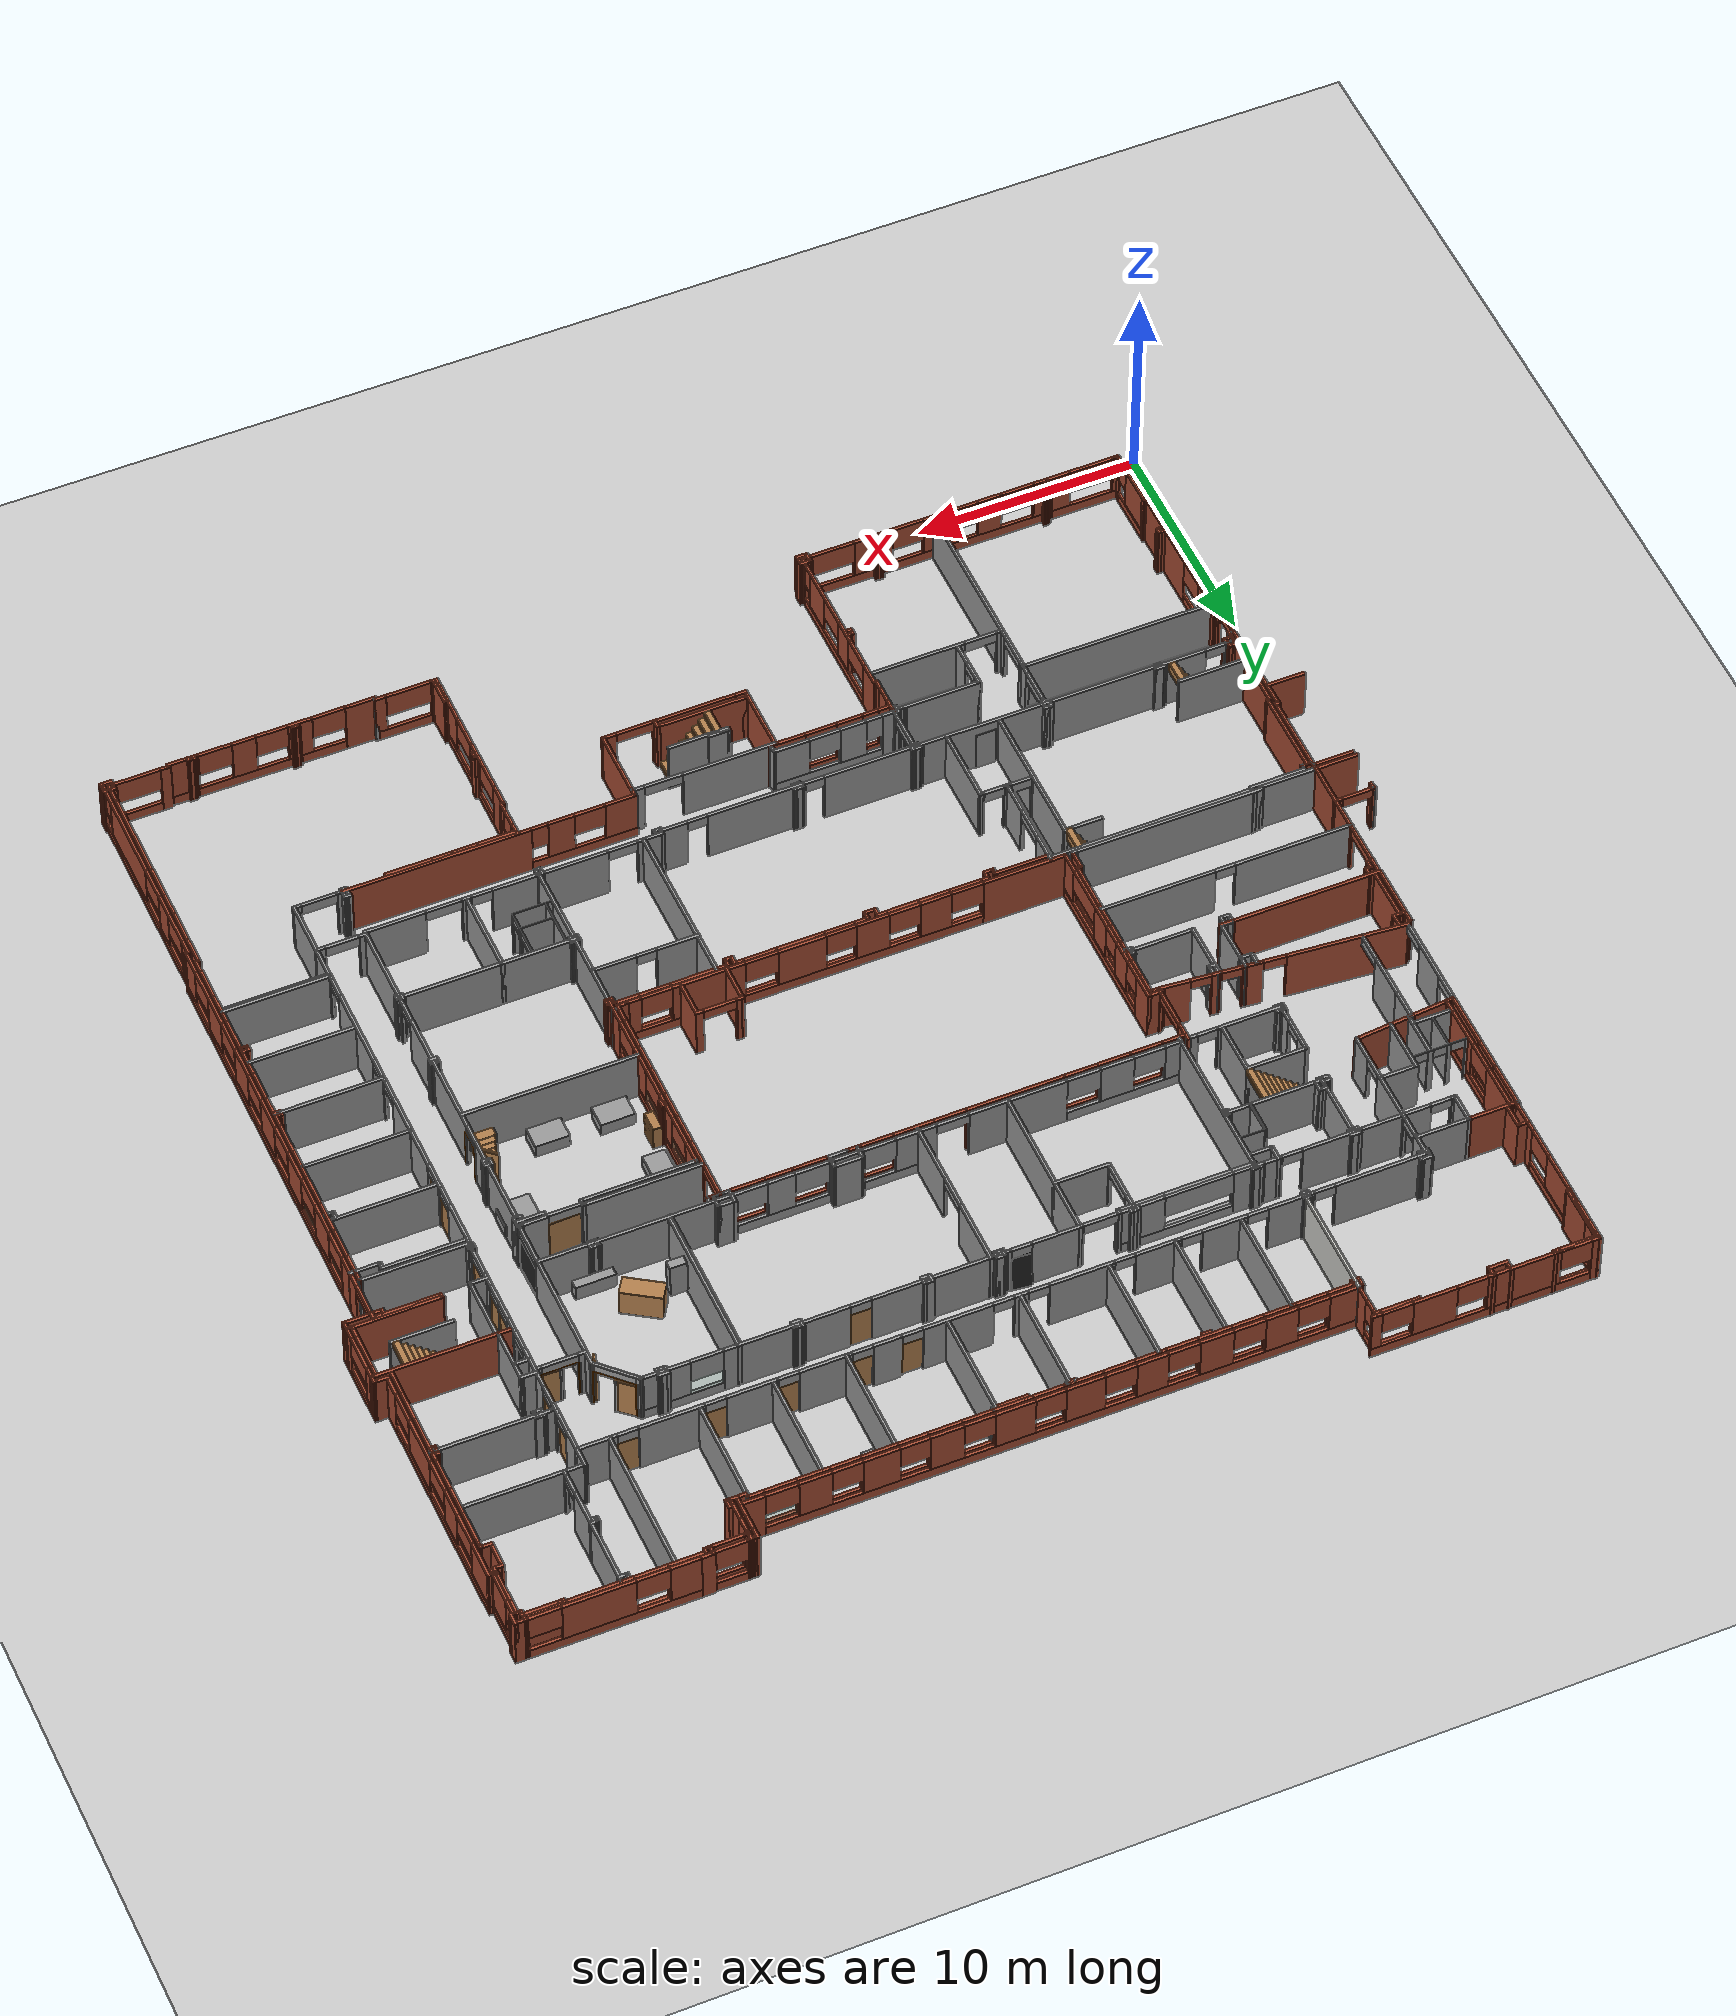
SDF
<sdf version="1.6">
 <world name="default">
  <light name="sun" type="directional">
   <pose>0 0 10 0 -0 0</pose>
   <diffuse>0.8 0.8 0.8 1</diffuse>
   <specular>0.1 0.1 0.1 1</specular>
   <attenuation>
    <range>1000</range>
    <constant>0.9</constant>
    <linear>0.01</linear>
    <quadratic>0.001</quadratic>
   </attenuation>
   <direction>-0.5 0.5 -1</direction>
  </light>
  <model name="ground_plane">
   <static>1</static>
   <link name="link">
    <collision name="collision">
     <geometry><plane><normal>0 0 1</normal><size>100 100</size></plane></geometry>
     <surface><friction><ode><mu>100</mu><mu2>50</mu2></ode></friction></surface>
    </collision>
    <visual name="visual">
     <cast_shadows>0</cast_shadows>
     <geometry><plane><normal>0 0 1</normal><size>100 100</size></plane></geometry>
     <material>
      <script><uri>file://media/materials/scripts/gazebo.material</uri><name>Gazebo/Grey</name></script>
     </material>
    </visual>
   </link>
  </model>
  <gravity>0 0 -9.8</gravity>
  <magnetic_field>6e-06 2.3e-05 -4.2e-05</magnetic_field>
  <atmosphere type="adiabatic"/>
  <physics name="default_physics" default="0" type="ode">
   <max_step_size>0.001</max_step_size>
   <real_time_factor>1</real_time_factor>
   <real_time_update_rate>1000</real_time_update_rate>
  </physics>
  <scene><ambient>0.4 0.4 0.4 1</ambient><background>0.7 0.7 0.7 1</background><shadows>1</shadows></scene>
  <spherical_coordinates>
   <surface_model>EARTH_WGS84</surface_model>
   <latitude_deg>0</latitude_deg>
   <longitude_deg>0</longitude_deg>
   <elevation>0</elevation>
   <heading_deg>0</heading_deg>
  </spherical_coordinates>
  <model name="CVSSP">
   <pose>23.8714 24.094 0 0 -0 0</pose>
   <link name="Door_85">
    <collision name="Door_85_Collision">
     <geometry><box><size>0.9 0.17 2</size></box></geometry>
     <pose>0 0 1 0 -0 0</pose>
    </collision>
    <visual name="Door_85_Visual">
     <pose>0 0 1 0 -0 0</pose>
     <geometry><box><size>0.9 0.17 2</size></box></geometry>
     <material>
      <script><uri>file://media/materials/scripts/gazebo.material</uri><name>Gazebo/Grey</name></script>
     </material>
    </visual>
    <pose>-11.2111 -11.3756 0 0 -0 0</pose>
   </link>
   <link name="Stairs_11">
    <visual name="Stairs_11_Visual_0">
     <pose>-13.1847 -4.32692 0.25 0 -0 1.5708</pose>
     <geometry><box><size>1.03 0.296708 0.5</size></box></geometry>
     <material>
      <script><uri>file://media/materials/scripts/gazebo.material</uri><name>Gazebo/Wood</name></script>
      <ambient>1 1 1 1</ambient>
     </material>
    </visual>
    <collision name="Stairs_11_Collision_0">
     <geometry><box><size>1.03 0.296708 0.5</size></box></geometry>
     <pose>-13.1847 -4.32692 0.25 0 -0 1.5708</pose>
    </collision>
    <visual name="Stairs_11_Visual_1">
     <pose>-12.888 -4.32692 0.75 0 -0 1.5708</pose>
     <geometry><box><size>1.03 0.296708 0.5</size></box></geometry>
     <material>
      <script><uri>file://media/materials/scripts/gazebo.material</uri><name>Gazebo/Wood</name></script>
      <ambient>1 1 1 1</ambient>
     </material>
    </visual>
    <collision name="Stairs_11_Collision_1">
     <geometry><box><size>1.03 0.296708 0.5</size></box></geometry>
     <pose>-12.888 -4.32692 0.75 0 -0 1.5708</pose>
    </collision>
    <visual name="Stairs_11_Visual_2">
     <pose>-12.5913 -4.32692 1.25 0 -0 1.5708</pose>
     <geometry><box><size>1.03 0.296708 0.5</size></box></geometry>
     <material>
      <script><uri>file://media/materials/scripts/gazebo.material</uri><name>Gazebo/Wood</name></script>
      <ambient>1 1 1 1</ambient>
     </material>
    </visual>
    <collision name="Stairs_11_Collision_2">
     <geometry><box><size>1.03 0.296708 0.5</size></box></geometry>
     <pose>-12.5913 -4.32692 1.25 0 -0 1.5708</pose>
    </collision>
    <visual name="Stairs_11_Visual_3">
     <pose>-12.2946 -4.32692 1.75 0 -0 1.5708</pose>
     <geometry><box><size>1.03 0.296708 0.5</size></box></geometry>
     <material>
      <script><uri>file://media/materials/scripts/gazebo.material</uri><name>Gazebo/Wood</name></script>
      <ambient>1 1 1 1</ambient>
     </material>
    </visual>
    <collision name="Stairs_11_Collision_3">
     <geometry><box><size>1.03 0.296708 0.5</size></box></geometry>
     <pose>-12.2946 -4.32692 1.75 0 -0 1.5708</pose>
    </collision>
    <visual name="Stairs_11_Visual_4">
     <pose>-11.9979 -4.32692 2.25 0 -0 1.5708</pose>
     <geometry><box><size>1.03 0.296708 0.5</size></box></geometry>
     <material>
      <script><uri>file://media/materials/scripts/gazebo.material</uri><name>Gazebo/Wood</name></script>
      <ambient>1 1 1 1</ambient>
     </material>
    </visual>
    <collision name="Stairs_11_Collision_4">
     <geometry><box><size>1.03 0.296708 0.5</size></box></geometry>
     <pose>-11.9979 -4.32692 2.25 0 -0 1.5708</pose>
    </collision>
   </link>
   <link name="Stairs_14">
    <visual name="Stairs_14_Visual_0">
     <pose>-20.7753 -10.8092 0.25 0 -0 1.5708</pose>
     <geometry><box><size>1.035 0.2838 0.5</size></box></geometry>
     <material>
      <script><uri>file://media/materials/scripts/gazebo.material</uri><name>Gazebo/Wood</name></script>
      <ambient>1 1 1 1</ambient>
     </material>
    </visual>
    <collision name="Stairs_14_Collision_0">
     <geometry><box><size>1.035 0.2838 0.5</size></box></geometry>
     <pose>-20.7753 -10.8092 0.25 0 -0 1.5708</pose>
    </collision>
    <visual name="Stairs_14_Visual_1">
     <pose>-20.4915 -10.8092 0.75 0 -0 1.5708</pose>
     <geometry><box><size>1.035 0.2838 0.5</size></box></geometry>
     <material>
      <script><uri>file://media/materials/scripts/gazebo.material</uri><name>Gazebo/Wood</name></script>
      <ambient>1 1 1 1</ambient>
     </material>
    </visual>
    <collision name="Stairs_14_Collision_1">
     <geometry><box><size>1.035 0.2838 0.5</size></box></geometry>
     <pose>-20.4915 -10.8092 0.75 0 -0 1.5708</pose>
    </collision>
    <visual name="Stairs_14_Visual_2">
     <pose>-20.2077 -10.8092 1.25 0 -0 1.5708</pose>
     <geometry><box><size>1.035 0.2838 0.5</size></box></geometry>
     <material>
      <script><uri>file://media/materials/scripts/gazebo.material</uri><name>Gazebo/Wood</name></script>
      <ambient>1 1 1 1</ambient>
     </material>
    </visual>
    <collision name="Stairs_14_Collision_2">
     <geometry><box><size>1.035 0.2838 0.5</size></box></geometry>
     <pose>-20.2077 -10.8092 1.25 0 -0 1.5708</pose>
    </collision>
    <visual name="Stairs_14_Visual_3">
     <pose>-19.9239 -10.8092 1.75 0 -0 1.5708</pose>
     <geometry><box><size>1.035 0.2838 0.5</size></box></geometry>
     <material>
      <script><uri>file://media/materials/scripts/gazebo.material</uri><name>Gazebo/Wood</name></script>
      <ambient>1 1 1 1</ambient>
     </material>
    </visual>
    <collision name="Stairs_14_Collision_3">
     <geometry><box><size>1.035 0.2838 0.5</size></box></geometry>
     <pose>-19.9239 -10.8092 1.75 0 -0 1.5708</pose>
    </collision>
    <visual name="Stairs_14_Visual_4">
     <pose>-19.6401 -10.8092 2.25 0 -0 1.5708</pose>
     <geometry><box><size>1.035 0.2838 0.5</size></box></geometry>
     <material>
      <script><uri>file://media/materials/scripts/gazebo.material</uri><name>Gazebo/Wood</name></script>
      <ambient>1 1 1 1</ambient>
     </material>
    </visual>
    <collision name="Stairs_14_Collision_4">
     <geometry><box><size>1.035 0.2838 0.5</size></box></geometry>
     <pose>-19.6401 -10.8092 2.25 0 -0 1.5708</pose>
    </collision>
   </link>
   <link name="Stairs_17">
    <visual name="Stairs_17_Visual_0">
     <pose>-15.6896 10.2929 0.138889 0 -0 1.5708</pose>
     <geometry><box><size>1.55 0.289267 0.277778</size></box></geometry>
     <material>
      <script><uri>file://media/materials/scripts/gazebo.material</uri><name>Gazebo/Wood</name></script>
      <ambient>0.588235 0.588235 0.588235 1</ambient>
     </material>
    </visual>
    <collision name="Stairs_17_Collision_0">
     <geometry><box><size>1.55 0.289267 0.277778</size></box></geometry>
     <pose>-15.6896 10.2929 0.138889 0 -0 1.5708</pose>
    </collision>
    <visual name="Stairs_17_Visual_1">
     <pose>-15.4003 10.2929 0.416667 0 -0 1.5708</pose>
     <geometry><box><size>1.55 0.289267 0.277778</size></box></geometry>
     <material>
      <script><uri>file://media/materials/scripts/gazebo.material</uri><name>Gazebo/Wood</name></script>
      <ambient>0.588235 0.588235 0.588235 1</ambient>
     </material>
    </visual>
    <collision name="Stairs_17_Collision_1">
     <geometry><box><size>1.55 0.289267 0.277778</size></box></geometry>
     <pose>-15.4003 10.2929 0.416667 0 -0 1.5708</pose>
    </collision>
    <visual name="Stairs_17_Visual_2">
     <pose>-15.1111 10.2929 0.694444 0 -0 1.5708</pose>
     <geometry><box><size>1.55 0.289267 0.277778</size></box></geometry>
     <material>
      <script><uri>file://media/materials/scripts/gazebo.material</uri><name>Gazebo/Wood</name></script>
      <ambient>0.588235 0.588235 0.588235 1</ambient>
     </material>
    </visual>
    <collision name="Stairs_17_Collision_2">
     <geometry><box><size>1.55 0.289267 0.277778</size></box></geometry>
     <pose>-15.1111 10.2929 0.694444 0 -0 1.5708</pose>
    </collision>
    <visual name="Stairs_17_Visual_3">
     <pose>-14.8218 10.2929 0.972222 0 -0 1.5708</pose>
     <geometry><box><size>1.55 0.289267 0.277778</size></box></geometry>
     <material>
      <script><uri>file://media/materials/scripts/gazebo.material</uri><name>Gazebo/Wood</name></script>
      <ambient>0.588235 0.588235 0.588235 1</ambient>
     </material>
    </visual>
    <collision name="Stairs_17_Collision_3">
     <geometry><box><size>1.55 0.289267 0.277778</size></box></geometry>
     <pose>-14.8218 10.2929 0.972222 0 -0 1.5708</pose>
    </collision>
    <visual name="Stairs_17_Visual_4">
     <pose>-14.5325 10.2929 1.25 0 -0 1.5708</pose>
     <geometry><box><size>1.55 0.289267 0.277778</size></box></geometry>
     <material>
      <script><uri>file://media/materials/scripts/gazebo.material</uri><name>Gazebo/Wood</name></script>
      <ambient>0.588235 0.588235 0.588235 1</ambient>
     </material>
    </visual>
    <collision name="Stairs_17_Collision_4">
     <geometry><box><size>1.55 0.289267 0.277778</size></box></geometry>
     <pose>-14.5325 10.2929 1.25 0 -0 1.5708</pose>
    </collision>
    <visual name="Stairs_17_Visual_5">
     <pose>-14.2433 10.2929 1.52778 0 -0 1.5708</pose>
     <geometry><box><size>1.55 0.289267 0.277778</size></box></geometry>
     <material>
      <script><uri>file://media/materials/scripts/gazebo.material</uri><name>Gazebo/Wood</name></script>
      <ambient>0.588235 0.588235 0.588235 1</ambient>
     </material>
    </visual>
    <collision name="Stairs_17_Collision_5">
     <geometry><box><size>1.55 0.289267 0.277778</size></box></geometry>
     <pose>-14.2433 10.2929 1.52778 0 -0 1.5708</pose>
    </collision>
    <visual name="Stairs_17_Visual_6">
     <pose>-13.954 10.2929 1.80556 0 -0 1.5708</pose>
     <geometry><box><size>1.55 0.289267 0.277778</size></box></geometry>
     <material>
      <script><uri>file://media/materials/scripts/gazebo.material</uri><name>Gazebo/Wood</name></script>
      <ambient>0.588235 0.588235 0.588235 1</ambient>
     </material>
    </visual>
    <collision name="Stairs_17_Collision_6">
     <geometry><box><size>1.55 0.289267 0.277778</size></box></geometry>
     <pose>-13.954 10.2929 1.80556 0 -0 1.5708</pose>
    </collision>
    <visual name="Stairs_17_Visual_7">
     <pose>-13.6647 10.2929 2.08333 0 -0 1.5708</pose>
     <geometry><box><size>1.55 0.289267 0.277778</size></box></geometry>
     <material>
      <script><uri>file://media/materials/scripts/gazebo.material</uri><name>Gazebo/Wood</name></script>
      <ambient>0.588235 0.588235 0.588235 1</ambient>
     </material>
    </visual>
    <collision name="Stairs_17_Collision_7">
     <geometry><box><size>1.55 0.289267 0.277778</size></box></geometry>
     <pose>-13.6647 10.2929 2.08333 0 -0 1.5708</pose>
    </collision>
    <visual name="Stairs_17_Visual_8">
     <pose>-13.3755 10.2929 2.36111 0 -0 1.5708</pose>
     <geometry><box><size>1.55 0.289267 0.277778</size></box></geometry>
     <material>
      <script><uri>file://media/materials/scripts/gazebo.material</uri><name>Gazebo/Wood</name></script>
      <ambient>0.588235 0.588235 0.588235 1</ambient>
     </material>
    </visual>
    <collision name="Stairs_17_Collision_8">
     <geometry><box><size>1.55 0.289267 0.277778</size></box></geometry>
     <pose>-13.3755 10.2929 2.36111 0 -0 1.5708</pose>
    </collision>
   </link>
   <link name="Stairs_2">
    <visual name="Stairs_2_Visual_0">
     <pose>20.6299 9.1142 0.138889 0 -0 1.5708</pose>
     <geometry><box><size>1.1749 0.286667 0.277778</size></box></geometry>
     <material>
      <script><uri>file://media/materials/scripts/gazebo.material</uri><name>Gazebo/Wood</name></script>
      <ambient>1 1 1 1</ambient>
     </material>
    </visual>
    <collision name="Stairs_2_Collision_0">
     <geometry><box><size>1.1749 0.286667 0.277778</size></box></geometry>
     <pose>20.6299 9.1142 0.138889 0 -0 1.5708</pose>
    </collision>
    <visual name="Stairs_2_Visual_1">
     <pose>20.9166 9.1142 0.416667 0 -0 1.5708</pose>
     <geometry><box><size>1.1749 0.286667 0.277778</size></box></geometry>
     <material>
      <script><uri>file://media/materials/scripts/gazebo.material</uri><name>Gazebo/Wood</name></script>
      <ambient>1 1 1 1</ambient>
     </material>
    </visual>
    <collision name="Stairs_2_Collision_1">
     <geometry><box><size>1.1749 0.286667 0.277778</size></box></geometry>
     <pose>20.9166 9.1142 0.416667 0 -0 1.5708</pose>
    </collision>
    <visual name="Stairs_2_Visual_2">
     <pose>21.2033 9.1142 0.694444 0 -0 1.5708</pose>
     <geometry><box><size>1.1749 0.286667 0.277778</size></box></geometry>
     <material>
      <script><uri>file://media/materials/scripts/gazebo.material</uri><name>Gazebo/Wood</name></script>
      <ambient>1 1 1 1</ambient>
     </material>
    </visual>
    <collision name="Stairs_2_Collision_2">
     <geometry><box><size>1.1749 0.286667 0.277778</size></box></geometry>
     <pose>21.2033 9.1142 0.694444 0 -0 1.5708</pose>
    </collision>
    <visual name="Stairs_2_Visual_3">
     <pose>21.4899 9.1142 0.972222 0 -0 1.5708</pose>
     <geometry><box><size>1.1749 0.286667 0.277778</size></box></geometry>
     <material>
      <script><uri>file://media/materials/scripts/gazebo.material</uri><name>Gazebo/Wood</name></script>
      <ambient>1 1 1 1</ambient>
     </material>
    </visual>
    <collision name="Stairs_2_Collision_3">
     <geometry><box><size>1.1749 0.286667 0.277778</size></box></geometry>
     <pose>21.4899 9.1142 0.972222 0 -0 1.5708</pose>
    </collision>
    <visual name="Stairs_2_Visual_4">
     <pose>21.7766 9.1142 1.25 0 -0 1.5708</pose>
     <geometry><box><size>1.1749 0.286667 0.277778</size></box></geometry>
     <material>
      <script><uri>file://media/materials/scripts/gazebo.material</uri><name>Gazebo/Wood</name></script>
      <ambient>1 1 1 1</ambient>
     </material>
    </visual>
    <collision name="Stairs_2_Collision_4">
     <geometry><box><size>1.1749 0.286667 0.277778</size></box></geometry>
     <pose>21.7766 9.1142 1.25 0 -0 1.5708</pose>
    </collision>
    <visual name="Stairs_2_Visual_5">
     <pose>22.0633 9.1142 1.52778 0 -0 1.5708</pose>
     <geometry><box><size>1.1749 0.286667 0.277778</size></box></geometry>
     <material>
      <script><uri>file://media/materials/scripts/gazebo.material</uri><name>Gazebo/Wood</name></script>
      <ambient>1 1 1 1</ambient>
     </material>
    </visual>
    <collision name="Stairs_2_Collision_5">
     <geometry><box><size>1.1749 0.286667 0.277778</size></box></geometry>
     <pose>22.0633 9.1142 1.52778 0 -0 1.5708</pose>
    </collision>
    <visual name="Stairs_2_Visual_6">
     <pose>22.3499 9.1142 1.80556 0 -0 1.5708</pose>
     <geometry><box><size>1.1749 0.286667 0.277778</size></box></geometry>
     <material>
      <script><uri>file://media/materials/scripts/gazebo.material</uri><name>Gazebo/Wood</name></script>
      <ambient>1 1 1 1</ambient>
     </material>
    </visual>
    <collision name="Stairs_2_Collision_6">
     <geometry><box><size>1.1749 0.286667 0.277778</size></box></geometry>
     <pose>22.3499 9.1142 1.80556 0 -0 1.5708</pose>
    </collision>
    <visual name="Stairs_2_Visual_7">
     <pose>22.6366 9.1142 2.08333 0 -0 1.5708</pose>
     <geometry><box><size>1.1749 0.286667 0.277778</size></box></geometry>
     <material>
      <script><uri>file://media/materials/scripts/gazebo.material</uri><name>Gazebo/Wood</name></script>
      <ambient>1 1 1 1</ambient>
     </material>
    </visual>
    <collision name="Stairs_2_Collision_7">
     <geometry><box><size>1.1749 0.286667 0.277778</size></box></geometry>
     <pose>22.6366 9.1142 2.08333 0 -0 1.5708</pose>
    </collision>
    <visual name="Stairs_2_Visual_8">
     <pose>22.9233 9.1142 2.36111 0 -0 1.5708</pose>
     <geometry><box><size>1.1749 0.286667 0.277778</size></box></geometry>
     <material>
      <script><uri>file://media/materials/scripts/gazebo.material</uri><name>Gazebo/Wood</name></script>
      <ambient>1 1 1 1</ambient>
     </material>
    </visual>
    <collision name="Stairs_2_Collision_8">
     <geometry><box><size>1.1749 0.286667 0.277778</size></box></geometry>
     <pose>22.9233 9.1142 2.36111 0 -0 1.5708</pose>
    </collision>
   </link>
   <link name="Stairs_6">
    <visual name="Stairs_6_Visual_0">
     <pose>0.989254 -16.0013 0.15625 0 -0 -1.5708</pose>
     <geometry><box><size>1.145 0.28375 0.3125</size></box></geometry>
     <material>
      <script><uri>file://media/materials/scripts/gazebo.material</uri><name>Gazebo/Wood</name></script>
      <ambient>1 1 1 1</ambient>
     </material>
    </visual>
    <collision name="Stairs_6_Collision_0">
     <geometry><box><size>1.145 0.28375 0.3125</size></box></geometry>
     <pose>0.989254 -16.0013 0.15625 0 -0 -1.5708</pose>
    </collision>
    <visual name="Stairs_6_Visual_1">
     <pose>0.705504 -16.0013 0.46875 0 -0 -1.5708</pose>
     <geometry><box><size>1.145 0.28375 0.3125</size></box></geometry>
     <material>
      <script><uri>file://media/materials/scripts/gazebo.material</uri><name>Gazebo/Wood</name></script>
      <ambient>1 1 1 1</ambient>
     </material>
    </visual>
    <collision name="Stairs_6_Collision_1">
     <geometry><box><size>1.145 0.28375 0.3125</size></box></geometry>
     <pose>0.705504 -16.0013 0.46875 0 -0 -1.5708</pose>
    </collision>
    <visual name="Stairs_6_Visual_2">
     <pose>0.421754 -16.0013 0.78125 0 -0 -1.5708</pose>
     <geometry><box><size>1.145 0.28375 0.3125</size></box></geometry>
     <material>
      <script><uri>file://media/materials/scripts/gazebo.material</uri><name>Gazebo/Wood</name></script>
      <ambient>1 1 1 1</ambient>
     </material>
    </visual>
    <collision name="Stairs_6_Collision_2">
     <geometry><box><size>1.145 0.28375 0.3125</size></box></geometry>
     <pose>0.421754 -16.0013 0.78125 0 -0 -1.5708</pose>
    </collision>
    <visual name="Stairs_6_Visual_3">
     <pose>0.138004 -16.0013 1.09375 0 -0 -1.5708</pose>
     <geometry><box><size>1.145 0.28375 0.3125</size></box></geometry>
     <material>
      <script><uri>file://media/materials/scripts/gazebo.material</uri><name>Gazebo/Wood</name></script>
      <ambient>1 1 1 1</ambient>
     </material>
    </visual>
    <collision name="Stairs_6_Collision_3">
     <geometry><box><size>1.145 0.28375 0.3125</size></box></geometry>
     <pose>0.138004 -16.0013 1.09375 0 -0 -1.5708</pose>
    </collision>
    <visual name="Stairs_6_Visual_4">
     <pose>-0.145746 -16.0013 1.40625 0 -0 -1.5708</pose>
     <geometry><box><size>1.145 0.28375 0.3125</size></box></geometry>
     <material>
      <script><uri>file://media/materials/scripts/gazebo.material</uri><name>Gazebo/Wood</name></script>
      <ambient>1 1 1 1</ambient>
     </material>
    </visual>
    <collision name="Stairs_6_Collision_4">
     <geometry><box><size>1.145 0.28375 0.3125</size></box></geometry>
     <pose>-0.145746 -16.0013 1.40625 0 -0 -1.5708</pose>
    </collision>
    <visual name="Stairs_6_Visual_5">
     <pose>-0.429496 -16.0013 1.71875 0 -0 -1.5708</pose>
     <geometry><box><size>1.145 0.28375 0.3125</size></box></geometry>
     <material>
      <script><uri>file://media/materials/scripts/gazebo.material</uri><name>Gazebo/Wood</name></script>
      <ambient>1 1 1 1</ambient>
     </material>
    </visual>
    <collision name="Stairs_6_Collision_5">
     <geometry><box><size>1.145 0.28375 0.3125</size></box></geometry>
     <pose>-0.429496 -16.0013 1.71875 0 -0 -1.5708</pose>
    </collision>
    <visual name="Stairs_6_Visual_6">
     <pose>-0.713246 -16.0013 2.03125 0 -0 -1.5708</pose>
     <geometry><box><size>1.145 0.28375 0.3125</size></box></geometry>
     <material>
      <script><uri>file://media/materials/scripts/gazebo.material</uri><name>Gazebo/Wood</name></script>
      <ambient>1 1 1 1</ambient>
     </material>
    </visual>
    <collision name="Stairs_6_Collision_6">
     <geometry><box><size>1.145 0.28375 0.3125</size></box></geometry>
     <pose>-0.713246 -16.0013 2.03125 0 -0 -1.5708</pose>
    </collision>
    <visual name="Stairs_6_Visual_7">
     <pose>-0.996996 -16.0013 2.34375 0 -0 -1.5708</pose>
     <geometry><box><size>1.145 0.28375 0.3125</size></box></geometry>
     <material>
      <script><uri>file://media/materials/scripts/gazebo.material</uri><name>Gazebo/Wood</name></script>
      <ambient>1 1 1 1</ambient>
     </material>
    </visual>
    <collision name="Stairs_6_Collision_7">
     <geometry><box><size>1.145 0.28375 0.3125</size></box></geometry>
     <pose>-0.996996 -16.0013 2.34375 0 -0 -1.5708</pose>
    </collision>
   </link>
   <link name="Wall_0">
    <pose>1.68767 14.035 0 0 -0 0</pose>
    <visual name="Wall_0_Visual_0">
     <pose>-12.7386 0 1.25 0 -0 0</pose>
     <geometry><box><size>1.02282 0.15 2.5</size></box></geometry>
     <material>
      <script><uri>file://media/materials/scripts/gazebo.material</uri><name>Gazebo/Grey</name></script>
      <ambient>0.588235 0.588235 0.588235 1</ambient>
     </material>
    </visual>
    <collision name="Wall_0_Collision_0">
     <geometry><box><size>1.02282 0.15 2.5</size></box></geometry>
     <pose>-12.7386 0 1.25 0 -0 0</pose>
    </collision>
    <visual name="Wall_0_Visual_1">
     <pose>-4.58044 0 1.25 0 -0 0</pose>
     <geometry><box><size>2.22198 0.15 2.5</size></box></geometry>
     <material>
      <script><uri>file://media/materials/scripts/gazebo.material</uri><name>Gazebo/Grey</name></script>
      <ambient>0.588235 0.588235 0.588235 1</ambient>
     </material>
    </visual>
    <collision name="Wall_0_Collision_1">
     <geometry><box><size>2.22198 0.15 2.5</size></box></geometry>
     <pose>-4.58044 0 1.25 0 -0 0</pose>
    </collision>
    <visual name="Wall_0_Visual_2">
     <pose>0.426093 0 1.25 0 -0 0</pose>
     <geometry><box><size>5.99108 0.15 2.5</size></box></geometry>
     <material>
      <script><uri>file://media/materials/scripts/gazebo.material</uri><name>Gazebo/Grey</name></script>
      <ambient>0.588235 0.588235 0.588235 1</ambient>
     </material>
    </visual>
    <collision name="Wall_0_Collision_2">
     <geometry><box><size>5.99108 0.15 2.5</size></box></geometry>
     <pose>0.426093 0 1.25 0 -0 0</pose>
    </collision>
    <visual name="Wall_0_Visual_3">
     <pose>7.01875 0 1.25 0 -0 0</pose>
     <geometry><box><size>5.39422 0.15 2.5</size></box></geometry>
     <material>
      <script><uri>file://media/materials/scripts/gazebo.material</uri><name>Gazebo/Grey</name></script>
      <ambient>0.588235 0.588235 0.588235 1</ambient>
     </material>
    </visual>
    <collision name="Wall_0_Collision_3">
     <geometry><box><size>5.39422 0.15 2.5</size></box></geometry>
     <pose>7.01875 0 1.25 0 -0 0</pose>
    </collision>
    <visual name="Wall_0_Visual_4">
     <pose>-9.74161 0 0.25 0 -0 0</pose>
     <geometry><box><size>4.97113 0.15 0.5</size></box></geometry>
     <material>
      <script><uri>file://media/materials/scripts/gazebo.material</uri><name>Gazebo/Grey</name></script>
      <ambient>0.588235 0.588235 0.588235 1</ambient>
     </material>
    </visual>
    <collision name="Wall_0_Collision_4">
     <geometry><box><size>4.97113 0.15 0.5</size></box></geometry>
     <pose>-9.74161 0 0.25 0 -0 0</pose>
    </collision>
    <visual name="Wall_0_Visual_5">
     <pose>11.4829 0 0.25 0 -0 0</pose>
     <geometry><box><size>3.53415 0.15 0.5</size></box></geometry>
     <material>
      <script><uri>file://media/materials/scripts/gazebo.material</uri><name>Gazebo/Grey</name></script>
      <ambient>0.588235 0.588235 0.588235 1</ambient>
     </material>
    </visual>
    <collision name="Wall_0_Collision_5">
     <geometry><box><size>3.53415 0.15 0.5</size></box></geometry>
     <pose>11.4829 0 0.25 0 -0 0</pose>
    </collision>
    <visual name="Wall_0_Visual_6">
     <pose>-8.24385 0 1.5 0 -0 0</pose>
     <geometry><box><size>1.9756 0.15 2</size></box></geometry>
     <material>
      <script><uri>file://media/materials/scripts/gazebo.material</uri><name>Gazebo/Grey</name></script>
      <ambient>0.588235 0.588235 0.588235 1</ambient>
     </material>
    </visual>
    <collision name="Wall_0_Collision_6">
     <geometry><box><size>1.9756 0.15 2</size></box></geometry>
     <pose>-8.24385 0 1.5 0 -0 0</pose>
    </collision>
    <visual name="Wall_0_Visual_7">
     <pose>-8.24385 0 1.5 0 -0 0</pose>
     <geometry><box><size>1.9756 0.15 2</size></box></geometry>
     <material>
      <script><uri>file://media/materials/scripts/gazebo.material</uri><name>Gazebo/Grey</name></script>
      <ambient>0.588235 0.588235 0.588235 1</ambient>
     </material>
    </visual>
    <collision name="Wall_0_Collision_7">
     <geometry><box><size>1.9756 0.15 2</size></box></geometry>
     <pose>-8.24385 0 1.5 0 -0 0</pose>
    </collision>
    <visual name="Wall_0_Visual_8">
     <pose>12.1924 0 1.5 0 -0 0</pose>
     <geometry><box><size>2.11511 0.15 2</size></box></geometry>
     <material>
      <script><uri>file://media/materials/scripts/gazebo.material</uri><name>Gazebo/Grey</name></script>
      <ambient>0.588235 0.588235 0.588235 1</ambient>
     </material>
    </visual>
    <collision name="Wall_0_Collision_8">
     <geometry><box><size>2.11511 0.15 2</size></box></geometry>
     <pose>12.1924 0 1.5 0 -0 0</pose>
    </collision>
    <visual name="Wall_0_Visual_9">
     <pose>-10.7294 0 1.9 0 -0 0</pose>
     <geometry><box><size>2.99553 0.15 1.2</size></box></geometry>
     <material>
      <script><uri>file://media/materials/scripts/gazebo.material</uri><name>Gazebo/Grey</name></script>
      <ambient>0.588235 0.588235 0.588235 1</ambient>
     </material>
    </visual>
    <collision name="Wall_0_Collision_9">
     <geometry><box><size>2.99553 0.15 1.2</size></box></geometry>
     <pose>-10.7294 0 1.9 0 -0 0</pose>
    </collision>
    <visual name="Wall_0_Visual_10">
     <pose>10.4254 0 1.9 0 -0 0</pose>
     <geometry><box><size>1.41904 0.15 1.2</size></box></geometry>
     <material>
      <script><uri>file://media/materials/scripts/gazebo.material</uri><name>Gazebo/Grey</name></script>
      <ambient>0.588235 0.588235 0.588235 1</ambient>
     </material>
    </visual>
    <collision name="Wall_0_Collision_10">
     <geometry><box><size>1.41904 0.15 1.2</size></box></geometry>
     <pose>10.4254 0 1.9 0 -0 0</pose>
    </collision>
    <visual name="Wall_0_Visual_11">
     <pose>-3.01945 0 2.25 0 -0 0</pose>
     <geometry><box><size>0.9 0.15 0.5</size></box></geometry>
     <material>
      <script><uri>file://media/materials/scripts/gazebo.material</uri><name>Gazebo/Grey</name></script>
      <ambient>0.588235 0.588235 0.588235 1</ambient>
     </material>
    </visual>
    <collision name="Wall_0_Collision_11">
     <geometry><box><size>0.9 0.15 0.5</size></box></geometry>
     <pose>-3.01945 0 2.25 0 -0 0</pose>
    </collision>
    <visual name="Wall_0_Visual_12">
     <pose>3.87163 0 2.25 0 -0 0</pose>
     <geometry><box><size>0.9 0.15 0.5</size></box></geometry>
     <material>
      <script><uri>file://media/materials/scripts/gazebo.material</uri><name>Gazebo/Grey</name></script>
      <ambient>0.588235 0.588235 0.588235 1</ambient>
     </material>
    </visual>
    <collision name="Wall_0_Collision_12">
     <geometry><box><size>0.9 0.15 0.5</size></box></geometry>
     <pose>3.87163 0 2.25 0 -0 0</pose>
    </collision>
    <visual name="Wall_0_Visual_13">
     <pose>-6.47374 0 2.25 0 -0 0</pose>
     <geometry><box><size>1.56462 0.15 0.5</size></box></geometry>
     <material>
      <script><uri>file://media/materials/scripts/gazebo.material</uri><name>Gazebo/Grey</name></script>
      <ambient>0.588235 0.588235 0.588235 1</ambient>
     </material>
    </visual>
    <collision name="Wall_0_Collision_13">
     <geometry><box><size>1.56462 0.15 0.5</size></box></geometry>
     <pose>-6.47374 0 2.25 0 -0 0</pose>
    </collision>
    <visual name="Wall_0_Visual_14">
     <pose>-6.47374 0 2.25 0 -0 0</pose>
     <geometry><box><size>1.56462 0.15 0.5</size></box></geometry>
     <material>
      <script><uri>file://media/materials/scripts/gazebo.material</uri><name>Gazebo/Grey</name></script>
      <ambient>0.588235 0.588235 0.588235 1</ambient>
     </material>
    </visual>
    <collision name="Wall_0_Collision_14">
     <geometry><box><size>1.56462 0.15 0.5</size></box></geometry>
     <pose>-6.47374 0 2.25 0 -0 0</pose>
    </collision>
   </link>
   <link name="Wall_1">
    <pose>15.5976 13.2926 0 0 0 -0.785398</pose>
    <visual name="Wall_1_Visual_0">
     <pose>-0.986494 0 1.25 0 -0 0</pose>
     <geometry><box><size>0.277012 0.15 2.5</size></box></geometry>
     <material>
      <script><uri>file://media/materials/scripts/gazebo.material</uri><name>Gazebo/Grey</name></script>
      <ambient>0.588235 0.588235 0.588235 1</ambient>
     </material>
    </visual>
    <collision name="Wall_1_Collision_0">
     <geometry><box><size>0.277012 0.15 2.5</size></box></geometry>
     <pose>-0.986494 0 1.25 0 -0 0</pose>
    </collision>
    <visual name="Wall_1_Visual_1">
     <pose>1.02335 0 1.25 0 -0 0</pose>
     <geometry><box><size>0.203299 0.15 2.5</size></box></geometry>
     <material>
      <script><uri>file://media/materials/scripts/gazebo.material</uri><name>Gazebo/Grey</name></script>
      <ambient>0.588235 0.588235 0.588235 1</ambient>
     </material>
    </visual>
    <collision name="Wall_1_Collision_1">
     <geometry><box><size>0.203299 0.15 2.5</size></box></geometry>
     <pose>1.02335 0 1.25 0 -0 0</pose>
    </collision>
    <visual name="Wall_1_Visual_2">
     <pose>0.036857 0 2.25 0 -0 0</pose>
     <geometry><box><size>1.76969 0.15 0.5</size></box></geometry>
     <material>
      <script><uri>file://media/materials/scripts/gazebo.material</uri><name>Gazebo/Grey</name></script>
      <ambient>0.588235 0.588235 0.588235 1</ambient>
     </material>
    </visual>
    <collision name="Wall_1_Collision_2">
     <geometry><box><size>1.76969 0.15 0.5</size></box></geometry>
     <pose>0.036857 0 2.25 0 -0 0</pose>
    </collision>
   </link>
   <link name="Wall_10">
    <collision name="Wall_10_Collision">
     <geometry><box><size>0.244894 0.15 2.5</size></box></geometry>
     <pose>0 0 1.25 0 -0 0</pose>
    </collision>
    <visual name="Wall_10_Visual">
     <pose>0 0 1.25 0 -0 0</pose>
     <geometry><box><size>0.244894 0.15 2.5</size></box></geometry>
     <material>
      <script><uri>file://media/materials/scripts/gazebo.material</uri><name>Gazebo/Grey</name></script>
      <ambient>1 1 1 1</ambient>
     </material>
    </visual>
    <pose>16.3427 4.74414 0 0 -0 3.0813</pose>
   </link>
   <link name="Wall_101">
    <collision name="Wall_101_Collision">
     <geometry><box><size>0.38805 0.15 2.5</size></box></geometry>
     <pose>0 0 1.25 0 -0 0</pose>
    </collision>
    <visual name="Wall_101_Visual">
     <pose>0 0 1.25 0 -0 0</pose>
     <geometry><box><size>0.38805 0.15 2.5</size></box></geometry>
     <material>
      <script><uri>file://media/materials/scripts/gazebo.material</uri><name>Gazebo/Grey</name></script>
      <ambient>1 1 1 1</ambient>
     </material>
    </visual>
    <pose>13.6125 5.08725 0 0 0 -1.5708</pose>
   </link>
   <link name="Wall_103">
    <pose>14.4193 5.12692 0 0 -0 3.13861</pose>
    <visual name="Wall_103_Visual_0">
     <pose>-0.803949 0 1.25 0 -0 0</pose>
     <geometry><box><size>0.113401 0.15 2.5</size></box></geometry>
     <material>
      <script><uri>file://media/materials/scripts/gazebo.material</uri><name>Gazebo/Grey</name></script>
      <ambient>1 1 1 1</ambient>
     </material>
    </visual>
    <collision name="Wall_103_Collision_0">
     <geometry><box><size>0.113401 0.15 2.5</size></box></geometry>
     <pose>-0.803949 0 1.25 0 -0 0</pose>
    </collision>
    <visual name="Wall_103_Visual_1">
     <pose>0.799121 0 1.25 0 -0 0</pose>
     <geometry><box><size>0.123058 0.15 2.5</size></box></geometry>
     <material>
      <script><uri>file://media/materials/scripts/gazebo.material</uri><name>Gazebo/Grey</name></script>
      <ambient>1 1 1 1</ambient>
     </material>
    </visual>
    <collision name="Wall_103_Collision_1">
     <geometry><box><size>0.123058 0.15 2.5</size></box></geometry>
     <pose>0.799121 0 1.25 0 -0 0</pose>
    </collision>
    <visual name="Wall_103_Visual_2">
     <pose>-0.004828 0 2.25 0 -0 0</pose>
     <geometry><box><size>1.48484 0.15 0.5</size></box></geometry>
     <material>
      <script><uri>file://media/materials/scripts/gazebo.material</uri><name>Gazebo/Grey</name></script>
      <ambient>1 1 1 1</ambient>
     </material>
    </visual>
    <collision name="Wall_103_Collision_2">
     <geometry><box><size>1.48484 0.15 0.5</size></box></geometry>
     <pose>-0.004828 0 2.25 0 -0 0</pose>
    </collision>
   </link>
   <link name="Wall_105">
    <collision name="Wall_105_Collision">
     <geometry><box><size>0.321526 0.15 2.5</size></box></geometry>
     <pose>0 0 1.25 0 -0 0</pose>
    </collision>
    <visual name="Wall_105_Visual">
     <pose>0 0 1.25 0 -0 0</pose>
     <geometry><box><size>0.321526 0.15 2.5</size></box></geometry>
     <material>
      <script><uri>file://media/materials/scripts/gazebo.material</uri><name>Gazebo/Grey</name></script>
      <ambient>1 1 1 1</ambient>
     </material>
    </visual>
    <pose>15.205 5.04453 0 0 0 -1.5708</pose>
   </link>
   <link name="Wall_106">
    <collision name="Wall_106_Collision">
     <geometry><box><size>1.33354 0.15 2.5</size></box></geometry>
     <pose>0 0 1.25 0 -0 0</pose>
    </collision>
    <visual name="Wall_106_Visual">
     <pose>0 0 1.25 0 -0 0</pose>
     <geometry><box><size>1.33354 0.15 2.5</size></box></geometry>
     <material>
      <script><uri>file://media/materials/scripts/gazebo.material</uri><name>Gazebo/Grey</name></script>
      <ambient>1 1 1 1</ambient>
     </material>
    </visual>
    <pose>15.7968 4.95877 0 0 -0 0</pose>
   </link>
   <link name="Wall_108">
    <collision name="Wall_108_Collision">
     <geometry><box><size>0.336995 0.15 2.5</size></box></geometry>
     <pose>0 0 1.25 0 -0 0</pose>
    </collision>
    <visual name="Wall_108_Visual">
     <pose>0 0 1.25 0 -0 0</pose>
     <geometry><box><size>0.336995 0.15 2.5</size></box></geometry>
     <material>
      <script><uri>file://media/materials/scripts/gazebo.material</uri><name>Gazebo/Grey</name></script>
      <ambient>1 1 1 1</ambient>
     </material>
    </visual>
    <pose>16.2019 4.74711 0 0 -0 3.1404</pose>
   </link>
   <link name="Wall_109">
    <collision name="Wall_109_Collision">
     <geometry><box><size>0.578815 0.15 2.5</size></box></geometry>
     <pose>0 0 1.25 0 -0 0</pose>
    </collision>
    <visual name="Wall_109_Visual">
     <pose>0 0 1.25 0 -0 0</pose>
     <geometry><box><size>0.578815 0.15 2.5</size></box></geometry>
     <material>
      <script><uri>file://media/materials/scripts/gazebo.material</uri><name>Gazebo/Grey</name></script>
      <ambient>1 1 1 1</ambient>
     </material>
    </visual>
    <pose>16.1084 4.96163 0 0 -0 1.5708</pose>
   </link>
   <link name="Wall_11">
    <pose>16.2898 -3.24326 0 0 0 -1.57079</pose>
    <visual name="Wall_11_Visual_0">
     <pose>-5.93516 0 1.25 0 -0 0</pose>
     <geometry><box><size>4.26019 0.15 2.5</size></box></geometry>
     <material>
      <script><uri>file://media/materials/scripts/gazebo.material</uri><name>Gazebo/Grey</name></script>
      <ambient>0.588235 0.588235 0.588235 1</ambient>
     </material>
    </visual>
    <collision name="Wall_11_Collision_0">
     <geometry><box><size>4.26019 0.15 2.5</size></box></geometry>
     <pose>-5.93516 0 1.25 0 -0 0</pose>
    </collision>
    <visual name="Wall_11_Visual_1">
     <pose>0.054186 0 1.25 0 -0 0</pose>
     <geometry><box><size>5.9185 0.15 2.5</size></box></geometry>
     <material>
      <script><uri>file://media/materials/scripts/gazebo.material</uri><name>Gazebo/Grey</name></script>
      <ambient>0.588235 0.588235 0.588235 1</ambient>
     </material>
    </visual>
    <collision name="Wall_11_Collision_1">
     <geometry><box><size>5.9185 0.15 2.5</size></box></geometry>
     <pose>0.054186 0 1.25 0 -0 0</pose>
    </collision>
    <visual name="Wall_11_Visual_2">
     <pose>5.98935 0 1.25 0 -0 0</pose>
     <geometry><box><size>4.15182 0.15 2.5</size></box></geometry>
     <material>
      <script><uri>file://media/materials/scripts/gazebo.material</uri><name>Gazebo/Grey</name></script>
      <ambient>0.588235 0.588235 0.588235 1</ambient>
     </material>
    </visual>
    <collision name="Wall_11_Collision_2">
     <geometry><box><size>4.15182 0.15 2.5</size></box></geometry>
     <pose>5.98935 0 1.25 0 -0 0</pose>
    </collision>
    <visual name="Wall_11_Visual_3">
     <pose>-3.35506 0 2.25 0 -0 0</pose>
     <geometry><box><size>0.9 0.15 0.5</size></box></geometry>
     <material>
      <script><uri>file://media/materials/scripts/gazebo.material</uri><name>Gazebo/Grey</name></script>
      <ambient>0.588235 0.588235 0.588235 1</ambient>
     </material>
    </visual>
    <collision name="Wall_11_Collision_3">
     <geometry><box><size>0.9 0.15 0.5</size></box></geometry>
     <pose>-3.35506 0 2.25 0 -0 0</pose>
    </collision>
    <visual name="Wall_11_Visual_4">
     <pose>3.46344 0 2.25 0 -0 0</pose>
     <geometry><box><size>0.9 0.15 0.5</size></box></geometry>
     <material>
      <script><uri>file://media/materials/scripts/gazebo.material</uri><name>Gazebo/Grey</name></script>
      <ambient>0.588235 0.588235 0.588235 1</ambient>
     </material>
    </visual>
    <collision name="Wall_11_Collision_4">
     <geometry><box><size>0.9 0.15 0.5</size></box></geometry>
     <pose>3.46344 0 2.25 0 -0 0</pose>
    </collision>
   </link>
   <link name="Wall_110">
    <collision name="Wall_110_Collision">
     <geometry><box><size>0.435877 0.15 2.5</size></box></geometry>
     <pose>0 0 1.25 0 -0 0</pose>
    </collision>
    <visual name="Wall_110_Visual">
     <pose>0 0 1.25 0 -0 0</pose>
     <geometry><box><size>0.435877 0.15 2.5</size></box></geometry>
     <material>
      <script><uri>file://media/materials/scripts/gazebo.material</uri><name>Gazebo/Grey</name></script>
      <ambient>1 1 1 1</ambient>
     </material>
    </visual>
    <pose>16.2513 5.17604 0 0 -0 0</pose>
   </link>
   <link name="Wall_112">
    <collision name="Wall_112_Collision">
     <geometry><box><size>1.05344 0.15 2.5</size></box></geometry>
     <pose>0 0 1.25 0 -0 0</pose>
    </collision>
    <visual name="Wall_112_Visual">
     <pose>0 0 1.25 0 -0 0</pose>
     <geometry><box><size>1.05344 0.15 2.5</size></box></geometry>
     <material>
      <script><uri>file://media/materials/scripts/gazebo.material</uri><name>Gazebo/Grey</name></script>
      <ambient>1 1 1 1</ambient>
     </material>
    </visual>
    <pose>15.6567 5.17604 0 0 -0 3.14159</pose>
   </link>
   <link name="Wall_115">
    <pose>12.4857 -11.244 0 0 -0 3.14117</pose>
    <visual name="Wall_115_Visual_0">
     <pose>-2.52803 0 1.25 0 -0 0</pose>
     <geometry><box><size>2.69541 0.15 2.5</size></box></geometry>
     <material>
      <script><uri>file://media/materials/scripts/gazebo.material</uri><name>Gazebo/Grey</name></script>
      <ambient>0.588235 0.588235 0.588235 1</ambient>
     </material>
    </visual>
    <collision name="Wall_115_Collision_0">
     <geometry><box><size>2.69541 0.15 2.5</size></box></geometry>
     <pose>-2.52803 0 1.25 0 -0 0</pose>
    </collision>
    <visual name="Wall_115_Visual_1">
     <pose>0.612242 0 1.25 0 -0 0</pose>
     <geometry><box><size>0.417444 0.15 2.5</size></box></geometry>
     <material>
      <script><uri>file://media/materials/scripts/gazebo.material</uri><name>Gazebo/Grey</name></script>
      <ambient>0.588235 0.588235 0.588235 1</ambient>
     </material>
    </visual>
    <collision name="Wall_115_Collision_1">
     <geometry><box><size>0.417444 0.15 2.5</size></box></geometry>
     <pose>0.612242 0 1.25 0 -0 0</pose>
    </collision>
    <visual name="Wall_115_Visual_2">
     <pose>2.79835 0 1.25 0 -0 0</pose>
     <geometry><box><size>2.15477 0.15 2.5</size></box></geometry>
     <material>
      <script><uri>file://media/materials/scripts/gazebo.material</uri><name>Gazebo/Grey</name></script>
      <ambient>0.588235 0.588235 0.588235 1</ambient>
     </material>
    </visual>
    <collision name="Wall_115_Collision_2">
     <geometry><box><size>2.15477 0.15 2.5</size></box></geometry>
     <pose>2.79835 0 1.25 0 -0 0</pose>
    </collision>
    <visual name="Wall_115_Visual_3">
     <pose>-0.388402 0 2.25 0 -0 0</pose>
     <geometry><box><size>1.58384 0.15 0.5</size></box></geometry>
     <material>
      <script><uri>file://media/materials/scripts/gazebo.material</uri><name>Gazebo/Grey</name></script>
      <ambient>0.588235 0.588235 0.588235 1</ambient>
     </material>
    </visual>
    <collision name="Wall_115_Collision_3">
     <geometry><box><size>1.58384 0.15 0.5</size></box></geometry>
     <pose>-0.388402 0 2.25 0 -0 0</pose>
    </collision>
    <visual name="Wall_115_Visual_4">
     <pose>1.27096 0 2.25 0 -0 0</pose>
     <geometry><box><size>0.9 0.15 0.5</size></box></geometry>
     <material>
      <script><uri>file://media/materials/scripts/gazebo.material</uri><name>Gazebo/Grey</name></script>
      <ambient>0.588235 0.588235 0.588235 1</ambient>
     </material>
    </visual>
    <collision name="Wall_115_Collision_4">
     <geometry><box><size>0.9 0.15 0.5</size></box></geometry>
     <pose>1.27096 0 2.25 0 -0 0</pose>
    </collision>
   </link>
   <link name="Wall_116">
    <collision name="Wall_116_Collision">
     <geometry><box><size>7.43734 0.15 2.5</size></box></geometry>
     <pose>0 0 1.25 0 -0 0</pose>
    </collision>
    <visual name="Wall_116_Visual">
     <pose>0 0 1.25 0 -0 0</pose>
     <geometry><box><size>7.43734 0.15 2.5</size></box></geometry>
     <material>
      <script><uri>file://media/materials/scripts/gazebo.material</uri><name>Gazebo/Grey</name></script>
      <ambient>1 1 1 1</ambient>
     </material>
    </visual>
    <pose>8.67152 -7.59872 0 0 -0 1.57447</pose>
   </link>
   <link name="Wall_118">
    <collision name="Wall_118_Collision">
     <geometry><box><size>0.6489 0.15 2.5</size></box></geometry>
     <pose>0 0 1.25 0 -0 0</pose>
    </collision>
    <visual name="Wall_118_Visual">
     <pose>0 0 1.25 0 -0 0</pose>
     <geometry><box><size>0.6489 0.15 2.5</size></box></geometry>
     <material>
      <script><uri>file://media/materials/scripts/gazebo.material</uri><name>Gazebo/Bricks</name></script>
      <ambient>1 1 1 1</ambient>
     </material>
    </visual>
    <pose>8.65546 -3.70564 0 0 0 -1.56013</pose>
   </link>
   <link name="Wall_119">
    <collision name="Wall_119_Collision">
     <geometry><box><size>0.297808 0.15 2.5</size></box></geometry>
     <pose>0 0 1.25 0 -0 0</pose>
    </collision>
    <visual name="Wall_119_Visual">
     <pose>0 0 1.25 0 -0 0</pose>
     <geometry><box><size>0.297808 0.15 2.5</size></box></geometry>
     <material>
      <script><uri>file://media/materials/scripts/gazebo.material</uri><name>Gazebo/Bricks</name></script>
      <ambient>1 1 1 1</ambient>
     </material>
    </visual>
    <pose>8.58427 -3.95789 0 0 0 -3.10353</pose>
   </link>
   <link name="Wall_120">
    <collision name="Wall_120_Collision">
     <geometry><box><size>0.331632 0.15 2.5</size></box></geometry>
     <pose>0 0 1.25 0 -0 0</pose>
    </collision>
    <visual name="Wall_120_Visual">
     <pose>0 0 1.25 0 -0 0</pose>
     <geometry><box><size>0.331632 0.15 2.5</size></box></geometry>
     <material>
      <script><uri>file://media/materials/scripts/gazebo.material</uri><name>Gazebo/Bricks</name></script>
      <ambient>1 1 1 1</ambient>
     </material>
    </visual>
    <pose>8.51042 -3.86996 0 0 -0 1.5708</pose>
   </link>
   <link name="Wall_121">
    <collision name="Wall_121_Collision">
     <geometry><box><size>0.41465 0.15 2.5</size></box></geometry>
     <pose>0 0 1.25 0 -0 0</pose>
    </collision>
    <visual name="Wall_121_Visual">
     <pose>0 0 1.25 0 -0 0</pose>
     <geometry><box><size>0.41465 0.15 2.5</size></box></geometry>
     <material>
      <script><uri>file://media/materials/scripts/gazebo.material</uri><name>Gazebo/Bricks</name></script>
      <ambient>1 1 1 1</ambient>
     </material>
    </visual>
    <pose>8.64275 -3.77922 0 0 -0 0</pose>
   </link>
   <link name="Wall_122">
    <collision name="Wall_122_Collision">
     <geometry><box><size>0.399527 0.15 2.5</size></box></geometry>
     <pose>0 0 1.25 0 -0 0</pose>
    </collision>
    <visual name="Wall_122_Visual">
     <pose>0 0 1.25 0 -0 0</pose>
     <geometry><box><size>0.399527 0.15 2.5</size></box></geometry>
     <material>
      <script><uri>file://media/materials/scripts/gazebo.material</uri><name>Gazebo/Bricks</name></script>
      <ambient>1 1 1 1</ambient>
     </material>
    </visual>
    <pose>8.77507 -3.90399 0 0 0 -1.5708</pose>
   </link>
   <link name="Wall_123">
    <collision name="Wall_123_Collision">
     <geometry><box><size>0.415082 0.15 2.5</size></box></geometry>
     <pose>0 0 1.25 0 -0 0</pose>
    </collision>
    <visual name="Wall_123_Visual">
     <pose>0 0 1.25 0 -0 0</pose>
     <geometry><box><size>0.415082 0.15 2.5</size></box></geometry>
     <material>
      <script><uri>file://media/materials/scripts/gazebo.material</uri><name>Gazebo/Bricks</name></script>
      <ambient>1 1 1 1</ambient>
     </material>
    </visual>
    <pose>8.64275 -4.02875 0 0 -0 3.14159</pose>
   </link>
   <link name="Wall_125">
    <collision name="Wall_125_Collision">
     <geometry><box><size>7.75 0.15 2.5</size></box></geometry>
     <pose>0 0 1.25 0 -0 0</pose>
    </collision>
    <visual name="Wall_125_Visual">
     <pose>0 0 1.25 0 -0 0</pose>
     <geometry><box><size>7.75 0.15 2.5</size></box></geometry>
     <material>
      <script><uri>file://media/materials/scripts/gazebo.material</uri><name>Gazebo/Grey</name></script>
      <ambient>1 1 1 1</ambient>
     </material>
    </visual>
    <pose>12.4797 -0.937315 0 0 -0 3.14159</pose>
   </link>
   <link name="Wall_127">
    <collision name="Wall_127_Collision">
     <geometry><box><size>7.75 0.15 2.5</size></box></geometry>
     <pose>0 0 1.25 0 -0 0</pose>
    </collision>
    <visual name="Wall_127_Visual">
     <pose>0 0 1.25 0 -0 0</pose>
     <geometry><box><size>7.75 0.15 2.5</size></box></geometry>
     <material>
      <script><uri>file://media/materials/scripts/gazebo.material</uri><name>Gazebo/Grey</name></script>
      <ambient>0.588235 0.588235 0.588235 1</ambient>
     </material>
    </visual>
    <pose>12.4552 -7.51532 0 0 -0 0</pose>
   </link>
   <link name="Wall_129">
    <collision name="Wall_129_Collision">
     <geometry><box><size>3.75 0.15 2.5</size></box></geometry>
     <pose>0 0 1.25 0 -0 0</pose>
    </collision>
    <visual name="Wall_129_Visual">
     <pose>0 0 1.25 0 -0 0</pose>
     <geometry><box><size>3.75 0.15 2.5</size></box></geometry>
     <material>
      <script><uri>file://media/materials/scripts/gazebo.material</uri><name>Gazebo/Grey</name></script>
      <ambient>1 1 1 1</ambient>
     </material>
    </visual>
    <pose>11.8522 -9.31531 0 0 0 -1.5708</pose>
   </link>
   <link name="Wall_133">
    <collision name="Wall_133_Collision">
     <geometry><box><size>4.75 0.15 2.5</size></box></geometry>
     <pose>0 0 1.25 0 -0 0</pose>
    </collision>
    <visual name="Wall_133_Visual">
     <pose>0 0 1.25 0 -0 0</pose>
     <geometry><box><size>4.75 0.15 2.5</size></box></geometry>
     <material>
      <script><uri>file://media/materials/scripts/gazebo.material</uri><name>Gazebo/Grey</name></script>
      <ambient>1 1 1 1</ambient>
     </material>
    </visual>
    <pose>20.7823 -9.67291 0 0 -0 0</pose>
   </link>
   <link name="Wall_134">
    <pose>23.0834 -2.24791 0 0 -0 1.57065</pose>
    <visual name="Wall_134_Visual_0">
     <pose>-7.19251 0 1.25 0 -0 0</pose>
     <geometry><box><size>0.601822 0.15 2.5</size></box></geometry>
     <material>
      <script><uri>file://media/materials/scripts/gazebo.material</uri><name>Gazebo/Bricks</name></script>
      <ambient>1 1 1 1</ambient>
     </material>
    </visual>
    <collision name="Wall_134_Collision_0">
     <geometry><box><size>0.601822 0.15 2.5</size></box></geometry>
     <pose>-7.19251 0 1.25 0 -0 0</pose>
    </collision>
    <visual name="Wall_134_Visual_1">
     <pose>0.300911 0 0.25 0 -0 0</pose>
     <geometry><box><size>14.385 0.15 0.5</size></box></geometry>
     <material>
      <script><uri>file://media/materials/scripts/gazebo.material</uri><name>Gazebo/Bricks</name></script>
      <ambient>1 1 1 1</ambient>
     </material>
    </visual>
    <collision name="Wall_134_Collision_1">
     <geometry><box><size>14.385 0.15 0.5</size></box></geometry>
     <pose>0.300911 0 0.25 0 -0 0</pose>
    </collision>
    <visual name="Wall_134_Visual_2">
     <pose>-4.69343 0 1.5 0 -0 0</pose>
     <geometry><box><size>1.46267 0.15 2</size></box></geometry>
     <material>
      <script><uri>file://media/materials/scripts/gazebo.material</uri><name>Gazebo/Bricks</name></script>
      <ambient>1 1 1 1</ambient>
     </material>
    </visual>
    <collision name="Wall_134_Collision_2">
     <geometry><box><size>1.46267 0.15 2</size></box></geometry>
     <pose>-4.69343 0 1.5 0 -0 0</pose>
    </collision>
    <visual name="Wall_134_Visual_3">
     <pose>-1.84084 0 1.5 0 -0 0</pose>
     <geometry><box><size>1.4912 0.15 2</size></box></geometry>
     <material>
      <script><uri>file://media/materials/scripts/gazebo.material</uri><name>Gazebo/Bricks</name></script>
      <ambient>1 1 1 1</ambient>
     </material>
    </visual>
    <collision name="Wall_134_Collision_3">
     <geometry><box><size>1.4912 0.15 2</size></box></geometry>
     <pose>-1.84084 0 1.5 0 -0 0</pose>
    </collision>
    <visual name="Wall_134_Visual_4">
     <pose>1.05448 0 1.5 0 -0 0</pose>
     <geometry><box><size>1.43416 0.15 2</size></box></geometry>
     <material>
      <script><uri>file://media/materials/scripts/gazebo.material</uri><name>Gazebo/Bricks</name></script>
      <ambient>1 1 1 1</ambient>
     </material>
    </visual>
    <collision name="Wall_134_Collision_4">
     <geometry><box><size>1.43416 0.15 2</size></box></geometry>
     <pose>1.05448 0 1.5 0 -0 0</pose>
    </collision>
    <visual name="Wall_134_Visual_5">
     <pose>3.9612 0 1.5 0 -0 0</pose>
     <geometry><box><size>1.50259 0.15 2</size></box></geometry>
     <material>
      <script><uri>file://media/materials/scripts/gazebo.material</uri><name>Gazebo/Bricks</name></script>
      <ambient>1 1 1 1</ambient>
     </material>
    </visual>
    <collision name="Wall_134_Collision_5">
     <geometry><box><size>1.50259 0.15 2</size></box></geometry>
     <pose>3.9612 0 1.5 0 -0 0</pose>
    </collision>
    <visual name="Wall_134_Visual_6">
     <pose>6.79134 0 1.5 0 -0 0</pose>
     <geometry><box><size>1.40418 0.15 2</size></box></geometry>
     <material>
      <script><uri>file://media/materials/scripts/gazebo.material</uri><name>Gazebo/Bricks</name></script>
      <ambient>1 1 1 1</ambient>
     </material>
    </visual>
    <collision name="Wall_134_Collision_6">
     <geometry><box><size>1.40418 0.15 2</size></box></geometry>
     <pose>6.79134 0 1.5 0 -0 0</pose>
    </collision>
    <visual name="Wall_134_Visual_7">
     <pose>-6.15818 0 1.9 0 -0 0</pose>
     <geometry><box><size>1.46684 0.15 1.2</size></box></geometry>
     <material>
      <script><uri>file://media/materials/scripts/gazebo.material</uri><name>Gazebo/Bricks</name></script>
      <ambient>1 1 1 1</ambient>
     </material>
    </visual>
    <collision name="Wall_134_Collision_7">
     <geometry><box><size>1.46684 0.15 1.2</size></box></geometry>
     <pose>-6.15818 0 1.9 0 -0 0</pose>
    </collision>
    <visual name="Wall_134_Visual_8">
     <pose>-3.27427 0 1.9 0 -0 0</pose>
     <geometry><box><size>1.37565 0.15 1.2</size></box></geometry>
     <material>
      <script><uri>file://media/materials/scripts/gazebo.material</uri><name>Gazebo/Bricks</name></script>
      <ambient>1 1 1 1</ambient>
     </material>
    </visual>
    <collision name="Wall_134_Collision_8">
     <geometry><box><size>1.37565 0.15 1.2</size></box></geometry>
     <pose>-3.27427 0 1.9 0 -0 0</pose>
    </collision>
    <visual name="Wall_134_Visual_9">
     <pose>-0.378919 0 1.9 0 -0 0</pose>
     <geometry><box><size>1.43264 0.15 1.2</size></box></geometry>
     <material>
      <script><uri>file://media/materials/scripts/gazebo.material</uri><name>Gazebo/Bricks</name></script>
      <ambient>1 1 1 1</ambient>
     </material>
    </visual>
    <collision name="Wall_134_Collision_9">
     <geometry><box><size>1.43264 0.15 1.2</size></box></geometry>
     <pose>-0.378919 0 1.9 0 -0 0</pose>
    </collision>
    <visual name="Wall_134_Visual_10">
     <pose>2.49073 0 1.9 0 -0 0</pose>
     <geometry><box><size>1.43834 0.15 1.2</size></box></geometry>
     <material>
      <script><uri>file://media/materials/scripts/gazebo.material</uri><name>Gazebo/Bricks</name></script>
      <ambient>1 1 1 1</ambient>
     </material>
    </visual>
    <collision name="Wall_134_Collision_10">
     <geometry><box><size>1.43834 0.15 1.2</size></box></geometry>
     <pose>2.49073 0 1.9 0 -0 0</pose>
    </collision>
    <visual name="Wall_134_Visual_11">
     <pose>5.40087 0 1.9 0 -0 0</pose>
     <geometry><box><size>1.37675 0.15 1.2</size></box></geometry>
     <material>
      <script><uri>file://media/materials/scripts/gazebo.material</uri><name>Gazebo/Bricks</name></script>
      <ambient>1 1 1 1</ambient>
     </material>
    </visual>
    <collision name="Wall_134_Collision_11">
     <geometry><box><size>1.37675 0.15 1.2</size></box></geometry>
     <pose>5.40087 0 1.9 0 -0 0</pose>
    </collision>
   </link>
   <link name="Wall_137">
    <collision name="Wall_137_Collision">
     <geometry><box><size>0.344547 0.15 2.5</size></box></geometry>
     <pose>0 0 1.25 0 -0 0</pose>
    </collision>
    <visual name="Wall_137_Visual">
     <pose>0 0 1.25 0 -0 0</pose>
     <geometry><box><size>0.344547 0.15 2.5</size></box></geometry>
     <material>
      <script><uri>file://media/materials/scripts/gazebo.material</uri><name>Gazebo/Grey</name></script>
      <ambient>1 1 1 1</ambient>
     </material>
    </visual>
    <pose>18.4776 5.4664 0 0 -0 0</pose>
   </link>
   <link name="Wall_138">
    <collision name="Wall_138_Collision">
     <geometry><box><size>0.37481 0.15 2.5</size></box></geometry>
     <pose>0 0 1.25 0 -0 0</pose>
    </collision>
    <visual name="Wall_138_Visual">
     <pose>0 0 1.25 0 -0 0</pose>
     <geometry><box><size>0.37481 0.15 2.5</size></box></geometry>
     <material>
      <script><uri>file://media/materials/scripts/gazebo.material</uri><name>Gazebo/Grey</name></script>
      <ambient>1 1 1 1</ambient>
     </material>
    </visual>
    <pose>18.5749 5.354 0 0 0 -1.5708</pose>
   </link>
   <link name="Wall_139">
    <collision name="Wall_139_Collision">
     <geometry><box><size>0.344547 0.15 2.5</size></box></geometry>
     <pose>0 0 1.25 0 -0 0</pose>
    </collision>
    <visual name="Wall_139_Visual">
     <pose>0 0 1.25 0 -0 0</pose>
     <geometry><box><size>0.344547 0.15 2.5</size></box></geometry>
     <material>
      <script><uri>file://media/materials/scripts/gazebo.material</uri><name>Gazebo/Grey</name></script>
      <ambient>1 1 1 1</ambient>
     </material>
    </visual>
    <pose>18.4776 5.24159 0 0 -0 3.14159</pose>
   </link>
   <link name="Wall_140">
    <collision name="Wall_140_Collision">
     <geometry><box><size>0.370487 0.15 2.5</size></box></geometry>
     <pose>0 0 1.25 0 -0 0</pose>
    </collision>
    <visual name="Wall_140_Visual">
     <pose>0 0 1.25 0 -0 0</pose>
     <geometry><box><size>0.370487 0.15 2.5</size></box></geometry>
     <material>
      <script><uri>file://media/materials/scripts/gazebo.material</uri><name>Gazebo/Grey</name></script>
      <ambient>1 1 1 1</ambient>
     </material>
    </visual>
    <pose>18.3803 5.35184 0 0 -0 1.5708</pose>
   </link>
   <link name="Wall_142">
    <collision name="Wall_142_Collision">
     <geometry><box><size>4.79472 0.15 2.5</size></box></geometry>
     <pose>0 0 1.25 0 -0 0</pose>
    </collision>
    <visual name="Wall_142_Visual">
     <pose>0 0 1.25 0 -0 0</pose>
     <geometry><box><size>4.79472 0.15 2.5</size></box></geometry>
     <material>
      <script><uri>file://media/materials/scripts/gazebo.material</uri><name>Gazebo/Grey</name></script>
      <ambient>1 1 1 1</ambient>
     </material>
    </visual>
    <pose>20.7622 5.16977 0 0 0 -3.14127</pose>
   </link>
   <link name="Wall_145">
    <collision name="Wall_145_Collision">
     <geometry><box><size>3.74924 0.15 2.5</size></box></geometry>
     <pose>0 0 1.25 0 -0 0</pose>
    </collision>
    <visual name="Wall_145_Visual">
     <pose>0 0 1.25 0 -0 0</pose>
     <geometry><box><size>3.74924 0.15 2.5</size></box></geometry>
     <material>
      <script><uri>file://media/materials/scripts/gazebo.material</uri><name>Gazebo/Grey</name></script>
      <ambient>0.588235 0.588235 0.588235 1</ambient>
     </material>
    </visual>
    <pose>20.2524 4.95267 0 0 -0 0</pose>
   </link>
   <link name="Wall_146">
    <collision name="Wall_146_Collision">
     <geometry><box><size>0.407089 0.15 2.5</size></box></geometry>
     <pose>0 0 1.25 0 -0 0</pose>
    </collision>
    <visual name="Wall_146_Visual">
     <pose>0 0 1.25 0 -0 0</pose>
     <geometry><box><size>0.407089 0.15 2.5</size></box></geometry>
     <material>
      <script><uri>file://media/materials/scripts/gazebo.material</uri><name>Gazebo/Grey</name></script>
      <ambient>1 1 1 1</ambient>
     </material>
    </visual>
    <pose>22.0521 4.82421 0 0 0 -1.57054</pose>
   </link>
   <link name="Wall_147">
    <collision name="Wall_147_Collision">
     <geometry><box><size>1.39069 0.15 2.5</size></box></geometry>
     <pose>0 0 1.25 0 -0 0</pose>
    </collision>
    <visual name="Wall_147_Visual">
     <pose>0 0 1.25 0 -0 0</pose>
     <geometry><box><size>1.39069 0.15 2.5</size></box></geometry>
     <material>
      <script><uri>file://media/materials/scripts/gazebo.material</uri><name>Gazebo/Grey</name></script>
      <ambient>0.588235 0.588235 0.588235 1</ambient>
     </material>
    </visual>
    <pose>22.6726 4.69724 0 0 -0 0.002417</pose>
   </link>
   <link name="Wall_148">
    <pose>23.2939 -4.18787 0 0 0 -1.5707</pose>
    <visual name="Wall_148_Visual_0">
     <pose>-8.49404 0 1.25 0 -0 0</pose>
     <geometry><box><size>0.935478 0.15 2.5</size></box></geometry>
     <material>
      <script><uri>file://media/materials/scripts/gazebo.material</uri><name>Gazebo/Bricks</name></script>
      <ambient>1 1 1 1</ambient>
     </material>
    </visual>
    <collision name="Wall_148_Collision_0">
     <geometry><box><size>0.935478 0.15 2.5</size></box></geometry>
     <pose>-8.49404 0 1.25 0 -0 0</pose>
    </collision>
    <visual name="Wall_148_Visual_1">
     <pose>0.467739 0 0.25 0 -0 0</pose>
     <geometry><box><size>16.9881 0.15 0.5</size></box></geometry>
     <material>
      <script><uri>file://media/materials/scripts/gazebo.material</uri><name>Gazebo/Bricks</name></script>
      <ambient>1 1 1 1</ambient>
     </material>
    </visual>
    <collision name="Wall_148_Collision_1">
     <geometry><box><size>16.9881 0.15 0.5</size></box></geometry>
     <pose>0.467739 0 0.25 0 -0 0</pose>
    </collision>
    <visual name="Wall_148_Visual_2">
     <pose>-5.90972 0 1.5 0 -0 0</pose>
     <geometry><box><size>1.49689 0.15 2</size></box></geometry>
     <material>
      <script><uri>file://media/materials/scripts/gazebo.material</uri><name>Gazebo/Bricks</name></script>
      <ambient>1 1 1 1</ambient>
     </material>
    </visual>
    <collision name="Wall_148_Collision_2">
     <geometry><box><size>1.49689 0.15 2</size></box></geometry>
     <pose>-5.90972 0 1.5 0 -0 0</pose>
    </collision>
    <visual name="Wall_148_Visual_3">
     <pose>-3.00584 0 1.5 0 -0 0</pose>
     <geometry><box><size>1.45698 0.15 2</size></box></geometry>
     <material>
      <script><uri>file://media/materials/scripts/gazebo.material</uri><name>Gazebo/Bricks</name></script>
      <ambient>1 1 1 1</ambient>
     </material>
    </visual>
    <collision name="Wall_148_Collision_3">
     <geometry><box><size>1.45698 0.15 2</size></box></geometry>
     <pose>-3.00584 0 1.5 0 -0 0</pose>
    </collision>
    <visual name="Wall_148_Visual_4">
     <pose>-0.101966 0 1.5 0 -0 0</pose>
     <geometry><box><size>1.50828 0.15 2</size></box></geometry>
     <material>
      <script><uri>file://media/materials/scripts/gazebo.material</uri><name>Gazebo/Bricks</name></script>
      <ambient>1 1 1 1</ambient>
     </material>
    </visual>
    <collision name="Wall_148_Collision_4">
     <geometry><box><size>1.50828 0.15 2</size></box></geometry>
     <pose>-0.101966 0 1.5 0 -0 0</pose>
    </collision>
    <visual name="Wall_148_Visual_5">
     <pose>2.74776 0 1.5 0 -0 0</pose>
     <geometry><box><size>1.46268 0.15 2</size></box></geometry>
     <material>
      <script><uri>file://media/materials/scripts/gazebo.material</uri><name>Gazebo/Bricks</name></script>
      <ambient>1 1 1 1</ambient>
     </material>
    </visual>
    <collision name="Wall_148_Collision_5">
     <geometry><box><size>1.46268 0.15 2</size></box></geometry>
     <pose>2.74776 0 1.5 0 -0 0</pose>
    </collision>
    <visual name="Wall_148_Visual_6">
     <pose>5.65733 0 1.5 0 -0 0</pose>
     <geometry><box><size>1.44558 0.15 2</size></box></geometry>
     <material>
      <script><uri>file://media/materials/scripts/gazebo.material</uri><name>Gazebo/Bricks</name></script>
      <ambient>1 1 1 1</ambient>
     </material>
    </visual>
    <collision name="Wall_148_Collision_6">
     <geometry><box><size>1.44558 0.15 2</size></box></geometry>
     <pose>5.65733 0 1.5 0 -0 0</pose>
    </collision>
    <visual name="Wall_148_Visual_7">
     <pose>8.39012 0 1.5 0 -0 0</pose>
     <geometry><box><size>1.14332 0.15 2</size></box></geometry>
     <material>
      <script><uri>file://media/materials/scripts/gazebo.material</uri><name>Gazebo/Bricks</name></script>
      <ambient>1 1 1 1</ambient>
     </material>
    </visual>
    <collision name="Wall_148_Collision_7">
     <geometry><box><size>1.14332 0.15 2</size></box></geometry>
     <pose>8.39012 0 1.5 0 -0 0</pose>
    </collision>
    <visual name="Wall_148_Visual_8">
     <pose>-7.34223 0 1.9 0 -0 0</pose>
     <geometry><box><size>1.36813 0.15 1.2</size></box></geometry>
     <material>
      <script><uri>file://media/materials/scripts/gazebo.material</uri><name>Gazebo/Bricks</name></script>
      <ambient>1 1 1 1</ambient>
     </material>
    </visual>
    <collision name="Wall_148_Collision_8">
     <geometry><box><size>1.36813 0.15 1.2</size></box></geometry>
     <pose>-7.34223 0 1.9 0 -0 0</pose>
    </collision>
    <visual name="Wall_148_Visual_9">
     <pose>-4.4478 0 1.9 0 -0 0</pose>
     <geometry><box><size>1.42694 0.15 1.2</size></box></geometry>
     <material>
      <script><uri>file://media/materials/scripts/gazebo.material</uri><name>Gazebo/Bricks</name></script>
      <ambient>1 1 1 1</ambient>
     </material>
    </visual>
    <collision name="Wall_148_Collision_9">
     <geometry><box><size>1.42694 0.15 1.2</size></box></geometry>
     <pose>-4.4478 0 1.9 0 -0 0</pose>
    </collision>
    <visual name="Wall_148_Visual_10">
     <pose>-1.56673 0 1.9 0 -0 0</pose>
     <geometry><box><size>1.42124 0.15 1.2</size></box></geometry>
     <material>
      <script><uri>file://media/materials/scripts/gazebo.material</uri><name>Gazebo/Bricks</name></script>
      <ambient>1 1 1 1</ambient>
     </material>
    </visual>
    <collision name="Wall_148_Collision_10">
     <geometry><box><size>1.42124 0.15 1.2</size></box></geometry>
     <pose>-1.56673 0 1.9 0 -0 0</pose>
    </collision>
    <visual name="Wall_148_Visual_11">
     <pose>1.3343 0 1.9 0 -0 0</pose>
     <geometry><box><size>1.36425 0.15 1.2</size></box></geometry>
     <material>
      <script><uri>file://media/materials/scripts/gazebo.material</uri><name>Gazebo/Bricks</name></script>
      <ambient>1 1 1 1</ambient>
     </material>
    </visual>
    <collision name="Wall_148_Collision_11">
     <geometry><box><size>1.36425 0.15 1.2</size></box></geometry>
     <pose>1.3343 0 1.9 0 -0 0</pose>
    </collision>
    <visual name="Wall_148_Visual_12">
     <pose>4.20682 0 1.9 0 -0 0</pose>
     <geometry><box><size>1.45543 0.15 1.2</size></box></geometry>
     <material>
      <script><uri>file://media/materials/scripts/gazebo.material</uri><name>Gazebo/Bricks</name></script>
      <ambient>1 1 1 1</ambient>
     </material>
    </visual>
    <collision name="Wall_148_Collision_12">
     <geometry><box><size>1.45543 0.15 1.2</size></box></geometry>
     <pose>4.20682 0 1.9 0 -0 0</pose>
    </collision>
    <visual name="Wall_148_Visual_13">
     <pose>7.09929 0 1.9 0 -0 0</pose>
     <geometry><box><size>1.43834 0.15 1.2</size></box></geometry>
     <material>
      <script><uri>file://media/materials/scripts/gazebo.material</uri><name>Gazebo/Bricks</name></script>
      <ambient>1 1 1 1</ambient>
     </material>
    </visual>
    <collision name="Wall_148_Collision_13">
     <geometry><box><size>1.43834 0.15 1.2</size></box></geometry>
     <pose>7.09929 0 1.9 0 -0 0</pose>
    </collision>
   </link>
   <link name="Wall_15">
    <pose>17.354 -11.1314 0 0 0 -0.000796</pose>
    <visual name="Wall_15_Visual_0">
     <pose>-0.94801 0 1.25 0 -0 0</pose>
     <geometry><box><size>0.40353 0.15 2.5</size></box></geometry>
     <material>
      <script><uri>file://media/materials/scripts/gazebo.material</uri><name>Gazebo/Grey</name></script>
      <ambient>0.588235 0.588235 0.588235 1</ambient>
     </material>
    </visual>
    <collision name="Wall_15_Collision_0">
     <geometry><box><size>0.40353 0.15 2.5</size></box></geometry>
     <pose>-0.94801 0 1.25 0 -0 0</pose>
    </collision>
    <visual name="Wall_15_Visual_1">
     <pose>0.933339 0 1.25 0 -0 0</pose>
     <geometry><box><size>0.432873 0.15 2.5</size></box></geometry>
     <material>
      <script><uri>file://media/materials/scripts/gazebo.material</uri><name>Gazebo/Grey</name></script>
      <ambient>0.588235 0.588235 0.588235 1</ambient>
     </material>
    </visual>
    <collision name="Wall_15_Collision_1">
     <geometry><box><size>0.432873 0.15 2.5</size></box></geometry>
     <pose>0.933339 0 1.25 0 -0 0</pose>
    </collision>
    <visual name="Wall_15_Visual_2">
     <pose>-0.014671 0 2.25 0 -0 0</pose>
     <geometry><box><size>1.46315 0.15 0.5</size></box></geometry>
     <material>
      <script><uri>file://media/materials/scripts/gazebo.material</uri><name>Gazebo/Grey</name></script>
      <ambient>0.588235 0.588235 0.588235 1</ambient>
     </material>
    </visual>
    <collision name="Wall_15_Collision_2">
     <geometry><box><size>1.46315 0.15 0.5</size></box></geometry>
     <pose>-0.014671 0 2.25 0 -0 0</pose>
    </collision>
   </link>
   <link name="Wall_150">
    <collision name="Wall_150_Collision">
     <geometry><box><size>4.80423 0.15 2.5</size></box></geometry>
     <pose>0 0 1.25 0 -0 0</pose>
    </collision>
    <visual name="Wall_150_Visual">
     <pose>0 0 1.25 0 -0 0</pose>
     <geometry><box><size>4.80423 0.15 2.5</size></box></geometry>
     <material>
      <script><uri>file://media/materials/scripts/gazebo.material</uri><name>Gazebo/Grey</name></script>
      <ambient>0.588235 0.588235 0.588235 1</ambient>
     </material>
    </visual>
    <pose>20.7564 -9.78108 0 0 -0 0.001313</pose>
   </link>
   <link name="Wall_151">
    <pose>23.0856 -11.1326 0 0 0 -1.56927</pose>
    <visual name="Wall_151_Visual_0">
     <pose>-0.991338 0 1.25 0 -0 0</pose>
     <geometry><box><size>0.876406 0.15 2.5</size></box></geometry>
     <material>
      <script><uri>file://media/materials/scripts/gazebo.material</uri><name>Gazebo/Bricks</name></script>
      <ambient>1 1 1 1</ambient>
     </material>
    </visual>
    <collision name="Wall_151_Collision_0">
     <geometry><box><size>0.876406 0.15 2.5</size></box></geometry>
     <pose>-0.991338 0 1.25 0 -0 0</pose>
    </collision>
    <visual name="Wall_151_Visual_1">
     <pose>0.438203 0 0.25 0 -0 0</pose>
     <geometry><box><size>1.98267 0.15 0.5</size></box></geometry>
     <material>
      <script><uri>file://media/materials/scripts/gazebo.material</uri><name>Gazebo/Bricks</name></script>
      <ambient>1 1 1 1</ambient>
     </material>
    </visual>
    <collision name="Wall_151_Collision_1">
     <geometry><box><size>1.98267 0.15 0.5</size></box></geometry>
     <pose>0.438203 0 0.25 0 -0 0</pose>
    </collision>
    <visual name="Wall_151_Visual_2">
     <pose>1.14601 0 1.5 0 -0 0</pose>
     <geometry><box><size>0.567066 0.15 2</size></box></geometry>
     <material>
      <script><uri>file://media/materials/scripts/gazebo.material</uri><name>Gazebo/Bricks</name></script>
      <ambient>1 1 1 1</ambient>
     </material>
    </visual>
    <collision name="Wall_151_Collision_2">
     <geometry><box><size>0.567066 0.15 2</size></box></geometry>
     <pose>1.14601 0 1.5 0 -0 0</pose>
    </collision>
    <visual name="Wall_151_Visual_3">
     <pose>0.15467 0 1.9 0 -0 0</pose>
     <geometry><box><size>1.41561 0.15 1.2</size></box></geometry>
     <material>
      <script><uri>file://media/materials/scripts/gazebo.material</uri><name>Gazebo/Bricks</name></script>
      <ambient>1 1 1 1</ambient>
     </material>
    </visual>
    <collision name="Wall_151_Collision_3">
     <geometry><box><size>1.41561 0.15 1.2</size></box></geometry>
     <pose>0.15467 0 1.9 0 -0 0</pose>
    </collision>
   </link>
   <link name="Wall_152">
    <collision name="Wall_152_Collision">
     <geometry><box><size>0.258168 0.15 2.5</size></box></geometry>
     <pose>0 0 1.25 0 -0 0</pose>
    </collision>
    <visual name="Wall_152_Visual">
     <pose>0 0 1.25 0 -0 0</pose>
     <geometry><box><size>0.258168 0.15 2.5</size></box></geometry>
     <material>
      <script><uri>file://media/materials/scripts/gazebo.material</uri><name>Gazebo/Bricks</name></script>
      <ambient>1 1 1 1</ambient>
     </material>
    </visual>
    <pose>23.0336 -12.4904 0 0 -0 3.14159</pose>
   </link>
   <link name="Wall_153">
    <pose>22.9796 -17.562 0 0 0 -1.5708</pose>
    <visual name="Wall_153_Visual_0">
     <pose>-4.47045 0 1.25 0 -0 0</pose>
     <geometry><box><size>1.35898 0.15 2.5</size></box></geometry>
     <material>
      <script><uri>file://media/materials/scripts/gazebo.material</uri><name>Gazebo/Bricks</name></script>
      <ambient>1 1 1 1</ambient>
     </material>
    </visual>
    <collision name="Wall_153_Collision_0">
     <geometry><box><size>1.35898 0.15 2.5</size></box></geometry>
     <pose>-4.47045 0 1.25 0 -0 0</pose>
    </collision>
    <visual name="Wall_153_Visual_1">
     <pose>0.679489 0 0.25 0 -0 0</pose>
     <geometry><box><size>8.9409 0.15 0.5</size></box></geometry>
     <material>
      <script><uri>file://media/materials/scripts/gazebo.material</uri><name>Gazebo/Bricks</name></script>
      <ambient>1 1 1 1</ambient>
     </material>
    </visual>
    <collision name="Wall_153_Collision_1">
     <geometry><box><size>8.9409 0.15 0.5</size></box></geometry>
     <pose>0.679489 0 0.25 0 -0 0</pose>
    </collision>
    <visual name="Wall_153_Visual_2">
     <pose>-1.77367 0 1.5 0 -0 0</pose>
     <geometry><box><size>1.06672 0.15 2</size></box></geometry>
     <material>
      <script><uri>file://media/materials/scripts/gazebo.material</uri><name>Gazebo/Bricks</name></script>
      <ambient>1 1 1 1</ambient>
     </material>
    </visual>
    <collision name="Wall_153_Collision_2">
     <geometry><box><size>1.06672 0.15 2</size></box></geometry>
     <pose>-1.77367 0 1.5 0 -0 0</pose>
    </collision>
    <visual name="Wall_153_Visual_3">
     <pose>2.21324 0 1.5 0 -0 0</pose>
     <geometry><box><size>3.95063 0.15 2</size></box></geometry>
     <material>
      <script><uri>file://media/materials/scripts/gazebo.material</uri><name>Gazebo/Bricks</name></script>
      <ambient>1 1 1 1</ambient>
     </material>
    </visual>
    <collision name="Wall_153_Collision_3">
     <geometry><box><size>3.95063 0.15 2</size></box></geometry>
     <pose>2.21324 0 1.5 0 -0 0</pose>
    </collision>
    <visual name="Wall_153_Visual_4">
     <pose>4.97864 0 1.5 0 -0 0</pose>
     <geometry><box><size>0.342598 0.15 2</size></box></geometry>
     <material>
      <script><uri>file://media/materials/scripts/gazebo.material</uri><name>Gazebo/Bricks</name></script>
      <ambient>1 1 1 1</ambient>
     </material>
    </visual>
    <collision name="Wall_153_Collision_4">
     <geometry><box><size>0.342598 0.15 2</size></box></geometry>
     <pose>4.97864 0 1.5 0 -0 0</pose>
    </collision>
    <visual name="Wall_153_Visual_5">
     <pose>-3.04899 0 1.9 0 -0 0</pose>
     <geometry><box><size>1.48394 0.15 1.2</size></box></geometry>
     <material>
      <script><uri>file://media/materials/scripts/gazebo.material</uri><name>Gazebo/Bricks</name></script>
      <ambient>1 1 1 1</ambient>
     </material>
    </visual>
    <collision name="Wall_153_Collision_5">
     <geometry><box><size>1.48394 0.15 1.2</size></box></geometry>
     <pose>-3.04899 0 1.9 0 -0 0</pose>
    </collision>
    <visual name="Wall_153_Visual_6">
     <pose>-0.50119 0 1.9 0 -0 0</pose>
     <geometry><box><size>1.47823 0.15 1.2</size></box></geometry>
     <material>
      <script><uri>file://media/materials/scripts/gazebo.material</uri><name>Gazebo/Bricks</name></script>
      <ambient>1 1 1 1</ambient>
     </material>
    </visual>
    <collision name="Wall_153_Collision_6">
     <geometry><box><size>1.47823 0.15 1.2</size></box></geometry>
     <pose>-0.50119 0 1.9 0 -0 0</pose>
    </collision>
    <visual name="Wall_153_Visual_7">
     <pose>4.49795 0 1.9 0 -0 0</pose>
     <geometry><box><size>0.618781 0.15 1.2</size></box></geometry>
     <material>
      <script><uri>file://media/materials/scripts/gazebo.material</uri><name>Gazebo/Bricks</name></script>
      <ambient>1 1 1 1</ambient>
     </material>
    </visual>
    <collision name="Wall_153_Collision_7">
     <geometry><box><size>0.618781 0.15 1.2</size></box></geometry>
     <pose>4.49795 0 1.9 0 -0 0</pose>
    </collision>
   </link>
   <link name="Wall_157">
    <pose>23.1934 -17.9306 0 0 0 -1.5708</pose>
    <visual name="Wall_157_Visual_0">
     <pose>-4.53836 0 1.25 0 -0 0</pose>
     <geometry><box><size>0.746297 0.15 2.5</size></box></geometry>
     <material>
      <script><uri>file://media/materials/scripts/gazebo.material</uri><name>Gazebo/Bricks</name></script>
      <ambient>1 1 1 1</ambient>
     </material>
    </visual>
    <collision name="Wall_157_Collision_0">
     <geometry><box><size>0.746297 0.15 2.5</size></box></geometry>
     <pose>-4.53836 0 1.25 0 -0 0</pose>
    </collision>
    <visual name="Wall_157_Visual_1">
     <pose>0.373148 0 0.25 0 -0 0</pose>
     <geometry><box><size>9.07673 0.15 0.5</size></box></geometry>
     <material>
      <script><uri>file://media/materials/scripts/gazebo.material</uri><name>Gazebo/Bricks</name></script>
      <ambient>1 1 1 1</ambient>
     </material>
    </visual>
    <collision name="Wall_157_Collision_1">
     <geometry><box><size>9.07673 0.15 0.5</size></box></geometry>
     <pose>0.373148 0 0.25 0 -0 0</pose>
    </collision>
    <visual name="Wall_157_Visual_2">
     <pose>-2.13652 0 1.5 0 -0 0</pose>
     <geometry><box><size>1.06672 0.15 2</size></box></geometry>
     <material>
      <script><uri>file://media/materials/scripts/gazebo.material</uri><name>Gazebo/Bricks</name></script>
      <ambient>1 1 1 1</ambient>
     </material>
    </visual>
    <collision name="Wall_157_Collision_2">
     <geometry><box><size>1.06672 0.15 2</size></box></geometry>
     <pose>-2.13652 0 1.5 0 -0 0</pose>
    </collision>
    <visual name="Wall_157_Visual_3">
     <pose>1.84748 0 1.5 0 -0 0</pose>
     <geometry><box><size>3.94482 0.15 2</size></box></geometry>
     <material>
      <script><uri>file://media/materials/scripts/gazebo.material</uri><name>Gazebo/Bricks</name></script>
      <ambient>1 1 1 1</ambient>
     </material>
    </visual>
    <collision name="Wall_157_Collision_3">
     <geometry><box><size>3.94482 0.15 2</size></box></geometry>
     <pose>1.84748 0 1.5 0 -0 0</pose>
    </collision>
    <visual name="Wall_157_Visual_4">
     <pose>4.66639 0 1.5 0 -0 0</pose>
     <geometry><box><size>0.49024 0.15 2</size></box></geometry>
     <material>
      <script><uri>file://media/materials/scripts/gazebo.material</uri><name>Gazebo/Bricks</name></script>
      <ambient>1 1 1 1</ambient>
     </material>
    </visual>
    <collision name="Wall_157_Collision_4">
     <geometry><box><size>0.49024 0.15 2</size></box></geometry>
     <pose>4.66639 0 1.5 0 -0 0</pose>
    </collision>
    <visual name="Wall_157_Visual_5">
     <pose>-3.41755 0 1.9 0 -0 0</pose>
     <geometry><box><size>1.49533 0.15 1.2</size></box></geometry>
     <material>
      <script><uri>file://media/materials/scripts/gazebo.material</uri><name>Gazebo/Bricks</name></script>
      <ambient>1 1 1 1</ambient>
     </material>
    </visual>
    <collision name="Wall_157_Collision_5">
     <geometry><box><size>1.49533 0.15 1.2</size></box></geometry>
     <pose>-3.41755 0 1.9 0 -0 0</pose>
    </collision>
    <visual name="Wall_157_Visual_6">
     <pose>-0.864046 0 1.9 0 -0 0</pose>
     <geometry><box><size>1.47823 0.15 1.2</size></box></geometry>
     <material>
      <script><uri>file://media/materials/scripts/gazebo.material</uri><name>Gazebo/Bricks</name></script>
      <ambient>1 1 1 1</ambient>
     </material>
    </visual>
    <collision name="Wall_157_Collision_6">
     <geometry><box><size>1.47823 0.15 1.2</size></box></geometry>
     <pose>-0.864046 0 1.9 0 -0 0</pose>
    </collision>
    <visual name="Wall_157_Visual_7">
     <pose>4.12058 0 1.9 0 -0 0</pose>
     <geometry><box><size>0.601383 0.15 1.2</size></box></geometry>
     <material>
      <script><uri>file://media/materials/scripts/gazebo.material</uri><name>Gazebo/Bricks</name></script>
      <ambient>1 1 1 1</ambient>
     </material>
    </visual>
    <collision name="Wall_157_Collision_7">
     <geometry><box><size>0.601383 0.15 1.2</size></box></geometry>
     <pose>4.12058 0 1.9 0 -0 0</pose>
    </collision>
   </link>
   <link name="Wall_161">
    <collision name="Wall_161_Collision">
     <geometry><box><size>0.590287 0.15 2.5</size></box></geometry>
     <pose>0 0 1.25 0 -0 0</pose>
    </collision>
    <visual name="Wall_161_Visual">
     <pose>0 0 1.25 0 -0 0</pose>
     <geometry><box><size>0.590287 0.15 2.5</size></box></geometry>
     <material>
      <script><uri>file://media/materials/scripts/gazebo.material</uri><name>Gazebo/Bricks</name></script>
      <ambient>1 1 1 1</ambient>
     </material>
    </visual>
    <pose>23.0292 -22.4138 0 0 -0 0</pose>
   </link>
   <link name="Wall_162">
    <collision name="Wall_162_Collision">
     <geometry><box><size>0.573252 0.15 2.5</size></box></geometry>
     <pose>0 0 1.25 0 -0 0</pose>
    </collision>
    <visual name="Wall_162_Visual">
     <pose>0 0 1.25 0 -0 0</pose>
     <geometry><box><size>0.573252 0.15 2.5</size></box></geometry>
     <material>
      <script><uri>file://media/materials/scripts/gazebo.material</uri><name>Gazebo/Bricks</name></script>
      <ambient>1 1 1 1</ambient>
     </material>
    </visual>
    <pose>23.2493 -22.6253 0 0 0 -1.5708</pose>
   </link>
   <link name="Wall_163">
    <collision name="Wall_163_Collision">
     <geometry><box><size>0.584532 0.15 2.5</size></box></geometry>
     <pose>0 0 1.25 0 -0 0</pose>
    </collision>
    <visual name="Wall_163_Visual">
     <pose>0 0 1.25 0 -0 0</pose>
     <geometry><box><size>0.584532 0.15 2.5</size></box></geometry>
     <material>
      <script><uri>file://media/materials/scripts/gazebo.material</uri><name>Gazebo/Bricks</name></script>
      <ambient>1 1 1 1</ambient>
     </material>
    </visual>
    <pose>23.0321 -22.8369 0 0 -0 3.14159</pose>
   </link>
   <link name="Wall_164">
    <collision name="Wall_164_Collision">
     <geometry><box><size>0.567536 0.15 2.5</size></box></geometry>
     <pose>0 0 1.25 0 -0 0</pose>
    </collision>
    <visual name="Wall_164_Visual">
     <pose>0 0 1.25 0 -0 0</pose>
     <geometry><box><size>0.567536 0.15 2.5</size></box></geometry>
     <material>
      <script><uri>file://media/materials/scripts/gazebo.material</uri><name>Gazebo/Bricks</name></script>
      <ambient>1 1 1 1</ambient>
     </material>
    </visual>
    <pose>22.8148 -22.6282 0 0 -0 1.5708</pose>
   </link>
   <link name="Wall_166">
    <collision name="Wall_166_Collision">
     <geometry><box><size>4.75 0.15 2.5</size></box></geometry>
     <pose>0 0 1.25 0 -0 0</pose>
    </collision>
    <visual name="Wall_166_Visual">
     <pose>0 0 1.25 0 -0 0</pose>
     <geometry><box><size>4.75 0.15 2.5</size></box></geometry>
     <material>
      <script><uri>file://media/materials/scripts/gazebo.material</uri><name>Gazebo/Grey</name></script>
      <ambient>0.588235 0.588235 0.588235 1</ambient>
     </material>
    </visual>
    <pose>20.7514 -6.79871 0 0 -0 0</pose>
   </link>
   <link name="Wall_168">
    <collision name="Wall_168_Collision">
     <geometry><box><size>4.75 0.15 2.5</size></box></geometry>
     <pose>0 0 1.25 0 -0 0</pose>
    </collision>
    <visual name="Wall_168_Visual">
     <pose>0 0 1.25 0 -0 0</pose>
     <geometry><box><size>4.75 0.15 2.5</size></box></geometry>
     <material>
      <script><uri>file://media/materials/scripts/gazebo.material</uri><name>Gazebo/Grey</name></script>
      <ambient>0.588235 0.588235 0.588235 1</ambient>
     </material>
    </visual>
    <pose>20.7514 -3.92247 0 0 -0 0</pose>
   </link>
   <link name="Wall_17">
    <collision name="Wall_17_Collision">
     <geometry><box><size>7.25 0.15 2.5</size></box></geometry>
     <pose>0 0 1.25 0 -0 0</pose>
    </collision>
    <visual name="Wall_17_Visual">
     <pose>0 0 1.25 0 -0 0</pose>
     <geometry><box><size>7.25 0.15 2.5</size></box></geometry>
     <material>
      <script><uri>file://media/materials/scripts/gazebo.material</uri><name>Gazebo/Grey</name></script>
      <ambient>0.588235 0.588235 0.588235 1</ambient>
     </material>
    </visual>
    <pose>-11.4873 10.485 0 0 0 -1.5708</pose>
   </link>
   <link name="Wall_170">
    <collision name="Wall_170_Collision">
     <geometry><box><size>4.75 0.15 2.5</size></box></geometry>
     <pose>0 0 1.25 0 -0 0</pose>
    </collision>
    <visual name="Wall_170_Visual">
     <pose>0 0 1.25 0 -0 0</pose>
     <geometry><box><size>4.75 0.15 2.5</size></box></geometry>
     <material>
      <script><uri>file://media/materials/scripts/gazebo.material</uri><name>Gazebo/Grey</name></script>
      <ambient>0.588235 0.588235 0.588235 1</ambient>
     </material>
    </visual>
    <pose>20.7313 -1.006 0 0 -0 0</pose>
   </link>
   <link name="Wall_172">
    <collision name="Wall_172_Collision">
     <geometry><box><size>4.75 0.15 2.5</size></box></geometry>
     <pose>0 0 1.25 0 -0 0</pose>
    </collision>
    <visual name="Wall_172_Visual">
     <pose>0 0 1.25 0 -0 0</pose>
     <geometry><box><size>4.75 0.15 2.5</size></box></geometry>
     <material>
      <script><uri>file://media/materials/scripts/gazebo.material</uri><name>Gazebo/Grey</name></script>
      <ambient>0.588235 0.588235 0.588235 1</ambient>
     </material>
    </visual>
    <pose>20.7514 1.93058 0 0 -0 0</pose>
   </link>
   <link name="Wall_174">
    <collision name="Wall_174_Collision">
     <geometry><box><size>2.59517 0.15 2.5</size></box></geometry>
     <pose>0 0 1.25 0 -0 0</pose>
    </collision>
    <visual name="Wall_174_Visual">
     <pose>0 0 1.25 0 -0 0</pose>
     <geometry><box><size>2.59517 0.15 2.5</size></box></geometry>
     <material>
      <script><uri>file://media/materials/scripts/gazebo.material</uri><name>Gazebo/Grey</name></script>
      <ambient>0.588235 0.588235 0.588235 1</ambient>
     </material>
    </visual>
    <pose>18.4291 -12.3547 0 0 0 -1.5705</pose>
   </link>
   <link name="Wall_175">
    <pose>17.3795 -13.5773 0 0 -0 3.14159</pose>
    <visual name="Wall_175_Visual_0">
     <pose>-0.944345 0 1.25 0 -0 0</pose>
     <geometry><box><size>0.36131 0.15 2.5</size></box></geometry>
     <material>
      <script><uri>file://media/materials/scripts/gazebo.material</uri><name>Gazebo/Grey</name></script>
      <ambient>0.588235 0.588235 0.588235 1</ambient>
     </material>
    </visual>
    <collision name="Wall_175_Collision_0">
     <geometry><box><size>0.36131 0.15 2.5</size></box></geometry>
     <pose>-0.944345 0 1.25 0 -0 0</pose>
    </collision>
    <visual name="Wall_175_Visual_1">
     <pose>0.960655 0 1.25 0 -0 0</pose>
     <geometry><box><size>0.32869 0.15 2.5</size></box></geometry>
     <material>
      <script><uri>file://media/materials/scripts/gazebo.material</uri><name>Gazebo/Grey</name></script>
      <ambient>0.588235 0.588235 0.588235 1</ambient>
     </material>
    </visual>
    <collision name="Wall_175_Collision_1">
     <geometry><box><size>0.32869 0.15 2.5</size></box></geometry>
     <pose>0.960655 0 1.25 0 -0 0</pose>
    </collision>
    <visual name="Wall_175_Visual_2">
     <pose>0.01631 0 2.25 0 -0 0</pose>
     <geometry><box><size>1.56 0.15 0.5</size></box></geometry>
     <material>
      <script><uri>file://media/materials/scripts/gazebo.material</uri><name>Gazebo/Grey</name></script>
      <ambient>0.588235 0.588235 0.588235 1</ambient>
     </material>
    </visual>
    <collision name="Wall_175_Collision_2">
     <geometry><box><size>1.56 0.15 0.5</size></box></geometry>
     <pose>0.01631 0 2.25 0 -0 0</pose>
    </collision>
   </link>
   <link name="Wall_176">
    <pose>9.90447 -13.5773 0 0 -0 3.14159</pose>
    <visual name="Wall_176_Visual_0">
     <pose>-2.33334 0 1.25 0 -0 0</pose>
     <geometry><box><size>8.33331 0.15 2.5</size></box></geometry>
     <material>
      <script><uri>file://media/materials/scripts/gazebo.material</uri><name>Gazebo/Bricks</name></script>
      <ambient>1 1 1 1</ambient>
     </material>
    </visual>
    <collision name="Wall_176_Collision_0">
     <geometry><box><size>8.33331 0.15 2.5</size></box></geometry>
     <pose>-2.33334 0 1.25 0 -0 0</pose>
    </collision>
    <visual name="Wall_176_Visual_1">
     <pose>4.16666 0 0.25 0 -0 0</pose>
     <geometry><box><size>4.66669 0.15 0.5</size></box></geometry>
     <material>
      <script><uri>file://media/materials/scripts/gazebo.material</uri><name>Gazebo/Bricks</name></script>
      <ambient>1 1 1 1</ambient>
     </material>
    </visual>
    <collision name="Wall_176_Collision_1">
     <geometry><box><size>4.66669 0.15 0.5</size></box></geometry>
     <pose>4.16666 0 0.25 0 -0 0</pose>
    </collision>
    <visual name="Wall_176_Visual_2">
     <pose>3.13486 0 1.5 0 -0 0</pose>
     <geometry><box><size>1.16219 0.15 2</size></box></geometry>
     <material>
      <script><uri>file://media/materials/scripts/gazebo.material</uri><name>Gazebo/Bricks</name></script>
      <ambient>1 1 1 1</ambient>
     </material>
    </visual>
    <collision name="Wall_176_Collision_2">
     <geometry><box><size>1.16219 0.15 2</size></box></geometry>
     <pose>3.13486 0 1.5 0 -0 0</pose>
    </collision>
    <visual name="Wall_176_Visual_3">
     <pose>5.7864 0 1.5 0 -0 0</pose>
     <geometry><box><size>1.42721 0.15 2</size></box></geometry>
     <material>
      <script><uri>file://media/materials/scripts/gazebo.material</uri><name>Gazebo/Bricks</name></script>
      <ambient>1 1 1 1</ambient>
     </material>
    </visual>
    <collision name="Wall_176_Collision_3">
     <geometry><box><size>1.42721 0.15 2</size></box></geometry>
     <pose>5.7864 0 1.5 0 -0 0</pose>
    </collision>
    <visual name="Wall_176_Visual_4">
     <pose>2.19354 0 1.9 0 -0 0</pose>
     <geometry><box><size>0.720452 0.15 1.2</size></box></geometry>
     <material>
      <script><uri>file://media/materials/scripts/gazebo.material</uri><name>Gazebo/Bricks</name></script>
      <ambient>1 1 1 1</ambient>
     </material>
    </visual>
    <collision name="Wall_176_Collision_4">
     <geometry><box><size>0.720452 0.15 1.2</size></box></geometry>
     <pose>2.19354 0 1.9 0 -0 0</pose>
    </collision>
    <visual name="Wall_176_Visual_5">
     <pose>4.39437 0 1.9 0 -0 0</pose>
     <geometry><box><size>1.35684 0.15 1.2</size></box></geometry>
     <material>
      <script><uri>file://media/materials/scripts/gazebo.material</uri><name>Gazebo/Bricks</name></script>
      <ambient>1 1 1 1</ambient>
     </material>
    </visual>
    <collision name="Wall_176_Collision_5">
     <geometry><box><size>1.35684 0.15 1.2</size></box></geometry>
     <pose>4.39437 0 1.9 0 -0 0</pose>
    </collision>
   </link>
   <link name="Wall_179">
    <pose>8.65751 -14.4573 0 0 0 -1.5708</pose>
    <visual name="Wall_179_Visual_0">
     <pose>-0.628809 0 1.25 0 -0 0</pose>
     <geometry><box><size>0.582411 0.15 2.5</size></box></geometry>
     <material>
      <script><uri>file://media/materials/scripts/gazebo.material</uri><name>Gazebo/Bricks</name></script>
      <ambient>1 1 1 1</ambient>
     </material>
    </visual>
    <collision name="Wall_179_Collision_0">
     <geometry><box><size>0.582411 0.15 2.5</size></box></geometry>
     <pose>-0.628809 0 1.25 0 -0 0</pose>
    </collision>
    <visual name="Wall_179_Visual_1">
     <pose>0.291205 0 0.25 0 -0 0</pose>
     <geometry><box><size>1.25762 0.15 0.5</size></box></geometry>
     <material>
      <script><uri>file://media/materials/scripts/gazebo.material</uri><name>Gazebo/Bricks</name></script>
      <ambient>1 1 1 1</ambient>
     </material>
    </visual>
    <collision name="Wall_179_Collision_1">
     <geometry><box><size>1.25762 0.15 0.5</size></box></geometry>
     <pose>0.291205 0 0.25 0 -0 0</pose>
    </collision>
    <visual name="Wall_179_Visual_2">
     <pose>0.691205 0 1.5 0 -0 0</pose>
     <geometry><box><size>0.457619 0.15 2</size></box></geometry>
     <material>
      <script><uri>file://media/materials/scripts/gazebo.material</uri><name>Gazebo/Bricks</name></script>
      <ambient>1 1 1 1</ambient>
     </material>
    </visual>
    <collision name="Wall_179_Collision_2">
     <geometry><box><size>0.457619 0.15 2</size></box></geometry>
     <pose>0.691205 0 1.5 0 -0 0</pose>
    </collision>
    <visual name="Wall_179_Visual_3">
     <pose>0.062396 0 1.9 0 -0 0</pose>
     <geometry><box><size>0.8 0.15 1.2</size></box></geometry>
     <material>
      <script><uri>file://media/materials/scripts/gazebo.material</uri><name>Gazebo/Bricks</name></script>
      <ambient>1 1 1 1</ambient>
     </material>
    </visual>
    <collision name="Wall_179_Collision_3">
     <geometry><box><size>0.8 0.15 1.2</size></box></geometry>
     <pose>0.062396 0 1.9 0 -0 0</pose>
    </collision>
   </link>
   <link name="Wall_181">
    <collision name="Wall_181_Collision">
     <geometry><box><size>0.25 0.15 2.5</size></box></geometry>
     <pose>0 0 1.25 0 -0 0</pose>
    </collision>
    <visual name="Wall_181_Visual">
     <pose>0 0 1.25 0 -0 0</pose>
     <geometry><box><size>0.25 0.15 2.5</size></box></geometry>
     <material>
      <script><uri>file://media/materials/scripts/gazebo.material</uri><name>Gazebo/Bricks</name></script>
      <ambient>1 1 1 1</ambient>
     </material>
    </visual>
    <pose>8.60751 -15.3023 0 0 -0 3.14159</pose>
   </link>
   <link name="Wall_182">
    <pose>8.54751 -18.9623 0 0 0 -1.57353</pose>
    <visual name="Wall_182_Visual_0">
     <pose>-3.1752 0 1.25 0 -0 0</pose>
     <geometry><box><size>1.11963 0.15 2.5</size></box></geometry>
     <material>
      <script><uri>file://media/materials/scripts/gazebo.material</uri><name>Gazebo/Bricks</name></script>
      <ambient>1 1 1 1</ambient>
     </material>
    </visual>
    <collision name="Wall_182_Collision_0">
     <geometry><box><size>1.11963 0.15 2.5</size></box></geometry>
     <pose>-3.1752 0 1.25 0 -0 0</pose>
    </collision>
    <visual name="Wall_182_Visual_1">
     <pose>0.559815 0 0.25 0 -0 0</pose>
     <geometry><box><size>6.3504 0.15 0.5</size></box></geometry>
     <material>
      <script><uri>file://media/materials/scripts/gazebo.material</uri><name>Gazebo/Bricks</name></script>
      <ambient>1 1 1 1</ambient>
     </material>
    </visual>
    <collision name="Wall_182_Collision_1">
     <geometry><box><size>6.3504 0.15 0.5</size></box></geometry>
     <pose>0.559815 0 0.25 0 -0 0</pose>
    </collision>
    <visual name="Wall_182_Visual_2">
     <pose>-0.626161 0 1.5 0 -0 0</pose>
     <geometry><box><size>1.05351 0.15 2</size></box></geometry>
     <material>
      <script><uri>file://media/materials/scripts/gazebo.material</uri><name>Gazebo/Bricks</name></script>
      <ambient>1 1 1 1</ambient>
     </material>
    </visual>
    <collision name="Wall_182_Collision_2">
     <geometry><box><size>1.05351 0.15 2</size></box></geometry>
     <pose>-0.626161 0 1.5 0 -0 0</pose>
    </collision>
    <visual name="Wall_182_Visual_3">
     <pose>2.08039 0 1.5 0 -0 0</pose>
     <geometry><box><size>1.44149 0.15 2</size></box></geometry>
     <material>
      <script><uri>file://media/materials/scripts/gazebo.material</uri><name>Gazebo/Bricks</name></script>
      <ambient>1 1 1 1</ambient>
     </material>
    </visual>
    <collision name="Wall_182_Collision_3">
     <geometry><box><size>1.44149 0.15 2</size></box></geometry>
     <pose>2.08039 0 1.5 0 -0 0</pose>
    </collision>
    <visual name="Wall_182_Visual_4">
     <pose>3.58898 0 1.5 0 -0 0</pose>
     <geometry><box><size>0.292074 0.15 2</size></box></geometry>
     <material>
      <script><uri>file://media/materials/scripts/gazebo.material</uri><name>Gazebo/Bricks</name></script>
      <ambient>1 1 1 1</ambient>
     </material>
    </visual>
    <collision name="Wall_182_Collision_4">
     <geometry><box><size>0.292074 0.15 2</size></box></geometry>
     <pose>3.58898 0 1.5 0 -0 0</pose>
    </collision>
    <visual name="Wall_182_Visual_5">
     <pose>-1.88415 0 1.9 0 -0 0</pose>
     <geometry><box><size>1.46246 0.15 1.2</size></box></geometry>
     <material>
      <script><uri>file://media/materials/scripts/gazebo.material</uri><name>Gazebo/Bricks</name></script>
      <ambient>1 1 1 1</ambient>
     </material>
    </visual>
    <collision name="Wall_182_Collision_5">
     <geometry><box><size>1.46246 0.15 1.2</size></box></geometry>
     <pose>-1.88415 0 1.9 0 -0 0</pose>
    </collision>
    <visual name="Wall_182_Visual_6">
     <pose>0.63012 0 1.9 0 -0 0</pose>
     <geometry><box><size>1.45905 0.15 1.2</size></box></geometry>
     <material>
      <script><uri>file://media/materials/scripts/gazebo.material</uri><name>Gazebo/Bricks</name></script>
      <ambient>1 1 1 1</ambient>
     </material>
    </visual>
    <collision name="Wall_182_Collision_6">
     <geometry><box><size>1.45905 0.15 1.2</size></box></geometry>
     <pose>0.63012 0 1.9 0 -0 0</pose>
    </collision>
    <visual name="Wall_182_Visual_7">
     <pose>3.12204 0 1.9 0 -0 0</pose>
     <geometry><box><size>0.641802 0.15 1.2</size></box></geometry>
     <material>
      <script><uri>file://media/materials/scripts/gazebo.material</uri><name>Gazebo/Bricks</name></script>
      <ambient>1 1 1 1</ambient>
     </material>
    </visual>
    <collision name="Wall_182_Collision_7">
     <geometry><box><size>0.641802 0.15 1.2</size></box></geometry>
     <pose>3.12204 0 1.9 0 -0 0</pose>
    </collision>
   </link>
   <link name="Wall_183">
    <pose>9.90751 -22.6223 0 0 -0 0</pose>
    <visual name="Wall_183_Visual_0">
     <pose>-1.25422 0 1.25 0 -0 0</pose>
     <geometry><box><size>0.361568 0.15 2.5</size></box></geometry>
     <material>
      <script><uri>file://media/materials/scripts/gazebo.material</uri><name>Gazebo/Bricks</name></script>
      <ambient>1 1 1 1</ambient>
     </material>
    </visual>
    <collision name="Wall_183_Collision_0">
     <geometry><box><size>0.361568 0.15 2.5</size></box></geometry>
     <pose>-1.25422 0 1.25 0 -0 0</pose>
    </collision>
    <visual name="Wall_183_Visual_1">
     <pose>0.180784 0 0.25 0 -0 0</pose>
     <geometry><box><size>2.50843 0.15 0.5</size></box></geometry>
     <material>
      <script><uri>file://media/materials/scripts/gazebo.material</uri><name>Gazebo/Bricks</name></script>
      <ambient>1 1 1 1</ambient>
     </material>
    </visual>
    <collision name="Wall_183_Collision_1">
     <geometry><box><size>2.50843 0.15 0.5</size></box></geometry>
     <pose>0.180784 0 0.25 0 -0 0</pose>
    </collision>
    <visual name="Wall_183_Visual_2">
     <pose>1.17403 0 1.5 0 -0 0</pose>
     <geometry><box><size>0.521945 0.15 2</size></box></geometry>
     <material>
      <script><uri>file://media/materials/scripts/gazebo.material</uri><name>Gazebo/Bricks</name></script>
      <ambient>1 1 1 1</ambient>
     </material>
    </visual>
    <collision name="Wall_183_Collision_2">
     <geometry><box><size>0.521945 0.15 2</size></box></geometry>
     <pose>1.17403 0 1.5 0 -0 0</pose>
    </collision>
    <visual name="Wall_183_Visual_3">
     <pose>-0.080189 0 1.9 0 -0 0</pose>
     <geometry><box><size>1.98649 0.15 1.2</size></box></geometry>
     <material>
      <script><uri>file://media/materials/scripts/gazebo.material</uri><name>Gazebo/Bricks</name></script>
      <ambient>1 1 1 1</ambient>
     </material>
    </visual>
    <collision name="Wall_183_Collision_3">
     <geometry><box><size>1.98649 0.15 1.2</size></box></geometry>
     <pose>-0.080189 0 1.9 0 -0 0</pose>
    </collision>
   </link>
   <link name="Wall_184">
    <collision name="Wall_184_Collision">
     <geometry><box><size>0.15 0.15 2.5</size></box></geometry>
     <pose>0 0 1.25 0 -0 0</pose>
    </collision>
    <visual name="Wall_184_Visual">
     <pose>0 0 1.25 0 -0 0</pose>
     <geometry><box><size>0.15 0.15 2.5</size></box></geometry>
     <material>
      <script><uri>file://media/materials/scripts/gazebo.material</uri><name>Gazebo/Grey</name></script>
      <ambient>1 1 1 1</ambient>
     </material>
    </visual>
    <pose>11.2675 -22.6223 0 0 -0 0</pose>
   </link>
   <link name="Wall_186">
    <collision name="Wall_186_Collision">
     <geometry><box><size>0.25 0.15 2.5</size></box></geometry>
     <pose>0 0 1.25 0 -0 0</pose>
    </collision>
    <visual name="Wall_186_Visual">
     <pose>0 0 1.25 0 -0 0</pose>
     <geometry><box><size>0.25 0.15 2.5</size></box></geometry>
     <material>
      <script><uri>file://media/materials/scripts/gazebo.material</uri><name>Gazebo/Bricks</name></script>
      <ambient>1 1 1 1</ambient>
     </material>
    </visual>
    <pose>11.2675 -22.6723 0 0 0 -1.5708</pose>
   </link>
   <link name="Wall_187">
    <pose>15.8175 -22.7223 0 0 -0 0</pose>
    <visual name="Wall_187_Visual_0">
     <pose>-3.92561 0 1.25 0 -0 0</pose>
     <geometry><box><size>1.39878 0.15 2.5</size></box></geometry>
     <material>
      <script><uri>file://media/materials/scripts/gazebo.material</uri><name>Gazebo/Bricks</name></script>
      <ambient>1 1 1 1</ambient>
     </material>
    </visual>
    <collision name="Wall_187_Collision_0">
     <geometry><box><size>1.39878 0.15 2.5</size></box></geometry>
     <pose>-3.92561 0 1.25 0 -0 0</pose>
    </collision>
    <visual name="Wall_187_Visual_1">
     <pose>0.699388 0 0.25 0 -0 0</pose>
     <geometry><box><size>7.85123 0.15 0.5</size></box></geometry>
     <material>
      <script><uri>file://media/materials/scripts/gazebo.material</uri><name>Gazebo/Bricks</name></script>
      <ambient>1 1 1 1</ambient>
     </material>
    </visual>
    <collision name="Wall_187_Collision_1">
     <geometry><box><size>7.85123 0.15 0.5</size></box></geometry>
     <pose>0.699388 0 0.25 0 -0 0</pose>
    </collision>
    <visual name="Wall_187_Visual_2">
     <pose>-1.23106 0 1.5 0 -0 0</pose>
     <geometry><box><size>1.07201 0.15 2</size></box></geometry>
     <material>
      <script><uri>file://media/materials/scripts/gazebo.material</uri><name>Gazebo/Bricks</name></script>
      <ambient>1 1 1 1</ambient>
     </material>
    </visual>
    <collision name="Wall_187_Collision_2">
     <geometry><box><size>1.07201 0.15 2</size></box></geometry>
     <pose>-1.23106 0 1.5 0 -0 0</pose>
    </collision>
    <visual name="Wall_187_Visual_3">
     <pose>1.24079 0 1.5 0 -0 0</pose>
     <geometry><box><size>1.05883 0.15 2</size></box></geometry>
     <material>
      <script><uri>file://media/materials/scripts/gazebo.material</uri><name>Gazebo/Bricks</name></script>
      <ambient>1 1 1 1</ambient>
     </material>
    </visual>
    <collision name="Wall_187_Collision_3">
     <geometry><box><size>1.05883 0.15 2</size></box></geometry>
     <pose>1.24079 0 1.5 0 -0 0</pose>
    </collision>
    <visual name="Wall_187_Visual_4">
     <pose>3.94036 0 1.5 0 -0 0</pose>
     <geometry><box><size>1.36927 0.15 2</size></box></geometry>
     <material>
      <script><uri>file://media/materials/scripts/gazebo.material</uri><name>Gazebo/Bricks</name></script>
      <ambient>1 1 1 1</ambient>
     </material>
    </visual>
    <collision name="Wall_187_Collision_4">
     <geometry><box><size>1.36927 0.15 2</size></box></geometry>
     <pose>3.94036 0 1.5 0 -0 0</pose>
    </collision>
    <visual name="Wall_187_Visual_5">
     <pose>-2.49665 0 1.9 0 -0 0</pose>
     <geometry><box><size>1.45916 0.15 1.2</size></box></geometry>
     <material>
      <script><uri>file://media/materials/scripts/gazebo.material</uri><name>Gazebo/Bricks</name></script>
      <ambient>1 1 1 1</ambient>
     </material>
    </visual>
    <collision name="Wall_187_Collision_5">
     <geometry><box><size>1.45916 0.15 1.2</size></box></geometry>
     <pose>-2.49665 0 1.9 0 -0 0</pose>
    </collision>
    <visual name="Wall_187_Visual_6">
     <pose>0.008161 0 1.9 0 -0 0</pose>
     <geometry><box><size>1.40643 0.15 1.2</size></box></geometry>
     <material>
      <script><uri>file://media/materials/scripts/gazebo.material</uri><name>Gazebo/Bricks</name></script>
      <ambient>1 1 1 1</ambient>
     </material>
    </visual>
    <collision name="Wall_187_Collision_6">
     <geometry><box><size>1.40643 0.15 1.2</size></box></geometry>
     <pose>0.008161 0 1.9 0 -0 0</pose>
    </collision>
    <visual name="Wall_187_Visual_7">
     <pose>2.51297 0 1.9 0 -0 0</pose>
     <geometry><box><size>1.48553 0.15 1.2</size></box></geometry>
     <material>
      <script><uri>file://media/materials/scripts/gazebo.material</uri><name>Gazebo/Bricks</name></script>
      <ambient>1 1 1 1</ambient>
     </material>
    </visual>
    <collision name="Wall_187_Collision_7">
     <geometry><box><size>1.48553 0.15 1.2</size></box></geometry>
     <pose>2.51297 0 1.9 0 -0 0</pose>
    </collision>
   </link>
   <link name="Wall_188">
    <collision name="Wall_188_Collision">
     <geometry><box><size>0.233158 0.15 2.5</size></box></geometry>
     <pose>0 0 1.25 0 -0 0</pose>
    </collision>
    <visual name="Wall_188_Visual">
     <pose>0 0 1.25 0 -0 0</pose>
     <geometry><box><size>0.233158 0.15 2.5</size></box></geometry>
     <material>
      <script><uri>file://media/materials/scripts/gazebo.material</uri><name>Gazebo/Bricks</name></script>
      <ambient>1 1 1 1</ambient>
     </material>
    </visual>
    <pose>20.3718 -22.681 0 0 -0 1.46663</pose>
   </link>
   <link name="Wall_189">
    <pose>21.5512 -22.631 0 0 -0 0</pose>
    <visual name="Wall_189_Visual_0">
     <pose>-1.02474 0 1.25 0 -0 0</pose>
     <geometry><box><size>0.450521 0.15 2.5</size></box></geometry>
     <material>
      <script><uri>file://media/materials/scripts/gazebo.material</uri><name>Gazebo/Bricks</name></script>
      <ambient>1 1 1 1</ambient>
     </material>
    </visual>
    <collision name="Wall_189_Collision_0">
     <geometry><box><size>0.450521 0.15 2.5</size></box></geometry>
     <pose>-1.02474 0 1.25 0 -0 0</pose>
    </collision>
    <visual name="Wall_189_Visual_1">
     <pose>0.22526 0 0.25 0 -0 0</pose>
     <geometry><box><size>2.04948 0.15 0.5</size></box></geometry>
     <material>
      <script><uri>file://media/materials/scripts/gazebo.material</uri><name>Gazebo/Bricks</name></script>
      <ambient>1 1 1 1</ambient>
     </material>
    </visual>
    <collision name="Wall_189_Collision_1">
     <geometry><box><size>2.04948 0.15 0.5</size></box></geometry>
     <pose>0.22526 0 0.25 0 -0 0</pose>
    </collision>
    <visual name="Wall_189_Visual_2">
     <pose>1.2251 0 1.5 0 -0 0</pose>
     <geometry><box><size>0.04981 0.15 2</size></box></geometry>
     <material>
      <script><uri>file://media/materials/scripts/gazebo.material</uri><name>Gazebo/Bricks</name></script>
      <ambient>1 1 1 1</ambient>
     </material>
    </visual>
    <collision name="Wall_189_Collision_2">
     <geometry><box><size>0.04981 0.15 2</size></box></geometry>
     <pose>1.2251 0 1.5 0 -0 0</pose>
    </collision>
    <visual name="Wall_189_Visual_3">
     <pose>0.200356 0 1.9 0 -0 0</pose>
     <geometry><box><size>1.99967 0.15 1.2</size></box></geometry>
     <material>
      <script><uri>file://media/materials/scripts/gazebo.material</uri><name>Gazebo/Bricks</name></script>
      <ambient>1 1 1 1</ambient>
     </material>
    </visual>
    <collision name="Wall_189_Collision_3">
     <geometry><box><size>1.99967 0.15 1.2</size></box></geometry>
     <pose>0.200356 0 1.9 0 -0 0</pose>
    </collision>
   </link>
   <link name="Wall_19">
    <pose>2.41083 7.10891 0 0 -0 3.14159</pose>
    <visual name="Wall_19_Visual_0">
     <pose>-9.80896 0 1.25 0 -0 0</pose>
     <geometry><box><size>8.38208 0.15 2.5</size></box></geometry>
     <material>
      <script><uri>file://media/materials/scripts/gazebo.material</uri><name>Gazebo/Grey</name></script>
      <ambient>0.588235 0.588235 0.588235 1</ambient>
     </material>
    </visual>
    <collision name="Wall_19_Collision_0">
     <geometry><box><size>8.38208 0.15 2.5</size></box></geometry>
     <pose>-9.80896 0 1.25 0 -0 0</pose>
    </collision>
    <visual name="Wall_19_Visual_1">
     <pose>6.72902 0 1.25 0 -0 0</pose>
     <geometry><box><size>4.28675 0.15 2.5</size></box></geometry>
     <material>
      <script><uri>file://media/materials/scripts/gazebo.material</uri><name>Gazebo/Grey</name></script>
      <ambient>0.588235 0.588235 0.588235 1</ambient>
     </material>
    </visual>
    <collision name="Wall_19_Collision_1">
     <geometry><box><size>4.28675 0.15 2.5</size></box></geometry>
     <pose>6.72902 0 1.25 0 -0 0</pose>
    </collision>
    <visual name="Wall_19_Visual_2">
     <pose>-1.21771 0 0.25 0 -0 0</pose>
     <geometry><box><size>8.80043 0.15 0.5</size></box></geometry>
     <material>
      <script><uri>file://media/materials/scripts/gazebo.material</uri><name>Gazebo/Grey</name></script>
      <ambient>0.588235 0.588235 0.588235 1</ambient>
     </material>
    </visual>
    <collision name="Wall_19_Collision_2">
     <geometry><box><size>8.80043 0.15 0.5</size></box></geometry>
     <pose>-1.21771 0 0.25 0 -0 0</pose>
    </collision>
    <visual name="Wall_19_Visual_3">
     <pose>11.4362 0 0.25 0 -0 0</pose>
     <geometry><box><size>5.1276 0.15 0.5</size></box></geometry>
     <material>
      <script><uri>file://media/materials/scripts/gazebo.material</uri><name>Gazebo/Grey</name></script>
      <ambient>0.588235 0.588235 0.588235 1</ambient>
     </material>
    </visual>
    <collision name="Wall_19_Collision_3">
     <geometry><box><size>5.1276 0.15 0.5</size></box></geometry>
     <pose>11.4362 0 0.25 0 -0 0</pose>
    </collision>
    <visual name="Wall_19_Visual_4">
     <pose>-3.53944 0 1.5 0 -0 0</pose>
     <geometry><box><size>1.17771 0.15 2</size></box></geometry>
     <material>
      <script><uri>file://media/materials/scripts/gazebo.material</uri><name>Gazebo/Grey</name></script>
      <ambient>0.588235 0.588235 0.588235 1</ambient>
     </material>
    </visual>
    <collision name="Wall_19_Collision_4">
     <geometry><box><size>1.17771 0.15 2</size></box></geometry>
     <pose>-3.53944 0 1.5 0 -0 0</pose>
    </collision>
    <visual name="Wall_19_Visual_5">
     <pose>-0.741003 0 1.5 0 -0 0</pose>
     <geometry><box><size>1.46268 0.15 2</size></box></geometry>
     <material>
      <script><uri>file://media/materials/scripts/gazebo.material</uri><name>Gazebo/Grey</name></script>
      <ambient>0.588235 0.588235 0.588235 1</ambient>
     </material>
    </visual>
    <collision name="Wall_19_Collision_5">
     <geometry><box><size>1.46268 0.15 2</size></box></geometry>
     <pose>-0.741003 0 1.5 0 -0 0</pose>
    </collision>
    <visual name="Wall_19_Visual_6">
     <pose>2.29704 0 1.5 0 -0 0</pose>
     <geometry><box><size>1.77092 0.15 2</size></box></geometry>
     <material>
      <script><uri>file://media/materials/scripts/gazebo.material</uri><name>Gazebo/Grey</name></script>
      <ambient>0.588235 0.588235 0.588235 1</ambient>
     </material>
    </visual>
    <collision name="Wall_19_Collision_6">
     <geometry><box><size>1.77092 0.15 2</size></box></geometry>
     <pose>2.29704 0 1.5 0 -0 0</pose>
    </collision>
    <visual name="Wall_19_Visual_7">
     <pose>2.29704 0 1.5 0 -0 0</pose>
     <geometry><box><size>1.77092 0.15 2</size></box></geometry>
     <material>
      <script><uri>file://media/materials/scripts/gazebo.material</uri><name>Gazebo/Grey</name></script>
      <ambient>0.588235 0.588235 0.588235 1</ambient>
     </material>
    </visual>
    <collision name="Wall_19_Collision_7">
     <geometry><box><size>1.77092 0.15 2</size></box></geometry>
     <pose>2.29704 0 1.5 0 -0 0</pose>
    </collision>
    <visual name="Wall_19_Visual_8">
     <pose>11.0786 0 1.5 0 -0 0</pose>
     <geometry><box><size>1.46509 0.15 2</size></box></geometry>
     <material>
      <script><uri>file://media/materials/scripts/gazebo.material</uri><name>Gazebo/Grey</name></script>
      <ambient>0.588235 0.588235 0.588235 1</ambient>
     </material>
    </visual>
    <collision name="Wall_19_Collision_8">
     <geometry><box><size>1.46509 0.15 2</size></box></geometry>
     <pose>11.0786 0 1.5 0 -0 0</pose>
    </collision>
    <visual name="Wall_19_Visual_9">
     <pose>13.5916 0 1.5 0 -0 0</pose>
     <geometry><box><size>0.816793 0.15 2</size></box></geometry>
     <material>
      <script><uri>file://media/materials/scripts/gazebo.material</uri><name>Gazebo/Grey</name></script>
      <ambient>0.588235 0.588235 0.588235 1</ambient>
     </material>
    </visual>
    <collision name="Wall_19_Collision_9">
     <geometry><box><size>0.816793 0.15 2</size></box></geometry>
     <pose>13.5916 0 1.5 0 -0 0</pose>
    </collision>
    <visual name="Wall_19_Visual_10">
     <pose>-4.87311 0 1.9 0 -0 0</pose>
     <geometry><box><size>1.48963 0.15 1.2</size></box></geometry>
     <material>
      <script><uri>file://media/materials/scripts/gazebo.material</uri><name>Gazebo/Grey</name></script>
      <ambient>0.588235 0.588235 0.588235 1</ambient>
     </material>
    </visual>
    <collision name="Wall_19_Collision_10">
     <geometry><box><size>1.48963 0.15 1.2</size></box></geometry>
     <pose>-4.87311 0 1.9 0 -0 0</pose>
    </collision>
    <visual name="Wall_19_Visual_11">
     <pose>9.60921 0 1.9 0 -0 0</pose>
     <geometry><box><size>1.47362 0.15 1.2</size></box></geometry>
     <material>
      <script><uri>file://media/materials/scripts/gazebo.material</uri><name>Gazebo/Grey</name></script>
      <ambient>0.588235 0.588235 0.588235 1</ambient>
     </material>
    </visual>
    <collision name="Wall_19_Collision_11">
     <geometry><box><size>1.47362 0.15 1.2</size></box></geometry>
     <pose>9.60921 0 1.9 0 -0 0</pose>
    </collision>
    <visual name="Wall_19_Visual_12">
     <pose>-2.21146 0 1.9 0 -0 0</pose>
     <geometry><box><size>1.47823 0.15 1.2</size></box></geometry>
     <material>
      <script><uri>file://media/materials/scripts/gazebo.material</uri><name>Gazebo/Grey</name></script>
      <ambient>0.588235 0.588235 0.588235 1</ambient>
     </material>
    </visual>
    <collision name="Wall_19_Collision_12">
     <geometry><box><size>1.47823 0.15 1.2</size></box></geometry>
     <pose>-2.21146 0 1.9 0 -0 0</pose>
    </collision>
    <visual name="Wall_19_Visual_13">
     <pose>0.700959 0 1.9 0 -0 0</pose>
     <geometry><box><size>1.42124 0.15 1.2</size></box></geometry>
     <material>
      <script><uri>file://media/materials/scripts/gazebo.material</uri><name>Gazebo/Grey</name></script>
      <ambient>0.588235 0.588235 0.588235 1</ambient>
     </material>
    </visual>
    <collision name="Wall_19_Collision_13">
     <geometry><box><size>1.42124 0.15 1.2</size></box></geometry>
     <pose>0.700959 0 1.9 0 -0 0</pose>
    </collision>
    <visual name="Wall_19_Visual_14">
     <pose>12.4972 0 1.9 0 -0 0</pose>
     <geometry><box><size>1.3721 0.15 1.2</size></box></geometry>
     <material>
      <script><uri>file://media/materials/scripts/gazebo.material</uri><name>Gazebo/Grey</name></script>
      <ambient>0.588235 0.588235 0.588235 1</ambient>
     </material>
    </visual>
    <collision name="Wall_19_Collision_14">
     <geometry><box><size>1.3721 0.15 1.2</size></box></geometry>
     <pose>12.4972 0 1.9 0 -0 0</pose>
    </collision>
    <visual name="Wall_19_Visual_15">
     <pose>3.88408 0 2.25 0 -0 0</pose>
     <geometry><box><size>1.40314 0.15 0.5</size></box></geometry>
     <material>
      <script><uri>file://media/materials/scripts/gazebo.material</uri><name>Gazebo/Grey</name></script>
      <ambient>0.588235 0.588235 0.588235 1</ambient>
     </material>
    </visual>
    <collision name="Wall_19_Collision_15">
     <geometry><box><size>1.40314 0.15 0.5</size></box></geometry>
     <pose>3.88408 0 2.25 0 -0 0</pose>
    </collision>
    <visual name="Wall_19_Visual_16">
     <pose>3.88408 0 2.25 0 -0 0</pose>
     <geometry><box><size>1.40314 0.15 0.5</size></box></geometry>
     <material>
      <script><uri>file://media/materials/scripts/gazebo.material</uri><name>Gazebo/Grey</name></script>
      <ambient>0.588235 0.588235 0.588235 1</ambient>
     </material>
    </visual>
    <collision name="Wall_19_Collision_16">
     <geometry><box><size>1.40314 0.15 0.5</size></box></geometry>
     <pose>3.88408 0 2.25 0 -0 0</pose>
    </collision>
   </link>
   <link name="Wall_191">
    <collision name="Wall_191_Collision">
     <geometry><box><size>0.25 0.15 2.5</size></box></geometry>
     <pose>0 0 1.25 0 -0 0</pose>
    </collision>
    <visual name="Wall_191_Visual">
     <pose>0 0 1.25 0 -0 0</pose>
     <geometry><box><size>0.25 0.15 2.5</size></box></geometry>
     <material>
      <script><uri>file://media/materials/scripts/gazebo.material</uri><name>Gazebo/Bricks</name></script>
      <ambient>1 1 1 1</ambient>
     </material>
    </visual>
    <pose>8.62063 -21.3528 0 0 -0 0</pose>
   </link>
   <link name="Wall_192">
    <collision name="Wall_192_Collision">
     <geometry><box><size>1.40351 0.15 2.5</size></box></geometry>
     <pose>0 0 1.25 0 -0 0</pose>
    </collision>
    <visual name="Wall_192_Visual">
     <pose>0 0 1.25 0 -0 0</pose>
     <geometry><box><size>1.40351 0.15 2.5</size></box></geometry>
     <material>
      <script><uri>file://media/materials/scripts/gazebo.material</uri><name>Gazebo/Bricks</name></script>
      <ambient>1 1 1 1</ambient>
     </material>
    </visual>
    <pose>8.67238 -21.9795 0 0 0 -1.568</pose>
   </link>
   <link name="Wall_194">
    <collision name="Wall_194_Collision">
     <geometry><box><size>0.25 0.15 2.5</size></box></geometry>
     <pose>0 0 1.25 0 -0 0</pose>
    </collision>
    <visual name="Wall_194_Visual">
     <pose>0 0 1.25 0 -0 0</pose>
     <geometry><box><size>0.25 0.15 2.5</size></box></geometry>
     <material>
      <script><uri>file://media/materials/scripts/gazebo.material</uri><name>Gazebo/Bricks</name></script>
      <ambient>1 1 1 1</ambient>
     </material>
    </visual>
    <pose>14.7116 -22.6138 0 0 -0 1.5708</pose>
   </link>
   <link name="Wall_195">
    <collision name="Wall_195_Collision">
     <geometry><box><size>0.368528 0.15 2.5</size></box></geometry>
     <pose>0 0 1.25 0 -0 0</pose>
    </collision>
    <visual name="Wall_195_Visual">
     <pose>0 0 1.25 0 -0 0</pose>
     <geometry><box><size>0.368528 0.15 2.5</size></box></geometry>
     <material>
      <script><uri>file://media/materials/scripts/gazebo.material</uri><name>Gazebo/Bricks</name></script>
      <ambient>1 1 1 1</ambient>
     </material>
    </visual>
    <pose>14.8209 -22.562 0 0 -0 0.016017</pose>
   </link>
   <link name="Wall_196">
    <collision name="Wall_196_Collision">
     <geometry><box><size>0.25 0.15 2.5</size></box></geometry>
     <pose>0 0 1.25 0 -0 0</pose>
    </collision>
    <visual name="Wall_196_Visual">
     <pose>0 0 1.25 0 -0 0</pose>
     <geometry><box><size>0.25 0.15 2.5</size></box></geometry>
     <material>
      <script><uri>file://media/materials/scripts/gazebo.material</uri><name>Gazebo/Bricks</name></script>
      <ambient>1 1 1 1</ambient>
     </material>
    </visual>
    <pose>14.9301 -22.6103 0 0 0 -1.5708</pose>
   </link>
   <link name="Wall_198">
    <collision name="Wall_198_Collision">
     <geometry><box><size>0.264462 0.15 2.5</size></box></geometry>
     <pose>0 0 1.25 0 -0 0</pose>
    </collision>
    <visual name="Wall_198_Visual">
     <pose>0 0 1.25 0 -0 0</pose>
     <geometry><box><size>0.264462 0.15 2.5</size></box></geometry>
     <material>
      <script><uri>file://media/materials/scripts/gazebo.material</uri><name>Gazebo/Bricks</name></script>
      <ambient>1 1 1 1</ambient>
     </material>
    </visual>
    <pose>23.2376 -13.0908 0 0 -0 0</pose>
   </link>
   <link name="Wall_200">
    <pose>23.2929 5.89364 0 0 -0 1.57095</pose>
    <visual name="Wall_200_Visual_0">
     <pose>-0.901323 0 1.25 0 -0 0</pose>
     <geometry><box><size>0.73684 0.15 2.5</size></box></geometry>
     <material>
      <script><uri>file://media/materials/scripts/gazebo.material</uri><name>Gazebo/Bricks</name></script>
      <ambient>0.588235 0.588235 0.588235 1</ambient>
     </material>
    </visual>
    <collision name="Wall_200_Collision_0">
     <geometry><box><size>0.73684 0.15 2.5</size></box></geometry>
     <pose>-0.901323 0 1.25 0 -0 0</pose>
    </collision>
    <visual name="Wall_200_Visual_1">
     <pose>1.08077 0 1.25 0 -0 0</pose>
     <geometry><box><size>0.377951 0.15 2.5</size></box></geometry>
     <material>
      <script><uri>file://media/materials/scripts/gazebo.material</uri><name>Gazebo/Bricks</name></script>
      <ambient>0.588235 0.588235 0.588235 1</ambient>
     </material>
    </visual>
    <collision name="Wall_200_Collision_1">
     <geometry><box><size>0.377951 0.15 2.5</size></box></geometry>
     <pose>1.08077 0 1.25 0 -0 0</pose>
    </collision>
    <visual name="Wall_200_Visual_2">
     <pose>0.179445 0 2.25 0 -0 0</pose>
     <geometry><box><size>1.4247 0.15 0.5</size></box></geometry>
     <material>
      <script><uri>file://media/materials/scripts/gazebo.material</uri><name>Gazebo/Bricks</name></script>
      <ambient>0.588235 0.588235 0.588235 1</ambient>
     </material>
    </visual>
    <collision name="Wall_200_Collision_2">
     <geometry><box><size>1.4247 0.15 0.5</size></box></geometry>
     <pose>0.179445 0 2.25 0 -0 0</pose>
    </collision>
   </link>
   <link name="Wall_201">
    <collision name="Wall_201_Collision">
     <geometry><box><size>3.01986 0.15 2.5</size></box></geometry>
     <pose>0 0 1.25 0 -0 0</pose>
    </collision>
    <visual name="Wall_201_Visual">
     <pose>0 0 1.25 0 -0 0</pose>
     <geometry><box><size>3.01986 0.15 2.5</size></box></geometry>
     <material>
      <script><uri>file://media/materials/scripts/gazebo.material</uri><name>Gazebo/Bricks</name></script>
      <ambient>1 1 1 1</ambient>
     </material>
    </visual>
    <pose>21.8512 7.08991 0 0 -0 3.14064</pose>
   </link>
   <link name="Wall_203">
    <collision name="Wall_203_Collision">
     <geometry><box><size>0.268535 0.15 2.5</size></box></geometry>
     <pose>0 0 1.25 0 -0 0</pose>
    </collision>
    <visual name="Wall_203_Visual">
     <pose>0 0 1.25 0 -0 0</pose>
     <geometry><box><size>0.268535 0.15 2.5</size></box></geometry>
     <material>
      <script><uri>file://media/materials/scripts/gazebo.material</uri><name>Gazebo/Bricks</name></script>
      <ambient>1 1 1 1</ambient>
     </material>
    </visual>
    <pose>20.4196 7.15046 0 0 -0 1.5153</pose>
   </link>
   <link name="Wall_204">
    <collision name="Wall_204_Collision">
     <geometry><box><size>4.16742 0.15 2.5</size></box></geometry>
     <pose>0 0 1.25 0 -0 0</pose>
    </collision>
    <visual name="Wall_204_Visual">
     <pose>0 0 1.25 0 -0 0</pose>
     <geometry><box><size>4.16742 0.15 2.5</size></box></geometry>
     <material>
      <script><uri>file://media/materials/scripts/gazebo.material</uri><name>Gazebo/Bricks</name></script>
      <ambient>1 1 1 1</ambient>
     </material>
    </visual>
    <pose>22.425 7.20963 0 0 -0 0</pose>
   </link>
   <link name="Wall_206">
    <collision name="Wall_206_Collision">
     <geometry><box><size>0.472183 0.15 2.5</size></box></geometry>
     <pose>0 0 1.25 0 -0 0</pose>
    </collision>
    <visual name="Wall_206_Visual">
     <pose>0 0 1.25 0 -0 0</pose>
     <geometry><box><size>0.472183 0.15 2.5</size></box></geometry>
     <material>
      <script><uri>file://media/materials/scripts/gazebo.material</uri><name>Gazebo/Bricks</name></script>
      <ambient>1 1 1 1</ambient>
     </material>
    </visual>
    <pose>24.4337 7.04854 0 0 0 -1.5708</pose>
   </link>
   <link name="Wall_207">
    <collision name="Wall_207_Collision">
     <geometry><box><size>1.75 0.15 2.5</size></box></geometry>
     <pose>0 0 1.25 0 -0 0</pose>
    </collision>
    <visual name="Wall_207_Visual">
     <pose>0 0 1.25 0 -0 0</pose>
     <geometry><box><size>1.75 0.15 2.5</size></box></geometry>
     <material>
      <script><uri>file://media/materials/scripts/gazebo.material</uri><name>Gazebo/Bricks</name></script>
      <ambient>1 1 1 1</ambient>
     </material>
    </visual>
    <pose>23.6337 6.88745 0 0 -0 3.14159</pose>
   </link>
   <link name="Wall_208">
    <collision name="Wall_208_Collision">
     <geometry><box><size>0.25 0.15 2.5</size></box></geometry>
     <pose>0 0 1.25 0 -0 0</pose>
    </collision>
    <visual name="Wall_208_Visual">
     <pose>0 0 1.25 0 -0 0</pose>
     <geometry><box><size>0.25 0.15 2.5</size></box></geometry>
     <material>
      <script><uri>file://media/materials/scripts/gazebo.material</uri><name>Gazebo/Bricks</name></script>
      <ambient>1 1 1 1</ambient>
     </material>
    </visual>
    <pose>22.8337 6.93745 0 0 -0 1.5708</pose>
   </link>
   <link name="Wall_21">
    <pose>-6.21845 12.8269 0 0 0 -1.57055</pose>
    <visual name="Wall_21_Visual_0">
     <pose>-0.893143 0 1.25 0 -0 0</pose>
     <geometry><box><size>0.719046 0.15 2.5</size></box></geometry>
     <material>
      <script><uri>file://media/materials/scripts/gazebo.material</uri><name>Gazebo/Grey</name></script>
      <ambient>0.588235 0.588235 0.588235 1</ambient>
     </material>
    </visual>
    <collision name="Wall_21_Collision_0">
     <geometry><box><size>0.719046 0.15 2.5</size></box></geometry>
     <pose>-0.893143 0 1.25 0 -0 0</pose>
    </collision>
    <visual name="Wall_21_Visual_1">
     <pose>1.15058 0 1.25 0 -0 0</pose>
     <geometry><box><size>0.204165 0.15 2.5</size></box></geometry>
     <material>
      <script><uri>file://media/materials/scripts/gazebo.material</uri><name>Gazebo/Grey</name></script>
      <ambient>0.588235 0.588235 0.588235 1</ambient>
     </material>
    </visual>
    <collision name="Wall_21_Collision_1">
     <geometry><box><size>0.204165 0.15 2.5</size></box></geometry>
     <pose>1.15058 0 1.25 0 -0 0</pose>
    </collision>
    <visual name="Wall_21_Visual_2">
     <pose>0.257441 0 2.25 0 -0 0</pose>
     <geometry><box><size>1.58212 0.15 0.5</size></box></geometry>
     <material>
      <script><uri>file://media/materials/scripts/gazebo.material</uri><name>Gazebo/Grey</name></script>
      <ambient>0.588235 0.588235 0.588235 1</ambient>
     </material>
    </visual>
    <collision name="Wall_21_Collision_2">
     <geometry><box><size>1.58212 0.15 0.5</size></box></geometry>
     <pose>0.257441 0 2.25 0 -0 0</pose>
    </collision>
   </link>
   <link name="Wall_213">
    <pose>24.4337 8.48333 0 0 -0 1.5708</pose>
    <visual name="Wall_213_Visual_0">
     <pose>-1.07539 0 1.25 0 -0 0</pose>
     <geometry><box><size>0.546615 0.15 2.5</size></box></geometry>
     <material>
      <script><uri>file://media/materials/scripts/gazebo.material</uri><name>Gazebo/Bricks</name></script>
      <ambient>1 1 1 1</ambient>
     </material>
    </visual>
    <collision name="Wall_213_Collision_0">
     <geometry><box><size>0.546615 0.15 2.5</size></box></geometry>
     <pose>-1.07539 0 1.25 0 -0 0</pose>
    </collision>
    <visual name="Wall_213_Visual_1">
     <pose>0.273308 0 0.25 0 -0 0</pose>
     <geometry><box><size>2.15078 0.15 0.5</size></box></geometry>
     <material>
      <script><uri>file://media/materials/scripts/gazebo.material</uri><name>Gazebo/Bricks</name></script>
      <ambient>1 1 1 1</ambient>
     </material>
    </visual>
    <collision name="Wall_213_Collision_1">
     <geometry><box><size>2.15078 0.15 0.5</size></box></geometry>
     <pose>0.273308 0 0.25 0 -0 0</pose>
    </collision>
    <visual name="Wall_213_Visual_2">
     <pose>1.06771 0 1.5 0 -0 0</pose>
     <geometry><box><size>0.561981 0.15 2</size></box></geometry>
     <material>
      <script><uri>file://media/materials/scripts/gazebo.material</uri><name>Gazebo/Bricks</name></script>
      <ambient>1 1 1 1</ambient>
     </material>
    </visual>
    <collision name="Wall_213_Collision_2">
     <geometry><box><size>0.561981 0.15 2</size></box></geometry>
     <pose>1.06771 0 1.5 0 -0 0</pose>
    </collision>
    <visual name="Wall_213_Visual_3">
     <pose>-0.007683 0 1.9 0 -0 0</pose>
     <geometry><box><size>1.5888 0.15 1.2</size></box></geometry>
     <material>
      <script><uri>file://media/materials/scripts/gazebo.material</uri><name>Gazebo/Bricks</name></script>
      <ambient>1 1 1 1</ambient>
     </material>
    </visual>
    <collision name="Wall_213_Collision_3">
     <geometry><box><size>1.5888 0.15 1.2</size></box></geometry>
     <pose>-0.007683 0 1.9 0 -0 0</pose>
    </collision>
   </link>
   <link name="Wall_214">
    <collision name="Wall_214_Collision">
     <geometry><box><size>5.97381 0.15 2.5</size></box></geometry>
     <pose>0 0 1.25 0 -0 0</pose>
    </collision>
    <visual name="Wall_214_Visual">
     <pose>0 0 1.25 0 -0 0</pose>
     <geometry><box><size>5.97381 0.15 2.5</size></box></geometry>
     <material>
      <script><uri>file://media/materials/scripts/gazebo.material</uri><name>Gazebo/Bricks</name></script>
      <ambient>0.588235 0.588235 0.588235 1</ambient>
     </material>
    </visual>
    <pose>21.5218 9.76806 0 0 -0 3.14006</pose>
   </link>
   <link name="Wall_220">
    <pose>24.2299 8.49507 0 0 0 -1.5708</pose>
    <visual name="Wall_220_Visual_0">
     <pose>-1.08519 0 1.25 0 -0 0</pose>
     <geometry><box><size>0.603103 0.15 2.5</size></box></geometry>
     <material>
      <script><uri>file://media/materials/scripts/gazebo.material</uri><name>Gazebo/Bricks</name></script>
      <ambient>1 1 1 1</ambient>
     </material>
    </visual>
    <collision name="Wall_220_Collision_0">
     <geometry><box><size>0.603103 0.15 2.5</size></box></geometry>
     <pose>-1.08519 0 1.25 0 -0 0</pose>
    </collision>
    <visual name="Wall_220_Visual_1">
     <pose>0.301552 0 0.25 0 -0 0</pose>
     <geometry><box><size>2.17039 0.15 0.5</size></box></geometry>
     <material>
      <script><uri>file://media/materials/scripts/gazebo.material</uri><name>Gazebo/Bricks</name></script>
      <ambient>1 1 1 1</ambient>
     </material>
    </visual>
    <collision name="Wall_220_Collision_1">
     <geometry><box><size>2.17039 0.15 0.5</size></box></geometry>
     <pose>0.301552 0 0.25 0 -0 0</pose>
    </collision>
    <visual name="Wall_220_Visual_2">
     <pose>1.09595 0 1.5 0 -0 0</pose>
     <geometry><box><size>0.581584 0.15 2</size></box></geometry>
     <material>
      <script><uri>file://media/materials/scripts/gazebo.material</uri><name>Gazebo/Bricks</name></script>
      <ambient>1 1 1 1</ambient>
     </material>
    </visual>
    <collision name="Wall_220_Collision_2">
     <geometry><box><size>0.581584 0.15 2</size></box></geometry>
     <pose>1.09595 0 1.5 0 -0 0</pose>
    </collision>
    <visual name="Wall_220_Visual_3">
     <pose>0.010759 0 1.9 0 -0 0</pose>
     <geometry><box><size>1.5888 0.15 1.2</size></box></geometry>
     <material>
      <script><uri>file://media/materials/scripts/gazebo.material</uri><name>Gazebo/Bricks</name></script>
      <ambient>1 1 1 1</ambient>
     </material>
    </visual>
    <collision name="Wall_220_Collision_3">
     <geometry><box><size>1.5888 0.15 1.2</size></box></geometry>
     <pose>0.010759 0 1.9 0 -0 0</pose>
    </collision>
   </link>
   <link name="Wall_222">
    <collision name="Wall_222_Collision">
     <geometry><box><size>0.75 0.15 2.5</size></box></geometry>
     <pose>0 0 1.25 0 -0 0</pose>
    </collision>
    <visual name="Wall_222_Visual">
     <pose>0 0 1.25 0 -0 0</pose>
     <geometry><box><size>0.75 0.15 2.5</size></box></geometry>
     <material>
      <script><uri>file://media/materials/scripts/gazebo.material</uri><name>Gazebo/Grey</name></script>
      <ambient>0.588235 0.588235 0.588235 1</ambient>
     </material>
    </visual>
    <pose>18.778 7.05344 0 0 -0 0</pose>
   </link>
   <link name="Wall_223">
    <collision name="Wall_223_Collision">
     <geometry><box><size>0.25 0.15 2.5</size></box></geometry>
     <pose>0 0 1.25 0 -0 0</pose>
    </collision>
    <visual name="Wall_223_Visual">
     <pose>0 0 1.25 0 -0 0</pose>
     <geometry><box><size>0.25 0.15 2.5</size></box></geometry>
     <material>
      <script><uri>file://media/materials/scripts/gazebo.material</uri><name>Gazebo/Grey</name></script>
      <ambient>1 1 1 1</ambient>
     </material>
    </visual>
    <pose>19.128 7.05344 0 0 -0 0</pose>
   </link>
   <link name="Wall_224">
    <collision name="Wall_224_Collision">
     <geometry><box><size>2.81007 0.15 2.5</size></box></geometry>
     <pose>0 0 1.25 0 -0 0</pose>
    </collision>
    <visual name="Wall_224_Visual">
     <pose>0 0 1.25 0 -0 0</pose>
     <geometry><box><size>2.81007 0.15 2.5</size></box></geometry>
     <material>
      <script><uri>file://media/materials/scripts/gazebo.material</uri><name>Gazebo/Grey</name></script>
      <ambient>0.588235 0.588235 0.588235 1</ambient>
     </material>
    </visual>
    <pose>19.1823 8.38344 0 0 -0 1.56755</pose>
   </link>
   <link name="Wall_228">
    <pose>17.4069 11.9566 0 0 -0 0</pose>
    <visual name="Wall_228_Visual_0">
     <pose>-0.929285 0 1.25 0 -0 0</pose>
     <geometry><box><size>0.391429 0.15 2.5</size></box></geometry>
     <material>
      <script><uri>file://media/materials/scripts/gazebo.material</uri><name>Gazebo/Grey</name></script>
      <ambient>0.588235 0.588235 0.588235 1</ambient>
     </material>
    </visual>
    <collision name="Wall_228_Collision_0">
     <geometry><box><size>0.391429 0.15 2.5</size></box></geometry>
     <pose>-0.929285 0 1.25 0 -0 0</pose>
    </collision>
    <visual name="Wall_228_Visual_1">
     <pose>0.97634 0 1.25 0 -0 0</pose>
     <geometry><box><size>0.297321 0.15 2.5</size></box></geometry>
     <material>
      <script><uri>file://media/materials/scripts/gazebo.material</uri><name>Gazebo/Grey</name></script>
      <ambient>0.588235 0.588235 0.588235 1</ambient>
     </material>
    </visual>
    <collision name="Wall_228_Collision_1">
     <geometry><box><size>0.297321 0.15 2.5</size></box></geometry>
     <pose>0.97634 0 1.25 0 -0 0</pose>
    </collision>
    <visual name="Wall_228_Visual_2">
     <pose>0.047054 0 2.25 0 -0 0</pose>
     <geometry><box><size>1.56125 0.15 0.5</size></box></geometry>
     <material>
      <script><uri>file://media/materials/scripts/gazebo.material</uri><name>Gazebo/Grey</name></script>
      <ambient>0.588235 0.588235 0.588235 1</ambient>
     </material>
    </visual>
    <collision name="Wall_228_Collision_2">
     <geometry><box><size>1.56125 0.15 0.5</size></box></geometry>
     <pose>0.047054 0 2.25 0 -0 0</pose>
    </collision>
   </link>
   <link name="Wall_233">
    <collision name="Wall_233_Collision">
     <geometry><box><size>0.784783 0.15 2.5</size></box></geometry>
     <pose>0 0 1.25 0 -0 0</pose>
    </collision>
    <visual name="Wall_233_Visual">
     <pose>0 0 1.25 0 -0 0</pose>
     <geometry><box><size>0.784783 0.15 2.5</size></box></geometry>
     <material>
      <script><uri>file://media/materials/scripts/gazebo.material</uri><name>Gazebo/Grey</name></script>
      <ambient>1 1 1 1</ambient>
     </material>
    </visual>
    <pose>18.7997 12.116 0 0 -0 3.14159</pose>
   </link>
   <link name="Wall_235">
    <collision name="Wall_235_Collision">
     <geometry><box><size>2.48045 0.15 2.5</size></box></geometry>
     <pose>0 0 1.25 0 -0 0</pose>
    </collision>
    <visual name="Wall_235_Visual">
     <pose>0 0 1.25 0 -0 0</pose>
     <geometry><box><size>2.48045 0.15 2.5</size></box></geometry>
     <material>
      <script><uri>file://media/materials/scripts/gazebo.material</uri><name>Gazebo/Grey</name></script>
      <ambient>1 1 1 1</ambient>
     </material>
    </visual>
    <pose>19.1127 10.9507 0 0 0 -1.57453</pose>
   </link>
   <link name="Wall_237">
    <collision name="Wall_237_Collision">
     <geometry><box><size>0.75 0.15 2.5</size></box></geometry>
     <pose>0 0 1.25 0 -0 0</pose>
    </collision>
    <visual name="Wall_237_Visual">
     <pose>0 0 1.25 0 -0 0</pose>
     <geometry><box><size>0.75 0.15 2.5</size></box></geometry>
     <material>
      <script><uri>file://media/materials/scripts/gazebo.material</uri><name>Gazebo/Grey</name></script>
      <ambient>1 1 1 1</ambient>
     </material>
    </visual>
    <pose>18.798 11.4046 0 0 -0 0</pose>
   </link>
   <link name="Wall_239">
    <collision name="Wall_239_Collision">
     <geometry><box><size>0.410984 0.15 2.5</size></box></geometry>
     <pose>0 0 1.25 0 -0 0</pose>
    </collision>
    <visual name="Wall_239_Visual">
     <pose>0 0 1.25 0 -0 0</pose>
     <geometry><box><size>0.410984 0.15 2.5</size></box></geometry>
     <material>
      <script><uri>file://media/materials/scripts/gazebo.material</uri><name>Gazebo/Bricks</name></script>
      <ambient>1 1 1 1</ambient>
     </material>
    </visual>
    <pose>24.4308 9.89408 0 0 -0 1.593</pose>
   </link>
   <link name="Wall_24">
    <collision name="Wall_24_Collision">
     <geometry><box><size>2.49412 0.15 2.5</size></box></geometry>
     <pose>0 0 1.25 0 -0 0</pose>
    </collision>
    <visual name="Wall_24_Visual">
     <pose>0 0 1.25 0 -0 0</pose>
     <geometry><box><size>2.49412 0.15 2.5</size></box></geometry>
     <material>
      <script><uri>file://media/materials/scripts/gazebo.material</uri><name>Gazebo/Grey</name></script>
      <ambient>0.588235 0.588235 0.588235 1</ambient>
     </material>
    </visual>
    <pose>-5.0461 11.6485 0 0 0 -0.000618</pose>
   </link>
   <link name="Wall_240">
    <collision name="Wall_240_Collision">
     <geometry><box><size>0.714004 0.15 2.5</size></box></geometry>
     <pose>0 0 1.25 0 -0 0</pose>
    </collision>
    <visual name="Wall_240_Visual">
     <pose>0 0 1.25 0 -0 0</pose>
     <geometry><box><size>0.714004 0.15 2.5</size></box></geometry>
     <material>
      <script><uri>file://media/materials/scripts/gazebo.material</uri><name>Gazebo/Bricks</name></script>
      <ambient>1 1 1 1</ambient>
     </material>
    </visual>
    <pose>24.156 10.0241 0 0 0 -3.1399</pose>
   </link>
   <link name="Wall_246">
    <pose>23.6539 14.3878 0 0 -0 1.5708</pose>
    <visual name="Wall_246_Visual_0">
     <pose>-4.04048 0 1.25 0 -0 0</pose>
     <geometry><box><size>1.16905 0.15 2.5</size></box></geometry>
     <material>
      <script><uri>file://media/materials/scripts/gazebo.material</uri><name>Gazebo/Bricks</name></script>
      <ambient>1 1 1 1</ambient>
     </material>
    </visual>
    <collision name="Wall_246_Collision_0">
     <geometry><box><size>1.16905 0.15 2.5</size></box></geometry>
     <pose>-4.04048 0 1.25 0 -0 0</pose>
    </collision>
    <visual name="Wall_246_Visual_1">
     <pose>0.584524 0 0.25 0 -0 0</pose>
     <geometry><box><size>8.08095 0.15 0.5</size></box></geometry>
     <material>
      <script><uri>file://media/materials/scripts/gazebo.material</uri><name>Gazebo/Bricks</name></script>
      <ambient>1 1 1 1</ambient>
     </material>
    </visual>
    <collision name="Wall_246_Collision_1">
     <geometry><box><size>8.08095 0.15 0.5</size></box></geometry>
     <pose>0.584524 0 0.25 0 -0 0</pose>
    </collision>
    <visual name="Wall_246_Visual_2">
     <pose>-0.997265 0 1.5 0 -0 0</pose>
     <geometry><box><size>2.17318 0.15 2</size></box></geometry>
     <material>
      <script><uri>file://media/materials/scripts/gazebo.material</uri><name>Gazebo/Bricks</name></script>
      <ambient>1 1 1 1</ambient>
     </material>
    </visual>
    <collision name="Wall_246_Collision_2">
     <geometry><box><size>2.17318 0.15 2</size></box></geometry>
     <pose>-0.997265 0 1.5 0 -0 0</pose>
    </collision>
    <visual name="Wall_246_Visual_3">
     <pose>2.21429 0 1.5 0 -0 0</pose>
     <geometry><box><size>1.28036 0.15 2</size></box></geometry>
     <material>
      <script><uri>file://media/materials/scripts/gazebo.material</uri><name>Gazebo/Bricks</name></script>
      <ambient>1 1 1 1</ambient>
     </material>
    </visual>
    <collision name="Wall_246_Collision_3">
     <geometry><box><size>1.28036 0.15 2</size></box></geometry>
     <pose>2.21429 0 1.5 0 -0 0</pose>
    </collision>
    <visual name="Wall_246_Visual_4">
     <pose>4.48646 0 1.5 0 -0 0</pose>
     <geometry><box><size>0.27708 0.15 2</size></box></geometry>
     <material>
      <script><uri>file://media/materials/scripts/gazebo.material</uri><name>Gazebo/Bricks</name></script>
      <ambient>1 1 1 1</ambient>
     </material>
    </visual>
    <collision name="Wall_246_Collision_4">
     <geometry><box><size>0.27708 0.15 2</size></box></geometry>
     <pose>4.48646 0 1.5 0 -0 0</pose>
    </collision>
    <visual name="Wall_246_Visual_5">
     <pose>-2.7699 0 1.9 0 -0 0</pose>
     <geometry><box><size>1.3721 0.15 1.2</size></box></geometry>
     <material>
      <script><uri>file://media/materials/scripts/gazebo.material</uri><name>Gazebo/Bricks</name></script>
      <ambient>1 1 1 1</ambient>
     </material>
    </visual>
    <collision name="Wall_246_Collision_5">
     <geometry><box><size>1.3721 0.15 1.2</size></box></geometry>
     <pose>-2.7699 0 1.9 0 -0 0</pose>
    </collision>
    <visual name="Wall_246_Visual_6">
     <pose>0.831717 0 1.9 0 -0 0</pose>
     <geometry><box><size>1.48478 0.15 1.2</size></box></geometry>
     <material>
      <script><uri>file://media/materials/scripts/gazebo.material</uri><name>Gazebo/Bricks</name></script>
      <ambient>1 1 1 1</ambient>
     </material>
    </visual>
    <collision name="Wall_246_Collision_6">
     <geometry><box><size>1.48478 0.15 1.2</size></box></geometry>
     <pose>0.831717 0 1.9 0 -0 0</pose>
    </collision>
    <visual name="Wall_246_Visual_7">
     <pose>3.60119 0 1.9 0 -0 0</pose>
     <geometry><box><size>1.49345 0.15 1.2</size></box></geometry>
     <material>
      <script><uri>file://media/materials/scripts/gazebo.material</uri><name>Gazebo/Bricks</name></script>
      <ambient>1 1 1 1</ambient>
     </material>
    </visual>
    <collision name="Wall_246_Collision_7">
     <geometry><box><size>1.49345 0.15 1.2</size></box></geometry>
     <pose>3.60119 0 1.9 0 -0 0</pose>
    </collision>
   </link>
   <link name="Wall_248">
    <pose>23.8767 15.2054 0 0 -0 1.57026</pose>
    <visual name="Wall_248_Visual_0">
     <pose>-4.76522 0 1.25 0 -0 0</pose>
     <geometry><box><size>0.983202 0.15 2.5</size></box></geometry>
     <material>
      <script><uri>file://media/materials/scripts/gazebo.material</uri><name>Gazebo/Bricks</name></script>
      <ambient>1 1 1 1</ambient>
     </material>
    </visual>
    <collision name="Wall_248_Collision_0">
     <geometry><box><size>0.983202 0.15 2.5</size></box></geometry>
     <pose>-4.76522 0 1.25 0 -0 0</pose>
    </collision>
    <visual name="Wall_248_Visual_1">
     <pose>0.491601 0 0.25 0 -0 0</pose>
     <geometry><box><size>9.53043 0.15 0.5</size></box></geometry>
     <material>
      <script><uri>file://media/materials/scripts/gazebo.material</uri><name>Gazebo/Bricks</name></script>
      <ambient>1 1 1 1</ambient>
     </material>
    </visual>
    <collision name="Wall_248_Collision_1">
     <geometry><box><size>9.53043 0.15 0.5</size></box></geometry>
     <pose>0.491601 0 0.25 0 -0 0</pose>
    </collision>
    <visual name="Wall_248_Visual_2">
     <pose>-1.81497 0 1.5 0 -0 0</pose>
     <geometry><box><size>2.15587 0.15 2</size></box></geometry>
     <material>
      <script><uri>file://media/materials/scripts/gazebo.material</uri><name>Gazebo/Bricks</name></script>
      <ambient>1 1 1 1</ambient>
     </material>
    </visual>
    <collision name="Wall_248_Collision_2">
     <geometry><box><size>2.15587 0.15 2</size></box></geometry>
     <pose>-1.81497 0 1.5 0 -0 0</pose>
    </collision>
    <visual name="Wall_248_Visual_3">
     <pose>1.3966 0 1.5 0 -0 0</pose>
     <geometry><box><size>1.28045 0.15 2</size></box></geometry>
     <material>
      <script><uri>file://media/materials/scripts/gazebo.material</uri><name>Gazebo/Bricks</name></script>
      <ambient>1 1 1 1</ambient>
     </material>
    </visual>
    <collision name="Wall_248_Collision_3">
     <geometry><box><size>1.28045 0.15 2</size></box></geometry>
     <pose>1.3966 0 1.5 0 -0 0</pose>
    </collision>
    <visual name="Wall_248_Visual_4">
     <pose>4.39355 0 1.5 0 -0 0</pose>
     <geometry><box><size>1.72654 0.15 2</size></box></geometry>
     <material>
      <script><uri>file://media/materials/scripts/gazebo.material</uri><name>Gazebo/Bricks</name></script>
      <ambient>1 1 1 1</ambient>
     </material>
    </visual>
    <collision name="Wall_248_Collision_4">
     <geometry><box><size>1.72654 0.15 2</size></box></geometry>
     <pose>4.39355 0 1.5 0 -0 0</pose>
    </collision>
    <visual name="Wall_248_Visual_5">
     <pose>-3.58326 0 1.9 0 -0 0</pose>
     <geometry><box><size>1.38071 0.15 1.2</size></box></geometry>
     <material>
      <script><uri>file://media/materials/scripts/gazebo.material</uri><name>Gazebo/Bricks</name></script>
      <ambient>1 1 1 1</ambient>
     </material>
    </visual>
    <collision name="Wall_248_Collision_5">
     <geometry><box><size>1.38071 0.15 1.2</size></box></geometry>
     <pose>-3.58326 0 1.9 0 -0 0</pose>
    </collision>
    <visual name="Wall_248_Visual_6">
     <pose>0.009668 0 1.9 0 -0 0</pose>
     <geometry><box><size>1.49341 0.15 1.2</size></box></geometry>
     <material>
      <script><uri>file://media/materials/scripts/gazebo.material</uri><name>Gazebo/Bricks</name></script>
      <ambient>1 1 1 1</ambient>
     </material>
    </visual>
    <collision name="Wall_248_Collision_6">
     <geometry><box><size>1.49341 0.15 1.2</size></box></geometry>
     <pose>0.009668 0 1.9 0 -0 0</pose>
    </collision>
    <visual name="Wall_248_Visual_7">
     <pose>2.78355 0 1.9 0 -0 0</pose>
     <geometry><box><size>1.49345 0.15 1.2</size></box></geometry>
     <material>
      <script><uri>file://media/materials/scripts/gazebo.material</uri><name>Gazebo/Bricks</name></script>
      <ambient>1 1 1 1</ambient>
     </material>
    </visual>
    <collision name="Wall_248_Collision_7">
     <geometry><box><size>1.49345 0.15 1.2</size></box></geometry>
     <pose>2.78355 0 1.9 0 -0 0</pose>
    </collision>
   </link>
   <link name="Wall_249">
    <collision name="Wall_249_Collision">
     <geometry><box><size>0.472183 0.15 2.5</size></box></geometry>
     <pose>0 0 1.25 0 -0 0</pose>
    </collision>
    <visual name="Wall_249_Visual">
     <pose>0 0 1.25 0 -0 0</pose>
     <geometry><box><size>0.472183 0.15 2.5</size></box></geometry>
     <material>
      <script><uri>file://media/materials/scripts/gazebo.material</uri><name>Gazebo/Bricks</name></script>
      <ambient>1 1 1 1</ambient>
     </material>
    </visual>
    <pose>23.7184 20.3872 0 0 -0 3.14159</pose>
   </link>
   <link name="Wall_25">
    <collision name="Wall_25_Collision">
     <geometry><box><size>2.54698 0.15 2.5</size></box></geometry>
     <pose>0 0 1.25 0 -0 0</pose>
    </collision>
    <visual name="Wall_25_Visual">
     <pose>0 0 1.25 0 -0 0</pose>
     <geometry><box><size>2.54698 0.15 2.5</size></box></geometry>
     <material>
      <script><uri>file://media/materials/scripts/gazebo.material</uri><name>Gazebo/Grey</name></script>
      <ambient>0.588235 0.588235 0.588235 1</ambient>
     </material>
    </visual>
    <pose>-3.87405 12.8463 0 0 -0 1.5708</pose>
   </link>
   <link name="Wall_251">
    <collision name="Wall_251_Collision">
     <geometry><box><size>0.25 0.15 2.5</size></box></geometry>
     <pose>0 0 1.25 0 -0 0</pose>
    </collision>
    <visual name="Wall_251_Visual">
     <pose>0 0 1.25 0 -0 0</pose>
     <geometry><box><size>0.25 0.15 2.5</size></box></geometry>
     <material>
      <script><uri>file://media/materials/scripts/gazebo.material</uri><name>Gazebo/Bricks</name></script>
      <ambient>1 1 1 1</ambient>
     </material>
    </visual>
    <pose>23.6539 18.9878 0 0 -0 1.5708</pose>
   </link>
   <link name="Wall_252">
    <collision name="Wall_252_Collision">
     <geometry><box><size>0.578729 0.15 2.5</size></box></geometry>
     <pose>0 0 1.25 0 -0 0</pose>
    </collision>
    <visual name="Wall_252_Visual">
     <pose>0 0 1.25 0 -0 0</pose>
     <geometry><box><size>0.578729 0.15 2.5</size></box></geometry>
     <material>
      <script><uri>file://media/materials/scripts/gazebo.material</uri><name>Gazebo/Bricks</name></script>
      <ambient>1 1 1 1</ambient>
     </material>
    </visual>
    <pose>23.4395 19.0409 0 0 -0 3.12698</pose>
   </link>
   <link name="Wall_253">
    <collision name="Wall_253_Collision">
     <geometry><box><size>1.26972 0.15 2.5</size></box></geometry>
     <pose>0 0 1.25 0 -0 0</pose>
    </collision>
    <visual name="Wall_253_Visual">
     <pose>0 0 1.25 0 -0 0</pose>
     <geometry><box><size>1.26972 0.15 2.5</size></box></geometry>
     <material>
      <script><uri>file://media/materials/scripts/gazebo.material</uri><name>Gazebo/Bricks</name></script>
      <ambient>1 1 1 1</ambient>
     </material>
    </visual>
    <pose>23.2252 19.6039 0 0 -0 1.5708</pose>
   </link>
   <link name="Wall_254">
    <collision name="Wall_254_Collision">
     <geometry><box><size>0.488706 0.15 2.5</size></box></geometry>
     <pose>0 0 1.25 0 -0 0</pose>
    </collision>
    <visual name="Wall_254_Visual">
     <pose>0 0 1.25 0 -0 0</pose>
     <geometry><box><size>0.488706 0.15 2.5</size></box></geometry>
     <material>
      <script><uri>file://media/materials/scripts/gazebo.material</uri><name>Gazebo/Bricks</name></script>
      <ambient>1 1 1 1</ambient>
     </material>
    </visual>
    <pose>23.3945 20.1571 0 0 0 -0.000206</pose>
   </link>
   <link name="Wall_256">
    <collision name="Wall_256_Collision">
     <geometry><box><size>0.373652 0.15 2.5</size></box></geometry>
     <pose>0 0 1.25 0 -0 0</pose>
    </collision>
    <visual name="Wall_256_Visual">
     <pose>0 0 1.25 0 -0 0</pose>
     <geometry><box><size>0.373652 0.15 2.5</size></box></geometry>
     <material>
      <script><uri>file://media/materials/scripts/gazebo.material</uri><name>Gazebo/Bricks</name></script>
      <ambient>1 1 1 1</ambient>
     </material>
    </visual>
    <pose>23.5606 20.2755 0 0 -0 1.6002</pose>
   </link>
   <link name="Wall_260">
    <pose>23.5639 21.3143 0 0 -0 1.5708</pose>
    <visual name="Wall_260_Visual_0">
     <pose>-0.373491 0 1.25 0 -0 0</pose>
     <geometry><box><size>1.70433 0.15 2.5</size></box></geometry>
     <material>
      <script><uri>file://media/materials/scripts/gazebo.material</uri><name>Gazebo/Bricks</name></script>
      <ambient>1 1 1 1</ambient>
     </material>
    </visual>
    <collision name="Wall_260_Collision_0">
     <geometry><box><size>1.70433 0.15 2.5</size></box></geometry>
     <pose>-0.373491 0 1.25 0 -0 0</pose>
    </collision>
    <visual name="Wall_260_Visual_1">
     <pose>0.852167 0 0.25 0 -0 0</pose>
     <geometry><box><size>0.746982 0.15 0.5</size></box></geometry>
     <material>
      <script><uri>file://media/materials/scripts/gazebo.material</uri><name>Gazebo/Bricks</name></script>
      <ambient>1 1 1 1</ambient>
     </material>
    </visual>
    <collision name="Wall_260_Collision_1">
     <geometry><box><size>0.746982 0.15 0.5</size></box></geometry>
     <pose>0.852167 0 0.25 0 -0 0</pose>
    </collision>
    <visual name="Wall_260_Visual_2">
     <pose>1.14815 0 1.5 0 -0 0</pose>
     <geometry><box><size>0.155018 0.15 2</size></box></geometry>
     <material>
      <script><uri>file://media/materials/scripts/gazebo.material</uri><name>Gazebo/Bricks</name></script>
      <ambient>1 1 1 1</ambient>
     </material>
    </visual>
    <collision name="Wall_260_Collision_2">
     <geometry><box><size>0.155018 0.15 2</size></box></geometry>
     <pose>1.14815 0 1.5 0 -0 0</pose>
    </collision>
    <visual name="Wall_260_Visual_3">
     <pose>0.774658 0 1.9 0 -0 0</pose>
     <geometry><box><size>0.591964 0.15 1.2</size></box></geometry>
     <material>
      <script><uri>file://media/materials/scripts/gazebo.material</uri><name>Gazebo/Bricks</name></script>
      <ambient>1 1 1 1</ambient>
     </material>
    </visual>
    <collision name="Wall_260_Collision_3">
     <geometry><box><size>0.591964 0.15 1.2</size></box></geometry>
     <pose>0.774658 0 1.9 0 -0 0</pose>
    </collision>
   </link>
   <link name="Wall_261">
    <collision name="Wall_261_Collision">
     <geometry><box><size>0.320954 0.15 2.5</size></box></geometry>
     <pose>0 0 1.25 0 -0 0</pose>
    </collision>
    <visual name="Wall_261_Visual">
     <pose>0 0 1.25 0 -0 0</pose>
     <geometry><box><size>0.320954 0.15 2.5</size></box></geometry>
     <material>
      <script><uri>file://media/materials/scripts/gazebo.material</uri><name>Gazebo/Bricks</name></script>
      <ambient>1 1 1 1</ambient>
     </material>
    </visual>
    <pose>23.4784 22.465 0 0 -0 3.14159</pose>
   </link>
   <link name="Wall_262">
    <collision name="Wall_262_Collision">
     <geometry><box><size>0.564287 0.15 2.5</size></box></geometry>
     <pose>0 0 1.25 0 -0 0</pose>
    </collision>
    <visual name="Wall_262_Visual">
     <pose>0 0 1.25 0 -0 0</pose>
     <geometry><box><size>0.564287 0.15 2.5</size></box></geometry>
     <material>
      <script><uri>file://media/materials/scripts/gazebo.material</uri><name>Gazebo/Bricks</name></script>
      <ambient>1 1 1 1</ambient>
     </material>
    </visual>
    <pose>23.3897 22.6721 0 0 -0 1.58667</pose>
   </link>
   <link name="Wall_263">
    <collision name="Wall_263_Collision">
     <geometry><box><size>0.577386 0.15 2.5</size></box></geometry>
     <pose>0 0 1.25 0 -0 0</pose>
    </collision>
    <visual name="Wall_263_Visual">
     <pose>0 0 1.25 0 -0 0</pose>
     <geometry><box><size>0.577386 0.15 2.5</size></box></geometry>
     <material>
      <script><uri>file://media/materials/scripts/gazebo.material</uri><name>Gazebo/Bricks</name></script>
      <ambient>1 1 1 1</ambient>
     </material>
    </visual>
    <pose>23.6001 22.8792 0 0 -0 0</pose>
   </link>
   <link name="Wall_264">
    <collision name="Wall_264_Collision">
     <geometry><box><size>0.577386 0.15 2.5</size></box></geometry>
     <pose>0 0 1.25 0 -0 0</pose>
    </collision>
    <visual name="Wall_264_Visual">
     <pose>0 0 1.25 0 -0 0</pose>
     <geometry><box><size>0.577386 0.15 2.5</size></box></geometry>
     <material>
      <script><uri>file://media/materials/scripts/gazebo.material</uri><name>Gazebo/Bricks</name></script>
      <ambient>1 1 1 1</ambient>
     </material>
    </visual>
    <pose>23.8138 22.6655 0 0 0 -1.5708</pose>
   </link>
   <link name="Wall_265">
    <collision name="Wall_265_Collision">
     <geometry><box><size>0.262549 0.15 2.5</size></box></geometry>
     <pose>0 0 1.25 0 -0 0</pose>
    </collision>
    <visual name="Wall_265_Visual">
     <pose>0 0 1.25 0 -0 0</pose>
     <geometry><box><size>0.262549 0.15 2.5</size></box></geometry>
     <material>
      <script><uri>file://media/materials/scripts/gazebo.material</uri><name>Gazebo/Bricks</name></script>
      <ambient>1 1 1 1</ambient>
     </material>
    </visual>
    <pose>23.7579 22.4518 0 0 -0 3.14159</pose>
   </link>
   <link name="Wall_266">
    <pose>23.702 21.3275 0 0 0 -1.5708</pose>
    <visual name="Wall_266_Visual_0">
     <pose>-1.13276 0 1.25 0 -0 0</pose>
     <geometry><box><size>0.133194 0.15 2.5</size></box></geometry>
     <material>
      <script><uri>file://media/materials/scripts/gazebo.material</uri><name>Gazebo/Bricks</name></script>
      <ambient>1 1 1 1</ambient>
     </material>
    </visual>
    <collision name="Wall_266_Collision_0">
     <geometry><box><size>0.133194 0.15 2.5</size></box></geometry>
     <pose>-1.13276 0 1.25 0 -0 0</pose>
    </collision>
    <visual name="Wall_266_Visual_1">
     <pose>0.066597 0 0.25 0 -0 0</pose>
     <geometry><box><size>2.26551 0.15 0.5</size></box></geometry>
     <material>
      <script><uri>file://media/materials/scripts/gazebo.material</uri><name>Gazebo/Bricks</name></script>
      <ambient>1 1 1 1</ambient>
     </material>
    </visual>
    <collision name="Wall_266_Collision_1">
     <geometry><box><size>2.26551 0.15 0.5</size></box></geometry>
     <pose>0.066597 0 0.25 0 -0 0</pose>
    </collision>
    <visual name="Wall_266_Visual_2">
     <pose>0.384249 0 1.5 0 -0 0</pose>
     <geometry><box><size>1.63021 0.15 2</size></box></geometry>
     <material>
      <script><uri>file://media/materials/scripts/gazebo.material</uri><name>Gazebo/Bricks</name></script>
      <ambient>1 1 1 1</ambient>
     </material>
    </visual>
    <collision name="Wall_266_Collision_2">
     <geometry><box><size>1.63021 0.15 2</size></box></geometry>
     <pose>0.384249 0 1.5 0 -0 0</pose>
    </collision>
    <visual name="Wall_266_Visual_3">
     <pose>-0.748507 0 1.9 0 -0 0</pose>
     <geometry><box><size>0.635305 0.15 1.2</size></box></geometry>
     <material>
      <script><uri>file://media/materials/scripts/gazebo.material</uri><name>Gazebo/Bricks</name></script>
      <ambient>1 1 1 1</ambient>
     </material>
    </visual>
    <collision name="Wall_266_Collision_3">
     <geometry><box><size>0.635305 0.15 1.2</size></box></geometry>
     <pose>-0.748507 0 1.9 0 -0 0</pose>
    </collision>
   </link>
   <link name="Wall_268">
    <pose>19.7114 22.8792 0 0 -0 3.14159</pose>
    <visual name="Wall_268_Visual_0">
     <pose>-3.69493 0 1.25 0 -0 0</pose>
     <geometry><box><size>0.110141 0.15 2.5</size></box></geometry>
     <material>
      <script><uri>file://media/materials/scripts/gazebo.material</uri><name>Gazebo/Bricks</name></script>
      <ambient>1 1 1 1</ambient>
     </material>
    </visual>
    <collision name="Wall_268_Collision_0">
     <geometry><box><size>0.110141 0.15 2.5</size></box></geometry>
     <pose>-3.69493 0 1.25 0 -0 0</pose>
    </collision>
    <visual name="Wall_268_Visual_1">
     <pose>0.05507 0 0.25 0 -0 0</pose>
     <geometry><box><size>7.38986 0.15 0.5</size></box></geometry>
     <material>
      <script><uri>file://media/materials/scripts/gazebo.material</uri><name>Gazebo/Bricks</name></script>
      <ambient>1 1 1 1</ambient>
     </material>
    </visual>
    <collision name="Wall_268_Collision_1">
     <geometry><box><size>7.38986 0.15 0.5</size></box></geometry>
     <pose>0.05507 0 0.25 0 -0 0</pose>
    </collision>
    <visual name="Wall_268_Visual_2">
     <pose>-0.658919 0 1.5 0 -0 0</pose>
     <geometry><box><size>3.09633 0.15 2</size></box></geometry>
     <material>
      <script><uri>file://media/materials/scripts/gazebo.material</uri><name>Gazebo/Bricks</name></script>
      <ambient>1 1 1 1</ambient>
     </material>
    </visual>
    <collision name="Wall_268_Collision_2">
     <geometry><box><size>3.09633 0.15 2</size></box></geometry>
     <pose>-0.658919 0 1.5 0 -0 0</pose>
    </collision>
    <visual name="Wall_268_Visual_3">
     <pose>3.02537 0 1.5 0 -0 0</pose>
     <geometry><box><size>1.44926 0.15 2</size></box></geometry>
     <material>
      <script><uri>file://media/materials/scripts/gazebo.material</uri><name>Gazebo/Bricks</name></script>
      <ambient>1 1 1 1</ambient>
     </material>
    </visual>
    <collision name="Wall_268_Collision_3">
     <geometry><box><size>1.44926 0.15 2</size></box></geometry>
     <pose>3.02537 0 1.5 0 -0 0</pose>
    </collision>
    <visual name="Wall_268_Visual_4">
     <pose>-2.92347 0 1.9 0 -0 0</pose>
     <geometry><box><size>1.43278 0.15 1.2</size></box></geometry>
     <material>
      <script><uri>file://media/materials/scripts/gazebo.material</uri><name>Gazebo/Bricks</name></script>
      <ambient>1 1 1 1</ambient>
     </material>
    </visual>
    <collision name="Wall_268_Collision_4">
     <geometry><box><size>1.43278 0.15 1.2</size></box></geometry>
     <pose>-2.92347 0 1.9 0 -0 0</pose>
    </collision>
    <visual name="Wall_268_Visual_5">
     <pose>1.59499 0 1.9 0 -0 0</pose>
     <geometry><box><size>1.41149 0.15 1.2</size></box></geometry>
     <material>
      <script><uri>file://media/materials/scripts/gazebo.material</uri><name>Gazebo/Bricks</name></script>
      <ambient>1 1 1 1</ambient>
     </material>
    </visual>
    <collision name="Wall_268_Collision_5">
     <geometry><box><size>1.41149 0.15 1.2</size></box></geometry>
     <pose>1.59499 0 1.9 0 -0 0</pose>
    </collision>
   </link>
   <link name="Wall_269">
    <collision name="Wall_269_Collision">
     <geometry><box><size>0.587162 0.15 2.5</size></box></geometry>
     <pose>0 0 1.25 0 -0 0</pose>
    </collision>
    <visual name="Wall_269_Visual">
     <pose>0 0 1.25 0 -0 0</pose>
     <geometry><box><size>0.587162 0.15 2.5</size></box></geometry>
     <material>
      <script><uri>file://media/materials/scripts/gazebo.material</uri><name>Gazebo/Bricks</name></script>
      <ambient>1 1 1 1</ambient>
     </material>
    </visual>
    <pose>15.8178 22.8792 0 0 0 -3.14142</pose>
   </link>
   <link name="Wall_27">
    <collision name="Wall_27_Collision">
     <geometry><box><size>4.69046 0.15 2.5</size></box></geometry>
     <pose>0 0 1.25 0 -0 0</pose>
    </collision>
    <visual name="Wall_27_Visual">
     <pose>0 0 1.25 0 -0 0</pose>
     <geometry><box><size>4.69046 0.15 2.5</size></box></geometry>
     <material>
      <script><uri>file://media/materials/scripts/gazebo.material</uri><name>Gazebo/Grey</name></script>
      <ambient>0.588235 0.588235 0.588235 1</ambient>
     </material>
    </visual>
    <pose>-3.88025 9.37755 0 0 0 -1.57353</pose>
   </link>
   <link name="Wall_270">
    <collision name="Wall_270_Collision">
     <geometry><box><size>0.465577 0.15 2.5</size></box></geometry>
     <pose>0 0 1.25 0 -0 0</pose>
    </collision>
    <visual name="Wall_270_Visual">
     <pose>0 0 1.25 0 -0 0</pose>
     <geometry><box><size>0.465577 0.15 2.5</size></box></geometry>
     <material>
      <script><uri>file://media/materials/scripts/gazebo.material</uri><name>Gazebo/Bricks</name></script>
      <ambient>1 1 1 1</ambient>
     </material>
    </visual>
    <pose>15.5965 22.7138 0 0 0 -1.58788</pose>
   </link>
   <link name="Wall_271">
    <collision name="Wall_271_Collision">
     <geometry><box><size>0.381117 0.15 2.5</size></box></geometry>
     <pose>0 0 1.25 0 -0 0</pose>
    </collision>
    <visual name="Wall_271_Visual">
     <pose>0 0 1.25 0 -0 0</pose>
     <geometry><box><size>0.381117 0.15 2.5</size></box></geometry>
     <material>
      <script><uri>file://media/materials/scripts/gazebo.material</uri><name>Gazebo/Bricks</name></script>
      <ambient>1 1 1 1</ambient>
     </material>
    </visual>
    <pose>15.7094 22.5636 0 0 -0 0</pose>
   </link>
   <link name="Wall_272">
    <collision name="Wall_272_Collision">
     <geometry><box><size>0.294654 0.15 2.5</size></box></geometry>
     <pose>0 0 1.25 0 -0 0</pose>
    </collision>
    <visual name="Wall_272_Visual">
     <pose>0 0 1.25 0 -0 0</pose>
     <geometry><box><size>0.294654 0.15 2.5</size></box></geometry>
     <material>
      <script><uri>file://media/materials/scripts/gazebo.material</uri><name>Gazebo/Bricks</name></script>
      <ambient>1 1 1 1</ambient>
     </material>
    </visual>
    <pose>15.8249 22.6359 0 0 -0 1.5708</pose>
   </link>
   <link name="Wall_273">
    <pose>19.6122 22.7148 0 0 -0 0</pose>
    <visual name="Wall_273_Visual_0">
     <pose>-3.02728 0 1.25 0 -0 0</pose>
     <geometry><box><size>1.67003 0.15 2.5</size></box></geometry>
     <material>
      <script><uri>file://media/materials/scripts/gazebo.material</uri><name>Gazebo/Bricks</name></script>
      <ambient>1 1 1 1</ambient>
     </material>
    </visual>
    <collision name="Wall_273_Collision_0">
     <geometry><box><size>1.67003 0.15 2.5</size></box></geometry>
     <pose>-3.02728 0 1.25 0 -0 0</pose>
    </collision>
    <visual name="Wall_273_Visual_1">
     <pose>0.835017 0 0.25 0 -0 0</pose>
     <geometry><box><size>6.05455 0.15 0.5</size></box></geometry>
     <material>
      <script><uri>file://media/materials/scripts/gazebo.material</uri><name>Gazebo/Bricks</name></script>
      <ambient>1 1 1 1</ambient>
     </material>
    </visual>
    <collision name="Wall_273_Collision_1">
     <geometry><box><size>6.05455 0.15 0.5</size></box></geometry>
     <pose>0.835017 0 0.25 0 -0 0</pose>
    </collision>
    <visual name="Wall_273_Visual_2">
     <pose>1.54076 0 1.5 0 -0 0</pose>
     <geometry><box><size>4.64306 0.15 2</size></box></geometry>
     <material>
      <script><uri>file://media/materials/scripts/gazebo.material</uri><name>Gazebo/Bricks</name></script>
      <ambient>1 1 1 1</ambient>
     </material>
    </visual>
    <collision name="Wall_273_Collision_2">
     <geometry><box><size>4.64306 0.15 2</size></box></geometry>
     <pose>1.54076 0 1.5 0 -0 0</pose>
    </collision>
    <visual name="Wall_273_Visual_3">
     <pose>-1.48652 0 1.9 0 -0 0</pose>
     <geometry><box><size>1.41149 0.15 1.2</size></box></geometry>
     <material>
      <script><uri>file://media/materials/scripts/gazebo.material</uri><name>Gazebo/Bricks</name></script>
      <ambient>1 1 1 1</ambient>
     </material>
    </visual>
    <collision name="Wall_273_Collision_3">
     <geometry><box><size>1.41149 0.15 1.2</size></box></geometry>
     <pose>-1.48652 0 1.9 0 -0 0</pose>
    </collision>
   </link>
   <link name="Wall_275">
    <collision name="Wall_275_Collision">
     <geometry><box><size>0.25 0.15 2.5</size></box></geometry>
     <pose>0 0 1.25 0 -0 0</pose>
    </collision>
    <visual name="Wall_275_Visual">
     <pose>0 0 1.25 0 -0 0</pose>
     <geometry><box><size>0.25 0.15 2.5</size></box></geometry>
     <material>
      <script><uri>file://media/materials/scripts/gazebo.material</uri><name>Gazebo/Bricks</name></script>
      <ambient>1 1 1 1</ambient>
     </material>
    </visual>
    <pose>21.7097 22.6648 0 0 0 -1.5708</pose>
   </link>
   <link name="Wall_276">
    <pose>22.5711 22.6155 0 0 -0 0.000797</pose>
    <visual name="Wall_276_Visual_0">
     <pose>-0.783646 0 1.25 0 -0 0</pose>
     <geometry><box><size>0.3054 0.15 2.5</size></box></geometry>
     <material>
      <script><uri>file://media/materials/scripts/gazebo.material</uri><name>Gazebo/Bricks</name></script>
      <ambient>1 1 1 1</ambient>
     </material>
    </visual>
    <collision name="Wall_276_Collision_0">
     <geometry><box><size>0.3054 0.15 2.5</size></box></geometry>
     <pose>-0.783646 0 1.25 0 -0 0</pose>
    </collision>
    <visual name="Wall_276_Visual_1">
     <pose>0.1527 0 0.25 0 -0 0</pose>
     <geometry><box><size>1.56729 0.15 0.5</size></box></geometry>
     <material>
      <script><uri>file://media/materials/scripts/gazebo.material</uri><name>Gazebo/Bricks</name></script>
      <ambient>1 1 1 1</ambient>
     </material>
    </visual>
    <collision name="Wall_276_Collision_1">
     <geometry><box><size>1.56729 0.15 0.5</size></box></geometry>
     <pose>0.1527 0 0.25 0 -0 0</pose>
    </collision>
    <visual name="Wall_276_Visual_2">
     <pose>0.860427 0 1.5 0 -0 0</pose>
     <geometry><box><size>0.15184 0.15 2</size></box></geometry>
     <material>
      <script><uri>file://media/materials/scripts/gazebo.material</uri><name>Gazebo/Bricks</name></script>
      <ambient>1 1 1 1</ambient>
     </material>
    </visual>
    <collision name="Wall_276_Collision_2">
     <geometry><box><size>0.15184 0.15 2</size></box></geometry>
     <pose>0.860427 0 1.5 0 -0 0</pose>
    </collision>
    <visual name="Wall_276_Visual_3">
     <pose>0.07678 0 1.9 0 -0 0</pose>
     <geometry><box><size>1.41545 0.15 1.2</size></box></geometry>
     <material>
      <script><uri>file://media/materials/scripts/gazebo.material</uri><name>Gazebo/Bricks</name></script>
      <ambient>1 1 1 1</ambient>
     </material>
    </visual>
    <collision name="Wall_276_Collision_3">
     <geometry><box><size>1.41545 0.15 1.2</size></box></geometry>
     <pose>0.07678 0 1.9 0 -0 0</pose>
    </collision>
   </link>
   <link name="Wall_286">
    <pose>14.7864 22.5502 0 0 0 -3.13685</pose>
    <visual name="Wall_286_Visual_0">
     <pose>-0.813568 0 1.25 0 -0 0</pose>
     <geometry><box><size>0.118345 0.15 2.5</size></box></geometry>
     <material>
      <script><uri>file://media/materials/scripts/gazebo.material</uri><name>Gazebo/Bricks</name></script>
      <ambient>1 1 1 1</ambient>
     </material>
    </visual>
    <collision name="Wall_286_Collision_0">
     <geometry><box><size>0.118345 0.15 2.5</size></box></geometry>
     <pose>-0.813568 0 1.25 0 -0 0</pose>
    </collision>
    <visual name="Wall_286_Visual_1">
     <pose>0.059173 0 0.25 0 -0 0</pose>
     <geometry><box><size>1.62714 0.15 0.5</size></box></geometry>
     <material>
      <script><uri>file://media/materials/scripts/gazebo.material</uri><name>Gazebo/Bricks</name></script>
      <ambient>1 1 1 1</ambient>
     </material>
    </visual>
    <collision name="Wall_286_Collision_1">
     <geometry><box><size>1.62714 0.15 0.5</size></box></geometry>
     <pose>0.059173 0 0.25 0 -0 0</pose>
    </collision>
    <visual name="Wall_286_Visual_2">
     <pose>0.74556 0 1.5 0 -0 0</pose>
     <geometry><box><size>0.254362 0.15 2</size></box></geometry>
     <material>
      <script><uri>file://media/materials/scripts/gazebo.material</uri><name>Gazebo/Bricks</name></script>
      <ambient>1 1 1 1</ambient>
     </material>
    </visual>
    <collision name="Wall_286_Collision_2">
     <geometry><box><size>0.254362 0.15 2</size></box></geometry>
     <pose>0.74556 0 1.5 0 -0 0</pose>
    </collision>
    <visual name="Wall_286_Visual_3">
     <pose>-0.068008 0 1.9 0 -0 0</pose>
     <geometry><box><size>1.37277 0.15 1.2</size></box></geometry>
     <material>
      <script><uri>file://media/materials/scripts/gazebo.material</uri><name>Gazebo/Bricks</name></script>
      <ambient>1 1 1 1</ambient>
     </material>
    </visual>
    <collision name="Wall_286_Collision_3">
     <geometry><box><size>1.37277 0.15 1.2</size></box></geometry>
     <pose>-0.068008 0 1.9 0 -0 0</pose>
    </collision>
   </link>
   <link name="Wall_287">
    <collision name="Wall_287_Collision">
     <geometry><box><size>0.437335 0.15 2.5</size></box></geometry>
     <pose>0 0 1.25 0 -0 0</pose>
    </collision>
    <visual name="Wall_287_Visual">
     <pose>0 0 1.25 0 -0 0</pose>
     <geometry><box><size>0.437335 0.15 2.5</size></box></geometry>
     <material>
      <script><uri>file://media/materials/scripts/gazebo.material</uri><name>Gazebo/Bricks</name></script>
      <ambient>1 1 1 1</ambient>
     </material>
    </visual>
    <pose>13.9886 22.6901 0 0 -0 1.5708</pose>
   </link>
   <link name="Wall_288">
    <pose>14.7864 22.8338 0 0 -0 0</pose>
    <visual name="Wall_288_Visual_0">
     <pose>-0.749362 0 1.25 0 -0 0</pose>
     <geometry><box><size>0.246758 0.15 2.5</size></box></geometry>
     <material>
      <script><uri>file://media/materials/scripts/gazebo.material</uri><name>Gazebo/Bricks</name></script>
      <ambient>1 1 1 1</ambient>
     </material>
    </visual>
    <collision name="Wall_288_Collision_0">
     <geometry><box><size>0.246758 0.15 2.5</size></box></geometry>
     <pose>-0.749362 0 1.25 0 -0 0</pose>
    </collision>
    <visual name="Wall_288_Visual_1">
     <pose>0.123379 0 0.25 0 -0 0</pose>
     <geometry><box><size>1.49872 0.15 0.5</size></box></geometry>
     <material>
      <script><uri>file://media/materials/scripts/gazebo.material</uri><name>Gazebo/Bricks</name></script>
      <ambient>1 1 1 1</ambient>
     </material>
    </visual>
    <collision name="Wall_288_Collision_1">
     <geometry><box><size>1.49872 0.15 0.5</size></box></geometry>
     <pose>0.123379 0 0.25 0 -0 0</pose>
    </collision>
    <visual name="Wall_288_Visual_2">
     <pose>0.806008 0 1.5 0 -0 0</pose>
     <geometry><box><size>0.133465 0.15 2</size></box></geometry>
     <material>
      <script><uri>file://media/materials/scripts/gazebo.material</uri><name>Gazebo/Bricks</name></script>
      <ambient>1 1 1 1</ambient>
     </material>
    </visual>
    <collision name="Wall_288_Collision_2">
     <geometry><box><size>0.133465 0.15 2</size></box></geometry>
     <pose>0.806008 0 1.5 0 -0 0</pose>
    </collision>
    <visual name="Wall_288_Visual_3">
     <pose>0.056646 0 1.9 0 -0 0</pose>
     <geometry><box><size>1.36526 0.15 1.2</size></box></geometry>
     <material>
      <script><uri>file://media/materials/scripts/gazebo.material</uri><name>Gazebo/Bricks</name></script>
      <ambient>1 1 1 1</ambient>
     </material>
    </visual>
    <collision name="Wall_288_Collision_3">
     <geometry><box><size>1.36526 0.15 1.2</size></box></geometry>
     <pose>0.056646 0 1.9 0 -0 0</pose>
    </collision>
   </link>
   <link name="Wall_29">
    <pose>-0.023055 10.5087 0 0 0 -1.5708</pose>
    <visual name="Wall_29_Visual_0">
     <pose>-2.1277 0 1.25 0 -0 0</pose>
     <geometry><box><size>2.99461 0.15 2.5</size></box></geometry>
     <material>
      <script><uri>file://media/materials/scripts/gazebo.material</uri><name>Gazebo/Grey</name></script>
      <ambient>0.588235 0.588235 0.588235 1</ambient>
     </material>
    </visual>
    <collision name="Wall_29_Collision_0">
     <geometry><box><size>2.99461 0.15 2.5</size></box></geometry>
     <pose>-2.1277 0 1.25 0 -0 0</pose>
    </collision>
    <visual name="Wall_29_Visual_1">
     <pose>2.22714 0 1.25 0 -0 0</pose>
     <geometry><box><size>2.79571 0.15 2.5</size></box></geometry>
     <material>
      <script><uri>file://media/materials/scripts/gazebo.material</uri><name>Gazebo/Grey</name></script>
      <ambient>0.588235 0.588235 0.588235 1</ambient>
     </material>
    </visual>
    <collision name="Wall_29_Collision_1">
     <geometry><box><size>2.79571 0.15 2.5</size></box></geometry>
     <pose>2.22714 0 1.25 0 -0 0</pose>
    </collision>
    <visual name="Wall_29_Visual_2">
     <pose>0.099447 0 2.25 0 -0 0</pose>
     <geometry><box><size>1.45968 0.15 0.5</size></box></geometry>
     <material>
      <script><uri>file://media/materials/scripts/gazebo.material</uri><name>Gazebo/Grey</name></script>
      <ambient>0.588235 0.588235 0.588235 1</ambient>
     </material>
    </visual>
    <collision name="Wall_29_Collision_2">
     <geometry><box><size>1.45968 0.15 0.5</size></box></geometry>
     <pose>0.099447 0 2.25 0 -0 0</pose>
    </collision>
   </link>
   <link name="Wall_291">
    <collision name="Wall_291_Collision">
     <geometry><box><size>0.414758 0.15 2.5</size></box></geometry>
     <pose>0 0 1.25 0 -0 0</pose>
    </collision>
    <visual name="Wall_291_Visual">
     <pose>0 0 1.25 0 -0 0</pose>
     <geometry><box><size>0.414758 0.15 2.5</size></box></geometry>
     <material>
      <script><uri>file://media/materials/scripts/gazebo.material</uri><name>Gazebo/Bricks</name></script>
      <ambient>1 1 1 1</ambient>
     </material>
    </visual>
    <pose>13.8563 22.83 0 0 0 -3.11303</pose>
   </link>
   <link name="Wall_292">
    <pose>13.7278 21.814 0 0 0 -1.56709</pose>
    <visual name="Wall_292_Visual_0">
     <pose>-0.83496 0 1.25 0 -0 0</pose>
     <geometry><box><size>0.519602 0.15 2.5</size></box></geometry>
     <material>
      <script><uri>file://media/materials/scripts/gazebo.material</uri><name>Gazebo/Bricks</name></script>
      <ambient>1 1 1 1</ambient>
     </material>
    </visual>
    <collision name="Wall_292_Collision_0">
     <geometry><box><size>0.519602 0.15 2.5</size></box></geometry>
     <pose>-0.83496 0 1.25 0 -0 0</pose>
    </collision>
    <visual name="Wall_292_Visual_1">
     <pose>0.259801 0 0.25 0 -0 0</pose>
     <geometry><box><size>1.66992 0.15 0.5</size></box></geometry>
     <material>
      <script><uri>file://media/materials/scripts/gazebo.material</uri><name>Gazebo/Bricks</name></script>
      <ambient>1 1 1 1</ambient>
     </material>
    </visual>
    <collision name="Wall_292_Collision_1">
     <geometry><box><size>1.66992 0.15 0.5</size></box></geometry>
     <pose>0.259801 0 0.25 0 -0 0</pose>
    </collision>
    <visual name="Wall_292_Visual_2">
     <pose>0.580428 0 1.5 0 -0 0</pose>
     <geometry><box><size>1.02867 0.15 2</size></box></geometry>
     <material>
      <script><uri>file://media/materials/scripts/gazebo.material</uri><name>Gazebo/Bricks</name></script>
      <ambient>1 1 1 1</ambient>
     </material>
    </visual>
    <collision name="Wall_292_Collision_2">
     <geometry><box><size>1.02867 0.15 2</size></box></geometry>
     <pose>0.580428 0 1.5 0 -0 0</pose>
    </collision>
    <visual name="Wall_292_Visual_3">
     <pose>-0.254532 0 1.9 0 -0 0</pose>
     <geometry><box><size>0.641254 0.15 1.2</size></box></geometry>
     <material>
      <script><uri>file://media/materials/scripts/gazebo.material</uri><name>Gazebo/Bricks</name></script>
      <ambient>1 1 1 1</ambient>
     </material>
    </visual>
    <collision name="Wall_292_Collision_3">
     <geometry><box><size>0.641254 0.15 1.2</size></box></geometry>
     <pose>-0.254532 0 1.9 0 -0 0</pose>
    </collision>
   </link>
   <link name="Wall_293">
    <collision name="Wall_293_Collision">
     <geometry><box><size>0.407097 0.15 2.5</size></box></geometry>
     <pose>0 0 1.25 0 -0 0</pose>
    </collision>
    <visual name="Wall_293_Visual">
     <pose>0 0 1.25 0 -0 0</pose>
     <geometry><box><size>0.407097 0.15 2.5</size></box></geometry>
     <material>
      <script><uri>file://media/materials/scripts/gazebo.material</uri><name>Gazebo/Bricks</name></script>
      <ambient>1 1 1 1</ambient>
     </material>
    </visual>
    <pose>13.8601 20.7857 0 0 0 -0.008088</pose>
   </link>
   <link name="Wall_294">
    <pose>13.9886 21.6277 0 0 -0 1.5708</pose>
    <visual name="Wall_294_Visual_0">
     <pose>-0.401803 0 1.25 0 -0 0</pose>
     <geometry><box><size>1.03275 0.15 2.5</size></box></geometry>
     <material>
      <script><uri>file://media/materials/scripts/gazebo.material</uri><name>Gazebo/Bricks</name></script>
      <ambient>1 1 1 1</ambient>
     </material>
    </visual>
    <collision name="Wall_294_Collision_0">
     <geometry><box><size>1.03275 0.15 2.5</size></box></geometry>
     <pose>-0.401803 0 1.25 0 -0 0</pose>
    </collision>
    <visual name="Wall_294_Visual_1">
     <pose>0.516374 0 0.25 0 -0 0</pose>
     <geometry><box><size>0.803605 0.15 0.5</size></box></geometry>
     <material>
      <script><uri>file://media/materials/scripts/gazebo.material</uri><name>Gazebo/Bricks</name></script>
      <ambient>1 1 1 1</ambient>
     </material>
    </visual>
    <collision name="Wall_294_Collision_1">
     <geometry><box><size>0.803605 0.15 0.5</size></box></geometry>
     <pose>0.516374 0 0.25 0 -0 0</pose>
    </collision>
    <visual name="Wall_294_Visual_2">
     <pose>0.834198 0 1.5 0 -0 0</pose>
     <geometry><box><size>0.167956 0.15 2</size></box></geometry>
     <material>
      <script><uri>file://media/materials/scripts/gazebo.material</uri><name>Gazebo/Bricks</name></script>
      <ambient>1 1 1 1</ambient>
     </material>
    </visual>
    <collision name="Wall_294_Collision_2">
     <geometry><box><size>0.167956 0.15 2</size></box></geometry>
     <pose>0.834198 0 1.5 0 -0 0</pose>
    </collision>
    <visual name="Wall_294_Visual_3">
     <pose>0.432396 0 1.9 0 -0 0</pose>
     <geometry><box><size>0.635649 0.15 1.2</size></box></geometry>
     <material>
      <script><uri>file://media/materials/scripts/gazebo.material</uri><name>Gazebo/Bricks</name></script>
      <ambient>1 1 1 1</ambient>
     </material>
    </visual>
    <collision name="Wall_294_Collision_3">
     <geometry><box><size>0.635649 0.15 1.2</size></box></geometry>
     <pose>0.432396 0 1.9 0 -0 0</pose>
    </collision>
   </link>
   <link name="Wall_296">
    <collision name="Wall_296_Collision">
     <geometry><box><size>0.30879 0.15 2.5</size></box></geometry>
     <pose>0 0 1.25 0 -0 0</pose>
    </collision>
    <visual name="Wall_296_Visual">
     <pose>0 0 1.25 0 -0 0</pose>
     <geometry><box><size>0.30879 0.15 2.5</size></box></geometry>
     <material>
      <script><uri>file://media/materials/scripts/gazebo.material</uri><name>Gazebo/Bricks</name></script>
      <ambient>1 1 1 1</ambient>
     </material>
    </visual>
    <pose>14.068 20.7846 0 0 -0 0</pose>
   </link>
   <link name="Wall_297">
    <collision name="Wall_297_Collision">
     <geometry><box><size>0.460019 0.15 2.5</size></box></geometry>
     <pose>0 0 1.25 0 -0 0</pose>
    </collision>
    <visual name="Wall_297_Visual">
     <pose>0 0 1.25 0 -0 0</pose>
     <geometry><box><size>0.460019 0.15 2.5</size></box></geometry>
     <material>
      <script><uri>file://media/materials/scripts/gazebo.material</uri><name>Gazebo/Bricks</name></script>
      <ambient>1 1 1 1</ambient>
     </material>
    </visual>
    <pose>14.1474 20.9396 0 0 -0 1.5708</pose>
   </link>
   <link name="Wall_299">
    <collision name="Wall_299_Collision">
     <geometry><box><size>0.25 0.15 2.5</size></box></geometry>
     <pose>0 0 1.25 0 -0 0</pose>
    </collision>
    <visual name="Wall_299_Visual">
     <pose>0 0 1.25 0 -0 0</pose>
     <geometry><box><size>0.25 0.15 2.5</size></box></geometry>
     <material>
      <script><uri>file://media/materials/scripts/gazebo.material</uri><name>Gazebo/Bricks</name></script>
      <ambient>1 1 1 1</ambient>
     </material>
    </visual>
    <pose>14.0974 21.0946 0 0 -0 3.14159</pose>
   </link>
   <link name="Wall_301">
    <pose>0.541411 21.1476 0 0 -0 3.14159</pose>
    <visual name="Wall_301_Visual_0">
     <pose>-12.7063 0 1.25 0 -0 0</pose>
     <geometry><box><size>1.08735 0.15 2.5</size></box></geometry>
     <material>
      <script><uri>file://media/materials/scripts/gazebo.material</uri><name>Gazebo/Bricks</name></script>
      <ambient>1 1 1 1</ambient>
     </material>
    </visual>
    <collision name="Wall_301_Collision_0">
     <geometry><box><size>1.08735 0.15 2.5</size></box></geometry>
     <pose>-12.7063 0 1.25 0 -0 0</pose>
    </collision>
    <visual name="Wall_301_Visual_1">
     <pose>0.543674 0 0.25 0 -0 0</pose>
     <geometry><box><size>25.4127 0.15 0.5</size></box></geometry>
     <material>
      <script><uri>file://media/materials/scripts/gazebo.material</uri><name>Gazebo/Bricks</name></script>
      <ambient>1 1 1 1</ambient>
     </material>
    </visual>
    <collision name="Wall_301_Collision_1">
     <geometry><box><size>25.4127 0.15 0.5</size></box></geometry>
     <pose>0.543674 0 0.25 0 -0 0</pose>
    </collision>
    <visual name="Wall_301_Visual_2">
     <pose>-10.054 0 1.5 0 -0 0</pose>
     <geometry><box><size>1.40457 0.15 2</size></box></geometry>
     <material>
      <script><uri>file://media/materials/scripts/gazebo.material</uri><name>Gazebo/Bricks</name></script>
      <ambient>1 1 1 1</ambient>
     </material>
    </visual>
    <collision name="Wall_301_Collision_2">
     <geometry><box><size>1.40457 0.15 2</size></box></geometry>
     <pose>-10.054 0 1.5 0 -0 0</pose>
    </collision>
    <visual name="Wall_301_Visual_3">
     <pose>-7.26 0 1.5 0 -0 0</pose>
     <geometry><box><size>1.56325 0.15 2</size></box></geometry>
     <material>
      <script><uri>file://media/materials/scripts/gazebo.material</uri><name>Gazebo/Bricks</name></script>
      <ambient>1 1 1 1</ambient>
     </material>
    </visual>
    <collision name="Wall_301_Collision_3">
     <geometry><box><size>1.56325 0.15 2</size></box></geometry>
     <pose>-7.26 0 1.5 0 -0 0</pose>
    </collision>
    <visual name="Wall_301_Visual_4">
     <pose>-4.48871 0 1.5 0 -0 0</pose>
     <geometry><box><size>1.43857 0.15 2</size></box></geometry>
     <material>
      <script><uri>file://media/materials/scripts/gazebo.material</uri><name>Gazebo/Bricks</name></script>
      <ambient>1 1 1 1</ambient>
     </material>
    </visual>
    <collision name="Wall_301_Collision_4">
     <geometry><box><size>1.43857 0.15 2</size></box></geometry>
     <pose>-4.48871 0 1.5 0 -0 0</pose>
    </collision>
    <visual name="Wall_301_Visual_5">
     <pose>-1.57856 0 1.5 0 -0 0</pose>
     <geometry><box><size>1.70493 0.15 2</size></box></geometry>
     <material>
      <script><uri>file://media/materials/scripts/gazebo.material</uri><name>Gazebo/Bricks</name></script>
      <ambient>1 1 1 1</ambient>
     </material>
    </visual>
    <collision name="Wall_301_Collision_5">
     <geometry><box><size>1.70493 0.15 2</size></box></geometry>
     <pose>-1.57856 0 1.5 0 -0 0</pose>
    </collision>
    <visual name="Wall_301_Visual_6">
     <pose>1.41376 0 1.5 0 -0 0</pose>
     <geometry><box><size>1.68226 0.15 2</size></box></geometry>
     <material>
      <script><uri>file://media/materials/scripts/gazebo.material</uri><name>Gazebo/Bricks</name></script>
      <ambient>1 1 1 1</ambient>
     </material>
    </visual>
    <collision name="Wall_301_Collision_6">
     <geometry><box><size>1.68226 0.15 2</size></box></geometry>
     <pose>1.41376 0 1.5 0 -0 0</pose>
    </collision>
    <visual name="Wall_301_Visual_7">
     <pose>4.28139 0 1.5 0 -0 0</pose>
     <geometry><box><size>1.35356 0.15 2</size></box></geometry>
     <material>
      <script><uri>file://media/materials/scripts/gazebo.material</uri><name>Gazebo/Bricks</name></script>
      <ambient>1 1 1 1</ambient>
     </material>
    </visual>
    <collision name="Wall_301_Collision_7">
     <geometry><box><size>1.35356 0.15 2</size></box></geometry>
     <pose>4.28139 0 1.5 0 -0 0</pose>
    </collision>
    <visual name="Wall_301_Visual_8">
     <pose>7.04557 0 1.5 0 -0 0</pose>
     <geometry><box><size>1.44133 0.15 2</size></box></geometry>
     <material>
      <script><uri>file://media/materials/scripts/gazebo.material</uri><name>Gazebo/Bricks</name></script>
      <ambient>1 1 1 1</ambient>
     </material>
    </visual>
    <collision name="Wall_301_Collision_8">
     <geometry><box><size>1.44133 0.15 2</size></box></geometry>
     <pose>7.04557 0 1.5 0 -0 0</pose>
    </collision>
    <visual name="Wall_301_Visual_9">
     <pose>9.84934 0 1.5 0 -0 0</pose>
     <geometry><box><size>1.39875 0.15 2</size></box></geometry>
     <material>
      <script><uri>file://media/materials/scripts/gazebo.material</uri><name>Gazebo/Bricks</name></script>
      <ambient>1 1 1 1</ambient>
     </material>
    </visual>
    <collision name="Wall_301_Collision_9">
     <geometry><box><size>1.39875 0.15 2</size></box></geometry>
     <pose>9.84934 0 1.5 0 -0 0</pose>
    </collision>
    <visual name="Wall_301_Visual_10">
     <pose>12.5827 0 1.5 0 -0 0</pose>
     <geometry><box><size>1.33456 0.15 2</size></box></geometry>
     <material>
      <script><uri>file://media/materials/scripts/gazebo.material</uri><name>Gazebo/Bricks</name></script>
      <ambient>1 1 1 1</ambient>
     </material>
    </visual>
    <collision name="Wall_301_Collision_10">
     <geometry><box><size>1.33456 0.15 2</size></box></geometry>
     <pose>12.5827 0 1.5 0 -0 0</pose>
    </collision>
    <visual name="Wall_301_Visual_11">
     <pose>-11.4595 0 1.9 0 -0 0</pose>
     <geometry><box><size>1.4064 0.15 1.2</size></box></geometry>
     <material>
      <script><uri>file://media/materials/scripts/gazebo.material</uri><name>Gazebo/Bricks</name></script>
      <ambient>1 1 1 1</ambient>
     </material>
    </visual>
    <collision name="Wall_301_Collision_11">
     <geometry><box><size>1.4064 0.15 1.2</size></box></geometry>
     <pose>-11.4595 0 1.9 0 -0 0</pose>
    </collision>
    <visual name="Wall_301_Visual_12">
     <pose>-8.69666 0 1.9 0 -0 0</pose>
     <geometry><box><size>1.31005 0.15 1.2</size></box></geometry>
     <material>
      <script><uri>file://media/materials/scripts/gazebo.material</uri><name>Gazebo/Bricks</name></script>
      <ambient>1 1 1 1</ambient>
     </material>
    </visual>
    <collision name="Wall_301_Collision_12">
     <geometry><box><size>1.31005 0.15 1.2</size></box></geometry>
     <pose>-8.69666 0 1.9 0 -0 0</pose>
    </collision>
    <visual name="Wall_301_Visual_13">
     <pose>-5.84319 0 1.9 0 -0 0</pose>
     <geometry><box><size>1.27038 0.15 1.2</size></box></geometry>
     <material>
      <script><uri>file://media/materials/scripts/gazebo.material</uri><name>Gazebo/Bricks</name></script>
      <ambient>1 1 1 1</ambient>
     </material>
    </visual>
    <collision name="Wall_301_Collision_13">
     <geometry><box><size>1.27038 0.15 1.2</size></box></geometry>
     <pose>-5.84319 0 1.9 0 -0 0</pose>
    </collision>
    <visual name="Wall_301_Visual_14">
     <pose>-3.10023 0 1.9 0 -0 0</pose>
     <geometry><box><size>1.33839 0.15 1.2</size></box></geometry>
     <material>
      <script><uri>file://media/materials/scripts/gazebo.material</uri><name>Gazebo/Bricks</name></script>
      <ambient>1 1 1 1</ambient>
     </material>
    </visual>
    <collision name="Wall_301_Collision_14">
     <geometry><box><size>1.33839 0.15 1.2</size></box></geometry>
     <pose>-3.10023 0 1.9 0 -0 0</pose>
    </collision>
    <visual name="Wall_301_Visual_15">
     <pose>-0.076737 0 1.9 0 -0 0</pose>
     <geometry><box><size>1.29872 0.15 1.2</size></box></geometry>
     <material>
      <script><uri>file://media/materials/scripts/gazebo.material</uri><name>Gazebo/Bricks</name></script>
      <ambient>1 1 1 1</ambient>
     </material>
    </visual>
    <collision name="Wall_301_Collision_15">
     <geometry><box><size>1.29872 0.15 1.2</size></box></geometry>
     <pose>-0.076737 0 1.9 0 -0 0</pose>
    </collision>
    <visual name="Wall_301_Visual_16">
     <pose>2.92975 0 1.9 0 -0 0</pose>
     <geometry><box><size>1.34973 0.15 1.2</size></box></geometry>
     <material>
      <script><uri>file://media/materials/scripts/gazebo.material</uri><name>Gazebo/Bricks</name></script>
      <ambient>1 1 1 1</ambient>
     </material>
    </visual>
    <collision name="Wall_301_Collision_16">
     <geometry><box><size>1.34973 0.15 1.2</size></box></geometry>
     <pose>2.92975 0 1.9 0 -0 0</pose>
    </collision>
    <visual name="Wall_301_Visual_17">
     <pose>5.64154 0 1.9 0 -0 0</pose>
     <geometry><box><size>1.36673 0.15 1.2</size></box></geometry>
     <material>
      <script><uri>file://media/materials/scripts/gazebo.material</uri><name>Gazebo/Bricks</name></script>
      <ambient>1 1 1 1</ambient>
     </material>
    </visual>
    <collision name="Wall_301_Collision_17">
     <geometry><box><size>1.36673 0.15 1.2</size></box></geometry>
     <pose>5.64154 0 1.9 0 -0 0</pose>
    </collision>
    <visual name="Wall_301_Visual_18">
     <pose>8.4581 0 1.9 0 -0 0</pose>
     <geometry><box><size>1.38373 0.15 1.2</size></box></geometry>
     <material>
      <script><uri>file://media/materials/scripts/gazebo.material</uri><name>Gazebo/Bricks</name></script>
      <ambient>1 1 1 1</ambient>
     </material>
    </visual>
    <collision name="Wall_301_Collision_18">
     <geometry><box><size>1.38373 0.15 1.2</size></box></geometry>
     <pose>8.4581 0 1.9 0 -0 0</pose>
    </collision>
    <visual name="Wall_301_Visual_19">
     <pose>11.2321 0 1.9 0 -0 0</pose>
     <geometry><box><size>1.36673 0.15 1.2</size></box></geometry>
     <material>
      <script><uri>file://media/materials/scripts/gazebo.material</uri><name>Gazebo/Bricks</name></script>
      <ambient>1 1 1 1</ambient>
     </material>
    </visual>
    <collision name="Wall_301_Collision_19">
     <geometry><box><size>1.36673 0.15 1.2</size></box></geometry>
     <pose>11.2321 0 1.9 0 -0 0</pose>
    </collision>
   </link>
   <link name="Wall_302">
    <collision name="Wall_302_Collision">
     <geometry><box><size>0.356824 0.15 2.5</size></box></geometry>
     <pose>0 0 1.25 0 -0 0</pose>
    </collision>
    <visual name="Wall_302_Visual">
     <pose>0 0 1.25 0 -0 0</pose>
     <geometry><box><size>0.356824 0.15 2.5</size></box></geometry>
     <material>
      <script><uri>file://media/materials/scripts/gazebo.material</uri><name>Gazebo/Grey</name></script>
      <ambient>1 1 1 1</ambient>
     </material>
    </visual>
    <pose>-12.6319 21.0442 0 0 0 -1.55451</pose>
   </link>
   <link name="Wall_303">
    <pose>0.29478 20.9408 0 0 -0 0</pose>
    <visual name="Wall_303_Visual_0">
     <pose>-12.3344 0 1.25 0 -0 0</pose>
     <geometry><box><size>1.33119 0.15 2.5</size></box></geometry>
     <material>
      <script><uri>file://media/materials/scripts/gazebo.material</uri><name>Gazebo/Bricks</name></script>
      <ambient>1 1 1 1</ambient>
     </material>
    </visual>
    <collision name="Wall_303_Collision_0">
     <geometry><box><size>1.33119 0.15 2.5</size></box></geometry>
     <pose>-12.3344 0 1.25 0 -0 0</pose>
    </collision>
    <visual name="Wall_303_Visual_1">
     <pose>0.665598 0 0.25 0 -0 0</pose>
     <geometry><box><size>24.6688 0.15 0.5</size></box></geometry>
     <material>
      <script><uri>file://media/materials/scripts/gazebo.material</uri><name>Gazebo/Bricks</name></script>
      <ambient>1 1 1 1</ambient>
     </material>
    </visual>
    <collision name="Wall_303_Collision_1">
     <geometry><box><size>24.6688 0.15 0.5</size></box></geometry>
     <pose>0.665598 0 0.25 0 -0 0</pose>
    </collision>
    <visual name="Wall_303_Visual_2">
     <pose>-9.60766 0 1.5 0 -0 0</pose>
     <geometry><box><size>1.38884 0.15 2</size></box></geometry>
     <material>
      <script><uri>file://media/materials/scripts/gazebo.material</uri><name>Gazebo/Bricks</name></script>
      <ambient>1 1 1 1</ambient>
     </material>
    </visual>
    <collision name="Wall_303_Collision_2">
     <geometry><box><size>1.38884 0.15 2</size></box></geometry>
     <pose>-9.60766 0 1.5 0 -0 0</pose>
    </collision>
    <visual name="Wall_303_Visual_3">
     <pose>-6.80389 0 1.5 0 -0 0</pose>
     <geometry><box><size>1.45124 0.15 2</size></box></geometry>
     <material>
      <script><uri>file://media/materials/scripts/gazebo.material</uri><name>Gazebo/Bricks</name></script>
      <ambient>1 1 1 1</ambient>
     </material>
    </visual>
    <collision name="Wall_303_Collision_3">
     <geometry><box><size>1.45124 0.15 2</size></box></geometry>
     <pose>-6.80389 0 1.5 0 -0 0</pose>
    </collision>
    <visual name="Wall_303_Visual_4">
     <pose>-4.03476 0 1.5 0 -0 0</pose>
     <geometry><box><size>1.34223 0.15 2</size></box></geometry>
     <material>
      <script><uri>file://media/materials/scripts/gazebo.material</uri><name>Gazebo/Bricks</name></script>
      <ambient>1 1 1 1</ambient>
     </material>
    </visual>
    <collision name="Wall_303_Collision_4">
     <geometry><box><size>1.34223 0.15 2</size></box></geometry>
     <pose>-4.03476 0 1.5 0 -0 0</pose>
    </collision>
    <visual name="Wall_303_Visual_5">
     <pose>-1.16996 0 1.5 0 -0 0</pose>
     <geometry><box><size>1.6766 0.15 2</size></box></geometry>
     <material>
      <script><uri>file://media/materials/scripts/gazebo.material</uri><name>Gazebo/Bricks</name></script>
      <ambient>1 1 1 1</ambient>
     </material>
    </visual>
    <collision name="Wall_303_Collision_5">
     <geometry><box><size>1.6766 0.15 2</size></box></geometry>
     <pose>-1.16996 0 1.5 0 -0 0</pose>
    </collision>
    <visual name="Wall_303_Visual_6">
     <pose>1.82803 0 1.5 0 -0 0</pose>
     <geometry><box><size>1.7106 0.15 2</size></box></geometry>
     <material>
      <script><uri>file://media/materials/scripts/gazebo.material</uri><name>Gazebo/Bricks</name></script>
      <ambient>1 1 1 1</ambient>
     </material>
    </visual>
    <collision name="Wall_303_Collision_6">
     <geometry><box><size>1.7106 0.15 2</size></box></geometry>
     <pose>1.82803 0 1.5 0 -0 0</pose>
    </collision>
    <visual name="Wall_303_Visual_7">
     <pose>4.72401 0 1.5 0 -0 0</pose>
     <geometry><box><size>1.43857 0.15 2</size></box></geometry>
     <material>
      <script><uri>file://media/materials/scripts/gazebo.material</uri><name>Gazebo/Bricks</name></script>
      <ambient>1 1 1 1</ambient>
     </material>
    </visual>
    <collision name="Wall_303_Collision_7">
     <geometry><box><size>1.43857 0.15 2</size></box></geometry>
     <pose>4.72401 0 1.5 0 -0 0</pose>
    </collision>
    <visual name="Wall_303_Visual_8">
     <pose>7.50097 0 1.5 0 -0 0</pose>
     <geometry><box><size>1.55192 0.15 2</size></box></geometry>
     <material>
      <script><uri>file://media/materials/scripts/gazebo.material</uri><name>Gazebo/Bricks</name></script>
      <ambient>1 1 1 1</ambient>
     </material>
    </visual>
    <collision name="Wall_303_Collision_8">
     <geometry><box><size>1.55192 0.15 2</size></box></geometry>
     <pose>7.50097 0 1.5 0 -0 0</pose>
    </collision>
    <visual name="Wall_303_Visual_9">
     <pose>10.2921 0 1.5 0 -0 0</pose>
     <geometry><box><size>1.3989 0.15 2</size></box></geometry>
     <material>
      <script><uri>file://media/materials/scripts/gazebo.material</uri><name>Gazebo/Bricks</name></script>
      <ambient>1 1 1 1</ambient>
     </material>
    </visual>
    <collision name="Wall_303_Collision_9">
     <geometry><box><size>1.3989 0.15 2</size></box></geometry>
     <pose>10.2921 0 1.5 0 -0 0</pose>
    </collision>
    <visual name="Wall_303_Visual_10">
     <pose>12.682 0 1.5 0 -0 0</pose>
     <geometry><box><size>0.636054 0.15 2</size></box></geometry>
     <material>
      <script><uri>file://media/materials/scripts/gazebo.material</uri><name>Gazebo/Bricks</name></script>
      <ambient>1 1 1 1</ambient>
     </material>
    </visual>
    <collision name="Wall_303_Collision_10">
     <geometry><box><size>0.636054 0.15 2</size></box></geometry>
     <pose>12.682 0 1.5 0 -0 0</pose>
    </collision>
    <visual name="Wall_303_Visual_11">
     <pose>-10.9854 0 1.9 0 -0 0</pose>
     <geometry><box><size>1.36673 0.15 1.2</size></box></geometry>
     <material>
      <script><uri>file://media/materials/scripts/gazebo.material</uri><name>Gazebo/Bricks</name></script>
      <ambient>1 1 1 1</ambient>
     </material>
    </visual>
    <collision name="Wall_303_Collision_11">
     <geometry><box><size>1.36673 0.15 1.2</size></box></geometry>
     <pose>-10.9854 0 1.9 0 -0 0</pose>
    </collision>
    <visual name="Wall_303_Visual_12">
     <pose>-8.22138 0 1.9 0 -0 0</pose>
     <geometry><box><size>1.38373 0.15 1.2</size></box></geometry>
     <material>
      <script><uri>file://media/materials/scripts/gazebo.material</uri><name>Gazebo/Bricks</name></script>
      <ambient>1 1 1 1</ambient>
     </material>
    </visual>
    <collision name="Wall_303_Collision_12">
     <geometry><box><size>1.38373 0.15 1.2</size></box></geometry>
     <pose>-8.22138 0 1.9 0 -0 0</pose>
    </collision>
    <visual name="Wall_303_Visual_13">
     <pose>-5.39208 0 1.9 0 -0 0</pose>
     <geometry><box><size>1.37239 0.15 1.2</size></box></geometry>
     <material>
      <script><uri>file://media/materials/scripts/gazebo.material</uri><name>Gazebo/Bricks</name></script>
      <ambient>1 1 1 1</ambient>
     </material>
    </visual>
    <collision name="Wall_303_Collision_13">
     <geometry><box><size>1.37239 0.15 1.2</size></box></geometry>
     <pose>-5.39208 0 1.9 0 -0 0</pose>
    </collision>
    <visual name="Wall_303_Visual_14">
     <pose>-2.68595 0 1.9 0 -0 0</pose>
     <geometry><box><size>1.35539 0.15 1.2</size></box></geometry>
     <material>
      <script><uri>file://media/materials/scripts/gazebo.material</uri><name>Gazebo/Bricks</name></script>
      <ambient>1 1 1 1</ambient>
     </material>
    </visual>
    <collision name="Wall_303_Collision_14">
     <geometry><box><size>1.35539 0.15 1.2</size></box></geometry>
     <pose>-2.68595 0 1.9 0 -0 0</pose>
    </collision>
    <visual name="Wall_303_Visual_15">
     <pose>0.320535 0 1.9 0 -0 0</pose>
     <geometry><box><size>1.30439 0.15 1.2</size></box></geometry>
     <material>
      <script><uri>file://media/materials/scripts/gazebo.material</uri><name>Gazebo/Bricks</name></script>
      <ambient>1 1 1 1</ambient>
     </material>
    </visual>
    <collision name="Wall_303_Collision_15">
     <geometry><box><size>1.30439 0.15 1.2</size></box></geometry>
     <pose>0.320535 0 1.9 0 -0 0</pose>
    </collision>
    <visual name="Wall_303_Visual_16">
     <pose>3.34402 0 1.9 0 -0 0</pose>
     <geometry><box><size>1.32139 0.15 1.2</size></box></geometry>
     <material>
      <script><uri>file://media/materials/scripts/gazebo.material</uri><name>Gazebo/Bricks</name></script>
      <ambient>1 1 1 1</ambient>
     </material>
    </visual>
    <collision name="Wall_303_Collision_16">
     <geometry><box><size>1.32139 0.15 1.2</size></box></geometry>
     <pose>3.34402 0 1.9 0 -0 0</pose>
    </collision>
    <visual name="Wall_303_Visual_17">
     <pose>6.08415 0 1.9 0 -0 0</pose>
     <geometry><box><size>1.28172 0.15 1.2</size></box></geometry>
     <material>
      <script><uri>file://media/materials/scripts/gazebo.material</uri><name>Gazebo/Bricks</name></script>
      <ambient>1 1 1 1</ambient>
     </material>
    </visual>
    <collision name="Wall_303_Collision_17">
     <geometry><box><size>1.28172 0.15 1.2</size></box></geometry>
     <pose>6.08415 0 1.9 0 -0 0</pose>
    </collision>
    <visual name="Wall_303_Visual_18">
     <pose>8.93479 0 1.9 0 -0 0</pose>
     <geometry><box><size>1.31572 0.15 1.2</size></box></geometry>
     <material>
      <script><uri>file://media/materials/scripts/gazebo.material</uri><name>Gazebo/Bricks</name></script>
      <ambient>1 1 1 1</ambient>
     </material>
    </visual>
    <collision name="Wall_303_Collision_18">
     <geometry><box><size>1.31572 0.15 1.2</size></box></geometry>
     <pose>8.93479 0 1.9 0 -0 0</pose>
    </collision>
    <visual name="Wall_303_Visual_19">
     <pose>11.6777 0 1.9 0 -0 0</pose>
     <geometry><box><size>1.37239 0.15 1.2</size></box></geometry>
     <material>
      <script><uri>file://media/materials/scripts/gazebo.material</uri><name>Gazebo/Bricks</name></script>
      <ambient>1 1 1 1</ambient>
     </material>
    </visual>
    <collision name="Wall_303_Collision_19">
     <geometry><box><size>1.37239 0.15 1.2</size></box></geometry>
     <pose>11.6777 0 1.9 0 -0 0</pose>
    </collision>
   </link>
   <link name="Wall_304">
    <collision name="Wall_304_Collision">
     <geometry><box><size>0.25 0.15 2.5</size></box></geometry>
     <pose>0 0 1.25 0 -0 0</pose>
    </collision>
    <visual name="Wall_304_Visual">
     <pose>0 0 1.25 0 -0 0</pose>
     <geometry><box><size>0.25 0.15 2.5</size></box></geometry>
     <material>
      <script><uri>file://media/materials/scripts/gazebo.material</uri><name>Gazebo/Bricks</name></script>
      <ambient>1 1 1 1</ambient>
     </material>
    </visual>
    <pose>13.2698 20.9408 0 0 -0 0</pose>
   </link>
   <link name="Wall_305">
    <collision name="Wall_305_Collision">
     <geometry><box><size>4.75 0.15 2.5</size></box></geometry>
     <pose>0 0 1.25 0 -0 0</pose>
    </collision>
    <visual name="Wall_305_Visual">
     <pose>0 0 1.25 0 -0 0</pose>
     <geometry><box><size>4.75 0.15 2.5</size></box></geometry>
     <material>
      <script><uri>file://media/materials/scripts/gazebo.material</uri><name>Gazebo/Grey</name></script>
      <ambient>1 1 1 1</ambient>
     </material>
    </visual>
    <pose>13.3198 18.6408 0 0 0 -1.5708</pose>
   </link>
   <link name="Wall_307">
    <collision name="Wall_307_Collision">
     <geometry><box><size>0.533753 0.15 2.5</size></box></geometry>
     <pose>0 0 1.25 0 -0 0</pose>
    </collision>
    <visual name="Wall_307_Visual">
     <pose>0 0 1.25 0 -0 0</pose>
     <geometry><box><size>0.533753 0.15 2.5</size></box></geometry>
     <material>
      <script><uri>file://media/materials/scripts/gazebo.material</uri><name>Gazebo/Bricks</name></script>
      <ambient>1 1 1 1</ambient>
     </material>
    </visual>
    <pose>13.5323 20.7794 0 0 -0 0</pose>
   </link>
   <link name="Wall_309">
    <collision name="Wall_309_Collision">
     <geometry><box><size>4.97737 0.15 2.5</size></box></geometry>
     <pose>0 0 1.25 0 -0 0</pose>
    </collision>
    <visual name="Wall_309_Visual">
     <pose>0 0 1.25 0 -0 0</pose>
     <geometry><box><size>4.97737 0.15 2.5</size></box></geometry>
     <material>
      <script><uri>file://media/materials/scripts/gazebo.material</uri><name>Gazebo/CeilingTiled</name></script>
      <ambient>0.588235 0.588235 0.588235 1</ambient>
     </material>
    </visual>
    <pose>-12.6619 18.6826 0 0 -0 1.56838</pose>
   </link>
   <link name="Wall_311">
    <collision name="Wall_311_Collision">
     <geometry><box><size>4.75 0.15 2.5</size></box></geometry>
     <pose>0 0 1.25 0 -0 0</pose>
    </collision>
    <visual name="Wall_311_Visual">
     <pose>0 0 1.25 0 -0 0</pose>
     <geometry><box><size>4.75 0.15 2.5</size></box></geometry>
     <material>
      <script><uri>file://media/materials/scripts/gazebo.material</uri><name>Gazebo/Grey</name></script>
      <ambient>0.588235 0.588235 0.588235 1</ambient>
     </material>
    </visual>
    <pose>-9.85033 18.612 0 0 0 -1.5708</pose>
   </link>
   <link name="Wall_315">
    <collision name="Wall_315_Collision">
     <geometry><box><size>4.75 0.15 2.5</size></box></geometry>
     <pose>0 0 1.25 0 -0 0</pose>
    </collision>
    <visual name="Wall_315_Visual">
     <pose>0 0 1.25 0 -0 0</pose>
     <geometry><box><size>4.75 0.15 2.5</size></box></geometry>
     <material>
      <script><uri>file://media/materials/scripts/gazebo.material</uri><name>Gazebo/Grey</name></script>
      <ambient>0.588235 0.588235 0.588235 1</ambient>
     </material>
    </visual>
    <pose>-7.00685 18.5251 0 0 -0 1.5708</pose>
   </link>
   <link name="Wall_318">
    <collision name="Wall_318_Collision">
     <geometry><box><size>4.79 0.15 2.5</size></box></geometry>
     <pose>0 0 1.25 0 -0 0</pose>
    </collision>
    <visual name="Wall_318_Visual">
     <pose>0 0 1.25 0 -0 0</pose>
     <geometry><box><size>4.79 0.15 2.5</size></box></geometry>
     <material>
      <script><uri>file://media/materials/scripts/gazebo.material</uri><name>Gazebo/Grey</name></script>
      <ambient>1 1 1 1</ambient>
     </material>
    </visual>
    <pose>-4.1133 18.5854 0 0 0 -1.5708</pose>
   </link>
   <link name="Wall_32">
    <collision name="Wall_32_Collision">
     <geometry><box><size>0.5 0.15 2.5</size></box></geometry>
     <pose>0 0 1.25 0 -0 0</pose>
    </collision>
    <visual name="Wall_32_Visual">
     <pose>0 0 1.25 0 -0 0</pose>
     <geometry><box><size>0.5 0.15 2.5</size></box></geometry>
     <material>
      <script><uri>file://media/materials/scripts/gazebo.material</uri><name>Gazebo/Grey</name></script>
      <ambient>1 1 1 1</ambient>
     </material>
    </visual>
    <pose>2.55582 7.23766 0 0 -0 1.5708</pose>
   </link>
   <link name="Wall_320">
    <collision name="Wall_320_Collision">
     <geometry><box><size>4.75 0.15 2.5</size></box></geometry>
     <pose>0 0 1.25 0 -0 0</pose>
    </collision>
    <visual name="Wall_320_Visual">
     <pose>0 0 1.25 0 -0 0</pose>
     <geometry><box><size>4.75 0.15 2.5</size></box></geometry>
     <material>
      <script><uri>file://media/materials/scripts/gazebo.material</uri><name>Gazebo/Grey</name></script>
      <ambient>0.588235 0.588235 0.588235 1</ambient>
     </material>
    </visual>
    <pose>-0.323303 18.5354 0 0 -0 1.5708</pose>
   </link>
   <link name="Wall_322">
    <collision name="Wall_322_Collision">
     <geometry><box><size>4.75 0.15 2.5</size></box></geometry>
     <pose>0 0 1.25 0 -0 0</pose>
    </collision>
    <visual name="Wall_322_Visual">
     <pose>0 0 1.25 0 -0 0</pose>
     <geometry><box><size>4.75 0.15 2.5</size></box></geometry>
     <material>
      <script><uri>file://media/materials/scripts/gazebo.material</uri><name>Gazebo/Grey</name></script>
      <ambient>0.588235 0.588235 0.588235 1</ambient>
     </material>
    </visual>
    <pose>2.8067 18.5154 0 0 -0 1.5708</pose>
   </link>
   <link name="Wall_323">
    <collision name="Wall_323_Collision">
     <geometry><box><size>1.5 0.15 2.5</size></box></geometry>
     <pose>0 0 1.25 0 -0 0</pose>
    </collision>
    <visual name="Wall_323_Visual">
     <pose>0 0 1.25 0 -0 0</pose>
     <geometry><box><size>1.5 0.15 2.5</size></box></geometry>
     <material>
      <script><uri>file://media/materials/scripts/gazebo.material</uri><name>Gazebo/Bricks</name></script>
      <ambient>1 1 1 1</ambient>
     </material>
    </visual>
    <pose>2.1317 20.8154 0 0 -0 3.14159</pose>
   </link>
   <link name="Wall_324">
    <collision name="Wall_324_Collision">
     <geometry><box><size>0.25 0.15 2.5</size></box></geometry>
     <pose>0 0 1.25 0 -0 0</pose>
    </collision>
    <visual name="Wall_324_Visual">
     <pose>0 0 1.25 0 -0 0</pose>
     <geometry><box><size>0.25 0.15 2.5</size></box></geometry>
     <material>
      <script><uri>file://media/materials/scripts/gazebo.material</uri><name>Gazebo/Grey</name></script>
      <ambient>1 1 1 1</ambient>
     </material>
    </visual>
    <pose>1.4567 20.8654 0 0 -0 1.5708</pose>
   </link>
   <link name="Wall_326">
    <collision name="Wall_326_Collision">
     <geometry><box><size>0.41 0.15 2.5</size></box></geometry>
     <pose>0 0 1.25 0 -0 0</pose>
    </collision>
    <visual name="Wall_326_Visual">
     <pose>0 0 1.25 0 -0 0</pose>
     <geometry><box><size>0.41 0.15 2.5</size></box></geometry>
     <material>
      <script><uri>file://media/materials/scripts/gazebo.material</uri><name>Gazebo/Bricks</name></script>
      <ambient>1 1 1 1</ambient>
     </material>
    </visual>
    <pose>-0.453303 20.8354 0 0 -0 3.14159</pose>
   </link>
   <link name="Wall_327">
    <collision name="Wall_327_Collision">
     <geometry><box><size>0.25 0.15 2.5</size></box></geometry>
     <pose>0 0 1.25 0 -0 0</pose>
    </collision>
    <visual name="Wall_327_Visual">
     <pose>0 0 1.25 0 -0 0</pose>
     <geometry><box><size>0.25 0.15 2.5</size></box></geometry>
     <material>
      <script><uri>file://media/materials/scripts/gazebo.material</uri><name>Gazebo/Grey</name></script>
      <ambient>1 1 1 1</ambient>
     </material>
    </visual>
    <pose>-0.583303 20.8854 0 0 -0 1.5708</pose>
   </link>
   <link name="Wall_329">
    <collision name="Wall_329_Collision">
     <geometry><box><size>0.25 0.15 2.5</size></box></geometry>
     <pose>0 0 1.25 0 -0 0</pose>
    </collision>
    <visual name="Wall_329_Visual">
     <pose>0 0 1.25 0 -0 0</pose>
     <geometry><box><size>0.25 0.15 2.5</size></box></geometry>
     <material>
      <script><uri>file://media/materials/scripts/gazebo.material</uri><name>Gazebo/Grey</name></script>
      <ambient>1 1 1 1</ambient>
     </material>
    </visual>
    <pose>-0.273303 20.8354 0 0 -0 0</pose>
   </link>
   <link name="Wall_33">
    <collision name="Wall_33_Collision">
     <geometry><box><size>1.35002 0.15 2.5</size></box></geometry>
     <pose>0 0 1.25 0 -0 0</pose>
    </collision>
    <visual name="Wall_33_Visual">
     <pose>0 0 1.25 0 -0 0</pose>
     <geometry><box><size>1.35002 0.15 2.5</size></box></geometry>
     <material>
      <script><uri>file://media/materials/scripts/gazebo.material</uri><name>Gazebo/Grey</name></script>
      <ambient>1 1 1 1</ambient>
     </material>
    </visual>
    <pose>3.15583 7.41134 0 0 0 -0.002197</pose>
   </link>
   <link name="Wall_330">
    <collision name="Wall_330_Collision">
     <geometry><box><size>0.25 0.15 2.5</size></box></geometry>
     <pose>0 0 1.25 0 -0 0</pose>
    </collision>
    <visual name="Wall_330_Visual">
     <pose>0 0 1.25 0 -0 0</pose>
     <geometry><box><size>0.25 0.15 2.5</size></box></geometry>
     <material>
      <script><uri>file://media/materials/scripts/gazebo.material</uri><name>Gazebo/Grey</name></script>
      <ambient>1 1 1 1</ambient>
     </material>
    </visual>
    <pose>-0.223303 20.8854 0 0 -0 1.5708</pose>
   </link>
   <link name="Wall_332">
    <collision name="Wall_332_Collision">
     <geometry><box><size>0.280384 0.15 2.5</size></box></geometry>
     <pose>0 0 1.25 0 -0 0</pose>
    </collision>
    <visual name="Wall_332_Visual">
     <pose>0 0 1.25 0 -0 0</pose>
     <geometry><box><size>0.280384 0.15 2.5</size></box></geometry>
     <material>
      <script><uri>file://media/materials/scripts/gazebo.material</uri><name>Gazebo/Grey</name></script>
      <ambient>1 1 1 1</ambient>
     </material>
    </visual>
    <pose>2.8517 20.8304 0 0 0 -0.076772</pose>
   </link>
   <link name="Wall_333">
    <collision name="Wall_333_Collision">
     <geometry><box><size>0.25 0.15 2.5</size></box></geometry>
     <pose>0 0 1.25 0 -0 0</pose>
    </collision>
    <visual name="Wall_333_Visual">
     <pose>0 0 1.25 0 -0 0</pose>
     <geometry><box><size>0.25 0.15 2.5</size></box></geometry>
     <material>
      <script><uri>file://media/materials/scripts/gazebo.material</uri><name>Gazebo/Grey</name></script>
      <ambient>1 1 1 1</ambient>
     </material>
    </visual>
    <pose>2.9067 20.8754 0 0 -0 1.5708</pose>
   </link>
   <link name="Wall_335">
    <collision name="Wall_335_Collision">
     <geometry><box><size>4.88455 0.15 2.5</size></box></geometry>
     <pose>0 0 1.25 0 -0 0</pose>
    </collision>
    <visual name="Wall_335_Visual">
     <pose>0 0 1.25 0 -0 0</pose>
     <geometry><box><size>4.88455 0.15 2.5</size></box></geometry>
     <material>
      <script><uri>file://media/materials/scripts/gazebo.material</uri><name>Gazebo/Grey</name></script>
      <ambient>0.588235 0.588235 0.588235 1</ambient>
     </material>
    </visual>
    <pose>7.10695 18.568 0 0 -0 1.5708</pose>
   </link>
   <link name="Wall_337">
    <collision name="Wall_337_Collision">
     <geometry><box><size>4.89779 0.15 2.5</size></box></geometry>
     <pose>0 0 1.25 0 -0 0</pose>
    </collision>
    <visual name="Wall_337_Visual">
     <pose>0 0 1.25 0 -0 0</pose>
     <geometry><box><size>4.89779 0.15 2.5</size></box></geometry>
     <material>
      <script><uri>file://media/materials/scripts/gazebo.material</uri><name>Gazebo/Grey</name></script>
      <ambient>0.588235 0.588235 0.588235 1</ambient>
     </material>
    </visual>
    <pose>10.2148 18.5614 0 0 -0 1.5708</pose>
   </link>
   <link name="Wall_339">
    <collision name="Wall_339_Collision">
     <geometry><box><size>6.75 0.15 2.5</size></box></geometry>
     <pose>0 0 1.25 0 -0 0</pose>
    </collision>
    <visual name="Wall_339_Visual">
     <pose>0 0 1.25 0 -0 0</pose>
     <geometry><box><size>6.75 0.15 2.5</size></box></geometry>
     <material>
      <script><uri>file://media/materials/scripts/gazebo.material</uri><name>Gazebo/Grey</name></script>
      <ambient>0.588235 0.588235 0.588235 1</ambient>
     </material>
    </visual>
    <pose>17.105 19.5007 0 0 -0 1.5708</pose>
   </link>
   <link name="Wall_34">
    <collision name="Wall_34_Collision">
     <geometry><box><size>0.477081 0.15 2.5</size></box></geometry>
     <pose>0 0 1.25 0 -0 0</pose>
    </collision>
    <visual name="Wall_34_Visual">
     <pose>0 0 1.25 0 -0 0</pose>
     <geometry><box><size>0.477081 0.15 2.5</size></box></geometry>
     <material>
      <script><uri>file://media/materials/scripts/gazebo.material</uri><name>Gazebo/Grey</name></script>
      <ambient>1 1 1 1</ambient>
     </material>
    </visual>
    <pose>3.75756 7.24649 0 0 0 -1.56021</pose>
   </link>
   <link name="Wall_342">
    <collision name="Wall_342_Collision">
     <geometry><box><size>0.94357 0.15 2.5</size></box></geometry>
     <pose>0 0 1.25 0 -0 0</pose>
    </collision>
    <visual name="Wall_342_Visual">
     <pose>0 0 1.25 0 -0 0</pose>
     <geometry><box><size>0.94357 0.15 2.5</size></box></geometry>
     <material>
      <script><uri>file://media/materials/scripts/gazebo.material</uri><name>Gazebo/Grey</name></script>
      <ambient>1 1 1 1</ambient>
     </material>
    </visual>
    <pose>18.469 16.5842 0 0 -0 1.57527</pose>
   </link>
   <link name="Wall_343">
    <collision name="Wall_343_Collision">
     <geometry><box><size>5.25 0.15 2.5</size></box></geometry>
     <pose>0 0 1.25 0 -0 0</pose>
    </collision>
    <visual name="Wall_343_Visual">
     <pose>0 0 1.25 0 -0 0</pose>
     <geometry><box><size>5.25 0.15 2.5</size></box></geometry>
     <material>
      <script><uri>file://media/materials/scripts/gazebo.material</uri><name>Gazebo/Grey</name></script>
      <ambient>0.588235 0.588235 0.588235 1</ambient>
     </material>
    </visual>
    <pose>21.0172 16.981 0 0 -0 0</pose>
   </link>
   <link name="Wall_345">
    <pose>19.3268 19.7148 0 0 -0 1.5708</pose>
    <visual name="Wall_345_Visual_0">
     <pose>-2.67544 0 1.25 0 -0 0</pose>
     <geometry><box><size>0.266868 0.15 2.5</size></box></geometry>
     <material>
      <script><uri>file://media/materials/scripts/gazebo.material</uri><name>Gazebo/Grey</name></script>
      <ambient>0.588235 0.588235 0.588235 1</ambient>
     </material>
    </visual>
    <collision name="Wall_345_Collision_0">
     <geometry><box><size>0.266868 0.15 2.5</size></box></geometry>
     <pose>-2.67544 0 1.25 0 -0 0</pose>
    </collision>
    <visual name="Wall_345_Visual_1">
     <pose>0.583434 0 1.25 0 -0 0</pose>
     <geometry><box><size>4.45088 0.15 2.5</size></box></geometry>
     <material>
      <script><uri>file://media/materials/scripts/gazebo.material</uri><name>Gazebo/Grey</name></script>
      <ambient>0.588235 0.588235 0.588235 1</ambient>
     </material>
    </visual>
    <collision name="Wall_345_Collision_1">
     <geometry><box><size>4.45088 0.15 2.5</size></box></geometry>
     <pose>0.583434 0 1.25 0 -0 0</pose>
    </collision>
    <visual name="Wall_345_Visual_2">
     <pose>-2.09201 0 2.25 0 -0 0</pose>
     <geometry><box><size>0.9 0.15 0.5</size></box></geometry>
     <material>
      <script><uri>file://media/materials/scripts/gazebo.material</uri><name>Gazebo/Grey</name></script>
      <ambient>0.588235 0.588235 0.588235 1</ambient>
     </material>
    </visual>
    <collision name="Wall_345_Collision_2">
     <geometry><box><size>0.9 0.15 0.5</size></box></geometry>
     <pose>-2.09201 0 2.25 0 -0 0</pose>
    </collision>
   </link>
   <link name="Wall_347">
    <collision name="Wall_347_Collision">
     <geometry><box><size>0.473042 0.15 2.5</size></box></geometry>
     <pose>0 0 1.25 0 -0 0</pose>
    </collision>
    <visual name="Wall_347_Visual">
     <pose>0 0 1.25 0 -0 0</pose>
     <geometry><box><size>0.473042 0.15 2.5</size></box></geometry>
     <material>
      <script><uri>file://media/materials/scripts/gazebo.material</uri><name>Gazebo/Grey</name></script>
      <ambient>1 1 1 1</ambient>
     </material>
    </visual>
    <pose>19.1653 22.4613 0 0 0 -3.13738</pose>
   </link>
   <link name="Wall_349">
    <collision name="Wall_349_Collision">
     <geometry><box><size>0.360405 0.15 2.5</size></box></geometry>
     <pose>0 0 1.25 0 -0 0</pose>
    </collision>
    <visual name="Wall_349_Visual">
     <pose>0 0 1.25 0 -0 0</pose>
     <geometry><box><size>0.360405 0.15 2.5</size></box></geometry>
     <material>
      <script><uri>file://media/materials/scripts/gazebo.material</uri><name>Gazebo/Grey</name></script>
      <ambient>1 1 1 1</ambient>
     </material>
    </visual>
    <pose>19.0038 22.5658 0 0 -0 1.5708</pose>
   </link>
   <link name="Wall_35">
    <collision name="Wall_35_Collision">
     <geometry><box><size>0.362174 0.15 2.5</size></box></geometry>
     <pose>0 0 1.25 0 -0 0</pose>
    </collision>
    <visual name="Wall_35_Visual">
     <pose>0 0 1.25 0 -0 0</pose>
     <geometry><box><size>0.362174 0.15 2.5</size></box></geometry>
     <material>
      <script><uri>file://media/materials/scripts/gazebo.material</uri><name>Gazebo/Grey</name></script>
      <ambient>1 1 1 1</ambient>
     </material>
    </visual>
    <pose>3.75517 6.99018 0 0 0 -1.6097</pose>
   </link>
   <link name="Wall_351">
    <collision name="Wall_351_Collision">
     <geometry><box><size>0.345897 0.15 2.5</size></box></geometry>
     <pose>0 0 1.25 0 -0 0</pose>
    </collision>
    <visual name="Wall_351_Visual">
     <pose>0 0 1.25 0 -0 0</pose>
     <geometry><box><size>0.345897 0.15 2.5</size></box></geometry>
     <material>
      <script><uri>file://media/materials/scripts/gazebo.material</uri><name>Gazebo/Grey</name></script>
      <ambient>1 1 1 1</ambient>
     </material>
    </visual>
    <pose>19.3264 22.5599 0 0 -0 1.57517</pose>
   </link>
   <link name="Wall_353">
    <pose>-19.1292 14.0509 0 0 0 -3.13801</pose>
    <visual name="Wall_353_Visual_0">
     <pose>-0.582227 0 1.25 0 -0 0</pose>
     <geometry><box><size>1.27864 0.15 2.5</size></box></geometry>
     <material>
      <script><uri>file://media/materials/scripts/gazebo.material</uri><name>Gazebo/Grey</name></script>
      <ambient>1 1 1 1</ambient>
     </material>
    </visual>
    <collision name="Wall_353_Collision_0">
     <geometry><box><size>1.27864 0.15 2.5</size></box></geometry>
     <pose>-0.582227 0 1.25 0 -0 0</pose>
    </collision>
    <visual name="Wall_353_Visual_1">
     <pose>1.08932 0 1.25 0 -0 0</pose>
     <geometry><box><size>0.264455 0.15 2.5</size></box></geometry>
     <material>
      <script><uri>file://media/materials/scripts/gazebo.material</uri><name>Gazebo/Grey</name></script>
      <ambient>1 1 1 1</ambient>
     </material>
    </visual>
    <collision name="Wall_353_Collision_1">
     <geometry><box><size>0.264455 0.15 2.5</size></box></geometry>
     <pose>1.08932 0 1.25 0 -0 0</pose>
    </collision>
    <visual name="Wall_353_Visual_2">
     <pose>0.507091 0 2.25 0 -0 0</pose>
     <geometry><box><size>0.9 0.15 0.5</size></box></geometry>
     <material>
      <script><uri>file://media/materials/scripts/gazebo.material</uri><name>Gazebo/Grey</name></script>
      <ambient>1 1 1 1</ambient>
     </material>
    </visual>
    <collision name="Wall_353_Collision_2">
     <geometry><box><size>0.9 0.15 0.5</size></box></geometry>
     <pose>0.507091 0 2.25 0 -0 0</pose>
    </collision>
   </link>
   <link name="Wall_354">
    <collision name="Wall_354_Collision">
     <geometry><box><size>1.39179 0.15 2.5</size></box></geometry>
     <pose>0 0 1.25 0 -0 0</pose>
    </collision>
    <visual name="Wall_354_Visual">
     <pose>0 0 1.25 0 -0 0</pose>
     <geometry><box><size>1.39179 0.15 2.5</size></box></geometry>
     <material>
      <script><uri>file://media/materials/scripts/gazebo.material</uri><name>Gazebo/Grey</name></script>
      <ambient>0.588235 0.588235 0.588235 1</ambient>
     </material>
    </visual>
    <pose>-20.2758 14.6677 0 0 -0 1.5708</pose>
   </link>
   <link name="Wall_355">
    <collision name="Wall_355_Collision">
     <geometry><box><size>2.42378 0.15 2.5</size></box></geometry>
     <pose>0 0 1.25 0 -0 0</pose>
    </collision>
    <visual name="Wall_355_Visual">
     <pose>0 0 1.25 0 -0 0</pose>
     <geometry><box><size>2.42378 0.15 2.5</size></box></geometry>
     <material>
      <script><uri>file://media/materials/scripts/gazebo.material</uri><name>Gazebo/Grey</name></script>
      <ambient>0.588235 0.588235 0.588235 1</ambient>
     </material>
    </visual>
    <pose>-19.1389 15.2885 0 0 -0 0</pose>
   </link>
   <link name="Wall_357">
    <collision name="Wall_357_Collision">
     <geometry><box><size>2.25 0.15 2.5</size></box></geometry>
     <pose>0 0 1.25 0 -0 0</pose>
    </collision>
    <visual name="Wall_357_Visual">
     <pose>0 0 1.25 0 -0 0</pose>
     <geometry><box><size>2.25 0.15 2.5</size></box></geometry>
     <material>
      <script><uri>file://media/materials/scripts/gazebo.material</uri><name>Gazebo/Bricks</name></script>
      <ambient>1 1 1 1</ambient>
     </material>
    </visual>
    <pose>-21.3258 15.2885 0 0 -0 3.14159</pose>
   </link>
   <link name="Wall_358">
    <pose>-22.3758 19.0214 0 0 -0 1.5708</pose>
    <visual name="Wall_358_Visual_0">
     <pose>-2.99416 0 1.25 0 -0 0</pose>
     <geometry><box><size>1.62732 0.15 2.5</size></box></geometry>
     <material>
      <script><uri>file://media/materials/scripts/gazebo.material</uri><name>Gazebo/Bricks</name></script>
      <ambient>1 1 1 1</ambient>
     </material>
    </visual>
    <collision name="Wall_358_Collision_0">
     <geometry><box><size>1.62732 0.15 2.5</size></box></geometry>
     <pose>-2.99416 0 1.25 0 -0 0</pose>
    </collision>
    <visual name="Wall_358_Visual_1">
     <pose>0.813662 0 0.25 0 -0 0</pose>
     <geometry><box><size>5.98833 0.15 0.5</size></box></geometry>
     <material>
      <script><uri>file://media/materials/scripts/gazebo.material</uri><name>Gazebo/Bricks</name></script>
      <ambient>1 1 1 1</ambient>
     </material>
    </visual>
    <collision name="Wall_358_Collision_1">
     <geometry><box><size>5.98833 0.15 0.5</size></box></geometry>
     <pose>0.813662 0 0.25 0 -0 0</pose>
    </collision>
    <visual name="Wall_358_Visual_2">
     <pose>0.981652 0 1.5 0 -0 0</pose>
     <geometry><box><size>3.60157 0.15 2</size></box></geometry>
     <material>
      <script><uri>file://media/materials/scripts/gazebo.material</uri><name>Gazebo/Bricks</name></script>
      <ambient>1 1 1 1</ambient>
     </material>
    </visual>
    <collision name="Wall_358_Collision_2">
     <geometry><box><size>3.60157 0.15 2</size></box></geometry>
     <pose>0.981652 0 1.5 0 -0 0</pose>
    </collision>
    <visual name="Wall_358_Visual_3">
     <pose>3.58521 0 1.5 0 -0 0</pose>
     <geometry><box><size>0.445243 0.15 2</size></box></geometry>
     <material>
      <script><uri>file://media/materials/scripts/gazebo.material</uri><name>Gazebo/Bricks</name></script>
      <ambient>1 1 1 1</ambient>
     </material>
    </visual>
    <collision name="Wall_358_Collision_3">
     <geometry><box><size>0.445243 0.15 2</size></box></geometry>
     <pose>3.58521 0 1.5 0 -0 0</pose>
    </collision>
    <visual name="Wall_358_Visual_4">
     <pose>-1.49982 0 1.9 0 -0 0</pose>
     <geometry><box><size>1.36137 0.15 1.2</size></box></geometry>
     <material>
      <script><uri>file://media/materials/scripts/gazebo.material</uri><name>Gazebo/Bricks</name></script>
      <ambient>1 1 1 1</ambient>
     </material>
    </visual>
    <collision name="Wall_358_Collision_4">
     <geometry><box><size>1.36137 0.15 1.2</size></box></geometry>
     <pose>-1.49982 0 1.9 0 -0 0</pose>
    </collision>
    <visual name="Wall_358_Visual_5">
     <pose>3.07251 0 1.9 0 -0 0</pose>
     <geometry><box><size>0.580147 0.15 1.2</size></box></geometry>
     <material>
      <script><uri>file://media/materials/scripts/gazebo.material</uri><name>Gazebo/Bricks</name></script>
      <ambient>1 1 1 1</ambient>
     </material>
    </visual>
    <collision name="Wall_358_Collision_5">
     <geometry><box><size>0.580147 0.15 1.2</size></box></geometry>
     <pose>3.07251 0 1.9 0 -0 0</pose>
    </collision>
   </link>
   <link name="Wall_359">
    <pose>-17.445 22.7195 0 0 0 -0.002346</pose>
    <visual name="Wall_359_Visual_0">
     <pose>-4.79661 0 1.25 0 -0 0</pose>
     <geometry><box><size>0.418451 0.15 2.5</size></box></geometry>
     <material>
      <script><uri>file://media/materials/scripts/gazebo.material</uri><name>Gazebo/Bricks</name></script>
      <ambient>1 1 1 1</ambient>
     </material>
    </visual>
    <collision name="Wall_359_Collision_0">
     <geometry><box><size>0.418451 0.15 2.5</size></box></geometry>
     <pose>-4.79661 0 1.25 0 -0 0</pose>
    </collision>
    <visual name="Wall_359_Visual_1">
     <pose>0.209225 0 0.25 0 -0 0</pose>
     <geometry><box><size>9.59323 0.15 0.5</size></box></geometry>
     <material>
      <script><uri>file://media/materials/scripts/gazebo.material</uri><name>Gazebo/Bricks</name></script>
      <ambient>1 1 1 1</ambient>
     </material>
    </visual>
    <collision name="Wall_359_Collision_1">
     <geometry><box><size>9.59323 0.15 0.5</size></box></geometry>
     <pose>0.209225 0 0.25 0 -0 0</pose>
    </collision>
    <visual name="Wall_359_Visual_2">
     <pose>-1.63846 0 1.5 0 -0 0</pose>
     <geometry><box><size>3.18757 0.15 2</size></box></geometry>
     <material>
      <script><uri>file://media/materials/scripts/gazebo.material</uri><name>Gazebo/Bricks</name></script>
      <ambient>1 1 1 1</ambient>
     </material>
    </visual>
    <collision name="Wall_359_Collision_2">
     <geometry><box><size>3.18757 0.15 2</size></box></geometry>
     <pose>-1.63846 0 1.5 0 -0 0</pose>
    </collision>
    <visual name="Wall_359_Visual_3">
     <pose>2.23874 0 1.5 0 -0 0</pose>
     <geometry><box><size>1.91586 0.15 2</size></box></geometry>
     <material>
      <script><uri>file://media/materials/scripts/gazebo.material</uri><name>Gazebo/Bricks</name></script>
      <ambient>1 1 1 1</ambient>
     </material>
    </visual>
    <collision name="Wall_359_Collision_3">
     <geometry><box><size>1.91586 0.15 2</size></box></geometry>
     <pose>2.23874 0 1.5 0 -0 0</pose>
    </collision>
    <visual name="Wall_359_Visual_4">
     <pose>4.78077 0 1.5 0 -0 0</pose>
     <geometry><box><size>0.450139 0.15 2</size></box></geometry>
     <material>
      <script><uri>file://media/materials/scripts/gazebo.material</uri><name>Gazebo/Bricks</name></script>
      <ambient>1 1 1 1</ambient>
     </material>
    </visual>
    <collision name="Wall_359_Collision_4">
     <geometry><box><size>0.450139 0.15 2</size></box></geometry>
     <pose>4.78077 0 1.5 0 -0 0</pose>
    </collision>
    <visual name="Wall_359_Visual_5">
     <pose>-3.90982 0 1.9 0 -0 0</pose>
     <geometry><box><size>1.35514 0.15 1.2</size></box></geometry>
     <material>
      <script><uri>file://media/materials/scripts/gazebo.material</uri><name>Gazebo/Bricks</name></script>
      <ambient>1 1 1 1</ambient>
     </material>
    </visual>
    <collision name="Wall_359_Collision_5">
     <geometry><box><size>1.35514 0.15 1.2</size></box></geometry>
     <pose>-3.90982 0 1.9 0 -0 0</pose>
    </collision>
    <visual name="Wall_359_Visual_6">
     <pose>0.618067 0 1.9 0 -0 0</pose>
     <geometry><box><size>1.32548 0.15 1.2</size></box></geometry>
     <material>
      <script><uri>file://media/materials/scripts/gazebo.material</uri><name>Gazebo/Bricks</name></script>
      <ambient>1 1 1 1</ambient>
     </material>
    </visual>
    <collision name="Wall_359_Collision_6">
     <geometry><box><size>1.32548 0.15 1.2</size></box></geometry>
     <pose>0.618067 0 1.9 0 -0 0</pose>
    </collision>
    <visual name="Wall_359_Visual_7">
     <pose>3.87618 0 1.9 0 -0 0</pose>
     <geometry><box><size>1.35903 0.15 1.2</size></box></geometry>
     <material>
      <script><uri>file://media/materials/scripts/gazebo.material</uri><name>Gazebo/Bricks</name></script>
      <ambient>1 1 1 1</ambient>
     </material>
    </visual>
    <collision name="Wall_359_Collision_7">
     <geometry><box><size>1.35903 0.15 1.2</size></box></geometry>
     <pose>3.87618 0 1.9 0 -0 0</pose>
    </collision>
   </link>
   <link name="Wall_36">
    <collision name="Wall_36_Collision">
     <geometry><box><size>1.34683 0.15 2.5</size></box></geometry>
     <pose>0 0 1.25 0 -0 0</pose>
    </collision>
    <visual name="Wall_36_Visual">
     <pose>0 0 1.25 0 -0 0</pose>
     <geometry><box><size>1.34683 0.15 2.5</size></box></geometry>
     <material>
      <script><uri>file://media/materials/scripts/gazebo.material</uri><name>Gazebo/Grey</name></script>
      <ambient>1 1 1 1</ambient>
     </material>
    </visual>
    <pose>3.15268 6.87142 0 0 0 -3.1286</pose>
   </link>
   <link name="Wall_364">
    <pose>-12.6622 21.8833 0 0 -0 1.57855</pose>
    <visual name="Wall_364_Visual_0">
     <pose>-0.444878 0 1.25 0 -0 0</pose>
     <geometry><box><size>0.834848 0.15 2.5</size></box></geometry>
     <material>
      <script><uri>file://media/materials/scripts/gazebo.material</uri><name>Gazebo/Bricks</name></script>
      <ambient>1 1 1 1</ambient>
     </material>
    </visual>
    <collision name="Wall_364_Collision_0">
     <geometry><box><size>0.834848 0.15 2.5</size></box></geometry>
     <pose>-0.444878 0 1.25 0 -0 0</pose>
    </collision>
    <visual name="Wall_364_Visual_1">
     <pose>0.417424 0 0.25 0 -0 0</pose>
     <geometry><box><size>0.889756 0.15 0.5</size></box></geometry>
     <material>
      <script><uri>file://media/materials/scripts/gazebo.material</uri><name>Gazebo/Bricks</name></script>
      <ambient>1 1 1 1</ambient>
     </material>
    </visual>
    <collision name="Wall_364_Collision_1">
     <geometry><box><size>0.889756 0.15 0.5</size></box></geometry>
     <pose>0.417424 0 0.25 0 -0 0</pose>
    </collision>
    <visual name="Wall_364_Visual_2">
     <pose>0.687151 0 1.5 0 -0 0</pose>
     <geometry><box><size>0.350302 0.15 2</size></box></geometry>
     <material>
      <script><uri>file://media/materials/scripts/gazebo.material</uri><name>Gazebo/Bricks</name></script>
      <ambient>1 1 1 1</ambient>
     </material>
    </visual>
    <collision name="Wall_364_Collision_2">
     <geometry><box><size>0.350302 0.15 2</size></box></geometry>
     <pose>0.687151 0 1.5 0 -0 0</pose>
    </collision>
    <visual name="Wall_364_Visual_3">
     <pose>0.242273 0 1.9 0 -0 0</pose>
     <geometry><box><size>0.539454 0.15 1.2</size></box></geometry>
     <material>
      <script><uri>file://media/materials/scripts/gazebo.material</uri><name>Gazebo/Bricks</name></script>
      <ambient>1 1 1 1</ambient>
     </material>
    </visual>
    <collision name="Wall_364_Collision_3">
     <geometry><box><size>0.539454 0.15 1.2</size></box></geometry>
     <pose>0.242273 0 1.9 0 -0 0</pose>
    </collision>
   </link>
   <link name="Wall_366">
    <collision name="Wall_366_Collision">
     <geometry><box><size>0.25 0.15 2.5</size></box></geometry>
     <pose>0 0 1.25 0 -0 0</pose>
    </collision>
    <visual name="Wall_366_Visual">
     <pose>0 0 1.25 0 -0 0</pose>
     <geometry><box><size>0.25 0.15 2.5</size></box></geometry>
     <material>
      <script><uri>file://media/materials/scripts/gazebo.material</uri><name>Gazebo/Bricks</name></script>
      <ambient>1 1 1 1</ambient>
     </material>
    </visual>
    <pose>-14.5641 22.637 0 0 0 -1.5708</pose>
   </link>
   <link name="Wall_367">
    <pose>-13.6341 22.584 0 0 0 -0.00315</pose>
    <visual name="Wall_367_Visual_0">
     <pose>-0.809801 0 1.25 0 -0 0</pose>
     <geometry><box><size>0.390731 0.15 2.5</size></box></geometry>
     <material>
      <script><uri>file://media/materials/scripts/gazebo.material</uri><name>Gazebo/Bricks</name></script>
      <ambient>1 1 1 1</ambient>
     </material>
    </visual>
    <collision name="Wall_367_Collision_0">
     <geometry><box><size>0.390731 0.15 2.5</size></box></geometry>
     <pose>-0.809801 0 1.25 0 -0 0</pose>
    </collision>
    <visual name="Wall_367_Visual_1">
     <pose>0.195366 0 0.25 0 -0 0</pose>
     <geometry><box><size>1.6196 0.15 0.5</size></box></geometry>
     <material>
      <script><uri>file://media/materials/scripts/gazebo.material</uri><name>Gazebo/Bricks</name></script>
      <ambient>1 1 1 1</ambient>
     </material>
    </visual>
    <collision name="Wall_367_Collision_1">
     <geometry><box><size>1.6196 0.15 0.5</size></box></geometry>
     <pose>0.195366 0 0.25 0 -0 0</pose>
    </collision>
    <visual name="Wall_367_Visual_2">
     <pose>0.874844 0 1.5 0 -0 0</pose>
     <geometry><box><size>0.260644 0.15 2</size></box></geometry>
     <material>
      <script><uri>file://media/materials/scripts/gazebo.material</uri><name>Gazebo/Bricks</name></script>
      <ambient>1 1 1 1</ambient>
     </material>
    </visual>
    <collision name="Wall_367_Collision_2">
     <geometry><box><size>0.260644 0.15 2</size></box></geometry>
     <pose>0.874844 0 1.5 0 -0 0</pose>
    </collision>
    <visual name="Wall_367_Visual_3">
     <pose>0.065044 0 1.9 0 -0 0</pose>
     <geometry><box><size>1.35896 0.15 1.2</size></box></geometry>
     <material>
      <script><uri>file://media/materials/scripts/gazebo.material</uri><name>Gazebo/Bricks</name></script>
      <ambient>1 1 1 1</ambient>
     </material>
    </visual>
    <collision name="Wall_367_Collision_3">
     <geometry><box><size>1.35896 0.15 1.2</size></box></geometry>
     <pose>0.065044 0 1.9 0 -0 0</pose>
    </collision>
   </link>
   <link name="Wall_369">
    <collision name="Wall_369_Collision">
     <geometry><box><size>0.55293 0.15 2.5</size></box></geometry>
     <pose>0 0 1.25 0 -0 0</pose>
    </collision>
    <visual name="Wall_369_Visual">
     <pose>0 0 1.25 0 -0 0</pose>
     <geometry><box><size>0.55293 0.15 2.5</size></box></geometry>
     <material>
      <script><uri>file://media/materials/scripts/gazebo.material</uri><name>Gazebo/Bricks</name></script>
      <ambient>1 1 1 1</ambient>
     </material>
    </visual>
    <pose>-18.4961 22.5535 0 0 0 -1.5708</pose>
   </link>
   <link name="Wall_37">
    <collision name="Wall_37_Collision">
     <geometry><box><size>0.15 0.15 2.5</size></box></geometry>
     <pose>0 0 1.25 0 -0 0</pose>
    </collision>
    <visual name="Wall_37_Visual">
     <pose>0 0 1.25 0 -0 0</pose>
     <geometry><box><size>0.15 0.15 2.5</size></box></geometry>
     <material>
      <script><uri>file://media/materials/scripts/gazebo.material</uri><name>Gazebo/Grey</name></script>
      <ambient>1 1 1 1</ambient>
     </material>
    </visual>
    <pose>2.55431 6.86365 0 0 -0 0</pose>
   </link>
   <link name="Wall_370">
    <collision name="Wall_370_Collision">
     <geometry><box><size>0.913815 0.15 2.5</size></box></geometry>
     <pose>0 0 1.25 0 -0 0</pose>
    </collision>
    <visual name="Wall_370_Visual">
     <pose>0 0 1.25 0 -0 0</pose>
     <geometry><box><size>0.913815 0.15 2.5</size></box></geometry>
     <material>
      <script><uri>file://media/materials/scripts/gazebo.material</uri><name>Gazebo/Bricks</name></script>
      <ambient>1 1 1 1</ambient>
     </material>
    </visual>
    <pose>-18.1142 22.3569 0 0 0 -0.007054</pose>
   </link>
   <link name="Wall_371">
    <collision name="Wall_371_Collision">
     <geometry><box><size>0.55293 0.15 2.5</size></box></geometry>
     <pose>0 0 1.25 0 -0 0</pose>
    </collision>
    <visual name="Wall_371_Visual">
     <pose>0 0 1.25 0 -0 0</pose>
     <geometry><box><size>0.55293 0.15 2.5</size></box></geometry>
     <material>
      <script><uri>file://media/materials/scripts/gazebo.material</uri><name>Gazebo/Bricks</name></script>
      <ambient>1 1 1 1</ambient>
     </material>
    </visual>
    <pose>-17.7324 22.5482 0 0 -0 1.5708</pose>
   </link>
   <link name="Wall_374">
    <collision name="Wall_374_Collision">
     <geometry><box><size>0.25 0.15 2.5</size></box></geometry>
     <pose>0 0 1.25 0 -0 0</pose>
    </collision>
    <visual name="Wall_374_Visual">
     <pose>0 0 1.25 0 -0 0</pose>
     <geometry><box><size>0.25 0.15 2.5</size></box></geometry>
     <material>
      <script><uri>file://media/materials/scripts/gazebo.material</uri><name>Gazebo/Bricks</name></script>
      <ambient>1 1 1 1</ambient>
     </material>
    </visual>
    <pose>-20.4318 22.6823 0 0 0 -1.5708</pose>
   </link>
   <link name="Wall_375">
    <pose>-21.3845 22.6294 0 0 0 -3.13852</pose>
    <visual name="Wall_375_Visual_0">
     <pose>-0.871492 0 1.25 0 -0 0</pose>
     <geometry><box><size>0.312508 0.15 2.5</size></box></geometry>
     <material>
      <script><uri>file://media/materials/scripts/gazebo.material</uri><name>Gazebo/Bricks</name></script>
      <ambient>1 1 1 1</ambient>
     </material>
    </visual>
    <collision name="Wall_375_Collision_0">
     <geometry><box><size>0.312508 0.15 2.5</size></box></geometry>
     <pose>-0.871492 0 1.25 0 -0 0</pose>
    </collision>
    <visual name="Wall_375_Visual_1">
     <pose>0.156254 0 0.25 0 -0 0</pose>
     <geometry><box><size>1.74298 0.15 0.5</size></box></geometry>
     <material>
      <script><uri>file://media/materials/scripts/gazebo.material</uri><name>Gazebo/Bricks</name></script>
      <ambient>1 1 1 1</ambient>
     </material>
    </visual>
    <collision name="Wall_375_Collision_1">
     <geometry><box><size>1.74298 0.15 0.5</size></box></geometry>
     <pose>0.156254 0 0.25 0 -0 0</pose>
    </collision>
    <visual name="Wall_375_Visual_2">
     <pose>0.835704 0 1.5 0 -0 0</pose>
     <geometry><box><size>0.384083 0.15 2</size></box></geometry>
     <material>
      <script><uri>file://media/materials/scripts/gazebo.material</uri><name>Gazebo/Bricks</name></script>
      <ambient>1 1 1 1</ambient>
     </material>
    </visual>
    <collision name="Wall_375_Collision_2">
     <geometry><box><size>0.384083 0.15 2</size></box></geometry>
     <pose>0.835704 0 1.5 0 -0 0</pose>
    </collision>
    <visual name="Wall_375_Visual_3">
     <pose>-0.035788 0 1.9 0 -0 0</pose>
     <geometry><box><size>1.3589 0.15 1.2</size></box></geometry>
     <material>
      <script><uri>file://media/materials/scripts/gazebo.material</uri><name>Gazebo/Bricks</name></script>
      <ambient>1 1 1 1</ambient>
     </material>
    </visual>
    <collision name="Wall_375_Collision_3">
     <geometry><box><size>1.3589 0.15 1.2</size></box></geometry>
     <pose>-0.035788 0 1.9 0 -0 0</pose>
    </collision>
   </link>
   <link name="Wall_377">
    <collision name="Wall_377_Collision">
     <geometry><box><size>0.25 0.15 2.5</size></box></geometry>
     <pose>0 0 1.25 0 -0 0</pose>
    </collision>
    <visual name="Wall_377_Visual">
     <pose>0 0 1.25 0 -0 0</pose>
     <geometry><box><size>0.25 0.15 2.5</size></box></geometry>
     <material>
      <script><uri>file://media/materials/scripts/gazebo.material</uri><name>Gazebo/Bricks</name></script>
      <ambient>1 1 1 1</ambient>
     </material>
    </visual>
    <pose>-22.3251 20.1236 0 0 -0 0</pose>
   </link>
   <link name="Wall_378">
    <pose>-22.2722 21.3977 0 0 -0 1.5685</pose>
    <visual name="Wall_378_Visual_0">
     <pose>-0.473393 0 1.25 0 -0 0</pose>
     <geometry><box><size>1.75143 0.15 2.5</size></box></geometry>
     <material>
      <script><uri>file://media/materials/scripts/gazebo.material</uri><name>Gazebo/Bricks</name></script>
      <ambient>1 1 1 1</ambient>
     </material>
    </visual>
    <collision name="Wall_378_Collision_0">
     <geometry><box><size>1.75143 0.15 2.5</size></box></geometry>
     <pose>-0.473393 0 1.25 0 -0 0</pose>
    </collision>
    <visual name="Wall_378_Visual_1">
     <pose>0.875712 0 0.25 0 -0 0</pose>
     <geometry><box><size>0.946786 0.15 0.5</size></box></geometry>
     <material>
      <script><uri>file://media/materials/scripts/gazebo.material</uri><name>Gazebo/Bricks</name></script>
      <ambient>1 1 1 1</ambient>
     </material>
    </visual>
    <collision name="Wall_378_Collision_1">
     <geometry><box><size>0.946786 0.15 0.5</size></box></geometry>
     <pose>0.875712 0 0.25 0 -0 0</pose>
    </collision>
    <visual name="Wall_378_Visual_2">
     <pose>1.16768 0 1.5 0 -0 0</pose>
     <geometry><box><size>0.362852 0.15 2</size></box></geometry>
     <material>
      <script><uri>file://media/materials/scripts/gazebo.material</uri><name>Gazebo/Bricks</name></script>
      <ambient>1 1 1 1</ambient>
     </material>
    </visual>
    <collision name="Wall_378_Collision_2">
     <geometry><box><size>0.362852 0.15 2</size></box></geometry>
     <pose>1.16768 0 1.5 0 -0 0</pose>
    </collision>
    <visual name="Wall_378_Visual_3">
     <pose>0.694286 0 1.9 0 -0 0</pose>
     <geometry><box><size>0.583934 0.15 1.2</size></box></geometry>
     <material>
      <script><uri>file://media/materials/scripts/gazebo.material</uri><name>Gazebo/Bricks</name></script>
      <ambient>1 1 1 1</ambient>
     </material>
    </visual>
    <collision name="Wall_378_Collision_3">
     <geometry><box><size>0.583934 0.15 1.2</size></box></geometry>
     <pose>0.694286 0 1.9 0 -0 0</pose>
    </collision>
   </link>
   <link name="Wall_38">
    <collision name="Wall_38_Collision">
     <geometry><box><size>0.258168 0.15 2.5</size></box></geometry>
     <pose>0 0 1.25 0 -0 0</pose>
    </collision>
    <visual name="Wall_38_Visual">
     <pose>0 0 1.25 0 -0 0</pose>
     <geometry><box><size>0.258168 0.15 2.5</size></box></geometry>
     <material>
      <script><uri>file://media/materials/scripts/gazebo.material</uri><name>Gazebo/Grey</name></script>
      <ambient>1 1 1 1</ambient>
     </material>
    </visual>
    <pose>2.55648 6.91769 0 0 -0 1.61078</pose>
   </link>
   <link name="Wall_380">
    <collision name="Wall_380_Collision">
     <geometry><box><size>0.550756 0.15 2.5</size></box></geometry>
     <pose>0 0 1.25 0 -0 0</pose>
    </collision>
    <visual name="Wall_380_Visual">
     <pose>0 0 1.25 0 -0 0</pose>
     <geometry><box><size>0.550756 0.15 2.5</size></box></geometry>
     <material>
      <script><uri>file://media/materials/scripts/gazebo.material</uri><name>Gazebo/Bricks</name></script>
      <ambient>1 1 1 1</ambient>
     </material>
    </visual>
    <pose>-22.152 16.3732 0 0 -0 0</pose>
   </link>
   <link name="Wall_381">
    <collision name="Wall_381_Collision">
     <geometry><box><size>1.23131 0.15 2.5</size></box></geometry>
     <pose>0 0 1.25 0 -0 0</pose>
    </collision>
    <visual name="Wall_381_Visual">
     <pose>0 0 1.25 0 -0 0</pose>
     <geometry><box><size>1.23131 0.15 2.5</size></box></geometry>
     <material>
      <script><uri>file://media/materials/scripts/gazebo.material</uri><name>Gazebo/Bricks</name></script>
      <ambient>1 1 1 1</ambient>
     </material>
    </visual>
    <pose>-21.9516 15.8325 0 0 0 -1.5708</pose>
   </link>
   <link name="Wall_383">
    <pose>-17.9783 11.9234 0 0 0 -1.5687</pose>
    <visual name="Wall_383_Visual_0">
     <pose>-1.04585 0 1.25 0 -0 0</pose>
     <geometry><box><size>2.30135 0.15 2.5</size></box></geometry>
     <material>
      <script><uri>file://media/materials/scripts/gazebo.material</uri><name>Gazebo/Grey</name></script>
      <ambient>0.588235 0.588235 0.588235 1</ambient>
     </material>
    </visual>
    <collision name="Wall_383_Collision_0">
     <geometry><box><size>2.30135 0.15 2.5</size></box></geometry>
     <pose>-1.04585 0 1.25 0 -0 0</pose>
    </collision>
    <visual name="Wall_383_Visual_1">
     <pose>1.60067 0 1.25 0 -0 0</pose>
     <geometry><box><size>1.1917 0.15 2.5</size></box></geometry>
     <material>
      <script><uri>file://media/materials/scripts/gazebo.material</uri><name>Gazebo/Grey</name></script>
      <ambient>0.588235 0.588235 0.588235 1</ambient>
     </material>
    </visual>
    <collision name="Wall_383_Collision_1">
     <geometry><box><size>1.1917 0.15 2.5</size></box></geometry>
     <pose>1.60067 0 1.25 0 -0 0</pose>
    </collision>
    <visual name="Wall_383_Visual_2">
     <pose>0.554823 0 2.25 0 -0 0</pose>
     <geometry><box><size>0.9 0.15 0.5</size></box></geometry>
     <material>
      <script><uri>file://media/materials/scripts/gazebo.material</uri><name>Gazebo/Grey</name></script>
      <ambient>0.588235 0.588235 0.588235 1</ambient>
     </material>
    </visual>
    <collision name="Wall_383_Collision_2">
     <geometry><box><size>0.9 0.15 0.5</size></box></geometry>
     <pose>0.554823 0 2.25 0 -0 0</pose>
    </collision>
   </link>
   <link name="Wall_384">
    <collision name="Wall_384_Collision">
     <geometry><box><size>4.62239 0.15 2.5</size></box></geometry>
     <pose>0 0 1.25 0 -0 0</pose>
    </collision>
    <visual name="Wall_384_Visual">
     <pose>0 0 1.25 0 -0 0</pose>
     <geometry><box><size>4.62239 0.15 2.5</size></box></geometry>
     <material>
      <script><uri>file://media/materials/scripts/gazebo.material</uri><name>Gazebo/Bricks</name></script>
      <ambient>1 1 1 1</ambient>
     </material>
    </visual>
    <pose>-20.2033 9.63933 0 0 0 -3.06433</pose>
   </link>
   <link name="Wall_385">
    <pose>-22.4439 7.35474 0 0 0 -1.57601</pose>
    <visual name="Wall_385_Visual_0">
     <pose>-2.08672 0 1.25 0 -0 0</pose>
     <geometry><box><size>0.200399 0.15 2.5</size></box></geometry>
     <material>
      <script><uri>file://media/materials/scripts/gazebo.material</uri><name>Gazebo/Grey</name></script>
      <ambient>0.588235 0.588235 0.588235 1</ambient>
     </material>
    </visual>
    <collision name="Wall_385_Collision_0">
     <geometry><box><size>0.200399 0.15 2.5</size></box></geometry>
     <pose>-2.08672 0 1.25 0 -0 0</pose>
    </collision>
    <visual name="Wall_385_Visual_1">
     <pose>0.046569 0 1.25 0 -0 0</pose>
     <geometry><box><size>1.75817 0.15 2.5</size></box></geometry>
     <material>
      <script><uri>file://media/materials/scripts/gazebo.material</uri><name>Gazebo/Grey</name></script>
      <ambient>0.588235 0.588235 0.588235 1</ambient>
     </material>
    </visual>
    <collision name="Wall_385_Collision_1">
     <geometry><box><size>1.75817 0.15 2.5</size></box></geometry>
     <pose>0.046569 0 1.25 0 -0 0</pose>
    </collision>
    <visual name="Wall_385_Visual_2">
     <pose>0.925336 0 1.25 0 -0 0</pose>
     <geometry><box><size>0.000635 0.15 2.5</size></box></geometry>
     <material>
      <script><uri>file://media/materials/scripts/gazebo.material</uri><name>Gazebo/Grey</name></script>
      <ambient>0.588235 0.588235 0.588235 1</ambient>
     </material>
    </visual>
    <collision name="Wall_385_Collision_2">
     <geometry><box><size>0.000635 0.15 2.5</size></box></geometry>
     <pose>0.925336 0 1.25 0 -0 0</pose>
    </collision>
    <visual name="Wall_385_Visual_3">
     <pose>2.12229 0 1.25 0 -0 0</pose>
     <geometry><box><size>0.129262 0.15 2.5</size></box></geometry>
     <material>
      <script><uri>file://media/materials/scripts/gazebo.material</uri><name>Gazebo/Grey</name></script>
      <ambient>0.588235 0.588235 0.588235 1</ambient>
     </material>
    </visual>
    <collision name="Wall_385_Collision_3">
     <geometry><box><size>0.129262 0.15 2.5</size></box></geometry>
     <pose>2.12229 0 1.25 0 -0 0</pose>
    </collision>
    <visual name="Wall_385_Visual_4">
     <pose>-1.40968 0 2.25 0 -0 0</pose>
     <geometry><box><size>1.15368 0.15 0.5</size></box></geometry>
     <material>
      <script><uri>file://media/materials/scripts/gazebo.material</uri><name>Gazebo/Grey</name></script>
      <ambient>0.588235 0.588235 0.588235 1</ambient>
     </material>
    </visual>
    <collision name="Wall_385_Collision_4">
     <geometry><box><size>1.15368 0.15 0.5</size></box></geometry>
     <pose>-1.40968 0 2.25 0 -0 0</pose>
    </collision>
    <visual name="Wall_385_Visual_5">
     <pose>1.49165 0 2.25 0 -0 0</pose>
     <geometry><box><size>1.132 0.15 0.5</size></box></geometry>
     <material>
      <script><uri>file://media/materials/scripts/gazebo.material</uri><name>Gazebo/Grey</name></script>
      <ambient>0.588235 0.588235 0.588235 1</ambient>
     </material>
    </visual>
    <collision name="Wall_385_Collision_5">
     <geometry><box><size>1.132 0.15 0.5</size></box></geometry>
     <pose>1.49165 0 2.25 0 -0 0</pose>
    </collision>
    <visual name="Wall_385_Visual_6">
     <pose>1.49165 0 2.25 0 -0 0</pose>
     <geometry><box><size>1.132 0.15 0.5</size></box></geometry>
     <material>
      <script><uri>file://media/materials/scripts/gazebo.material</uri><name>Gazebo/Grey</name></script>
      <ambient>0.588235 0.588235 0.588235 1</ambient>
     </material>
    </visual>
    <collision name="Wall_385_Collision_6">
     <geometry><box><size>1.132 0.15 0.5</size></box></geometry>
     <pose>1.49165 0 2.25 0 -0 0</pose>
    </collision>
   </link>
   <link name="Wall_386">
    <pose>-17.129 4.76187 0 0 0 -0.090044</pose>
    <visual name="Wall_386_Visual_0">
     <pose>-2.75908 0 1.25 0 -0 0</pose>
     <geometry><box><size>5.32665 0.15 2.5</size></box></geometry>
     <material>
      <script><uri>file://media/materials/scripts/gazebo.material</uri><name>Gazebo/Bricks</name></script>
      <ambient>1 1 1 1</ambient>
     </material>
    </visual>
    <collision name="Wall_386_Collision_0">
     <geometry><box><size>5.32665 0.15 2.5</size></box></geometry>
     <pose>-2.75908 0 1.25 0 -0 0</pose>
    </collision>
    <visual name="Wall_386_Visual_1">
     <pose>1.33587 0 1.25 0 -0 0</pose>
     <geometry><box><size>0.878962 0.15 2.5</size></box></geometry>
     <material>
      <script><uri>file://media/materials/scripts/gazebo.material</uri><name>Gazebo/Bricks</name></script>
      <ambient>1 1 1 1</ambient>
     </material>
    </visual>
    <collision name="Wall_386_Collision_1">
     <geometry><box><size>0.878962 0.15 2.5</size></box></geometry>
     <pose>1.33587 0 1.25 0 -0 0</pose>
    </collision>
    <visual name="Wall_386_Visual_2">
     <pose>2.88503 0 1.25 0 -0 0</pose>
     <geometry><box><size>0.419343 0.15 2.5</size></box></geometry>
     <material>
      <script><uri>file://media/materials/scripts/gazebo.material</uri><name>Gazebo/Bricks</name></script>
      <ambient>1 1 1 1</ambient>
     </material>
    </visual>
    <collision name="Wall_386_Collision_2">
     <geometry><box><size>0.419343 0.15 2.5</size></box></geometry>
     <pose>2.88503 0 1.25 0 -0 0</pose>
    </collision>
    <visual name="Wall_386_Visual_3">
     <pose>4.70855 0 1.25 0 -0 0</pose>
     <geometry><box><size>1.4277 0.15 2.5</size></box></geometry>
     <material>
      <script><uri>file://media/materials/scripts/gazebo.material</uri><name>Gazebo/Bricks</name></script>
      <ambient>1 1 1 1</ambient>
     </material>
    </visual>
    <collision name="Wall_386_Collision_3">
     <geometry><box><size>1.4277 0.15 2.5</size></box></geometry>
     <pose>4.70855 0 1.25 0 -0 0</pose>
    </collision>
    <visual name="Wall_386_Visual_4">
     <pose>0.400321 0 2.25 0 -0 0</pose>
     <geometry><box><size>0.992148 0.15 0.5</size></box></geometry>
     <material>
      <script><uri>file://media/materials/scripts/gazebo.material</uri><name>Gazebo/Bricks</name></script>
      <ambient>1 1 1 1</ambient>
     </material>
    </visual>
    <collision name="Wall_386_Collision_4">
     <geometry><box><size>0.992148 0.15 0.5</size></box></geometry>
     <pose>0.400321 0 2.25 0 -0 0</pose>
    </collision>
    <visual name="Wall_386_Visual_5">
     <pose>2.22536 0 2.25 0 -0 0</pose>
     <geometry><box><size>0.9 0.15 0.5</size></box></geometry>
     <material>
      <script><uri>file://media/materials/scripts/gazebo.material</uri><name>Gazebo/Bricks</name></script>
      <ambient>1 1 1 1</ambient>
     </material>
    </visual>
    <collision name="Wall_386_Collision_5">
     <geometry><box><size>0.9 0.15 0.5</size></box></geometry>
     <pose>2.22536 0 2.25 0 -0 0</pose>
    </collision>
    <visual name="Wall_386_Visual_6">
     <pose>3.5447 0 2.25 0 -0 0</pose>
     <geometry><box><size>0.9 0.15 0.5</size></box></geometry>
     <material>
      <script><uri>file://media/materials/scripts/gazebo.material</uri><name>Gazebo/Bricks</name></script>
      <ambient>1 1 1 1</ambient>
     </material>
    </visual>
    <collision name="Wall_386_Collision_6">
     <geometry><box><size>0.9 0.15 0.5</size></box></geometry>
     <pose>3.5447 0 2.25 0 -0 0</pose>
    </collision>
   </link>
   <link name="Wall_387">
    <pose>-11.8031 5.68021 0 0 -0 1.5708</pose>
    <visual name="Wall_387_Visual_0">
     <pose>-1.29725 0 1.25 0 -0 0</pose>
     <geometry><box><size>0.353915 0.15 2.5</size></box></geometry>
     <material>
      <script><uri>file://media/materials/scripts/gazebo.material</uri><name>Gazebo/Bricks</name></script>
      <ambient>1 1 1 1</ambient>
     </material>
    </visual>
    <collision name="Wall_387_Collision_0">
     <geometry><box><size>0.353915 0.15 2.5</size></box></geometry>
     <pose>-1.29725 0 1.25 0 -0 0</pose>
    </collision>
    <visual name="Wall_387_Visual_1">
     <pose>1.03174 0 1.25 0 -0 0</pose>
     <geometry><box><size>0.884924 0.15 2.5</size></box></geometry>
     <material>
      <script><uri>file://media/materials/scripts/gazebo.material</uri><name>Gazebo/Bricks</name></script>
      <ambient>1 1 1 1</ambient>
     </material>
    </visual>
    <collision name="Wall_387_Collision_1">
     <geometry><box><size>0.884924 0.15 2.5</size></box></geometry>
     <pose>1.03174 0 1.25 0 -0 0</pose>
    </collision>
    <visual name="Wall_387_Visual_2">
     <pose>-0.265504 0 2.25 0 -0 0</pose>
     <geometry><box><size>1.70957 0.15 0.5</size></box></geometry>
     <material>
      <script><uri>file://media/materials/scripts/gazebo.material</uri><name>Gazebo/Bricks</name></script>
      <ambient>1 1 1 1</ambient>
     </material>
    </visual>
    <collision name="Wall_387_Collision_2">
     <geometry><box><size>1.70957 0.15 0.5</size></box></geometry>
     <pose>-0.265504 0 2.25 0 -0 0</pose>
    </collision>
   </link>
   <link name="Wall_389">
    <pose>-20.4957 7.35057 0 0 -0 1.5708</pose>
    <visual name="Wall_389_Visual_0">
     <pose>-2.30009 0 1.25 0 -0 0</pose>
     <geometry><box><size>0.14981 0.15 2.5</size></box></geometry>
     <material>
      <script><uri>file://media/materials/scripts/gazebo.material</uri><name>Gazebo/Grey</name></script>
      <ambient>0.588235 0.588235 0.588235 1</ambient>
     </material>
    </visual>
    <collision name="Wall_389_Collision_0">
     <geometry><box><size>0.14981 0.15 2.5</size></box></geometry>
     <pose>-2.30009 0 1.25 0 -0 0</pose>
    </collision>
    <visual name="Wall_389_Visual_1">
     <pose>-0.035618 0 1.25 0 -0 0</pose>
     <geometry><box><size>1.88714 0.15 2.5</size></box></geometry>
     <material>
      <script><uri>file://media/materials/scripts/gazebo.material</uri><name>Gazebo/Grey</name></script>
      <ambient>0.588235 0.588235 0.588235 1</ambient>
     </material>
    </visual>
    <collision name="Wall_389_Collision_1">
     <geometry><box><size>1.88714 0.15 2.5</size></box></geometry>
     <pose>-0.035618 0 1.25 0 -0 0</pose>
    </collision>
    <visual name="Wall_389_Visual_2">
     <pose>1.64628 0 1.25 0 -0 0</pose>
     <geometry><box><size>1.45744 0.15 2.5</size></box></geometry>
     <material>
      <script><uri>file://media/materials/scripts/gazebo.material</uri><name>Gazebo/Grey</name></script>
      <ambient>0.588235 0.588235 0.588235 1</ambient>
     </material>
    </visual>
    <collision name="Wall_389_Collision_2">
     <geometry><box><size>1.45744 0.15 2.5</size></box></geometry>
     <pose>1.64628 0 1.25 0 -0 0</pose>
    </collision>
    <visual name="Wall_389_Visual_3">
     <pose>2.27598 0 1.25 0 -0 0</pose>
     <geometry><box><size>0.198046 0.15 2.5</size></box></geometry>
     <material>
      <script><uri>file://media/materials/scripts/gazebo.material</uri><name>Gazebo/Grey</name></script>
      <ambient>0.588235 0.588235 0.588235 1</ambient>
     </material>
    </visual>
    <collision name="Wall_389_Collision_3">
     <geometry><box><size>0.198046 0.15 2.5</size></box></geometry>
     <pose>2.27598 0 1.25 0 -0 0</pose>
    </collision>
    <visual name="Wall_389_Visual_4">
     <pose>-1.60696 0 2.25 0 -0 0</pose>
     <geometry><box><size>1.23646 0.15 0.5</size></box></geometry>
     <material>
      <script><uri>file://media/materials/scripts/gazebo.material</uri><name>Gazebo/Grey</name></script>
      <ambient>0.588235 0.588235 0.588235 1</ambient>
     </material>
    </visual>
    <collision name="Wall_389_Collision_4">
     <geometry><box><size>1.23646 0.15 0.5</size></box></geometry>
     <pose>-1.60696 0 2.25 0 -0 0</pose>
    </collision>
    <visual name="Wall_389_Visual_5">
     <pose>0.912756 0 2.25 0 -0 0</pose>
     <geometry><box><size>0.009604 0.15 0.5</size></box></geometry>
     <material>
      <script><uri>file://media/materials/scripts/gazebo.material</uri><name>Gazebo/Grey</name></script>
      <ambient>0.588235 0.588235 0.588235 1</ambient>
     </material>
    </visual>
    <collision name="Wall_389_Collision_5">
     <geometry><box><size>0.009604 0.15 0.5</size></box></geometry>
     <pose>0.912756 0 2.25 0 -0 0</pose>
    </collision>
   </link>
   <link name="Wall_391">
    <pose>-22.4329 12.3917 0 0 -0 1.5708</pose>
    <visual name="Wall_391_Visual_0">
     <pose>-1.76019 0 1.25 0 -0 0</pose>
     <geometry><box><size>2.47961 0.15 2.5</size></box></geometry>
     <material>
      <script><uri>file://media/materials/scripts/gazebo.material</uri><name>Gazebo/Bricks</name></script>
      <ambient>1 1 1 1</ambient>
     </material>
    </visual>
    <collision name="Wall_391_Collision_0">
     <geometry><box><size>2.47961 0.15 2.5</size></box></geometry>
     <pose>-1.76019 0 1.25 0 -0 0</pose>
    </collision>
    <visual name="Wall_391_Visual_1">
     <pose>1.2398 0 0.25 0 -0 0</pose>
     <geometry><box><size>3.52037 0.15 0.5</size></box></geometry>
     <material>
      <script><uri>file://media/materials/scripts/gazebo.material</uri><name>Gazebo/Bricks</name></script>
      <ambient>1 1 1 1</ambient>
     </material>
    </visual>
    <collision name="Wall_391_Collision_1">
     <geometry><box><size>3.52037 0.15 0.5</size></box></geometry>
     <pose>1.2398 0 0.25 0 -0 0</pose>
    </collision>
    <visual name="Wall_391_Visual_2">
     <pose>1.92424 0 1.5 0 -0 0</pose>
     <geometry><box><size>2.1515 0.15 2</size></box></geometry>
     <material>
      <script><uri>file://media/materials/scripts/gazebo.material</uri><name>Gazebo/Bricks</name></script>
      <ambient>1 1 1 1</ambient>
     </material>
    </visual>
    <collision name="Wall_391_Collision_2">
     <geometry><box><size>2.1515 0.15 2</size></box></geometry>
     <pose>1.92424 0 1.5 0 -0 0</pose>
    </collision>
    <visual name="Wall_391_Visual_3">
     <pose>0.164051 0 1.9 0 -0 0</pose>
     <geometry><box><size>1.36887 0.15 1.2</size></box></geometry>
     <material>
      <script><uri>file://media/materials/scripts/gazebo.material</uri><name>Gazebo/Bricks</name></script>
      <ambient>1 1 1 1</ambient>
     </material>
    </visual>
    <collision name="Wall_391_Collision_3">
     <geometry><box><size>1.36887 0.15 1.2</size></box></geometry>
     <pose>0.164051 0 1.9 0 -0 0</pose>
    </collision>
   </link>
   <link name="Wall_392">
    <collision name="Wall_392_Collision">
     <geometry><box><size>0.15 0.15 2.5</size></box></geometry>
     <pose>0 0 1.25 0 -0 0</pose>
    </collision>
    <visual name="Wall_392_Visual">
     <pose>0 0 1.25 0 -0 0</pose>
     <geometry><box><size>0.15 0.15 2.5</size></box></geometry>
     <material>
      <script><uri>file://media/materials/scripts/gazebo.material</uri><name>Gazebo/Grey</name></script>
      <ambient>1 1 1 1</ambient>
     </material>
    </visual>
    <pose>-22.4329 15.3167 0 0 -0 0</pose>
   </link>
   <link name="Wall_394">
    <collision name="Wall_394_Collision">
     <geometry><box><size>0.459201 0.15 2.5</size></box></geometry>
     <pose>0 0 1.25 0 -0 0</pose>
    </collision>
    <visual name="Wall_394_Visual">
     <pose>0 0 1.25 0 -0 0</pose>
     <geometry><box><size>0.459201 0.15 2.5</size></box></geometry>
     <material>
      <script><uri>file://media/materials/scripts/gazebo.material</uri><name>Gazebo/Bricks</name></script>
      <ambient>1 1 1 1</ambient>
     </material>
    </visual>
    <pose>-22.2785 15.3176 0 0 -0 0.005531</pose>
   </link>
   <link name="Wall_395">
    <pose>-22.124 12.4222 0 0 0 -1.5708</pose>
    <visual name="Wall_395_Visual_0">
     <pose>-1.90113 0 1.25 0 -0 0</pose>
     <geometry><box><size>2.1403 0.15 2.5</size></box></geometry>
     <material>
      <script><uri>file://media/materials/scripts/gazebo.material</uri><name>Gazebo/Bricks</name></script>
      <ambient>1 1 1 1</ambient>
     </material>
    </visual>
    <collision name="Wall_395_Collision_0">
     <geometry><box><size>2.1403 0.15 2.5</size></box></geometry>
     <pose>-1.90113 0 1.25 0 -0 0</pose>
    </collision>
    <visual name="Wall_395_Visual_1">
     <pose>1.07015 0 0.25 0 -0 0</pose>
     <geometry><box><size>3.80226 0.15 0.5</size></box></geometry>
     <material>
      <script><uri>file://media/materials/scripts/gazebo.material</uri><name>Gazebo/Bricks</name></script>
      <ambient>1 1 1 1</ambient>
     </material>
    </visual>
    <collision name="Wall_395_Collision_1">
     <geometry><box><size>3.80226 0.15 0.5</size></box></geometry>
     <pose>1.07015 0 0.25 0 -0 0</pose>
    </collision>
    <visual name="Wall_395_Visual_2">
     <pose>1.74597 0 1.5 0 -0 0</pose>
     <geometry><box><size>2.45063 0.15 2</size></box></geometry>
     <material>
      <script><uri>file://media/materials/scripts/gazebo.material</uri><name>Gazebo/Bricks</name></script>
      <ambient>1 1 1 1</ambient>
     </material>
    </visual>
    <collision name="Wall_395_Collision_2">
     <geometry><box><size>2.45063 0.15 2</size></box></geometry>
     <pose>1.74597 0 1.5 0 -0 0</pose>
    </collision>
    <visual name="Wall_395_Visual_3">
     <pose>-0.155166 0 1.9 0 -0 0</pose>
     <geometry><box><size>1.35163 0.15 1.2</size></box></geometry>
     <material>
      <script><uri>file://media/materials/scripts/gazebo.material</uri><name>Gazebo/Bricks</name></script>
      <ambient>1 1 1 1</ambient>
     </material>
    </visual>
    <collision name="Wall_395_Collision_3">
     <geometry><box><size>1.35163 0.15 1.2</size></box></geometry>
     <pose>-0.155166 0 1.9 0 -0 0</pose>
    </collision>
   </link>
   <link name="Wall_397">
    <collision name="Wall_397_Collision">
     <geometry><box><size>1.71055 0.15 2.5</size></box></geometry>
     <pose>0 0 1.25 0 -0 0</pose>
    </collision>
    <visual name="Wall_397_Visual">
     <pose>0 0 1.25 0 -0 0</pose>
     <geometry><box><size>1.71055 0.15 2.5</size></box></geometry>
     <material>
      <script><uri>file://media/materials/scripts/gazebo.material</uri><name>Gazebo/Grey</name></script>
      <ambient>1 1 1 1</ambient>
     </material>
    </visual>
    <pose>-18.7649 11.999 0 0 -0 3.14159</pose>
   </link>
   <link name="Wall_398">
    <collision name="Wall_398_Collision">
     <geometry><box><size>2.41151 0.15 2.5</size></box></geometry>
     <pose>0 0 1.25 0 -0 0</pose>
    </collision>
    <visual name="Wall_398_Visual">
     <pose>0 0 1.25 0 -0 0</pose>
     <geometry><box><size>2.41151 0.15 2.5</size></box></geometry>
     <material>
      <script><uri>file://media/materials/scripts/gazebo.material</uri><name>Gazebo/Grey</name></script>
      <ambient>1 1 1 1</ambient>
     </material>
    </visual>
    <pose>-19.5452 10.8682 0 0 0 -1.5708</pose>
   </link>
   <link name="Wall_40">
    <collision name="Wall_40_Collision">
     <geometry><box><size>0.82 0.15 2.5</size></box></geometry>
     <pose>0 0 1.25 0 -0 0</pose>
    </collision>
    <visual name="Wall_40_Visual">
     <pose>0 0 1.25 0 -0 0</pose>
     <geometry><box><size>0.82 0.15 2.5</size></box></geometry>
     <material>
      <script><uri>file://media/materials/scripts/gazebo.material</uri><name>Gazebo/Grey</name></script>
      <ambient>1 1 1 1</ambient>
     </material>
    </visual>
    <pose>8.4225 7.39869 0 0 -0 0</pose>
   </link>
   <link name="Wall_401">
    <collision name="Wall_401_Collision">
     <geometry><box><size>2.01472 0.15 2.5</size></box></geometry>
     <pose>0 0 1.25 0 -0 0</pose>
    </collision>
    <visual name="Wall_401_Visual">
     <pose>0 0 1.25 0 -0 0</pose>
     <geometry><box><size>2.01472 0.15 2.5</size></box></geometry>
     <material>
      <script><uri>file://media/materials/scripts/gazebo.material</uri><name>Gazebo/Grey</name></script>
      <ambient>1 1 1 1</ambient>
     </material>
    </visual>
    <pose>-20.3783 10.5641 0 0 -0 1.5708</pose>
   </link>
   <link name="Wall_403">
    <collision name="Wall_403_Collision">
     <geometry><box><size>1.75 0.15 2.5</size></box></geometry>
     <pose>0 0 1.25 0 -0 0</pose>
    </collision>
    <visual name="Wall_403_Visual">
     <pose>0 0 1.25 0 -0 0</pose>
     <geometry><box><size>1.75 0.15 2.5</size></box></geometry>
     <material>
      <script><uri>file://media/materials/scripts/gazebo.material</uri><name>Gazebo/Grey</name></script>
      <ambient>1 1 1 1</ambient>
     </material>
    </visual>
    <pose>-21.3108 9.97555 0 0 -0 0</pose>
   </link>
   <link name="Wall_405">
    <collision name="Wall_405_Collision">
     <geometry><box><size>1.558 0.05 2.5</size></box></geometry>
     <pose>0 0 1.25 0 -0 0</pose>
    </collision>
    <visual name="Wall_405_Visual">
     <pose>0 0 1.25 0 -0 0</pose>
     <geometry><box><size>1.558 0.05 2.5</size></box></geometry>
     <material>
      <script><uri>file://media/materials/scripts/gazebo.material</uri><name>Gazebo/Grey</name></script>
      <ambient>1 1 1 1</ambient>
     </material>
    </visual>
    <pose>-21.2251 10.756 0 0 -0 1.5708</pose>
   </link>
   <link name="Wall_409">
    <pose>-20.7979 11.549 0 0 -0 0</pose>
    <visual name="Wall_409_Visual_0">
     <pose>-1.22709 0 1.25 0 -0 0</pose>
     <geometry><box><size>0.196113 0.05 2.5</size></box></geometry>
     <material>
      <script><uri>file://media/materials/scripts/gazebo.material</uri><name>Gazebo/Grey</name></script>
      <ambient>1 1 1 1</ambient>
     </material>
    </visual>
    <collision name="Wall_409_Collision_0">
     <geometry><box><size>0.196113 0.05 2.5</size></box></geometry>
     <pose>-1.22709 0 1.25 0 -0 0</pose>
    </collision>
    <visual name="Wall_409_Visual_1">
     <pose>-0.41515 0 1.25 0 -0 0</pose>
     <geometry><box><size>0.172188 0.05 2.5</size></box></geometry>
     <material>
      <script><uri>file://media/materials/scripts/gazebo.material</uri><name>Gazebo/Grey</name></script>
      <ambient>1 1 1 1</ambient>
     </material>
    </visual>
    <collision name="Wall_409_Collision_1">
     <geometry><box><size>0.172188 0.05 2.5</size></box></geometry>
     <pose>-0.41515 0 1.25 0 -0 0</pose>
    </collision>
    <visual name="Wall_409_Visual_2">
     <pose>0.406657 0 1.25 0 -0 0</pose>
     <geometry><box><size>0.24285 0.05 2.5</size></box></geometry>
     <material>
      <script><uri>file://media/materials/scripts/gazebo.material</uri><name>Gazebo/Grey</name></script>
      <ambient>1 1 1 1</ambient>
     </material>
    </visual>
    <collision name="Wall_409_Collision_2">
     <geometry><box><size>0.24285 0.05 2.5</size></box></geometry>
     <pose>0.406657 0 1.25 0 -0 0</pose>
    </collision>
    <visual name="Wall_409_Visual_3">
     <pose>1.22248 0 1.25 0 -0 0</pose>
     <geometry><box><size>0.205332 0.05 2.5</size></box></geometry>
     <material>
      <script><uri>file://media/materials/scripts/gazebo.material</uri><name>Gazebo/Grey</name></script>
      <ambient>1 1 1 1</ambient>
     </material>
    </visual>
    <collision name="Wall_409_Collision_3">
     <geometry><box><size>0.205332 0.05 2.5</size></box></geometry>
     <pose>1.22248 0 1.25 0 -0 0</pose>
    </collision>
    <visual name="Wall_409_Visual_4">
     <pose>-0.815138 0 2.25 0 -0 0</pose>
     <geometry><box><size>0.627788 0.05 0.5</size></box></geometry>
     <material>
      <script><uri>file://media/materials/scripts/gazebo.material</uri><name>Gazebo/Grey</name></script>
      <ambient>1 1 1 1</ambient>
     </material>
    </visual>
    <collision name="Wall_409_Collision_4">
     <geometry><box><size>0.627788 0.05 0.5</size></box></geometry>
     <pose>-0.815138 0 2.25 0 -0 0</pose>
    </collision>
    <visual name="Wall_409_Visual_5">
     <pose>-0.021912 0 2.25 0 -0 0</pose>
     <geometry><box><size>0.614288 0.05 0.5</size></box></geometry>
     <material>
      <script><uri>file://media/materials/scripts/gazebo.material</uri><name>Gazebo/Grey</name></script>
      <ambient>1 1 1 1</ambient>
     </material>
    </visual>
    <collision name="Wall_409_Collision_5">
     <geometry><box><size>0.614288 0.05 0.5</size></box></geometry>
     <pose>-0.021912 0 2.25 0 -0 0</pose>
    </collision>
    <visual name="Wall_409_Visual_6">
     <pose>0.823948 0 2.25 0 -0 0</pose>
     <geometry><box><size>0.591732 0.05 0.5</size></box></geometry>
     <material>
      <script><uri>file://media/materials/scripts/gazebo.material</uri><name>Gazebo/Grey</name></script>
      <ambient>1 1 1 1</ambient>
     </material>
    </visual>
    <collision name="Wall_409_Collision_6">
     <geometry><box><size>0.591732 0.05 0.5</size></box></geometry>
     <pose>0.823948 0 2.25 0 -0 0</pose>
    </collision>
   </link>
   <link name="Wall_41">
    <collision name="Wall_41_Collision">
     <geometry><box><size>0.67 0.15 2.5</size></box></geometry>
     <pose>0 0 1.25 0 -0 0</pose>
    </collision>
    <visual name="Wall_41_Visual">
     <pose>0 0 1.25 0 -0 0</pose>
     <geometry><box><size>0.67 0.15 2.5</size></box></geometry>
     <material>
      <script><uri>file://media/materials/scripts/gazebo.material</uri><name>Gazebo/Grey</name></script>
      <ambient>1 1 1 1</ambient>
     </material>
    </visual>
    <pose>8.7575 7.13868 0 0 0 -1.5708</pose>
   </link>
   <link name="Wall_411">
    <pose>-13.8531 7.07942 0 0 -0 3.14159</pose>
    <visual name="Wall_411_Visual_0">
     <pose>-1.88996 0 1.25 0 -0 0</pose>
     <geometry><box><size>0.470089 0.15 2.5</size></box></geometry>
     <material>
      <script><uri>file://media/materials/scripts/gazebo.material</uri><name>Gazebo/Grey</name></script>
      <ambient>0.588235 0.588235 0.588235 1</ambient>
     </material>
    </visual>
    <collision name="Wall_411_Collision_0">
     <geometry><box><size>0.470089 0.15 2.5</size></box></geometry>
     <pose>-1.88996 0 1.25 0 -0 0</pose>
    </collision>
    <visual name="Wall_411_Visual_1">
     <pose>0.685044 0 1.25 0 -0 0</pose>
     <geometry><box><size>2.87991 0.15 2.5</size></box></geometry>
     <material>
      <script><uri>file://media/materials/scripts/gazebo.material</uri><name>Gazebo/Grey</name></script>
      <ambient>0.588235 0.588235 0.588235 1</ambient>
     </material>
    </visual>
    <collision name="Wall_411_Collision_1">
     <geometry><box><size>2.87991 0.15 2.5</size></box></geometry>
     <pose>0.685044 0 1.25 0 -0 0</pose>
    </collision>
    <visual name="Wall_411_Visual_2">
     <pose>-1.20491 0 2.25 0 -0 0</pose>
     <geometry><box><size>0.9 0.15 0.5</size></box></geometry>
     <material>
      <script><uri>file://media/materials/scripts/gazebo.material</uri><name>Gazebo/Grey</name></script>
      <ambient>0.588235 0.588235 0.588235 1</ambient>
     </material>
    </visual>
    <collision name="Wall_411_Collision_2">
     <geometry><box><size>0.9 0.15 0.5</size></box></geometry>
     <pose>-1.20491 0 2.25 0 -0 0</pose>
    </collision>
   </link>
   <link name="Wall_412">
    <pose>-15.9031 8.25442 0 0 -0 1.5708</pose>
    <visual name="Wall_412_Visual_0">
     <pose>-0.812626 0 1.25 0 -0 0</pose>
     <geometry><box><size>0.874747 0.15 2.5</size></box></geometry>
     <material>
      <script><uri>file://media/materials/scripts/gazebo.material</uri><name>Gazebo/Grey</name></script>
      <ambient>1 1 1 1</ambient>
     </material>
    </visual>
    <collision name="Wall_412_Collision_0">
     <geometry><box><size>0.874747 0.15 2.5</size></box></geometry>
     <pose>-0.812626 0 1.25 0 -0 0</pose>
    </collision>
    <visual name="Wall_412_Visual_1">
     <pose>0.887374 0 1.25 0 -0 0</pose>
     <geometry><box><size>0.725253 0.15 2.5</size></box></geometry>
     <material>
      <script><uri>file://media/materials/scripts/gazebo.material</uri><name>Gazebo/Grey</name></script>
      <ambient>1 1 1 1</ambient>
     </material>
    </visual>
    <collision name="Wall_412_Collision_1">
     <geometry><box><size>0.725253 0.15 2.5</size></box></geometry>
     <pose>0.887374 0 1.25 0 -0 0</pose>
    </collision>
    <visual name="Wall_412_Visual_2">
     <pose>0.074747 0 2.25 0 -0 0</pose>
     <geometry><box><size>0.9 0.15 0.5</size></box></geometry>
     <material>
      <script><uri>file://media/materials/scripts/gazebo.material</uri><name>Gazebo/Grey</name></script>
      <ambient>1 1 1 1</ambient>
     </material>
    </visual>
    <collision name="Wall_412_Collision_2">
     <geometry><box><size>0.9 0.15 0.5</size></box></geometry>
     <pose>0.074747 0 2.25 0 -0 0</pose>
    </collision>
   </link>
   <link name="Wall_413">
    <collision name="Wall_413_Collision">
     <geometry><box><size>2.75 0.15 2.5</size></box></geometry>
     <pose>0 0 1.25 0 -0 0</pose>
    </collision>
    <visual name="Wall_413_Visual">
     <pose>0 0 1.25 0 -0 0</pose>
     <geometry><box><size>2.75 0.15 2.5</size></box></geometry>
     <material>
      <script><uri>file://media/materials/scripts/gazebo.material</uri><name>Gazebo/Grey</name></script>
      <ambient>0.588235 0.588235 0.588235 1</ambient>
     </material>
    </visual>
    <pose>-14.6031 9.42942 0 0 -0 0</pose>
   </link>
   <link name="Wall_414">
    <collision name="Wall_414_Collision">
     <geometry><box><size>2.5 0.15 2.5</size></box></geometry>
     <pose>0 0 1.25 0 -0 0</pose>
    </collision>
    <visual name="Wall_414_Visual">
     <pose>0 0 1.25 0 -0 0</pose>
     <geometry><box><size>2.5 0.15 2.5</size></box></geometry>
     <material>
      <script><uri>file://media/materials/scripts/gazebo.material</uri><name>Gazebo/Grey</name></script>
      <ambient>0.588235 0.588235 0.588235 1</ambient>
     </material>
    </visual>
    <pose>-13.3031 8.25442 0 0 0 -1.5708</pose>
   </link>
   <link name="Wall_416">
    <collision name="Wall_416_Collision">
     <geometry><box><size>3 0.15 2.5</size></box></geometry>
     <pose>0 0 1.25 0 -0 0</pose>
    </collision>
    <visual name="Wall_416_Visual">
     <pose>0 0 1.25 0 -0 0</pose>
     <geometry><box><size>3 0.15 2.5</size></box></geometry>
     <material>
      <script><uri>file://media/materials/scripts/gazebo.material</uri><name>Gazebo/Grey</name></script>
      <ambient>0.588235 0.588235 0.588235 1</ambient>
     </material>
    </visual>
    <pose>-15.7939 12.5789 0 0 0 -1.5708</pose>
   </link>
   <link name="Wall_417">
    <collision name="Wall_417_Collision">
     <geometry><box><size>4.25 0.15 2.5</size></box></geometry>
     <pose>0 0 1.25 0 -0 0</pose>
    </collision>
    <visual name="Wall_417_Visual">
     <pose>0 0 1.25 0 -0 0</pose>
     <geometry><box><size>4.25 0.15 2.5</size></box></geometry>
     <material>
      <script><uri>file://media/materials/scripts/gazebo.material</uri><name>Gazebo/Grey</name></script>
      <ambient>1 1 1 1</ambient>
     </material>
    </visual>
    <pose>-13.7515 11.1539 0 0 -0 0</pose>
   </link>
   <link name="Wall_419">
    <collision name="Wall_419_Collision">
     <geometry><box><size>1.502 0.1 2.5</size></box></geometry>
     <pose>0 0 1.25 0 -0 0</pose>
    </collision>
    <visual name="Wall_419_Visual">
     <pose>0 0 1.25 0 -0 0</pose>
     <geometry><box><size>1.502 0.1 2.5</size></box></geometry>
     <material>
      <script><uri>file://media/materials/scripts/gazebo.material</uri><name>Gazebo/Grey</name></script>
      <ambient>0.588235 0.588235 0.588235 1</ambient>
     </material>
    </visual>
    <pose>-12.6454 11.8362 0 0 -0 1.5708</pose>
   </link>
   <link name="Wall_42">
    <collision name="Wall_42_Collision">
     <geometry><box><size>0.84 0.15 2.5</size></box></geometry>
     <pose>0 0 1.25 0 -0 0</pose>
    </collision>
    <visual name="Wall_42_Visual">
     <pose>0 0 1.25 0 -0 0</pose>
     <geometry><box><size>0.84 0.15 2.5</size></box></geometry>
     <material>
      <script><uri>file://media/materials/scripts/gazebo.material</uri><name>Gazebo/Grey</name></script>
      <ambient>1 1 1 1</ambient>
     </material>
    </visual>
    <pose>8.4125 6.87868 0 0 -0 3.14159</pose>
   </link>
   <link name="Wall_420">
    <collision name="Wall_420_Collision">
     <geometry><box><size>1.18498 0.05 2.5</size></box></geometry>
     <pose>0 0 1.25 0 -0 0</pose>
    </collision>
    <visual name="Wall_420_Visual">
     <pose>0 0 1.25 0 -0 0</pose>
     <geometry><box><size>1.18498 0.05 2.5</size></box></geometry>
     <material>
      <script><uri>file://media/materials/scripts/gazebo.material</uri><name>Gazebo/Grey</name></script>
      <ambient>1 1 1 1</ambient>
     </material>
    </visual>
    <pose>-12.0954 12.5375 0 0 -0 0.000414</pose>
   </link>
   <link name="Wall_422">
    <collision name="Wall_422_Collision">
     <geometry><box><size>0.75 0.15 2.5</size></box></geometry>
     <pose>0 0 1.25 0 -0 0</pose>
    </collision>
    <visual name="Wall_422_Visual">
     <pose>0 0 1.25 0 -0 0</pose>
     <geometry><box><size>0.75 0.15 2.5</size></box></geometry>
     <material>
      <script><uri>file://media/materials/scripts/gazebo.material</uri><name>Gazebo/Grey</name></script>
      <ambient>1 1 1 1</ambient>
     </material>
    </visual>
    <pose>-12.4883 13.7563 0 0 0 -1.5708</pose>
   </link>
   <link name="Wall_423">
    <collision name="Wall_423_Collision">
     <geometry><box><size>1 0.15 2.5</size></box></geometry>
     <pose>0 0 1.25 0 -0 0</pose>
    </collision>
    <visual name="Wall_423_Visual">
     <pose>0 0 1.25 0 -0 0</pose>
     <geometry><box><size>1 0.15 2.5</size></box></geometry>
     <material>
      <script><uri>file://media/materials/scripts/gazebo.material</uri><name>Gazebo/Grey</name></script>
      <ambient>1 1 1 1</ambient>
     </material>
    </visual>
    <pose>-12.0633 13.4563 0 0 -0 0</pose>
   </link>
   <link name="Wall_426">
    <collision name="Wall_426_Collision">
     <geometry><box><size>2.5 0.15 2.5</size></box></geometry>
     <pose>0 0 1.25 0 -0 0</pose>
    </collision>
    <visual name="Wall_426_Visual">
     <pose>0 0 1.25 0 -0 0</pose>
     <geometry><box><size>2.5 0.15 2.5</size></box></geometry>
     <material>
      <script><uri>file://media/materials/scripts/gazebo.material</uri><name>Gazebo/Grey</name></script>
      <ambient>0.588235 0.588235 0.588235 1</ambient>
     </material>
    </visual>
    <pose>-15.526 3.44298 0 0 0 -1.5708</pose>
   </link>
   <link name="Wall_427">
    <collision name="Wall_427_Collision">
     <geometry><box><size>7.25 0.15 2.5</size></box></geometry>
     <pose>0 0 1.25 0 -0 0</pose>
    </collision>
    <visual name="Wall_427_Visual">
     <pose>0 0 1.25 0 -0 0</pose>
     <geometry><box><size>7.25 0.15 2.5</size></box></geometry>
     <material>
      <script><uri>file://media/materials/scripts/gazebo.material</uri><name>Gazebo/Bricks</name></script>
      <ambient>1 1 1 1</ambient>
     </material>
    </visual>
    <pose>-19.076 2.26798 0 0 -0 3.14159</pose>
   </link>
   <link name="Wall_428">
    <collision name="Wall_428_Collision">
     <geometry><box><size>3 0.15 2.5</size></box></geometry>
     <pose>0 0 1.25 0 -0 0</pose>
    </collision>
    <visual name="Wall_428_Visual">
     <pose>0 0 1.25 0 -0 0</pose>
     <geometry><box><size>3 0.15 2.5</size></box></geometry>
     <material>
      <script><uri>file://media/materials/scripts/gazebo.material</uri><name>Gazebo/Bricks</name></script>
      <ambient>1 1 1 1</ambient>
     </material>
    </visual>
    <pose>-22.626 3.69298 0 0 -0 1.5708</pose>
   </link>
   <link name="Wall_429">
    <collision name="Wall_429_Collision">
     <geometry><box><size>0.362141 0.15 2.5</size></box></geometry>
     <pose>0 0 1.25 0 -0 0</pose>
    </collision>
    <visual name="Wall_429_Visual">
     <pose>0 0 1.25 0 -0 0</pose>
     <geometry><box><size>0.362141 0.15 2.5</size></box></geometry>
     <material>
      <script><uri>file://media/materials/scripts/gazebo.material</uri><name>Gazebo/Bricks</name></script>
      <ambient>1 1 1 1</ambient>
     </material>
    </visual>
    <pose>-22.5404 5.18036 0 0 -0 0.630038</pose>
   </link>
   <link name="Wall_43">
    <collision name="Wall_43_Collision">
     <geometry><box><size>0.68 0.15 2.5</size></box></geometry>
     <pose>0 0 1.25 0 -0 0</pose>
    </collision>
    <visual name="Wall_43_Visual">
     <pose>0 0 1.25 0 -0 0</pose>
     <geometry><box><size>0.68 0.15 2.5</size></box></geometry>
     <material>
      <script><uri>file://media/materials/scripts/gazebo.material</uri><name>Gazebo/Grey</name></script>
      <ambient>1 1 1 1</ambient>
     </material>
    </visual>
    <pose>8.0675 7.14368 0 0 -0 1.5708</pose>
   </link>
   <link name="Wall_431">
    <collision name="Wall_431_Collision">
     <geometry><box><size>0.669961 0.15 2.5</size></box></geometry>
     <pose>0 0 1.25 0 -0 0</pose>
    </collision>
    <visual name="Wall_431_Visual">
     <pose>0 0 1.25 0 -0 0</pose>
     <geometry><box><size>0.669961 0.15 2.5</size></box></geometry>
     <material>
      <script><uri>file://media/materials/scripts/gazebo.material</uri><name>Gazebo/Bricks</name></script>
      <ambient>1 1 1 1</ambient>
     </material>
    </visual>
    <pose>-22.3657 4.64872 0 0 0 -0.002619</pose>
   </link>
   <link name="Wall_432">
    <collision name="Wall_432_Collision">
     <geometry><box><size>0.639722 0.15 2.5</size></box></geometry>
     <pose>0 0 1.25 0 -0 0</pose>
    </collision>
    <visual name="Wall_432_Visual">
     <pose>0 0 1.25 0 -0 0</pose>
     <geometry><box><size>0.639722 0.15 2.5</size></box></geometry>
     <material>
      <script><uri>file://media/materials/scripts/gazebo.material</uri><name>Gazebo/Bricks</name></script>
      <ambient>1 1 1 1</ambient>
     </material>
    </visual>
    <pose>-22.119 4.8929 0 0 -0 1.5708</pose>
   </link>
   <link name="Wall_434">
    <collision name="Wall_434_Collision">
     <geometry><box><size>0.640034 0.15 2.5</size></box></geometry>
     <pose>0 0 1.25 0 -0 0</pose>
    </collision>
    <visual name="Wall_434_Visual">
     <pose>0 0 1.25 0 -0 0</pose>
     <geometry><box><size>0.640034 0.15 2.5</size></box></geometry>
     <material>
      <script><uri>file://media/materials/scripts/gazebo.material</uri><name>Gazebo/Grey</name></script>
      <ambient>1 1 1 1</ambient>
     </material>
    </visual>
    <pose>-15.7533 4.14574 0 0 -0 3.14159</pose>
   </link>
   <link name="Wall_435">
    <collision name="Wall_435_Collision">
     <geometry><box><size>0.639722 0.15 2.5</size></box></geometry>
     <pose>0 0 1.25 0 -0 0</pose>
    </collision>
    <visual name="Wall_435_Visual">
     <pose>0 0 1.25 0 -0 0</pose>
     <geometry><box><size>0.639722 0.15 2.5</size></box></geometry>
     <material>
      <script><uri>file://media/materials/scripts/gazebo.material</uri><name>Gazebo/Grey</name></script>
      <ambient>0.588235 0.588235 0.588235 1</ambient>
     </material>
    </visual>
    <pose>-15.9982 4.3906 0 0 -0 1.5708</pose>
   </link>
   <link name="Wall_437">
    <collision name="Wall_437_Collision">
     <geometry><box><size>0.5 0.15 2.5</size></box></geometry>
     <pose>0 0 1.25 0 -0 0</pose>
    </collision>
    <visual name="Wall_437_Visual">
     <pose>0 0 1.25 0 -0 0</pose>
     <geometry><box><size>0.5 0.15 2.5</size></box></geometry>
     <material>
      <script><uri>file://media/materials/scripts/gazebo.material</uri><name>Gazebo/Bricks</name></script>
      <ambient>1 1 1 1</ambient>
     </material>
    </visual>
    <pose>-11.6281 4.28101 0 0 -0 0</pose>
   </link>
   <link name="Wall_438">
    <pose>-11.4531 1.98101 0 0 0 -1.5708</pose>
    <visual name="Wall_438_Visual_0">
     <pose>-1.88418 0 1.25 0 -0 0</pose>
     <geometry><box><size>0.981638 0.15 2.5</size></box></geometry>
     <material>
      <script><uri>file://media/materials/scripts/gazebo.material</uri><name>Gazebo/Bricks</name></script>
      <ambient>1 1 1 1</ambient>
     </material>
    </visual>
    <collision name="Wall_438_Collision_0">
     <geometry><box><size>0.981638 0.15 2.5</size></box></geometry>
     <pose>-1.88418 0 1.25 0 -0 0</pose>
    </collision>
    <visual name="Wall_438_Visual_1">
     <pose>0.490819 0 0.25 0 -0 0</pose>
     <geometry><box><size>3.76836 0.15 0.5</size></box></geometry>
     <material>
      <script><uri>file://media/materials/scripts/gazebo.material</uri><name>Gazebo/Bricks</name></script>
      <ambient>1 1 1 1</ambient>
     </material>
    </visual>
    <collision name="Wall_438_Collision_1">
     <geometry><box><size>3.76836 0.15 0.5</size></box></geometry>
     <pose>0.490819 0 0.25 0 -0 0</pose>
    </collision>
    <visual name="Wall_438_Visual_2">
     <pose>0.039676 0 1.5 0 -0 0</pose>
     <geometry><box><size>1.08359 0.15 2</size></box></geometry>
     <material>
      <script><uri>file://media/materials/scripts/gazebo.material</uri><name>Gazebo/Bricks</name></script>
      <ambient>1 1 1 1</ambient>
     </material>
    </visual>
    <collision name="Wall_438_Collision_2">
     <geometry><box><size>1.08359 0.15 2</size></box></geometry>
     <pose>0.039676 0 1.5 0 -0 0</pose>
    </collision>
    <visual name="Wall_438_Visual_3">
     <pose>1.93363 0 1.5 0 -0 0</pose>
     <geometry><box><size>0.882734 0.15 2</size></box></geometry>
     <material>
      <script><uri>file://media/materials/scripts/gazebo.material</uri><name>Gazebo/Bricks</name></script>
      <ambient>1 1 1 1</ambient>
     </material>
    </visual>
    <collision name="Wall_438_Collision_3">
     <geometry><box><size>0.882734 0.15 2</size></box></geometry>
     <pose>1.93363 0 1.5 0 -0 0</pose>
    </collision>
    <visual name="Wall_438_Visual_4">
     <pose>-0.94774 0 1.9 0 -0 0</pose>
     <geometry><box><size>0.891243 0.15 1.2</size></box></geometry>
     <material>
      <script><uri>file://media/materials/scripts/gazebo.material</uri><name>Gazebo/Bricks</name></script>
      <ambient>1 1 1 1</ambient>
     </material>
    </visual>
    <collision name="Wall_438_Collision_4">
     <geometry><box><size>0.891243 0.15 1.2</size></box></geometry>
     <pose>-0.94774 0 1.9 0 -0 0</pose>
    </collision>
    <visual name="Wall_438_Visual_5">
     <pose>1.03687 0 1.9 0 -0 0</pose>
     <geometry><box><size>0.910795 0.15 1.2</size></box></geometry>
     <material>
      <script><uri>file://media/materials/scripts/gazebo.material</uri><name>Gazebo/Bricks</name></script>
      <ambient>1 1 1 1</ambient>
     </material>
    </visual>
    <collision name="Wall_438_Collision_5">
     <geometry><box><size>0.910795 0.15 1.2</size></box></geometry>
     <pose>1.03687 0 1.9 0 -0 0</pose>
    </collision>
   </link>
   <link name="Wall_440">
    <pose>-17.0303 -0.419062 0 0 -0 3.14158</pose>
    <visual name="Wall_440_Visual_0">
     <pose>-3.09878 0 1.25 0 -0 0</pose>
     <geometry><box><size>5.103 0.15 2.5</size></box></geometry>
     <material>
      <script><uri>file://media/materials/scripts/gazebo.material</uri><name>Gazebo/Grey</name></script>
      <ambient>0.588235 0.588235 0.588235 1</ambient>
     </material>
    </visual>
    <collision name="Wall_440_Collision_0">
     <geometry><box><size>5.103 0.15 2.5</size></box></geometry>
     <pose>-3.09878 0 1.25 0 -0 0</pose>
    </collision>
    <visual name="Wall_440_Visual_1">
     <pose>3.0015 0 1.25 0 -0 0</pose>
     <geometry><box><size>5.29756 0.15 2.5</size></box></geometry>
     <material>
      <script><uri>file://media/materials/scripts/gazebo.material</uri><name>Gazebo/Grey</name></script>
      <ambient>0.588235 0.588235 0.588235 1</ambient>
     </material>
    </visual>
    <collision name="Wall_440_Collision_1">
     <geometry><box><size>5.29756 0.15 2.5</size></box></geometry>
     <pose>3.0015 0 1.25 0 -0 0</pose>
    </collision>
    <visual name="Wall_440_Visual_2">
     <pose>-0.097282 0 2.25 0 -0 0</pose>
     <geometry><box><size>0.9 0.15 0.5</size></box></geometry>
     <material>
      <script><uri>file://media/materials/scripts/gazebo.material</uri><name>Gazebo/Grey</name></script>
      <ambient>0.588235 0.588235 0.588235 1</ambient>
     </material>
    </visual>
    <collision name="Wall_440_Collision_2">
     <geometry><box><size>0.9 0.15 0.5</size></box></geometry>
     <pose>-0.097282 0 2.25 0 -0 0</pose>
    </collision>
   </link>
   <link name="Wall_441">
    <pose>-22.5881 0.881009 0 0 -0 1.5708</pose>
    <visual name="Wall_441_Visual_0">
     <pose>-1.22545 0 1.25 0 -0 0</pose>
     <geometry><box><size>0.299105 0.15 2.5</size></box></geometry>
     <material>
      <script><uri>file://media/materials/scripts/gazebo.material</uri><name>Gazebo/Bricks</name></script>
      <ambient>1 1 1 1</ambient>
     </material>
    </visual>
    <collision name="Wall_441_Collision_0">
     <geometry><box><size>0.299105 0.15 2.5</size></box></geometry>
     <pose>-1.22545 0 1.25 0 -0 0</pose>
    </collision>
    <visual name="Wall_441_Visual_1">
     <pose>1.00205 0 1.25 0 -0 0</pose>
     <geometry><box><size>0.745895 0.15 2.5</size></box></geometry>
     <material>
      <script><uri>file://media/materials/scripts/gazebo.material</uri><name>Gazebo/Bricks</name></script>
      <ambient>1 1 1 1</ambient>
     </material>
    </visual>
    <collision name="Wall_441_Collision_1">
     <geometry><box><size>0.745895 0.15 2.5</size></box></geometry>
     <pose>1.00205 0 1.25 0 -0 0</pose>
    </collision>
    <visual name="Wall_441_Visual_2">
     <pose>-0.223395 0 2.25 0 -0 0</pose>
     <geometry><box><size>1.705 0.15 0.5</size></box></geometry>
     <material>
      <script><uri>file://media/materials/scripts/gazebo.material</uri><name>Gazebo/Bricks</name></script>
      <ambient>1 1 1 1</ambient>
     </material>
    </visual>
    <collision name="Wall_441_Collision_2">
     <geometry><box><size>1.705 0.15 0.5</size></box></geometry>
     <pose>-0.223395 0 2.25 0 -0 0</pose>
    </collision>
   </link>
   <link name="Wall_443">
    <collision name="Wall_443_Collision">
     <geometry><box><size>3.08833 0.15 2.5</size></box></geometry>
     <pose>0 0 1.25 0 -0 0</pose>
    </collision>
    <visual name="Wall_443_Visual">
     <pose>0 0 1.25 0 -0 0</pose>
     <geometry><box><size>3.08833 0.15 2.5</size></box></geometry>
     <material>
      <script><uri>file://media/materials/scripts/gazebo.material</uri><name>Gazebo/Grey</name></script>
      <ambient>0.588235 0.588235 0.588235 1</ambient>
     </material>
    </visual>
    <pose>-12.9025 2.02945 0 0 -0 3.14159</pose>
   </link>
   <link name="Wall_444">
    <collision name="Wall_444_Collision">
     <geometry><box><size>2.63359 0.15 2.5</size></box></geometry>
     <pose>0 0 1.25 0 -0 0</pose>
    </collision>
    <visual name="Wall_444_Visual">
     <pose>0 0 1.25 0 -0 0</pose>
     <geometry><box><size>2.63359 0.15 2.5</size></box></geometry>
     <material>
      <script><uri>file://media/materials/scripts/gazebo.material</uri><name>Gazebo/Grey</name></script>
      <ambient>0.588235 0.588235 0.588235 1</ambient>
     </material>
    </visual>
    <pose>-14.3716 3.27124 0 0 -0 1.5708</pose>
   </link>
   <link name="Wall_446">
    <collision name="Wall_446_Collision">
     <geometry><box><size>3.45993 0.15 2.5</size></box></geometry>
     <pose>0 0 1.25 0 -0 0</pose>
    </collision>
    <visual name="Wall_446_Visual">
     <pose>0 0 1.25 0 -0 0</pose>
     <geometry><box><size>3.45993 0.15 2.5</size></box></geometry>
     <material>
      <script><uri>file://media/materials/scripts/gazebo.material</uri><name>Gazebo/Bricks</name></script>
      <ambient>1 1 1 1</ambient>
     </material>
    </visual>
    <pose>-22.5968 -2.07393 0 0 0 -1.57608</pose>
   </link>
   <link name="Wall_447">
    <collision name="Wall_447_Collision">
     <geometry><box><size>2.66471 0.15 2.5</size></box></geometry>
     <pose>0 0 1.25 0 -0 0</pose>
    </collision>
    <visual name="Wall_447_Visual">
     <pose>0 0 1.25 0 -0 0</pose>
     <geometry><box><size>2.66471 0.15 2.5</size></box></geometry>
     <material>
      <script><uri>file://media/materials/scripts/gazebo.material</uri><name>Gazebo/Grey</name></script>
      <ambient>0.588235 0.588235 0.588235 1</ambient>
     </material>
    </visual>
    <pose>-21.3307 -3.72683 0 0 -0 0.001626</pose>
   </link>
   <link name="Wall_449">
    <collision name="Wall_449_Collision">
     <geometry><box><size>0.25 0.15 2.5</size></box></geometry>
     <pose>0 0 1.25 0 -0 0</pose>
    </collision>
    <visual name="Wall_449_Visual">
     <pose>0 0 1.25 0 -0 0</pose>
     <geometry><box><size>0.25 0.15 2.5</size></box></geometry>
     <material>
      <script><uri>file://media/materials/scripts/gazebo.material</uri><name>Gazebo/Grey</name></script>
      <ambient>1 1 1 1</ambient>
     </material>
    </visual>
    <pose>-20.0734 -3.67478 0 0 -0 1.5708</pose>
   </link>
   <link name="Wall_45">
    <collision name="Wall_45_Collision">
     <geometry><box><size>0.380217 0.15 2.5</size></box></geometry>
     <pose>0 0 1.25 0 -0 0</pose>
    </collision>
    <visual name="Wall_45_Visual">
     <pose>0 0 1.25 0 -0 0</pose>
     <geometry><box><size>0.380217 0.15 2.5</size></box></geometry>
     <material>
      <script><uri>file://media/materials/scripts/gazebo.material</uri><name>Gazebo/Grey</name></script>
      <ambient>1 1 1 1</ambient>
     </material>
    </visual>
    <pose>8.9975 6.98369 0 0 0 -1.5708</pose>
   </link>
   <link name="Wall_450">
    <collision name="Wall_450_Collision">
     <geometry><box><size>8.5 0.15 2.5</size></box></geometry>
     <pose>0 0 1.25 0 -0 0</pose>
    </collision>
    <visual name="Wall_450_Visual">
     <pose>0 0 1.25 0 -0 0</pose>
     <geometry><box><size>8.5 0.15 2.5</size></box></geometry>
     <material>
      <script><uri>file://media/materials/scripts/gazebo.material</uri><name>Gazebo/Grey</name></script>
      <ambient>0.588235 0.588235 0.588235 1</ambient>
     </material>
    </visual>
    <pose>-15.8984 -3.62478 0 0 -0 0</pose>
   </link>
   <link name="Wall_451">
    <collision name="Wall_451_Collision">
     <geometry><box><size>0.25 0.15 2.5</size></box></geometry>
     <pose>0 0 1.25 0 -0 0</pose>
    </collision>
    <visual name="Wall_451_Visual">
     <pose>0 0 1.25 0 -0 0</pose>
     <geometry><box><size>0.25 0.15 2.5</size></box></geometry>
     <material>
      <script><uri>file://media/materials/scripts/gazebo.material</uri><name>Gazebo/Grey</name></script>
      <ambient>1 1 1 1</ambient>
     </material>
    </visual>
    <pose>-11.6734 -3.62478 0 0 -0 0</pose>
   </link>
   <link name="Wall_452">
    <collision name="Wall_452_Collision">
     <geometry><box><size>1 0.15 2.5</size></box></geometry>
     <pose>0 0 1.25 0 -0 0</pose>
    </collision>
    <visual name="Wall_452_Visual">
     <pose>0 0 1.25 0 -0 0</pose>
     <geometry><box><size>1 0.15 2.5</size></box></geometry>
     <material>
      <script><uri>file://media/materials/scripts/gazebo.material</uri><name>Gazebo/Bricks</name></script>
      <ambient>1 1 1 1</ambient>
     </material>
    </visual>
    <pose>-11.6234 -3.19978 0 0 -0 1.5708</pose>
   </link>
   <link name="Wall_453">
    <collision name="Wall_453_Collision">
     <geometry><box><size>0.31087 0.15 2.5</size></box></geometry>
     <pose>0 0 1.25 0 -0 0</pose>
    </collision>
    <visual name="Wall_453_Visual">
     <pose>0 0 1.25 0 -0 0</pose>
     <geometry><box><size>0.31087 0.15 2.5</size></box></geometry>
     <material>
      <script><uri>file://media/materials/scripts/gazebo.material</uri><name>Gazebo/Bricks</name></script>
      <ambient>1 1 1 1</ambient>
     </material>
    </visual>
    <pose>-11.543 -2.77478 0 0 -0 0</pose>
   </link>
   <link name="Wall_456">
    <pose>-11.4588 -1.59696 0 0 0 -1.57398</pose>
    <visual name="Wall_456_Visual_0">
     <pose>-1.10718 0 1.25 0 -0 0</pose>
     <geometry><box><size>0.291309 0.15 2.5</size></box></geometry>
     <material>
      <script><uri>file://media/materials/scripts/gazebo.material</uri><name>Gazebo/Bricks</name></script>
      <ambient>1 1 1 1</ambient>
     </material>
    </visual>
    <collision name="Wall_456_Collision_0">
     <geometry><box><size>0.291309 0.15 2.5</size></box></geometry>
     <pose>-1.10718 0 1.25 0 -0 0</pose>
    </collision>
    <visual name="Wall_456_Visual_1">
     <pose>0.145655 0 0.25 0 -0 0</pose>
     <geometry><box><size>2.21435 0.15 0.5</size></box></geometry>
     <material>
      <script><uri>file://media/materials/scripts/gazebo.material</uri><name>Gazebo/Bricks</name></script>
      <ambient>1 1 1 1</ambient>
     </material>
    </visual>
    <collision name="Wall_456_Collision_1">
     <geometry><box><size>2.21435 0.15 0.5</size></box></geometry>
     <pose>0.145655 0 0.25 0 -0 0</pose>
    </collision>
    <visual name="Wall_456_Visual_2">
     <pose>1.18044 0 1.5 0 -0 0</pose>
     <geometry><box><size>0.144785 0.15 2</size></box></geometry>
     <material>
      <script><uri>file://media/materials/scripts/gazebo.material</uri><name>Gazebo/Bricks</name></script>
      <ambient>1 1 1 1</ambient>
     </material>
    </visual>
    <collision name="Wall_456_Collision_2">
     <geometry><box><size>0.144785 0.15 2</size></box></geometry>
     <pose>1.18044 0 1.5 0 -0 0</pose>
    </collision>
    <visual name="Wall_456_Visual_3">
     <pose>0.073262 0 1.9 0 -0 0</pose>
     <geometry><box><size>2.06957 0.15 1.2</size></box></geometry>
     <material>
      <script><uri>file://media/materials/scripts/gazebo.material</uri><name>Gazebo/Bricks</name></script>
      <ambient>1 1 1 1</ambient>
     </material>
    </visual>
    <collision name="Wall_456_Collision_3">
     <geometry><box><size>2.06957 0.15 1.2</size></box></geometry>
     <pose>0.073262 0 1.9 0 -0 0</pose>
    </collision>
   </link>
   <link name="Wall_46">
    <pose>-1.40579 6.86917 0 0 -0 3.14155</pose>
    <visual name="Wall_46_Visual_0">
     <pose>-9.95927 0 1.25 0 -0 0</pose>
     <geometry><box><size>1.03804 0.15 2.5</size></box></geometry>
     <material>
      <script><uri>file://media/materials/scripts/gazebo.material</uri><name>Gazebo/Bricks</name></script>
      <ambient>1 1 1 1</ambient>
     </material>
    </visual>
    <collision name="Wall_46_Collision_0">
     <geometry><box><size>1.03804 0.15 2.5</size></box></geometry>
     <pose>-9.95927 0 1.25 0 -0 0</pose>
    </collision>
    <visual name="Wall_46_Visual_1">
     <pose>2.91124 0 1.25 0 -0 0</pose>
     <geometry><box><size>4.28444 0.15 2.5</size></box></geometry>
     <material>
      <script><uri>file://media/materials/scripts/gazebo.material</uri><name>Gazebo/Bricks</name></script>
      <ambient>1 1 1 1</ambient>
     </material>
    </visual>
    <collision name="Wall_46_Collision_1">
     <geometry><box><size>4.28444 0.15 2.5</size></box></geometry>
     <pose>2.91124 0 1.25 0 -0 0</pose>
    </collision>
    <visual name="Wall_46_Visual_2">
     <pose>-5.03718 0 0.25 0 -0 0</pose>
     <geometry><box><size>8.80612 0.15 0.5</size></box></geometry>
     <material>
      <script><uri>file://media/materials/scripts/gazebo.material</uri><name>Gazebo/Bricks</name></script>
      <ambient>1 1 1 1</ambient>
     </material>
    </visual>
    <collision name="Wall_46_Collision_2">
     <geometry><box><size>8.80612 0.15 0.5</size></box></geometry>
     <pose>-5.03718 0 0.25 0 -0 0</pose>
    </collision>
    <visual name="Wall_46_Visual_3">
     <pose>7.76588 0 0.25 0 -0 0</pose>
     <geometry><box><size>5.42482 0.15 0.5</size></box></geometry>
     <material>
      <script><uri>file://media/materials/scripts/gazebo.material</uri><name>Gazebo/Bricks</name></script>
      <ambient>1 1 1 1</ambient>
     </material>
    </visual>
    <collision name="Wall_46_Collision_3">
     <geometry><box><size>5.42482 0.15 0.5</size></box></geometry>
     <pose>7.76588 0 0.25 0 -0 0</pose>
    </collision>
    <visual name="Wall_46_Visual_4">
     <pose>-7.35036 0 1.5 0 -0 0</pose>
     <geometry><box><size>1.1891 0.15 2</size></box></geometry>
     <material>
      <script><uri>file://media/materials/scripts/gazebo.material</uri><name>Gazebo/Bricks</name></script>
      <ambient>1 1 1 1</ambient>
     </material>
    </visual>
    <collision name="Wall_46_Collision_4">
     <geometry><box><size>1.1891 0.15 2</size></box></geometry>
     <pose>-7.35036 0 1.5 0 -0 0</pose>
    </collision>
    <visual name="Wall_46_Visual_5">
     <pose>-4.55193 0 1.5 0 -0 0</pose>
     <geometry><box><size>1.43988 0.15 2</size></box></geometry>
     <material>
      <script><uri>file://media/materials/scripts/gazebo.material</uri><name>Gazebo/Bricks</name></script>
      <ambient>1 1 1 1</ambient>
     </material>
    </visual>
    <collision name="Wall_46_Collision_5">
     <geometry><box><size>1.43988 0.15 2</size></box></geometry>
     <pose>-4.55193 0 1.5 0 -0 0</pose>
    </collision>
    <visual name="Wall_46_Visual_6">
     <pose>-1.51388 0 1.5 0 -0 0</pose>
     <geometry><box><size>1.75953 0.15 2</size></box></geometry>
     <material>
      <script><uri>file://media/materials/scripts/gazebo.material</uri><name>Gazebo/Bricks</name></script>
      <ambient>1 1 1 1</ambient>
     </material>
    </visual>
    <collision name="Wall_46_Collision_6">
     <geometry><box><size>1.75953 0.15 2</size></box></geometry>
     <pose>-1.51388 0 1.5 0 -0 0</pose>
    </collision>
    <visual name="Wall_46_Visual_7">
     <pose>-1.51388 0 1.5 0 -0 0</pose>
     <geometry><box><size>1.75953 0.15 2</size></box></geometry>
     <material>
      <script><uri>file://media/materials/scripts/gazebo.material</uri><name>Gazebo/Bricks</name></script>
      <ambient>1 1 1 1</ambient>
     </material>
    </visual>
    <collision name="Wall_46_Collision_7">
     <geometry><box><size>1.75953 0.15 2</size></box></geometry>
     <pose>-1.51388 0 1.5 0 -0 0</pose>
    </collision>
    <visual name="Wall_46_Visual_8">
     <pose>7.24439 0 1.5 0 -0 0</pose>
     <geometry><box><size>1.44818 0.15 2</size></box></geometry>
     <material>
      <script><uri>file://media/materials/scripts/gazebo.material</uri><name>Gazebo/Bricks</name></script>
      <ambient>1 1 1 1</ambient>
     </material>
    </visual>
    <collision name="Wall_46_Collision_8">
     <geometry><box><size>1.44818 0.15 2</size></box></geometry>
     <pose>7.24439 0 1.5 0 -0 0</pose>
    </collision>
    <visual name="Wall_46_Visual_9">
     <pose>9.92244 0 1.5 0 -0 0</pose>
     <geometry><box><size>1.1117 0.15 2</size></box></geometry>
     <material>
      <script><uri>file://media/materials/scripts/gazebo.material</uri><name>Gazebo/Bricks</name></script>
      <ambient>1 1 1 1</ambient>
     </material>
    </visual>
    <collision name="Wall_46_Collision_9">
     <geometry><box><size>1.1117 0.15 2</size></box></geometry>
     <pose>9.92244 0 1.5 0 -0 0</pose>
    </collision>
    <visual name="Wall_46_Visual_10">
     <pose>-8.69258 0 1.9 0 -0 0</pose>
     <geometry><box><size>1.49533 0.15 1.2</size></box></geometry>
     <material>
      <script><uri>file://media/materials/scripts/gazebo.material</uri><name>Gazebo/Bricks</name></script>
      <ambient>1 1 1 1</ambient>
     </material>
    </visual>
    <collision name="Wall_46_Collision_10">
     <geometry><box><size>1.49533 0.15 1.2</size></box></geometry>
     <pose>-8.69258 0 1.9 0 -0 0</pose>
    </collision>
    <visual name="Wall_46_Visual_11">
     <pose>5.78688 0 1.9 0 -0 0</pose>
     <geometry><box><size>1.46684 0.15 1.2</size></box></geometry>
     <material>
      <script><uri>file://media/materials/scripts/gazebo.material</uri><name>Gazebo/Bricks</name></script>
      <ambient>1 1 1 1</ambient>
     </material>
    </visual>
    <collision name="Wall_46_Collision_11">
     <geometry><box><size>1.46684 0.15 1.2</size></box></geometry>
     <pose>5.78688 0 1.9 0 -0 0</pose>
    </collision>
    <visual name="Wall_46_Visual_12">
     <pose>-6.01384 0 1.9 0 -0 0</pose>
     <geometry><box><size>1.48394 0.15 1.2</size></box></geometry>
     <material>
      <script><uri>file://media/materials/scripts/gazebo.material</uri><name>Gazebo/Bricks</name></script>
      <ambient>1 1 1 1</ambient>
     </material>
    </visual>
    <collision name="Wall_46_Collision_12">
     <geometry><box><size>1.48394 0.15 1.2</size></box></geometry>
     <pose>-6.01384 0 1.9 0 -0 0</pose>
    </collision>
    <visual name="Wall_46_Visual_13">
     <pose>-3.11282 0 1.9 0 -0 0</pose>
     <geometry><box><size>1.43834 0.15 1.2</size></box></geometry>
     <material>
      <script><uri>file://media/materials/scripts/gazebo.material</uri><name>Gazebo/Bricks</name></script>
      <ambient>1 1 1 1</ambient>
     </material>
    </visual>
    <collision name="Wall_46_Collision_13">
     <geometry><box><size>1.43834 0.15 1.2</size></box></geometry>
     <pose>-3.11282 0 1.9 0 -0 0</pose>
    </collision>
    <visual name="Wall_46_Visual_14">
     <pose>8.66753 0 1.9 0 -0 0</pose>
     <geometry><box><size>1.39811 0.15 1.2</size></box></geometry>
     <material>
      <script><uri>file://media/materials/scripts/gazebo.material</uri><name>Gazebo/Bricks</name></script>
      <ambient>1 1 1 1</ambient>
     </material>
    </visual>
    <collision name="Wall_46_Collision_14">
     <geometry><box><size>1.39811 0.15 1.2</size></box></geometry>
     <pose>8.66753 0 1.9 0 -0 0</pose>
    </collision>
    <visual name="Wall_46_Visual_15">
     <pose>0.067453 0 2.25 0 -0 0</pose>
     <geometry><box><size>1.40314 0.15 0.5</size></box></geometry>
     <material>
      <script><uri>file://media/materials/scripts/gazebo.material</uri><name>Gazebo/Bricks</name></script>
      <ambient>1 1 1 1</ambient>
     </material>
    </visual>
    <collision name="Wall_46_Collision_15">
     <geometry><box><size>1.40314 0.15 0.5</size></box></geometry>
     <pose>0.067453 0 2.25 0 -0 0</pose>
    </collision>
    <visual name="Wall_46_Visual_16">
     <pose>0.067453 0 2.25 0 -0 0</pose>
     <geometry><box><size>1.40314 0.15 0.5</size></box></geometry>
     <material>
      <script><uri>file://media/materials/scripts/gazebo.material</uri><name>Gazebo/Bricks</name></script>
      <ambient>1 1 1 1</ambient>
     </material>
    </visual>
    <collision name="Wall_46_Collision_16">
     <geometry><box><size>1.40314 0.15 0.5</size></box></geometry>
     <pose>0.067453 0 2.25 0 -0 0</pose>
    </collision>
   </link>
   <link name="Wall_461">
    <collision name="Wall_461_Collision">
     <geometry><box><size>0.743141 0.15 2.5</size></box></geometry>
     <pose>0 0 1.25 0 -0 0</pose>
    </collision>
    <visual name="Wall_461_Visual">
     <pose>0 0 1.25 0 -0 0</pose>
     <geometry><box><size>0.743141 0.15 2.5</size></box></geometry>
     <material>
      <script><uri>file://media/materials/scripts/gazebo.material</uri><name>Gazebo/Bricks</name></script>
      <ambient>1 1 1 1</ambient>
     </material>
    </visual>
    <pose>-11.5857 4.44568 0 0 -0 0</pose>
   </link>
   <link name="Wall_462">
    <pose>-11.2891 0.422048 0 0 0 -1.5708</pose>
    <visual name="Wall_462_Visual_0">
     <pose>-3.525 0 1.25 0 -0 0</pose>
     <geometry><box><size>1.14727 0.15 2.5</size></box></geometry>
     <material>
      <script><uri>file://media/materials/scripts/gazebo.material</uri><name>Gazebo/Bricks</name></script>
      <ambient>1 1 1 1</ambient>
     </material>
    </visual>
    <collision name="Wall_462_Collision_0">
     <geometry><box><size>1.14727 0.15 2.5</size></box></geometry>
     <pose>-3.525 0 1.25 0 -0 0</pose>
    </collision>
    <visual name="Wall_462_Visual_1">
     <pose>0.573634 0 0.25 0 -0 0</pose>
     <geometry><box><size>7.04999 0.15 0.5</size></box></geometry>
     <material>
      <script><uri>file://media/materials/scripts/gazebo.material</uri><name>Gazebo/Bricks</name></script>
      <ambient>1 1 1 1</ambient>
     </material>
    </visual>
    <collision name="Wall_462_Collision_1">
     <geometry><box><size>7.04999 0.15 0.5</size></box></geometry>
     <pose>0.573634 0 0.25 0 -0 0</pose>
    </collision>
    <visual name="Wall_462_Visual_2">
     <pose>-1.51444 0 1.5 0 -0 0</pose>
     <geometry><box><size>1.07833 0.15 2</size></box></geometry>
     <material>
      <script><uri>file://media/materials/scripts/gazebo.material</uri><name>Gazebo/Bricks</name></script>
      <ambient>1 1 1 1</ambient>
     </material>
    </visual>
    <collision name="Wall_462_Collision_2">
     <geometry><box><size>1.07833 0.15 2</size></box></geometry>
     <pose>-1.51444 0 1.5 0 -0 0</pose>
    </collision>
    <visual name="Wall_462_Visual_3">
     <pose>0.505032 0 1.5 0 -0 0</pose>
     <geometry><box><size>1.11295 0.15 2</size></box></geometry>
     <material>
      <script><uri>file://media/materials/scripts/gazebo.material</uri><name>Gazebo/Bricks</name></script>
      <ambient>1 1 1 1</ambient>
     </material>
    </visual>
    <collision name="Wall_462_Collision_3">
     <geometry><box><size>1.11295 0.15 2</size></box></geometry>
     <pose>0.505032 0 1.5 0 -0 0</pose>
    </collision>
    <visual name="Wall_462_Visual_4">
     <pose>3.60899 0 1.5 0 -0 0</pose>
     <geometry><box><size>0.979272 0.15 2</size></box></geometry>
     <material>
      <script><uri>file://media/materials/scripts/gazebo.material</uri><name>Gazebo/Bricks</name></script>
      <ambient>1 1 1 1</ambient>
     </material>
    </visual>
    <collision name="Wall_462_Collision_4">
     <geometry><box><size>0.979272 0.15 2</size></box></geometry>
     <pose>3.60899 0 1.5 0 -0 0</pose>
    </collision>
    <visual name="Wall_462_Visual_5">
     <pose>-2.50248 0 1.9 0 -0 0</pose>
     <geometry><box><size>0.89776 0.15 1.2</size></box></geometry>
     <material>
      <script><uri>file://media/materials/scripts/gazebo.material</uri><name>Gazebo/Bricks</name></script>
      <ambient>1 1 1 1</ambient>
     </material>
    </visual>
    <collision name="Wall_462_Collision_5">
     <geometry><box><size>0.89776 0.15 1.2</size></box></geometry>
     <pose>-2.50248 0 1.9 0 -0 0</pose>
    </collision>
    <visual name="Wall_462_Visual_6">
     <pose>-0.513357 0 1.9 0 -0 0</pose>
     <geometry><box><size>0.92383 0.15 1.2</size></box></geometry>
     <material>
      <script><uri>file://media/materials/scripts/gazebo.material</uri><name>Gazebo/Bricks</name></script>
      <ambient>1 1 1 1</ambient>
     </material>
    </visual>
    <collision name="Wall_462_Collision_6">
     <geometry><box><size>0.92383 0.15 1.2</size></box></geometry>
     <pose>-0.513357 0 1.9 0 -0 0</pose>
    </collision>
    <visual name="Wall_462_Visual_7">
     <pose>2.09043 0 1.9 0 -0 0</pose>
     <geometry><box><size>2.05785 0.15 1.2</size></box></geometry>
     <material>
      <script><uri>file://media/materials/scripts/gazebo.material</uri><name>Gazebo/Bricks</name></script>
      <ambient>1 1 1 1</ambient>
     </material>
    </visual>
    <collision name="Wall_462_Collision_7">
     <geometry><box><size>2.05785 0.15 1.2</size></box></geometry>
     <pose>2.09043 0 1.9 0 -0 0</pose>
    </collision>
   </link>
   <link name="Wall_464">
    <pose>-1.6141 -3.60482 0 0 -0 0</pose>
    <visual name="Wall_464_Visual_0">
     <pose>-7.8743 0 1.25 0 -0 0</pose>
     <geometry><box><size>3.7514 0.15 2.5</size></box></geometry>
     <material>
      <script><uri>file://media/materials/scripts/gazebo.material</uri><name>Gazebo/Bricks</name></script>
      <ambient>1 1 1 1</ambient>
     </material>
    </visual>
    <collision name="Wall_464_Collision_0">
     <geometry><box><size>3.7514 0.15 2.5</size></box></geometry>
     <pose>-7.8743 0 1.25 0 -0 0</pose>
    </collision>
    <visual name="Wall_464_Visual_1">
     <pose>1.8757 0 0.25 0 -0 0</pose>
     <geometry><box><size>15.7486 0.15 0.5</size></box></geometry>
     <material>
      <script><uri>file://media/materials/scripts/gazebo.material</uri><name>Gazebo/Bricks</name></script>
      <ambient>1 1 1 1</ambient>
     </material>
    </visual>
    <collision name="Wall_464_Collision_1">
     <geometry><box><size>15.7486 0.15 0.5</size></box></geometry>
     <pose>1.8757 0 0.25 0 -0 0</pose>
    </collision>
    <visual name="Wall_464_Visual_2">
     <pose>-3.89918 0 1.5 0 -0 0</pose>
     <geometry><box><size>1.36967 0.15 2</size></box></geometry>
     <material>
      <script><uri>file://media/materials/scripts/gazebo.material</uri><name>Gazebo/Bricks</name></script>
      <ambient>1 1 1 1</ambient>
     </material>
    </visual>
    <collision name="Wall_464_Collision_2">
     <geometry><box><size>1.36967 0.15 2</size></box></geometry>
     <pose>-3.89918 0 1.5 0 -0 0</pose>
    </collision>
    <visual name="Wall_464_Visual_3">
     <pose>-1.10672 0 1.5 0 -0 0</pose>
     <geometry><box><size>1.42282 0.15 2</size></box></geometry>
     <material>
      <script><uri>file://media/materials/scripts/gazebo.material</uri><name>Gazebo/Bricks</name></script>
      <ambient>1 1 1 1</ambient>
     </material>
    </visual>
    <collision name="Wall_464_Collision_3">
     <geometry><box><size>1.42282 0.15 2</size></box></geometry>
     <pose>-1.10672 0 1.5 0 -0 0</pose>
    </collision>
    <visual name="Wall_464_Visual_4">
     <pose>2.00621 0 1.5 0 -0 0</pose>
     <geometry><box><size>2.10134 0.15 2</size></box></geometry>
     <material>
      <script><uri>file://media/materials/scripts/gazebo.material</uri><name>Gazebo/Bricks</name></script>
      <ambient>1 1 1 1</ambient>
     </material>
    </visual>
    <collision name="Wall_464_Collision_4">
     <geometry><box><size>2.10134 0.15 2</size></box></geometry>
     <pose>2.00621 0 1.5 0 -0 0</pose>
    </collision>
    <visual name="Wall_464_Visual_5">
     <pose>6.09709 0 1.5 0 -0 0</pose>
     <geometry><box><size>3.19078 0.15 2</size></box></geometry>
     <material>
      <script><uri>file://media/materials/scripts/gazebo.material</uri><name>Gazebo/Bricks</name></script>
      <ambient>1 1 1 1</ambient>
     </material>
    </visual>
    <collision name="Wall_464_Collision_5">
     <geometry><box><size>3.19078 0.15 2</size></box></geometry>
     <pose>6.09709 0 1.5 0 -0 0</pose>
    </collision>
    <visual name="Wall_464_Visual_6">
     <pose>9.40621 0 1.5 0 -0 0</pose>
     <geometry><box><size>0.687583 0.15 2</size></box></geometry>
     <material>
      <script><uri>file://media/materials/scripts/gazebo.material</uri><name>Gazebo/Bricks</name></script>
      <ambient>1 1 1 1</ambient>
     </material>
    </visual>
    <collision name="Wall_464_Collision_6">
     <geometry><box><size>0.687583 0.15 2</size></box></geometry>
     <pose>9.40621 0 1.5 0 -0 0</pose>
    </collision>
    <visual name="Wall_464_Visual_7">
     <pose>-5.29131 0 1.9 0 -0 0</pose>
     <geometry><box><size>1.41459 0.15 1.2</size></box></geometry>
     <material>
      <script><uri>file://media/materials/scripts/gazebo.material</uri><name>Gazebo/Bricks</name></script>
      <ambient>1 1 1 1</ambient>
     </material>
    </visual>
    <collision name="Wall_464_Collision_7">
     <geometry><box><size>1.41459 0.15 1.2</size></box></geometry>
     <pose>-5.29131 0 1.9 0 -0 0</pose>
    </collision>
    <visual name="Wall_464_Visual_8">
     <pose>-2.51624 0 1.9 0 -0 0</pose>
     <geometry><box><size>1.39621 0.15 1.2</size></box></geometry>
     <material>
      <script><uri>file://media/materials/scripts/gazebo.material</uri><name>Gazebo/Bricks</name></script>
      <ambient>1 1 1 1</ambient>
     </material>
    </visual>
    <collision name="Wall_464_Collision_8">
     <geometry><box><size>1.39621 0.15 1.2</size></box></geometry>
     <pose>-2.51624 0 1.9 0 -0 0</pose>
    </collision>
    <visual name="Wall_464_Visual_9">
     <pose>0.280117 0 1.9 0 -0 0</pose>
     <geometry><box><size>1.35085 0.15 1.2</size></box></geometry>
     <material>
      <script><uri>file://media/materials/scripts/gazebo.material</uri><name>Gazebo/Bricks</name></script>
      <ambient>1 1 1 1</ambient>
     </material>
    </visual>
    <collision name="Wall_464_Collision_9">
     <geometry><box><size>1.35085 0.15 1.2</size></box></geometry>
     <pose>0.280117 0 1.9 0 -0 0</pose>
    </collision>
    <visual name="Wall_464_Visual_10">
     <pose>3.77929 0 1.9 0 -0 0</pose>
     <geometry><box><size>1.44482 0.15 1.2</size></box></geometry>
     <material>
      <script><uri>file://media/materials/scripts/gazebo.material</uri><name>Gazebo/Bricks</name></script>
      <ambient>1 1 1 1</ambient>
     </material>
    </visual>
    <collision name="Wall_464_Collision_10">
     <geometry><box><size>1.44482 0.15 1.2</size></box></geometry>
     <pose>3.77929 0 1.9 0 -0 0</pose>
    </collision>
    <visual name="Wall_464_Visual_11">
     <pose>8.37745 0 1.9 0 -0 0</pose>
     <geometry><box><size>1.36994 0.15 1.2</size></box></geometry>
     <material>
      <script><uri>file://media/materials/scripts/gazebo.material</uri><name>Gazebo/Bricks</name></script>
      <ambient>1 1 1 1</ambient>
     </material>
    </visual>
    <collision name="Wall_464_Collision_11">
     <geometry><box><size>1.36994 0.15 1.2</size></box></geometry>
     <pose>8.37745 0 1.9 0 -0 0</pose>
    </collision>
   </link>
   <link name="Wall_465">
    <collision name="Wall_465_Collision">
     <geometry><box><size>0.529047 0.15 2.5</size></box></geometry>
     <pose>0 0 1.25 0 -0 0</pose>
    </collision>
    <visual name="Wall_465_Visual">
     <pose>0 0 1.25 0 -0 0</pose>
     <geometry><box><size>0.529047 0.15 2.5</size></box></geometry>
     <material>
      <script><uri>file://media/materials/scripts/gazebo.material</uri><name>Gazebo/Bricks</name></script>
      <ambient>1 1 1 1</ambient>
     </material>
    </visual>
    <pose>8.25042 -3.5996 0 0 -0 0.010433</pose>
   </link>
   <link name="Wall_466">
    <collision name="Wall_466_Collision">
     <geometry><box><size>0.28943 0.15 2.5</size></box></geometry>
     <pose>0 0 1.25 0 -0 0</pose>
    </collision>
    <visual name="Wall_466_Visual">
     <pose>0 0 1.25 0 -0 0</pose>
     <geometry><box><size>0.28943 0.15 2.5</size></box></geometry>
     <material>
      <script><uri>file://media/materials/scripts/gazebo.material</uri><name>Gazebo/Bricks</name></script>
      <ambient>1 1 1 1</ambient>
     </material>
    </visual>
    <pose>8.4463 -3.5282 0 0 -0 1.47944</pose>
   </link>
   <link name="Wall_468">
    <collision name="Wall_468_Collision">
     <geometry><box><size>1.81156 0.15 2.5</size></box></geometry>
     <pose>0 0 1.25 0 -0 0</pose>
    </collision>
    <visual name="Wall_468_Visual">
     <pose>0 0 1.25 0 -0 0</pose>
     <geometry><box><size>1.81156 0.15 2.5</size></box></geometry>
     <material>
      <script><uri>file://media/materials/scripts/gazebo.material</uri><name>Gazebo/Bricks</name></script>
      <ambient>1 1 1 1</ambient>
     </material>
    </visual>
    <pose>3.68791 -2.82478 0 0 -0 1.5708</pose>
   </link>
   <link name="Wall_469">
    <pose>4.68485 -1.99401 0 0 -0 0</pose>
    <visual name="Wall_469_Visual_0">
     <pose>-0.899938 0 1.25 0 -0 0</pose>
     <geometry><box><size>0.343992 0.15 2.5</size></box></geometry>
     <material>
      <script><uri>file://media/materials/scripts/gazebo.material</uri><name>Gazebo/Bricks</name></script>
      <ambient>1 1 1 1</ambient>
     </material>
    </visual>
    <collision name="Wall_469_Collision_0">
     <geometry><box><size>0.343992 0.15 2.5</size></box></geometry>
     <pose>-0.899938 0 1.25 0 -0 0</pose>
    </collision>
    <visual name="Wall_469_Visual_1">
     <pose>0.897049 0 1.25 0 -0 0</pose>
     <geometry><box><size>0.349769 0.15 2.5</size></box></geometry>
     <material>
      <script><uri>file://media/materials/scripts/gazebo.material</uri><name>Gazebo/Bricks</name></script>
      <ambient>1 1 1 1</ambient>
     </material>
    </visual>
    <collision name="Wall_469_Collision_1">
     <geometry><box><size>0.349769 0.15 2.5</size></box></geometry>
     <pose>0.897049 0 1.25 0 -0 0</pose>
    </collision>
    <visual name="Wall_469_Visual_2">
     <pose>-0.002889 0 2.25 0 -0 0</pose>
     <geometry><box><size>1.45011 0.15 0.5</size></box></geometry>
     <material>
      <script><uri>file://media/materials/scripts/gazebo.material</uri><name>Gazebo/Bricks</name></script>
      <ambient>1 1 1 1</ambient>
     </material>
    </visual>
    <collision name="Wall_469_Collision_2">
     <geometry><box><size>1.45011 0.15 0.5</size></box></geometry>
     <pose>-0.002889 0 2.25 0 -0 0</pose>
    </collision>
   </link>
   <link name="Wall_470">
    <collision name="Wall_470_Collision">
     <geometry><box><size>1.75 0.15 2.5</size></box></geometry>
     <pose>0 0 1.25 0 -0 0</pose>
    </collision>
    <visual name="Wall_470_Visual">
     <pose>0 0 1.25 0 -0 0</pose>
     <geometry><box><size>1.75 0.15 2.5</size></box></geometry>
     <material>
      <script><uri>file://media/materials/scripts/gazebo.material</uri><name>Gazebo/Bricks</name></script>
      <ambient>1 1 1 1</ambient>
     </material>
    </visual>
    <pose>5.68178 -2.79401 0 0 0 -1.5708</pose>
   </link>
   <link name="Wall_472">
    <pose>-23.462 -1.83453 0 0 0 -3.13211</pose>
    <visual name="Wall_472_Visual_0">
     <pose>-0.773733 0 1.25 0 -0 0</pose>
     <geometry><box><size>0.368389 0.15 2.5</size></box></geometry>
     <material>
      <script><uri>file://media/materials/scripts/gazebo.material</uri><name>Gazebo/Bricks</name></script>
      <ambient>1 1 1 1</ambient>
     </material>
    </visual>
    <collision name="Wall_472_Collision_0">
     <geometry><box><size>0.368389 0.15 2.5</size></box></geometry>
     <pose>-0.773733 0 1.25 0 -0 0</pose>
    </collision>
    <visual name="Wall_472_Visual_1">
     <pose>0.857678 0 1.25 0 -0 0</pose>
     <geometry><box><size>0.2005 0.15 2.5</size></box></geometry>
     <material>
      <script><uri>file://media/materials/scripts/gazebo.material</uri><name>Gazebo/Bricks</name></script>
      <ambient>1 1 1 1</ambient>
     </material>
    </visual>
    <collision name="Wall_472_Collision_1">
     <geometry><box><size>0.2005 0.15 2.5</size></box></geometry>
     <pose>0.857678 0 1.25 0 -0 0</pose>
    </collision>
    <visual name="Wall_472_Visual_2">
     <pose>0.083944 0 2.25 0 -0 0</pose>
     <geometry><box><size>1.34697 0.15 0.5</size></box></geometry>
     <material>
      <script><uri>file://media/materials/scripts/gazebo.material</uri><name>Gazebo/Bricks</name></script>
      <ambient>1 1 1 1</ambient>
     </material>
    </visual>
    <collision name="Wall_472_Collision_2">
     <geometry><box><size>1.34697 0.15 0.5</size></box></geometry>
     <pose>0.083944 0 2.25 0 -0 0</pose>
    </collision>
   </link>
   <link name="Wall_473">
    <collision name="Wall_473_Collision">
     <geometry><box><size>0.15 0.15 2.5</size></box></geometry>
     <pose>0 0 1.25 0 -0 0</pose>
    </collision>
    <visual name="Wall_473_Visual">
     <pose>0 0 1.25 0 -0 0</pose>
     <geometry><box><size>0.15 0.15 2.5</size></box></geometry>
     <material>
      <script><uri>file://media/materials/scripts/gazebo.material</uri><name>Gazebo/Grey</name></script>
      <ambient>1 1 1 1</ambient>
     </material>
    </visual>
    <pose>-24.3449 -1.8429 0 0 -0 0</pose>
   </link>
   <link name="Wall_476">
    <collision name="Wall_476_Collision">
     <geometry><box><size>0.342391 0.15 2.5</size></box></geometry>
     <pose>0 0 1.25 0 -0 0</pose>
    </collision>
    <visual name="Wall_476_Visual">
     <pose>0 0 1.25 0 -0 0</pose>
     <geometry><box><size>0.342391 0.15 2.5</size></box></geometry>
     <material>
      <script><uri>file://media/materials/scripts/gazebo.material</uri><name>Gazebo/Bricks</name></script>
      <ambient>1 1 1 1</ambient>
     </material>
    </visual>
    <pose>-24.3099 -1.99157 0 0 -0 1.5708</pose>
   </link>
   <link name="Wall_48">
    <collision name="Wall_48_Collision">
     <geometry><box><size>0.485616 0.15 2.5</size></box></geometry>
     <pose>0 0 1.25 0 -0 0</pose>
    </collision>
    <visual name="Wall_48_Visual">
     <pose>0 0 1.25 0 -0 0</pose>
     <geometry><box><size>0.485616 0.15 2.5</size></box></geometry>
     <material>
      <script><uri>file://media/materials/scripts/gazebo.material</uri><name>Gazebo/Grey</name></script>
      <ambient>1 1 1 1</ambient>
     </material>
    </visual>
    <pose>13.9944 7.29164 0 0 0 -0.000129</pose>
   </link>
   <link name="Wall_481">
    <collision name="Wall_481_Collision">
     <geometry><box><size>2 0.15 2.5</size></box></geometry>
     <pose>0 0 1.25 0 -0 0</pose>
    </collision>
    <visual name="Wall_481_Visual">
     <pose>0 0 1.25 0 -0 0</pose>
     <geometry><box><size>2 0.15 2.5</size></box></geometry>
     <material>
      <script><uri>file://media/materials/scripts/gazebo.material</uri><name>Gazebo/Bricks</name></script>
      <ambient>1 1 1 1</ambient>
     </material>
    </visual>
    <pose>-23.5131 -3.72887 0 0 -0 3.14159</pose>
   </link>
   <link name="Wall_483">
    <collision name="Wall_483_Collision">
     <geometry><box><size>0.368526 0.15 2.5</size></box></geometry>
     <pose>0 0 1.25 0 -0 0</pose>
    </collision>
    <visual name="Wall_483_Visual">
     <pose>0 0 1.25 0 -0 0</pose>
     <geometry><box><size>0.368526 0.15 2.5</size></box></geometry>
     <material>
      <script><uri>file://media/materials/scripts/gazebo.material</uri><name>Gazebo/Bricks</name></script>
      <ambient>1 1 1 1</ambient>
     </material>
    </visual>
    <pose>-22.5906 -3.83811 0 0 0 -1.59404</pose>
   </link>
   <link name="Wall_484">
    <collision name="Wall_484_Collision">
     <geometry><box><size>1.89901 0.15 2.5</size></box></geometry>
     <pose>0 0 1.25 0 -0 0</pose>
    </collision>
    <visual name="Wall_484_Visual">
     <pose>0 0 1.25 0 -0 0</pose>
     <geometry><box><size>1.89901 0.15 2.5</size></box></geometry>
     <material>
      <script><uri>file://media/materials/scripts/gazebo.material</uri><name>Gazebo/Bricks</name></script>
      <ambient>1 1 1 1</ambient>
     </material>
    </visual>
    <pose>-23.4677 -3.94734 0 0 -0 3.14159</pose>
   </link>
   <link name="Wall_486">
    <collision name="Wall_486_Collision">
     <geometry><box><size>0.44095 0.15 2.5</size></box></geometry>
     <pose>0 0 1.25 0 -0 0</pose>
    </collision>
    <visual name="Wall_486_Visual">
     <pose>0 0 1.25 0 -0 0</pose>
     <geometry><box><size>0.44095 0.15 2.5</size></box></geometry>
     <material>
      <script><uri>file://media/materials/scripts/gazebo.material</uri><name>Gazebo/Grey</name></script>
      <ambient>1 1 1 1</ambient>
     </material>
    </visual>
    <pose>-19.7491 -3.7278 0 0 0 -1.5708</pose>
   </link>
   <link name="Wall_487">
    <collision name="Wall_487_Collision">
     <geometry><box><size>2.55302 0.15 2.5</size></box></geometry>
     <pose>0 0 1.25 0 -0 0</pose>
    </collision>
    <visual name="Wall_487_Visual">
     <pose>0 0 1.25 0 -0 0</pose>
     <geometry><box><size>2.55302 0.15 2.5</size></box></geometry>
     <material>
      <script><uri>file://media/materials/scripts/gazebo.material</uri><name>Gazebo/Grey</name></script>
      <ambient>0.588235 0.588235 0.588235 1</ambient>
     </material>
    </visual>
    <pose>-20.9506 -3.87989 0 0 0 -3.13609</pose>
   </link>
   <link name="Wall_488">
    <collision name="Wall_488_Collision">
     <geometry><box><size>0.348298 0.15 2.5</size></box></geometry>
     <pose>0 0 1.25 0 -0 0</pose>
    </collision>
    <visual name="Wall_488_Visual">
     <pose>0 0 1.25 0 -0 0</pose>
     <geometry><box><size>0.348298 0.15 2.5</size></box></geometry>
     <material>
      <script><uri>file://media/materials/scripts/gazebo.material</uri><name>Gazebo/Grey</name></script>
      <ambient>1 1 1 1</ambient>
     </material>
    </visual>
    <pose>-22.1597 -3.98536 0 0 0 -1.64757</pose>
   </link>
   <link name="Wall_49">
    <collision name="Wall_49_Collision">
     <geometry><box><size>0.405637 0.15 2.5</size></box></geometry>
     <pose>0 0 1.25 0 -0 0</pose>
    </collision>
    <visual name="Wall_49_Visual">
     <pose>0 0 1.25 0 -0 0</pose>
     <geometry><box><size>0.405637 0.15 2.5</size></box></geometry>
     <material>
      <script><uri>file://media/materials/scripts/gazebo.material</uri><name>Gazebo/Grey</name></script>
      <ambient>1 1 1 1</ambient>
     </material>
    </visual>
    <pose>14.162 7.1638 0 0 0 -1.57228</pose>
   </link>
   <link name="Wall_490">
    <collision name="Wall_490_Collision">
     <geometry><box><size>0.287462 0.15 2.5</size></box></geometry>
     <pose>0 0 1.25 0 -0 0</pose>
    </collision>
    <visual name="Wall_490_Visual">
     <pose>0 0 1.25 0 -0 0</pose>
     <geometry><box><size>0.287462 0.15 2.5</size></box></geometry>
     <material>
      <script><uri>file://media/materials/scripts/gazebo.material</uri><name>Gazebo/Grey</name></script>
      <ambient>1 1 1 1</ambient>
     </material>
    </visual>
    <pose>-22.5946 -4.01605 0 0 0 -1.59176</pose>
   </link>
   <link name="Wall_491">
    <collision name="Wall_491_Collision">
     <geometry><box><size>0.593962 0.15 2.5</size></box></geometry>
     <pose>0 0 1.25 0 -0 0</pose>
    </collision>
    <visual name="Wall_491_Visual">
     <pose>0 0 1.25 0 -0 0</pose>
     <geometry><box><size>0.593962 0.15 2.5</size></box></geometry>
     <material>
      <script><uri>file://media/materials/scripts/gazebo.material</uri><name>Gazebo/Bricks</name></script>
      <ambient>1 1 1 1</ambient>
     </material>
    </visual>
    <pose>-22.3741 -4.08449 0 0 -0 0.001245</pose>
   </link>
   <link name="Wall_493">
    <collision name="Wall_493_Collision">
     <geometry><box><size>3.61071 0.15 2.5</size></box></geometry>
     <pose>0 0 1.25 0 -0 0</pose>
    </collision>
    <visual name="Wall_493_Visual">
     <pose>0 0 1.25 0 -0 0</pose>
     <geometry><box><size>3.61071 0.15 2.5</size></box></geometry>
     <material>
      <script><uri>file://media/materials/scripts/gazebo.material</uri><name>Gazebo/Bricks</name></script>
      <ambient>1 1 1 1</ambient>
     </material>
    </visual>
    <pose>-22.5979 -5.81513 0 0 0 -1.57189</pose>
   </link>
   <link name="Wall_494">
    <collision name="Wall_494_Collision">
     <geometry><box><size>0.25 0.15 2.5</size></box></geometry>
     <pose>0 0 1.25 0 -0 0</pose>
    </collision>
    <visual name="Wall_494_Visual">
     <pose>0 0 1.25 0 -0 0</pose>
     <geometry><box><size>0.25 0.15 2.5</size></box></geometry>
     <material>
      <script><uri>file://media/materials/scripts/gazebo.material</uri><name>Gazebo/Bricks</name></script>
      <ambient>1 1 1 1</ambient>
     </material>
    </visual>
    <pose>-22.6498 -7.54548 0 0 -0 3.14159</pose>
   </link>
   <link name="Wall_495">
    <collision name="Wall_495_Collision">
     <geometry><box><size>1.21522 0.15 2.5</size></box></geometry>
     <pose>0 0 1.25 0 -0 0</pose>
    </collision>
    <visual name="Wall_495_Visual">
     <pose>0 0 1.25 0 -0 0</pose>
     <geometry><box><size>1.21522 0.15 2.5</size></box></geometry>
     <material>
      <script><uri>file://media/materials/scripts/gazebo.material</uri><name>Gazebo/Bricks</name></script>
      <ambient>1 1 1 1</ambient>
     </material>
    </visual>
    <pose>-22.6998 -8.07809 0 0 0 -1.5708</pose>
   </link>
   <link name="Wall_497">
    <collision name="Wall_497_Collision">
     <geometry><box><size>1.80653 0.15 2.5</size></box></geometry>
     <pose>0 0 1.25 0 -0 0</pose>
    </collision>
    <visual name="Wall_497_Visual">
     <pose>0 0 1.25 0 -0 0</pose>
     <geometry><box><size>1.80653 0.15 2.5</size></box></geometry>
     <material>
      <script><uri>file://media/materials/scripts/gazebo.material</uri><name>Gazebo/Bricks</name></script>
      <ambient>1 1 1 1</ambient>
     </material>
    </visual>
    <pose>-23.5281 -8.61722 0 0 -0 3.13897</pose>
   </link>
   <link name="Wall_50">
    <collision name="Wall_50_Collision">
     <geometry><box><size>0.483145 0.15 2.5</size></box></geometry>
     <pose>0 0 1.25 0 -0 0</pose>
    </collision>
    <visual name="Wall_50_Visual">
     <pose>0 0 1.25 0 -0 0</pose>
     <geometry><box><size>0.483145 0.15 2.5</size></box></geometry>
     <material>
      <script><uri>file://media/materials/scripts/gazebo.material</uri><name>Gazebo/Grey</name></script>
      <ambient>1 1 1 1</ambient>
     </material>
    </visual>
    <pose>13.9952 7.03593 0 0 0 -3.14129</pose>
   </link>
   <link name="Wall_500">
    <collision name="Wall_500_Collision">
     <geometry><box><size>3.96739 0.15 2.5</size></box></geometry>
     <pose>0 0 1.25 0 -0 0</pose>
    </collision>
    <visual name="Wall_500_Visual">
     <pose>0 0 1.25 0 -0 0</pose>
     <geometry><box><size>3.96739 0.15 2.5</size></box></geometry>
     <material>
      <script><uri>file://media/materials/scripts/gazebo.material</uri><name>Gazebo/Bricks</name></script>
      <ambient>1 1 1 1</ambient>
     </material>
    </visual>
    <pose>-22.3824 -5.99331 0 0 0 -1.5708</pose>
   </link>
   <link name="Wall_502">
    <collision name="Wall_502_Collision">
     <geometry><box><size>0.25 0.15 2.5</size></box></geometry>
     <pose>0 0 1.25 0 -0 0</pose>
    </collision>
    <visual name="Wall_502_Visual">
     <pose>0 0 1.25 0 -0 0</pose>
     <geometry><box><size>0.25 0.15 2.5</size></box></geometry>
     <material>
      <script><uri>file://media/materials/scripts/gazebo.material</uri><name>Gazebo/Bricks</name></script>
      <ambient>1 1 1 1</ambient>
     </material>
    </visual>
    <pose>-22.4324 -7.902 0 0 -0 3.14159</pose>
   </link>
   <link name="Wall_503">
    <collision name="Wall_503_Collision">
     <geometry><box><size>4.11037 0.15 2.5</size></box></geometry>
     <pose>0 0 1.25 0 -0 0</pose>
    </collision>
    <visual name="Wall_503_Visual">
     <pose>0 0 1.25 0 -0 0</pose>
     <geometry><box><size>4.11037 0.15 2.5</size></box></geometry>
     <material>
      <script><uri>file://media/materials/scripts/gazebo.material</uri><name>Gazebo/Bricks</name></script>
      <ambient>1 1 1 1</ambient>
     </material>
    </visual>
    <pose>-22.4867 -9.88218 0 0 0 -1.57292</pose>
   </link>
   <link name="Wall_505">
    <collision name="Wall_505_Collision">
     <geometry><box><size>3.5 0.15 2.5</size></box></geometry>
     <pose>0 0 1.25 0 -0 0</pose>
    </collision>
    <visual name="Wall_505_Visual">
     <pose>0 0 1.25 0 -0 0</pose>
     <geometry><box><size>3.5 0.15 2.5</size></box></geometry>
     <material>
      <script><uri>file://media/materials/scripts/gazebo.material</uri><name>Gazebo/Bricks</name></script>
      <ambient>1 1 1 1</ambient>
     </material>
    </visual>
    <pose>3.47947 -15.2523 0 0 0 -1.5708</pose>
   </link>
   <link name="Wall_506">
    <pose>0.304469 -16.9273 0 0 -0 3.14159</pose>
    <visual name="Wall_506_Visual_0">
     <pose>-2.93094 0 1.25 0 -0 0</pose>
     <geometry><box><size>0.638116 0.15 2.5</size></box></geometry>
     <material>
      <script><uri>file://media/materials/scripts/gazebo.material</uri><name>Gazebo/Bricks</name></script>
      <ambient>1 1 1 1</ambient>
     </material>
    </visual>
    <collision name="Wall_506_Collision_0">
     <geometry><box><size>0.638116 0.15 2.5</size></box></geometry>
     <pose>-2.93094 0 1.25 0 -0 0</pose>
    </collision>
    <visual name="Wall_506_Visual_1">
     <pose>-0.912696 0 1.25 0 -0 0</pose>
     <geometry><box><size>0.137507 0.15 2.5</size></box></geometry>
     <material>
      <script><uri>file://media/materials/scripts/gazebo.material</uri><name>Gazebo/Bricks</name></script>
      <ambient>1 1 1 1</ambient>
     </material>
    </visual>
    <collision name="Wall_506_Collision_1">
     <geometry><box><size>0.137507 0.15 2.5</size></box></geometry>
     <pose>-0.912696 0 1.25 0 -0 0</pose>
    </collision>
    <visual name="Wall_506_Visual_2">
     <pose>1.20303 0 0.25 0 -0 0</pose>
     <geometry><box><size>4.09394 0.15 0.5</size></box></geometry>
     <material>
      <script><uri>file://media/materials/scripts/gazebo.material</uri><name>Gazebo/Bricks</name></script>
      <ambient>1 1 1 1</ambient>
     </material>
    </visual>
    <collision name="Wall_506_Collision_2">
     <geometry><box><size>4.09394 0.15 0.5</size></box></geometry>
     <pose>1.20303 0 0.25 0 -0 0</pose>
    </collision>
    <visual name="Wall_506_Visual_3">
     <pose>2.97461 0 1.5 0 -0 0</pose>
     <geometry><box><size>0.550785 0.15 2</size></box></geometry>
     <material>
      <script><uri>file://media/materials/scripts/gazebo.material</uri><name>Gazebo/Bricks</name></script>
      <ambient>1 1 1 1</ambient>
     </material>
    </visual>
    <collision name="Wall_506_Collision_3">
     <geometry><box><size>0.550785 0.15 2</size></box></geometry>
     <pose>2.97461 0 1.5 0 -0 0</pose>
    </collision>
    <visual name="Wall_506_Visual_4">
     <pose>0.927636 0 1.9 0 -0 0</pose>
     <geometry><box><size>3.54316 0.15 1.2</size></box></geometry>
     <material>
      <script><uri>file://media/materials/scripts/gazebo.material</uri><name>Gazebo/Bricks</name></script>
      <ambient>1 1 1 1</ambient>
     </material>
    </visual>
    <collision name="Wall_506_Collision_4">
     <geometry><box><size>3.54316 0.15 1.2</size></box></geometry>
     <pose>0.927636 0 1.9 0 -0 0</pose>
    </collision>
    <visual name="Wall_506_Visual_5">
     <pose>-1.79667 0 2.25 0 -0 0</pose>
     <geometry><box><size>1.63044 0.15 0.5</size></box></geometry>
     <material>
      <script><uri>file://media/materials/scripts/gazebo.material</uri><name>Gazebo/Bricks</name></script>
      <ambient>1 1 1 1</ambient>
     </material>
    </visual>
    <collision name="Wall_506_Collision_5">
     <geometry><box><size>1.63044 0.15 0.5</size></box></geometry>
     <pose>-1.79667 0 2.25 0 -0 0</pose>
    </collision>
   </link>
   <link name="Wall_507">
    <collision name="Wall_507_Collision">
     <geometry><box><size>3.25 0.15 2.5</size></box></geometry>
     <pose>0 0 1.25 0 -0 0</pose>
    </collision>
    <visual name="Wall_507_Visual">
     <pose>0 0 1.25 0 -0 0</pose>
     <geometry><box><size>3.25 0.15 2.5</size></box></geometry>
     <material>
      <script><uri>file://media/materials/scripts/gazebo.material</uri><name>Gazebo/Bricks</name></script>
      <ambient>1 1 1 1</ambient>
     </material>
    </visual>
    <pose>-2.87053 -15.3773 0 0 -0 1.5708</pose>
   </link>
   <link name="Wall_508">
    <pose>0.304469 -13.8405 0 0 -0 0</pose>
    <visual name="Wall_508_Visual_0">
     <pose>-1.14297 0 1.25 0 -0 0</pose>
     <geometry><box><size>4.21406 0.15 2.5</size></box></geometry>
     <material>
      <script><uri>file://media/materials/scripts/gazebo.material</uri><name>Gazebo/Grey</name></script>
      <ambient>0.588235 0.588235 0.588235 1</ambient>
     </material>
    </visual>
    <collision name="Wall_508_Collision_0">
     <geometry><box><size>4.21406 0.15 2.5</size></box></geometry>
     <pose>-1.14297 0 1.25 0 -0 0</pose>
    </collision>
    <visual name="Wall_508_Visual_1">
     <pose>2.96572 0 1.25 0 -0 0</pose>
     <geometry><box><size>0.56855 0.15 2.5</size></box></geometry>
     <material>
      <script><uri>file://media/materials/scripts/gazebo.material</uri><name>Gazebo/Grey</name></script>
      <ambient>0.588235 0.588235 0.588235 1</ambient>
     </material>
    </visual>
    <collision name="Wall_508_Collision_1">
     <geometry><box><size>0.56855 0.15 2.5</size></box></geometry>
     <pose>2.96572 0 1.25 0 -0 0</pose>
    </collision>
    <visual name="Wall_508_Visual_2">
     <pose>1.82275 0 2.25 0 -0 0</pose>
     <geometry><box><size>1.71739 0.15 0.5</size></box></geometry>
     <material>
      <script><uri>file://media/materials/scripts/gazebo.material</uri><name>Gazebo/Grey</name></script>
      <ambient>0.588235 0.588235 0.588235 1</ambient>
     </material>
    </visual>
    <collision name="Wall_508_Collision_2">
     <geometry><box><size>1.71739 0.15 0.5</size></box></geometry>
     <pose>1.82275 0 2.25 0 -0 0</pose>
    </collision>
   </link>
   <link name="Wall_51">
    <collision name="Wall_51_Collision">
     <geometry><box><size>0.405791 0.15 2.5</size></box></geometry>
     <pose>0 0 1.25 0 -0 0</pose>
    </collision>
    <visual name="Wall_51_Visual">
     <pose>0 0 1.25 0 -0 0</pose>
     <geometry><box><size>0.405791 0.15 2.5</size></box></geometry>
     <material>
      <script><uri>file://media/materials/scripts/gazebo.material</uri><name>Gazebo/Grey</name></script>
      <ambient>1 1 1 1</ambient>
     </material>
    </visual>
    <pose>13.8276 7.16378 0 0 -0 1.5792</pose>
   </link>
   <link name="Wall_510">
    <pose>6.36165 -11.2424 0 0 -0 3.14159</pose>
    <visual name="Wall_510_Visual_0">
     <pose>-0.840975 0 1.25 0 -0 0</pose>
     <geometry><box><size>3.06805 0.15 2.5</size></box></geometry>
     <material>
      <script><uri>file://media/materials/scripts/gazebo.material</uri><name>Gazebo/Grey</name></script>
      <ambient>0.588235 0.588235 0.588235 1</ambient>
     </material>
    </visual>
    <collision name="Wall_510_Collision_0">
     <geometry><box><size>3.06805 0.15 2.5</size></box></geometry>
     <pose>-0.840975 0 1.25 0 -0 0</pose>
    </collision>
    <visual name="Wall_510_Visual_1">
     <pose>2.18353 0 1.25 0 -0 0</pose>
     <geometry><box><size>0.382947 0.15 2.5</size></box></geometry>
     <material>
      <script><uri>file://media/materials/scripts/gazebo.material</uri><name>Gazebo/Grey</name></script>
      <ambient>0.588235 0.588235 0.588235 1</ambient>
     </material>
    </visual>
    <collision name="Wall_510_Collision_1">
     <geometry><box><size>0.382947 0.15 2.5</size></box></geometry>
     <pose>2.18353 0 1.25 0 -0 0</pose>
    </collision>
    <visual name="Wall_510_Visual_2">
     <pose>1.34255 0 2.25 0 -0 0</pose>
     <geometry><box><size>1.299 0.15 0.5</size></box></geometry>
     <material>
      <script><uri>file://media/materials/scripts/gazebo.material</uri><name>Gazebo/Grey</name></script>
      <ambient>0.588235 0.588235 0.588235 1</ambient>
     </material>
    </visual>
    <collision name="Wall_510_Collision_2">
     <geometry><box><size>1.299 0.15 0.5</size></box></geometry>
     <pose>1.34255 0 2.25 0 -0 0</pose>
    </collision>
   </link>
   <link name="Wall_511">
    <collision name="Wall_511_Collision">
     <geometry><box><size>7.64004 0.15 2.5</size></box></geometry>
     <pose>0 0 1.25 0 -0 0</pose>
    </collision>
    <visual name="Wall_511_Visual">
     <pose>0 0 1.25 0 -0 0</pose>
     <geometry><box><size>7.64004 0.15 2.5</size></box></geometry>
     <material>
      <script><uri>file://media/materials/scripts/gazebo.material</uri><name>Gazebo/Grey</name></script>
      <ambient>0.588235 0.588235 0.588235 1</ambient>
     </material>
    </visual>
    <pose>4.07328 -7.49736 0 0 -0 1.5739</pose>
   </link>
   <link name="Wall_513">
    <pose>6.35679 -5.70156 0 0 -0 0</pose>
    <visual name="Wall_513_Visual_0">
     <pose>-1.42856 0 1.25 0 -0 0</pose>
     <geometry><box><size>1.89288 0.15 2.5</size></box></geometry>
     <material>
      <script><uri>file://media/materials/scripts/gazebo.material</uri><name>Gazebo/Grey</name></script>
      <ambient>0.588235 0.588235 0.588235 1</ambient>
     </material>
    </visual>
    <collision name="Wall_513_Collision_0">
     <geometry><box><size>1.89288 0.15 2.5</size></box></geometry>
     <pose>-1.42856 0 1.25 0 -0 0</pose>
    </collision>
    <visual name="Wall_513_Visual_1">
     <pose>1.39644 0 1.25 0 -0 0</pose>
     <geometry><box><size>1.95712 0.15 2.5</size></box></geometry>
     <material>
      <script><uri>file://media/materials/scripts/gazebo.material</uri><name>Gazebo/Grey</name></script>
      <ambient>0.588235 0.588235 0.588235 1</ambient>
     </material>
    </visual>
    <collision name="Wall_513_Collision_1">
     <geometry><box><size>1.95712 0.15 2.5</size></box></geometry>
     <pose>1.39644 0 1.25 0 -0 0</pose>
    </collision>
    <visual name="Wall_513_Visual_2">
     <pose>-0.032121 0 2.25 0 -0 0</pose>
     <geometry><box><size>0.9 0.15 0.5</size></box></geometry>
     <material>
      <script><uri>file://media/materials/scripts/gazebo.material</uri><name>Gazebo/Grey</name></script>
      <ambient>0.588235 0.588235 0.588235 1</ambient>
     </material>
    </visual>
    <collision name="Wall_513_Collision_2">
     <geometry><box><size>0.9 0.15 0.5</size></box></geometry>
     <pose>-0.032121 0 2.25 0 -0 0</pose>
    </collision>
   </link>
   <link name="Wall_515">
    <collision name="Wall_515_Collision">
     <geometry><box><size>0.96868 0.15 2.5</size></box></geometry>
     <pose>0 0 1.25 0 -0 0</pose>
    </collision>
    <visual name="Wall_515_Visual">
     <pose>0 0 1.25 0 -0 0</pose>
     <geometry><box><size>0.96868 0.15 2.5</size></box></geometry>
     <material>
      <script><uri>file://media/materials/scripts/gazebo.material</uri><name>Gazebo/Grey</name></script>
      <ambient>0.588235 0.588235 0.588235 1</ambient>
     </material>
    </visual>
    <pose>3.67558 -11.2435 0 0 0 -3.13878</pose>
   </link>
   <link name="Wall_516">
    <collision name="Wall_516_Collision">
     <geometry><box><size>0.299942 0.15 2.5</size></box></geometry>
     <pose>0 0 1.25 0 -0 0</pose>
    </collision>
    <visual name="Wall_516_Visual">
     <pose>0 0 1.25 0 -0 0</pose>
     <geometry><box><size>0.299942 0.15 2.5</size></box></geometry>
     <material>
      <script><uri>file://media/materials/scripts/gazebo.material</uri><name>Gazebo/Grey</name></script>
      <ambient>1 1 1 1</ambient>
     </material>
    </visual>
    <pose>3.26624 -11.3194 0 0 0 -1.5708</pose>
   </link>
   <link name="Wall_517">
    <pose>-9.53376 -11.3942 0 0 -0 3.14159</pose>
    <visual name="Wall_517_Visual_0">
     <pose>-12.2631 0 1.25 0 -0 0</pose>
     <geometry><box><size>1.22376 0.15 2.5</size></box></geometry>
     <material>
      <script><uri>file://media/materials/scripts/gazebo.material</uri><name>Gazebo/Grey</name></script>
      <ambient>0.588235 0.588235 0.588235 1</ambient>
     </material>
    </visual>
    <collision name="Wall_517_Collision_0">
     <geometry><box><size>1.22376 0.15 2.5</size></box></geometry>
     <pose>-12.2631 0 1.25 0 -0 0</pose>
    </collision>
    <visual name="Wall_517_Visual_1">
     <pose>-8.60772 0 1.25 0 -0 0</pose>
     <geometry><box><size>4.28704 0.15 2.5</size></box></geometry>
     <material>
      <script><uri>file://media/materials/scripts/gazebo.material</uri><name>Gazebo/Grey</name></script>
      <ambient>0.588235 0.588235 0.588235 1</ambient>
     </material>
    </visual>
    <collision name="Wall_517_Collision_1">
     <geometry><box><size>4.28704 0.15 2.5</size></box></geometry>
     <pose>-8.60772 0 1.25 0 -0 0</pose>
    </collision>
    <visual name="Wall_517_Visual_2">
     <pose>3.03485 0 1.25 0 -0 0</pose>
     <geometry><box><size>17.1981 0.15 2.5</size></box></geometry>
     <material>
      <script><uri>file://media/materials/scripts/gazebo.material</uri><name>Gazebo/Grey</name></script>
      <ambient>0.588235 0.588235 0.588235 1</ambient>
     </material>
    </visual>
    <collision name="Wall_517_Collision_2">
     <geometry><box><size>17.1981 0.15 2.5</size></box></geometry>
     <pose>3.03485 0 1.25 0 -0 0</pose>
    </collision>
    <visual name="Wall_517_Visual_3">
     <pose>12.7044 0 1.25 0 -0 0</pose>
     <geometry><box><size>0.341103 0.15 2.5</size></box></geometry>
     <material>
      <script><uri>file://media/materials/scripts/gazebo.material</uri><name>Gazebo/Grey</name></script>
      <ambient>0.588235 0.588235 0.588235 1</ambient>
     </material>
    </visual>
    <collision name="Wall_517_Collision_3">
     <geometry><box><size>0.341103 0.15 2.5</size></box></geometry>
     <pose>12.7044 0 1.25 0 -0 0</pose>
    </collision>
    <visual name="Wall_517_Visual_4">
     <pose>-11.2012 0 2.25 0 -0 0</pose>
     <geometry><box><size>0.9 0.15 0.5</size></box></geometry>
     <material>
      <script><uri>file://media/materials/scripts/gazebo.material</uri><name>Gazebo/Grey</name></script>
      <ambient>0.588235 0.588235 0.588235 1</ambient>
     </material>
    </visual>
    <collision name="Wall_517_Collision_4">
     <geometry><box><size>0.9 0.15 0.5</size></box></geometry>
     <pose>-11.2012 0 2.25 0 -0 0</pose>
    </collision>
    <visual name="Wall_517_Visual_5">
     <pose>-6.0142 0 2.25 0 -0 0</pose>
     <geometry><box><size>0.9 0.15 0.5</size></box></geometry>
     <material>
      <script><uri>file://media/materials/scripts/gazebo.material</uri><name>Gazebo/Grey</name></script>
      <ambient>0.588235 0.588235 0.588235 1</ambient>
     </material>
    </visual>
    <collision name="Wall_517_Collision_5">
     <geometry><box><size>0.9 0.15 0.5</size></box></geometry>
     <pose>-6.0142 0 2.25 0 -0 0</pose>
    </collision>
    <visual name="Wall_517_Visual_6">
     <pose>12.0839 0 2.25 0 -0 0</pose>
     <geometry><box><size>0.9 0.15 0.5</size></box></geometry>
     <material>
      <script><uri>file://media/materials/scripts/gazebo.material</uri><name>Gazebo/Grey</name></script>
      <ambient>0.588235 0.588235 0.588235 1</ambient>
     </material>
    </visual>
    <collision name="Wall_517_Collision_6">
     <geometry><box><size>0.9 0.15 0.5</size></box></geometry>
     <pose>12.0839 0 2.25 0 -0 0</pose>
    </collision>
   </link>
   <link name="Wall_519">
    <collision name="Wall_519_Collision">
     <geometry><box><size>0.25 0.15 2.5</size></box></geometry>
     <pose>0 0 1.25 0 -0 0</pose>
    </collision>
    <visual name="Wall_519_Visual">
     <pose>0 0 1.25 0 -0 0</pose>
     <geometry><box><size>0.25 0.15 2.5</size></box></geometry>
     <material>
      <script><uri>file://media/materials/scripts/gazebo.material</uri><name>Gazebo/Bricks</name></script>
      <ambient>1 1 1 1</ambient>
     </material>
    </visual>
    <pose>-22.3838 -11.3942 0 0 -0 3.14159</pose>
   </link>
   <link name="Wall_521">
    <collision name="Wall_521_Collision">
     <geometry><box><size>0.355195 0.15 2.5</size></box></geometry>
     <pose>0 0 1.25 0 -0 0</pose>
    </collision>
    <visual name="Wall_521_Visual">
     <pose>0 0 1.25 0 -0 0</pose>
     <geometry><box><size>0.355195 0.15 2.5</size></box></geometry>
     <material>
      <script><uri>file://media/materials/scripts/gazebo.material</uri><name>Gazebo/Grey</name></script>
      <ambient>1 1 1 1</ambient>
     </material>
    </visual>
    <pose>-22.5934 -11.8574 0 0 -0 3.09357</pose>
   </link>
   <link name="Wall_522">
    <collision name="Wall_522_Collision">
     <geometry><box><size>3.38312 0.15 2.5</size></box></geometry>
     <pose>0 0 1.25 0 -0 0</pose>
    </collision>
    <visual name="Wall_522_Visual">
     <pose>0 0 1.25 0 -0 0</pose>
     <geometry><box><size>3.38312 0.15 2.5</size></box></geometry>
     <material>
      <script><uri>file://media/materials/scripts/gazebo.material</uri><name>Gazebo/Bricks</name></script>
      <ambient>1 1 1 1</ambient>
     </material>
    </visual>
    <pose>-22.6978 -10.236 0 0 -0 1.57204</pose>
   </link>
   <link name="Wall_524">
    <pose>-10.6649 -5.806 0 0 0 -1.5708</pose>
    <visual name="Wall_524_Visual_0">
     <pose>-1.50177 0 1.25 0 -0 0</pose>
     <geometry><box><size>1.40395 0.15 2.5</size></box></geometry>
     <material>
      <script><uri>file://media/materials/scripts/gazebo.material</uri><name>Gazebo/Grey</name></script>
      <ambient>0.588235 0.588235 0.588235 1</ambient>
     </material>
    </visual>
    <collision name="Wall_524_Collision_0">
     <geometry><box><size>1.40395 0.15 2.5</size></box></geometry>
     <pose>-1.50177 0 1.25 0 -0 0</pose>
    </collision>
    <visual name="Wall_524_Visual_1">
     <pose>1.44258 0 1.25 0 -0 0</pose>
     <geometry><box><size>1.52232 0.15 2.5</size></box></geometry>
     <material>
      <script><uri>file://media/materials/scripts/gazebo.material</uri><name>Gazebo/Grey</name></script>
      <ambient>0.588235 0.588235 0.588235 1</ambient>
     </material>
    </visual>
    <collision name="Wall_524_Collision_1">
     <geometry><box><size>1.52232 0.15 2.5</size></box></geometry>
     <pose>1.44258 0 1.25 0 -0 0</pose>
    </collision>
    <visual name="Wall_524_Visual_2">
     <pose>-0.059186 0 2.25 0 -0 0</pose>
     <geometry><box><size>1.48121 0.15 0.5</size></box></geometry>
     <material>
      <script><uri>file://media/materials/scripts/gazebo.material</uri><name>Gazebo/Grey</name></script>
      <ambient>0.588235 0.588235 0.588235 1</ambient>
     </material>
    </visual>
    <collision name="Wall_524_Collision_2">
     <geometry><box><size>1.48121 0.15 0.5</size></box></geometry>
     <pose>-0.059186 0 2.25 0 -0 0</pose>
    </collision>
   </link>
   <link name="Wall_525">
    <pose>-11.2447 -7.9568 0 0 -0 3.13973</pose>
    <visual name="Wall_525_Visual_0">
     <pose>-0.544548 0 1.25 0 -0 0</pose>
     <geometry><box><size>0.220502 0.15 2.5</size></box></geometry>
     <material>
      <script><uri>file://media/materials/scripts/gazebo.material</uri><name>Gazebo/Grey</name></script>
      <ambient>0.588235 0.588235 0.588235 1</ambient>
     </material>
    </visual>
    <collision name="Wall_525_Collision_0">
     <geometry><box><size>0.220502 0.15 2.5</size></box></geometry>
     <pose>-0.544548 0 1.25 0 -0 0</pose>
    </collision>
    <visual name="Wall_525_Visual_1">
     <pose>0.560251 0 1.25 0 -0 0</pose>
     <geometry><box><size>0.189095 0.15 2.5</size></box></geometry>
     <material>
      <script><uri>file://media/materials/scripts/gazebo.material</uri><name>Gazebo/Grey</name></script>
      <ambient>0.588235 0.588235 0.588235 1</ambient>
     </material>
    </visual>
    <collision name="Wall_525_Collision_1">
     <geometry><box><size>0.189095 0.15 2.5</size></box></geometry>
     <pose>0.560251 0 1.25 0 -0 0</pose>
    </collision>
    <visual name="Wall_525_Visual_2">
     <pose>0.015703 0 2.25 0 -0 0</pose>
     <geometry><box><size>0.9 0.15 0.5</size></box></geometry>
     <material>
      <script><uri>file://media/materials/scripts/gazebo.material</uri><name>Gazebo/Grey</name></script>
      <ambient>0.588235 0.588235 0.588235 1</ambient>
     </material>
    </visual>
    <collision name="Wall_525_Collision_2">
     <geometry><box><size>0.9 0.15 0.5</size></box></geometry>
     <pose>0.015703 0 2.25 0 -0 0</pose>
    </collision>
   </link>
   <link name="Wall_526">
    <collision name="Wall_526_Collision">
     <geometry><box><size>3.58305 0.15 2.5</size></box></geometry>
     <pose>0 0 1.25 0 -0 0</pose>
    </collision>
    <visual name="Wall_526_Visual">
     <pose>0 0 1.25 0 -0 0</pose>
     <geometry><box><size>3.58305 0.15 2.5</size></box></geometry>
     <material>
      <script><uri>file://media/materials/scripts/gazebo.material</uri><name>Gazebo/Grey</name></script>
      <ambient>0.588235 0.588235 0.588235 1</ambient>
     </material>
    </visual>
    <pose>-11.8234 -9.67224 0 0 0 -1.5702</pose>
   </link>
   <link name="Wall_528">
    <pose>-10.0632 -7.95787 0 0 -0 0</pose>
    <visual name="Wall_528_Visual_0">
     <pose>-0.550159 0 1.25 0 -0 0</pose>
     <geometry><box><size>0.253402 0.15 2.5</size></box></geometry>
     <material>
      <script><uri>file://media/materials/scripts/gazebo.material</uri><name>Gazebo/Grey</name></script>
      <ambient>0.588235 0.588235 0.588235 1</ambient>
     </material>
    </visual>
    <collision name="Wall_528_Collision_0">
     <geometry><box><size>0.253402 0.15 2.5</size></box></geometry>
     <pose>-0.550159 0 1.25 0 -0 0</pose>
    </collision>
    <visual name="Wall_528_Visual_1">
     <pose>0.576701 0 1.25 0 -0 0</pose>
     <geometry><box><size>0.200318 0.15 2.5</size></box></geometry>
     <material>
      <script><uri>file://media/materials/scripts/gazebo.material</uri><name>Gazebo/Grey</name></script>
      <ambient>0.588235 0.588235 0.588235 1</ambient>
     </material>
    </visual>
    <collision name="Wall_528_Collision_1">
     <geometry><box><size>0.200318 0.15 2.5</size></box></geometry>
     <pose>0.576701 0 1.25 0 -0 0</pose>
    </collision>
    <visual name="Wall_528_Visual_2">
     <pose>0.026542 0 2.25 0 -0 0</pose>
     <geometry><box><size>0.9 0.15 0.5</size></box></geometry>
     <material>
      <script><uri>file://media/materials/scripts/gazebo.material</uri><name>Gazebo/Grey</name></script>
      <ambient>0.588235 0.588235 0.588235 1</ambient>
     </material>
    </visual>
    <collision name="Wall_528_Collision_2">
     <geometry><box><size>0.9 0.15 0.5</size></box></geometry>
     <pose>0.026542 0 2.25 0 -0 0</pose>
    </collision>
   </link>
   <link name="Wall_529">
    <collision name="Wall_529_Collision">
     <geometry><box><size>3.5 0.15 2.5</size></box></geometry>
     <pose>0 0 1.25 0 -0 0</pose>
    </collision>
    <visual name="Wall_529_Visual">
     <pose>0 0 1.25 0 -0 0</pose>
     <geometry><box><size>3.5 0.15 2.5</size></box></geometry>
     <material>
      <script><uri>file://media/materials/scripts/gazebo.material</uri><name>Gazebo/Grey</name></script>
      <ambient>0.588235 0.588235 0.588235 1</ambient>
     </material>
    </visual>
    <pose>-9.4614 -9.62137 0 0 0 -1.5708</pose>
   </link>
   <link name="Wall_53">
    <collision name="Wall_53_Collision">
     <geometry><box><size>7.09358 0.15 2.5</size></box></geometry>
     <pose>0 0 1.25 0 -0 0</pose>
    </collision>
    <visual name="Wall_53_Visual">
     <pose>0 0 1.25 0 -0 0</pose>
     <geometry><box><size>7.09358 0.15 2.5</size></box></geometry>
     <material>
      <script><uri>file://media/materials/scripts/gazebo.material</uri><name>Gazebo/Grey</name></script>
      <ambient>1 1 1 1</ambient>
     </material>
    </visual>
    <pose>10.7501 10.5821 0 0 0 -1.5708</pose>
   </link>
   <link name="Wall_531">
    <collision name="Wall_531_Collision">
     <geometry><box><size>3.27645 0.15 2.5</size></box></geometry>
     <pose>0 0 1.25 0 -0 0</pose>
    </collision>
    <visual name="Wall_531_Visual">
     <pose>0 0 1.25 0 -0 0</pose>
     <geometry><box><size>3.27645 0.15 2.5</size></box></geometry>
     <material>
      <script><uri>file://media/materials/scripts/gazebo.material</uri><name>Gazebo/Grey</name></script>
      <ambient>0.588235 0.588235 0.588235 1</ambient>
     </material>
    </visual>
    <pose>-11.8245 -6.39249 0 0 -0 1.5708</pose>
   </link>
   <link name="Wall_533">
    <collision name="Wall_533_Collision">
     <geometry><box><size>5.25 0.15 2.5</size></box></geometry>
     <pose>0 0 1.25 0 -0 0</pose>
    </collision>
    <visual name="Wall_533_Visual">
     <pose>0 0 1.25 0 -0 0</pose>
     <geometry><box><size>5.25 0.15 2.5</size></box></geometry>
     <material>
      <script><uri>file://media/materials/scripts/gazebo.material</uri><name>Gazebo/Grey</name></script>
      <ambient>0.588235 0.588235 0.588235 1</ambient>
     </material>
    </visual>
    <pose>21.1286 14.0544 0 0 -0 3.14159</pose>
   </link>
   <link name="Wall_534">
    <collision name="Wall_534_Collision">
     <geometry><box><size>0.15 0.15 2.5</size></box></geometry>
     <pose>0 0 1.25 0 -0 0</pose>
    </collision>
    <visual name="Wall_534_Visual">
     <pose>0 0 1.25 0 -0 0</pose>
     <geometry><box><size>0.15 0.15 2.5</size></box></geometry>
     <material>
      <script><uri>file://media/materials/scripts/gazebo.material</uri><name>Gazebo/Grey</name></script>
      <ambient>1 1 1 1</ambient>
     </material>
    </visual>
    <pose>18.5786 14.0544 0 0 -0 0</pose>
   </link>
   <link name="Wall_535">
    <collision name="Wall_535_Collision">
     <geometry><box><size>0.15 0.15 2.5</size></box></geometry>
     <pose>0 0 1.25 0 -0 0</pose>
    </collision>
    <visual name="Wall_535_Visual">
     <pose>0 0 1.25 0 -0 0</pose>
     <geometry><box><size>0.15 0.15 2.5</size></box></geometry>
     <material>
      <script><uri>file://media/materials/scripts/gazebo.material</uri><name>Gazebo/Grey</name></script>
      <ambient>1 1 1 1</ambient>
     </material>
    </visual>
    <pose>18.5786 14.0544 0 0 -0 0</pose>
   </link>
   <link name="Wall_537">
    <pose>-8.036 -12.4082 0 0 0 -1.5708</pose>
    <visual name="Wall_537_Visual_0">
     <pose>-0.92041 0 1.25 0 -0 0</pose>
     <geometry><box><size>0.409181 0.15 2.5</size></box></geometry>
     <material>
      <script><uri>file://media/materials/scripts/gazebo.material</uri><name>Gazebo/Grey</name></script>
      <ambient>1 1 1 1</ambient>
     </material>
    </visual>
    <collision name="Wall_537_Collision_0">
     <geometry><box><size>0.409181 0.15 2.5</size></box></geometry>
     <pose>-0.92041 0 1.25 0 -0 0</pose>
    </collision>
    <visual name="Wall_537_Visual_1">
     <pose>0.95091 0 1.25 0 -0 0</pose>
     <geometry><box><size>0.34818 0.15 2.5</size></box></geometry>
     <material>
      <script><uri>file://media/materials/scripts/gazebo.material</uri><name>Gazebo/Grey</name></script>
      <ambient>1 1 1 1</ambient>
     </material>
    </visual>
    <collision name="Wall_537_Collision_1">
     <geometry><box><size>0.34818 0.15 2.5</size></box></geometry>
     <pose>0.95091 0 1.25 0 -0 0</pose>
    </collision>
    <visual name="Wall_537_Visual_2">
     <pose>0.0305 0 2.25 0 -0 0</pose>
     <geometry><box><size>1.49264 0.15 0.5</size></box></geometry>
     <material>
      <script><uri>file://media/materials/scripts/gazebo.material</uri><name>Gazebo/Grey</name></script>
      <ambient>1 1 1 1</ambient>
     </material>
    </visual>
    <collision name="Wall_537_Collision_2">
     <geometry><box><size>1.49264 0.15 0.5</size></box></geometry>
     <pose>0.0305 0 2.25 0 -0 0</pose>
    </collision>
   </link>
   <link name="Wall_538">
    <pose>-5.361 -13.4582 0 0 -0 0</pose>
    <visual name="Wall_538_Visual_0">
     <pose>-2.43267 0 1.25 0 -0 0</pose>
     <geometry><box><size>0.634665 0.15 2.5</size></box></geometry>
     <material>
      <script><uri>file://media/materials/scripts/gazebo.material</uri><name>Gazebo/Grey</name></script>
      <ambient>0.588235 0.588235 0.588235 1</ambient>
     </material>
    </visual>
    <collision name="Wall_538_Collision_0">
     <geometry><box><size>0.634665 0.15 2.5</size></box></geometry>
     <pose>-2.43267 0 1.25 0 -0 0</pose>
    </collision>
    <visual name="Wall_538_Visual_1">
     <pose>0.317332 0 0.25 0 -0 0</pose>
     <geometry><box><size>4.86533 0.15 0.5</size></box></geometry>
     <material>
      <script><uri>file://media/materials/scripts/gazebo.material</uri><name>Gazebo/Grey</name></script>
      <ambient>0.588235 0.588235 0.588235 1</ambient>
     </material>
    </visual>
    <collision name="Wall_538_Collision_1">
     <geometry><box><size>4.86533 0.15 0.5</size></box></geometry>
     <pose>0.317332 0 0.25 0 -0 0</pose>
    </collision>
    <visual name="Wall_538_Visual_2">
     <pose>-0.810818 0 1.5 0 -0 0</pose>
     <geometry><box><size>1.15893 0.15 2</size></box></geometry>
     <material>
      <script><uri>file://media/materials/scripts/gazebo.material</uri><name>Gazebo/Grey</name></script>
      <ambient>0.588235 0.588235 0.588235 1</ambient>
     </material>
    </visual>
    <collision name="Wall_538_Collision_2">
     <geometry><box><size>1.15893 0.15 2</size></box></geometry>
     <pose>-0.810818 0 1.5 0 -0 0</pose>
    </collision>
    <visual name="Wall_538_Visual_3">
     <pose>1.95518 0 1.5 0 -0 0</pose>
     <geometry><box><size>1.58965 0.15 2</size></box></geometry>
     <material>
      <script><uri>file://media/materials/scripts/gazebo.material</uri><name>Gazebo/Grey</name></script>
      <ambient>0.588235 0.588235 0.588235 1</ambient>
     </material>
    </visual>
    <collision name="Wall_538_Collision_3">
     <geometry><box><size>1.58965 0.15 2</size></box></geometry>
     <pose>1.95518 0 1.5 0 -0 0</pose>
    </collision>
    <visual name="Wall_538_Visual_4">
     <pose>-1.75281 0 1.9 0 -0 0</pose>
     <geometry><box><size>0.72505 0.15 1.2</size></box></geometry>
     <material>
      <script><uri>file://media/materials/scripts/gazebo.material</uri><name>Gazebo/Grey</name></script>
      <ambient>0.588235 0.588235 0.588235 1</ambient>
     </material>
    </visual>
    <collision name="Wall_538_Collision_4">
     <geometry><box><size>0.72505 0.15 1.2</size></box></geometry>
     <pose>-1.75281 0 1.9 0 -0 0</pose>
    </collision>
    <visual name="Wall_538_Visual_5">
     <pose>0.4645 0 1.9 0 -0 0</pose>
     <geometry><box><size>1.3917 0.15 1.2</size></box></geometry>
     <material>
      <script><uri>file://media/materials/scripts/gazebo.material</uri><name>Gazebo/Grey</name></script>
      <ambient>0.588235 0.588235 0.588235 1</ambient>
     </material>
    </visual>
    <collision name="Wall_538_Collision_5">
     <geometry><box><size>1.3917 0.15 1.2</size></box></geometry>
     <pose>0.4645 0 1.9 0 -0 0</pose>
    </collision>
   </link>
   <link name="Wall_539">
    <collision name="Wall_539_Collision">
     <geometry><box><size>0.505851 0.15 2.5</size></box></geometry>
     <pose>0 0 1.25 0 -0 0</pose>
    </collision>
    <visual name="Wall_539_Visual">
     <pose>0 0 1.25 0 -0 0</pose>
     <geometry><box><size>0.505851 0.15 2.5</size></box></geometry>
     <material>
      <script><uri>file://media/materials/scripts/gazebo.material</uri><name>Gazebo/Grey</name></script>
      <ambient>1 1 1 1</ambient>
     </material>
    </visual>
    <pose>-2.64978 -13.6324 0 0 0 -1.3658</pose>
   </link>
   <link name="Wall_541">
    <pose>-8.03948 -14.3557 0 0 0 -1.57468</pose>
    <visual name="Wall_541_Visual_0">
     <pose>-0.567331 0 1.25 0 -0 0</pose>
     <geometry><box><size>0.810426 0.15 2.5</size></box></geometry>
     <material>
      <script><uri>file://media/materials/scripts/gazebo.material</uri><name>Gazebo/Bricks</name></script>
      <ambient>1 1 1 1</ambient>
     </material>
    </visual>
    <collision name="Wall_541_Collision_0">
     <geometry><box><size>0.810426 0.15 2.5</size></box></geometry>
     <pose>-0.567331 0 1.25 0 -0 0</pose>
    </collision>
    <visual name="Wall_541_Visual_1">
     <pose>0.405213 0 0.25 0 -0 0</pose>
     <geometry><box><size>1.13466 0.15 0.5</size></box></geometry>
     <material>
      <script><uri>file://media/materials/scripts/gazebo.material</uri><name>Gazebo/Bricks</name></script>
      <ambient>1 1 1 1</ambient>
     </material>
    </visual>
    <collision name="Wall_541_Collision_1">
     <geometry><box><size>1.13466 0.15 0.5</size></box></geometry>
     <pose>0.405213 0 0.25 0 -0 0</pose>
    </collision>
    <visual name="Wall_541_Visual_2">
     <pose>0.750947 0 1.5 0 -0 0</pose>
     <geometry><box><size>0.443194 0.15 2</size></box></geometry>
     <material>
      <script><uri>file://media/materials/scripts/gazebo.material</uri><name>Gazebo/Bricks</name></script>
      <ambient>1 1 1 1</ambient>
     </material>
    </visual>
    <collision name="Wall_541_Collision_2">
     <geometry><box><size>0.443194 0.15 2</size></box></geometry>
     <pose>0.750947 0 1.5 0 -0 0</pose>
    </collision>
    <visual name="Wall_541_Visual_3">
     <pose>0.183616 0 1.9 0 -0 0</pose>
     <geometry><box><size>0.691468 0.15 1.2</size></box></geometry>
     <material>
      <script><uri>file://media/materials/scripts/gazebo.material</uri><name>Gazebo/Bricks</name></script>
      <ambient>1 1 1 1</ambient>
     </material>
    </visual>
    <collision name="Wall_541_Collision_3">
     <geometry><box><size>0.691468 0.15 1.2</size></box></geometry>
     <pose>0.183616 0 1.9 0 -0 0</pose>
    </collision>
   </link>
   <link name="Wall_542">
    <collision name="Wall_542_Collision">
     <geometry><box><size>0.25 0.15 2.5</size></box></geometry>
     <pose>0 0 1.25 0 -0 0</pose>
    </collision>
    <visual name="Wall_542_Visual">
     <pose>0 0 1.25 0 -0 0</pose>
     <geometry><box><size>0.25 0.15 2.5</size></box></geometry>
     <material>
      <script><uri>file://media/materials/scripts/gazebo.material</uri><name>Gazebo/Bricks</name></script>
      <ambient>1 1 1 1</ambient>
     </material>
    </visual>
    <pose>-7.99297 -15.2533 0 0 -0 0</pose>
   </link>
   <link name="Wall_543">
    <pose>-7.94297 -18.8033 0 0 0 -1.5708</pose>
    <visual name="Wall_543_Visual_0">
     <pose>-3.05686 0 1.25 0 -0 0</pose>
     <geometry><box><size>1.13628 0.15 2.5</size></box></geometry>
     <material>
      <script><uri>file://media/materials/scripts/gazebo.material</uri><name>Gazebo/Bricks</name></script>
      <ambient>1 1 1 1</ambient>
     </material>
    </visual>
    <collision name="Wall_543_Collision_0">
     <geometry><box><size>1.13628 0.15 2.5</size></box></geometry>
     <pose>-3.05686 0 1.25 0 -0 0</pose>
    </collision>
    <visual name="Wall_543_Visual_1">
     <pose>0.568139 0 0.25 0 -0 0</pose>
     <geometry><box><size>6.11372 0.15 0.5</size></box></geometry>
     <material>
      <script><uri>file://media/materials/scripts/gazebo.material</uri><name>Gazebo/Bricks</name></script>
      <ambient>1 1 1 1</ambient>
     </material>
    </visual>
    <collision name="Wall_543_Collision_1">
     <geometry><box><size>6.11372 0.15 0.5</size></box></geometry>
     <pose>0.568139 0 0.25 0 -0 0</pose>
    </collision>
    <visual name="Wall_543_Visual_2">
     <pose>-0.462946 0 1.5 0 -0 0</pose>
     <geometry><box><size>1.07655 0.15 2</size></box></geometry>
     <material>
      <script><uri>file://media/materials/scripts/gazebo.material</uri><name>Gazebo/Bricks</name></script>
      <ambient>1 1 1 1</ambient>
     </material>
    </visual>
    <collision name="Wall_543_Collision_2">
     <geometry><box><size>1.07655 0.15 2</size></box></geometry>
     <pose>-0.462946 0 1.5 0 -0 0</pose>
    </collision>
    <visual name="Wall_543_Visual_3">
     <pose>2.25573 0 1.5 0 -0 0</pose>
     <geometry><box><size>1.39706 0.15 2</size></box></geometry>
     <material>
      <script><uri>file://media/materials/scripts/gazebo.material</uri><name>Gazebo/Bricks</name></script>
      <ambient>1 1 1 1</ambient>
     </material>
    </visual>
    <collision name="Wall_543_Collision_3">
     <geometry><box><size>1.39706 0.15 2</size></box></geometry>
     <pose>2.25573 0 1.5 0 -0 0</pose>
    </collision>
    <visual name="Wall_543_Visual_4">
     <pose>2.25573 0 1.5 0 -0 0</pose>
     <geometry><box><size>1.39706 0.15 2</size></box></geometry>
     <material>
      <script><uri>file://media/materials/scripts/gazebo.material</uri><name>Gazebo/Bricks</name></script>
      <ambient>1 1 1 1</ambient>
     </material>
    </visual>
    <collision name="Wall_543_Collision_4">
     <geometry><box><size>1.39706 0.15 2</size></box></geometry>
     <pose>2.25573 0 1.5 0 -0 0</pose>
    </collision>
    <visual name="Wall_543_Visual_5">
     <pose>-1.74497 0 1.9 0 -0 0</pose>
     <geometry><box><size>1.4875 0.15 1.2</size></box></geometry>
     <material>
      <script><uri>file://media/materials/scripts/gazebo.material</uri><name>Gazebo/Bricks</name></script>
      <ambient>1 1 1 1</ambient>
     </material>
    </visual>
    <collision name="Wall_543_Collision_5">
     <geometry><box><size>1.4875 0.15 1.2</size></box></geometry>
     <pose>-1.74497 0 1.9 0 -0 0</pose>
    </collision>
    <visual name="Wall_543_Visual_6">
     <pose>0.816261 0 1.9 0 -0 0</pose>
     <geometry><box><size>1.48187 0.15 1.2</size></box></geometry>
     <material>
      <script><uri>file://media/materials/scripts/gazebo.material</uri><name>Gazebo/Bricks</name></script>
      <ambient>1 1 1 1</ambient>
     </material>
    </visual>
    <collision name="Wall_543_Collision_6">
     <geometry><box><size>1.48187 0.15 1.2</size></box></geometry>
     <pose>0.816261 0 1.9 0 -0 0</pose>
    </collision>
    <visual name="Wall_543_Visual_7">
     <pose>3.28963 0 1.9 0 -0 0</pose>
     <geometry><box><size>0.670742 0.15 1.2</size></box></geometry>
     <material>
      <script><uri>file://media/materials/scripts/gazebo.material</uri><name>Gazebo/Bricks</name></script>
      <ambient>1 1 1 1</ambient>
     </material>
    </visual>
    <collision name="Wall_543_Collision_7">
     <geometry><box><size>0.670742 0.15 1.2</size></box></geometry>
     <pose>3.28963 0 1.9 0 -0 0</pose>
    </collision>
    <visual name="Wall_543_Visual_8">
     <pose>3.28963 0 1.9 0 -0 0</pose>
     <geometry><box><size>0.670742 0.15 1.2</size></box></geometry>
     <material>
      <script><uri>file://media/materials/scripts/gazebo.material</uri><name>Gazebo/Bricks</name></script>
      <ambient>1 1 1 1</ambient>
     </material>
    </visual>
    <collision name="Wall_543_Collision_8">
     <geometry><box><size>0.670742 0.15 1.2</size></box></geometry>
     <pose>3.28963 0 1.9 0 -0 0</pose>
    </collision>
   </link>
   <link name="Wall_544">
    <collision name="Wall_544_Collision">
     <geometry><box><size>0.5 0.15 2.5</size></box></geometry>
     <pose>0 0 1.25 0 -0 0</pose>
    </collision>
    <visual name="Wall_544_Visual">
     <pose>0 0 1.25 0 -0 0</pose>
     <geometry><box><size>0.5 0.15 2.5</size></box></geometry>
     <material>
      <script><uri>file://media/materials/scripts/gazebo.material</uri><name>Gazebo/Bricks</name></script>
      <ambient>1 1 1 1</ambient>
     </material>
    </visual>
    <pose>-7.94297 -22.5283 0 0 0 -1.5708</pose>
   </link>
   <link name="Wall_545">
    <pose>-15.118 -22.7033 0 0 -0 3.14159</pose>
    <visual name="Wall_545_Visual_0">
     <pose>-7.03884 0 1.25 0 -0 0</pose>
     <geometry><box><size>0.42232 0.15 2.5</size></box></geometry>
     <material>
      <script><uri>file://media/materials/scripts/gazebo.material</uri><name>Gazebo/Bricks</name></script>
      <ambient>1 1 1 1</ambient>
     </material>
    </visual>
    <collision name="Wall_545_Collision_0">
     <geometry><box><size>0.42232 0.15 2.5</size></box></geometry>
     <pose>-7.03884 0 1.25 0 -0 0</pose>
    </collision>
    <visual name="Wall_545_Visual_1">
     <pose>0.21116 0 0.25 0 -0 0</pose>
     <geometry><box><size>14.0777 0.15 0.5</size></box></geometry>
     <material>
      <script><uri>file://media/materials/scripts/gazebo.material</uri><name>Gazebo/Bricks</name></script>
      <ambient>1 1 1 1</ambient>
     </material>
    </visual>
    <collision name="Wall_545_Collision_1">
     <geometry><box><size>14.0777 0.15 0.5</size></box></geometry>
     <pose>0.21116 0 0.25 0 -0 0</pose>
    </collision>
    <visual name="Wall_545_Visual_2">
     <pose>-3.98026 0 1.5 0 -0 0</pose>
     <geometry><box><size>1.72991 0.15 2</size></box></geometry>
     <material>
      <script><uri>file://media/materials/scripts/gazebo.material</uri><name>Gazebo/Bricks</name></script>
      <ambient>1 1 1 1</ambient>
     </material>
    </visual>
    <collision name="Wall_545_Collision_2">
     <geometry><box><size>1.72991 0.15 2</size></box></geometry>
     <pose>-3.98026 0 1.5 0 -0 0</pose>
    </collision>
    <visual name="Wall_545_Visual_3">
     <pose>-1.12108 0 1.5 0 -0 0</pose>
     <geometry><box><size>1.14417 0.15 2</size></box></geometry>
     <material>
      <script><uri>file://media/materials/scripts/gazebo.material</uri><name>Gazebo/Bricks</name></script>
      <ambient>1 1 1 1</ambient>
     </material>
    </visual>
    <collision name="Wall_545_Collision_3">
     <geometry><box><size>1.14417 0.15 2</size></box></geometry>
     <pose>-1.12108 0 1.5 0 -0 0</pose>
    </collision>
    <visual name="Wall_545_Visual_4">
     <pose>1.34801 0 1.5 0 -0 0</pose>
     <geometry><box><size>1.07936 0.15 2</size></box></geometry>
     <material>
      <script><uri>file://media/materials/scripts/gazebo.material</uri><name>Gazebo/Bricks</name></script>
      <ambient>1 1 1 1</ambient>
     </material>
    </visual>
    <collision name="Wall_545_Collision_4">
     <geometry><box><size>1.07936 0.15 2</size></box></geometry>
     <pose>1.34801 0 1.5 0 -0 0</pose>
    </collision>
    <visual name="Wall_545_Visual_5">
     <pose>4.2027 0 1.5 0 -0 0</pose>
     <geometry><box><size>1.66909 0.15 2</size></box></geometry>
     <material>
      <script><uri>file://media/materials/scripts/gazebo.material</uri><name>Gazebo/Bricks</name></script>
      <ambient>1 1 1 1</ambient>
     </material>
    </visual>
    <collision name="Wall_545_Collision_5">
     <geometry><box><size>1.66909 0.15 2</size></box></geometry>
     <pose>4.2027 0 1.5 0 -0 0</pose>
    </collision>
    <visual name="Wall_545_Visual_6">
     <pose>7.13335 0 1.5 0 -0 0</pose>
     <geometry><box><size>0.233292 0.15 2</size></box></geometry>
     <material>
      <script><uri>file://media/materials/scripts/gazebo.material</uri><name>Gazebo/Bricks</name></script>
      <ambient>1 1 1 1</ambient>
     </material>
    </visual>
    <collision name="Wall_545_Collision_6">
     <geometry><box><size>0.233292 0.15 2</size></box></geometry>
     <pose>7.13335 0 1.5 0 -0 0</pose>
    </collision>
    <visual name="Wall_545_Visual_7">
     <pose>-5.83645 0 1.9 0 -0 0</pose>
     <geometry><box><size>1.98247 0.15 1.2</size></box></geometry>
     <material>
      <script><uri>file://media/materials/scripts/gazebo.material</uri><name>Gazebo/Bricks</name></script>
      <ambient>1 1 1 1</ambient>
     </material>
    </visual>
    <collision name="Wall_545_Collision_7">
     <geometry><box><size>1.98247 0.15 1.2</size></box></geometry>
     <pose>-5.83645 0 1.9 0 -0 0</pose>
    </collision>
    <visual name="Wall_545_Visual_8">
     <pose>-2.40424 0 1.9 0 -0 0</pose>
     <geometry><box><size>1.42213 0.15 1.2</size></box></geometry>
     <material>
      <script><uri>file://media/materials/scripts/gazebo.material</uri><name>Gazebo/Bricks</name></script>
      <ambient>1 1 1 1</ambient>
     </material>
    </visual>
    <collision name="Wall_545_Collision_8">
     <geometry><box><size>1.42213 0.15 1.2</size></box></geometry>
     <pose>-2.40424 0 1.9 0 -0 0</pose>
    </collision>
    <visual name="Wall_545_Visual_9">
     <pose>0.129664 0 1.9 0 -0 0</pose>
     <geometry><box><size>1.35733 0.15 1.2</size></box></geometry>
     <material>
      <script><uri>file://media/materials/scripts/gazebo.material</uri><name>Gazebo/Bricks</name></script>
      <ambient>1 1 1 1</ambient>
     </material>
    </visual>
    <collision name="Wall_545_Collision_9">
     <geometry><box><size>1.35733 0.15 1.2</size></box></geometry>
     <pose>0.129664 0 1.9 0 -0 0</pose>
    </collision>
    <visual name="Wall_545_Visual_10">
     <pose>2.62792 0 1.9 0 -0 0</pose>
     <geometry><box><size>1.48046 0.15 1.2</size></box></geometry>
     <material>
      <script><uri>file://media/materials/scripts/gazebo.material</uri><name>Gazebo/Bricks</name></script>
      <ambient>1 1 1 1</ambient>
     </material>
    </visual>
    <collision name="Wall_545_Collision_10">
     <geometry><box><size>1.48046 0.15 1.2</size></box></geometry>
     <pose>2.62792 0 1.9 0 -0 0</pose>
    </collision>
    <visual name="Wall_545_Visual_11">
     <pose>6.02698 0 1.9 0 -0 0</pose>
     <geometry><box><size>1.97946 0.15 1.2</size></box></geometry>
     <material>
      <script><uri>file://media/materials/scripts/gazebo.material</uri><name>Gazebo/Bricks</name></script>
      <ambient>1 1 1 1</ambient>
     </material>
    </visual>
    <collision name="Wall_545_Collision_11">
     <geometry><box><size>1.97946 0.15 1.2</size></box></geometry>
     <pose>6.02698 0 1.9 0 -0 0</pose>
    </collision>
   </link>
   <link name="Wall_546">
    <collision name="Wall_546_Collision">
     <geometry><box><size>0.25 0.15 2.5</size></box></geometry>
     <pose>0 0 1.25 0 -0 0</pose>
    </collision>
    <visual name="Wall_546_Visual">
     <pose>0 0 1.25 0 -0 0</pose>
     <geometry><box><size>0.25 0.15 2.5</size></box></geometry>
     <material>
      <script><uri>file://media/materials/scripts/gazebo.material</uri><name>Gazebo/Bricks</name></script>
      <ambient>1 1 1 1</ambient>
     </material>
    </visual>
    <pose>-22.343 -22.7033 0 0 -0 3.14159</pose>
   </link>
   <link name="Wall_547">
    <pose>-22.393 -21.4033 0 0 -0 1.5708</pose>
    <visual name="Wall_547_Visual_0">
     <pose>-1.18725 0 1.25 0 -0 0</pose>
     <geometry><box><size>0.375498 0.15 2.5</size></box></geometry>
     <material>
      <script><uri>file://media/materials/scripts/gazebo.material</uri><name>Gazebo/Bricks</name></script>
      <ambient>1 1 1 1</ambient>
     </material>
    </visual>
    <collision name="Wall_547_Collision_0">
     <geometry><box><size>0.375498 0.15 2.5</size></box></geometry>
     <pose>-1.18725 0 1.25 0 -0 0</pose>
    </collision>
    <visual name="Wall_547_Visual_1">
     <pose>0.187749 0 0.25 0 -0 0</pose>
     <geometry><box><size>2.3745 0.15 0.5</size></box></geometry>
     <material>
      <script><uri>file://media/materials/scripts/gazebo.material</uri><name>Gazebo/Bricks</name></script>
      <ambient>1 1 1 1</ambient>
     </material>
    </visual>
    <collision name="Wall_547_Collision_1">
     <geometry><box><size>2.3745 0.15 0.5</size></box></geometry>
     <pose>0.187749 0 0.25 0 -0 0</pose>
    </collision>
    <visual name="Wall_547_Visual_2">
     <pose>0.509982 0 1.5 0 -0 0</pose>
     <geometry><box><size>1.73004 0.15 2</size></box></geometry>
     <material>
      <script><uri>file://media/materials/scripts/gazebo.material</uri><name>Gazebo/Bricks</name></script>
      <ambient>1 1 1 1</ambient>
     </material>
    </visual>
    <collision name="Wall_547_Collision_2">
     <geometry><box><size>1.73004 0.15 2</size></box></geometry>
     <pose>0.509982 0 1.5 0 -0 0</pose>
    </collision>
    <visual name="Wall_547_Visual_3">
     <pose>-0.677269 0 1.9 0 -0 0</pose>
     <geometry><box><size>0.644466 0.15 1.2</size></box></geometry>
     <material>
      <script><uri>file://media/materials/scripts/gazebo.material</uri><name>Gazebo/Bricks</name></script>
      <ambient>1 1 1 1</ambient>
     </material>
    </visual>
    <collision name="Wall_547_Collision_3">
     <geometry><box><size>0.644466 0.15 1.2</size></box></geometry>
     <pose>-0.677269 0 1.9 0 -0 0</pose>
    </collision>
   </link>
   <link name="Wall_548">
    <collision name="Wall_548_Collision">
     <geometry><box><size>0.25 0.15 2.5</size></box></geometry>
     <pose>0 0 1.25 0 -0 0</pose>
    </collision>
    <visual name="Wall_548_Visual">
     <pose>0 0 1.25 0 -0 0</pose>
     <geometry><box><size>0.25 0.15 2.5</size></box></geometry>
     <material>
      <script><uri>file://media/materials/scripts/gazebo.material</uri><name>Gazebo/Bricks</name></script>
      <ambient>1 1 1 1</ambient>
     </material>
    </visual>
    <pose>-22.393 -20.0533 0 0 -0 1.5708</pose>
   </link>
   <link name="Wall_549">
    <collision name="Wall_549_Collision">
     <geometry><box><size>0.25 0.15 2.5</size></box></geometry>
     <pose>0 0 1.25 0 -0 0</pose>
    </collision>
    <visual name="Wall_549_Visual">
     <pose>0 0 1.25 0 -0 0</pose>
     <geometry><box><size>0.25 0.15 2.5</size></box></geometry>
     <material>
      <script><uri>file://media/materials/scripts/gazebo.material</uri><name>Gazebo/Bricks</name></script>
      <ambient>1 1 1 1</ambient>
     </material>
    </visual>
    <pose>-22.443 -20.0033 0 0 -0 3.14159</pose>
   </link>
   <link name="Wall_550">
    <pose>-22.493 -16.8108 0 0 -0 1.5708</pose>
    <visual name="Wall_550_Visual_0">
     <pose>-1.31523 0 1.25 0 -0 0</pose>
     <geometry><box><size>3.90453 0.15 2.5</size></box></geometry>
     <material>
      <script><uri>file://media/materials/scripts/gazebo.material</uri><name>Gazebo/Bricks</name></script>
      <ambient>1 1 1 1</ambient>
     </material>
    </visual>
    <collision name="Wall_550_Collision_0">
     <geometry><box><size>3.90453 0.15 2.5</size></box></geometry>
     <pose>-1.31523 0 1.25 0 -0 0</pose>
    </collision>
    <visual name="Wall_550_Visual_1">
     <pose>1.95226 0 0.25 0 -0 0</pose>
     <geometry><box><size>2.63045 0.15 0.5</size></box></geometry>
     <material>
      <script><uri>file://media/materials/scripts/gazebo.material</uri><name>Gazebo/Bricks</name></script>
      <ambient>1 1 1 1</ambient>
     </material>
    </visual>
    <collision name="Wall_550_Collision_1">
     <geometry><box><size>2.63045 0.15 0.5</size></box></geometry>
     <pose>1.95226 0 0.25 0 -0 0</pose>
    </collision>
    <visual name="Wall_550_Visual_2">
     <pose>2.66009 0 1.5 0 -0 0</pose>
     <geometry><box><size>1.2148 0.15 2</size></box></geometry>
     <material>
      <script><uri>file://media/materials/scripts/gazebo.material</uri><name>Gazebo/Bricks</name></script>
      <ambient>1 1 1 1</ambient>
     </material>
    </visual>
    <collision name="Wall_550_Collision_2">
     <geometry><box><size>1.2148 0.15 2</size></box></geometry>
     <pose>2.66009 0 1.5 0 -0 0</pose>
    </collision>
    <visual name="Wall_550_Visual_3">
     <pose>1.34487 0 1.9 0 -0 0</pose>
     <geometry><box><size>1.41565 0.15 1.2</size></box></geometry>
     <material>
      <script><uri>file://media/materials/scripts/gazebo.material</uri><name>Gazebo/Bricks</name></script>
      <ambient>1 1 1 1</ambient>
     </material>
    </visual>
    <collision name="Wall_550_Collision_3">
     <geometry><box><size>1.41565 0.15 1.2</size></box></geometry>
     <pose>1.34487 0 1.9 0 -0 0</pose>
    </collision>
   </link>
   <link name="Wall_551">
    <collision name="Wall_551_Collision">
     <geometry><box><size>8.71502 0.15 2.5</size></box></geometry>
     <pose>0 0 1.25 0 -0 0</pose>
    </collision>
    <visual name="Wall_551_Visual">
     <pose>0 0 1.25 0 -0 0</pose>
     <geometry><box><size>8.71502 0.15 2.5</size></box></geometry>
     <material>
      <script><uri>file://media/materials/scripts/gazebo.material</uri><name>Gazebo/Grey</name></script>
      <ambient>0.588235 0.588235 0.588235 1</ambient>
     </material>
    </visual>
    <pose>-18.2105 -13.6008 0 0 -0 0</pose>
   </link>
   <link name="Wall_552">
    <pose>-13.9279 -14.6858 0 0 0 -1.57076</pose>
    <visual name="Wall_552_Visual_0">
     <pose>-0.953762 0 1.25 0 -0 0</pose>
     <geometry><box><size>0.377528 0.15 2.5</size></box></geometry>
     <material>
      <script><uri>file://media/materials/scripts/gazebo.material</uri><name>Gazebo/Grey</name></script>
      <ambient>0.588235 0.588235 0.588235 1</ambient>
     </material>
    </visual>
    <collision name="Wall_552_Collision_0">
     <geometry><box><size>0.377528 0.15 2.5</size></box></geometry>
     <pose>-0.953762 0 1.25 0 -0 0</pose>
    </collision>
    <visual name="Wall_552_Visual_1">
     <pose>0.934646 0 1.25 0 -0 0</pose>
     <geometry><box><size>0.415759 0.15 2.5</size></box></geometry>
     <material>
      <script><uri>file://media/materials/scripts/gazebo.material</uri><name>Gazebo/Grey</name></script>
      <ambient>0.588235 0.588235 0.588235 1</ambient>
     </material>
    </visual>
    <collision name="Wall_552_Collision_1">
     <geometry><box><size>0.415759 0.15 2.5</size></box></geometry>
     <pose>0.934646 0 1.25 0 -0 0</pose>
    </collision>
    <visual name="Wall_552_Visual_2">
     <pose>-0.019115 0 2.25 0 -0 0</pose>
     <geometry><box><size>1.49176 0.15 0.5</size></box></geometry>
     <material>
      <script><uri>file://media/materials/scripts/gazebo.material</uri><name>Gazebo/Grey</name></script>
      <ambient>0.588235 0.588235 0.588235 1</ambient>
     </material>
    </visual>
    <collision name="Wall_552_Collision_2">
     <geometry><box><size>1.49176 0.15 0.5</size></box></geometry>
     <pose>-0.019115 0 2.25 0 -0 0</pose>
    </collision>
   </link>
   <link name="Wall_553">
    <pose>-10.9854 -15.7533 0 0 0 -3e-06</pose>
    <visual name="Wall_553_Visual_0">
     <pose>-2.85002 0 1.25 0 -0 0</pose>
     <geometry><box><size>0.334935 0.15 2.5</size></box></geometry>
     <material>
      <script><uri>file://media/materials/scripts/gazebo.material</uri><name>Gazebo/Grey</name></script>
      <ambient>0.588235 0.588235 0.588235 1</ambient>
     </material>
    </visual>
    <collision name="Wall_553_Collision_0">
     <geometry><box><size>0.334935 0.15 2.5</size></box></geometry>
     <pose>-2.85002 0 1.25 0 -0 0</pose>
    </collision>
    <visual name="Wall_553_Visual_1">
     <pose>0.893624 0 1.25 0 -0 0</pose>
     <geometry><box><size>4.24773 0.15 2.5</size></box></geometry>
     <material>
      <script><uri>file://media/materials/scripts/gazebo.material</uri><name>Gazebo/Grey</name></script>
      <ambient>0.588235 0.588235 0.588235 1</ambient>
     </material>
    </visual>
    <collision name="Wall_553_Collision_1">
     <geometry><box><size>4.24773 0.15 2.5</size></box></geometry>
     <pose>0.893624 0 1.25 0 -0 0</pose>
    </collision>
    <visual name="Wall_553_Visual_2">
     <pose>-1.9564 0 2.25 0 -0 0</pose>
     <geometry><box><size>1.45231 0.15 0.5</size></box></geometry>
     <material>
      <script><uri>file://media/materials/scripts/gazebo.material</uri><name>Gazebo/Grey</name></script>
      <ambient>0.588235 0.588235 0.588235 1</ambient>
     </material>
    </visual>
    <collision name="Wall_553_Collision_2">
     <geometry><box><size>1.45231 0.15 0.5</size></box></geometry>
     <pose>-1.9564 0 2.25 0 -0 0</pose>
    </collision>
   </link>
   <link name="Wall_555">
    <pose>-13.9279 -12.5683 0 0 -0 1.5708</pose>
    <visual name="Wall_555_Visual_0">
     <pose>-0.893147 0 1.25 0 -0 0</pose>
     <geometry><box><size>0.463706 0.15 2.5</size></box></geometry>
     <material>
      <script><uri>file://media/materials/scripts/gazebo.material</uri><name>Gazebo/Grey</name></script>
      <ambient>0.588235 0.588235 0.588235 1</ambient>
     </material>
    </visual>
    <collision name="Wall_555_Collision_0">
     <geometry><box><size>0.463706 0.15 2.5</size></box></geometry>
     <pose>-0.893147 0 1.25 0 -0 0</pose>
    </collision>
    <visual name="Wall_555_Visual_1">
     <pose>0.977735 0 1.25 0 -0 0</pose>
     <geometry><box><size>0.29453 0.15 2.5</size></box></geometry>
     <material>
      <script><uri>file://media/materials/scripts/gazebo.material</uri><name>Gazebo/Grey</name></script>
      <ambient>0.588235 0.588235 0.588235 1</ambient>
     </material>
    </visual>
    <collision name="Wall_555_Collision_1">
     <geometry><box><size>0.29453 0.15 2.5</size></box></geometry>
     <pose>0.977735 0 1.25 0 -0 0</pose>
    </collision>
    <visual name="Wall_555_Visual_2">
     <pose>0.084588 0 2.25 0 -0 0</pose>
     <geometry><box><size>1.49177 0.15 0.5</size></box></geometry>
     <material>
      <script><uri>file://media/materials/scripts/gazebo.material</uri><name>Gazebo/Grey</name></script>
      <ambient>0.588235 0.588235 0.588235 1</ambient>
     </material>
    </visual>
    <collision name="Wall_555_Collision_2">
     <geometry><box><size>1.49177 0.15 0.5</size></box></geometry>
     <pose>0.084588 0 2.25 0 -0 0</pose>
    </collision>
   </link>
   <link name="Wall_556">
    <collision name="Wall_556_Collision">
     <geometry><box><size>0.25 0.15 2.5</size></box></geometry>
     <pose>0 0 1.25 0 -0 0</pose>
    </collision>
    <visual name="Wall_556_Visual">
     <pose>0 0 1.25 0 -0 0</pose>
     <geometry><box><size>0.25 0.15 2.5</size></box></geometry>
     <material>
      <script><uri>file://media/materials/scripts/gazebo.material</uri><name>Gazebo/Grey</name></script>
      <ambient>1 1 1 1</ambient>
     </material>
    </visual>
    <pose>-13.8779 -11.5183 0 0 -0 0</pose>
   </link>
   <link name="Wall_557">
    <collision name="Wall_557_Collision">
     <geometry><box><size>0.5 0.15 2.5</size></box></geometry>
     <pose>0 0 1.25 0 -0 0</pose>
    </collision>
    <visual name="Wall_557_Visual">
     <pose>0 0 1.25 0 -0 0</pose>
     <geometry><box><size>0.5 0.15 2.5</size></box></geometry>
     <material>
      <script><uri>file://media/materials/scripts/gazebo.material</uri><name>Gazebo/Grey</name></script>
      <ambient>1 1 1 1</ambient>
     </material>
    </visual>
    <pose>-13.8279 -11.3433 0 0 -0 1.5708</pose>
   </link>
   <link name="Wall_558">
    <collision name="Wall_558_Collision">
     <geometry><box><size>0.25 0.15 2.5</size></box></geometry>
     <pose>0 0 1.25 0 -0 0</pose>
    </collision>
    <visual name="Wall_558_Visual">
     <pose>0 0 1.25 0 -0 0</pose>
     <geometry><box><size>0.25 0.15 2.5</size></box></geometry>
     <material>
      <script><uri>file://media/materials/scripts/gazebo.material</uri><name>Gazebo/Grey</name></script>
      <ambient>1 1 1 1</ambient>
     </material>
    </visual>
    <pose>-13.8779 -11.1683 0 0 -0 3.14159</pose>
   </link>
   <link name="Wall_559">
    <collision name="Wall_559_Collision">
     <geometry><box><size>0.25 0.15 2.5</size></box></geometry>
     <pose>0 0 1.25 0 -0 0</pose>
    </collision>
    <visual name="Wall_559_Visual">
     <pose>0 0 1.25 0 -0 0</pose>
     <geometry><box><size>0.25 0.15 2.5</size></box></geometry>
     <material>
      <script><uri>file://media/materials/scripts/gazebo.material</uri><name>Gazebo/Grey</name></script>
      <ambient>1 1 1 1</ambient>
     </material>
    </visual>
    <pose>-13.9779 -11.1683 0 0 -0 3.14159</pose>
   </link>
   <link name="Wall_562">
    <collision name="Wall_562_Collision">
     <geometry><box><size>0.249529 0.15 2.5</size></box></geometry>
     <pose>0 0 1.25 0 -0 0</pose>
    </collision>
    <visual name="Wall_562_Visual">
     <pose>0 0 1.25 0 -0 0</pose>
     <geometry><box><size>0.249529 0.15 2.5</size></box></geometry>
     <material>
      <script><uri>file://media/materials/scripts/gazebo.material</uri><name>Gazebo/Grey</name></script>
      <ambient>1 1 1 1</ambient>
     </material>
    </visual>
    <pose>-14.0684 -11.2015 0 0 0 -1.5708</pose>
   </link>
   <link name="Wall_563">
    <collision name="Wall_563_Collision">
     <geometry><box><size>0.201879 0.15 2.5</size></box></geometry>
     <pose>0 0 1.25 0 -0 0</pose>
    </collision>
    <visual name="Wall_563_Visual">
     <pose>0 0 1.25 0 -0 0</pose>
     <geometry><box><size>0.201879 0.15 2.5</size></box></geometry>
     <material>
      <script><uri>file://media/materials/scripts/gazebo.material</uri><name>Gazebo/Grey</name></script>
      <ambient>1 1 1 1</ambient>
     </material>
    </visual>
    <pose>-14.0943 -11.2512 0 0 -0 3.14159</pose>
   </link>
   <link name="Wall_564">
    <collision name="Wall_564_Collision">
     <geometry><box><size>0.296991 0.15 2.5</size></box></geometry>
     <pose>0 0 1.25 0 -0 0</pose>
    </collision>
    <visual name="Wall_564_Visual">
     <pose>0 0 1.25 0 -0 0</pose>
     <geometry><box><size>0.296991 0.15 2.5</size></box></geometry>
     <material>
      <script><uri>file://media/materials/scripts/gazebo.material</uri><name>Gazebo/Grey</name></script>
      <ambient>1 1 1 1</ambient>
     </material>
    </visual>
    <pose>-14.1203 -11.3247 0 0 0 -1.5708</pose>
   </link>
   <link name="Wall_566">
    <pose>-11.8858 -14.6877 0 0 -0 1.5708</pose>
    <visual name="Wall_566_Visual_0">
     <pose>-0.599474 0 1.25 0 -0 0</pose>
     <geometry><box><size>1.05105 0.15 2.5</size></box></geometry>
     <material>
      <script><uri>file://media/materials/scripts/gazebo.material</uri><name>Gazebo/Grey</name></script>
      <ambient>0.588235 0.588235 0.588235 1</ambient>
     </material>
    </visual>
    <collision name="Wall_566_Collision_0">
     <geometry><box><size>1.05105 0.15 2.5</size></box></geometry>
     <pose>-0.599474 0 1.25 0 -0 0</pose>
    </collision>
    <visual name="Wall_566_Visual_1">
     <pose>0.975526 0 1.25 0 -0 0</pose>
     <geometry><box><size>0.298948 0.15 2.5</size></box></geometry>
     <material>
      <script><uri>file://media/materials/scripts/gazebo.material</uri><name>Gazebo/Grey</name></script>
      <ambient>0.588235 0.588235 0.588235 1</ambient>
     </material>
    </visual>
    <collision name="Wall_566_Collision_1">
     <geometry><box><size>0.298948 0.15 2.5</size></box></geometry>
     <pose>0.975526 0 1.25 0 -0 0</pose>
    </collision>
    <visual name="Wall_566_Visual_2">
     <pose>0.376052 0 2.25 0 -0 0</pose>
     <geometry><box><size>0.9 0.15 0.5</size></box></geometry>
     <material>
      <script><uri>file://media/materials/scripts/gazebo.material</uri><name>Gazebo/Grey</name></script>
      <ambient>0.588235 0.588235 0.588235 1</ambient>
     </material>
    </visual>
    <collision name="Wall_566_Collision_2">
     <geometry><box><size>0.9 0.15 0.5</size></box></geometry>
     <pose>0.376052 0 2.25 0 -0 0</pose>
    </collision>
   </link>
   <link name="Wall_567">
    <collision name="Wall_567_Collision">
     <geometry><box><size>0.25 0.15 2.5</size></box></geometry>
     <pose>0 0 1.25 0 -0 0</pose>
    </collision>
    <visual name="Wall_567_Visual">
     <pose>0 0 1.25 0 -0 0</pose>
     <geometry><box><size>0.25 0.15 2.5</size></box></geometry>
     <material>
      <script><uri>file://media/materials/scripts/gazebo.material</uri><name>Gazebo/Grey</name></script>
      <ambient>1 1 1 1</ambient>
     </material>
    </visual>
    <pose>-11.8858 -13.5877 0 0 -0 1.5708</pose>
   </link>
   <link name="Wall_568">
    <collision name="Wall_568_Collision">
     <geometry><box><size>3.5 0.15 2.5</size></box></geometry>
     <pose>0 0 1.25 0 -0 0</pose>
    </collision>
    <visual name="Wall_568_Visual">
     <pose>0 0 1.25 0 -0 0</pose>
     <geometry><box><size>3.5 0.15 2.5</size></box></geometry>
     <material>
      <script><uri>file://media/materials/scripts/gazebo.material</uri><name>Gazebo/Grey</name></script>
      <ambient>0.588235 0.588235 0.588235 1</ambient>
     </material>
    </visual>
    <pose>-10.2108 -13.5377 0 0 -0 0</pose>
   </link>
   <link name="Wall_569">
    <collision name="Wall_569_Collision">
     <geometry><box><size>0.476583 0.15 2.5</size></box></geometry>
     <pose>0 0 1.25 0 -0 0</pose>
    </collision>
    <visual name="Wall_569_Visual">
     <pose>0 0 1.25 0 -0 0</pose>
     <geometry><box><size>0.476583 0.15 2.5</size></box></geometry>
     <material>
      <script><uri>file://media/materials/scripts/gazebo.material</uri><name>Gazebo/Grey</name></script>
      <ambient>1 1 1 1</ambient>
     </material>
    </visual>
    <pose>-8.37248 -13.54 0 0 0 -0.014239</pose>
   </link>
   <link name="Wall_570">
    <collision name="Wall_570_Collision">
     <geometry><box><size>0.307067 0.15 2.5</size></box></geometry>
     <pose>0 0 1.25 0 -0 0</pose>
    </collision>
    <visual name="Wall_570_Visual">
     <pose>0 0 1.25 0 -0 0</pose>
     <geometry><box><size>0.307067 0.15 2.5</size></box></geometry>
     <material>
      <script><uri>file://media/materials/scripts/gazebo.material</uri><name>Gazebo/Grey</name></script>
      <ambient>1 1 1 1</ambient>
     </material>
    </visual>
    <pose>-8.20921 -13.6208 0 0 0 -1.5708</pose>
   </link>
   <link name="Wall_571">
    <collision name="Wall_571_Collision">
     <geometry><box><size>0.25 0.15 2.5</size></box></geometry>
     <pose>0 0 1.25 0 -0 0</pose>
    </collision>
    <visual name="Wall_571_Visual">
     <pose>0 0 1.25 0 -0 0</pose>
     <geometry><box><size>0.25 0.15 2.5</size></box></geometry>
     <material>
      <script><uri>file://media/materials/scripts/gazebo.material</uri><name>Gazebo/Grey</name></script>
      <ambient>1 1 1 1</ambient>
     </material>
    </visual>
    <pose>-8.15921 -13.695 0 0 -0 0</pose>
   </link>
   <link name="Wall_575">
    <collision name="Wall_575_Collision">
     <geometry><box><size>0.275673 0.15 2.5</size></box></geometry>
     <pose>0 0 1.25 0 -0 0</pose>
    </collision>
    <visual name="Wall_575_Visual">
     <pose>0 0 1.25 0 -0 0</pose>
     <geometry><box><size>0.275673 0.15 2.5</size></box></geometry>
     <material>
      <script><uri>file://media/materials/scripts/gazebo.material</uri><name>Gazebo/Grey</name></script>
      <ambient>1 1 1 1</ambient>
     </material>
    </visual>
    <pose>-8.20032 -13.4387 0 0 -0 1.5708</pose>
   </link>
   <link name="Wall_576">
    <collision name="Wall_576_Collision">
     <geometry><box><size>0.309961 0.15 2.5</size></box></geometry>
     <pose>0 0 1.25 0 -0 0</pose>
    </collision>
    <visual name="Wall_576_Visual">
     <pose>0 0 1.25 0 -0 0</pose>
     <geometry><box><size>0.309961 0.15 2.5</size></box></geometry>
     <material>
      <script><uri>file://media/materials/scripts/gazebo.material</uri><name>Gazebo/Grey</name></script>
      <ambient>1 1 1 1</ambient>
     </material>
    </visual>
    <pose>-8.12034 -13.3761 0 0 -0 0</pose>
   </link>
   <link name="Wall_578">
    <collision name="Wall_578_Collision">
     <geometry><box><size>7 0.15 2.5</size></box></geometry>
     <pose>0 0 1.25 0 -0 0</pose>
    </collision>
    <visual name="Wall_578_Visual">
     <pose>0 0 1.25 0 -0 0</pose>
     <geometry><box><size>7 0.15 2.5</size></box></geometry>
     <material>
      <script><uri>file://media/materials/scripts/gazebo.material</uri><name>Gazebo/Grey</name></script>
      <ambient>0.588235 0.588235 0.588235 1</ambient>
     </material>
    </visual>
    <pose>-13.9279 -19.1783 0 0 0 -1.5708</pose>
   </link>
   <link name="Wall_580">
    <collision name="Wall_580_Collision">
     <geometry><box><size>0.5 0.15 2.5</size></box></geometry>
     <pose>0 0 1.25 0 -0 0</pose>
    </collision>
    <visual name="Wall_580_Visual">
     <pose>0 0 1.25 0 -0 0</pose>
     <geometry><box><size>0.5 0.15 2.5</size></box></geometry>
     <material>
      <script><uri>file://media/materials/scripts/gazebo.material</uri><name>Gazebo/Bricks</name></script>
      <ambient>1 1 1 1</ambient>
     </material>
    </visual>
    <pose>-22.493 -13.4258 0 0 -0 1.5708</pose>
   </link>
   <link name="Wall_581">
    <collision name="Wall_581_Collision">
     <geometry><box><size>0.348832 0.15 2.5</size></box></geometry>
     <pose>0 0 1.25 0 -0 0</pose>
    </collision>
    <visual name="Wall_581_Visual">
     <pose>0 0 1.25 0 -0 0</pose>
     <geometry><box><size>0.348832 0.15 2.5</size></box></geometry>
     <material>
      <script><uri>file://media/materials/scripts/gazebo.material</uri><name>Gazebo/Bricks</name></script>
      <ambient>1 1 1 1</ambient>
     </material>
    </visual>
    <pose>-22.5923 -13.2456 0 0 -0 3.0892</pose>
   </link>
   <link name="Wall_582">
    <pose>-22.6937 -12.553 0 0 -0 1.57386</pose>
    <visual name="Wall_582_Visual_0">
     <pose>-0.687932 0 1.25 0 -0 0</pose>
     <geometry><box><size>0.162022 0.15 2.5</size></box></geometry>
     <material>
      <script><uri>file://media/materials/scripts/gazebo.material</uri><name>Gazebo/Bricks</name></script>
      <ambient>1 1 1 1</ambient>
     </material>
    </visual>
    <collision name="Wall_582_Collision_0">
     <geometry><box><size>0.162022 0.15 2.5</size></box></geometry>
     <pose>-0.687932 0 1.25 0 -0 0</pose>
    </collision>
    <visual name="Wall_582_Visual_1">
     <pose>0.695242 0 1.25 0 -0 0</pose>
     <geometry><box><size>0.147402 0.15 2.5</size></box></geometry>
     <material>
      <script><uri>file://media/materials/scripts/gazebo.material</uri><name>Gazebo/Bricks</name></script>
      <ambient>1 1 1 1</ambient>
     </material>
    </visual>
    <collision name="Wall_582_Collision_1">
     <geometry><box><size>0.147402 0.15 2.5</size></box></geometry>
     <pose>0.695242 0 1.25 0 -0 0</pose>
    </collision>
    <visual name="Wall_582_Visual_2">
     <pose>0.00731 0 2.25 0 -0 0</pose>
     <geometry><box><size>1.22846 0.15 0.5</size></box></geometry>
     <material>
      <script><uri>file://media/materials/scripts/gazebo.material</uri><name>Gazebo/Bricks</name></script>
      <ambient>1 1 1 1</ambient>
     </material>
    </visual>
    <collision name="Wall_582_Collision_2">
     <geometry><box><size>1.22846 0.15 0.5</size></box></geometry>
     <pose>0.00731 0 2.25 0 -0 0</pose>
    </collision>
   </link>
   <link name="Wall_584">
    <collision name="Wall_584_Collision">
     <geometry><box><size>3.0958 0.15 2.5</size></box></geometry>
     <pose>0 0 1.25 0 -0 0</pose>
    </collision>
    <visual name="Wall_584_Visual">
     <pose>0 0 1.25 0 -0 0</pose>
     <geometry><box><size>3.0958 0.15 2.5</size></box></geometry>
     <material>
      <script><uri>file://media/materials/scripts/gazebo.material</uri><name>Gazebo/Grey</name></script>
      <ambient>0.588235 0.588235 0.588235 1</ambient>
     </material>
    </visual>
    <pose>-20.9847 -10.2804 0 0 0 -0.001578</pose>
   </link>
   <link name="Wall_588">
    <collision name="Wall_588_Collision">
     <geometry><box><size>1.75 0.15 2.5</size></box></geometry>
     <pose>0 0 1.25 0 -0 0</pose>
    </collision>
    <visual name="Wall_588_Visual">
     <pose>0 0 1.25 0 -0 0</pose>
     <geometry><box><size>1.75 0.15 2.5</size></box></geometry>
     <material>
      <script><uri>file://media/materials/scripts/gazebo.material</uri><name>Gazebo/Grey</name></script>
      <ambient>1 1 1 1</ambient>
     </material>
    </visual>
    <pose>-12.6245 -4.84249 0 0 -0 0</pose>
   </link>
   <link name="Wall_592">
    <collision name="Wall_592_Collision">
     <geometry><box><size>9.22236 0.15 2.5</size></box></geometry>
     <pose>0 0 1.25 0 -0 0</pose>
    </collision>
    <visual name="Wall_592_Visual">
     <pose>0 0 1.25 0 -0 0</pose>
     <geometry><box><size>9.22236 0.15 2.5</size></box></geometry>
     <material>
      <script><uri>file://media/materials/scripts/gazebo.material</uri><name>Gazebo/Grey</name></script>
      <ambient>0.588235 0.588235 0.588235 1</ambient>
     </material>
    </visual>
    <pose>-15.1997 -3.76312 0 0 -0 0.001458</pose>
   </link>
   <link name="Wall_594">
    <collision name="Wall_594_Collision">
     <geometry><box><size>2.75 0.15 2.5</size></box></geometry>
     <pose>0 0 1.25 0 -0 0</pose>
    </collision>
    <visual name="Wall_594_Visual">
     <pose>0 0 1.25 0 -0 0</pose>
     <geometry><box><size>2.75 0.15 2.5</size></box></geometry>
     <material>
      <script><uri>file://media/materials/scripts/gazebo.material</uri><name>Gazebo/Grey</name></script>
      <ambient>0.588235 0.588235 0.588235 1</ambient>
     </material>
    </visual>
    <pose>21.8103 8.48184 0 0 -0 0</pose>
   </link>
   <link name="Wall_596">
    <collision name="Wall_596_Collision">
     <geometry><box><size>4 0.15 2.5</size></box></geometry>
     <pose>0 0 1.25 0 -0 0</pose>
    </collision>
    <visual name="Wall_596_Visual">
     <pose>0 0 1.25 0 -0 0</pose>
     <geometry><box><size>4 0.15 2.5</size></box></geometry>
     <material>
      <script><uri>file://media/materials/scripts/gazebo.material</uri><name>Gazebo/Bricks</name></script>
      <ambient>1 1 1 1</ambient>
     </material>
    </visual>
    <pose>-0.740764 -16.6286 0 0 -0 0</pose>
   </link>
   <link name="Wall_598">
    <collision name="Wall_598_Collision">
     <geometry><box><size>0.429619 0.15 2.5</size></box></geometry>
     <pose>0 0 1.25 0 -0 0</pose>
    </collision>
    <visual name="Wall_598_Visual">
     <pose>0 0 1.25 0 -0 0</pose>
     <geometry><box><size>0.429619 0.15 2.5</size></box></geometry>
     <material>
      <script><uri>file://media/materials/scripts/gazebo.material</uri><name>Gazebo/Bricks</name></script>
      <ambient>1 1 1 1</ambient>
     </material>
    </visual>
    <pose>1.18424 -16.7682 0 0 0 -1.5708</pose>
   </link>
   <link name="Wall_6">
    <pose>16.34 8.87509 0 0 0 -1.5708</pose>
    <visual name="Wall_6_Visual_0">
     <pose>-0.935121 0 1.25 0 -0 0</pose>
     <geometry><box><size>5.62976 0.15 2.5</size></box></geometry>
     <material>
      <script><uri>file://media/materials/scripts/gazebo.material</uri><name>Gazebo/Grey</name></script>
      <ambient>0.588235 0.588235 0.588235 1</ambient>
     </material>
    </visual>
    <collision name="Wall_6_Collision_0">
     <geometry><box><size>5.62976 0.15 2.5</size></box></geometry>
     <pose>-0.935121 0 1.25 0 -0 0</pose>
    </collision>
    <visual name="Wall_6_Visual_1">
     <pose>3.6759 0 1.25 0 -0 0</pose>
     <geometry><box><size>0.148208 0.15 2.5</size></box></geometry>
     <material>
      <script><uri>file://media/materials/scripts/gazebo.material</uri><name>Gazebo/Grey</name></script>
      <ambient>0.588235 0.588235 0.588235 1</ambient>
     </material>
    </visual>
    <collision name="Wall_6_Collision_1">
     <geometry><box><size>0.148208 0.15 2.5</size></box></geometry>
     <pose>3.6759 0 1.25 0 -0 0</pose>
    </collision>
    <visual name="Wall_6_Visual_2">
     <pose>2.74078 0 2.25 0 -0 0</pose>
     <geometry><box><size>1.72203 0.15 0.5</size></box></geometry>
     <material>
      <script><uri>file://media/materials/scripts/gazebo.material</uri><name>Gazebo/Grey</name></script>
      <ambient>0.588235 0.588235 0.588235 1</ambient>
     </material>
    </visual>
    <collision name="Wall_6_Collision_2">
     <geometry><box><size>1.72203 0.15 0.5</size></box></geometry>
     <pose>2.74078 0 2.25 0 -0 0</pose>
    </collision>
   </link>
   <link name="Wall_60">
    <collision name="Wall_60_Collision">
     <geometry><box><size>7.09041 0.15 2.5</size></box></geometry>
     <pose>0 0 1.25 0 -0 0</pose>
    </collision>
    <visual name="Wall_60_Visual">
     <pose>0 0 1.25 0 -0 0</pose>
     <geometry><box><size>7.09041 0.15 2.5</size></box></geometry>
     <material>
      <script><uri>file://media/materials/scripts/gazebo.material</uri><name>Gazebo/Grey</name></script>
      <ambient>0.588235 0.588235 0.588235 1</ambient>
     </material>
    </visual>
    <pose>10.6949 10.5553 0 0 0 -1.57007</pose>
   </link>
   <link name="Wall_600">
    <collision name="Wall_600_Collision">
     <geometry><box><size>2.75 0.15 2.5</size></box></geometry>
     <pose>0 0 1.25 0 -0 0</pose>
    </collision>
    <visual name="Wall_600_Visual">
     <pose>0 0 1.25 0 -0 0</pose>
     <geometry><box><size>2.75 0.15 2.5</size></box></geometry>
     <material>
      <script><uri>file://media/materials/scripts/gazebo.material</uri><name>Gazebo/Grey</name></script>
      <ambient>0.588235 0.588235 0.588235 1</ambient>
     </material>
    </visual>
    <pose>-0.115764 -15.3784 0 0 -0 3.14159</pose>
   </link>
   <link name="Wall_601">
    <collision name="Wall_601_Collision">
     <geometry><box><size>0.25 0.15 2.5</size></box></geometry>
     <pose>0 0 1.25 0 -0 0</pose>
    </collision>
    <visual name="Wall_601_Visual">
     <pose>0 0 1.25 0 -0 0</pose>
     <geometry><box><size>0.25 0.15 2.5</size></box></geometry>
     <material>
      <script><uri>file://media/materials/scripts/gazebo.material</uri><name>Gazebo/Grey</name></script>
      <ambient>1 1 1 1</ambient>
     </material>
    </visual>
    <pose>-1.41576 -15.3284 0 0 -0 1.5708</pose>
   </link>
   <link name="Wall_602">
    <collision name="Wall_602_Collision">
     <geometry><box><size>1 0.15 2.5</size></box></geometry>
     <pose>0 0 1.25 0 -0 0</pose>
    </collision>
    <visual name="Wall_602_Visual">
     <pose>0 0 1.25 0 -0 0</pose>
     <geometry><box><size>1 0.15 2.5</size></box></geometry>
     <material>
      <script><uri>file://media/materials/scripts/gazebo.material</uri><name>Gazebo/Grey</name></script>
      <ambient>0.588235 0.588235 0.588235 1</ambient>
     </material>
    </visual>
    <pose>-0.990764 -15.2784 0 0 -0 0</pose>
   </link>
   <link name="Wall_607">
    <collision name="Wall_607_Collision">
     <geometry><box><size>0.487238 0.15 2.5</size></box></geometry>
     <pose>0 0 1.25 0 -0 0</pose>
    </collision>
    <visual name="Wall_607_Visual">
     <pose>0 0 1.25 0 -0 0</pose>
     <geometry><box><size>0.487238 0.15 2.5</size></box></geometry>
     <material>
      <script><uri>file://media/materials/scripts/gazebo.material</uri><name>Gazebo/Grey</name></script>
      <ambient>1 1 1 1</ambient>
     </material>
    </visual>
    <pose>8.24171 14.1532 0 0 -0 0</pose>
   </link>
   <link name="Wall_608">
    <collision name="Wall_608_Collision">
     <geometry><box><size>0.414583 0.15 2.5</size></box></geometry>
     <pose>0 0 1.25 0 -0 0</pose>
    </collision>
    <visual name="Wall_608_Visual">
     <pose>0 0 1.25 0 -0 0</pose>
     <geometry><box><size>0.414583 0.15 2.5</size></box></geometry>
     <material>
      <script><uri>file://media/materials/scripts/gazebo.material</uri><name>Gazebo/Grey</name></script>
      <ambient>1 1 1 1</ambient>
     </material>
    </visual>
    <pose>8.40868 14.021 0 0 0 -1.5833</pose>
   </link>
   <link name="Wall_609">
    <collision name="Wall_609_Collision">
     <geometry><box><size>0.477386 0.15 2.5</size></box></geometry>
     <pose>0 0 1.25 0 -0 0</pose>
    </collision>
    <visual name="Wall_609_Visual">
     <pose>0 0 1.25 0 -0 0</pose>
     <geometry><box><size>0.477386 0.15 2.5</size></box></geometry>
     <material>
      <script><uri>file://media/materials/scripts/gazebo.material</uri><name>Gazebo/Grey</name></script>
      <ambient>1 1 1 1</ambient>
     </material>
    </visual>
    <pose>8.24336 13.8871 0 0 0 -3.13149</pose>
   </link>
   <link name="Wall_610">
    <collision name="Wall_610_Collision">
     <geometry><box><size>0.417827 0.15 2.5</size></box></geometry>
     <pose>0 0 1.25 0 -0 0</pose>
    </collision>
    <visual name="Wall_610_Visual">
     <pose>0 0 1.25 0 -0 0</pose>
     <geometry><box><size>0.417827 0.15 2.5</size></box></geometry>
     <material>
      <script><uri>file://media/materials/scripts/gazebo.material</uri><name>Gazebo/Grey</name></script>
      <ambient>1 1 1 1</ambient>
     </material>
    </visual>
    <pose>8.0764 14.0193 0 0 -0 1.59548</pose>
   </link>
   <link name="Wall_613">
    <collision name="Wall_613_Collision">
     <geometry><box><size>0.485444 0.15 2.5</size></box></geometry>
     <pose>0 0 1.25 0 -0 0</pose>
    </collision>
    <visual name="Wall_613_Visual">
     <pose>0 0 1.25 0 -0 0</pose>
     <geometry><box><size>0.485444 0.15 2.5</size></box></geometry>
     <material>
      <script><uri>file://media/materials/scripts/gazebo.material</uri><name>Gazebo/Grey</name></script>
      <ambient>1 1 1 1</ambient>
     </material>
    </visual>
    <pose>2.69957 14.1578 0 0 -0 0</pose>
   </link>
   <link name="Wall_614">
    <collision name="Wall_614_Collision">
     <geometry><box><size>0.422338 0.15 2.5</size></box></geometry>
     <pose>0 0 1.25 0 -0 0</pose>
    </collision>
    <visual name="Wall_614_Visual">
     <pose>0 0 1.25 0 -0 0</pose>
     <geometry><box><size>0.422338 0.15 2.5</size></box></geometry>
     <material>
      <script><uri>file://media/materials/scripts/gazebo.material</uri><name>Gazebo/Grey</name></script>
      <ambient>1 1 1 1</ambient>
     </material>
    </visual>
    <pose>2.86727 14.0219 0 0 0 -1.5708</pose>
   </link>
   <link name="Wall_615">
    <collision name="Wall_615_Collision">
     <geometry><box><size>0.479662 0.15 2.5</size></box></geometry>
     <pose>0 0 1.25 0 -0 0</pose>
    </collision>
    <visual name="Wall_615_Visual">
     <pose>0 0 1.25 0 -0 0</pose>
     <geometry><box><size>0.479662 0.15 2.5</size></box></geometry>
     <material>
      <script><uri>file://media/materials/scripts/gazebo.material</uri><name>Gazebo/Grey</name></script>
      <ambient>1 1 1 1</ambient>
     </material>
    </visual>
    <pose>2.70247 13.8861 0 0 -0 3.14159</pose>
   </link>
   <link name="Wall_616">
    <collision name="Wall_616_Collision">
     <geometry><box><size>0.416065 0.15 2.5</size></box></geometry>
     <pose>0 0 1.25 0 -0 0</pose>
    </collision>
    <visual name="Wall_616_Visual">
     <pose>0 0 1.25 0 -0 0</pose>
     <geometry><box><size>0.416065 0.15 2.5</size></box></geometry>
     <material>
      <script><uri>file://media/materials/scripts/gazebo.material</uri><name>Gazebo/Grey</name></script>
      <ambient>1 1 1 1</ambient>
     </material>
    </visual>
    <pose>2.53766 14.0191 0 0 -0 1.5708</pose>
   </link>
   <link name="Wall_619">
    <collision name="Wall_619_Collision">
     <geometry><box><size>0.491176 0.15 2.5</size></box></geometry>
     <pose>0 0 1.25 0 -0 0</pose>
    </collision>
    <visual name="Wall_619_Visual">
     <pose>0 0 1.25 0 -0 0</pose>
     <geometry><box><size>0.491176 0.15 2.5</size></box></geometry>
     <material>
      <script><uri>file://media/materials/scripts/gazebo.material</uri><name>Gazebo/Grey</name></script>
      <ambient>1 1 1 1</ambient>
     </material>
    </visual>
    <pose>-0.431731 14.1578 0 0 -0 0</pose>
   </link>
   <link name="Wall_62">
    <collision name="Wall_62_Collision">
     <geometry><box><size>0.5 0.15 2.5</size></box></geometry>
     <pose>0 0 1.25 0 -0 0</pose>
    </collision>
    <visual name="Wall_62_Visual">
     <pose>0 0 1.25 0 -0 0</pose>
     <geometry><box><size>0.5 0.15 2.5</size></box></geometry>
     <material>
      <script><uri>file://media/materials/scripts/gazebo.material</uri><name>Gazebo/Grey</name></script>
      <ambient>1 1 1 1</ambient>
     </material>
    </visual>
    <pose>13.9808 14.1734 0 0 -0 0</pose>
   </link>
   <link name="Wall_620">
    <collision name="Wall_620_Collision">
     <geometry><box><size>0.421785 0.15 2.5</size></box></geometry>
     <pose>0 0 1.25 0 -0 0</pose>
    </collision>
    <visual name="Wall_620_Visual">
     <pose>0 0 1.25 0 -0 0</pose>
     <geometry><box><size>0.421785 0.15 2.5</size></box></geometry>
     <material>
      <script><uri>file://media/materials/scripts/gazebo.material</uri><name>Gazebo/Grey</name></script>
      <ambient>1 1 1 1</ambient>
     </material>
    </visual>
    <pose>-0.261143 14.0219 0 0 0 -1.5708</pose>
   </link>
   <link name="Wall_621">
    <collision name="Wall_621_Collision">
     <geometry><box><size>0.479611 0.15 2.5</size></box></geometry>
     <pose>0 0 1.25 0 -0 0</pose>
    </collision>
    <visual name="Wall_621_Visual">
     <pose>0 0 1.25 0 -0 0</pose>
     <geometry><box><size>0.479611 0.15 2.5</size></box></geometry>
     <material>
      <script><uri>file://media/materials/scripts/gazebo.material</uri><name>Gazebo/Grey</name></script>
      <ambient>1 1 1 1</ambient>
     </material>
    </visual>
    <pose>-0.425949 13.8861 0 0 -0 3.14159</pose>
   </link>
   <link name="Wall_622">
    <collision name="Wall_622_Collision">
     <geometry><box><size>0.421846 0.15 2.5</size></box></geometry>
     <pose>0 0 1.25 0 -0 0</pose>
    </collision>
    <visual name="Wall_622_Visual">
     <pose>0 0 1.25 0 -0 0</pose>
     <geometry><box><size>0.421846 0.15 2.5</size></box></geometry>
     <material>
      <script><uri>file://media/materials/scripts/gazebo.material</uri><name>Gazebo/Grey</name></script>
      <ambient>1 1 1 1</ambient>
     </material>
    </visual>
    <pose>-0.593646 14.0219 0 0 -0 1.59207</pose>
   </link>
   <link name="Wall_624">
    <collision name="Wall_624_Collision">
     <geometry><box><size>0.291595 0.15 2.5</size></box></geometry>
     <pose>0 0 1.25 0 -0 0</pose>
    </collision>
    <visual name="Wall_624_Visual">
     <pose>0 0 1.25 0 -0 0</pose>
     <geometry><box><size>0.291595 0.15 2.5</size></box></geometry>
     <material>
      <script><uri>file://media/materials/scripts/gazebo.material</uri><name>Gazebo/Grey</name></script>
      <ambient>1 1 1 1</ambient>
     </material>
    </visual>
    <pose>-5.57863 13.9687 0 0 0 -1.5708</pose>
   </link>
   <link name="Wall_625">
    <pose>-8.55211 13.8979 0 0 -0 3.14159</pose>
    <visual name="Wall_625_Visual_0">
     <pose>-2.01383 0 1.25 0 -0 0</pose>
     <geometry><box><size>2.06931 0.15 2.5</size></box></geometry>
     <material>
      <script><uri>file://media/materials/scripts/gazebo.material</uri><name>Gazebo/Grey</name></script>
      <ambient>1 1 1 1</ambient>
     </material>
    </visual>
    <collision name="Wall_625_Collision_0">
     <geometry><box><size>2.06931 0.15 2.5</size></box></geometry>
     <pose>-2.01383 0 1.25 0 -0 0</pose>
    </collision>
    <visual name="Wall_625_Visual_1">
     <pose>1.03465 0 0.25 0 -0 0</pose>
     <geometry><box><size>4.02766 0.15 0.5</size></box></geometry>
     <material>
      <script><uri>file://media/materials/scripts/gazebo.material</uri><name>Gazebo/Grey</name></script>
      <ambient>1 1 1 1</ambient>
     </material>
    </visual>
    <collision name="Wall_625_Collision_1">
     <geometry><box><size>4.02766 0.15 0.5</size></box></geometry>
     <pose>1.03465 0 0.25 0 -0 0</pose>
    </collision>
    <visual name="Wall_625_Visual_2">
     <pose>2.51124 0 1.5 0 -0 0</pose>
     <geometry><box><size>1.07449 0.15 2</size></box></geometry>
     <material>
      <script><uri>file://media/materials/scripts/gazebo.material</uri><name>Gazebo/Grey</name></script>
      <ambient>1 1 1 1</ambient>
     </material>
    </visual>
    <collision name="Wall_625_Collision_2">
     <geometry><box><size>1.07449 0.15 2</size></box></geometry>
     <pose>2.51124 0 1.5 0 -0 0</pose>
    </collision>
    <visual name="Wall_625_Visual_3">
     <pose>0.497408 0 1.9 0 -0 0</pose>
     <geometry><box><size>2.95317 0.15 1.2</size></box></geometry>
     <material>
      <script><uri>file://media/materials/scripts/gazebo.material</uri><name>Gazebo/Grey</name></script>
      <ambient>1 1 1 1</ambient>
     </material>
    </visual>
    <collision name="Wall_625_Collision_3">
     <geometry><box><size>2.95317 0.15 1.2</size></box></geometry>
     <pose>0.497408 0 1.9 0 -0 0</pose>
    </collision>
   </link>
   <link name="Wall_626">
    <collision name="Wall_626_Collision">
     <geometry><box><size>0.15 0.15 2.5</size></box></geometry>
     <pose>0 0 1.25 0 -0 0</pose>
    </collision>
    <visual name="Wall_626_Visual">
     <pose>0 0 1.25 0 -0 0</pose>
     <geometry><box><size>0.15 0.15 2.5</size></box></geometry>
     <material>
      <script><uri>file://media/materials/scripts/gazebo.material</uri><name>Gazebo/Grey</name></script>
      <ambient>1 1 1 1</ambient>
     </material>
    </visual>
    <pose>-11.5256 13.8979 0 0 -0 0</pose>
   </link>
   <link name="Wall_628">
    <collision name="Wall_628_Collision">
     <geometry><box><size>0.251643 0.15 2.5</size></box></geometry>
     <pose>0 0 1.25 0 -0 0</pose>
    </collision>
    <visual name="Wall_628_Visual">
     <pose>0 0 1.25 0 -0 0</pose>
     <geometry><box><size>0.251643 0.15 2.5</size></box></geometry>
     <material>
      <script><uri>file://media/materials/scripts/gazebo.material</uri><name>Gazebo/Grey</name></script>
      <ambient>1 1 1 1</ambient>
     </material>
    </visual>
    <pose>-6.3574 14.1103 0 0 -0 1.5708</pose>
   </link>
   <link name="Wall_629">
    <collision name="Wall_629_Collision">
     <geometry><box><size>0.453417 0.15 2.5</size></box></geometry>
     <pose>0 0 1.25 0 -0 0</pose>
    </collision>
    <visual name="Wall_629_Visual">
     <pose>0 0 1.25 0 -0 0</pose>
     <geometry><box><size>0.453417 0.15 2.5</size></box></geometry>
     <material>
      <script><uri>file://media/materials/scripts/gazebo.material</uri><name>Gazebo/Grey</name></script>
      <ambient>1 1 1 1</ambient>
     </material>
    </visual>
    <pose>-6.20569 14.1608 0 0 -0 0</pose>
   </link>
   <link name="Wall_63">
    <collision name="Wall_63_Collision">
     <geometry><box><size>0.433407 0.15 2.5</size></box></geometry>
     <pose>0 0 1.25 0 -0 0</pose>
    </collision>
    <visual name="Wall_63_Visual">
     <pose>0 0 1.25 0 -0 0</pose>
     <geometry><box><size>0.433407 0.15 2.5</size></box></geometry>
     <material>
      <script><uri>file://media/materials/scripts/gazebo.material</uri><name>Gazebo/Grey</name></script>
      <ambient>1 1 1 1</ambient>
     </material>
    </visual>
    <pose>14.1548 14.0317 0 0 0 -1.57777</pose>
   </link>
   <link name="Wall_630">
    <collision name="Wall_630_Collision">
     <geometry><box><size>0.220797 0.15 2.5</size></box></geometry>
     <pose>0 0 1.25 0 -0 0</pose>
    </collision>
    <visual name="Wall_630_Visual">
     <pose>0 0 1.25 0 -0 0</pose>
     <geometry><box><size>0.220797 0.15 2.5</size></box></geometry>
     <material>
      <script><uri>file://media/materials/scripts/gazebo.material</uri><name>Gazebo/Grey</name></script>
      <ambient>1 1 1 1</ambient>
     </material>
    </visual>
    <pose>-6.05398 14.1255 0 0 0 -1.5708</pose>
   </link>
   <link name="Wall_632">
    <collision name="Wall_632_Collision">
     <geometry><box><size>0.220797 0.15 2.5</size></box></geometry>
     <pose>0 0 1.25 0 -0 0</pose>
    </collision>
    <visual name="Wall_632_Visual">
     <pose>0 0 1.25 0 -0 0</pose>
     <geometry><box><size>0.220797 0.15 2.5</size></box></geometry>
     <material>
      <script><uri>file://media/materials/scripts/gazebo.material</uri><name>Gazebo/Grey</name></script>
      <ambient>1 1 1 1</ambient>
     </material>
    </visual>
    <pose>-11.6975 14.1255 0 0 -0 1.5708</pose>
   </link>
   <link name="Wall_633">
    <collision name="Wall_633_Collision">
     <geometry><box><size>0.494021 0.15 2.5</size></box></geometry>
     <pose>0 0 1.25 0 -0 0</pose>
    </collision>
    <visual name="Wall_633_Visual">
     <pose>0 0 1.25 0 -0 0</pose>
     <geometry><box><size>0.494021 0.15 2.5</size></box></geometry>
     <material>
      <script><uri>file://media/materials/scripts/gazebo.material</uri><name>Gazebo/Grey</name></script>
      <ambient>1 1 1 1</ambient>
     </material>
    </visual>
    <pose>-11.5256 14.1608 0 0 -0 0</pose>
   </link>
   <link name="Wall_634">
    <collision name="Wall_634_Collision">
     <geometry><box><size>0.413156 0.15 2.5</size></box></geometry>
     <pose>0 0 1.25 0 -0 0</pose>
    </collision>
    <visual name="Wall_634_Visual">
     <pose>0 0 1.25 0 -0 0</pose>
     <geometry><box><size>0.413156 0.15 2.5</size></box></geometry>
     <material>
      <script><uri>file://media/materials/scripts/gazebo.material</uri><name>Gazebo/Grey</name></script>
      <ambient>1 1 1 1</ambient>
     </material>
    </visual>
    <pose>-11.3486 14.0294 0 0 0 -1.53235</pose>
   </link>
   <link name="Wall_637">
    <collision name="Wall_637_Collision">
     <geometry><box><size>0.491084 0.15 2.5</size></box></geometry>
     <pose>0 0 1.25 0 -0 0</pose>
    </collision>
    <visual name="Wall_637_Visual">
     <pose>0 0 1.25 0 -0 0</pose>
     <geometry><box><size>0.491084 0.15 2.5</size></box></geometry>
     <material>
      <script><uri>file://media/materials/scripts/gazebo.material</uri><name>Gazebo/Grey</name></script>
      <ambient>1 1 1 1</ambient>
     </material>
    </visual>
    <pose>-15.8415 14.1619 0 0 0 -0.01282</pose>
   </link>
   <link name="Wall_638">
    <collision name="Wall_638_Collision">
     <geometry><box><size>0.377413 0.15 2.5</size></box></geometry>
     <pose>0 0 1.25 0 -0 0</pose>
    </collision>
    <visual name="Wall_638_Visual">
     <pose>0 0 1.25 0 -0 0</pose>
     <geometry><box><size>0.377413 0.15 2.5</size></box></geometry>
     <material>
      <script><uri>file://media/materials/scripts/gazebo.material</uri><name>Gazebo/Grey</name></script>
      <ambient>1 1 1 1</ambient>
     </material>
    </visual>
    <pose>-15.6688 14.046 0 0 0 -1.55157</pose>
   </link>
   <link name="Wall_639">
    <collision name="Wall_639_Collision">
     <geometry><box><size>0.48257 0.15 2.5</size></box></geometry>
     <pose>0 0 1.25 0 -0 0</pose>
    </collision>
    <visual name="Wall_639_Visual">
     <pose>0 0 1.25 0 -0 0</pose>
     <geometry><box><size>0.48257 0.15 2.5</size></box></geometry>
     <material>
      <script><uri>file://media/materials/scripts/gazebo.material</uri><name>Gazebo/Grey</name></script>
      <ambient>1 1 1 1</ambient>
     </material>
    </visual>
    <pose>-15.8327 13.9258 0 0 0 -3.10214</pose>
   </link>
   <link name="Wall_64">
    <collision name="Wall_64_Collision">
     <geometry><box><size>0.498059 0.15 2.5</size></box></geometry>
     <pose>0 0 1.25 0 -0 0</pose>
    </collision>
    <visual name="Wall_64_Visual">
     <pose>0 0 1.25 0 -0 0</pose>
     <geometry><box><size>0.498059 0.15 2.5</size></box></geometry>
     <material>
      <script><uri>file://media/materials/scripts/gazebo.material</uri><name>Gazebo/Grey</name></script>
      <ambient>1 1 1 1</ambient>
     </material>
    </visual>
    <pose>13.9798 13.8925 0 0 -0 3.12731</pose>
   </link>
   <link name="Wall_640">
    <collision name="Wall_640_Collision">
     <geometry><box><size>0.399387 0.15 2.5</size></box></geometry>
     <pose>0 0 1.25 0 -0 0</pose>
    </collision>
    <visual name="Wall_640_Visual">
     <pose>0 0 1.25 0 -0 0</pose>
     <geometry><box><size>0.399387 0.15 2.5</size></box></geometry>
     <material>
      <script><uri>file://media/materials/scripts/gazebo.material</uri><name>Gazebo/Grey</name></script>
      <ambient>1 1 1 1</ambient>
     </material>
    </visual>
    <pose>-16.0032 14.0438 0 0 -0 1.60587</pose>
   </link>
   <link name="Wall_643">
    <collision name="Wall_643_Collision">
     <geometry><box><size>0.542409 0.15 2.5</size></box></geometry>
     <pose>0 0 1.25 0 -0 0</pose>
    </collision>
    <visual name="Wall_643_Visual">
     <pose>0 0 1.25 0 -0 0</pose>
     <geometry><box><size>0.542409 0.15 2.5</size></box></geometry>
     <material>
      <script><uri>file://media/materials/scripts/gazebo.material</uri><name>Gazebo/Grey</name></script>
      <ambient>1 1 1 1</ambient>
     </material>
    </visual>
    <pose>-17.8681 16.3987 0 0 -0 0.016948</pose>
   </link>
   <link name="Wall_644">
    <collision name="Wall_644_Collision">
     <geometry><box><size>0.362905 0.15 2.5</size></box></geometry>
     <pose>0 0 1.25 0 -0 0</pose>
    </collision>
    <visual name="Wall_644_Visual">
     <pose>0 0 1.25 0 -0 0</pose>
     <geometry><box><size>0.362905 0.15 2.5</size></box></geometry>
     <material>
      <script><uri>file://media/materials/scripts/gazebo.material</uri><name>Gazebo/Grey</name></script>
      <ambient>1 1 1 1</ambient>
     </material>
    </visual>
    <pose>-17.6719 16.2956 0 0 0 -1.5708</pose>
   </link>
   <link name="Wall_645">
    <collision name="Wall_645_Collision">
     <geometry><box><size>0.210219 0.15 2.5</size></box></geometry>
     <pose>0 0 1.25 0 -0 0</pose>
    </collision>
    <visual name="Wall_645_Visual">
     <pose>0 0 1.25 0 -0 0</pose>
     <geometry><box><size>0.210219 0.15 2.5</size></box></geometry>
     <material>
      <script><uri>file://media/materials/scripts/gazebo.material</uri><name>Gazebo/Grey</name></script>
      <ambient>1 1 1 1</ambient>
     </material>
    </visual>
    <pose>-17.7019 16.1859 0 0 0 -3.03093</pose>
   </link>
   <link name="Wall_646">
    <collision name="Wall_646_Collision">
     <geometry><box><size>0.296301 0.15 2.5</size></box></geometry>
     <pose>0 0 1.25 0 -0 0</pose>
    </collision>
    <visual name="Wall_646_Visual">
     <pose>0 0 1.25 0 -0 0</pose>
     <geometry><box><size>0.296301 0.15 2.5</size></box></geometry>
     <material>
      <script><uri>file://media/materials/scripts/gazebo.material</uri><name>Gazebo/Grey</name></script>
      <ambient>1 1 1 1</ambient>
     </material>
    </visual>
    <pose>-17.7318 16.1161 0 0 0 -1.5708</pose>
   </link>
   <link name="Wall_647">
    <collision name="Wall_647_Collision">
     <geometry><box><size>0.5 0.15 2.5</size></box></geometry>
     <pose>0 0 1.25 0 -0 0</pose>
    </collision>
    <visual name="Wall_647_Visual">
     <pose>0 0 1.25 0 -0 0</pose>
     <geometry><box><size>0.5 0.15 2.5</size></box></geometry>
     <material>
      <script><uri>file://media/materials/scripts/gazebo.material</uri><name>Gazebo/Grey</name></script>
      <ambient>1 1 1 1</ambient>
     </material>
    </visual>
    <pose>-17.9068 16.0363 0 0 -0 3.14159</pose>
   </link>
   <link name="Wall_648">
    <collision name="Wall_648_Collision">
     <geometry><box><size>0.509266 0.15 2.5</size></box></geometry>
     <pose>0 0 1.25 0 -0 0</pose>
    </collision>
    <visual name="Wall_648_Visual">
     <pose>0 0 1.25 0 -0 0</pose>
     <geometry><box><size>0.509266 0.15 2.5</size></box></geometry>
     <material>
      <script><uri>file://media/materials/scripts/gazebo.material</uri><name>Gazebo/Grey</name></script>
      <ambient>1 1 1 1</ambient>
     </material>
    </visual>
    <pose>-18.0764 16.2158 0 0 -0 1.5406</pose>
   </link>
   <link name="Wall_65">
    <collision name="Wall_65_Collision">
     <geometry><box><size>0.428419 0.15 2.5</size></box></geometry>
     <pose>0 0 1.25 0 -0 0</pose>
    </collision>
    <visual name="Wall_65_Visual">
     <pose>0 0 1.25 0 -0 0</pose>
     <geometry><box><size>0.428419 0.15 2.5</size></box></geometry>
     <material>
      <script><uri>file://media/materials/scripts/gazebo.material</uri><name>Gazebo/Grey</name></script>
      <ambient>1 1 1 1</ambient>
     </material>
    </visual>
    <pose>13.8008 14.0342 0 0 -0 1.5708</pose>
   </link>
   <link name="Wall_650">
    <collision name="Wall_650_Collision">
     <geometry><box><size>0.380179 0.15 2.5</size></box></geometry>
     <pose>0 0 1.25 0 -0 0</pose>
    </collision>
    <visual name="Wall_650_Visual">
     <pose>0 0 1.25 0 -0 0</pose>
     <geometry><box><size>0.380179 0.15 2.5</size></box></geometry>
     <material>
      <script><uri>file://media/materials/scripts/gazebo.material</uri><name>Gazebo/Grey</name></script>
      <ambient>1 1 1 1</ambient>
     </material>
    </visual>
    <pose>-12.7047 16.3251 0 0 0 -0.076772</pose>
   </link>
   <link name="Wall_651">
    <collision name="Wall_651_Collision">
     <geometry><box><size>0.422777 0.15 2.5</size></box></geometry>
     <pose>0 0 1.25 0 -0 0</pose>
    </collision>
    <visual name="Wall_651_Visual">
     <pose>0 0 1.25 0 -0 0</pose>
     <geometry><box><size>0.422777 0.15 2.5</size></box></geometry>
     <material>
      <script><uri>file://media/materials/scripts/gazebo.material</uri><name>Gazebo/Grey</name></script>
      <ambient>1 1 1 1</ambient>
     </material>
    </visual>
    <pose>-12.5904 16.18 0 0 0 -1.5708</pose>
   </link>
   <link name="Wall_652">
    <collision name="Wall_652_Collision">
     <geometry><box><size>0.387619 0.15 2.5</size></box></geometry>
     <pose>0 0 1.25 0 -0 0</pose>
    </collision>
    <visual name="Wall_652_Visual">
     <pose>0 0 1.25 0 -0 0</pose>
     <geometry><box><size>0.387619 0.15 2.5</size></box></geometry>
     <material>
      <script><uri>file://media/materials/scripts/gazebo.material</uri><name>Gazebo/Grey</name></script>
      <ambient>1 1 1 1</ambient>
     </material>
    </visual>
    <pose>-12.7091 16.0437 0 0 -0 3.14159</pose>
   </link>
   <link name="Wall_653">
    <collision name="Wall_653_Collision">
     <geometry><box><size>0.440358 0.15 2.5</size></box></geometry>
     <pose>0 0 1.25 0 -0 0</pose>
    </collision>
    <visual name="Wall_653_Visual">
     <pose>0 0 1.25 0 -0 0</pose>
     <geometry><box><size>0.440358 0.15 2.5</size></box></geometry>
     <material>
      <script><uri>file://media/materials/scripts/gazebo.material</uri><name>Gazebo/Grey</name></script>
      <ambient>1 1 1 1</ambient>
     </material>
    </visual>
    <pose>-12.8234 16.1888 0 0 -0 1.5405</pose>
   </link>
   <link name="Wall_658">
    <collision name="Wall_658_Collision">
     <geometry><box><size>0.433881 0.15 2.5</size></box></geometry>
     <pose>0 0 1.25 0 -0 0</pose>
    </collision>
    <visual name="Wall_658_Visual">
     <pose>0 0 1.25 0 -0 0</pose>
     <geometry><box><size>0.433881 0.15 2.5</size></box></geometry>
     <material>
      <script><uri>file://media/materials/scripts/gazebo.material</uri><name>Gazebo/Bricks</name></script>
      <ambient>1 1 1 1</ambient>
     </material>
    </visual>
    <pose>-12.6759 20.7798 0 0 -0 3.14159</pose>
   </link>
   <link name="Wall_659">
    <collision name="Wall_659_Collision">
     <geometry><box><size>0.479662 0.15 2.5</size></box></geometry>
     <pose>0 0 1.25 0 -0 0</pose>
    </collision>
    <visual name="Wall_659_Visual">
     <pose>0 0 1.25 0 -0 0</pose>
     <geometry><box><size>0.479662 0.15 2.5</size></box></geometry>
     <material>
      <script><uri>file://media/materials/scripts/gazebo.material</uri><name>Gazebo/Bricks</name></script>
      <ambient>1 1 1 1</ambient>
     </material>
    </visual>
    <pose>-12.8176 20.9446 0 0 -0 1.5708</pose>
   </link>
   <link name="Wall_660">
    <collision name="Wall_660_Collision">
     <geometry><box><size>0.43335 0.15 2.5</size></box></geometry>
     <pose>0 0 1.25 0 -0 0</pose>
    </collision>
    <visual name="Wall_660_Visual">
     <pose>0 0 1.25 0 -0 0</pose>
     <geometry><box><size>0.43335 0.15 2.5</size></box></geometry>
     <material>
      <script><uri>file://media/materials/scripts/gazebo.material</uri><name>Gazebo/Bricks</name></script>
      <ambient>1 1 1 1</ambient>
     </material>
    </visual>
    <pose>-12.6759 21.1094 0 0 -0 0</pose>
   </link>
   <link name="Wall_661">
    <collision name="Wall_661_Collision">
     <geometry><box><size>0.479611 0.15 2.5</size></box></geometry>
     <pose>0 0 1.25 0 -0 0</pose>
    </collision>
    <visual name="Wall_661_Visual">
     <pose>0 0 1.25 0 -0 0</pose>
     <geometry><box><size>0.479611 0.15 2.5</size></box></geometry>
     <material>
      <script><uri>file://media/materials/scripts/gazebo.material</uri><name>Gazebo/Bricks</name></script>
      <ambient>1 1 1 1</ambient>
     </material>
    </visual>
    <pose>-12.5342 20.9446 0 0 0 -1.5708</pose>
   </link>
   <link name="Wall_663">
    <collision name="Wall_663_Collision">
     <geometry><box><size>0.456076 0.15 2.5</size></box></geometry>
     <pose>0 0 1.25 0 -0 0</pose>
    </collision>
    <visual name="Wall_663_Visual">
     <pose>0 0 1.25 0 -0 0</pose>
     <geometry><box><size>0.456076 0.15 2.5</size></box></geometry>
     <material>
      <script><uri>file://media/materials/scripts/gazebo.material</uri><name>Gazebo/Bricks</name></script>
      <ambient>1 1 1 1</ambient>
     </material>
    </visual>
    <pose>-6.21292 20.8145 0 0 -0 0</pose>
   </link>
   <link name="Wall_665">
    <collision name="Wall_665_Collision">
     <geometry><box><size>0.303096 0.15 2.5</size></box></geometry>
     <pose>0 0 1.25 0 -0 0</pose>
    </collision>
    <visual name="Wall_665_Visual">
     <pose>0 0 1.25 0 -0 0</pose>
     <geometry><box><size>0.303096 0.15 2.5</size></box></geometry>
     <material>
      <script><uri>file://media/materials/scripts/gazebo.material</uri><name>Gazebo/Grey</name></script>
      <ambient>1 1 1 1</ambient>
     </material>
    </visual>
    <pose>19.0523 19.6004 0 0 0 -1.52734</pose>
   </link>
   <link name="Wall_666">
    <collision name="Wall_666_Collision">
     <geometry><box><size>0.3032 0.15 2.5</size></box></geometry>
     <pose>0 0 1.25 0 -0 0</pose>
    </collision>
    <visual name="Wall_666_Visual">
     <pose>0 0 1.25 0 -0 0</pose>
     <geometry><box><size>0.3032 0.15 2.5</size></box></geometry>
     <material>
      <script><uri>file://media/materials/scripts/gazebo.material</uri><name>Gazebo/Grey</name></script>
      <ambient>1 1 1 1</ambient>
     </material>
    </visual>
    <pose>19.1255 19.5239 0 0 -0 0</pose>
   </link>
   <link name="Wall_669">
    <collision name="Wall_669_Collision">
     <geometry><box><size>0.429381 0.15 2.5</size></box></geometry>
     <pose>0 0 1.25 0 -0 0</pose>
    </collision>
    <visual name="Wall_669_Visual">
     <pose>0 0 1.25 0 -0 0</pose>
     <geometry><box><size>0.429381 0.15 2.5</size></box></geometry>
     <material>
      <script><uri>file://media/materials/scripts/gazebo.material</uri><name>Gazebo/Grey</name></script>
      <ambient>0.588235 0.588235 0.588235 1</ambient>
     </material>
    </visual>
    <pose>19.1886 19.6802 0 0 -0 0.023805</pose>
   </link>
   <link name="Wall_67">
    <pose>18.433 -3.16776 0 0 -0 1.57026</pose>
    <visual name="Wall_67_Visual_0">
     <pose>-7.18077 0 1.25 0 -0 0</pose>
     <geometry><box><size>1.71739 0.15 2.5</size></box></geometry>
     <material>
      <script><uri>file://media/materials/scripts/gazebo.material</uri><name>Gazebo/Grey</name></script>
      <ambient>0.588235 0.588235 0.588235 1</ambient>
     </material>
    </visual>
    <collision name="Wall_67_Collision_0">
     <geometry><box><size>1.71739 0.15 2.5</size></box></geometry>
     <pose>-7.18077 0 1.25 0 -0 0</pose>
    </collision>
    <visual name="Wall_67_Visual_1">
     <pose>-3.59924 0 1.25 0 -0 0</pose>
     <geometry><box><size>3.64566 0.15 2.5</size></box></geometry>
     <material>
      <script><uri>file://media/materials/scripts/gazebo.material</uri><name>Gazebo/Grey</name></script>
      <ambient>0.588235 0.588235 0.588235 1</ambient>
     </material>
    </visual>
    <collision name="Wall_67_Collision_1">
     <geometry><box><size>3.64566 0.15 2.5</size></box></geometry>
     <pose>-3.59924 0 1.25 0 -0 0</pose>
    </collision>
    <visual name="Wall_67_Visual_2">
     <pose>-0.733075 0 1.25 0 -0 0</pose>
     <geometry><box><size>0.286679 0.15 2.5</size></box></geometry>
     <material>
      <script><uri>file://media/materials/scripts/gazebo.material</uri><name>Gazebo/Grey</name></script>
      <ambient>0.588235 0.588235 0.588235 1</ambient>
     </material>
    </visual>
    <collision name="Wall_67_Collision_2">
     <geometry><box><size>0.286679 0.15 2.5</size></box></geometry>
     <pose>-0.733075 0 1.25 0 -0 0</pose>
    </collision>
    <visual name="Wall_67_Visual_3">
     <pose>2.19347 0 1.25 0 -0 0</pose>
     <geometry><box><size>3.68595 0.15 2.5</size></box></geometry>
     <material>
      <script><uri>file://media/materials/scripts/gazebo.material</uri><name>Gazebo/Grey</name></script>
      <ambient>0.588235 0.588235 0.588235 1</ambient>
     </material>
    </visual>
    <collision name="Wall_67_Collision_3">
     <geometry><box><size>3.68595 0.15 2.5</size></box></geometry>
     <pose>2.19347 0 1.25 0 -0 0</pose>
    </collision>
    <visual name="Wall_67_Visual_4">
     <pose>5.11998 0 1.25 0 -0 0</pose>
     <geometry><box><size>0.36709 0.15 2.5</size></box></geometry>
     <material>
      <script><uri>file://media/materials/scripts/gazebo.material</uri><name>Gazebo/Grey</name></script>
      <ambient>0.588235 0.588235 0.588235 1</ambient>
     </material>
    </visual>
    <collision name="Wall_67_Collision_4">
     <geometry><box><size>0.36709 0.15 2.5</size></box></geometry>
     <pose>5.11998 0 1.25 0 -0 0</pose>
    </collision>
    <visual name="Wall_67_Visual_5">
     <pose>7.1215 0 1.25 0 -0 0</pose>
     <geometry><box><size>1.83593 0.15 2.5</size></box></geometry>
     <material>
      <script><uri>file://media/materials/scripts/gazebo.material</uri><name>Gazebo/Grey</name></script>
      <ambient>0.588235 0.588235 0.588235 1</ambient>
     </material>
    </visual>
    <collision name="Wall_67_Collision_5">
     <geometry><box><size>1.83593 0.15 2.5</size></box></geometry>
     <pose>7.1215 0 1.25 0 -0 0</pose>
    </collision>
    <visual name="Wall_67_Visual_6">
     <pose>-5.87207 0 2.25 0 -0 0</pose>
     <geometry><box><size>0.9 0.15 0.5</size></box></geometry>
     <material>
      <script><uri>file://media/materials/scripts/gazebo.material</uri><name>Gazebo/Grey</name></script>
      <ambient>0.588235 0.588235 0.588235 1</ambient>
     </material>
    </visual>
    <collision name="Wall_67_Collision_6">
     <geometry><box><size>0.9 0.15 0.5</size></box></geometry>
     <pose>-5.87207 0 2.25 0 -0 0</pose>
    </collision>
    <visual name="Wall_67_Visual_7">
     <pose>-1.32641 0 2.25 0 -0 0</pose>
     <geometry><box><size>0.9 0.15 0.5</size></box></geometry>
     <material>
      <script><uri>file://media/materials/scripts/gazebo.material</uri><name>Gazebo/Grey</name></script>
      <ambient>0.588235 0.588235 0.588235 1</ambient>
     </material>
    </visual>
    <collision name="Wall_67_Collision_7">
     <geometry><box><size>0.9 0.15 0.5</size></box></geometry>
     <pose>-1.32641 0 2.25 0 -0 0</pose>
    </collision>
    <visual name="Wall_67_Visual_8">
     <pose>-0.119622 0 2.25 0 -0 0</pose>
     <geometry><box><size>0.940227 0.15 0.5</size></box></geometry>
     <material>
      <script><uri>file://media/materials/scripts/gazebo.material</uri><name>Gazebo/Grey</name></script>
      <ambient>0.588235 0.588235 0.588235 1</ambient>
     </material>
    </visual>
    <collision name="Wall_67_Collision_8">
     <geometry><box><size>0.940227 0.15 0.5</size></box></geometry>
     <pose>-0.119622 0 2.25 0 -0 0</pose>
    </collision>
    <visual name="Wall_67_Visual_9">
     <pose>4.48644 0 2.25 0 -0 0</pose>
     <geometry><box><size>0.9 0.15 0.5</size></box></geometry>
     <material>
      <script><uri>file://media/materials/scripts/gazebo.material</uri><name>Gazebo/Grey</name></script>
      <ambient>0.588235 0.588235 0.588235 1</ambient>
     </material>
    </visual>
    <collision name="Wall_67_Collision_9">
     <geometry><box><size>0.9 0.15 0.5</size></box></geometry>
     <pose>4.48644 0 2.25 0 -0 0</pose>
    </collision>
    <visual name="Wall_67_Visual_10">
     <pose>5.75353 0 2.25 0 -0 0</pose>
     <geometry><box><size>0.9 0.15 0.5</size></box></geometry>
     <material>
      <script><uri>file://media/materials/scripts/gazebo.material</uri><name>Gazebo/Grey</name></script>
      <ambient>0.588235 0.588235 0.588235 1</ambient>
     </material>
    </visual>
    <collision name="Wall_67_Collision_10">
     <geometry><box><size>0.9 0.15 0.5</size></box></geometry>
     <pose>5.75353 0 2.25 0 -0 0</pose>
    </collision>
   </link>
   <link name="Wall_671">
    <collision name="Wall_671_Collision">
     <geometry><box><size>0.491931 0.15 2.5</size></box></geometry>
     <pose>0 0 1.25 0 -0 0</pose>
    </collision>
    <visual name="Wall_671_Visual">
     <pose>0 0 1.25 0 -0 0</pose>
     <geometry><box><size>0.491931 0.15 2.5</size></box></geometry>
     <material>
      <script><uri>file://media/materials/scripts/gazebo.material</uri><name>Gazebo/Grey</name></script>
      <ambient>1 1 1 1</ambient>
     </material>
    </visual>
    <pose>8.2379 20.825 0 0 -0 0</pose>
   </link>
   <link name="Wall_673">
    <collision name="Wall_673_Collision">
     <geometry><box><size>0.486902 0.15 2.5</size></box></geometry>
     <pose>0 0 1.25 0 -0 0</pose>
    </collision>
    <visual name="Wall_673_Visual">
     <pose>0 0 1.25 0 -0 0</pose>
     <geometry><box><size>0.486902 0.15 2.5</size></box></geometry>
     <material>
      <script><uri>file://media/materials/scripts/gazebo.material</uri><name>Gazebo/Grey</name></script>
      <ambient>1 1 1 1</ambient>
     </material>
    </visual>
    <pose>19.1589 14.1574 0 0 -0 0</pose>
   </link>
   <link name="Wall_674">
    <collision name="Wall_674_Collision">
     <geometry><box><size>0.426562 0.15 2.5</size></box></geometry>
     <pose>0 0 1.25 0 -0 0</pose>
    </collision>
    <visual name="Wall_674_Visual">
     <pose>0 0 1.25 0 -0 0</pose>
     <geometry><box><size>0.426562 0.15 2.5</size></box></geometry>
     <material>
      <script><uri>file://media/materials/scripts/gazebo.material</uri><name>Gazebo/Grey</name></script>
      <ambient>1 1 1 1</ambient>
     </material>
    </visual>
    <pose>19.3273 14.0191 0 0 0 -1.5708</pose>
   </link>
   <link name="Wall_675">
    <collision name="Wall_675_Collision">
     <geometry><box><size>0.476846 0.15 2.5</size></box></geometry>
     <pose>0 0 1.25 0 -0 0</pose>
    </collision>
    <visual name="Wall_675_Visual">
     <pose>0 0 1.25 0 -0 0</pose>
     <geometry><box><size>0.476846 0.15 2.5</size></box></geometry>
     <material>
      <script><uri>file://media/materials/scripts/gazebo.material</uri><name>Gazebo/Grey</name></script>
      <ambient>1 1 1 1</ambient>
     </material>
    </visual>
    <pose>19.1639 13.8808 0 0 -0 3.14159</pose>
   </link>
   <link name="Wall_676">
    <collision name="Wall_676_Collision">
     <geometry><box><size>0.426744 0.15 2.5</size></box></geometry>
     <pose>0 0 1.25 0 -0 0</pose>
    </collision>
    <visual name="Wall_676_Visual">
     <pose>0 0 1.25 0 -0 0</pose>
     <geometry><box><size>0.426744 0.15 2.5</size></box></geometry>
     <material>
      <script><uri>file://media/materials/scripts/gazebo.material</uri><name>Gazebo/Grey</name></script>
      <ambient>1 1 1 1</ambient>
     </material>
    </visual>
    <pose>18.9954 14.0191 0 0 -0 1.60714</pose>
   </link>
   <link name="Wall_678">
    <collision name="Wall_678_Collision">
     <geometry><box><size>0.341089 0.15 2.5</size></box></geometry>
     <pose>0 0 1.25 0 -0 0</pose>
    </collision>
    <visual name="Wall_678_Visual">
     <pose>0 0 1.25 0 -0 0</pose>
     <geometry><box><size>0.341089 0.15 2.5</size></box></geometry>
     <material>
      <script><uri>file://media/materials/scripts/gazebo.material</uri><name>Gazebo/Bricks</name></script>
      <ambient>1 1 1 1</ambient>
     </material>
    </visual>
    <pose>23.5361 14.2369 0 0 -0 3.13119</pose>
   </link>
   <link name="Wall_679">
    <collision name="Wall_679_Collision">
     <geometry><box><size>0.501988 0.15 2.5</size></box></geometry>
     <pose>0 0 1.25 0 -0 0</pose>
    </collision>
    <visual name="Wall_679_Visual">
     <pose>0 0 1.25 0 -0 0</pose>
     <geometry><box><size>0.501988 0.15 2.5</size></box></geometry>
     <material>
      <script><uri>file://media/materials/scripts/gazebo.material</uri><name>Gazebo/Bricks</name></script>
      <ambient>1 1 1 1</ambient>
     </material>
    </visual>
    <pose>23.4405 14.0619 0 0 0 -1.5708</pose>
   </link>
   <link name="Wall_680">
    <collision name="Wall_680_Collision">
     <geometry><box><size>0.341145 0.15 2.5</size></box></geometry>
     <pose>0 0 1.25 0 -0 0</pose>
    </collision>
    <visual name="Wall_680_Visual">
     <pose>0 0 1.25 0 -0 0</pose>
     <geometry><box><size>0.341145 0.15 2.5</size></box></geometry>
     <material>
      <script><uri>file://media/materials/scripts/gazebo.material</uri><name>Gazebo/Bricks</name></script>
      <ambient>1 1 1 1</ambient>
     </material>
    </visual>
    <pose>23.5361 13.8859 0 0 -0 0</pose>
   </link>
   <link name="Wall_681">
    <collision name="Wall_681_Collision">
     <geometry><box><size>0.5 0.15 2.5</size></box></geometry>
     <pose>0 0 1.25 0 -0 0</pose>
    </collision>
    <visual name="Wall_681_Visual">
     <pose>0 0 1.25 0 -0 0</pose>
     <geometry><box><size>0.5 0.15 2.5</size></box></geometry>
     <material>
      <script><uri>file://media/materials/scripts/gazebo.material</uri><name>Gazebo/Bricks</name></script>
      <ambient>1 1 1 1</ambient>
     </material>
    </visual>
    <pose>23.6316 14.0609 0 0 -0 1.5708</pose>
   </link>
   <link name="Wall_683">
    <collision name="Wall_683_Collision">
     <geometry><box><size>0.416002 0.15 2.5</size></box></geometry>
     <pose>0 0 1.25 0 -0 0</pose>
    </collision>
    <visual name="Wall_683_Visual">
     <pose>0 0 1.25 0 -0 0</pose>
     <geometry><box><size>0.416002 0.15 2.5</size></box></geometry>
     <material>
      <script><uri>file://media/materials/scripts/gazebo.material</uri><name>Gazebo/Grey</name></script>
      <ambient>1 1 1 1</ambient>
     </material>
    </visual>
    <pose>-15.6425 11.5855 0 0 -0 0</pose>
   </link>
   <link name="Wall_684">
    <collision name="Wall_684_Collision">
     <geometry><box><size>0.576434 0.15 2.5</size></box></geometry>
     <pose>0 0 1.25 0 -0 0</pose>
    </collision>
    <visual name="Wall_684_Visual">
     <pose>0 0 1.25 0 -0 0</pose>
     <geometry><box><size>0.576434 0.15 2.5</size></box></geometry>
     <material>
      <script><uri>file://media/materials/scripts/gazebo.material</uri><name>Gazebo/Grey</name></script>
      <ambient>1 1 1 1</ambient>
     </material>
    </visual>
    <pose>-15.5095 11.3727 0 0 0 -1.5708</pose>
   </link>
   <link name="Wall_685">
    <collision name="Wall_685_Collision">
     <geometry><box><size>0.296904 0.15 2.5</size></box></geometry>
     <pose>0 0 1.25 0 -0 0</pose>
    </collision>
    <visual name="Wall_685_Visual">
     <pose>0 0 1.25 0 -0 0</pose>
     <geometry><box><size>0.296904 0.15 2.5</size></box></geometry>
     <material>
      <script><uri>file://media/materials/scripts/gazebo.material</uri><name>Gazebo/Grey</name></script>
      <ambient>1 1 1 1</ambient>
     </material>
    </visual>
    <pose>-15.5827 11.1599 0 0 -0 3.14159</pose>
   </link>
   <link name="Wall_686">
    <collision name="Wall_686_Collision">
     <geometry><box><size>0.244046 0.15 2.5</size></box></geometry>
     <pose>0 0 1.25 0 -0 0</pose>
    </collision>
    <visual name="Wall_686_Visual">
     <pose>0 0 1.25 0 -0 0</pose>
     <geometry><box><size>0.244046 0.15 2.5</size></box></geometry>
     <material>
      <script><uri>file://media/materials/scripts/gazebo.material</uri><name>Gazebo/Grey</name></script>
      <ambient>1 1 1 1</ambient>
     </material>
    </visual>
    <pose>-15.6625 11.1134 0 0 0 -1.71269</pose>
   </link>
   <link name="Wall_687">
    <collision name="Wall_687_Collision">
     <geometry><box><size>0.535932 0.15 2.5</size></box></geometry>
     <pose>0 0 1.25 0 -0 0</pose>
    </collision>
    <visual name="Wall_687_Visual">
     <pose>0 0 1.25 0 -0 0</pose>
     <geometry><box><size>0.535932 0.15 2.5</size></box></geometry>
     <material>
      <script><uri>file://media/materials/scripts/gazebo.material</uri><name>Gazebo/Grey</name></script>
      <ambient>1 1 1 1</ambient>
     </material>
    </visual>
    <pose>-15.862 11.0668 0 0 -0 3.14159</pose>
   </link>
   <link name="Wall_688">
    <collision name="Wall_688_Collision">
     <geometry><box><size>0.349944 0.15 2.5</size></box></geometry>
     <pose>0 0 1.25 0 -0 0</pose>
    </collision>
    <visual name="Wall_688_Visual">
     <pose>0 0 1.25 0 -0 0</pose>
     <geometry><box><size>0.349944 0.15 2.5</size></box></geometry>
     <material>
      <script><uri>file://media/materials/scripts/gazebo.material</uri><name>Gazebo/Grey</name></script>
      <ambient>1 1 1 1</ambient>
     </material>
    </visual>
    <pose>-16.0615 11.1666 0 0 -0 1.63736</pose>
   </link>
   <link name="Wall_689">
    <collision name="Wall_689_Collision">
     <geometry><box><size>0.442904 0.15 2.5</size></box></geometry>
     <pose>0 0 1.25 0 -0 0</pose>
    </collision>
    <visual name="Wall_689_Visual">
     <pose>0 0 1.25 0 -0 0</pose>
     <geometry><box><size>0.442904 0.15 2.5</size></box></geometry>
     <material>
      <script><uri>file://media/materials/scripts/gazebo.material</uri><name>Gazebo/Grey</name></script>
      <ambient>1 1 1 1</ambient>
     </material>
    </visual>
    <pose>-15.9218 11.2663 0 0 -0 0</pose>
   </link>
   <link name="Wall_690">
    <collision name="Wall_690_Collision">
     <geometry><box><size>0.469202 0.15 2.5</size></box></geometry>
     <pose>0 0 1.25 0 -0 0</pose>
    </collision>
    <visual name="Wall_690_Visual">
     <pose>0 0 1.25 0 -0 0</pose>
     <geometry><box><size>0.469202 0.15 2.5</size></box></geometry>
     <material>
      <script><uri>file://media/materials/scripts/gazebo.material</uri><name>Gazebo/Grey</name></script>
      <ambient>1 1 1 1</ambient>
     </material>
    </visual>
    <pose>-15.7755 11.4259 0 0 -0 1.5708</pose>
   </link>
   <link name="Wall_692">
    <collision name="Wall_692_Collision">
     <geometry><box><size>0.385736 0.15 2.5</size></box></geometry>
     <pose>0 0 1.25 0 -0 0</pose>
    </collision>
    <visual name="Wall_692_Visual">
     <pose>0 0 1.25 0 -0 0</pose>
     <geometry><box><size>0.385736 0.15 2.5</size></box></geometry>
     <material>
      <script><uri>file://media/materials/scripts/gazebo.material</uri><name>Gazebo/Grey</name></script>
      <ambient>1 1 1 1</ambient>
     </material>
    </visual>
    <pose>-11.6564 11.1743 0 0 -0 1.5708</pose>
   </link>
   <link name="Wall_693">
    <collision name="Wall_693_Collision">
     <geometry><box><size>0.302277 0.15 2.5</size></box></geometry>
     <pose>0 0 1.25 0 -0 0</pose>
    </collision>
    <visual name="Wall_693_Visual">
     <pose>0 0 1.25 0 -0 0</pose>
     <geometry><box><size>0.302277 0.15 2.5</size></box></geometry>
     <material>
      <script><uri>file://media/materials/scripts/gazebo.material</uri><name>Gazebo/Grey</name></script>
      <ambient>1 1 1 1</ambient>
     </material>
    </visual>
    <pose>-11.5804 11.296 0 0 -0 0.049958</pose>
   </link>
   <link name="Wall_694">
    <collision name="Wall_694_Collision">
     <geometry><box><size>0.370527 0.15 2.5</size></box></geometry>
     <pose>0 0 1.25 0 -0 0</pose>
    </collision>
    <visual name="Wall_694_Visual">
     <pose>0 0 1.25 0 -0 0</pose>
     <geometry><box><size>0.370527 0.15 2.5</size></box></geometry>
     <material>
      <script><uri>file://media/materials/scripts/gazebo.material</uri><name>Gazebo/Grey</name></script>
      <ambient>1 1 1 1</ambient>
     </material>
    </visual>
    <pose>-11.4967 11.1895 0 0 0 -1.5708</pose>
   </link>
   <link name="Wall_695">
    <collision name="Wall_695_Collision">
     <geometry><box><size>0.303789 0.15 2.5</size></box></geometry>
     <pose>0 0 1.25 0 -0 0</pose>
    </collision>
    <visual name="Wall_695_Visual">
     <pose>0 0 1.25 0 -0 0</pose>
     <geometry><box><size>0.303789 0.15 2.5</size></box></geometry>
     <material>
      <script><uri>file://media/materials/scripts/gazebo.material</uri><name>Gazebo/Grey</name></script>
      <ambient>1 1 1 1</ambient>
     </material>
    </visual>
    <pose>-11.5804 11.0678 0 0 0 -2.9927</pose>
   </link>
   <link name="Wall_697">
    <collision name="Wall_697_Collision">
     <geometry><box><size>0.438966 0.15 2.5</size></box></geometry>
     <pose>0 0 1.25 0 -0 0</pose>
    </collision>
    <visual name="Wall_697_Visual">
     <pose>0 0 1.25 0 -0 0</pose>
     <geometry><box><size>0.438966 0.15 2.5</size></box></geometry>
     <material>
      <script><uri>file://media/materials/scripts/gazebo.material</uri><name>Gazebo/Grey</name></script>
      <ambient>1 1 1 1</ambient>
     </material>
    </visual>
    <pose>-15.9915 7.1434 0 0 0 -1.5708</pose>
   </link>
   <link name="Wall_698">
    <collision name="Wall_698_Collision">
     <geometry><box><size>0.461779 0.15 2.5</size></box></geometry>
     <pose>0 0 1.25 0 -0 0</pose>
    </collision>
    <visual name="Wall_698_Visual">
     <pose>0 0 1.25 0 -0 0</pose>
     <geometry><box><size>0.461779 0.15 2.5</size></box></geometry>
     <material>
      <script><uri>file://media/materials/scripts/gazebo.material</uri><name>Gazebo/Grey</name></script>
      <ambient>1 1 1 1</ambient>
     </material>
    </visual>
    <pose>-15.8356 6.99892 0 0 -0 0</pose>
   </link>
   <link name="Wall_699">
    <collision name="Wall_699_Collision">
     <geometry><box><size>0.408549 0.15 2.5</size></box></geometry>
     <pose>0 0 1.25 0 -0 0</pose>
    </collision>
    <visual name="Wall_699_Visual">
     <pose>0 0 1.25 0 -0 0</pose>
     <geometry><box><size>0.408549 0.15 2.5</size></box></geometry>
     <material>
      <script><uri>file://media/materials/scripts/gazebo.material</uri><name>Gazebo/Grey</name></script>
      <ambient>1 1 1 1</ambient>
     </material>
    </visual>
    <pose>-15.6797 7.1282 0 0 -0 1.5708</pose>
   </link>
   <link name="Wall_70">
    <pose>0.280393 16.1874 0 0 -0 3.14159</pose>
    <visual name="Wall_70_Visual_0">
     <pose>-17.3872 0 1.25 0 -0 0</pose>
     <geometry><box><size>1.72569 0.15 2.5</size></box></geometry>
     <material>
      <script><uri>file://media/materials/scripts/gazebo.material</uri><name>Gazebo/Grey</name></script>
      <ambient>0.588235 0.588235 0.588235 1</ambient>
     </material>
    </visual>
    <collision name="Wall_70_Collision_0">
     <geometry><box><size>1.72569 0.15 2.5</size></box></geometry>
     <pose>-17.3872 0 1.25 0 -0 0</pose>
    </collision>
    <visual name="Wall_70_Visual_1">
     <pose>-14.2239 0 1.25 0 -0 0</pose>
     <geometry><box><size>2.8009 0.15 2.5</size></box></geometry>
     <material>
      <script><uri>file://media/materials/scripts/gazebo.material</uri><name>Gazebo/Grey</name></script>
      <ambient>0.588235 0.588235 0.588235 1</ambient>
     </material>
    </visual>
    <collision name="Wall_70_Collision_1">
     <geometry><box><size>2.8009 0.15 2.5</size></box></geometry>
     <pose>-14.2239 0 1.25 0 -0 0</pose>
    </collision>
    <visual name="Wall_70_Visual_2">
     <pose>-10.8352 0 1.25 0 -0 0</pose>
     <geometry><box><size>2.17637 0.15 2.5</size></box></geometry>
     <material>
      <script><uri>file://media/materials/scripts/gazebo.material</uri><name>Gazebo/Grey</name></script>
      <ambient>0.588235 0.588235 0.588235 1</ambient>
     </material>
    </visual>
    <collision name="Wall_70_Collision_2">
     <geometry><box><size>2.17637 0.15 2.5</size></box></geometry>
     <pose>-10.8352 0 1.25 0 -0 0</pose>
    </collision>
    <visual name="Wall_70_Visual_3">
     <pose>-7.72416 0 1.25 0 -0 0</pose>
     <geometry><box><size>2.24576 0.15 2.5</size></box></geometry>
     <material>
      <script><uri>file://media/materials/scripts/gazebo.material</uri><name>Gazebo/Grey</name></script>
      <ambient>0.588235 0.588235 0.588235 1</ambient>
     </material>
    </visual>
    <collision name="Wall_70_Collision_3">
     <geometry><box><size>2.24576 0.15 2.5</size></box></geometry>
     <pose>-7.72416 0 1.25 0 -0 0</pose>
    </collision>
    <visual name="Wall_70_Visual_4">
     <pose>-5.08727 0 1.25 0 -0 0</pose>
     <geometry><box><size>1.22802 0.15 2.5</size></box></geometry>
     <material>
      <script><uri>file://media/materials/scripts/gazebo.material</uri><name>Gazebo/Grey</name></script>
      <ambient>0.588235 0.588235 0.588235 1</ambient>
     </material>
    </visual>
    <collision name="Wall_70_Collision_4">
     <geometry><box><size>1.22802 0.15 2.5</size></box></geometry>
     <pose>-5.08727 0 1.25 0 -0 0</pose>
    </collision>
    <visual name="Wall_70_Visual_5">
     <pose>-2.06873 0 1.25 0 -0 0</pose>
     <geometry><box><size>3.00907 0.15 2.5</size></box></geometry>
     <material>
      <script><uri>file://media/materials/scripts/gazebo.material</uri><name>Gazebo/Grey</name></script>
      <ambient>0.588235 0.588235 0.588235 1</ambient>
     </material>
    </visual>
    <collision name="Wall_70_Collision_5">
     <geometry><box><size>3.00907 0.15 2.5</size></box></geometry>
     <pose>-2.06873 0 1.25 0 -0 0</pose>
    </collision>
    <visual name="Wall_70_Visual_6">
     <pose>0.637556 0 1.25 0 -0 0</pose>
     <geometry><box><size>0.60349 0.15 2.5</size></box></geometry>
     <material>
      <script><uri>file://media/materials/scripts/gazebo.material</uri><name>Gazebo/Grey</name></script>
      <ambient>0.588235 0.588235 0.588235 1</ambient>
     </material>
    </visual>
    <collision name="Wall_70_Collision_6">
     <geometry><box><size>0.60349 0.15 2.5</size></box></geometry>
     <pose>0.637556 0 1.25 0 -0 0</pose>
    </collision>
    <visual name="Wall_70_Visual_7">
     <pose>3.25131 0 1.25 0 -0 0</pose>
     <geometry><box><size>2.82403 0.15 2.5</size></box></geometry>
     <material>
      <script><uri>file://media/materials/scripts/gazebo.material</uri><name>Gazebo/Grey</name></script>
      <ambient>0.588235 0.588235 0.588235 1</ambient>
     </material>
    </visual>
    <collision name="Wall_70_Collision_7">
     <geometry><box><size>2.82403 0.15 2.5</size></box></geometry>
     <pose>3.25131 0 1.25 0 -0 0</pose>
    </collision>
    <visual name="Wall_70_Visual_8">
     <pose>6.55899 0 1.25 0 -0 0</pose>
     <geometry><box><size>1.99133 0.15 2.5</size></box></geometry>
     <material>
      <script><uri>file://media/materials/scripts/gazebo.material</uri><name>Gazebo/Grey</name></script>
      <ambient>0.588235 0.588235 0.588235 1</ambient>
     </material>
    </visual>
    <collision name="Wall_70_Collision_8">
     <geometry><box><size>1.99133 0.15 2.5</size></box></geometry>
     <pose>6.55899 0 1.25 0 -0 0</pose>
    </collision>
    <visual name="Wall_70_Visual_9">
     <pose>9.43875 0 1.25 0 -0 0</pose>
     <geometry><box><size>1.9682 0.15 2.5</size></box></geometry>
     <material>
      <script><uri>file://media/materials/scripts/gazebo.material</uri><name>Gazebo/Grey</name></script>
      <ambient>0.588235 0.588235 0.588235 1</ambient>
     </material>
    </visual>
    <collision name="Wall_70_Collision_9">
     <geometry><box><size>1.9682 0.15 2.5</size></box></geometry>
     <pose>9.43875 0 1.25 0 -0 0</pose>
    </collision>
    <visual name="Wall_70_Visual_10">
     <pose>12.3301 0 1.25 0 -0 0</pose>
     <geometry><box><size>2.01446 0.15 2.5</size></box></geometry>
     <material>
      <script><uri>file://media/materials/scripts/gazebo.material</uri><name>Gazebo/Grey</name></script>
      <ambient>0.588235 0.588235 0.588235 1</ambient>
     </material>
    </visual>
    <collision name="Wall_70_Collision_10">
     <geometry><box><size>2.01446 0.15 2.5</size></box></geometry>
     <pose>12.3301 0 1.25 0 -0 0</pose>
    </collision>
    <visual name="Wall_70_Visual_11">
     <pose>16.2437 0 1.25 0 -0 0</pose>
     <geometry><box><size>4.01269 0.15 2.5</size></box></geometry>
     <material>
      <script><uri>file://media/materials/scripts/gazebo.material</uri><name>Gazebo/Grey</name></script>
      <ambient>0.588235 0.588235 0.588235 1</ambient>
     </material>
    </visual>
    <collision name="Wall_70_Collision_11">
     <geometry><box><size>4.01269 0.15 2.5</size></box></geometry>
     <pose>16.2437 0 1.25 0 -0 0</pose>
    </collision>
    <visual name="Wall_70_Visual_12">
     <pose>-16.0743 0 2.25 0 -0 0</pose>
     <geometry><box><size>0.9 0.15 0.5</size></box></geometry>
     <material>
      <script><uri>file://media/materials/scripts/gazebo.material</uri><name>Gazebo/Grey</name></script>
      <ambient>0.588235 0.588235 0.588235 1</ambient>
     </material>
    </visual>
    <collision name="Wall_70_Collision_12">
     <geometry><box><size>0.9 0.15 0.5</size></box></geometry>
     <pose>-16.0743 0 2.25 0 -0 0</pose>
    </collision>
    <visual name="Wall_70_Visual_13">
     <pose>-12.3734 0 2.25 0 -0 0</pose>
     <geometry><box><size>0.9 0.15 0.5</size></box></geometry>
     <material>
      <script><uri>file://media/materials/scripts/gazebo.material</uri><name>Gazebo/Grey</name></script>
      <ambient>0.588235 0.588235 0.588235 1</ambient>
     </material>
    </visual>
    <collision name="Wall_70_Collision_13">
     <geometry><box><size>0.9 0.15 0.5</size></box></geometry>
     <pose>-12.3734 0 2.25 0 -0 0</pose>
    </collision>
    <visual name="Wall_70_Visual_14">
     <pose>-9.29704 0 2.25 0 -0 0</pose>
     <geometry><box><size>0.9 0.15 0.5</size></box></geometry>
     <material>
      <script><uri>file://media/materials/scripts/gazebo.material</uri><name>Gazebo/Grey</name></script>
      <ambient>0.588235 0.588235 0.588235 1</ambient>
     </material>
    </visual>
    <collision name="Wall_70_Collision_14">
     <geometry><box><size>0.9 0.15 0.5</size></box></geometry>
     <pose>-9.29704 0 2.25 0 -0 0</pose>
    </collision>
    <visual name="Wall_70_Visual_15">
     <pose>-6.15128 0 2.25 0 -0 0</pose>
     <geometry><box><size>0.9 0.15 0.5</size></box></geometry>
     <material>
      <script><uri>file://media/materials/scripts/gazebo.material</uri><name>Gazebo/Grey</name></script>
      <ambient>0.588235 0.588235 0.588235 1</ambient>
     </material>
    </visual>
    <collision name="Wall_70_Collision_15">
     <geometry><box><size>0.9 0.15 0.5</size></box></geometry>
     <pose>-6.15128 0 2.25 0 -0 0</pose>
    </collision>
    <visual name="Wall_70_Visual_16">
     <pose>-4.02326 0 2.25 0 -0 0</pose>
     <geometry><box><size>0.9 0.15 0.5</size></box></geometry>
     <material>
      <script><uri>file://media/materials/scripts/gazebo.material</uri><name>Gazebo/Grey</name></script>
      <ambient>0.588235 0.588235 0.588235 1</ambient>
     </material>
    </visual>
    <collision name="Wall_70_Collision_16">
     <geometry><box><size>0.9 0.15 0.5</size></box></geometry>
     <pose>-4.02326 0 2.25 0 -0 0</pose>
    </collision>
    <visual name="Wall_70_Visual_17">
     <pose>-0.114189 0 2.25 0 -0 0</pose>
     <geometry><box><size>0.9 0.15 0.5</size></box></geometry>
     <material>
      <script><uri>file://media/materials/scripts/gazebo.material</uri><name>Gazebo/Grey</name></script>
      <ambient>0.588235 0.588235 0.588235 1</ambient>
     </material>
    </visual>
    <collision name="Wall_70_Collision_17">
     <geometry><box><size>0.9 0.15 0.5</size></box></geometry>
     <pose>-0.114189 0 2.25 0 -0 0</pose>
    </collision>
    <visual name="Wall_70_Visual_18">
     <pose>1.3893 0 2.25 0 -0 0</pose>
     <geometry><box><size>0.9 0.15 0.5</size></box></geometry>
     <material>
      <script><uri>file://media/materials/scripts/gazebo.material</uri><name>Gazebo/Grey</name></script>
      <ambient>0.588235 0.588235 0.588235 1</ambient>
     </material>
    </visual>
    <collision name="Wall_70_Collision_18">
     <geometry><box><size>0.9 0.15 0.5</size></box></geometry>
     <pose>1.3893 0 2.25 0 -0 0</pose>
    </collision>
    <visual name="Wall_70_Visual_19">
     <pose>5.11333 0 2.25 0 -0 0</pose>
     <geometry><box><size>0.9 0.15 0.5</size></box></geometry>
     <material>
      <script><uri>file://media/materials/scripts/gazebo.material</uri><name>Gazebo/Grey</name></script>
      <ambient>0.588235 0.588235 0.588235 1</ambient>
     </material>
    </visual>
    <collision name="Wall_70_Collision_19">
     <geometry><box><size>0.9 0.15 0.5</size></box></geometry>
     <pose>5.11333 0 2.25 0 -0 0</pose>
    </collision>
    <visual name="Wall_70_Visual_20">
     <pose>8.00465 0 2.25 0 -0 0</pose>
     <geometry><box><size>0.9 0.15 0.5</size></box></geometry>
     <material>
      <script><uri>file://media/materials/scripts/gazebo.material</uri><name>Gazebo/Grey</name></script>
      <ambient>0.588235 0.588235 0.588235 1</ambient>
     </material>
    </visual>
    <collision name="Wall_70_Collision_20">
     <geometry><box><size>0.9 0.15 0.5</size></box></geometry>
     <pose>8.00465 0 2.25 0 -0 0</pose>
    </collision>
    <visual name="Wall_70_Visual_21">
     <pose>10.8728 0 2.25 0 -0 0</pose>
     <geometry><box><size>0.9 0.15 0.5</size></box></geometry>
     <material>
      <script><uri>file://media/materials/scripts/gazebo.material</uri><name>Gazebo/Grey</name></script>
      <ambient>0.588235 0.588235 0.588235 1</ambient>
     </material>
    </visual>
    <collision name="Wall_70_Collision_21">
     <geometry><box><size>0.9 0.15 0.5</size></box></geometry>
     <pose>10.8728 0 2.25 0 -0 0</pose>
    </collision>
    <visual name="Wall_70_Visual_22">
     <pose>13.7873 0 2.25 0 -0 0</pose>
     <geometry><box><size>0.9 0.15 0.5</size></box></geometry>
     <material>
      <script><uri>file://media/materials/scripts/gazebo.material</uri><name>Gazebo/Grey</name></script>
      <ambient>0.588235 0.588235 0.588235 1</ambient>
     </material>
    </visual>
    <collision name="Wall_70_Collision_22">
     <geometry><box><size>0.9 0.15 0.5</size></box></geometry>
     <pose>13.7873 0 2.25 0 -0 0</pose>
    </collision>
   </link>
   <link name="Wall_700">
    <collision name="Wall_700_Collision">
     <geometry><box><size>0.332505 0.15 2.5</size></box></geometry>
     <pose>0 0 1.25 0 -0 0</pose>
    </collision>
    <visual name="Wall_700_Visual">
     <pose>0 0 1.25 0 -0 0</pose>
     <geometry><box><size>0.332505 0.15 2.5</size></box></geometry>
     <material>
      <script><uri>file://media/materials/scripts/gazebo.material</uri><name>Gazebo/Grey</name></script>
      <ambient>1 1 1 1</ambient>
     </material>
    </visual>
    <pose>-15.771 7.25747 0 0 -0 3.14159</pose>
   </link>
   <link name="Wall_701">
    <collision name="Wall_701_Collision">
     <geometry><box><size>0.196256 0.15 2.5</size></box></geometry>
     <pose>0 0 1.25 0 -0 0</pose>
    </collision>
    <visual name="Wall_701_Visual">
     <pose>0 0 1.25 0 -0 0</pose>
     <geometry><box><size>0.196256 0.15 2.5</size></box></geometry>
     <material>
      <script><uri>file://media/materials/scripts/gazebo.material</uri><name>Gazebo/Grey</name></script>
      <ambient>1 1 1 1</ambient>
     </material>
    </visual>
    <pose>-15.8622 7.28028 0 0 -0 1.5708</pose>
   </link>
   <link name="Wall_702">
    <collision name="Wall_702_Collision">
     <geometry><box><size>0.195626 0.15 2.5</size></box></geometry>
     <pose>0 0 1.25 0 -0 0</pose>
    </collision>
    <visual name="Wall_702_Visual">
     <pose>0 0 1.25 0 -0 0</pose>
     <geometry><box><size>0.195626 0.15 2.5</size></box></geometry>
     <material>
      <script><uri>file://media/materials/scripts/gazebo.material</uri><name>Gazebo/Grey</name></script>
      <ambient>1 1 1 1</ambient>
     </material>
    </visual>
    <pose>-15.8622 7.28028 0 0 0 -1.5708</pose>
   </link>
   <link name="Wall_703">
    <collision name="Wall_703_Collision">
     <geometry><box><size>0.195626 0.15 2.5</size></box></geometry>
     <pose>0 0 1.25 0 -0 0</pose>
    </collision>
    <visual name="Wall_703_Visual">
     <pose>0 0 1.25 0 -0 0</pose>
     <geometry><box><size>0.195626 0.15 2.5</size></box></geometry>
     <material>
      <script><uri>file://media/materials/scripts/gazebo.material</uri><name>Gazebo/Grey</name></script>
      <ambient>1 1 1 1</ambient>
     </material>
    </visual>
    <pose>-15.8622 7.28028 0 0 -0 1.5708</pose>
   </link>
   <link name="Wall_704">
    <collision name="Wall_704_Collision">
     <geometry><box><size>0.280166 0.15 2.5</size></box></geometry>
     <pose>0 0 1.25 0 -0 0</pose>
    </collision>
    <visual name="Wall_704_Visual">
     <pose>0 0 1.25 0 -0 0</pose>
     <geometry><box><size>0.280166 0.15 2.5</size></box></geometry>
     <material>
      <script><uri>file://media/materials/scripts/gazebo.material</uri><name>Gazebo/Grey</name></script>
      <ambient>1 1 1 1</ambient>
     </material>
    </visual>
    <pose>-15.9268 7.29549 0 0 0 -3.02448</pose>
   </link>
   <link name="Wall_706">
    <collision name="Wall_706_Collision">
     <geometry><box><size>0.477342 0.15 2.5</size></box></geometry>
     <pose>0 0 1.25 0 -0 0</pose>
    </collision>
    <visual name="Wall_706_Visual">
     <pose>0 0 1.25 0 -0 0</pose>
     <geometry><box><size>0.477342 0.15 2.5</size></box></geometry>
     <material>
      <script><uri>file://media/materials/scripts/gazebo.material</uri><name>Gazebo/Grey</name></script>
      <ambient>0.588235 0.588235 0.588235 1</ambient>
     </material>
    </visual>
    <pose>-15.8371 1.91937 0 0 -0 0</pose>
   </link>
   <link name="Wall_707">
    <collision name="Wall_707_Collision">
     <geometry><box><size>0.522925 0.15 2.5</size></box></geometry>
     <pose>0 0 1.25 0 -0 0</pose>
    </collision>
    <visual name="Wall_707_Visual">
     <pose>0 0 1.25 0 -0 0</pose>
     <geometry><box><size>0.522925 0.15 2.5</size></box></geometry>
     <material>
      <script><uri>file://media/materials/scripts/gazebo.material</uri><name>Gazebo/Grey</name></script>
      <ambient>0.588235 0.588235 0.588235 1</ambient>
     </material>
    </visual>
    <pose>-15.6736 2.10568 0 0 -0 1.5708</pose>
   </link>
   <link name="Wall_708">
    <collision name="Wall_708_Collision">
     <geometry><box><size>0.469474 0.15 2.5</size></box></geometry>
     <pose>0 0 1.25 0 -0 0</pose>
    </collision>
    <visual name="Wall_708_Visual">
     <pose>0 0 1.25 0 -0 0</pose>
     <geometry><box><size>0.469474 0.15 2.5</size></box></geometry>
     <material>
      <script><uri>file://media/materials/scripts/gazebo.material</uri><name>Gazebo/Grey</name></script>
      <ambient>1 1 1 1</ambient>
     </material>
    </visual>
    <pose>-15.8333 2.29199 0 0 -0 3.14159</pose>
   </link>
   <link name="Wall_709">
    <collision name="Wall_709_Collision">
     <geometry><box><size>0.522692 0.15 2.5</size></box></geometry>
     <pose>0 0 1.25 0 -0 0</pose>
    </collision>
    <visual name="Wall_709_Visual">
     <pose>0 0 1.25 0 -0 0</pose>
     <geometry><box><size>0.522692 0.15 2.5</size></box></geometry>
     <material>
      <script><uri>file://media/materials/scripts/gazebo.material</uri><name>Gazebo/Grey</name></script>
      <ambient>0.588235 0.588235 0.588235 1</ambient>
     </material>
    </visual>
    <pose>-15.9968 2.10568 0 0 0 -1.5912</pose>
   </link>
   <link name="Wall_71">
    <collision name="Wall_71_Collision">
     <geometry><box><size>0.253869 0.15 2.5</size></box></geometry>
     <pose>0 0 1.25 0 -0 0</pose>
    </collision>
    <visual name="Wall_71_Visual">
     <pose>0 0 1.25 0 -0 0</pose>
     <geometry><box><size>0.253869 0.15 2.5</size></box></geometry>
     <material>
      <script><uri>file://media/materials/scripts/gazebo.material</uri><name>Gazebo/Grey</name></script>
      <ambient>1 1 1 1</ambient>
     </material>
    </visual>
    <pose>-17.931 16.1912 0 0 -0 3.06873</pose>
   </link>
   <link name="Wall_711">
    <collision name="Wall_711_Collision">
     <geometry><box><size>0.371249 0.15 2.5</size></box></geometry>
     <pose>0 0 1.25 0 -0 0</pose>
    </collision>
    <visual name="Wall_711_Visual">
     <pose>0 0 1.25 0 -0 0</pose>
     <geometry><box><size>0.371249 0.15 2.5</size></box></geometry>
     <material>
      <script><uri>file://media/materials/scripts/gazebo.material</uri><name>Gazebo/Bricks</name></script>
      <ambient>1 1 1 1</ambient>
     </material>
    </visual>
    <pose>-22.4889 1.64373 0 0 -0 0</pose>
   </link>
   <link name="Wall_712">
    <collision name="Wall_712_Collision">
     <geometry><box><size>0.46176 0.15 2.5</size></box></geometry>
     <pose>0 0 1.25 0 -0 0</pose>
    </collision>
    <visual name="Wall_712_Visual">
     <pose>0 0 1.25 0 -0 0</pose>
     <geometry><box><size>0.46176 0.15 2.5</size></box></geometry>
     <material>
      <script><uri>file://media/materials/scripts/gazebo.material</uri><name>Gazebo/Bricks</name></script>
      <ambient>1 1 1 1</ambient>
     </material>
    </visual>
    <pose>-22.3783 1.79961 0 0 -0 1.5708</pose>
   </link>
   <link name="Wall_713">
    <collision name="Wall_713_Collision">
     <geometry><box><size>0.361193 0.15 2.5</size></box></geometry>
     <pose>0 0 1.25 0 -0 0</pose>
    </collision>
    <visual name="Wall_713_Visual">
     <pose>0 0 1.25 0 -0 0</pose>
     <geometry><box><size>0.361193 0.15 2.5</size></box></geometry>
     <material>
      <script><uri>file://media/materials/scripts/gazebo.material</uri><name>Gazebo/Bricks</name></script>
      <ambient>1 1 1 1</ambient>
     </material>
    </visual>
    <pose>-22.2727 1.95549 0 0 -0 0</pose>
   </link>
   <link name="Wall_714">
    <collision name="Wall_714_Collision">
     <geometry><box><size>0.471817 0.15 2.5</size></box></geometry>
     <pose>0 0 1.25 0 -0 0</pose>
    </collision>
    <visual name="Wall_714_Visual">
     <pose>0 0 1.25 0 -0 0</pose>
     <geometry><box><size>0.471817 0.15 2.5</size></box></geometry>
     <material>
      <script><uri>file://media/materials/scripts/gazebo.material</uri><name>Gazebo/Bricks</name></script>
      <ambient>1 1 1 1</ambient>
     </material>
    </visual>
    <pose>-22.1671 2.1164 0 0 -0 1.5708</pose>
   </link>
   <link name="Wall_715">
    <collision name="Wall_715_Collision">
     <geometry><box><size>0.351387 0.15 2.5</size></box></geometry>
     <pose>0 0 1.25 0 -0 0</pose>
    </collision>
    <visual name="Wall_715_Visual">
     <pose>0 0 1.25 0 -0 0</pose>
     <geometry><box><size>0.351387 0.15 2.5</size></box></geometry>
     <material>
      <script><uri>file://media/materials/scripts/gazebo.material</uri><name>Gazebo/Bricks</name></script>
      <ambient>1 1 1 1</ambient>
     </material>
    </visual>
    <pose>-22.2677 2.28234 0 0 -0 3.09163</pose>
   </link>
   <link name="Wall_716">
    <collision name="Wall_716_Collision">
     <geometry><box><size>2.53346 0.15 2.5</size></box></geometry>
     <pose>0 0 1.25 0 -0 0</pose>
    </collision>
    <visual name="Wall_716_Visual">
     <pose>0 0 1.25 0 -0 0</pose>
     <geometry><box><size>2.53346 0.15 2.5</size></box></geometry>
     <material>
      <script><uri>file://media/materials/scripts/gazebo.material</uri><name>Gazebo/Bricks</name></script>
      <ambient>1 1 1 1</ambient>
     </material>
    </visual>
    <pose>-22.3783 3.4791 0 0 -0 1.5708</pose>
   </link>
   <link name="Wall_718">
    <collision name="Wall_718_Collision">
     <geometry><box><size>0.341762 0.15 2.5</size></box></geometry>
     <pose>0 0 1.25 0 -0 0</pose>
    </collision>
    <visual name="Wall_718_Visual">
     <pose>0 0 1.25 0 -0 0</pose>
     <geometry><box><size>0.341762 0.15 2.5</size></box></geometry>
     <material>
      <script><uri>file://media/materials/scripts/gazebo.material</uri><name>Gazebo/Grey</name></script>
      <ambient>1 1 1 1</ambient>
     </material>
    </visual>
    <pose>-11.5709 2.18477 0 0 -0 3.14159</pose>
   </link>
   <link name="Wall_719">
    <collision name="Wall_719_Collision">
     <geometry><box><size>0.4145 0.15 2.5</size></box></geometry>
     <pose>0 0 1.25 0 -0 0</pose>
    </collision>
    <visual name="Wall_719_Visual">
     <pose>0 0 1.25 0 -0 0</pose>
     <geometry><box><size>0.4145 0.15 2.5</size></box></geometry>
     <material>
      <script><uri>file://media/materials/scripts/gazebo.material</uri><name>Gazebo/Grey</name></script>
      <ambient>1 1 1 1</ambient>
     </material>
    </visual>
    <pose>-11.6667 2.05252 0 0 0 -1.5708</pose>
   </link>
   <link name="Wall_72">
    <pose>-17.9828 15.125 0 0 0 -1.57074</pose>
    <visual name="Wall_72_Visual_0">
     <pose>-0.575826 0 1.25 0 -0 0</pose>
     <geometry><box><size>1.13835 0.15 2.5</size></box></geometry>
     <material>
      <script><uri>file://media/materials/scripts/gazebo.material</uri><name>Gazebo/Grey</name></script>
      <ambient>0.588235 0.588235 0.588235 1</ambient>
     </material>
    </visual>
    <collision name="Wall_72_Collision_0">
     <geometry><box><size>1.13835 0.15 2.5</size></box></geometry>
     <pose>-0.575826 0 1.25 0 -0 0</pose>
    </collision>
    <visual name="Wall_72_Visual_1">
     <pose>1.01917 0 1.25 0 -0 0</pose>
     <geometry><box><size>0.251651 0.15 2.5</size></box></geometry>
     <material>
      <script><uri>file://media/materials/scripts/gazebo.material</uri><name>Gazebo/Grey</name></script>
      <ambient>0.588235 0.588235 0.588235 1</ambient>
     </material>
    </visual>
    <collision name="Wall_72_Collision_1">
     <geometry><box><size>0.251651 0.15 2.5</size></box></geometry>
     <pose>1.01917 0 1.25 0 -0 0</pose>
    </collision>
    <visual name="Wall_72_Visual_2">
     <pose>0.443349 0 2.25 0 -0 0</pose>
     <geometry><box><size>0.9 0.15 0.5</size></box></geometry>
     <material>
      <script><uri>file://media/materials/scripts/gazebo.material</uri><name>Gazebo/Grey</name></script>
      <ambient>0.588235 0.588235 0.588235 1</ambient>
     </material>
    </visual>
    <collision name="Wall_72_Collision_2">
     <geometry><box><size>0.9 0.15 0.5</size></box></geometry>
     <pose>0.443349 0 2.25 0 -0 0</pose>
    </collision>
   </link>
   <link name="Wall_720">
    <collision name="Wall_720_Collision">
     <geometry><box><size>0.394752 0.15 2.5</size></box></geometry>
     <pose>0 0 1.25 0 -0 0</pose>
    </collision>
    <visual name="Wall_720_Visual">
     <pose>0 0 1.25 0 -0 0</pose>
     <geometry><box><size>0.394752 0.15 2.5</size></box></geometry>
     <material>
      <script><uri>file://media/materials/scripts/gazebo.material</uri><name>Gazebo/Grey</name></script>
      <ambient>1 1 1 1</ambient>
     </material>
    </visual>
    <pose>-11.5444 1.92027 0 0 -0 0</pose>
   </link>
   <link name="Wall_729">
    <collision name="Wall_729_Collision">
     <geometry><box><size>0.409263 0.15 2.5</size></box></geometry>
     <pose>0 0 1.25 0 -0 0</pose>
    </collision>
    <visual name="Wall_729_Visual">
     <pose>0 0 1.25 0 -0 0</pose>
     <geometry><box><size>0.409263 0.15 2.5</size></box></geometry>
     <material>
      <script><uri>file://media/materials/scripts/gazebo.material</uri><name>Gazebo/Grey</name></script>
      <ambient>1 1 1 1</ambient>
     </material>
    </visual>
    <pose>16.3949 1.72388 0 0 -0 1.57329</pose>
   </link>
   <link name="Wall_73">
    <collision name="Wall_73_Collision">
     <geometry><box><size>1.97989 0.15 2.5</size></box></geometry>
     <pose>0 0 1.25 0 -0 0</pose>
    </collision>
    <visual name="Wall_73_Visual">
     <pose>0 0 1.25 0 -0 0</pose>
     <geometry><box><size>1.97989 0.15 2.5</size></box></geometry>
     <material>
      <script><uri>file://media/materials/scripts/gazebo.material</uri><name>Gazebo/Grey</name></script>
      <ambient>1 1 1 1</ambient>
     </material>
    </visual>
    <pose>-17.0678 14.055 0 0 -0 0</pose>
   </link>
   <link name="Wall_730">
    <collision name="Wall_730_Collision">
     <geometry><box><size>0.423174 0.15 2.5</size></box></geometry>
     <pose>0 0 1.25 0 -0 0</pose>
    </collision>
    <visual name="Wall_730_Visual">
     <pose>0 0 1.25 0 -0 0</pose>
     <geometry><box><size>0.423174 0.15 2.5</size></box></geometry>
     <material>
      <script><uri>file://media/materials/scripts/gazebo.material</uri><name>Gazebo/Grey</name></script>
      <ambient>1 1 1 1</ambient>
     </material>
    </visual>
    <pose>16.2619 1.84596 0 0 0 -3.08621</pose>
   </link>
   <link name="Wall_731">
    <collision name="Wall_731_Collision">
     <geometry><box><size>0.388455 0.15 2.5</size></box></geometry>
     <pose>0 0 1.25 0 -0 0</pose>
    </collision>
    <visual name="Wall_731_Visual">
     <pose>0 0 1.25 0 -0 0</pose>
     <geometry><box><size>0.388455 0.15 2.5</size></box></geometry>
     <material>
      <script><uri>file://media/materials/scripts/gazebo.material</uri><name>Gazebo/Grey</name></script>
      <ambient>1 1 1 1</ambient>
     </material>
    </visual>
    <pose>16.1221 1.71917 0 0 0 -1.56809</pose>
   </link>
   <link name="Wall_732">
    <collision name="Wall_732_Collision">
     <geometry><box><size>0.422814 0.15 2.5</size></box></geometry>
     <pose>0 0 1.25 0 -0 0</pose>
    </collision>
    <visual name="Wall_732_Visual">
     <pose>0 0 1.25 0 -0 0</pose>
     <geometry><box><size>0.422814 0.15 2.5</size></box></geometry>
     <material>
      <script><uri>file://media/materials/scripts/gazebo.material</uri><name>Gazebo/Grey</name></script>
      <ambient>1 1 1 1</ambient>
     </material>
    </visual>
    <pose>16.2588 1.5934 0 0 0 -0.020841</pose>
   </link>
   <link name="Wall_736">
    <collision name="Wall_736_Collision">
     <geometry><box><size>0.438586 0.15 2.5</size></box></geometry>
     <pose>0 0 1.25 0 -0 0</pose>
    </collision>
    <visual name="Wall_736_Visual">
     <pose>0 0 1.25 0 -0 0</pose>
     <geometry><box><size>0.438586 0.15 2.5</size></box></geometry>
     <material>
      <script><uri>file://media/materials/scripts/gazebo.material</uri><name>Gazebo/Grey</name></script>
      <ambient>1 1 1 1</ambient>
     </material>
    </visual>
    <pose>22.952 1.6054 0 0 -0 3.14159</pose>
   </link>
   <link name="Wall_737">
    <collision name="Wall_737_Collision">
     <geometry><box><size>0.457198 0.15 2.5</size></box></geometry>
     <pose>0 0 1.25 0 -0 0</pose>
    </collision>
    <visual name="Wall_737_Visual">
     <pose>0 0 1.25 0 -0 0</pose>
     <geometry><box><size>0.457198 0.15 2.5</size></box></geometry>
     <material>
      <script><uri>file://media/materials/scripts/gazebo.material</uri><name>Gazebo/Grey</name></script>
      <ambient>1 1 1 1</ambient>
     </material>
    </visual>
    <pose>22.8034 1.75843 0 0 -0 1.59936</pose>
   </link>
   <link name="Wall_739">
    <collision name="Wall_739_Collision">
     <geometry><box><size>0.412351 0.15 2.5</size></box></geometry>
     <pose>0 0 1.25 0 -0 0</pose>
    </collision>
    <visual name="Wall_739_Visual">
     <pose>0 0 1.25 0 -0 0</pose>
     <geometry><box><size>0.412351 0.15 2.5</size></box></geometry>
     <material>
      <script><uri>file://media/materials/scripts/gazebo.material</uri><name>Gazebo/Grey</name></script>
      <ambient>1 1 1 1</ambient>
     </material>
    </visual>
    <pose>16.2625 -3.77466 0 0 0 -0.066568</pose>
   </link>
   <link name="Wall_740">
    <collision name="Wall_740_Collision">
     <geometry><box><size>0.395485 0.15 2.5</size></box></geometry>
     <pose>0 0 1.25 0 -0 0</pose>
    </collision>
    <visual name="Wall_740_Visual">
     <pose>0 0 1.25 0 -0 0</pose>
     <geometry><box><size>0.395485 0.15 2.5</size></box></geometry>
     <material>
      <script><uri>file://media/materials/scripts/gazebo.material</uri><name>Gazebo/Grey</name></script>
      <ambient>1 1 1 1</ambient>
     </material>
    </visual>
    <pose>16.3981 -3.90583 0 0 0 -1.5351</pose>
   </link>
   <link name="Wall_741">
    <collision name="Wall_741_Collision">
     <geometry><box><size>0.42166 0.15 2.5</size></box></geometry>
     <pose>0 0 1.25 0 -0 0</pose>
    </collision>
    <visual name="Wall_741_Visual">
     <pose>0 0 1.25 0 -0 0</pose>
     <geometry><box><size>0.42166 0.15 2.5</size></box></geometry>
     <material>
      <script><uri>file://media/materials/scripts/gazebo.material</uri><name>Gazebo/Grey</name></script>
      <ambient>1 1 1 1</ambient>
     </material>
    </visual>
    <pose>16.2669 -4.03264 0 0 0 -3.10935</pose>
   </link>
   <link name="Wall_742">
    <collision name="Wall_742_Collision">
     <geometry><box><size>0.421096 0.15 2.5</size></box></geometry>
     <pose>0 0 1.25 0 -0 0</pose>
    </collision>
    <visual name="Wall_742_Visual">
     <pose>0 0 1.25 0 -0 0</pose>
     <geometry><box><size>0.421096 0.15 2.5</size></box></geometry>
     <material>
      <script><uri>file://media/materials/scripts/gazebo.material</uri><name>Gazebo/Grey</name></script>
      <ambient>1 1 1 1</ambient>
     </material>
    </visual>
    <pose>16.1314 -3.90146 0 0 -0 1.5708</pose>
   </link>
   <link name="Wall_745">
    <collision name="Wall_745_Collision">
     <geometry><box><size>0.4145 0.15 2.5</size></box></geometry>
     <pose>0 0 1.25 0 -0 0</pose>
    </collision>
    <visual name="Wall_745_Visual">
     <pose>0 0 1.25 0 -0 0</pose>
     <geometry><box><size>0.4145 0.15 2.5</size></box></geometry>
     <material>
      <script><uri>file://media/materials/scripts/gazebo.material</uri><name>Gazebo/Bricks</name></script>
      <ambient>1 1 1 1</ambient>
     </material>
    </visual>
    <pose>22.9482 -3.80796 0 0 -0 3.14159</pose>
   </link>
   <link name="Wall_746">
    <collision name="Wall_746_Collision">
     <geometry><box><size>0.31675 0.15 2.5</size></box></geometry>
     <pose>0 0 1.25 0 -0 0</pose>
    </collision>
    <visual name="Wall_746_Visual">
     <pose>0 0 1.25 0 -0 0</pose>
     <geometry><box><size>0.31675 0.15 2.5</size></box></geometry>
     <material>
      <script><uri>file://media/materials/scripts/gazebo.material</uri><name>Gazebo/Bricks</name></script>
      <ambient>1 1 1 1</ambient>
     </material>
    </visual>
    <pose>22.816 -3.89133 0 0 0 -1.5708</pose>
   </link>
   <link name="Wall_747">
    <collision name="Wall_747_Collision">
     <geometry><box><size>0.420495 0.15 2.5</size></box></geometry>
     <pose>0 0 1.25 0 -0 0</pose>
    </collision>
    <visual name="Wall_747_Visual">
     <pose>0 0 1.25 0 -0 0</pose>
     <geometry><box><size>0.420495 0.15 2.5</size></box></geometry>
     <material>
      <script><uri>file://media/materials/scripts/gazebo.material</uri><name>Gazebo/Bricks</name></script>
      <ambient>1 1 1 1</ambient>
     </material>
    </visual>
    <pose>22.9511 -3.97471 0 0 -0 0</pose>
   </link>
   <link name="Wall_749">
    <collision name="Wall_749_Collision">
     <geometry><box><size>0.354987 0.15 2.5</size></box></geometry>
     <pose>0 0 1.25 0 -0 0</pose>
    </collision>
    <visual name="Wall_749_Visual">
     <pose>0 0 1.25 0 -0 0</pose>
     <geometry><box><size>0.354987 0.15 2.5</size></box></geometry>
     <material>
      <script><uri>file://media/materials/scripts/gazebo.material</uri><name>Gazebo/Grey</name></script>
      <ambient>1 1 1 1</ambient>
     </material>
    </visual>
    <pose>16.2901 -7.41966 0 0 -0 0</pose>
   </link>
   <link name="Wall_75">
    <pose>-13.9778 14.055 0 0 -0 0</pose>
    <visual name="Wall_75_Visual_0">
     <pose>-0.906372 0 1.25 0 -0 0</pose>
     <geometry><box><size>2.68726 0.15 2.5</size></box></geometry>
     <material>
      <script><uri>file://media/materials/scripts/gazebo.material</uri><name>Gazebo/Grey</name></script>
      <ambient>1 1 1 1</ambient>
     </material>
    </visual>
    <collision name="Wall_75_Collision_0">
     <geometry><box><size>2.68726 0.15 2.5</size></box></geometry>
     <pose>-0.906372 0 1.25 0 -0 0</pose>
    </collision>
    <visual name="Wall_75_Visual_1">
     <pose>1.79363 0 1.25 0 -0 0</pose>
     <geometry><box><size>0.912743 0.15 2.5</size></box></geometry>
     <material>
      <script><uri>file://media/materials/scripts/gazebo.material</uri><name>Gazebo/Grey</name></script>
      <ambient>1 1 1 1</ambient>
     </material>
    </visual>
    <collision name="Wall_75_Collision_1">
     <geometry><box><size>0.912743 0.15 2.5</size></box></geometry>
     <pose>1.79363 0 1.25 0 -0 0</pose>
    </collision>
    <visual name="Wall_75_Visual_2">
     <pose>0.887257 0 2.25 0 -0 0</pose>
     <geometry><box><size>0.9 0.15 0.5</size></box></geometry>
     <material>
      <script><uri>file://media/materials/scripts/gazebo.material</uri><name>Gazebo/Grey</name></script>
      <ambient>1 1 1 1</ambient>
     </material>
    </visual>
    <collision name="Wall_75_Collision_2">
     <geometry><box><size>0.9 0.15 0.5</size></box></geometry>
     <pose>0.887257 0 2.25 0 -0 0</pose>
    </collision>
   </link>
   <link name="Wall_750">
    <collision name="Wall_750_Collision">
     <geometry><box><size>0.368212 0.15 2.5</size></box></geometry>
     <pose>0 0 1.25 0 -0 0</pose>
    </collision>
    <visual name="Wall_750_Visual">
     <pose>0 0 1.25 0 -0 0</pose>
     <geometry><box><size>0.368212 0.15 2.5</size></box></geometry>
     <material>
      <script><uri>file://media/materials/scripts/gazebo.material</uri><name>Gazebo/Grey</name></script>
      <ambient>1 1 1 1</ambient>
     </material>
    </visual>
    <pose>16.3926 -7.52876 0 0 0 -1.5708</pose>
   </link>
   <link name="Wall_751">
    <collision name="Wall_751_Collision">
     <geometry><box><size>0.361703 0.15 2.5</size></box></geometry>
     <pose>0 0 1.25 0 -0 0</pose>
    </collision>
    <visual name="Wall_751_Visual">
     <pose>0 0 1.25 0 -0 0</pose>
     <geometry><box><size>0.361703 0.15 2.5</size></box></geometry>
     <material>
      <script><uri>file://media/materials/scripts/gazebo.material</uri><name>Gazebo/Grey</name></script>
      <ambient>1 1 1 1</ambient>
     </material>
    </visual>
    <pose>16.2868 -7.63787 0 0 -0 3.14159</pose>
   </link>
   <link name="Wall_752">
    <collision name="Wall_752_Collision">
     <geometry><box><size>0.368313 0.15 2.5</size></box></geometry>
     <pose>0 0 1.25 0 -0 0</pose>
    </collision>
    <visual name="Wall_752_Visual">
     <pose>0 0 1.25 0 -0 0</pose>
     <geometry><box><size>0.368313 0.15 2.5</size></box></geometry>
     <material>
      <script><uri>file://media/materials/scripts/gazebo.material</uri><name>Gazebo/Grey</name></script>
      <ambient>1 1 1 1</ambient>
     </material>
    </visual>
    <pose>16.1843 -7.52876 0 0 -0 1.5405</pose>
   </link>
   <link name="Wall_755">
    <collision name="Wall_755_Collision">
     <geometry><box><size>0.407888 0.15 2.5</size></box></geometry>
     <pose>0 0 1.25 0 -0 0</pose>
    </collision>
    <visual name="Wall_755_Visual">
     <pose>0 0 1.25 0 -0 0</pose>
     <geometry><box><size>0.407888 0.15 2.5</size></box></geometry>
     <material>
      <script><uri>file://media/materials/scripts/gazebo.material</uri><name>Gazebo/Bricks</name></script>
      <ambient>1 1 1 1</ambient>
     </material>
    </visual>
    <pose>22.9423 -7.41966 0 0 -0 3.14159</pose>
   </link>
   <link name="Wall_756">
    <collision name="Wall_756_Collision">
     <geometry><box><size>0.322052 0.15 2.5</size></box></geometry>
     <pose>0 0 1.25 0 -0 0</pose>
    </collision>
    <visual name="Wall_756_Visual">
     <pose>0 0 1.25 0 -0 0</pose>
     <geometry><box><size>0.322052 0.15 2.5</size></box></geometry>
     <material>
      <script><uri>file://media/materials/scripts/gazebo.material</uri><name>Gazebo/Bricks</name></script>
      <ambient>1 1 1 1</ambient>
     </material>
    </visual>
    <pose>22.8134 -7.50562 0 0 0 -1.5708</pose>
   </link>
   <link name="Wall_757">
    <collision name="Wall_757_Collision">
     <geometry><box><size>0.4145 0.15 2.5</size></box></geometry>
     <pose>0 0 1.25 0 -0 0</pose>
    </collision>
    <visual name="Wall_757_Visual">
     <pose>0 0 1.25 0 -0 0</pose>
     <geometry><box><size>0.4145 0.15 2.5</size></box></geometry>
     <material>
      <script><uri>file://media/materials/scripts/gazebo.material</uri><name>Gazebo/Bricks</name></script>
      <ambient>1 1 1 1</ambient>
     </material>
    </visual>
    <pose>22.9456 -7.59158 0 0 -0 0</pose>
   </link>
   <link name="Wall_76">
    <collision name="Wall_76_Collision">
     <geometry><box><size>0.466115 0.15 2.5</size></box></geometry>
     <pose>0 0 1.25 0 -0 0</pose>
    </collision>
    <visual name="Wall_76_Visual">
     <pose>0 0 1.25 0 -0 0</pose>
     <geometry><box><size>0.466115 0.15 2.5</size></box></geometry>
     <material>
      <script><uri>file://media/materials/scripts/gazebo.material</uri><name>Gazebo/Grey</name></script>
      <ambient>1 1 1 1</ambient>
     </material>
    </visual>
    <pose>-11.6451 14.045 0 0 0 -0.063136</pose>
   </link>
   <link name="Wall_764">
    <collision name="Wall_764_Collision">
     <geometry><box><size>0.25 0.15 2.5</size></box></geometry>
     <pose>0 0 1.25 0 -0 0</pose>
    </collision>
    <visual name="Wall_764_Visual">
     <pose>0 0 1.25 0 -0 0</pose>
     <geometry><box><size>0.25 0.15 2.5</size></box></geometry>
     <material>
      <script><uri>file://media/materials/scripts/gazebo.material</uri><name>Gazebo/Bricks</name></script>
      <ambient>1 1 1 1</ambient>
     </material>
    </visual>
    <pose>19.2424 -22.6742 0 0 -0 1.5708</pose>
   </link>
   <link name="Wall_765">
    <collision name="Wall_765_Collision">
     <geometry><box><size>0.393343 0.15 2.5</size></box></geometry>
     <pose>0 0 1.25 0 -0 0</pose>
    </collision>
    <visual name="Wall_765_Visual">
     <pose>0 0 1.25 0 -0 0</pose>
     <geometry><box><size>0.393343 0.15 2.5</size></box></geometry>
     <material>
      <script><uri>file://media/materials/scripts/gazebo.material</uri><name>Gazebo/Bricks</name></script>
      <ambient>1 1 1 1</ambient>
     </material>
    </visual>
    <pose>19.364 -22.6247 0 0 0 -0.004698</pose>
   </link>
   <link name="Wall_766">
    <collision name="Wall_766_Collision">
     <geometry><box><size>0.25 0.15 2.5</size></box></geometry>
     <pose>0 0 1.25 0 -0 0</pose>
    </collision>
    <visual name="Wall_766_Visual">
     <pose>0 0 1.25 0 -0 0</pose>
     <geometry><box><size>0.25 0.15 2.5</size></box></geometry>
     <material>
      <script><uri>file://media/materials/scripts/gazebo.material</uri><name>Gazebo/Bricks</name></script>
      <ambient>1 1 1 1</ambient>
     </material>
    </visual>
    <pose>19.4857 -22.6753 0 0 0 -1.5708</pose>
   </link>
   <link name="Wall_768">
    <collision name="Wall_768_Collision">
     <geometry><box><size>0.25 0.15 2.5</size></box></geometry>
     <pose>0 0 1.25 0 -0 0</pose>
    </collision>
    <visual name="Wall_768_Visual">
     <pose>0 0 1.25 0 -0 0</pose>
     <geometry><box><size>0.25 0.15 2.5</size></box></geometry>
     <material>
      <script><uri>file://media/materials/scripts/gazebo.material</uri><name>Gazebo/Bricks</name></script>
      <ambient>1 1 1 1</ambient>
     </material>
    </visual>
    <pose>8.63163 -18.0542 0 0 -0 0</pose>
   </link>
   <link name="Wall_769">
    <collision name="Wall_769_Collision">
     <geometry><box><size>0.397826 0.15 2.5</size></box></geometry>
     <pose>0 0 1.25 0 -0 0</pose>
    </collision>
    <visual name="Wall_769_Visual">
     <pose>0 0 1.25 0 -0 0</pose>
     <geometry><box><size>0.397826 0.15 2.5</size></box></geometry>
     <material>
      <script><uri>file://media/materials/scripts/gazebo.material</uri><name>Gazebo/Bricks</name></script>
      <ambient>1 1 1 1</ambient>
     </material>
    </visual>
    <pose>8.68163 -18.1781 0 0 0 -1.5708</pose>
   </link>
   <link name="Wall_770">
    <collision name="Wall_770_Collision">
     <geometry><box><size>0.25 0.15 2.5</size></box></geometry>
     <pose>0 0 1.25 0 -0 0</pose>
    </collision>
    <visual name="Wall_770_Visual">
     <pose>0 0 1.25 0 -0 0</pose>
     <geometry><box><size>0.25 0.15 2.5</size></box></geometry>
     <material>
      <script><uri>file://media/materials/scripts/gazebo.material</uri><name>Gazebo/Bricks</name></script>
      <ambient>1 1 1 1</ambient>
     </material>
    </visual>
    <pose>8.63163 -18.302 0 0 -0 3.14159</pose>
   </link>
   <link name="Wall_772">
    <pose>11.5684 -13.7156 0 0 -0 3.14159</pose>
    <visual name="Wall_772_Visual_0">
     <pose>-1.83988 0 1.25 0 -0 0</pose>
     <geometry><box><size>2.07023 0.15 2.5</size></box></geometry>
     <material>
      <script><uri>file://media/materials/scripts/gazebo.material</uri><name>Gazebo/Bricks</name></script>
      <ambient>1 1 1 1</ambient>
     </material>
    </visual>
    <collision name="Wall_772_Collision_0">
     <geometry><box><size>2.07023 0.15 2.5</size></box></geometry>
     <pose>-1.83988 0 1.25 0 -0 0</pose>
    </collision>
    <visual name="Wall_772_Visual_1">
     <pose>0.195231 0 1.25 0 -0 0</pose>
     <geometry><box><size>0.2 0.15 2.5</size></box></geometry>
     <material>
      <script><uri>file://media/materials/scripts/gazebo.material</uri><name>Gazebo/Bricks</name></script>
      <ambient>1 1 1 1</ambient>
     </material>
    </visual>
    <collision name="Wall_772_Collision_1">
     <geometry><box><size>0.2 0.15 2.5</size></box></geometry>
     <pose>0.195231 0 1.25 0 -0 0</pose>
    </collision>
    <visual name="Wall_772_Visual_2">
     <pose>2.03512 0 1.25 0 -0 0</pose>
     <geometry><box><size>1.67977 0.15 2.5</size></box></geometry>
     <material>
      <script><uri>file://media/materials/scripts/gazebo.material</uri><name>Gazebo/Bricks</name></script>
      <ambient>1 1 1 1</ambient>
     </material>
    </visual>
    <collision name="Wall_772_Collision_2">
     <geometry><box><size>1.67977 0.15 2.5</size></box></geometry>
     <pose>2.03512 0 1.25 0 -0 0</pose>
    </collision>
    <visual name="Wall_772_Visual_3">
     <pose>-0.354769 0 2.25 0 -0 0</pose>
     <geometry><box><size>0.9 0.15 0.5</size></box></geometry>
     <material>
      <script><uri>file://media/materials/scripts/gazebo.material</uri><name>Gazebo/Bricks</name></script>
      <ambient>1 1 1 1</ambient>
     </material>
    </visual>
    <collision name="Wall_772_Collision_3">
     <geometry><box><size>0.9 0.15 0.5</size></box></geometry>
     <pose>-0.354769 0 2.25 0 -0 0</pose>
    </collision>
    <visual name="Wall_772_Visual_4">
     <pose>0.745232 0 2.25 0 -0 0</pose>
     <geometry><box><size>0.9 0.15 0.5</size></box></geometry>
     <material>
      <script><uri>file://media/materials/scripts/gazebo.material</uri><name>Gazebo/Bricks</name></script>
      <ambient>1 1 1 1</ambient>
     </material>
    </visual>
    <collision name="Wall_772_Collision_4">
     <geometry><box><size>0.9 0.15 0.5</size></box></geometry>
     <pose>0.745232 0 2.25 0 -0 0</pose>
    </collision>
   </link>
   <link name="Wall_774">
    <collision name="Wall_774_Collision">
     <geometry><box><size>0.452872 0.15 2.5</size></box></geometry>
     <pose>0 0 1.25 0 -0 0</pose>
    </collision>
    <visual name="Wall_774_Visual">
     <pose>0 0 1.25 0 -0 0</pose>
     <geometry><box><size>0.452872 0.15 2.5</size></box></geometry>
     <material>
      <script><uri>file://media/materials/scripts/gazebo.material</uri><name>Gazebo/Grey</name></script>
      <ambient>1 1 1 1</ambient>
     </material>
    </visual>
    <pose>16.3299 -13.4259 0 0 -0 1.56799</pose>
   </link>
   <link name="Wall_775">
    <collision name="Wall_775_Collision">
     <geometry><box><size>0.347714 0.15 2.5</size></box></geometry>
     <pose>0 0 1.25 0 -0 0</pose>
    </collision>
    <visual name="Wall_775_Visual">
     <pose>0 0 1.25 0 -0 0</pose>
     <geometry><box><size>0.347714 0.15 2.5</size></box></geometry>
     <material>
      <script><uri>file://media/materials/scripts/gazebo.material</uri><name>Gazebo/Grey</name></script>
      <ambient>1 1 1 1</ambient>
     </material>
    </visual>
    <pose>16.2315 -13.2745 0 0 -0 3.14159</pose>
   </link>
   <link name="Wall_776">
    <collision name="Wall_776_Collision">
     <geometry><box><size>0.575913 0.15 2.5</size></box></geometry>
     <pose>0 0 1.25 0 -0 0</pose>
    </collision>
    <visual name="Wall_776_Visual">
     <pose>0 0 1.25 0 -0 0</pose>
     <geometry><box><size>0.575913 0.15 2.5</size></box></geometry>
     <material>
      <script><uri>file://media/materials/scripts/gazebo.material</uri><name>Gazebo/Grey</name></script>
      <ambient>1 1 1 1</ambient>
     </material>
    </visual>
    <pose>16.1326 -13.4874 0 0 0 -1.5708</pose>
   </link>
   <link name="Wall_777">
    <collision name="Wall_777_Collision">
     <geometry><box><size>0.363058 0.15 2.5</size></box></geometry>
     <pose>0 0 1.25 0 -0 0</pose>
    </collision>
    <visual name="Wall_777_Visual">
     <pose>0 0 1.25 0 -0 0</pose>
     <geometry><box><size>0.363058 0.15 2.5</size></box></geometry>
     <material>
      <script><uri>file://media/materials/scripts/gazebo.material</uri><name>Gazebo/Grey</name></script>
      <ambient>1 1 1 1</ambient>
     </material>
    </visual>
    <pose>16.2391 -13.7004 0 0 -0 0</pose>
   </link>
   <link name="Wall_778">
    <collision name="Wall_778_Collision">
     <geometry><box><size>0.15 0.15 2.5</size></box></geometry>
     <pose>0 0 1.25 0 -0 0</pose>
    </collision>
    <visual name="Wall_778_Visual">
     <pose>0 0 1.25 0 -0 0</pose>
     <geometry><box><size>0.15 0.15 2.5</size></box></geometry>
     <material>
      <script><uri>file://media/materials/scripts/gazebo.material</uri><name>Gazebo/Grey</name></script>
      <ambient>1 1 1 1</ambient>
     </material>
    </visual>
    <pose>16.3455 -13.7004 0 0 -0 0</pose>
   </link>
   <link name="Wall_78">
    <pose>18.474 10.7662 0 0 0 -1.57021</pose>
    <visual name="Wall_78_Visual_0">
     <pose>-4.96653 0 1.25 0 -0 0</pose>
     <geometry><box><size>1.05938 0.15 2.5</size></box></geometry>
     <material>
      <script><uri>file://media/materials/scripts/gazebo.material</uri><name>Gazebo/Grey</name></script>
      <ambient>1 1 1 1</ambient>
     </material>
    </visual>
    <collision name="Wall_78_Collision_0">
     <geometry><box><size>1.05938 0.15 2.5</size></box></geometry>
     <pose>-4.96653 0 1.25 0 -0 0</pose>
    </collision>
    <visual name="Wall_78_Visual_1">
     <pose>-3.25946 0 1.25 0 -0 0</pose>
     <geometry><box><size>0.554758 0.15 2.5</size></box></geometry>
     <material>
      <script><uri>file://media/materials/scripts/gazebo.material</uri><name>Gazebo/Grey</name></script>
      <ambient>1 1 1 1</ambient>
     </material>
    </visual>
    <collision name="Wall_78_Collision_1">
     <geometry><box><size>0.554758 0.15 2.5</size></box></geometry>
     <pose>-3.25946 0 1.25 0 -0 0</pose>
    </collision>
    <visual name="Wall_78_Visual_2">
     <pose>-1.07517 0 1.25 0 -0 0</pose>
     <geometry><box><size>2.01383 0.15 2.5</size></box></geometry>
     <material>
      <script><uri>file://media/materials/scripts/gazebo.material</uri><name>Gazebo/Grey</name></script>
      <ambient>1 1 1 1</ambient>
     </material>
    </visual>
    <collision name="Wall_78_Collision_2">
     <geometry><box><size>2.01383 0.15 2.5</size></box></geometry>
     <pose>-1.07517 0 1.25 0 -0 0</pose>
    </collision>
    <visual name="Wall_78_Visual_3">
     <pose>1.17751 0 1.25 0 -0 0</pose>
     <geometry><box><size>0.691523 0.15 2.5</size></box></geometry>
     <material>
      <script><uri>file://media/materials/scripts/gazebo.material</uri><name>Gazebo/Grey</name></script>
      <ambient>1 1 1 1</ambient>
     </material>
    </visual>
    <collision name="Wall_78_Collision_3">
     <geometry><box><size>0.691523 0.15 2.5</size></box></geometry>
     <pose>1.17751 0 1.25 0 -0 0</pose>
    </collision>
    <visual name="Wall_78_Visual_4">
     <pose>2.42807 0 1.25 0 -0 0</pose>
     <geometry><box><size>0.009597 0.15 2.5</size></box></geometry>
     <material>
      <script><uri>file://media/materials/scripts/gazebo.material</uri><name>Gazebo/Grey</name></script>
      <ambient>1 1 1 1</ambient>
     </material>
    </visual>
    <collision name="Wall_78_Collision_4">
     <geometry><box><size>0.009597 0.15 2.5</size></box></geometry>
     <pose>2.42807 0 1.25 0 -0 0</pose>
    </collision>
    <visual name="Wall_78_Visual_5">
     <pose>3.64808 0 1.25 0 -0 0</pose>
     <geometry><box><size>0.630422 0.15 2.5</size></box></geometry>
     <material>
      <script><uri>file://media/materials/scripts/gazebo.material</uri><name>Gazebo/Grey</name></script>
      <ambient>1 1 1 1</ambient>
     </material>
    </visual>
    <collision name="Wall_78_Collision_5">
     <geometry><box><size>0.630422 0.15 2.5</size></box></geometry>
     <pose>3.64808 0 1.25 0 -0 0</pose>
    </collision>
    <visual name="Wall_78_Visual_6">
     <pose>5.33714 0 1.25 0 -0 0</pose>
     <geometry><box><size>0.318161 0.15 2.5</size></box></geometry>
     <material>
      <script><uri>file://media/materials/scripts/gazebo.material</uri><name>Gazebo/Grey</name></script>
      <ambient>1 1 1 1</ambient>
     </material>
    </visual>
    <collision name="Wall_78_Collision_6">
     <geometry><box><size>0.318161 0.15 2.5</size></box></geometry>
     <pose>5.33714 0 1.25 0 -0 0</pose>
    </collision>
    <visual name="Wall_78_Visual_7">
     <pose>-3.98684 0 2.25 0 -0 0</pose>
     <geometry><box><size>0.9 0.15 0.5</size></box></geometry>
     <material>
      <script><uri>file://media/materials/scripts/gazebo.material</uri><name>Gazebo/Grey</name></script>
      <ambient>1 1 1 1</ambient>
     </material>
    </visual>
    <collision name="Wall_78_Collision_7">
     <geometry><box><size>0.9 0.15 0.5</size></box></geometry>
     <pose>-3.98684 0 2.25 0 -0 0</pose>
    </collision>
    <visual name="Wall_78_Visual_8">
     <pose>-2.53208 0 2.25 0 -0 0</pose>
     <geometry><box><size>0.9 0.15 0.5</size></box></geometry>
     <material>
      <script><uri>file://media/materials/scripts/gazebo.material</uri><name>Gazebo/Grey</name></script>
      <ambient>1 1 1 1</ambient>
     </material>
    </visual>
    <collision name="Wall_78_Collision_8">
     <geometry><box><size>0.9 0.15 0.5</size></box></geometry>
     <pose>-2.53208 0 2.25 0 -0 0</pose>
    </collision>
    <visual name="Wall_78_Visual_9">
     <pose>0.381748 0 2.25 0 -0 0</pose>
     <geometry><box><size>0.9 0.15 0.5</size></box></geometry>
     <material>
      <script><uri>file://media/materials/scripts/gazebo.material</uri><name>Gazebo/Grey</name></script>
      <ambient>1 1 1 1</ambient>
     </material>
    </visual>
    <collision name="Wall_78_Collision_9">
     <geometry><box><size>0.9 0.15 0.5</size></box></geometry>
     <pose>0.381748 0 2.25 0 -0 0</pose>
    </collision>
    <visual name="Wall_78_Visual_10">
     <pose>1.97327 0 2.25 0 -0 0</pose>
     <geometry><box><size>0.9 0.15 0.5</size></box></geometry>
     <material>
      <script><uri>file://media/materials/scripts/gazebo.material</uri><name>Gazebo/Grey</name></script>
      <ambient>1 1 1 1</ambient>
     </material>
    </visual>
    <collision name="Wall_78_Collision_10">
     <geometry><box><size>0.9 0.15 0.5</size></box></geometry>
     <pose>1.97327 0 2.25 0 -0 0</pose>
    </collision>
    <visual name="Wall_78_Visual_11">
     <pose>2.88287 0 2.25 0 -0 0</pose>
     <geometry><box><size>0.9 0.15 0.5</size></box></geometry>
     <material>
      <script><uri>file://media/materials/scripts/gazebo.material</uri><name>Gazebo/Grey</name></script>
      <ambient>1 1 1 1</ambient>
     </material>
    </visual>
    <collision name="Wall_78_Collision_11">
     <geometry><box><size>0.9 0.15 0.5</size></box></geometry>
     <pose>2.88287 0 2.25 0 -0 0</pose>
    </collision>
    <visual name="Wall_78_Visual_12">
     <pose>4.57067 0 2.25 0 -0 0</pose>
     <geometry><box><size>1.21477 0.15 0.5</size></box></geometry>
     <material>
      <script><uri>file://media/materials/scripts/gazebo.material</uri><name>Gazebo/Grey</name></script>
      <ambient>1 1 1 1</ambient>
     </material>
    </visual>
    <collision name="Wall_78_Collision_12">
     <geometry><box><size>1.21477 0.15 0.5</size></box></geometry>
     <pose>4.57067 0 2.25 0 -0 0</pose>
    </collision>
   </link>
   <link name="Wall_780">
    <collision name="Wall_780_Collision">
     <geometry><box><size>0.376102 0.15 2.5</size></box></geometry>
     <pose>0 0 1.25 0 -0 0</pose>
    </collision>
    <visual name="Wall_780_Visual">
     <pose>0 0 1.25 0 -0 0</pose>
     <geometry><box><size>0.376102 0.15 2.5</size></box></geometry>
     <material>
      <script><uri>file://media/materials/scripts/gazebo.material</uri><name>Gazebo/Bricks</name></script>
      <ambient>1 1 1 1</ambient>
     </material>
    </visual>
    <pose>-22.338 -11.2138 0 0 -0 0</pose>
   </link>
   <link name="Wall_781">
    <collision name="Wall_781_Collision">
     <geometry><box><size>0.336201 0.15 2.5</size></box></geometry>
     <pose>0 0 1.25 0 -0 0</pose>
    </collision>
    <visual name="Wall_781_Visual">
     <pose>0 0 1.25 0 -0 0</pose>
     <geometry><box><size>0.336201 0.15 2.5</size></box></geometry>
     <material>
      <script><uri>file://media/materials/scripts/gazebo.material</uri><name>Gazebo/Bricks</name></script>
      <ambient>1 1 1 1</ambient>
     </material>
    </visual>
    <pose>-22.225 -11.3069 0 0 0 -1.5708</pose>
   </link>
   <link name="Wall_782">
    <collision name="Wall_782_Collision">
     <geometry><box><size>0.2165 0.15 2.5</size></box></geometry>
     <pose>0 0 1.25 0 -0 0</pose>
    </collision>
    <visual name="Wall_782_Visual">
     <pose>0 0 1.25 0 -0 0</pose>
     <geometry><box><size>0.2165 0.15 2.5</size></box></geometry>
     <material>
      <script><uri>file://media/materials/scripts/gazebo.material</uri><name>Gazebo/Grey</name></script>
      <ambient>1 1 1 1</ambient>
     </material>
    </visual>
    <pose>-22.1917 -11.4 0 0 -0 0</pose>
   </link>
   <link name="Wall_783">
    <collision name="Wall_783_Collision">
     <geometry><box><size>0.362802 0.15 2.5</size></box></geometry>
     <pose>0 0 1.25 0 -0 0</pose>
    </collision>
    <visual name="Wall_783_Visual">
     <pose>0 0 1.25 0 -0 0</pose>
     <geometry><box><size>0.362802 0.15 2.5</size></box></geometry>
     <material>
      <script><uri>file://media/materials/scripts/gazebo.material</uri><name>Gazebo/Bricks</name></script>
      <ambient>1 1 1 1</ambient>
     </material>
    </visual>
    <pose>-22.1585 -11.5064 0 0 0 -1.5708</pose>
   </link>
   <link name="Wall_784">
    <collision name="Wall_784_Collision">
     <geometry><box><size>0.495803 0.15 2.5</size></box></geometry>
     <pose>0 0 1.25 0 -0 0</pose>
    </collision>
    <visual name="Wall_784_Visual">
     <pose>0 0 1.25 0 -0 0</pose>
     <geometry><box><size>0.495803 0.15 2.5</size></box></geometry>
     <material>
      <script><uri>file://media/materials/scripts/gazebo.material</uri><name>Gazebo/Bricks</name></script>
      <ambient>1 1 1 1</ambient>
     </material>
    </visual>
    <pose>-22.3314 -11.6128 0 0 -0 3.14159</pose>
   </link>
   <link name="Wall_785">
    <collision name="Wall_785_Collision">
     <geometry><box><size>0.399947 0.15 2.5</size></box></geometry>
     <pose>0 0 1.25 0 -0 0</pose>
    </collision>
    <visual name="Wall_785_Visual">
     <pose>0 0 1.25 0 -0 0</pose>
     <geometry><box><size>0.399947 0.15 2.5</size></box></geometry>
     <material>
      <script><uri>file://media/materials/scripts/gazebo.material</uri><name>Gazebo/Bricks</name></script>
      <ambient>1 1 1 1</ambient>
     </material>
    </visual>
    <pose>-22.4976 -11.7376 0 0 0 -1.51707</pose>
   </link>
   <link name="Wall_786">
    <collision name="Wall_786_Collision">
     <geometry><box><size>0.354983 0.15 2.5</size></box></geometry>
     <pose>0 0 1.25 0 -0 0</pose>
    </collision>
    <visual name="Wall_786_Visual">
     <pose>0 0 1.25 0 -0 0</pose>
     <geometry><box><size>0.354983 0.15 2.5</size></box></geometry>
     <material>
      <script><uri>file://media/materials/scripts/gazebo.material</uri><name>Gazebo/Bricks</name></script>
      <ambient>1 1 1 1</ambient>
     </material>
    </visual>
    <pose>-22.5934 -11.8607 0 0 -0 3.12561</pose>
   </link>
   <link name="Wall_788">
    <collision name="Wall_788_Collision">
     <geometry><box><size>0.509103 0.15 2.5</size></box></geometry>
     <pose>0 0 1.25 0 -0 0</pose>
    </collision>
    <visual name="Wall_788_Visual">
     <pose>0 0 1.25 0 -0 0</pose>
     <geometry><box><size>0.509103 0.15 2.5</size></box></geometry>
     <material>
      <script><uri>file://media/materials/scripts/gazebo.material</uri><name>Gazebo/Grey</name></script>
      <ambient>0.588235 0.588235 0.588235 1</ambient>
     </material>
    </visual>
    <pose>-19.0662 -11.267 0 0 -0 0</pose>
   </link>
   <link name="Wall_789">
    <collision name="Wall_789_Collision">
     <geometry><box><size>0.25 0.15 2.5</size></box></geometry>
     <pose>0 0 1.25 0 -0 0</pose>
    </collision>
    <visual name="Wall_789_Visual">
     <pose>0 0 1.25 0 -0 0</pose>
     <geometry><box><size>0.25 0.15 2.5</size></box></geometry>
     <material>
      <script><uri>file://media/materials/scripts/gazebo.material</uri><name>Gazebo/Grey</name></script>
      <ambient>1 1 1 1</ambient>
     </material>
    </visual>
    <pose>-18.8867 -11.317 0 0 0 -1.5708</pose>
   </link>
   <link name="Wall_79">
    <collision name="Wall_79_Collision">
     <geometry><box><size>0.15 0.15 2.5</size></box></geometry>
     <pose>0 0 1.25 0 -0 0</pose>
    </collision>
    <visual name="Wall_79_Visual">
     <pose>0 0 1.25 0 -0 0</pose>
     <geometry><box><size>0.15 0.15 2.5</size></box></geometry>
     <material>
      <script><uri>file://media/materials/scripts/gazebo.material</uri><name>Gazebo/Grey</name></script>
      <ambient>1 1 1 1</ambient>
     </material>
    </visual>
    <pose>18.4772 5.34496 0 0 -0 0</pose>
   </link>
   <link name="Wall_790">
    <collision name="Wall_790_Collision">
     <geometry><box><size>0.216808 0.15 2.5</size></box></geometry>
     <pose>0 0 1.25 0 -0 0</pose>
    </collision>
    <visual name="Wall_790_Visual">
     <pose>0 0 1.25 0 -0 0</pose>
     <geometry><box><size>0.216808 0.15 2.5</size></box></geometry>
     <material>
      <script><uri>file://media/materials/scripts/gazebo.material</uri><name>Gazebo/Grey</name></script>
      <ambient>1 1 1 1</ambient>
     </material>
    </visual>
    <pose>-18.9199 -11.3702 0 0 0 -3.04564</pose>
   </link>
   <link name="Wall_791">
    <collision name="Wall_791_Collision">
     <geometry><box><size>0.25 0.15 2.5</size></box></geometry>
     <pose>0 0 1.25 0 -0 0</pose>
    </collision>
    <visual name="Wall_791_Visual">
     <pose>0 0 1.25 0 -0 0</pose>
     <geometry><box><size>0.25 0.15 2.5</size></box></geometry>
     <material>
      <script><uri>file://media/materials/scripts/gazebo.material</uri><name>Gazebo/Grey</name></script>
      <ambient>1 1 1 1</ambient>
     </material>
    </visual>
    <pose>-18.9532 -11.4234 0 0 0 -1.5708</pose>
   </link>
   <link name="Wall_792">
    <collision name="Wall_792_Collision">
     <geometry><box><size>0.376207 0.15 2.5</size></box></geometry>
     <pose>0 0 1.25 0 -0 0</pose>
    </collision>
    <visual name="Wall_792_Visual">
     <pose>0 0 1.25 0 -0 0</pose>
     <geometry><box><size>0.376207 0.15 2.5</size></box></geometry>
     <material>
      <script><uri>file://media/materials/scripts/gazebo.material</uri><name>Gazebo/Grey</name></script>
      <ambient>0.588235 0.588235 0.588235 1</ambient>
     </material>
    </visual>
    <pose>-19.0662 -11.4699 0 0 -0 3.11109</pose>
   </link>
   <link name="Wall_793">
    <collision name="Wall_793_Collision">
     <geometry><box><size>0.360293 0.15 2.5</size></box></geometry>
     <pose>0 0 1.25 0 -0 0</pose>
    </collision>
    <visual name="Wall_793_Visual">
     <pose>0 0 1.25 0 -0 0</pose>
     <geometry><box><size>0.360293 0.15 2.5</size></box></geometry>
     <material>
      <script><uri>file://media/materials/scripts/gazebo.material</uri><name>Gazebo/Grey</name></script>
      <ambient>0.588235 0.588235 0.588235 1</ambient>
     </material>
    </visual>
    <pose>-19.2125 -11.3667 0 0 -0 1.89255</pose>
   </link>
   <link name="Wall_796">
    <collision name="Wall_796_Collision">
     <geometry><box><size>0.358496 0.15 2.5</size></box></geometry>
     <pose>0 0 1.25 0 -0 0</pose>
    </collision>
    <visual name="Wall_796_Visual">
     <pose>0 0 1.25 0 -0 0</pose>
     <geometry><box><size>0.358496 0.15 2.5</size></box></geometry>
     <material>
      <script><uri>file://media/materials/scripts/gazebo.material</uri><name>Gazebo/Grey</name></script>
      <ambient>0.588235 0.588235 0.588235 1</ambient>
     </material>
    </visual>
    <pose>-14.2629 4.05998 0 0 -0 0</pose>
   </link>
   <link name="Wall_797">
    <collision name="Wall_797_Collision">
     <geometry><box><size>0.5 0.15 2.5</size></box></geometry>
     <pose>0 0 1.25 0 -0 0</pose>
    </collision>
    <visual name="Wall_797_Visual">
     <pose>0 0 1.25 0 -0 0</pose>
     <geometry><box><size>0.5 0.15 2.5</size></box></geometry>
     <material>
      <script><uri>file://media/materials/scripts/gazebo.material</uri><name>Gazebo/Grey</name></script>
      <ambient>0.588235 0.588235 0.588235 1</ambient>
     </material>
    </visual>
    <pose>-14.1588 4.23498 0 0 -0 1.5708</pose>
   </link>
   <link name="Wall_8">
    <collision name="Wall_8_Collision">
     <geometry><box><size>0.200072 0.15 2.5</size></box></geometry>
     <pose>0 0 1.25 0 -0 0</pose>
    </collision>
    <visual name="Wall_8_Visual">
     <pose>0 0 1.25 0 -0 0</pose>
     <geometry><box><size>0.200072 0.15 2.5</size></box></geometry>
     <material>
      <script><uri>file://media/materials/scripts/gazebo.material</uri><name>Gazebo/Grey</name></script>
      <ambient>1 1 1 1</ambient>
     </material>
    </visual>
    <pose>16.3651 5.20082 0 0 -0 0.028929</pose>
   </link>
   <link name="Wall_80">
    <collision name="Wall_80_Collision">
     <geometry><box><size>0.15 0.15 2.5</size></box></geometry>
     <pose>0 0 1.25 0 -0 0</pose>
    </collision>
    <visual name="Wall_80_Visual">
     <pose>0 0 1.25 0 -0 0</pose>
     <geometry><box><size>0.15 0.15 2.5</size></box></geometry>
     <material>
      <script><uri>file://media/materials/scripts/gazebo.material</uri><name>Gazebo/Grey</name></script>
      <ambient>1 1 1 1</ambient>
     </material>
    </visual>
    <pose>18.4772 5.34496 0 0 -0 0</pose>
   </link>
   <link name="Wall_800">
    <collision name="Wall_800_Collision">
     <geometry><box><size>2.52089 0.15 2.5</size></box></geometry>
     <pose>0 0 1.25 0 -0 0</pose>
    </collision>
    <visual name="Wall_800_Visual">
     <pose>0 0 1.25 0 -0 0</pose>
     <geometry><box><size>2.52089 0.15 2.5</size></box></geometry>
     <material>
      <script><uri>file://media/materials/scripts/gazebo.material</uri><name>Gazebo/Bricks</name></script>
      <ambient>1 1 1 1</ambient>
     </material>
    </visual>
    <pose>-9.45754 -3.87382 0 0 -0 0</pose>
   </link>
   <link name="Wall_801">
    <collision name="Wall_801_Collision">
     <geometry><box><size>0.358175 0.15 2.5</size></box></geometry>
     <pose>0 0 1.25 0 -0 0</pose>
    </collision>
    <visual name="Wall_801_Visual">
     <pose>0 0 1.25 0 -0 0</pose>
     <geometry><box><size>0.358175 0.15 2.5</size></box></geometry>
     <material>
      <script><uri>file://media/materials/scripts/gazebo.material</uri><name>Gazebo/Bricks</name></script>
      <ambient>1 1 1 1</ambient>
     </material>
    </visual>
    <pose>-8.27788 -3.9779 0 0 0 -1.6263</pose>
   </link>
   <link name="Wall_802">
    <collision name="Wall_802_Collision">
     <geometry><box><size>0.531655 0.15 2.5</size></box></geometry>
     <pose>0 0 1.25 0 -0 0</pose>
    </collision>
    <visual name="Wall_802_Visual">
     <pose>0 0 1.25 0 -0 0</pose>
     <geometry><box><size>0.531655 0.15 2.5</size></box></geometry>
     <material>
      <script><uri>file://media/materials/scripts/gazebo.material</uri><name>Gazebo/Bricks</name></script>
      <ambient>1 1 1 1</ambient>
     </material>
    </visual>
    <pose>-8.09283 -4.08199 0 0 -0 0</pose>
   </link>
   <link name="Wall_803">
    <collision name="Wall_803_Collision">
     <geometry><box><size>0.465304 0.15 2.5</size></box></geometry>
     <pose>0 0 1.25 0 -0 0</pose>
    </collision>
    <visual name="Wall_803_Visual">
     <pose>0 0 1.25 0 -0 0</pose>
     <geometry><box><size>0.465304 0.15 2.5</size></box></geometry>
     <material>
      <script><uri>file://media/materials/scripts/gazebo.material</uri><name>Gazebo/Bricks</name></script>
      <ambient>1 1 1 1</ambient>
     </material>
    </visual>
    <pose>-7.90201 -3.92434 0 0 -0 1.5708</pose>
   </link>
   <link name="Wall_805">
    <pose>-5.46544 -3.76669 0 0 -0 0</pose>
    <visual name="Wall_805_Visual_0">
     <pose>-2.31801 0 1.25 0 -0 0</pose>
     <geometry><box><size>0.363982 0.15 2.5</size></box></geometry>
     <material>
      <script><uri>file://media/materials/scripts/gazebo.material</uri><name>Gazebo/Bricks</name></script>
      <ambient>1 1 1 1</ambient>
     </material>
    </visual>
    <collision name="Wall_805_Collision_0">
     <geometry><box><size>0.363982 0.15 2.5</size></box></geometry>
     <pose>-2.31801 0 1.25 0 -0 0</pose>
    </collision>
    <visual name="Wall_805_Visual_1">
     <pose>0.181991 0 0.25 0 -0 0</pose>
     <geometry><box><size>4.63602 0.15 0.5</size></box></geometry>
     <material>
      <script><uri>file://media/materials/scripts/gazebo.material</uri><name>Gazebo/Bricks</name></script>
      <ambient>1 1 1 1</ambient>
     </material>
    </visual>
    <collision name="Wall_805_Collision_1">
     <geometry><box><size>4.63602 0.15 0.5</size></box></geometry>
     <pose>0.181991 0 0.25 0 -0 0</pose>
    </collision>
    <visual name="Wall_805_Visual_2">
     <pose>-0.045965 0 1.5 0 -0 0</pose>
     <geometry><box><size>1.36592 0.15 2</size></box></geometry>
     <material>
      <script><uri>file://media/materials/scripts/gazebo.material</uri><name>Gazebo/Bricks</name></script>
      <ambient>1 1 1 1</ambient>
     </material>
    </visual>
    <collision name="Wall_805_Collision_2">
     <geometry><box><size>1.36592 0.15 2</size></box></geometry>
     <pose>-0.045965 0 1.5 0 -0 0</pose>
    </collision>
    <visual name="Wall_805_Visual_3">
     <pose>2.26822 0 1.5 0 -0 0</pose>
     <geometry><box><size>0.463553 0.15 2</size></box></geometry>
     <material>
      <script><uri>file://media/materials/scripts/gazebo.material</uri><name>Gazebo/Bricks</name></script>
      <ambient>1 1 1 1</ambient>
     </material>
    </visual>
    <collision name="Wall_805_Collision_3">
     <geometry><box><size>0.463553 0.15 2</size></box></geometry>
     <pose>2.26822 0 1.5 0 -0 0</pose>
    </collision>
    <visual name="Wall_805_Visual_4">
     <pose>-1.43247 0 1.9 0 -0 0</pose>
     <geometry><box><size>1.40709 0.15 1.2</size></box></geometry>
     <material>
      <script><uri>file://media/materials/scripts/gazebo.material</uri><name>Gazebo/Bricks</name></script>
      <ambient>1 1 1 1</ambient>
     </material>
    </visual>
    <collision name="Wall_805_Collision_4">
     <geometry><box><size>1.40709 0.15 1.2</size></box></geometry>
     <pose>-1.43247 0 1.9 0 -0 0</pose>
    </collision>
    <visual name="Wall_805_Visual_5">
     <pose>1.33672 0 1.9 0 -0 0</pose>
     <geometry><box><size>1.39945 0.15 1.2</size></box></geometry>
     <material>
      <script><uri>file://media/materials/scripts/gazebo.material</uri><name>Gazebo/Bricks</name></script>
      <ambient>1 1 1 1</ambient>
     </material>
    </visual>
    <collision name="Wall_805_Collision_5">
     <geometry><box><size>1.39945 0.15 1.2</size></box></geometry>
     <pose>1.33672 0 1.9 0 -0 0</pose>
    </collision>
   </link>
   <link name="Wall_806">
    <collision name="Wall_806_Collision">
     <geometry><box><size>0.465304 0.15 2.5</size></box></geometry>
     <pose>0 0 1.25 0 -0 0</pose>
    </collision>
    <visual name="Wall_806_Visual">
     <pose>0 0 1.25 0 -0 0</pose>
     <geometry><box><size>0.465304 0.15 2.5</size></box></geometry>
     <material>
      <script><uri>file://media/materials/scripts/gazebo.material</uri><name>Gazebo/Bricks</name></script>
      <ambient>1 1 1 1</ambient>
     </material>
    </visual>
    <pose>-3.05201 -3.92434 0 0 0 -1.5708</pose>
   </link>
   <link name="Wall_807">
    <collision name="Wall_807_Collision">
     <geometry><box><size>0.60862 0.15 2.5</size></box></geometry>
     <pose>0 0 1.25 0 -0 0</pose>
    </collision>
    <visual name="Wall_807_Visual">
     <pose>0 0 1.25 0 -0 0</pose>
     <geometry><box><size>0.60862 0.15 2.5</size></box></geometry>
     <material>
      <script><uri>file://media/materials/scripts/gazebo.material</uri><name>Gazebo/Bricks</name></script>
      <ambient>1 1 1 1</ambient>
     </material>
    </visual>
    <pose>-2.82277 -4.08199 0 0 -0 0</pose>
   </link>
   <link name="Wall_808">
    <collision name="Wall_808_Collision">
     <geometry><box><size>0.453959 0.15 2.5</size></box></geometry>
     <pose>0 0 1.25 0 -0 0</pose>
    </collision>
    <visual name="Wall_808_Visual">
     <pose>0 0 1.25 0 -0 0</pose>
     <geometry><box><size>0.453959 0.15 2.5</size></box></geometry>
     <material>
      <script><uri>file://media/materials/scripts/gazebo.material</uri><name>Gazebo/Bricks</name></script>
      <ambient>1 1 1 1</ambient>
     </material>
    </visual>
    <pose>-2.58775 -3.93012 0 0 -0 1.53274</pose>
   </link>
   <link name="Wall_809">
    <pose>0.343033 -3.76669 0 0 -0 0</pose>
    <visual name="Wall_809_Visual_0">
     <pose>-2.66868 0 1.25 0 -0 0</pose>
     <geometry><box><size>0.662631 0.15 2.5</size></box></geometry>
     <material>
      <script><uri>file://media/materials/scripts/gazebo.material</uri><name>Gazebo/Bricks</name></script>
      <ambient>1 1 1 1</ambient>
     </material>
    </visual>
    <collision name="Wall_809_Collision_0">
     <geometry><box><size>0.662631 0.15 2.5</size></box></geometry>
     <pose>-2.66868 0 1.25 0 -0 0</pose>
    </collision>
    <visual name="Wall_809_Visual_1">
     <pose>0.331316 0 0.25 0 -0 0</pose>
     <geometry><box><size>5.33737 0.15 0.5</size></box></geometry>
     <material>
      <script><uri>file://media/materials/scripts/gazebo.material</uri><name>Gazebo/Bricks</name></script>
      <ambient>1 1 1 1</ambient>
     </material>
    </visual>
    <collision name="Wall_809_Collision_1">
     <geometry><box><size>5.33737 0.15 0.5</size></box></geometry>
     <pose>0.331316 0 0.25 0 -0 0</pose>
    </collision>
    <visual name="Wall_809_Visual_2">
     <pose>0.0492 0 1.5 0 -0 0</pose>
     <geometry><box><size>2.09736 0.15 2</size></box></geometry>
     <material>
      <script><uri>file://media/materials/scripts/gazebo.material</uri><name>Gazebo/Bricks</name></script>
      <ambient>1 1 1 1</ambient>
     </material>
    </visual>
    <collision name="Wall_809_Collision_2">
     <geometry><box><size>2.09736 0.15 2</size></box></geometry>
     <pose>0.0492 0 1.5 0 -0 0</pose>
    </collision>
    <visual name="Wall_809_Visual_3">
     <pose>2.76811 0 1.5 0 -0 0</pose>
     <geometry><box><size>0.463782 0.15 2</size></box></geometry>
     <material>
      <script><uri>file://media/materials/scripts/gazebo.material</uri><name>Gazebo/Bricks</name></script>
      <ambient>1 1 1 1</ambient>
     </material>
    </visual>
    <collision name="Wall_809_Collision_3">
     <geometry><box><size>0.463782 0.15 2</size></box></geometry>
     <pose>2.76811 0 1.5 0 -0 0</pose>
    </collision>
    <visual name="Wall_809_Visual_4">
     <pose>-1.66843 0 1.9 0 -0 0</pose>
     <geometry><box><size>1.33789 0.15 1.2</size></box></geometry>
     <material>
      <script><uri>file://media/materials/scripts/gazebo.material</uri><name>Gazebo/Bricks</name></script>
      <ambient>1 1 1 1</ambient>
     </material>
    </visual>
    <collision name="Wall_809_Collision_4">
     <geometry><box><size>1.33789 0.15 1.2</size></box></geometry>
     <pose>-1.66843 0 1.9 0 -0 0</pose>
    </collision>
    <visual name="Wall_809_Visual_5">
     <pose>1.81705 0 1.9 0 -0 0</pose>
     <geometry><box><size>1.43833 0.15 1.2</size></box></geometry>
     <material>
      <script><uri>file://media/materials/scripts/gazebo.material</uri><name>Gazebo/Bricks</name></script>
      <ambient>1 1 1 1</ambient>
     </material>
    </visual>
    <collision name="Wall_809_Collision_5">
     <geometry><box><size>1.43833 0.15 1.2</size></box></geometry>
     <pose>1.81705 0 1.9 0 -0 0</pose>
    </collision>
   </link>
   <link name="Wall_810">
    <collision name="Wall_810_Collision">
     <geometry><box><size>0.453959 0.15 2.5</size></box></geometry>
     <pose>0 0 1.25 0 -0 0</pose>
    </collision>
    <visual name="Wall_810_Visual">
     <pose>0 0 1.25 0 -0 0</pose>
     <geometry><box><size>0.453959 0.15 2.5</size></box></geometry>
     <material>
      <script><uri>file://media/materials/scripts/gazebo.material</uri><name>Gazebo/Bricks</name></script>
      <ambient>1 1 1 1</ambient>
     </material>
    </visual>
    <pose>3.26225 -3.93012 0 0 0 -1.60885</pose>
   </link>
   <link name="Wall_811">
    <collision name="Wall_811_Collision">
     <geometry><box><size>0.429611 0.15 2.5</size></box></geometry>
     <pose>0 0 1.25 0 -0 0</pose>
    </collision>
    <visual name="Wall_811_Visual">
     <pose>0 0 1.25 0 -0 0</pose>
     <geometry><box><size>0.429611 0.15 2.5</size></box></geometry>
     <material>
      <script><uri>file://media/materials/scripts/gazebo.material</uri><name>Gazebo/Bricks</name></script>
      <ambient>1 1 1 1</ambient>
     </material>
    </visual>
    <pose>3.39627 -4.08199 0 0 -0 0</pose>
   </link>
   <link name="Wall_812">
    <collision name="Wall_812_Collision">
     <geometry><box><size>0.451586 0.15 2.5</size></box></geometry>
     <pose>0 0 1.25 0 -0 0</pose>
    </collision>
    <visual name="Wall_812_Visual">
     <pose>0 0 1.25 0 -0 0</pose>
     <geometry><box><size>0.451586 0.15 2.5</size></box></geometry>
     <material>
      <script><uri>file://media/materials/scripts/gazebo.material</uri><name>Gazebo/Bricks</name></script>
      <ambient>1 1 1 1</ambient>
     </material>
    </visual>
    <pose>3.53608 -3.93164 0 0 -0 1.5708</pose>
   </link>
   <link name="Wall_813">
    <pose>6.02262 -3.77551 0 0 -0 0.002326</pose>
    <visual name="Wall_813_Visual_0">
     <pose>-1.25053 0 1.25 0 -0 0</pose>
     <geometry><box><size>2.62204 0.15 2.5</size></box></geometry>
     <material>
      <script><uri>file://media/materials/scripts/gazebo.material</uri><name>Gazebo/Bricks</name></script>
      <ambient>1 1 1 1</ambient>
     </material>
    </visual>
    <collision name="Wall_813_Collision_0">
     <geometry><box><size>2.62204 0.15 2.5</size></box></geometry>
     <pose>-1.25053 0 1.25 0 -0 0</pose>
    </collision>
    <visual name="Wall_813_Visual_1">
     <pose>1.31102 0 0.25 0 -0 0</pose>
     <geometry><box><size>2.50105 0.15 0.5</size></box></geometry>
     <material>
      <script><uri>file://media/materials/scripts/gazebo.material</uri><name>Gazebo/Bricks</name></script>
      <ambient>1 1 1 1</ambient>
     </material>
    </visual>
    <collision name="Wall_813_Collision_1">
     <geometry><box><size>2.50105 0.15 0.5</size></box></geometry>
     <pose>1.31102 0 0.25 0 -0 0</pose>
    </collision>
    <visual name="Wall_813_Visual_2">
     <pose>1.9938 0 1.5 0 -0 0</pose>
     <geometry><box><size>1.13549 0.15 2</size></box></geometry>
     <material>
      <script><uri>file://media/materials/scripts/gazebo.material</uri><name>Gazebo/Bricks</name></script>
      <ambient>1 1 1 1</ambient>
     </material>
    </visual>
    <collision name="Wall_813_Collision_2">
     <geometry><box><size>1.13549 0.15 2</size></box></geometry>
     <pose>1.9938 0 1.5 0 -0 0</pose>
    </collision>
    <visual name="Wall_813_Visual_3">
     <pose>0.743275 0 1.9 0 -0 0</pose>
     <geometry><box><size>1.36556 0.15 1.2</size></box></geometry>
     <material>
      <script><uri>file://media/materials/scripts/gazebo.material</uri><name>Gazebo/Bricks</name></script>
      <ambient>1 1 1 1</ambient>
     </material>
    </visual>
    <collision name="Wall_813_Collision_3">
     <geometry><box><size>1.36556 0.15 1.2</size></box></geometry>
     <pose>0.743275 0 1.9 0 -0 0</pose>
    </collision>
   </link>
   <link name="Wall_815">
    <collision name="Wall_815_Collision">
     <geometry><box><size>0.199149 0.15 2.5</size></box></geometry>
     <pose>0 0 1.25 0 -0 0</pose>
    </collision>
    <visual name="Wall_815_Visual">
     <pose>0 0 1.25 0 -0 0</pose>
     <geometry><box><size>0.199149 0.15 2.5</size></box></geometry>
     <material>
      <script><uri>file://media/materials/scripts/gazebo.material</uri><name>Gazebo/Bricks</name></script>
      <ambient>1 1 1 1</ambient>
     </material>
    </visual>
    <pose>8.74892 1.83972 0 0 -0 0</pose>
   </link>
   <link name="Wall_816">
    <collision name="Wall_816_Collision">
     <geometry><box><size>0.384892 0.15 2.5</size></box></geometry>
     <pose>0 0 1.25 0 -0 0</pose>
    </collision>
    <visual name="Wall_816_Visual">
     <pose>0 0 1.25 0 -0 0</pose>
     <geometry><box><size>0.384892 0.15 2.5</size></box></geometry>
     <material>
      <script><uri>file://media/materials/scripts/gazebo.material</uri><name>Gazebo/Bricks</name></script>
      <ambient>1 1 1 1</ambient>
     </material>
    </visual>
    <pose>8.77916 1.72252 0 0 0 -1.52245</pose>
   </link>
   <link name="Wall_817">
    <collision name="Wall_817_Collision">
     <geometry><box><size>0.24482 0.15 2.5</size></box></geometry>
     <pose>0 0 1.25 0 -0 0</pose>
    </collision>
    <visual name="Wall_817_Visual">
     <pose>0 0 1.25 0 -0 0</pose>
     <geometry><box><size>0.24482 0.15 2.5</size></box></geometry>
     <material>
      <script><uri>file://media/materials/scripts/gazebo.material</uri><name>Gazebo/Bricks</name></script>
      <ambient>1 1 1 1</ambient>
     </material>
    </visual>
    <pose>8.73757 1.60343 0 0 0 -3.10161</pose>
   </link>
   <link name="Wall_819">
    <collision name="Wall_819_Collision">
     <geometry><box><size>0.25 0.15 2.5</size></box></geometry>
     <pose>0 0 1.25 0 -0 0</pose>
    </collision>
    <visual name="Wall_819_Visual">
     <pose>0 0 1.25 0 -0 0</pose>
     <geometry><box><size>0.25 0.15 2.5</size></box></geometry>
     <material>
      <script><uri>file://media/materials/scripts/gazebo.material</uri><name>Gazebo/Bricks</name></script>
      <ambient>1 1 1 1</ambient>
     </material>
    </visual>
    <pose>-2.71576 -16.6286 0 0 -0 3.14159</pose>
   </link>
   <link name="Wall_82">
    <collision name="Wall_82_Collision">
     <geometry><box><size>0.279389 0.15 2.5</size></box></geometry>
     <pose>0 0 1.25 0 -0 0</pose>
    </collision>
    <visual name="Wall_82_Visual">
     <pose>0 0 1.25 0 -0 0</pose>
     <geometry><box><size>0.279389 0.15 2.5</size></box></geometry>
     <material>
      <script><uri>file://media/materials/scripts/gazebo.material</uri><name>Gazebo/Grey</name></script>
      <ambient>1 1 1 1</ambient>
     </material>
    </visual>
    <pose>18.435 4.85136 0 0 -0 1.60628</pose>
   </link>
   <link name="Wall_821">
    <pose>-5.27357 -13.8066 0 0 -0 3.14159</pose>
    <visual name="Wall_821_Visual_0">
     <pose>-1.9171 0 1.25 0 -0 0</pose>
     <geometry><box><size>1.66581 0.15 2.5</size></box></geometry>
     <material>
      <script><uri>file://media/materials/scripts/gazebo.material</uri><name>Gazebo/Bricks</name></script>
      <ambient>1 1 1 1</ambient>
     </material>
    </visual>
    <collision name="Wall_821_Collision_0">
     <geometry><box><size>1.66581 0.15 2.5</size></box></geometry>
     <pose>-1.9171 0 1.25 0 -0 0</pose>
    </collision>
    <visual name="Wall_821_Visual_1">
     <pose>0.832904 0 0.25 0 -0 0</pose>
     <geometry><box><size>3.83419 0.15 0.5</size></box></geometry>
     <material>
      <script><uri>file://media/materials/scripts/gazebo.material</uri><name>Gazebo/Bricks</name></script>
      <ambient>1 1 1 1</ambient>
     </material>
    </visual>
    <collision name="Wall_821_Collision_1">
     <geometry><box><size>3.83419 0.15 0.5</size></box></geometry>
     <pose>0.832904 0 0.25 0 -0 0</pose>
    </collision>
    <visual name="Wall_821_Visual_2">
     <pose>0.892612 0 1.5 0 -0 0</pose>
     <geometry><box><size>1.1702 0.15 2</size></box></geometry>
     <material>
      <script><uri>file://media/materials/scripts/gazebo.material</uri><name>Gazebo/Bricks</name></script>
      <ambient>1 1 1 1</ambient>
     </material>
    </visual>
    <collision name="Wall_821_Collision_2">
     <geometry><box><size>1.1702 0.15 2</size></box></geometry>
     <pose>0.892612 0 1.5 0 -0 0</pose>
    </collision>
    <visual name="Wall_821_Visual_3">
     <pose>2.46889 0 1.5 0 -0 0</pose>
     <geometry><box><size>0.562226 0.15 2</size></box></geometry>
     <material>
      <script><uri>file://media/materials/scripts/gazebo.material</uri><name>Gazebo/Bricks</name></script>
      <ambient>1 1 1 1</ambient>
     </material>
    </visual>
    <collision name="Wall_821_Collision_3">
     <geometry><box><size>0.562226 0.15 2</size></box></geometry>
     <pose>2.46889 0 1.5 0 -0 0</pose>
    </collision>
    <visual name="Wall_821_Visual_4">
     <pose>-0.388341 0 1.9 0 -0 0</pose>
     <geometry><box><size>1.3917 0.15 1.2</size></box></geometry>
     <material>
      <script><uri>file://media/materials/scripts/gazebo.material</uri><name>Gazebo/Bricks</name></script>
      <ambient>1 1 1 1</ambient>
     </material>
    </visual>
    <collision name="Wall_821_Collision_4">
     <geometry><box><size>1.3917 0.15 1.2</size></box></geometry>
     <pose>-0.388341 0 1.9 0 -0 0</pose>
    </collision>
    <visual name="Wall_821_Visual_5">
     <pose>1.83274 0 1.9 0 -0 0</pose>
     <geometry><box><size>0.71006 0.15 1.2</size></box></geometry>
     <material>
      <script><uri>file://media/materials/scripts/gazebo.material</uri><name>Gazebo/Bricks</name></script>
      <ambient>1 1 1 1</ambient>
     </material>
    </visual>
    <collision name="Wall_821_Collision_5">
     <geometry><box><size>0.71006 0.15 1.2</size></box></geometry>
     <pose>1.83274 0 1.9 0 -0 0</pose>
    </collision>
   </link>
   <link name="Wall_823">
    <collision name="Wall_823_Collision">
     <geometry><box><size>0.378662 0.15 2.5</size></box></geometry>
     <pose>0 0 1.25 0 -0 0</pose>
    </collision>
    <visual name="Wall_823_Visual">
     <pose>0 0 1.25 0 -0 0</pose>
     <geometry><box><size>0.378662 0.15 2.5</size></box></geometry>
     <material>
      <script><uri>file://media/materials/scripts/gazebo.material</uri><name>Gazebo/Bricks</name></script>
      <ambient>1 1 1 1</ambient>
     </material>
    </visual>
    <pose>-8.09894 -18.0783 0 0 -0 3.14159</pose>
   </link>
   <link name="Wall_824">
    <collision name="Wall_824_Collision">
     <geometry><box><size>0.361804 0.15 2.5</size></box></geometry>
     <pose>0 0 1.25 0 -0 0</pose>
    </collision>
    <visual name="Wall_824_Visual">
     <pose>0 0 1.25 0 -0 0</pose>
     <geometry><box><size>0.361804 0.15 2.5</size></box></geometry>
     <material>
      <script><uri>file://media/materials/scripts/gazebo.material</uri><name>Gazebo/Bricks</name></script>
      <ambient>1 1 1 1</ambient>
     </material>
    </visual>
    <pose>-8.21327 -18.1839 0 0 0 -1.5708</pose>
   </link>
   <link name="Wall_825">
    <collision name="Wall_825_Collision">
     <geometry><box><size>0.396251 0.15 2.5</size></box></geometry>
     <pose>0 0 1.25 0 -0 0</pose>
    </collision>
    <visual name="Wall_825_Visual">
     <pose>0 0 1.25 0 -0 0</pose>
     <geometry><box><size>0.396251 0.15 2.5</size></box></geometry>
     <material>
      <script><uri>file://media/materials/scripts/gazebo.material</uri><name>Gazebo/Bricks</name></script>
      <ambient>1 1 1 1</ambient>
     </material>
    </visual>
    <pose>-8.09015 -18.2894 0 0 -0 0</pose>
   </link>
   <link name="Wall_827">
    <collision name="Wall_827_Collision">
     <geometry><box><size>0.554556 0.15 2.5</size></box></geometry>
     <pose>0 0 1.25 0 -0 0</pose>
    </collision>
    <visual name="Wall_827_Visual">
     <pose>0 0 1.25 0 -0 0</pose>
     <geometry><box><size>0.554556 0.15 2.5</size></box></geometry>
     <material>
      <script><uri>file://media/materials/scripts/gazebo.material</uri><name>Gazebo/Bricks</name></script>
      <ambient>1 1 1 1</ambient>
     </material>
    </visual>
    <pose>-7.99341 -22.4757 0 0 -0 0</pose>
   </link>
   <link name="Wall_828">
    <collision name="Wall_828_Collision">
     <geometry><box><size>0.553944 0.15 2.5</size></box></geometry>
     <pose>0 0 1.25 0 -0 0</pose>
    </collision>
    <visual name="Wall_828_Visual">
     <pose>0 0 1.25 0 -0 0</pose>
     <geometry><box><size>0.553944 0.15 2.5</size></box></geometry>
     <material>
      <script><uri>file://media/materials/scripts/gazebo.material</uri><name>Gazebo/Bricks</name></script>
      <ambient>1 1 1 1</ambient>
     </material>
    </visual>
    <pose>-7.78894 -22.6776 0 0 0 -1.55999</pose>
   </link>
   <link name="Wall_829">
    <collision name="Wall_829_Collision">
     <geometry><box><size>0.560707 0.15 2.5</size></box></geometry>
     <pose>0 0 1.25 0 -0 0</pose>
    </collision>
    <visual name="Wall_829_Visual">
     <pose>0 0 1.25 0 -0 0</pose>
     <geometry><box><size>0.560707 0.15 2.5</size></box></geometry>
     <material>
      <script><uri>file://media/materials/scripts/gazebo.material</uri><name>Gazebo/Bricks</name></script>
      <ambient>1 1 1 1</ambient>
     </material>
    </visual>
    <pose>-7.99208 -22.8796 0 0 -0 3.14159</pose>
   </link>
   <link name="Wall_83">
    <collision name="Wall_83_Collision">
     <geometry><box><size>0.633672 0.15 2.5</size></box></geometry>
     <pose>0 0 1.25 0 -0 0</pose>
    </collision>
    <visual name="Wall_83_Visual">
     <pose>0 0 1.25 0 -0 0</pose>
     <geometry><box><size>0.633672 0.15 2.5</size></box></geometry>
     <material>
      <script><uri>file://media/materials/scripts/gazebo.material</uri><name>Gazebo/Grey</name></script>
      <ambient>1 1 1 1</ambient>
     </material>
    </visual>
    <pose>18.4338 5.15785 0 0 -0 1.56641</pose>
   </link>
   <link name="Wall_830">
    <collision name="Wall_830_Collision">
     <geometry><box><size>0.553924 0.15 2.5</size></box></geometry>
     <pose>0 0 1.25 0 -0 0</pose>
    </collision>
    <visual name="Wall_830_Visual">
     <pose>0 0 1.25 0 -0 0</pose>
     <geometry><box><size>0.553924 0.15 2.5</size></box></geometry>
     <material>
      <script><uri>file://media/materials/scripts/gazebo.material</uri><name>Gazebo/Bricks</name></script>
      <ambient>1 1 1 1</ambient>
     </material>
    </visual>
    <pose>-8.19654 -22.6776 0 0 -0 1.56655</pose>
   </link>
   <link name="Wall_832">
    <collision name="Wall_832_Collision">
     <geometry><box><size>0.385035 0.15 2.5</size></box></geometry>
     <pose>0 0 1.25 0 -0 0</pose>
    </collision>
    <visual name="Wall_832_Visual">
     <pose>0 0 1.25 0 -0 0</pose>
     <geometry><box><size>0.385035 0.15 2.5</size></box></geometry>
     <material>
      <script><uri>file://media/materials/scripts/gazebo.material</uri><name>Gazebo/Bricks</name></script>
      <ambient>1 1 1 1</ambient>
     </material>
    </visual>
    <pose>-11.4605 -22.5865 0 0 -0 1.56414</pose>
   </link>
   <link name="Wall_833">
    <collision name="Wall_833_Collision">
     <geometry><box><size>0.378258 0.15 2.5</size></box></geometry>
     <pose>0 0 1.25 0 -0 0</pose>
    </collision>
    <visual name="Wall_833_Visual">
     <pose>0 0 1.25 0 -0 0</pose>
     <geometry><box><size>0.378258 0.15 2.5</size></box></geometry>
     <material>
      <script><uri>file://media/materials/scripts/gazebo.material</uri><name>Gazebo/Bricks</name></script>
      <ambient>1 1 1 1</ambient>
     </material>
    </visual>
    <pose>-11.3456 -22.4728 0 0 0 -0.033321</pose>
   </link>
   <link name="Wall_834">
    <collision name="Wall_834_Collision">
     <geometry><box><size>0.25 0.15 2.5</size></box></geometry>
     <pose>0 0 1.25 0 -0 0</pose>
    </collision>
    <visual name="Wall_834_Visual">
     <pose>0 0 1.25 0 -0 0</pose>
     <geometry><box><size>0.25 0.15 2.5</size></box></geometry>
     <material>
      <script><uri>file://media/materials/scripts/gazebo.material</uri><name>Gazebo/Bricks</name></script>
      <ambient>1 1 1 1</ambient>
     </material>
    </visual>
    <pose>-11.2315 -22.5266 0 0 0 -1.5708</pose>
   </link>
   <link name="Wall_836">
    <collision name="Wall_836_Collision">
     <geometry><box><size>0.429841 0.15 2.5</size></box></geometry>
     <pose>0 0 1.25 0 -0 0</pose>
    </collision>
    <visual name="Wall_836_Visual">
     <pose>0 0 1.25 0 -0 0</pose>
     <geometry><box><size>0.429841 0.15 2.5</size></box></geometry>
     <material>
      <script><uri>file://media/materials/scripts/gazebo.material</uri><name>Gazebo/Bricks</name></script>
      <ambient>1 1 1 1</ambient>
     </material>
    </visual>
    <pose>-22.3434 -18.1065 0 0 -0 0</pose>
   </link>
   <link name="Wall_837">
    <collision name="Wall_837_Collision">
     <geometry><box><size>0.333646 0.15 2.5</size></box></geometry>
     <pose>0 0 1.25 0 -0 0</pose>
    </collision>
    <visual name="Wall_837_Visual">
     <pose>0 0 1.25 0 -0 0</pose>
     <geometry><box><size>0.333646 0.15 2.5</size></box></geometry>
     <material>
      <script><uri>file://media/materials/scripts/gazebo.material</uri><name>Gazebo/Bricks</name></script>
      <ambient>1 1 1 1</ambient>
     </material>
    </visual>
    <pose>-22.2035 -18.1983 0 0 0 -1.5708</pose>
   </link>
   <link name="Wall_838">
    <collision name="Wall_838_Collision">
     <geometry><box><size>0.422362 0.15 2.5</size></box></geometry>
     <pose>0 0 1.25 0 -0 0</pose>
    </collision>
    <visual name="Wall_838_Visual">
     <pose>0 0 1.25 0 -0 0</pose>
     <geometry><box><size>0.422362 0.15 2.5</size></box></geometry>
     <material>
      <script><uri>file://media/materials/scripts/gazebo.material</uri><name>Gazebo/Bricks</name></script>
      <ambient>1 1 1 1</ambient>
     </material>
    </visual>
    <pose>-22.339 -18.2989 0 0 0 -3.07717</pose>
   </link>
   <link name="Wall_840">
    <collision name="Wall_840_Collision">
     <geometry><box><size>0.372453 0.15 2.5</size></box></geometry>
     <pose>0 0 1.25 0 -0 0</pose>
    </collision>
    <visual name="Wall_840_Visual">
     <pose>0 0 1.25 0 -0 0</pose>
     <geometry><box><size>0.372453 0.15 2.5</size></box></geometry>
     <material>
      <script><uri>file://media/materials/scripts/gazebo.material</uri><name>Gazebo/Bricks</name></script>
      <ambient>1 1 1 1</ambient>
     </material>
    </visual>
    <pose>-19.1429 -22.5861 0 0 -0 1.56181</pose>
   </link>
   <link name="Wall_841">
    <collision name="Wall_841_Collision">
     <geometry><box><size>0.321374 0.15 2.5</size></box></geometry>
     <pose>0 0 1.25 0 -0 0</pose>
    </collision>
    <visual name="Wall_841_Visual">
     <pose>0 0 1.25 0 -0 0</pose>
     <geometry><box><size>0.321374 0.15 2.5</size></box></geometry>
     <material>
      <script><uri>file://media/materials/scripts/gazebo.material</uri><name>Gazebo/Bricks</name></script>
      <ambient>1 1 1 1</ambient>
     </material>
    </visual>
    <pose>-19.0566 -22.465 0 0 -0 0.115124</pose>
   </link>
   <link name="Wall_842">
    <collision name="Wall_842_Collision">
     <geometry><box><size>0.39334 0.15 2.5</size></box></geometry>
     <pose>0 0 1.25 0 -0 0</pose>
    </collision>
    <visual name="Wall_842_Visual">
     <pose>0 0 1.25 0 -0 0</pose>
     <geometry><box><size>0.39334 0.15 2.5</size></box></geometry>
     <material>
      <script><uri>file://media/materials/scripts/gazebo.material</uri><name>Gazebo/Bricks</name></script>
      <ambient>1 1 1 1</ambient>
     </material>
    </visual>
    <pose>-18.9713 -22.5801 0 0 0 -1.5708</pose>
   </link>
   <link name="Wall_844">
    <collision name="Wall_844_Collision">
     <geometry><box><size>0.487216 0.15 2.5</size></box></geometry>
     <pose>0 0 1.25 0 -0 0</pose>
    </collision>
    <visual name="Wall_844_Visual">
     <pose>0 0 1.25 0 -0 0</pose>
     <geometry><box><size>0.487216 0.15 2.5</size></box></geometry>
     <material>
      <script><uri>file://media/materials/scripts/gazebo.material</uri><name>Gazebo/Grey</name></script>
      <ambient>1 1 1 1</ambient>
     </material>
    </visual>
    <pose>-8.08094 -11.2624 0 0 -0 0</pose>
   </link>
   <link name="Wall_845">
    <collision name="Wall_845_Collision">
     <geometry><box><size>0.383617 0.15 2.5</size></box></geometry>
     <pose>0 0 1.25 0 -0 0</pose>
    </collision>
    <visual name="Wall_845_Visual">
     <pose>0 0 1.25 0 -0 0</pose>
     <geometry><box><size>0.383617 0.15 2.5</size></box></geometry>
     <material>
      <script><uri>file://media/materials/scripts/gazebo.material</uri><name>Gazebo/Grey</name></script>
      <ambient>1 1 1 1</ambient>
     </material>
    </visual>
    <pose>-7.91666 -11.3791 0 0 0 -1.60782</pose>
   </link>
   <link name="Wall_846">
    <collision name="Wall_846_Collision">
     <geometry><box><size>0.409541 0.15 2.5</size></box></geometry>
     <pose>0 0 1.25 0 -0 0</pose>
    </collision>
    <visual name="Wall_846_Visual">
     <pose>0 0 1.25 0 -0 0</pose>
     <geometry><box><size>0.409541 0.15 2.5</size></box></geometry>
     <material>
      <script><uri>file://media/materials/scripts/gazebo.material</uri><name>Gazebo/Grey</name></script>
      <ambient>1 1 1 1</ambient>
     </material>
    </visual>
    <pose>-8.05068 -11.4958 0 0 -0 3.14159</pose>
   </link>
   <link name="Wall_847">
    <collision name="Wall_847_Collision">
     <geometry><box><size>0.393489 0.15 2.5</size></box></geometry>
     <pose>0 0 1.25 0 -0 0</pose>
    </collision>
    <visual name="Wall_847_Visual">
     <pose>0 0 1.25 0 -0 0</pose>
     <geometry><box><size>0.393489 0.15 2.5</size></box></geometry>
     <material>
      <script><uri>file://media/materials/scripts/gazebo.material</uri><name>Gazebo/Grey</name></script>
      <ambient>1 1 1 1</ambient>
     </material>
    </visual>
    <pose>-8.21497 -11.3791 0 0 -0 1.85885</pose>
   </link>
   <link name="Wall_849">
    <collision name="Wall_849_Collision">
     <geometry><box><size>0.513155 0.15 2.5</size></box></geometry>
     <pose>0 0 1.25 0 -0 0</pose>
    </collision>
    <visual name="Wall_849_Visual">
     <pose>0 0 1.25 0 -0 0</pose>
     <geometry><box><size>0.513155 0.15 2.5</size></box></geometry>
     <material>
      <script><uri>file://media/materials/scripts/gazebo.material</uri><name>Gazebo/Grey</name></script>
      <ambient>1 1 1 1</ambient>
     </material>
    </visual>
    <pose>-2.80222 -11.2451 0 0 -0 0</pose>
   </link>
   <link name="Wall_850">
    <collision name="Wall_850_Collision">
     <geometry><box><size>0.394561 0.15 2.5</size></box></geometry>
     <pose>0 0 1.25 0 -0 0</pose>
    </collision>
    <visual name="Wall_850_Visual">
     <pose>0 0 1.25 0 -0 0</pose>
     <geometry><box><size>0.394561 0.15 2.5</size></box></geometry>
     <material>
      <script><uri>file://media/materials/scripts/gazebo.material</uri><name>Gazebo/Grey</name></script>
      <ambient>1 1 1 1</ambient>
     </material>
    </visual>
    <pose>-2.63794 -11.3661 0 0 0 -1.71269</pose>
   </link>
   <link name="Wall_851">
    <collision name="Wall_851_Collision">
     <geometry><box><size>0.400899 0.15 2.5</size></box></geometry>
     <pose>0 0 1.25 0 -0 0</pose>
    </collision>
    <visual name="Wall_851_Visual">
     <pose>0 0 1.25 0 -0 0</pose>
     <geometry><box><size>0.400899 0.15 2.5</size></box></geometry>
     <material>
      <script><uri>file://media/materials/scripts/gazebo.material</uri><name>Gazebo/Grey</name></script>
      <ambient>1 1 1 1</ambient>
     </material>
    </visual>
    <pose>-2.78061 -11.4915 0 0 0 -3.10712</pose>
   </link>
   <link name="Wall_852">
    <collision name="Wall_852_Collision">
     <geometry><box><size>0.412548 0.15 2.5</size></box></geometry>
     <pose>0 0 1.25 0 -0 0</pose>
    </collision>
    <visual name="Wall_852_Visual">
     <pose>0 0 1.25 0 -0 0</pose>
     <geometry><box><size>0.412548 0.15 2.5</size></box></geometry>
     <material>
      <script><uri>file://media/materials/scripts/gazebo.material</uri><name>Gazebo/Grey</name></script>
      <ambient>1 1 1 1</ambient>
     </material>
    </visual>
    <pose>-2.94489 -11.3705 0 0 -0 1.87172</pose>
   </link>
   <link name="Wall_854">
    <collision name="Wall_854_Collision">
     <geometry><box><size>0.254118 0.15 2.5</size></box></geometry>
     <pose>0 0 1.25 0 -0 0</pose>
    </collision>
    <visual name="Wall_854_Visual">
     <pose>0 0 1.25 0 -0 0</pose>
     <geometry><box><size>0.254118 0.15 2.5</size></box></geometry>
     <material>
      <script><uri>file://media/materials/scripts/gazebo.material</uri><name>Gazebo/Grey</name></script>
      <ambient>1 1 1 1</ambient>
     </material>
    </visual>
    <pose>3.26333 -11.444 0 0 0 -1.48765</pose>
   </link>
   <link name="Wall_855">
    <collision name="Wall_855_Collision">
     <geometry><box><size>0.383617 0.15 2.5</size></box></geometry>
     <pose>0 0 1.25 0 -0 0</pose>
    </collision>
    <visual name="Wall_855_Visual">
     <pose>0 0 1.25 0 -0 0</pose>
     <geometry><box><size>0.383617 0.15 2.5</size></box></geometry>
     <material>
      <script><uri>file://media/materials/scripts/gazebo.material</uri><name>Gazebo/Grey</name></script>
      <ambient>1 1 1 1</ambient>
     </material>
    </visual>
    <pose>3.38438 -11.4958 0 0 -0 0</pose>
   </link>
   <link name="Wall_856">
    <collision name="Wall_856_Collision">
     <geometry><box><size>0.392258 0.15 2.5</size></box></geometry>
     <pose>0 0 1.25 0 -0 0</pose>
    </collision>
    <visual name="Wall_856_Visual">
     <pose>0 0 1.25 0 -0 0</pose>
     <geometry><box><size>0.392258 0.15 2.5</size></box></geometry>
     <material>
      <script><uri>file://media/materials/scripts/gazebo.material</uri><name>Gazebo/Grey</name></script>
      <ambient>1 1 1 1</ambient>
     </material>
    </visual>
    <pose>3.49679 -11.3748 0 0 -0 1.6065</pose>
   </link>
   <link name="Wall_858">
    <collision name="Wall_858_Collision">
     <geometry><box><size>0.418183 0.15 2.5</size></box></geometry>
     <pose>0 0 1.25 0 -0 0</pose>
    </collision>
    <visual name="Wall_858_Visual">
     <pose>0 0 1.25 0 -0 0</pose>
     <geometry><box><size>0.418183 0.15 2.5</size></box></geometry>
     <material>
      <script><uri>file://media/materials/scripts/gazebo.material</uri><name>Gazebo/Grey</name></script>
      <ambient>1 1 1 1</ambient>
     </material>
    </visual>
    <pose>8.71931 -11.3618 0 0 0 -1.60304</pose>
   </link>
   <link name="Wall_859">
    <collision name="Wall_859_Collision">
     <geometry><box><size>0.314512 0.15 2.5</size></box></geometry>
     <pose>0 0 1.25 0 -0 0</pose>
    </collision>
    <visual name="Wall_859_Visual">
     <pose>0 0 1.25 0 -0 0</pose>
     <geometry><box><size>0.314512 0.15 2.5</size></box></geometry>
     <material>
      <script><uri>file://media/materials/scripts/gazebo.material</uri><name>Gazebo/Grey</name></script>
      <ambient>1 1 1 1</ambient>
     </material>
    </visual>
    <pose>8.63284 -11.5002 0 0 0 -3.08901</pose>
   </link>
   <link name="Wall_860">
    <collision name="Wall_860_Collision">
     <geometry><box><size>0.418183 0.15 2.5</size></box></geometry>
     <pose>0 0 1.25 0 -0 0</pose>
    </collision>
    <visual name="Wall_860_Visual">
     <pose>0 0 1.25 0 -0 0</pose>
     <geometry><box><size>0.418183 0.15 2.5</size></box></geometry>
     <material>
      <script><uri>file://media/materials/scripts/gazebo.material</uri><name>Gazebo/Grey</name></script>
      <ambient>1 1 1 1</ambient>
     </material>
    </visual>
    <pose>8.54637 -11.3705 0 0 -0 1.60304</pose>
   </link>
   <link name="Wall_862">
    <collision name="Wall_862_Collision">
     <geometry><box><size>0.457357 0.15 2.5</size></box></geometry>
     <pose>0 0 1.25 0 -0 0</pose>
    </collision>
    <visual name="Wall_862_Visual">
     <pose>0 0 1.25 0 -0 0</pose>
     <geometry><box><size>0.457357 0.15 2.5</size></box></geometry>
     <material>
      <script><uri>file://media/materials/scripts/gazebo.material</uri><name>Gazebo/Grey</name></script>
      <ambient>1 1 1 1</ambient>
     </material>
    </visual>
    <pose>8.68766 -7.36008 0 0 0 -3.09906</pose>
   </link>
   <link name="Wall_863">
    <collision name="Wall_863_Collision">
     <geometry><box><size>0.431212 0.15 2.5</size></box></geometry>
     <pose>0 0 1.25 0 -0 0</pose>
    </collision>
    <visual name="Wall_863_Visual">
     <pose>0 0 1.25 0 -0 0</pose>
     <geometry><box><size>0.431212 0.15 2.5</size></box></geometry>
     <material>
      <script><uri>file://media/materials/scripts/gazebo.material</uri><name>Gazebo/Grey</name></script>
      <ambient>1 1 1 1</ambient>
     </material>
    </visual>
    <pose>8.53729 -7.50718 0 0 0 -1.54754</pose>
   </link>
   <link name="Wall_864">
    <collision name="Wall_864_Collision">
     <geometry><box><size>0.437748 0.15 2.5</size></box></geometry>
     <pose>0 0 1.25 0 -0 0</pose>
    </collision>
    <visual name="Wall_864_Visual">
     <pose>0 0 1.25 0 -0 0</pose>
     <geometry><box><size>0.437748 0.15 2.5</size></box></geometry>
     <material>
      <script><uri>file://media/materials/scripts/gazebo.material</uri><name>Gazebo/Grey</name></script>
      <ambient>1 1 1 1</ambient>
     </material>
    </visual>
    <pose>8.6844 -7.64775 0 0 -0 0</pose>
   </link>
   <link name="Wall_865">
    <collision name="Wall_865_Collision">
     <geometry><box><size>0.444502 0.15 2.5</size></box></geometry>
     <pose>0 0 1.25 0 -0 0</pose>
    </collision>
    <visual name="Wall_865_Visual">
     <pose>0 0 1.25 0 -0 0</pose>
     <geometry><box><size>0.444502 0.15 2.5</size></box></geometry>
     <material>
      <script><uri>file://media/materials/scripts/gazebo.material</uri><name>Gazebo/Grey</name></script>
      <ambient>1 1 1 1</ambient>
     </material>
    </visual>
    <pose>8.83477 -7.50065 0 0 -0 1.52638</pose>
   </link>
   <link name="Wall_868">
    <collision name="Wall_868_Collision">
     <geometry><box><size>1.88039 0.05 2.5</size></box></geometry>
     <pose>0 0 1.25 0 -0 0</pose>
    </collision>
    <visual name="Wall_868_Visual">
     <pose>0 0 1.25 0 -0 0</pose>
     <geometry><box><size>1.88039 0.05 2.5</size></box></geometry>
     <material>
      <script><uri>file://media/materials/scripts/gazebo.material</uri><name>Gazebo/Grey</name></script>
      <ambient>1 1 1 1</ambient>
     </material>
    </visual>
    <pose>9.57313 -9.72726 0 0 -0 0</pose>
   </link>
   <link name="Wall_869">
    <pose>10.4916 -8.67726 0 0 -0 1.5675</pose>
    <visual name="Wall_869_Visual_0">
     <pose>-1.02983 0 1.25 0 -0 0</pose>
     <geometry><box><size>0.090343 0.05 2.5</size></box></geometry>
     <material>
      <script><uri>file://media/materials/scripts/gazebo.material</uri><name>Gazebo/Grey</name></script>
      <ambient>1 1 1 1</ambient>
     </material>
    </visual>
    <collision name="Wall_869_Collision_0">
     <geometry><box><size>0.090343 0.05 2.5</size></box></geometry>
     <pose>-1.02983 0 1.25 0 -0 0</pose>
    </collision>
    <visual name="Wall_869_Visual_1">
     <pose>-0.197948 0 1.25 0 -0 0</pose>
     <geometry><box><size>0.190812 0.05 2.5</size></box></geometry>
     <material>
      <script><uri>file://media/materials/scripts/gazebo.material</uri><name>Gazebo/Grey</name></script>
      <ambient>1 1 1 1</ambient>
     </material>
    </visual>
    <collision name="Wall_869_Collision_1">
     <geometry><box><size>0.190812 0.05 2.5</size></box></geometry>
     <pose>-0.197948 0 1.25 0 -0 0</pose>
    </collision>
    <visual name="Wall_869_Visual_2">
     <pose>1.04926 0 1.25 0 -0 0</pose>
     <geometry><box><size>0.051484 0.05 2.5</size></box></geometry>
     <material>
      <script><uri>file://media/materials/scripts/gazebo.material</uri><name>Gazebo/Grey</name></script>
      <ambient>1 1 1 1</ambient>
     </material>
    </visual>
    <collision name="Wall_869_Collision_2">
     <geometry><box><size>0.051484 0.05 2.5</size></box></geometry>
     <pose>1.04926 0 1.25 0 -0 0</pose>
    </collision>
    <visual name="Wall_869_Visual_3">
     <pose>-0.639005 0 2.25 0 -0 0</pose>
     <geometry><box><size>0.691303 0.05 0.5</size></box></geometry>
     <material>
      <script><uri>file://media/materials/scripts/gazebo.material</uri><name>Gazebo/Grey</name></script>
      <ambient>1 1 1 1</ambient>
     </material>
    </visual>
    <collision name="Wall_869_Collision_3">
     <geometry><box><size>0.691303 0.05 0.5</size></box></geometry>
     <pose>-0.639005 0 2.25 0 -0 0</pose>
    </collision>
    <visual name="Wall_869_Visual_4">
     <pose>0.460487 0 2.25 0 -0 0</pose>
     <geometry><box><size>1.12606 0.05 0.5</size></box></geometry>
     <material>
      <script><uri>file://media/materials/scripts/gazebo.material</uri><name>Gazebo/Grey</name></script>
      <ambient>1 1 1 1</ambient>
     </material>
    </visual>
    <collision name="Wall_869_Collision_4">
     <geometry><box><size>1.12606 0.05 0.5</size></box></geometry>
     <pose>0.460487 0 2.25 0 -0 0</pose>
    </collision>
   </link>
   <link name="Wall_871">
    <collision name="Wall_871_Collision">
     <geometry><box><size>1.5 0.05 2.5</size></box></geometry>
     <pose>0 0 1.25 0 -0 0</pose>
    </collision>
    <visual name="Wall_871_Visual">
     <pose>0 0 1.25 0 -0 0</pose>
     <geometry><box><size>1.5 0.05 2.5</size></box></geometry>
     <material>
      <script><uri>file://media/materials/scripts/gazebo.material</uri><name>Gazebo/Grey</name></script>
      <ambient>1 1 1 1</ambient>
     </material>
    </visual>
    <pose>9.75613 -8.89026 0 0 -0 0</pose>
   </link>
   <link name="Wall_873">
    <collision name="Wall_873_Collision">
     <geometry><box><size>0.899718 0.05 2.5</size></box></geometry>
     <pose>0 0 1.25 0 -0 0</pose>
    </collision>
    <visual name="Wall_873_Visual">
     <pose>0 0 1.25 0 -0 0</pose>
     <geometry><box><size>0.899718 0.05 2.5</size></box></geometry>
     <material>
      <script><uri>file://media/materials/scripts/gazebo.material</uri><name>Gazebo/Grey</name></script>
      <ambient>1 1 1 1</ambient>
     </material>
    </visual>
    <pose>9.03113 -9.31526 0 0 0 -1.5708</pose>
   </link>
   <link name="Wall_875">
    <collision name="Wall_875_Collision">
     <geometry><box><size>1.40028 0.05 2.5</size></box></geometry>
     <pose>0 0 1.25 0 -0 0</pose>
    </collision>
    <visual name="Wall_875_Visual">
     <pose>0 0 1.25 0 -0 0</pose>
     <geometry><box><size>1.40028 0.05 2.5</size></box></geometry>
     <material>
      <script><uri>file://media/materials/scripts/gazebo.material</uri><name>Gazebo/Grey</name></script>
      <ambient>1 1 1 1</ambient>
     </material>
    </visual>
    <pose>9.03113 -8.21526 0 0 -0 1.5708</pose>
   </link>
   <link name="Wall_89">
    <pose>8.45266 1.71622 0 0 0 -1.5708</pose>
    <visual name="Wall_89_Visual_0">
     <pose>-5.14167 0 1.25 0 -0 0</pose>
     <geometry><box><size>0.216665 0.15 2.5</size></box></geometry>
     <material>
      <script><uri>file://media/materials/scripts/gazebo.material</uri><name>Gazebo/Bricks</name></script>
      <ambient>1 1 1 1</ambient>
     </material>
    </visual>
    <collision name="Wall_89_Collision_0">
     <geometry><box><size>0.216665 0.15 2.5</size></box></geometry>
     <pose>-5.14167 0 1.25 0 -0 0</pose>
    </collision>
    <visual name="Wall_89_Visual_1">
     <pose>-2.91109 0 1.25 0 -0 0</pose>
     <geometry><box><size>1.35565 0.15 2.5</size></box></geometry>
     <material>
      <script><uri>file://media/materials/scripts/gazebo.material</uri><name>Gazebo/Bricks</name></script>
      <ambient>1 1 1 1</ambient>
     </material>
    </visual>
    <collision name="Wall_89_Collision_1">
     <geometry><box><size>1.35565 0.15 2.5</size></box></geometry>
     <pose>-2.91109 0 1.25 0 -0 0</pose>
    </collision>
    <visual name="Wall_89_Visual_2">
     <pose>1.50837 0 0.25 0 -0 0</pose>
     <geometry><box><size>7.48326 0.15 0.5</size></box></geometry>
     <material>
      <script><uri>file://media/materials/scripts/gazebo.material</uri><name>Gazebo/Bricks</name></script>
      <ambient>1 1 1 1</ambient>
     </material>
    </visual>
    <collision name="Wall_89_Collision_2">
     <geometry><box><size>7.48326 0.15 0.5</size></box></geometry>
     <pose>1.50837 0 0.25 0 -0 0</pose>
    </collision>
    <visual name="Wall_89_Visual_3">
     <pose>-0.207681 0 1.5 0 -0 0</pose>
     <geometry><box><size>1.28154 0.15 2</size></box></geometry>
     <material>
      <script><uri>file://media/materials/scripts/gazebo.material</uri><name>Gazebo/Bricks</name></script>
      <ambient>1 1 1 1</ambient>
     </material>
    </visual>
    <collision name="Wall_89_Collision_3">
     <geometry><box><size>1.28154 0.15 2</size></box></geometry>
     <pose>-0.207681 0 1.5 0 -0 0</pose>
    </collision>
    <visual name="Wall_89_Visual_4">
     <pose>2.43389 0 1.5 0 -0 0</pose>
     <geometry><box><size>1.2518 0.15 2</size></box></geometry>
     <material>
      <script><uri>file://media/materials/scripts/gazebo.material</uri><name>Gazebo/Bricks</name></script>
      <ambient>1 1 1 1</ambient>
     </material>
    </visual>
    <collision name="Wall_89_Collision_4">
     <geometry><box><size>1.2518 0.15 2</size></box></geometry>
     <pose>2.43389 0 1.5 0 -0 0</pose>
    </collision>
    <visual name="Wall_89_Visual_5">
     <pose>4.882 0 1.5 0 -0 0</pose>
     <geometry><box><size>0.736008 0.15 2</size></box></geometry>
     <material>
      <script><uri>file://media/materials/scripts/gazebo.material</uri><name>Gazebo/Bricks</name></script>
      <ambient>1 1 1 1</ambient>
     </material>
    </visual>
    <collision name="Wall_89_Collision_5">
     <geometry><box><size>0.736008 0.15 2</size></box></geometry>
     <pose>4.882 0 1.5 0 -0 0</pose>
    </collision>
    <visual name="Wall_89_Visual_6">
     <pose>-1.54086 0 1.9 0 -0 0</pose>
     <geometry><box><size>1.38481 0.15 1.2</size></box></geometry>
     <material>
      <script><uri>file://media/materials/scripts/gazebo.material</uri><name>Gazebo/Bricks</name></script>
      <ambient>1 1 1 1</ambient>
     </material>
    </visual>
    <collision name="Wall_89_Collision_6">
     <geometry><box><size>1.38481 0.15 1.2</size></box></geometry>
     <pose>-1.54086 0 1.9 0 -0 0</pose>
    </collision>
    <visual name="Wall_89_Visual_7">
     <pose>1.12054 0 1.9 0 -0 0</pose>
     <geometry><box><size>1.3749 0.15 1.2</size></box></geometry>
     <material>
      <script><uri>file://media/materials/scripts/gazebo.material</uri><name>Gazebo/Bricks</name></script>
      <ambient>1 1 1 1</ambient>
     </material>
    </visual>
    <collision name="Wall_89_Collision_7">
     <geometry><box><size>1.3749 0.15 1.2</size></box></geometry>
     <pose>1.12054 0 1.9 0 -0 0</pose>
    </collision>
    <visual name="Wall_89_Visual_8">
     <pose>3.78689 0 1.9 0 -0 0</pose>
     <geometry><box><size>1.4542 0.15 1.2</size></box></geometry>
     <material>
      <script><uri>file://media/materials/scripts/gazebo.material</uri><name>Gazebo/Bricks</name></script>
      <ambient>1 1 1 1</ambient>
     </material>
    </visual>
    <collision name="Wall_89_Collision_8">
     <geometry><box><size>1.4542 0.15 1.2</size></box></geometry>
     <pose>3.78689 0 1.9 0 -0 0</pose>
    </collision>
    <visual name="Wall_89_Visual_9">
     <pose>-4.31112 0 2.25 0 -0 0</pose>
     <geometry><box><size>1.44442 0.15 0.5</size></box></geometry>
     <material>
      <script><uri>file://media/materials/scripts/gazebo.material</uri><name>Gazebo/Bricks</name></script>
      <ambient>1 1 1 1</ambient>
     </material>
    </visual>
    <collision name="Wall_89_Collision_9">
     <geometry><box><size>1.44442 0.15 0.5</size></box></geometry>
     <pose>-4.31112 0 2.25 0 -0 0</pose>
    </collision>
   </link>
   <link name="Wall_9">
    <collision name="Wall_9_Collision">
     <geometry><box><size>0.610308 0.15 2.5</size></box></geometry>
     <pose>0 0 1.25 0 -0 0</pose>
    </collision>
    <visual name="Wall_9_Visual">
     <pose>0 0 1.25 0 -0 0</pose>
     <geometry><box><size>0.610308 0.15 2.5</size></box></geometry>
     <material>
      <script><uri>file://media/materials/scripts/gazebo.material</uri><name>Gazebo/Grey</name></script>
      <ambient>1 1 1 1</ambient>
     </material>
    </visual>
    <pose>16.3901 4.97141 0 0 0 -1.5708</pose>
   </link>
   <link name="Wall_91">
    <collision name="Wall_91_Collision">
     <geometry><box><size>0.350158 0.15 2.5</size></box></geometry>
     <pose>0 0 1.25 0 -0 0</pose>
    </collision>
    <visual name="Wall_91_Visual">
     <pose>0 0 1.25 0 -0 0</pose>
     <geometry><box><size>0.350158 0.15 2.5</size></box></geometry>
     <material>
      <script><uri>file://media/materials/scripts/gazebo.material</uri><name>Gazebo/Grey</name></script>
      <ambient>1 1 1 1</ambient>
     </material>
    </visual>
    <pose>8.55273 -3.45749 0 0 -0 0.012863</pose>
   </link>
   <link name="Wall_92">
    <collision name="Wall_92_Collision">
     <geometry><box><size>0.350158 0.15 2.5</size></box></geometry>
     <pose>0 0 1.25 0 -0 0</pose>
    </collision>
    <visual name="Wall_92_Visual">
     <pose>0 0 1.25 0 -0 0</pose>
     <geometry><box><size>0.350158 0.15 2.5</size></box></geometry>
     <material>
      <script><uri>file://media/materials/scripts/gazebo.material</uri><name>Gazebo/Bricks</name></script>
      <ambient>1 1 1 1</ambient>
     </material>
    </visual>
    <pose>8.55273 -3.45749 0 0 0 -3.12873</pose>
   </link>
   <link name="Wall_94">
    <pose>8.65296 0.7494 0 0 -0 1.57076</pose>
    <visual name="Wall_94_Visual_0">
     <pose>-3.90893 0 1.25 0 -0 0</pose>
     <geometry><box><size>0.743346 0.15 2.5</size></box></geometry>
     <material>
      <script><uri>file://media/materials/scripts/gazebo.material</uri><name>Gazebo/Bricks</name></script>
      <ambient>1 1 1 1</ambient>
     </material>
    </visual>
    <collision name="Wall_94_Collision_0">
     <geometry><box><size>0.743346 0.15 2.5</size></box></geometry>
     <pose>-3.90893 0 1.25 0 -0 0</pose>
    </collision>
    <visual name="Wall_94_Visual_1">
     <pose>0.371673 0 0.25 0 -0 0</pose>
     <geometry><box><size>7.81786 0.15 0.5</size></box></geometry>
     <material>
      <script><uri>file://media/materials/scripts/gazebo.material</uri><name>Gazebo/Bricks</name></script>
      <ambient>1 1 1 1</ambient>
     </material>
    </visual>
    <collision name="Wall_94_Collision_1">
     <geometry><box><size>7.81786 0.15 0.5</size></box></geometry>
     <pose>0.371673 0 0.25 0 -0 0</pose>
    </collision>
    <visual name="Wall_94_Visual_2">
     <pose>-1.47202 0 1.5 0 -0 0</pose>
     <geometry><box><size>1.24189 0.15 2</size></box></geometry>
     <material>
      <script><uri>file://media/materials/scripts/gazebo.material</uri><name>Gazebo/Bricks</name></script>
      <ambient>1 1 1 1</ambient>
     </material>
    </visual>
    <collision name="Wall_94_Collision_2">
     <geometry><box><size>1.24189 0.15 2</size></box></geometry>
     <pose>-1.47202 0 1.5 0 -0 0</pose>
    </collision>
    <visual name="Wall_94_Visual_3">
     <pose>1.1745 0 1.5 0 -0 0</pose>
     <geometry><box><size>1.28154 0.15 2</size></box></geometry>
     <material>
      <script><uri>file://media/materials/scripts/gazebo.material</uri><name>Gazebo/Bricks</name></script>
      <ambient>1 1 1 1</ambient>
     </material>
    </visual>
    <collision name="Wall_94_Collision_3">
     <geometry><box><size>1.28154 0.15 2</size></box></geometry>
     <pose>1.1745 0 1.5 0 -0 0</pose>
    </collision>
    <visual name="Wall_94_Visual_4">
     <pose>3.7453 0 1.5 0 -0 0</pose>
     <geometry><box><size>1.0706 0.15 2</size></box></geometry>
     <material>
      <script><uri>file://media/materials/scripts/gazebo.material</uri><name>Gazebo/Bricks</name></script>
      <ambient>1 1 1 1</ambient>
     </material>
    </visual>
    <collision name="Wall_94_Collision_4">
     <geometry><box><size>1.0706 0.15 2</size></box></geometry>
     <pose>3.7453 0 1.5 0 -0 0</pose>
    </collision>
    <visual name="Wall_94_Visual_5">
     <pose>-2.81511 0 1.9 0 -0 0</pose>
     <geometry><box><size>1.44429 0.15 1.2</size></box></geometry>
     <material>
      <script><uri>file://media/materials/scripts/gazebo.material</uri><name>Gazebo/Bricks</name></script>
      <ambient>1 1 1 1</ambient>
     </material>
    </visual>
    <collision name="Wall_94_Collision_5">
     <geometry><box><size>1.44429 0.15 1.2</size></box></geometry>
     <pose>-2.81511 0 1.9 0 -0 0</pose>
    </collision>
    <visual name="Wall_94_Visual_6">
     <pose>-0.158672 0 1.9 0 -0 0</pose>
     <geometry><box><size>1.38481 0.15 1.2</size></box></geometry>
     <material>
      <script><uri>file://media/materials/scripts/gazebo.material</uri><name>Gazebo/Bricks</name></script>
      <ambient>1 1 1 1</ambient>
     </material>
    </visual>
    <collision name="Wall_94_Collision_6">
     <geometry><box><size>1.38481 0.15 1.2</size></box></geometry>
     <pose>-0.158672 0 1.9 0 -0 0</pose>
    </collision>
    <visual name="Wall_94_Visual_7">
     <pose>2.51264 0 1.9 0 -0 0</pose>
     <geometry><box><size>1.39473 0.15 1.2</size></box></geometry>
     <material>
      <script><uri>file://media/materials/scripts/gazebo.material</uri><name>Gazebo/Bricks</name></script>
      <ambient>1 1 1 1</ambient>
     </material>
    </visual>
    <collision name="Wall_94_Collision_7">
     <geometry><box><size>1.39473 0.15 1.2</size></box></geometry>
     <pose>2.51264 0 1.9 0 -0 0</pose>
    </collision>
   </link>
   <link name="Wall_95">
    <collision name="Wall_95_Collision">
     <geometry><box><size>5.10938 0.15 2.5</size></box></geometry>
     <pose>0 0 1.25 0 -0 0</pose>
    </collision>
    <visual name="Wall_95_Visual">
     <pose>0 0 1.25 0 -0 0</pose>
     <geometry><box><size>5.10938 0.15 2.5</size></box></geometry>
     <material>
      <script><uri>file://media/materials/scripts/gazebo.material</uri><name>Gazebo/Grey</name></script>
      <ambient>1 1 1 1</ambient>
     </material>
    </visual>
    <pose>11.1328 4.96823 0 0 -0 0</pose>
   </link>
   <link name="Wall_99">
    <collision name="Wall_99_Collision">
     <geometry><box><size>5.30775 0.15 2.5</size></box></geometry>
     <pose>0 0 1.25 0 -0 0</pose>
    </collision>
    <visual name="Wall_99_Visual">
     <pose>0 0 1.25 0 -0 0</pose>
     <geometry><box><size>5.30775 0.15 2.5</size></box></geometry>
     <material>
      <script><uri>file://media/materials/scripts/gazebo.material</uri><name>Gazebo/Grey</name></script>
      <ambient>1 1 1 1</ambient>
     </material>
    </visual>
    <pose>11.0336 5.20628 0 0 -0 3.14159</pose>
   </link>
   <static>1</static>
  </model>
  <model name="Basic_ply_door">
   <link name="link">
    <pose>1.20031 2.43241 0.995323 -0 -0 -0.009284</pose>
    <inertial>
     <mass>0.5167</mass>
     <inertia>
      <ixx>0.00086117</ixx>
      <ixy>0</ixy>
      <ixz>0</ixz>
      <iyy>0.00086117</iyy>
      <iyz>0</iyz>
      <izz>0.00086117</izz>
     </inertia>
    </inertial>
    <gravity>0</gravity>
    <visual name="visual">
     <geometry><box><size>0.88 0.1 1.96</size></box></geometry>
     <material>
      <script><uri>file://media/materials/scripts/gazebo.material</uri><name>Gazebo/Wood</name></script>
      <shader type="pixel"><normal_map>__default__</normal_map></shader>
      <ambient>1 1 1 1</ambient>
      <diffuse>1 1 1 1</diffuse>
      <specular>0.2 0.2 0.2 1</specular>
      <emissive>0 0 0 1</emissive>
     </material>
    </visual>
    <collision name="collision">
     <geometry><box><size>0.88 0.1 1.96</size></box></geometry>
     <surface>
      <friction>
       <ode><mu>1</mu><mu2>1</mu2><fdir1>0 0 0</fdir1><slip1>0</slip1><slip2>0</slip2></ode>
       <torsional>
        <coefficient>1</coefficient>
        <patch_radius>0</patch_radius>
        <surface_radius>0.01</surface_radius>
        <use_patch_radius>0</use_patch_radius>
        <ode><slip>0</slip></ode>
       </torsional>
      </friction>
      <bounce><restitution_coefficient>0</restitution_coefficient><threshold>1e+06</threshold></bounce>
      <contact>
       <collide_without_contact>0</collide_without_contact>
       <collide_without_contact_bitmask>1</collide_without_contact_bitmask>
       <collide_bitmask>1</collide_bitmask>
       <ode>
        <soft_cfm>0</soft_cfm>
        <soft_erp>0.2</soft_erp>
        <kp>100000</kp>
        <kd>100</kd>
        <max_vel>100</max_vel>
        <min_depth>0.001</min_depth>
       </ode>
       <bullet>
        <split_impulse>1</split_impulse>
        <split_impulse_penetration_threshold>-0.01</split_impulse_penetration_threshold>
        <soft_cfm>0</soft_cfm>
        <soft_erp>0.2</soft_erp>
        <kp>100000</kp>
        <kd>100</kd>
       </bullet>
      </contact>
     </surface>
    </collision>
   </link>
   <static>1</static>
   <pose>39.0212 37.8356 -0.001013 0 -0 0</pose>
  </model>
  <model name="basic_ply_door_corrected_clone_0_clone">
   <link name="link">
    <pose>-0 0 1.00385 0 -0 0</pose>
    <inertial>
     <mass>0.5167</mass>
     <inertia>
      <ixx>0.00086117</ixx>
      <ixy>0</ixy>
      <ixz>0</ixz>
      <iyy>0.00086117</iyy>
      <iyz>0</iyz>
      <izz>0.00086117</izz>
     </inertia>
    </inertial>
    <gravity>0</gravity>
    <visual name="visual">
     <geometry><box><size>0.88 0.1 1.96</size></box></geometry>
     <material>
      <script><uri>file://media/materials/scripts/gazebo.material</uri><name>Gazebo/Wood</name></script>
      <shader type="pixel"><normal_map>__default__</normal_map></shader>
      <ambient>1 1 1 1</ambient>
      <diffuse>1 1 1 1</diffuse>
      <specular>0.2 0.2 0.2 1</specular>
      <emissive>0 0 0 1</emissive>
     </material>
    </visual>
    <collision name="collision">
     <geometry><box><size>0.88 0.1 1.96</size></box></geometry>
     <surface>
      <friction>
       <ode><mu>1</mu><mu2>1</mu2><fdir1>0 0 0</fdir1><slip1>0</slip1><slip2>0</slip2></ode>
       <torsional>
        <coefficient>1</coefficient>
        <patch_radius>0</patch_radius>
        <surface_radius>0.01</surface_radius>
        <use_patch_radius>0</use_patch_radius>
        <ode><slip>0</slip></ode>
       </torsional>
      </friction>
      <bounce><restitution_coefficient>0</restitution_coefficient><threshold>1e+06</threshold></bounce>
      <contact>
       <collide_without_contact>0</collide_without_contact>
       <collide_without_contact_bitmask>1</collide_without_contact_bitmask>
       <collide_bitmask>1</collide_bitmask>
       <ode>
        <soft_cfm>0</soft_cfm>
        <soft_erp>0.2</soft_erp>
        <kp>100000</kp>
        <kd>100</kd>
        <max_vel>100</max_vel>
        <min_depth>0.001</min_depth>
       </ode>
       <bullet>
        <split_impulse>1</split_impulse>
        <split_impulse_penetration_threshold>-0.01</split_impulse_penetration_threshold>
        <soft_cfm>0</soft_cfm>
        <soft_erp>0.2</soft_erp>
        <kp>100000</kp>
        <kd>100</kd>
       </bullet>
      </contact>
     </surface>
    </collision>
   </link>
   <static>1</static>
   <pose>42.3144 37.3998 -0.00101 0 -0 1.56379</pose>
  </model>
  <model name="window_0_clone">
   <link name="link">
    <inertial>
     <mass>0.185318</mass>
     <inertia>
      <ixx>0.0157792</ixx>
      <ixy>0</ixy>
      <ixz>0</ixz>
      <iyy>0.0398142</iyy>
      <iyz>0</iyz>
      <izz>0.0247071</izz>
     </inertia>
    </inertial>
    <visual name="visual">
     <geometry><box><size>1.44901 0.147514 0.798588</size></box></geometry>
     <material>
      <script><name>Gazebo/Grey</name><uri>file://media/materials/scripts/gazebo.material</uri></script>
      <shader type="pixel"><normal_map>__default__</normal_map></shader>
      <ambient>0.435 0.796 0.675 1</ambient>
      <diffuse>0.7 0.7 0.7 1</diffuse>
      <specular>0.01 0.01 0.01 1</specular>
      <emissive>0 0 0 1</emissive>
     </material>
     <transparency>0.8</transparency>
    </visual>
    <collision name="collision">
     <geometry><box><size>1.44901 0.147514 0.798588</size></box></geometry>
     <surface>
      <friction>
       <ode><mu>1</mu><mu2>1</mu2><fdir1>0 0 0</fdir1><slip1>0</slip1><slip2>0</slip2></ode>
       <torsional>
        <coefficient>1</coefficient>
        <patch_radius>0</patch_radius>
        <surface_radius>0</surface_radius>
        <use_patch_radius>1</use_patch_radius>
        <ode><slip>0</slip></ode>
       </torsional>
      </friction>
      <bounce><restitution_coefficient>0</restitution_coefficient><threshold>1e+06</threshold></bounce>
      <contact>
       <collide_without_contact>0</collide_without_contact>
       <collide_without_contact_bitmask>1</collide_without_contact_bitmask>
       <collide_bitmask>1</collide_bitmask>
       <ode>
        <soft_cfm>0</soft_cfm>
        <soft_erp>0.2</soft_erp>
        <kp>1e+13</kp>
        <kd>1</kd>
        <max_vel>0.01</max_vel>
        <min_depth>0</min_depth>
       </ode>
       <bullet>
        <split_impulse>1</split_impulse>
        <split_impulse_penetration_threshold>-0.01</split_impulse_penetration_threshold>
        <soft_cfm>0</soft_cfm>
        <soft_erp>0.2</soft_erp>
        <kp>1e+13</kp>
        <kd>1</kd>
       </bullet>
      </contact>
     </surface>
    </collision>
   </link>
   <static>1</static>
   <pose>35.8388 45.0823 0.890829 0 -0 0</pose>
  </model>
  <model name="basic_ply_door_corrected_clone_clone">
   <link name="link">
    <pose>-0 0 1.00385 0 -0 0</pose>
    <inertial>
     <mass>0.5167</mass>
     <inertia>
      <ixx>0.00086117</ixx>
      <ixy>0</ixy>
      <ixz>0</ixz>
      <iyy>0.00086117</iyy>
      <iyz>0</iyz>
      <izz>0.00086117</izz>
     </inertia>
    </inertial>
    <gravity>0</gravity>
    <visual name="visual">
     <geometry><box><size>0.88 0.1 1.96</size></box></geometry>
     <material>
      <script><uri>file://media/materials/scripts/gazebo.material</uri><name>Gazebo/Wood</name></script>
      <shader type="pixel"><normal_map>__default__</normal_map></shader>
      <ambient>1 1 1 1</ambient>
      <diffuse>1 1 1 1</diffuse>
      <specular>0.2 0.2 0.2 1</specular>
      <emissive>0 0 0 1</emissive>
     </material>
    </visual>
    <collision name="collision">
     <geometry><box><size>0.88 0.1 1.96</size></box></geometry>
     <surface>
      <friction>
       <ode><mu>1</mu><mu2>1</mu2><fdir1>0 0 0</fdir1><slip1>0</slip1><slip2>0</slip2></ode>
       <torsional>
        <coefficient>1</coefficient>
        <patch_radius>0</patch_radius>
        <surface_radius>0.01</surface_radius>
        <use_patch_radius>0</use_patch_radius>
        <ode><slip>0</slip></ode>
       </torsional>
      </friction>
      <bounce><restitution_coefficient>0</restitution_coefficient><threshold>1e+06</threshold></bounce>
      <contact>
       <collide_without_contact>0</collide_without_contact>
       <collide_without_contact_bitmask>1</collide_without_contact_bitmask>
       <collide_bitmask>1</collide_bitmask>
       <ode>
        <soft_cfm>0</soft_cfm>
        <soft_erp>0.2</soft_erp>
        <kp>100000</kp>
        <kd>100</kd>
        <max_vel>100</max_vel>
        <min_depth>0.001</min_depth>
       </ode>
       <bullet>
        <split_impulse>1</split_impulse>
        <split_impulse_penetration_threshold>-0.01</split_impulse_penetration_threshold>
        <soft_cfm>0</soft_cfm>
        <soft_erp>0.2</soft_erp>
        <kp>100000</kp>
        <kd>100</kd>
       </bullet>
      </contact>
     </surface>
    </collision>
   </link>
   <static>1</static>
   <pose>36.5115 40.2899 0.02761 0 -0 0.005419</pose>
  </model>
  <model name="basic_ply_door_corrected_clone_clone_clone">
   <link name="link">
    <pose>-0 0 1.00385 0 -0 0</pose>
    <inertial>
     <mass>0.5167</mass>
     <inertia>
      <ixx>0.00086117</ixx>
      <ixy>0</ixy>
      <ixz>0</ixz>
      <iyy>0.00086117</iyy>
      <iyz>0</iyz>
      <izz>0.00086117</izz>
     </inertia>
    </inertial>
    <gravity>0</gravity>
    <visual name="visual">
     <geometry><box><size>0.88 0.1 1.96</size></box></geometry>
     <material>
      <script><uri>file://media/materials/scripts/gazebo.material</uri><name>Gazebo/Wood</name></script>
      <shader type="pixel"><normal_map>__default__</normal_map></shader>
      <ambient>1 1 1 1</ambient>
      <diffuse>1 1 1 1</diffuse>
      <specular>0.2 0.2 0.2 1</specular>
      <emissive>0 0 0 1</emissive>
     </material>
    </visual>
    <collision name="collision">
     <geometry><box><size>0.88 0.1 1.96</size></box></geometry>
     <surface>
      <friction>
       <ode><mu>1</mu><mu2>1</mu2><fdir1>0 0 0</fdir1><slip1>0</slip1><slip2>0</slip2></ode>
       <torsional>
        <coefficient>1</coefficient>
        <patch_radius>0</patch_radius>
        <surface_radius>0.01</surface_radius>
        <use_patch_radius>0</use_patch_radius>
        <ode><slip>0</slip></ode>
       </torsional>
      </friction>
      <bounce><restitution_coefficient>0</restitution_coefficient><threshold>1e+06</threshold></bounce>
      <contact>
       <collide_without_contact>0</collide_without_contact>
       <collide_without_contact_bitmask>1</collide_without_contact_bitmask>
       <collide_bitmask>1</collide_bitmask>
       <ode>
        <soft_cfm>0</soft_cfm>
        <soft_erp>0.2</soft_erp>
        <kp>100000</kp>
        <kd>100</kd>
        <max_vel>100</max_vel>
        <min_depth>0.001</min_depth>
       </ode>
       <bullet>
        <split_impulse>1</split_impulse>
        <split_impulse_penetration_threshold>-0.01</split_impulse_penetration_threshold>
        <soft_cfm>0</soft_cfm>
        <soft_erp>0.2</soft_erp>
        <kp>100000</kp>
        <kd>100</kd>
       </bullet>
      </contact>
     </surface>
    </collision>
   </link>
   <static>1</static>
   <pose>33.4561 40.2405 0.02761 0 -0 0.005419</pose>
  </model>
  <model name="basic_ply_door_corrected_clone_clone_clone_clone">
   <link name="link">
    <pose>-0 0 1.00385 0 -0 0</pose>
    <inertial>
     <mass>0.5167</mass>
     <inertia>
      <ixx>0.00086117</ixx>
      <ixy>0</ixy>
      <ixz>0</ixz>
      <iyy>0.00086117</iyy>
      <iyz>0</iyz>
      <izz>0.00086117</izz>
     </inertia>
    </inertial>
    <gravity>0</gravity>
    <visual name="visual">
     <geometry><box><size>0.88 0.1 1.96</size></box></geometry>
     <material>
      <script><uri>file://media/materials/scripts/gazebo.material</uri><name>Gazebo/Wood</name></script>
      <shader type="pixel"><normal_map>__default__</normal_map></shader>
      <ambient>1 1 1 1</ambient>
      <diffuse>1 1 1 1</diffuse>
      <specular>0.2 0.2 0.2 1</specular>
      <emissive>0 0 0 1</emissive>
     </material>
    </visual>
    <collision name="collision">
     <geometry><box><size>0.88 0.1 1.96</size></box></geometry>
     <surface>
      <friction>
       <ode><mu>1</mu><mu2>1</mu2><fdir1>0 0 0</fdir1><slip1>0</slip1><slip2>0</slip2></ode>
       <torsional>
        <coefficient>1</coefficient>
        <patch_radius>0</patch_radius>
        <surface_radius>0.01</surface_radius>
        <use_patch_radius>0</use_patch_radius>
        <ode><slip>0</slip></ode>
       </torsional>
      </friction>
      <bounce><restitution_coefficient>0</restitution_coefficient><threshold>1e+06</threshold></bounce>
      <contact>
       <collide_without_contact>0</collide_without_contact>
       <collide_without_contact_bitmask>1</collide_without_contact_bitmask>
       <collide_bitmask>1</collide_bitmask>
       <ode>
        <soft_cfm>0</soft_cfm>
        <soft_erp>0.2</soft_erp>
        <kp>100000</kp>
        <kd>100</kd>
        <max_vel>100</max_vel>
        <min_depth>0.001</min_depth>
       </ode>
       <bullet>
        <split_impulse>1</split_impulse>
        <split_impulse_penetration_threshold>-0.01</split_impulse_penetration_threshold>
        <soft_cfm>0</soft_cfm>
        <soft_erp>0.2</soft_erp>
        <kp>100000</kp>
        <kd>100</kd>
       </bullet>
      </contact>
     </surface>
    </collision>
   </link>
   <static>1</static>
   <pose>30.3106 40.2244 0.02761 0 -0 0.005419</pose>
  </model>
  <model name="basic_ply_door_corrected_clone_clone_clone_clone_0">
   <link name="link">
    <pose>-0 0 1.00385 0 -0 0</pose>
    <inertial>
     <mass>0.5167</mass>
     <inertia>
      <ixx>0.00086117</ixx>
      <ixy>0</ixy>
      <ixz>0</ixz>
      <iyy>0.00086117</iyy>
      <iyz>0</iyz>
      <izz>0.00086117</izz>
     </inertia>
    </inertial>
    <gravity>0</gravity>
    <visual name="visual">
     <geometry><box><size>0.88 0.1 1.96</size></box></geometry>
     <material>
      <script><uri>file://media/materials/scripts/gazebo.material</uri><name>Gazebo/Wood</name></script>
      <shader type="pixel"><normal_map>__default__</normal_map></shader>
      <ambient>1 1 1 1</ambient>
      <diffuse>1 1 1 1</diffuse>
      <specular>0.2 0.2 0.2 1</specular>
      <emissive>0 0 0 1</emissive>
     </material>
    </visual>
    <collision name="collision">
     <geometry><box><size>0.88 0.1 1.96</size></box></geometry>
     <surface>
      <friction>
       <ode><mu>1</mu><mu2>1</mu2><fdir1>0 0 0</fdir1><slip1>0</slip1><slip2>0</slip2></ode>
       <torsional>
        <coefficient>1</coefficient>
        <patch_radius>0</patch_radius>
        <surface_radius>0.01</surface_radius>
        <use_patch_radius>0</use_patch_radius>
        <ode><slip>0</slip></ode>
       </torsional>
      </friction>
      <bounce><restitution_coefficient>0</restitution_coefficient><threshold>1e+06</threshold></bounce>
      <contact>
       <collide_without_contact>0</collide_without_contact>
       <collide_without_contact_bitmask>1</collide_without_contact_bitmask>
       <collide_bitmask>1</collide_bitmask>
       <ode>
        <soft_cfm>0</soft_cfm>
        <soft_erp>0.2</soft_erp>
        <kp>100000</kp>
        <kd>100</kd>
        <max_vel>100</max_vel>
        <min_depth>0.001</min_depth>
       </ode>
       <bullet>
        <split_impulse>1</split_impulse>
        <split_impulse_penetration_threshold>-0.01</split_impulse_penetration_threshold>
        <soft_cfm>0</soft_cfm>
        <soft_erp>0.2</soft_erp>
        <kp>100000</kp>
        <kd>100</kd>
       </bullet>
      </contact>
     </surface>
    </collision>
   </link>
   <static>1</static>
   <pose>28.1738 40.2412 0.02761 0 -0 0.005419</pose>
  </model>
  <model name="basic_ply_door_corrected_clone_clone_clone_clone_0_clone">
   <link name="link">
    <pose>-0 0 1.00385 0 -0 0</pose>
    <inertial>
     <mass>0.5167</mass>
     <inertia>
      <ixx>0.00086117</ixx>
      <ixy>0</ixy>
      <ixz>0</ixz>
      <iyy>0.00086117</iyy>
      <iyz>0</iyz>
      <izz>0.00086117</izz>
     </inertia>
    </inertial>
    <gravity>0</gravity>
    <visual name="visual">
     <geometry><box><size>0.88 0.1 1.96</size></box></geometry>
     <material>
      <script><uri>file://media/materials/scripts/gazebo.material</uri><name>Gazebo/Wood</name></script>
      <shader type="pixel"><normal_map>__default__</normal_map></shader>
      <ambient>1 1 1 1</ambient>
      <diffuse>1 1 1 1</diffuse>
      <specular>0.2 0.2 0.2 1</specular>
      <emissive>0 0 0 1</emissive>
     </material>
    </visual>
    <collision name="collision">
     <geometry><box><size>0.88 0.1 1.96</size></box></geometry>
     <surface>
      <friction>
       <ode><mu>1</mu><mu2>1</mu2><fdir1>0 0 0</fdir1><slip1>0</slip1><slip2>0</slip2></ode>
       <torsional>
        <coefficient>1</coefficient>
        <patch_radius>0</patch_radius>
        <surface_radius>0.01</surface_radius>
        <use_patch_radius>0</use_patch_radius>
        <ode><slip>0</slip></ode>
       </torsional>
      </friction>
      <bounce><restitution_coefficient>0</restitution_coefficient><threshold>1e+06</threshold></bounce>
      <contact>
       <collide_without_contact>0</collide_without_contact>
       <collide_without_contact_bitmask>1</collide_without_contact_bitmask>
       <collide_bitmask>1</collide_bitmask>
       <ode>
        <soft_cfm>0</soft_cfm>
        <soft_erp>0.2</soft_erp>
        <kp>100000</kp>
        <kd>100</kd>
        <max_vel>100</max_vel>
        <min_depth>0.001</min_depth>
       </ode>
       <bullet>
        <split_impulse>1</split_impulse>
        <split_impulse_penetration_threshold>-0.01</split_impulse_penetration_threshold>
        <soft_cfm>0</soft_cfm>
        <soft_erp>0.2</soft_erp>
        <kp>100000</kp>
        <kd>100</kd>
       </bullet>
      </contact>
     </surface>
    </collision>
   </link>
   <static>1</static>
   <pose>29.4239 38.1532 0.02761 0 -0 0.005419</pose>
  </model>
  <model name="window_rlab">
   <link name="link">
    <inertial>
     <mass>0.185318</mass>
     <inertia>
      <ixx>0.0157792</ixx>
      <ixy>0</ixy>
      <ixz>0</ixz>
      <iyy>0.0398142</iyy>
      <iyz>0</iyz>
      <izz>0.0247071</izz>
     </inertia>
    </inertial>
    <gravity>0</gravity>
    <visual name="visual">
     <geometry><box><size>1.54426 0.115953 0.786254</size></box></geometry>
     <material>
      <script><name>Gazebo/Grey</name><uri>file://media/materials/scripts/gazebo.material</uri></script>
      <shader type="pixel"><normal_map>__default__</normal_map></shader>
      <ambient>0.435 0.796 0.675 1</ambient>
      <diffuse>0.7 0.7 0.7 1</diffuse>
      <specular>0.01 0.01 0.01 1</specular>
      <emissive>0 0 0 1</emissive>
     </material>
     <transparency>0.8</transparency>
    </visual>
    <collision name="collision">
     <geometry><box><size>1.54426 0.115953 0.786254</size></box></geometry>
     <surface>
      <friction>
       <ode><mu>1</mu><mu2>1</mu2><fdir1>0 0 0</fdir1><slip1>0</slip1><slip2>0</slip2></ode>
       <torsional>
        <coefficient>1</coefficient>
        <patch_radius>0</patch_radius>
        <surface_radius>0</surface_radius>
        <use_patch_radius>1</use_patch_radius>
        <ode><slip>0</slip></ode>
       </torsional>
      </friction>
      <bounce><restitution_coefficient>0</restitution_coefficient><threshold>1e+06</threshold></bounce>
      <contact>
       <collide_without_contact>0</collide_without_contact>
       <collide_without_contact_bitmask>1</collide_without_contact_bitmask>
       <collide_bitmask>1</collide_bitmask>
       <ode>
        <soft_cfm>0</soft_cfm>
        <soft_erp>0.2</soft_erp>
        <kp>1e+13</kp>
        <kd>1</kd>
        <max_vel>0.01</max_vel>
        <min_depth>0</min_depth>
       </ode>
       <bullet>
        <split_impulse>1</split_impulse>
        <split_impulse_penetration_threshold>-0.01</split_impulse_penetration_threshold>
        <soft_cfm>0</soft_cfm>
        <soft_erp>0.2</soft_erp>
        <kp>1e+13</kp>
        <kd>1</kd>
       </bullet>
      </contact>
     </surface>
    </collision>
   </link>
   <static>1</static>
   <pose>35.9818 38.1379 0.88691 0 -0 0</pose>
  </model>
  <model name="basic_ply_door_corrected_clone_clone_clone_0">
   <link name="link">
    <pose>-0 0 1.00385 0 -0 0</pose>
    <inertial>
     <mass>0.5167</mass>
     <inertia>
      <ixx>0.00086117</ixx>
      <ixy>0</ixy>
      <ixz>0</ixz>
      <iyy>0.00086117</iyy>
      <iyz>0</iyz>
      <izz>0.00086117</izz>
     </inertia>
    </inertial>
    <gravity>0</gravity>
    <visual name="visual">
     <geometry><box><size>0.88 0.1 1.96</size></box></geometry>
     <material>
      <script><uri>file://media/materials/scripts/gazebo.material</uri><name>Gazebo/Wood</name></script>
      <shader type="pixel"><normal_map>__default__</normal_map></shader>
      <ambient>1 1 1 1</ambient>
      <diffuse>1 1 1 1</diffuse>
      <specular>0.2 0.2 0.2 1</specular>
      <emissive>0 0 0 1</emissive>
     </material>
    </visual>
    <collision name="collision">
     <geometry><box><size>0.88 0.1 1.96</size></box></geometry>
     <surface>
      <friction>
       <ode><mu>1</mu><mu2>1</mu2><fdir1>0 0 0</fdir1><slip1>0</slip1><slip2>0</slip2></ode>
       <torsional>
        <coefficient>1</coefficient>
        <patch_radius>0</patch_radius>
        <surface_radius>0.01</surface_radius>
        <use_patch_radius>0</use_patch_radius>
        <ode><slip>0</slip></ode>
       </torsional>
      </friction>
      <bounce><restitution_coefficient>0</restitution_coefficient><threshold>1e+06</threshold></bounce>
      <contact>
       <collide_without_contact>0</collide_without_contact>
       <collide_without_contact_bitmask>1</collide_without_contact_bitmask>
       <collide_bitmask>1</collide_bitmask>
       <ode>
        <soft_cfm>0</soft_cfm>
        <soft_erp>0.2</soft_erp>
        <kp>100000</kp>
        <kd>100</kd>
        <max_vel>100</max_vel>
        <min_depth>0.001</min_depth>
       </ode>
       <bullet>
        <split_impulse>1</split_impulse>
        <split_impulse_penetration_threshold>-0.01</split_impulse_penetration_threshold>
        <soft_cfm>0</soft_cfm>
        <soft_erp>0.2</soft_erp>
        <kp>100000</kp>
        <kd>100</kd>
       </bullet>
      </contact>
     </surface>
    </collision>
   </link>
   <static>1</static>
   <pose>39.2213 37.6969 -0.013611 -0.006074 -0.001069 -0.713436</pose>
  </model>
  <model name="basic_ply_door_corrected_clone_clone_clone_1">
   <link name="link">
    <pose>-0 0 1.00385 0 -0 0</pose>
    <inertial>
     <mass>0.5167</mass>
     <inertia>
      <ixx>0.00086117</ixx>
      <ixy>0</ixy>
      <ixz>0</ixz>
      <iyy>0.00086117</iyy>
      <iyz>0</iyz>
      <izz>0.00086117</izz>
     </inertia>
    </inertial>
    <gravity>0</gravity>
    <visual name="visual">
     <geometry><box><size>0.88 0.1 1.96</size></box></geometry>
     <material>
      <script><uri>file://media/materials/scripts/gazebo.material</uri><name>Gazebo/Wood</name></script>
      <shader type="pixel"><normal_map>__default__</normal_map></shader>
      <ambient>1 1 1 1</ambient>
      <diffuse>1 1 1 1</diffuse>
      <specular>0.2 0.2 0.2 1</specular>
      <emissive>0 0 0 1</emissive>
     </material>
    </visual>
    <collision name="collision">
     <geometry><box><size>0.88 0.1 1.96</size></box></geometry>
     <surface>
      <friction>
       <ode><mu>1</mu><mu2>1</mu2><fdir1>0 0 0</fdir1><slip1>0</slip1><slip2>0</slip2></ode>
       <torsional>
        <coefficient>1</coefficient>
        <patch_radius>0</patch_radius>
        <surface_radius>0.01</surface_radius>
        <use_patch_radius>0</use_patch_radius>
        <ode><slip>0</slip></ode>
       </torsional>
      </friction>
      <bounce><restitution_coefficient>0</restitution_coefficient><threshold>1e+06</threshold></bounce>
      <contact>
       <collide_without_contact>0</collide_without_contact>
       <collide_without_contact_bitmask>1</collide_without_contact_bitmask>
       <collide_bitmask>1</collide_bitmask>
       <ode>
        <soft_cfm>0</soft_cfm>
        <soft_erp>0.2</soft_erp>
        <kp>100000</kp>
        <kd>100</kd>
        <max_vel>100</max_vel>
        <min_depth>0.001</min_depth>
       </ode>
       <bullet>
        <split_impulse>1</split_impulse>
        <split_impulse_penetration_threshold>-0.01</split_impulse_penetration_threshold>
        <soft_cfm>0</soft_cfm>
        <soft_erp>0.2</soft_erp>
        <kp>100000</kp>
        <kd>100</kd>
       </bullet>
      </contact>
     </surface>
    </collision>
   </link>
   <static>1</static>
   <pose>41.6497 36.0398 -0.036806 0 0 -0.036583</pose>
  </model>
  <model name="basic_ply_door_smaller">
   <link name="link">
    <pose>0 1e-06 1.00385 0 -0 0</pose>
    <inertial>
     <mass>0.5167</mass>
     <inertia>
      <ixx>0.00086117</ixx>
      <ixy>0</ixy>
      <ixz>0</ixz>
      <iyy>0.00086117</iyy>
      <iyz>0</iyz>
      <izz>0.00086117</izz>
     </inertia>
    </inertial>
    <gravity>0</gravity>
    <visual name="visual">
     <geometry><box><size>0.83 0.1 1.91</size></box></geometry>
     <material>
      <script><uri>file://media/materials/scripts/gazebo.material</uri><name>Gazebo/Wood</name></script>
      <shader type="pixel"><normal_map>__default__</normal_map></shader>
      <ambient>1 1 1 1</ambient>
      <diffuse>1 1 1 1</diffuse>
      <specular>0.2 0.2 0.2 1</specular>
      <emissive>0 0 0 1</emissive>
     </material>
    </visual>
    <collision name="collision">
     <geometry><box><size>0.83 0.1 1.91</size></box></geometry>
     <surface>
      <friction>
       <ode><mu>1</mu><mu2>1</mu2><fdir1>0 0 0</fdir1><slip1>0</slip1><slip2>0</slip2></ode>
       <torsional>
        <coefficient>1</coefficient>
        <patch_radius>0</patch_radius>
        <surface_radius>0.01</surface_radius>
        <use_patch_radius>0</use_patch_radius>
        <ode><slip>0</slip></ode>
       </torsional>
      </friction>
      <bounce><restitution_coefficient>0</restitution_coefficient><threshold>1e+06</threshold></bounce>
      <contact>
       <collide_without_contact>0</collide_without_contact>
       <collide_without_contact_bitmask>1</collide_without_contact_bitmask>
       <collide_bitmask>1</collide_bitmask>
       <ode>
        <soft_cfm>0</soft_cfm>
        <soft_erp>0.2</soft_erp>
        <kp>100000</kp>
        <kd>100</kd>
        <max_vel>100</max_vel>
        <min_depth>0.001</min_depth>
       </ode>
       <bullet>
        <split_impulse>1</split_impulse>
        <split_impulse_penetration_threshold>-0.01</split_impulse_penetration_threshold>
        <soft_cfm>0</soft_cfm>
        <soft_erp>0.2</soft_erp>
        <kp>100000</kp>
        <kd>100</kd>
       </bullet>
      </contact>
     </surface>
    </collision>
   </link>
   <static>1</static>
   <pose>42.2836 38.8513 -0.001108 0.000587 0.002065 1.54877</pose>
  </model>
  <model name="bookshelf_oak">
   <link name="link">
    <inertial><mass>1</mass></inertial>
    <visual name="visual4">
     <pose>0 -0.195 0.03 0 -0 0</pose>
     <geometry><box><size>0.88 0.4 0.06</size></box></geometry>
     <material>
      <script><uri>file://media/materials/scripts/gazebo.material</uri><name>Gazebo/Wood</name></script>
      <shader type="pixel"/>
     </material>
    </visual>
    <visual name="visual3">
     <pose>-0.45 -0.195 0.6 0 -0 0</pose>
     <geometry><box><size>0.02 0.4 1.2</size></box></geometry>
     <material>
      <script><uri>file://media/materials/scripts/gazebo.material</uri><name>Gazebo/Wood</name></script>
      <shader type="pixel"/>
     </material>
    </visual>
    <visual name="visual5">
     <pose>0 -0.195 1.19 0 -0 0</pose>
     <geometry><box><size>0.88 0.4 0.02</size></box></geometry>
     <material>
      <script><uri>file://media/materials/scripts/gazebo.material</uri><name>Gazebo/Wood</name></script>
      <shader type="pixel"/>
     </material>
    </visual>
    <visual name="visual2">
     <pose>0.45 -0.195 0.6 0 -0 0</pose>
     <geometry><box><size>0.02 0.4 1.2</size></box></geometry>
     <material>
      <script><uri>file://media/materials/scripts/gazebo.material</uri><name>Gazebo/Wood</name></script>
      <shader type="pixel"/>
     </material>
    </visual>
    <visual name="visual1">
     <pose>0 0.005 0.6 0 -0 0</pose>
     <geometry><box><size>0.9 0.01 1.2</size></box></geometry>
     <material>
      <script><uri>file://media/materials/scripts/gazebo.material</uri><name>Gazebo/Wood</name></script>
      <shader type="pixel"/>
     </material>
    </visual>
    <visual name="visual6">
     <pose>0 -0.195 0.43 0 -0 0</pose>
     <geometry><box><size>0.88 0.4 0.02</size></box></geometry>
     <material>
      <script><uri>file://media/materials/scripts/gazebo.material</uri><name>Gazebo/Wood</name></script>
      <shader type="pixel"/>
     </material>
    </visual>
    <visual name="visual7">
     <pose>0 -0.195 0.8 0 -0 0</pose>
     <geometry><box><size>0.88 0.4 0.02</size></box></geometry>
     <material>
      <script><uri>file://media/materials/scripts/gazebo.material</uri><name>Gazebo/Wood</name></script>
      <shader type="pixel"/>
     </material>
    </visual>
    <collision name="back">
     <pose>0 0.005 0.6 0 -0 0</pose>
     <geometry><box><size>0.9 0.01 1.2</size></box></geometry>
     <surface>
      <friction>
       <ode><mu>1</mu><mu2>1</mu2><fdir1>0 0 0</fdir1><slip1>0</slip1><slip2>0</slip2></ode>
       <torsional>
        <coefficient>1</coefficient>
        <patch_radius>0</patch_radius>
        <surface_radius>0</surface_radius>
        <use_patch_radius>1</use_patch_radius>
        <ode><slip>0</slip></ode>
       </torsional>
      </friction>
      <bounce><restitution_coefficient>0</restitution_coefficient><threshold>1e+06</threshold></bounce>
      <contact>
       <collide_without_contact>0</collide_without_contact>
       <collide_without_contact_bitmask>1</collide_without_contact_bitmask>
       <collide_bitmask>1</collide_bitmask>
       <ode>
        <soft_cfm>0</soft_cfm>
        <soft_erp>0.2</soft_erp>
        <kp>1e+13</kp>
        <kd>1</kd>
        <max_vel>0.01</max_vel>
        <min_depth>0</min_depth>
       </ode>
       <bullet>
        <split_impulse>1</split_impulse>
        <split_impulse_penetration_threshold>-0.01</split_impulse_penetration_threshold>
        <soft_cfm>0</soft_cfm>
        <soft_erp>0.2</soft_erp>
        <kp>1e+13</kp>
        <kd>1</kd>
       </bullet>
      </contact>
     </surface>
    </collision>
    <collision name="left_side">
     <pose>0.45 -0.195 0.6 0 -0 0</pose>
     <geometry><box><size>0.02 0.4 1.2</size></box></geometry>
     <surface>
      <friction>
       <ode><mu>1</mu><mu2>1</mu2><fdir1>0 0 0</fdir1><slip1>0</slip1><slip2>0</slip2></ode>
       <torsional>
        <coefficient>1</coefficient>
        <patch_radius>0</patch_radius>
        <surface_radius>0</surface_radius>
        <use_patch_radius>1</use_patch_radius>
        <ode><slip>0</slip></ode>
       </torsional>
      </friction>
      <bounce><restitution_coefficient>0</restitution_coefficient><threshold>1e+06</threshold></bounce>
      <contact>
       <collide_without_contact>0</collide_without_contact>
       <collide_without_contact_bitmask>1</collide_without_contact_bitmask>
       <collide_bitmask>1</collide_bitmask>
       <ode>
        <soft_cfm>0</soft_cfm>
        <soft_erp>0.2</soft_erp>
        <kp>1e+13</kp>
        <kd>1</kd>
        <max_vel>0.01</max_vel>
        <min_depth>0</min_depth>
       </ode>
       <bullet>
        <split_impulse>1</split_impulse>
        <split_impulse_penetration_threshold>-0.01</split_impulse_penetration_threshold>
        <soft_cfm>0</soft_cfm>
        <soft_erp>0.2</soft_erp>
        <kp>1e+13</kp>
        <kd>1</kd>
       </bullet>
      </contact>
     </surface>
    </collision>
    <collision name="right_side">
     <pose>-0.45 -0.195 0.6 0 -0 0</pose>
     <geometry><box><size>0.02 0.4 1.2</size></box></geometry>
     <surface>
      <friction>
       <ode><mu>1</mu><mu2>1</mu2><fdir1>0 0 0</fdir1><slip1>0</slip1><slip2>0</slip2></ode>
       <torsional>
        <coefficient>1</coefficient>
        <patch_radius>0</patch_radius>
        <surface_radius>0</surface_radius>
        <use_patch_radius>1</use_patch_radius>
        <ode><slip>0</slip></ode>
       </torsional>
      </friction>
      <bounce><restitution_coefficient>0</restitution_coefficient><threshold>1e+06</threshold></bounce>
      <contact>
       <collide_without_contact>0</collide_without_contact>
       <collide_without_contact_bitmask>1</collide_without_contact_bitmask>
       <collide_bitmask>1</collide_bitmask>
       <ode>
        <soft_cfm>0</soft_cfm>
        <soft_erp>0.2</soft_erp>
        <kp>1e+13</kp>
        <kd>1</kd>
        <max_vel>0.01</max_vel>
        <min_depth>0</min_depth>
       </ode>
       <bullet>
        <split_impulse>1</split_impulse>
        <split_impulse_penetration_threshold>-0.01</split_impulse_penetration_threshold>
        <soft_cfm>0</soft_cfm>
        <soft_erp>0.2</soft_erp>
        <kp>1e+13</kp>
        <kd>1</kd>
       </bullet>
      </contact>
     </surface>
    </collision>
    <collision name="bottom">
     <pose>0 -0.195 0.03 0 -0 0</pose>
     <geometry><box><size>0.88 0.4 0.06</size></box></geometry>
     <surface>
      <friction>
       <ode><mu>1</mu><mu2>1</mu2><fdir1>0 0 0</fdir1><slip1>0</slip1><slip2>0</slip2></ode>
       <torsional>
        <coefficient>1</coefficient>
        <patch_radius>0</patch_radius>
        <surface_radius>0</surface_radius>
        <use_patch_radius>1</use_patch_radius>
        <ode><slip>0</slip></ode>
       </torsional>
      </friction>
      <bounce><restitution_coefficient>0</restitution_coefficient><threshold>1e+06</threshold></bounce>
      <contact>
       <collide_without_contact>0</collide_without_contact>
       <collide_without_contact_bitmask>1</collide_without_contact_bitmask>
       <collide_bitmask>1</collide_bitmask>
       <ode>
        <soft_cfm>0</soft_cfm>
        <soft_erp>0.2</soft_erp>
        <kp>1e+13</kp>
        <kd>1</kd>
        <max_vel>0.01</max_vel>
        <min_depth>0</min_depth>
       </ode>
       <bullet>
        <split_impulse>1</split_impulse>
        <split_impulse_penetration_threshold>-0.01</split_impulse_penetration_threshold>
        <soft_cfm>0</soft_cfm>
        <soft_erp>0.2</soft_erp>
        <kp>1e+13</kp>
        <kd>1</kd>
       </bullet>
      </contact>
     </surface>
    </collision>
    <collision name="top">
     <pose>0 -0.195 1.19 0 -0 0</pose>
     <geometry><box><size>0.88 0.4 0.02</size></box></geometry>
     <surface>
      <friction>
       <ode><mu>1</mu><mu2>1</mu2><fdir1>0 0 0</fdir1><slip1>0</slip1><slip2>0</slip2></ode>
       <torsional>
        <coefficient>1</coefficient>
        <patch_radius>0</patch_radius>
        <surface_radius>0</surface_radius>
        <use_patch_radius>1</use_patch_radius>
        <ode><slip>0</slip></ode>
       </torsional>
      </friction>
      <bounce><restitution_coefficient>0</restitution_coefficient><threshold>1e+06</threshold></bounce>
      <contact>
       <collide_without_contact>0</collide_without_contact>
       <collide_without_contact_bitmask>1</collide_without_contact_bitmask>
       <collide_bitmask>1</collide_bitmask>
       <ode>
        <soft_cfm>0</soft_cfm>
        <soft_erp>0.2</soft_erp>
        <kp>1e+13</kp>
        <kd>1</kd>
        <max_vel>0.01</max_vel>
        <min_depth>0</min_depth>
       </ode>
       <bullet>
        <split_impulse>1</split_impulse>
        <split_impulse_penetration_threshold>-0.01</split_impulse_penetration_threshold>
        <soft_cfm>0</soft_cfm>
        <soft_erp>0.2</soft_erp>
        <kp>1e+13</kp>
        <kd>1</kd>
       </bullet>
      </contact>
     </surface>
    </collision>
    <collision name="low_shelf">
     <pose>0 -0.195 0.43 0 -0 0</pose>
     <geometry><box><size>0.88 0.4 0.02</size></box></geometry>
     <surface>
      <friction>
       <ode><mu>1</mu><mu2>1</mu2><fdir1>0 0 0</fdir1><slip1>0</slip1><slip2>0</slip2></ode>
       <torsional>
        <coefficient>1</coefficient>
        <patch_radius>0</patch_radius>
        <surface_radius>0</surface_radius>
        <use_patch_radius>1</use_patch_radius>
        <ode><slip>0</slip></ode>
       </torsional>
      </friction>
      <bounce><restitution_coefficient>0</restitution_coefficient><threshold>1e+06</threshold></bounce>
      <contact>
       <collide_without_contact>0</collide_without_contact>
       <collide_without_contact_bitmask>1</collide_without_contact_bitmask>
       <collide_bitmask>1</collide_bitmask>
       <ode>
        <soft_cfm>0</soft_cfm>
        <soft_erp>0.2</soft_erp>
        <kp>1e+13</kp>
        <kd>1</kd>
        <max_vel>0.01</max_vel>
        <min_depth>0</min_depth>
       </ode>
       <bullet>
        <split_impulse>1</split_impulse>
        <split_impulse_penetration_threshold>-0.01</split_impulse_penetration_threshold>
        <soft_cfm>0</soft_cfm>
        <soft_erp>0.2</soft_erp>
        <kp>1e+13</kp>
        <kd>1</kd>
       </bullet>
      </contact>
     </surface>
    </collision>
    <collision name="high_shelf">
     <pose>0 -0.195 0.8 0 -0 0</pose>
     <geometry><box><size>0.88 0.4 0.02</size></box></geometry>
     <surface>
      <friction>
       <ode><mu>1</mu><mu2>1</mu2><fdir1>0 0 0</fdir1><slip1>0</slip1><slip2>0</slip2></ode>
       <torsional>
        <coefficient>1</coefficient>
        <patch_radius>0</patch_radius>
        <surface_radius>0</surface_radius>
        <use_patch_radius>1</use_patch_radius>
        <ode><slip>0</slip></ode>
       </torsional>
      </friction>
      <bounce><restitution_coefficient>0</restitution_coefficient><threshold>1e+06</threshold></bounce>
      <contact>
       <collide_without_contact>0</collide_without_contact>
       <collide_without_contact_bitmask>1</collide_without_contact_bitmask>
       <collide_bitmask>1</collide_bitmask>
       <ode>
        <soft_cfm>0</soft_cfm>
        <soft_erp>0.2</soft_erp>
        <kp>1e+13</kp>
        <kd>1</kd>
        <max_vel>0.01</max_vel>
        <min_depth>0</min_depth>
       </ode>
       <bullet>
        <split_impulse>1</split_impulse>
        <split_impulse_penetration_threshold>-0.01</split_impulse_penetration_threshold>
        <soft_cfm>0</soft_cfm>
        <soft_erp>0.2</soft_erp>
        <kp>1e+13</kp>
        <kd>1</kd>
       </bullet>
      </contact>
     </surface>
    </collision>
   </link>
   <static>1</static>
   <pose>34.0934 28.8353 0 0 -0 0</pose>
  </model>
  <model name="ply_wood_under_box">
   <link name="link">
    <inertial>
     <mass>1</mass>
     <inertia>
      <ixx>0.166667</ixx>
      <ixy>0</ixy>
      <ixz>0</ixz>
      <iyy>0.166667</iyy>
      <iyz>0</iyz>
      <izz>0.166667</izz>
     </inertia>
    </inertial>
    <gravity>0</gravity>
    <visual name="visual">
     <geometry><box><size>1 1.50222 0.628617</size></box></geometry>
     <material>
      <script><name>Gazebo/Grey</name><uri>file://media/materials/scripts/gazebo.material</uri></script>
      <shader type="pixel"><normal_map>__default__</normal_map></shader>
     </material>
    </visual>
    <collision name="collision">
     <geometry><box><size>1 1.50222 0.628617</size></box></geometry>
     <surface>
      <friction>
       <ode><mu>1</mu><mu2>1</mu2><fdir1>0 0 0</fdir1><slip1>0</slip1><slip2>0</slip2></ode>
       <torsional>
        <coefficient>1</coefficient>
        <patch_radius>0</patch_radius>
        <surface_radius>0</surface_radius>
        <use_patch_radius>1</use_patch_radius>
        <ode><slip>0</slip></ode>
       </torsional>
      </friction>
      <bounce><restitution_coefficient>0</restitution_coefficient><threshold>1e+06</threshold></bounce>
      <contact>
       <collide_without_contact>0</collide_without_contact>
       <collide_without_contact_bitmask>1</collide_without_contact_bitmask>
       <collide_bitmask>1</collide_bitmask>
       <ode>
        <soft_cfm>0</soft_cfm>
        <soft_erp>0.2</soft_erp>
        <kp>1e+13</kp>
        <kd>1</kd>
        <max_vel>0.01</max_vel>
        <min_depth>0</min_depth>
       </ode>
       <bullet>
        <split_impulse>1</split_impulse>
        <split_impulse_penetration_threshold>-0.01</split_impulse_penetration_threshold>
        <soft_cfm>0</soft_cfm>
        <soft_erp>0.2</soft_erp>
        <kp>1e+13</kp>
        <kd>1</kd>
       </bullet>
      </contact>
     </surface>
    </collision>
   </link>
   <static>1</static>
   <pose>39.2228 27.3126 0.362453 0 -0 0</pose>
  </model>
  <model name="window_0_clone_clone">
   <link name="link">
    <inertial>
     <mass>0.185318</mass>
     <inertia>
      <ixx>0.0157792</ixx>
      <ixy>0</ixy>
      <ixz>0</ixz>
      <iyy>0.0398142</iyy>
      <iyz>0</iyz>
      <izz>0.0247071</izz>
     </inertia>
    </inertial>
    <visual name="visual">
     <geometry><box><size>1.44901 0.147514 0.798588</size></box></geometry>
     <material>
      <script><name>Gazebo/Grey</name><uri>file://media/materials/scripts/gazebo.material</uri></script>
      <shader type="pixel"><normal_map>__default__</normal_map></shader>
      <ambient>0.435 0.796 0.675 1</ambient>
      <diffuse>0.7 0.7 0.7 1</diffuse>
      <specular>0.01 0.01 0.01 1</specular>
      <emissive>0 0 0 1</emissive>
     </material>
     <transparency>0.8</transparency>
    </visual>
    <collision name="collision">
     <geometry><box><size>1.44901 0.147514 0.798588</size></box></geometry>
     <surface>
      <friction>
       <ode><mu>1</mu><mu2>1</mu2><fdir1>0 0 0</fdir1><slip1>0</slip1><slip2>0</slip2></ode>
       <torsional>
        <coefficient>1</coefficient>
        <patch_radius>0</patch_radius>
        <surface_radius>0</surface_radius>
        <use_patch_radius>1</use_patch_radius>
        <ode><slip>0</slip></ode>
       </torsional>
      </friction>
      <bounce><restitution_coefficient>0</restitution_coefficient><threshold>1e+06</threshold></bounce>
      <contact>
       <collide_without_contact>0</collide_without_contact>
       <collide_without_contact_bitmask>1</collide_without_contact_bitmask>
       <collide_bitmask>1</collide_bitmask>
       <ode>
        <soft_cfm>0</soft_cfm>
        <soft_erp>0.2</soft_erp>
        <kp>1e+13</kp>
        <kd>1</kd>
        <max_vel>0.01</max_vel>
        <min_depth>0</min_depth>
       </ode>
       <bullet>
        <split_impulse>1</split_impulse>
        <split_impulse_penetration_threshold>-0.01</split_impulse_penetration_threshold>
        <soft_cfm>0</soft_cfm>
        <soft_erp>0.2</soft_erp>
        <kp>1e+13</kp>
        <kd>1</kd>
       </bullet>
      </contact>
     </surface>
    </collision>
   </link>
   <static>1</static>
   <pose>32.4979 24.7031 0.904256 0 -0 1.57547</pose>
  </model>
  <model name="window_0_clone_clone_clone">
   <link name="link">
    <inertial>
     <mass>0.185318</mass>
     <inertia>
      <ixx>0.0157792</ixx>
      <ixy>0</ixy>
      <ixz>0</ixz>
      <iyy>0.0398142</iyy>
      <iyz>0</iyz>
      <izz>0.0247071</izz>
     </inertia>
    </inertial>
    <visual name="visual">
     <geometry><box><size>1.44901 0.147514 0.798588</size></box></geometry>
     <material>
      <script><name>Gazebo/Grey</name><uri>file://media/materials/scripts/gazebo.material</uri></script>
      <shader type="pixel"><normal_map>__default__</normal_map></shader>
      <ambient>0.435 0.796 0.675 1</ambient>
      <diffuse>0.7 0.7 0.7 1</diffuse>
      <specular>0.01 0.01 0.01 1</specular>
      <emissive>0 0 0 1</emissive>
     </material>
     <transparency>0.8</transparency>
    </visual>
    <collision name="collision">
     <geometry><box><size>1.44901 0.147514 0.798588</size></box></geometry>
     <surface>
      <friction>
       <ode><mu>1</mu><mu2>1</mu2><fdir1>0 0 0</fdir1><slip1>0</slip1><slip2>0</slip2></ode>
       <torsional>
        <coefficient>1</coefficient>
        <patch_radius>0</patch_radius>
        <surface_radius>0</surface_radius>
        <use_patch_radius>1</use_patch_radius>
        <ode><slip>0</slip></ode>
       </torsional>
      </friction>
      <bounce><restitution_coefficient>0</restitution_coefficient><threshold>1e+06</threshold></bounce>
      <contact>
       <collide_without_contact>0</collide_without_contact>
       <collide_without_contact_bitmask>1</collide_without_contact_bitmask>
       <collide_bitmask>1</collide_bitmask>
       <ode>
        <soft_cfm>0</soft_cfm>
        <soft_erp>0.2</soft_erp>
        <kp>1e+13</kp>
        <kd>1</kd>
        <max_vel>0.01</max_vel>
        <min_depth>0</min_depth>
       </ode>
       <bullet>
        <split_impulse>1</split_impulse>
        <split_impulse_penetration_threshold>-0.01</split_impulse_penetration_threshold>
        <soft_cfm>0</soft_cfm>
        <soft_erp>0.2</soft_erp>
        <kp>1e+13</kp>
        <kd>1</kd>
       </bullet>
      </contact>
     </surface>
    </collision>
   </link>
   <static>1</static>
   <pose>32.4676 27.3628 0.904256 0 -0 1.57547</pose>
  </model>
  <model name="window_0_clone_clone_clone_0">
   <link name="link">
    <inertial>
     <mass>0.185318</mass>
     <inertia>
      <ixx>0.0157792</ixx>
      <ixy>0</ixy>
      <ixz>0</ixz>
      <iyy>0.0398142</iyy>
      <iyz>0</iyz>
      <izz>0.0247071</izz>
     </inertia>
    </inertial>
    <visual name="visual">
     <geometry><box><size>1.44901 0.147514 0.798588</size></box></geometry>
     <material>
      <script><name>Gazebo/Grey</name><uri>file://media/materials/scripts/gazebo.material</uri></script>
      <shader type="pixel"><normal_map>__default__</normal_map></shader>
      <ambient>0.435 0.796 0.675 1</ambient>
      <diffuse>0.7 0.7 0.7 1</diffuse>
      <specular>0.01 0.01 0.01 1</specular>
      <emissive>0 0 0 1</emissive>
     </material>
     <transparency>0.8</transparency>
    </visual>
    <collision name="collision">
     <geometry><box><size>1.44901 0.147514 0.798588</size></box></geometry>
     <surface>
      <friction>
       <ode><mu>1</mu><mu2>1</mu2><fdir1>0 0 0</fdir1><slip1>0</slip1><slip2>0</slip2></ode>
       <torsional>
        <coefficient>1</coefficient>
        <patch_radius>0</patch_radius>
        <surface_radius>0</surface_radius>
        <use_patch_radius>1</use_patch_radius>
        <ode><slip>0</slip></ode>
       </torsional>
      </friction>
      <bounce><restitution_coefficient>0</restitution_coefficient><threshold>1e+06</threshold></bounce>
      <contact>
       <collide_without_contact>0</collide_without_contact>
       <collide_without_contact_bitmask>1</collide_without_contact_bitmask>
       <collide_bitmask>1</collide_bitmask>
       <ode>
        <soft_cfm>0</soft_cfm>
        <soft_erp>0.2</soft_erp>
        <kp>1e+13</kp>
        <kd>1</kd>
        <max_vel>0.01</max_vel>
        <min_depth>0</min_depth>
       </ode>
       <bullet>
        <split_impulse>1</split_impulse>
        <split_impulse_penetration_threshold>-0.01</split_impulse_penetration_threshold>
        <soft_cfm>0</soft_cfm>
        <soft_erp>0.2</soft_erp>
        <kp>1e+13</kp>
        <kd>1</kd>
       </bullet>
      </contact>
     </surface>
    </collision>
   </link>
   <static>1</static>
   <pose>47.0334 27.1977 0.904256 0 -0 1.57547</pose>
  </model>
  <model name="window_0_clone_clone_clone_1">
   <link name="link">
    <inertial>
     <mass>0.185318</mass>
     <inertia>
      <ixx>0.0157792</ixx>
      <ixy>0</ixy>
      <ixz>0</ixz>
      <iyy>0.0398142</iyy>
      <iyz>0</iyz>
      <izz>0.0247071</izz>
     </inertia>
    </inertial>
    <visual name="visual">
     <geometry><box><size>1.44901 0.147514 0.798588</size></box></geometry>
     <material>
      <script><name>Gazebo/Grey</name><uri>file://media/materials/scripts/gazebo.material</uri></script>
      <shader type="pixel"><normal_map>__default__</normal_map></shader>
      <ambient>0.435 0.796 0.675 1</ambient>
      <diffuse>0.7 0.7 0.7 1</diffuse>
      <specular>0.01 0.01 0.01 1</specular>
      <emissive>0 0 0 1</emissive>
     </material>
     <transparency>0.8</transparency>
    </visual>
    <collision name="collision">
     <geometry><box><size>1.44901 0.147514 0.798588</size></box></geometry>
     <surface>
      <friction>
       <ode><mu>1</mu><mu2>1</mu2><fdir1>0 0 0</fdir1><slip1>0</slip1><slip2>0</slip2></ode>
       <torsional>
        <coefficient>1</coefficient>
        <patch_radius>0</patch_radius>
        <surface_radius>0</surface_radius>
        <use_patch_radius>1</use_patch_radius>
        <ode><slip>0</slip></ode>
       </torsional>
      </friction>
      <bounce><restitution_coefficient>0</restitution_coefficient><threshold>1e+06</threshold></bounce>
      <contact>
       <collide_without_contact>0</collide_without_contact>
       <collide_without_contact_bitmask>1</collide_without_contact_bitmask>
       <collide_bitmask>1</collide_bitmask>
       <ode>
        <soft_cfm>0</soft_cfm>
        <soft_erp>0.2</soft_erp>
        <kp>1e+13</kp>
        <kd>1</kd>
        <max_vel>0.01</max_vel>
        <min_depth>0</min_depth>
       </ode>
       <bullet>
        <split_impulse>1</split_impulse>
        <split_impulse_penetration_threshold>-0.01</split_impulse_penetration_threshold>
        <soft_cfm>0</soft_cfm>
        <soft_erp>0.2</soft_erp>
        <kp>1e+13</kp>
        <kd>1</kd>
       </bullet>
      </contact>
     </surface>
    </collision>
   </link>
   <static>1</static>
   <pose>47.066 24.3818 0.904256 0 -0 1.57547</pose>
  </model>
  <model name="bookshelf_oak_clone">
   <link name="link">
    <inertial><mass>1</mass></inertial>
    <visual name="visual4">
     <pose>0 -0.195 0.03 0 -0 0</pose>
     <geometry><box><size>0.88 0.4 0.06</size></box></geometry>
     <material>
      <script><uri>file://media/materials/scripts/gazebo.material</uri><name>Gazebo/Wood</name></script>
      <shader type="pixel"/>
     </material>
    </visual>
    <visual name="visual3">
     <pose>-0.45 -0.195 0.6 0 -0 0</pose>
     <geometry><box><size>0.02 0.4 1.2</size></box></geometry>
     <material>
      <script><uri>file://media/materials/scripts/gazebo.material</uri><name>Gazebo/Wood</name></script>
      <shader type="pixel"/>
     </material>
    </visual>
    <visual name="visual5">
     <pose>0 -0.195 1.19 0 -0 0</pose>
     <geometry><box><size>0.88 0.4 0.02</size></box></geometry>
     <material>
      <script><uri>file://media/materials/scripts/gazebo.material</uri><name>Gazebo/Wood</name></script>
      <shader type="pixel"/>
     </material>
    </visual>
    <visual name="visual2">
     <pose>0.45 -0.195 0.6 0 -0 0</pose>
     <geometry><box><size>0.02 0.4 1.2</size></box></geometry>
     <material>
      <script><uri>file://media/materials/scripts/gazebo.material</uri><name>Gazebo/Wood</name></script>
      <shader type="pixel"/>
     </material>
    </visual>
    <visual name="visual1">
     <pose>0 0.005 0.6 0 -0 0</pose>
     <geometry><box><size>0.9 0.01 1.2</size></box></geometry>
     <material>
      <script><uri>file://media/materials/scripts/gazebo.material</uri><name>Gazebo/Wood</name></script>
      <shader type="pixel"/>
     </material>
    </visual>
    <visual name="visual6">
     <pose>0 -0.195 0.43 0 -0 0</pose>
     <geometry><box><size>0.88 0.4 0.02</size></box></geometry>
     <material>
      <script><uri>file://media/materials/scripts/gazebo.material</uri><name>Gazebo/Wood</name></script>
      <shader type="pixel"/>
     </material>
    </visual>
    <visual name="visual7">
     <pose>0 -0.195 0.8 0 -0 0</pose>
     <geometry><box><size>0.88 0.4 0.02</size></box></geometry>
     <material>
      <script><uri>file://media/materials/scripts/gazebo.material</uri><name>Gazebo/Wood</name></script>
      <shader type="pixel"/>
     </material>
    </visual>
    <collision name="back">
     <pose>0 0.005 0.6 0 -0 0</pose>
     <geometry><box><size>0.9 0.01 1.2</size></box></geometry>
     <surface>
      <friction>
       <ode><mu>1</mu><mu2>1</mu2><fdir1>0 0 0</fdir1><slip1>0</slip1><slip2>0</slip2></ode>
       <torsional>
        <coefficient>1</coefficient>
        <patch_radius>0</patch_radius>
        <surface_radius>0</surface_radius>
        <use_patch_radius>1</use_patch_radius>
        <ode><slip>0</slip></ode>
       </torsional>
      </friction>
      <bounce><restitution_coefficient>0</restitution_coefficient><threshold>1e+06</threshold></bounce>
      <contact>
       <collide_without_contact>0</collide_without_contact>
       <collide_without_contact_bitmask>1</collide_without_contact_bitmask>
       <collide_bitmask>1</collide_bitmask>
       <ode>
        <soft_cfm>0</soft_cfm>
        <soft_erp>0.2</soft_erp>
        <kp>1e+13</kp>
        <kd>1</kd>
        <max_vel>0.01</max_vel>
        <min_depth>0</min_depth>
       </ode>
       <bullet>
        <split_impulse>1</split_impulse>
        <split_impulse_penetration_threshold>-0.01</split_impulse_penetration_threshold>
        <soft_cfm>0</soft_cfm>
        <soft_erp>0.2</soft_erp>
        <kp>1e+13</kp>
        <kd>1</kd>
       </bullet>
      </contact>
     </surface>
    </collision>
    <collision name="left_side">
     <pose>0.45 -0.195 0.6 0 -0 0</pose>
     <geometry><box><size>0.02 0.4 1.2</size></box></geometry>
     <surface>
      <friction>
       <ode><mu>1</mu><mu2>1</mu2><fdir1>0 0 0</fdir1><slip1>0</slip1><slip2>0</slip2></ode>
       <torsional>
        <coefficient>1</coefficient>
        <patch_radius>0</patch_radius>
        <surface_radius>0</surface_radius>
        <use_patch_radius>1</use_patch_radius>
        <ode><slip>0</slip></ode>
       </torsional>
      </friction>
      <bounce><restitution_coefficient>0</restitution_coefficient><threshold>1e+06</threshold></bounce>
      <contact>
       <collide_without_contact>0</collide_without_contact>
       <collide_without_contact_bitmask>1</collide_without_contact_bitmask>
       <collide_bitmask>1</collide_bitmask>
       <ode>
        <soft_cfm>0</soft_cfm>
        <soft_erp>0.2</soft_erp>
        <kp>1e+13</kp>
        <kd>1</kd>
        <max_vel>0.01</max_vel>
        <min_depth>0</min_depth>
       </ode>
       <bullet>
        <split_impulse>1</split_impulse>
        <split_impulse_penetration_threshold>-0.01</split_impulse_penetration_threshold>
        <soft_cfm>0</soft_cfm>
        <soft_erp>0.2</soft_erp>
        <kp>1e+13</kp>
        <kd>1</kd>
       </bullet>
      </contact>
     </surface>
    </collision>
    <collision name="right_side">
     <pose>-0.45 -0.195 0.6 0 -0 0</pose>
     <geometry><box><size>0.02 0.4 1.2</size></box></geometry>
     <surface>
      <friction>
       <ode><mu>1</mu><mu2>1</mu2><fdir1>0 0 0</fdir1><slip1>0</slip1><slip2>0</slip2></ode>
       <torsional>
        <coefficient>1</coefficient>
        <patch_radius>0</patch_radius>
        <surface_radius>0</surface_radius>
        <use_patch_radius>1</use_patch_radius>
        <ode><slip>0</slip></ode>
       </torsional>
      </friction>
      <bounce><restitution_coefficient>0</restitution_coefficient><threshold>1e+06</threshold></bounce>
      <contact>
       <collide_without_contact>0</collide_without_contact>
       <collide_without_contact_bitmask>1</collide_without_contact_bitmask>
       <collide_bitmask>1</collide_bitmask>
       <ode>
        <soft_cfm>0</soft_cfm>
        <soft_erp>0.2</soft_erp>
        <kp>1e+13</kp>
        <kd>1</kd>
        <max_vel>0.01</max_vel>
        <min_depth>0</min_depth>
       </ode>
       <bullet>
        <split_impulse>1</split_impulse>
        <split_impulse_penetration_threshold>-0.01</split_impulse_penetration_threshold>
        <soft_cfm>0</soft_cfm>
        <soft_erp>0.2</soft_erp>
        <kp>1e+13</kp>
        <kd>1</kd>
       </bullet>
      </contact>
     </surface>
    </collision>
    <collision name="bottom">
     <pose>0 -0.195 0.03 0 -0 0</pose>
     <geometry><box><size>0.88 0.4 0.06</size></box></geometry>
     <surface>
      <friction>
       <ode><mu>1</mu><mu2>1</mu2><fdir1>0 0 0</fdir1><slip1>0</slip1><slip2>0</slip2></ode>
       <torsional>
        <coefficient>1</coefficient>
        <patch_radius>0</patch_radius>
        <surface_radius>0</surface_radius>
        <use_patch_radius>1</use_patch_radius>
        <ode><slip>0</slip></ode>
       </torsional>
      </friction>
      <bounce><restitution_coefficient>0</restitution_coefficient><threshold>1e+06</threshold></bounce>
      <contact>
       <collide_without_contact>0</collide_without_contact>
       <collide_without_contact_bitmask>1</collide_without_contact_bitmask>
       <collide_bitmask>1</collide_bitmask>
       <ode>
        <soft_cfm>0</soft_cfm>
        <soft_erp>0.2</soft_erp>
        <kp>1e+13</kp>
        <kd>1</kd>
        <max_vel>0.01</max_vel>
        <min_depth>0</min_depth>
       </ode>
       <bullet>
        <split_impulse>1</split_impulse>
        <split_impulse_penetration_threshold>-0.01</split_impulse_penetration_threshold>
        <soft_cfm>0</soft_cfm>
        <soft_erp>0.2</soft_erp>
        <kp>1e+13</kp>
        <kd>1</kd>
       </bullet>
      </contact>
     </surface>
    </collision>
    <collision name="top">
     <pose>0 -0.195 1.19 0 -0 0</pose>
     <geometry><box><size>0.88 0.4 0.02</size></box></geometry>
     <surface>
      <friction>
       <ode><mu>1</mu><mu2>1</mu2><fdir1>0 0 0</fdir1><slip1>0</slip1><slip2>0</slip2></ode>
       <torsional>
        <coefficient>1</coefficient>
        <patch_radius>0</patch_radius>
        <surface_radius>0</surface_radius>
        <use_patch_radius>1</use_patch_radius>
        <ode><slip>0</slip></ode>
       </torsional>
      </friction>
      <bounce><restitution_coefficient>0</restitution_coefficient><threshold>1e+06</threshold></bounce>
      <contact>
       <collide_without_contact>0</collide_without_contact>
       <collide_without_contact_bitmask>1</collide_without_contact_bitmask>
       <collide_bitmask>1</collide_bitmask>
       <ode>
        <soft_cfm>0</soft_cfm>
        <soft_erp>0.2</soft_erp>
        <kp>1e+13</kp>
        <kd>1</kd>
        <max_vel>0.01</max_vel>
        <min_depth>0</min_depth>
       </ode>
       <bullet>
        <split_impulse>1</split_impulse>
        <split_impulse_penetration_threshold>-0.01</split_impulse_penetration_threshold>
        <soft_cfm>0</soft_cfm>
        <soft_erp>0.2</soft_erp>
        <kp>1e+13</kp>
        <kd>1</kd>
       </bullet>
      </contact>
     </surface>
    </collision>
    <collision name="low_shelf">
     <pose>0 -0.195 0.43 0 -0 0</pose>
     <geometry><box><size>0.88 0.4 0.02</size></box></geometry>
     <surface>
      <friction>
       <ode><mu>1</mu><mu2>1</mu2><fdir1>0 0 0</fdir1><slip1>0</slip1><slip2>0</slip2></ode>
       <torsional>
        <coefficient>1</coefficient>
        <patch_radius>0</patch_radius>
        <surface_radius>0</surface_radius>
        <use_patch_radius>1</use_patch_radius>
        <ode><slip>0</slip></ode>
       </torsional>
      </friction>
      <bounce><restitution_coefficient>0</restitution_coefficient><threshold>1e+06</threshold></bounce>
      <contact>
       <collide_without_contact>0</collide_without_contact>
       <collide_without_contact_bitmask>1</collide_without_contact_bitmask>
       <collide_bitmask>1</collide_bitmask>
       <ode>
        <soft_cfm>0</soft_cfm>
        <soft_erp>0.2</soft_erp>
        <kp>1e+13</kp>
        <kd>1</kd>
        <max_vel>0.01</max_vel>
        <min_depth>0</min_depth>
       </ode>
       <bullet>
        <split_impulse>1</split_impulse>
        <split_impulse_penetration_threshold>-0.01</split_impulse_penetration_threshold>
        <soft_cfm>0</soft_cfm>
        <soft_erp>0.2</soft_erp>
        <kp>1e+13</kp>
        <kd>1</kd>
       </bullet>
      </contact>
     </surface>
    </collision>
    <collision name="high_shelf">
     <pose>0 -0.195 0.8 0 -0 0</pose>
     <geometry><box><size>0.88 0.4 0.02</size></box></geometry>
     <surface>
      <friction>
       <ode><mu>1</mu><mu2>1</mu2><fdir1>0 0 0</fdir1><slip1>0</slip1><slip2>0</slip2></ode>
       <torsional>
        <coefficient>1</coefficient>
        <patch_radius>0</patch_radius>
        <surface_radius>0</surface_radius>
        <use_patch_radius>1</use_patch_radius>
        <ode><slip>0</slip></ode>
       </torsional>
      </friction>
      <bounce><restitution_coefficient>0</restitution_coefficient><threshold>1e+06</threshold></bounce>
      <contact>
       <collide_without_contact>0</collide_without_contact>
       <collide_without_contact_bitmask>1</collide_without_contact_bitmask>
       <collide_bitmask>1</collide_bitmask>
       <ode>
        <soft_cfm>0</soft_cfm>
        <soft_erp>0.2</soft_erp>
        <kp>1e+13</kp>
        <kd>1</kd>
        <max_vel>0.01</max_vel>
        <min_depth>0</min_depth>
       </ode>
       <bullet>
        <split_impulse>1</split_impulse>
        <split_impulse_penetration_threshold>-0.01</split_impulse_penetration_threshold>
        <soft_cfm>0</soft_cfm>
        <soft_erp>0.2</soft_erp>
        <kp>1e+13</kp>
        <kd>1</kd>
       </bullet>
      </contact>
     </surface>
    </collision>
   </link>
   <static>1</static>
   <pose>39.3619 23.2793 0 0 0 -3.13727</pose>
  </model>
  <model name="ply_wood_under_box_clone">
   <link name="link">
    <inertial>
     <mass>1</mass>
     <inertia>
      <ixx>0.166667</ixx>
      <ixy>0</ixy>
      <ixz>0</ixz>
      <iyy>0.166667</iyy>
      <iyz>0</iyz>
      <izz>0.166667</izz>
     </inertia>
    </inertial>
    <gravity>0</gravity>
    <visual name="visual">
     <geometry><box><size>1 1.50222 0.628617</size></box></geometry>
     <material>
      <script><name>Gazebo/Grey</name><uri>file://media/materials/scripts/gazebo.material</uri></script>
      <shader type="pixel"><normal_map>__default__</normal_map></shader>
     </material>
    </visual>
    <collision name="collision">
     <geometry><box><size>1 1.50222 0.628617</size></box></geometry>
     <surface>
      <friction>
       <ode><mu>1</mu><mu2>1</mu2><fdir1>0 0 0</fdir1><slip1>0</slip1><slip2>0</slip2></ode>
       <torsional>
        <coefficient>1</coefficient>
        <patch_radius>0</patch_radius>
        <surface_radius>0</surface_radius>
        <use_patch_radius>1</use_patch_radius>
        <ode><slip>0</slip></ode>
       </torsional>
      </friction>
      <bounce><restitution_coefficient>0</restitution_coefficient><threshold>1e+06</threshold></bounce>
      <contact>
       <collide_without_contact>0</collide_without_contact>
       <collide_without_contact_bitmask>1</collide_without_contact_bitmask>
       <collide_bitmask>1</collide_bitmask>
       <ode>
        <soft_cfm>0</soft_cfm>
        <soft_erp>0.2</soft_erp>
        <kp>1e+13</kp>
        <kd>1</kd>
        <max_vel>0.01</max_vel>
        <min_depth>0</min_depth>
       </ode>
       <bullet>
        <split_impulse>1</split_impulse>
        <split_impulse_penetration_threshold>-0.01</split_impulse_penetration_threshold>
        <soft_cfm>0</soft_cfm>
        <soft_erp>0.2</soft_erp>
        <kp>1e+13</kp>
        <kd>1</kd>
       </bullet>
      </contact>
     </surface>
    </collision>
   </link>
   <static>1</static>
   <pose>36.8472 23.9992 0.362453 0 0 -1.57153</pose>
  </model>
  <model name="ply_wood_under_box_clone_clone">
   <link name="link">
    <inertial>
     <mass>1</mass>
     <inertia>
      <ixx>0.166667</ixx>
      <ixy>0</ixy>
      <ixz>0</ixz>
      <iyy>0.166667</iyy>
      <iyz>0</iyz>
      <izz>0.166667</izz>
     </inertia>
    </inertial>
    <gravity>0</gravity>
    <visual name="visual">
     <geometry><box><size>1 1.50222 0.628617</size></box></geometry>
     <material>
      <script><name>Gazebo/Grey</name><uri>file://media/materials/scripts/gazebo.material</uri></script>
      <shader type="pixel"><normal_map>__default__</normal_map></shader>
     </material>
    </visual>
    <collision name="collision">
     <geometry><box><size>1 1.50222 0.628617</size></box></geometry>
     <surface>
      <friction>
       <ode><mu>1</mu><mu2>1</mu2><fdir1>0 0 0</fdir1><slip1>0</slip1><slip2>0</slip2></ode>
       <torsional>
        <coefficient>1</coefficient>
        <patch_radius>0</patch_radius>
        <surface_radius>0</surface_radius>
        <use_patch_radius>1</use_patch_radius>
        <ode><slip>0</slip></ode>
       </torsional>
      </friction>
      <bounce><restitution_coefficient>0</restitution_coefficient><threshold>1e+06</threshold></bounce>
      <contact>
       <collide_without_contact>0</collide_without_contact>
       <collide_without_contact_bitmask>1</collide_without_contact_bitmask>
       <collide_bitmask>1</collide_bitmask>
       <ode>
        <soft_cfm>0</soft_cfm>
        <soft_erp>0.2</soft_erp>
        <kp>1e+13</kp>
        <kd>1</kd>
        <max_vel>0.01</max_vel>
        <min_depth>0</min_depth>
       </ode>
       <bullet>
        <split_impulse>1</split_impulse>
        <split_impulse_penetration_threshold>-0.01</split_impulse_penetration_threshold>
        <soft_cfm>0</soft_cfm>
        <soft_erp>0.2</soft_erp>
        <kp>1e+13</kp>
        <kd>1</kd>
       </bullet>
      </contact>
     </surface>
    </collision>
   </link>
   <static>1</static>
   <pose>34.0295 24.027 0.362453 0 0 -1.57153</pose>
  </model>
  <model name="bookshelf_ply_wood">
   <link name="link">
    <inertial>
     <mass>1</mass>
     <inertia><ixx>1</ixx><ixy>0</ixy><ixz>0</ixz><iyy>1</iyy><iyz>0</iyz><izz>1</izz></inertia>
    </inertial>
    <gravity>0</gravity>
    <visual name="visual6">
     <pose>0 -0.195 0.43 0 -0 0</pose>
     <geometry><box><size>0.88 0.4 0.02</size></box></geometry>
     <material>
      <script><uri>file://media/materials/scripts/gazebo.material</uri><name>Gazebo/Wood</name></script>
      <shader type="pixel"><normal_map>__default__</normal_map></shader>
      <ambient>1 1 1 1</ambient>
      <diffuse>1 1 1 1</diffuse>
      <specular>0.2 0.2 0.2 1</specular>
      <emissive>0 0 0 1</emissive>
     </material>
    </visual>
    <visual name="visual7">
     <pose>0 -0.195 0.8 0 -0 0</pose>
     <geometry><box><size>0.88 0.4 0.02</size></box></geometry>
     <material>
      <script><uri>file://media/materials/scripts/gazebo.material</uri><name>Gazebo/Wood</name></script>
      <shader type="pixel"><normal_map>__default__</normal_map></shader>
      <ambient>1 1 1 1</ambient>
      <diffuse>1 1 1 1</diffuse>
      <specular>0.2 0.2 0.2 1</specular>
      <emissive>0 0 0 1</emissive>
     </material>
    </visual>
    <visual name="visual2">
     <pose>0.45 -0.195 0.6 0 -0 0</pose>
     <geometry><box><size>0.02 0.4 1.2</size></box></geometry>
     <material>
      <script><uri>file://media/materials/scripts/gazebo.material</uri><name>Gazebo/Wood</name></script>
      <shader type="pixel"><normal_map>__default__</normal_map></shader>
      <ambient>1 1 1 1</ambient>
      <diffuse>1 1 1 1</diffuse>
      <specular>0.2 0.2 0.2 1</specular>
      <emissive>0 0 0 1</emissive>
     </material>
    </visual>
    <visual name="visual4">
     <pose>0 -0.195 0.03 0 -0 0</pose>
     <geometry><box><size>0.88 0.4 0.06</size></box></geometry>
     <material>
      <script><uri>file://media/materials/scripts/gazebo.material</uri><name>Gazebo/Wood</name></script>
      <shader type="pixel"><normal_map>__default__</normal_map></shader>
      <ambient>1 1 1 1</ambient>
      <diffuse>1 1 1 1</diffuse>
      <specular>0.2 0.2 0.2 1</specular>
      <emissive>0 0 0 1</emissive>
     </material>
    </visual>
    <visual name="visual3">
     <pose>-0.45 -0.195 0.6 0 -0 0</pose>
     <geometry><box><size>0.02 0.4 1.2</size></box></geometry>
     <material>
      <script><uri>file://media/materials/scripts/gazebo.material</uri><name>Gazebo/Wood</name></script>
      <shader type="pixel"><normal_map>__default__</normal_map></shader>
      <ambient>1 1 1 1</ambient>
      <diffuse>1 1 1 1</diffuse>
      <specular>0.2 0.2 0.2 1</specular>
      <emissive>0 0 0 1</emissive>
     </material>
    </visual>
    <visual name="visual5">
     <pose>0 -0.195 1.19 0 -0 0</pose>
     <geometry><box><size>0.88 0.4 0.02</size></box></geometry>
     <material>
      <script><uri>file://media/materials/scripts/gazebo.material</uri><name>Gazebo/Wood</name></script>
      <shader type="pixel"><normal_map>__default__</normal_map></shader>
      <ambient>1 1 1 1</ambient>
      <diffuse>1 1 1 1</diffuse>
      <specular>0.2 0.2 0.2 1</specular>
      <emissive>0 0 0 1</emissive>
     </material>
    </visual>
    <visual name="visual1">
     <pose>0 0.005 0.6 0 -0 0</pose>
     <geometry><box><size>0.9 0.01 1.2</size></box></geometry>
     <material>
      <script><uri>file://media/materials/scripts/gazebo.material</uri><name>Gazebo/Wood</name></script>
      <shader type="pixel"><normal_map>__default__</normal_map></shader>
      <ambient>1 1 1 1</ambient>
      <diffuse>1 1 1 1</diffuse>
      <specular>0.2 0.2 0.2 1</specular>
      <emissive>0 0 0 1</emissive>
     </material>
    </visual>
    <collision name="back">
     <pose>0 0.005 0.6 0 -0 0</pose>
     <geometry><box><size>0.9 0.01 1.2</size></box></geometry>
     <surface>
      <friction>
       <ode><mu>1</mu><mu2>1</mu2><fdir1>0 0 0</fdir1><slip1>0</slip1><slip2>0</slip2></ode>
       <torsional>
        <coefficient>1</coefficient>
        <patch_radius>0</patch_radius>
        <surface_radius>0</surface_radius>
        <use_patch_radius>1</use_patch_radius>
        <ode><slip>0</slip></ode>
       </torsional>
      </friction>
      <bounce><restitution_coefficient>0</restitution_coefficient><threshold>1e+06</threshold></bounce>
      <contact>
       <collide_without_contact>0</collide_without_contact>
       <collide_without_contact_bitmask>1</collide_without_contact_bitmask>
       <collide_bitmask>1</collide_bitmask>
       <ode>
        <soft_cfm>0</soft_cfm>
        <soft_erp>0.2</soft_erp>
        <kp>1e+13</kp>
        <kd>1</kd>
        <max_vel>0.01</max_vel>
        <min_depth>0</min_depth>
       </ode>
       <bullet>
        <split_impulse>1</split_impulse>
        <split_impulse_penetration_threshold>-0.01</split_impulse_penetration_threshold>
        <soft_cfm>0</soft_cfm>
        <soft_erp>0.2</soft_erp>
        <kp>1e+13</kp>
        <kd>1</kd>
       </bullet>
      </contact>
     </surface>
    </collision>
    <collision name="left_side">
     <pose>0.45 -0.195 0.6 0 -0 0</pose>
     <geometry><box><size>0.02 0.4 1.2</size></box></geometry>
     <surface>
      <friction>
       <ode><mu>1</mu><mu2>1</mu2><fdir1>0 0 0</fdir1><slip1>0</slip1><slip2>0</slip2></ode>
       <torsional>
        <coefficient>1</coefficient>
        <patch_radius>0</patch_radius>
        <surface_radius>0</surface_radius>
        <use_patch_radius>1</use_patch_radius>
        <ode><slip>0</slip></ode>
       </torsional>
      </friction>
      <bounce><restitution_coefficient>0</restitution_coefficient><threshold>1e+06</threshold></bounce>
      <contact>
       <collide_without_contact>0</collide_without_contact>
       <collide_without_contact_bitmask>1</collide_without_contact_bitmask>
       <collide_bitmask>1</collide_bitmask>
       <ode>
        <soft_cfm>0</soft_cfm>
        <soft_erp>0.2</soft_erp>
        <kp>1e+13</kp>
        <kd>1</kd>
        <max_vel>0.01</max_vel>
        <min_depth>0</min_depth>
       </ode>
       <bullet>
        <split_impulse>1</split_impulse>
        <split_impulse_penetration_threshold>-0.01</split_impulse_penetration_threshold>
        <soft_cfm>0</soft_cfm>
        <soft_erp>0.2</soft_erp>
        <kp>1e+13</kp>
        <kd>1</kd>
       </bullet>
      </contact>
     </surface>
    </collision>
    <collision name="right_side">
     <pose>-0.45 -0.195 0.6 0 -0 0</pose>
     <geometry><box><size>0.02 0.4 1.2</size></box></geometry>
     <surface>
      <friction>
       <ode><mu>1</mu><mu2>1</mu2><fdir1>0 0 0</fdir1><slip1>0</slip1><slip2>0</slip2></ode>
       <torsional>
        <coefficient>1</coefficient>
        <patch_radius>0</patch_radius>
        <surface_radius>0</surface_radius>
        <use_patch_radius>1</use_patch_radius>
        <ode><slip>0</slip></ode>
       </torsional>
      </friction>
      <bounce><restitution_coefficient>0</restitution_coefficient><threshold>1e+06</threshold></bounce>
      <contact>
       <collide_without_contact>0</collide_without_contact>
       <collide_without_contact_bitmask>1</collide_without_contact_bitmask>
       <collide_bitmask>1</collide_bitmask>
       <ode>
        <soft_cfm>0</soft_cfm>
        <soft_erp>0.2</soft_erp>
        <kp>1e+13</kp>
        <kd>1</kd>
        <max_vel>0.01</max_vel>
        <min_depth>0</min_depth>
       </ode>
       <bullet>
        <split_impulse>1</split_impulse>
        <split_impulse_penetration_threshold>-0.01</split_impulse_penetration_threshold>
        <soft_cfm>0</soft_cfm>
        <soft_erp>0.2</soft_erp>
        <kp>1e+13</kp>
        <kd>1</kd>
       </bullet>
      </contact>
     </surface>
    </collision>
    <collision name="bottom">
     <pose>0 -0.195 0.03 0 -0 0</pose>
     <geometry><box><size>0.88 0.4 0.06</size></box></geometry>
     <surface>
      <friction>
       <ode><mu>1</mu><mu2>1</mu2><fdir1>0 0 0</fdir1><slip1>0</slip1><slip2>0</slip2></ode>
       <torsional>
        <coefficient>1</coefficient>
        <patch_radius>0</patch_radius>
        <surface_radius>0</surface_radius>
        <use_patch_radius>1</use_patch_radius>
        <ode><slip>0</slip></ode>
       </torsional>
      </friction>
      <bounce><restitution_coefficient>0</restitution_coefficient><threshold>1e+06</threshold></bounce>
      <contact>
       <collide_without_contact>0</collide_without_contact>
       <collide_without_contact_bitmask>1</collide_without_contact_bitmask>
       <collide_bitmask>1</collide_bitmask>
       <ode>
        <soft_cfm>0</soft_cfm>
        <soft_erp>0.2</soft_erp>
        <kp>1e+13</kp>
        <kd>1</kd>
        <max_vel>0.01</max_vel>
        <min_depth>0</min_depth>
       </ode>
       <bullet>
        <split_impulse>1</split_impulse>
        <split_impulse_penetration_threshold>-0.01</split_impulse_penetration_threshold>
        <soft_cfm>0</soft_cfm>
        <soft_erp>0.2</soft_erp>
        <kp>1e+13</kp>
        <kd>1</kd>
       </bullet>
      </contact>
     </surface>
    </collision>
    <collision name="top">
     <pose>0 -0.195 1.19 0 -0 0</pose>
     <geometry><box><size>0.88 0.4 0.02</size></box></geometry>
     <surface>
      <friction>
       <ode><mu>1</mu><mu2>1</mu2><fdir1>0 0 0</fdir1><slip1>0</slip1><slip2>0</slip2></ode>
       <torsional>
        <coefficient>1</coefficient>
        <patch_radius>0</patch_radius>
        <surface_radius>0</surface_radius>
        <use_patch_radius>1</use_patch_radius>
        <ode><slip>0</slip></ode>
       </torsional>
      </friction>
      <bounce><restitution_coefficient>0</restitution_coefficient><threshold>1e+06</threshold></bounce>
      <contact>
       <collide_without_contact>0</collide_without_contact>
       <collide_without_contact_bitmask>1</collide_without_contact_bitmask>
       <collide_bitmask>1</collide_bitmask>
       <ode>
        <soft_cfm>0</soft_cfm>
        <soft_erp>0.2</soft_erp>
        <kp>1e+13</kp>
        <kd>1</kd>
        <max_vel>0.01</max_vel>
        <min_depth>0</min_depth>
       </ode>
       <bullet>
        <split_impulse>1</split_impulse>
        <split_impulse_penetration_threshold>-0.01</split_impulse_penetration_threshold>
        <soft_cfm>0</soft_cfm>
        <soft_erp>0.2</soft_erp>
        <kp>1e+13</kp>
        <kd>1</kd>
       </bullet>
      </contact>
     </surface>
    </collision>
    <collision name="low_shelf">
     <pose>0 -0.195 0.43 0 -0 0</pose>
     <geometry><box><size>0.88 0.4 0.02</size></box></geometry>
     <surface>
      <friction>
       <ode><mu>1</mu><mu2>1</mu2><fdir1>0 0 0</fdir1><slip1>0</slip1><slip2>0</slip2></ode>
       <torsional>
        <coefficient>1</coefficient>
        <patch_radius>0</patch_radius>
        <surface_radius>0</surface_radius>
        <use_patch_radius>1</use_patch_radius>
        <ode><slip>0</slip></ode>
       </torsional>
      </friction>
      <bounce><restitution_coefficient>0</restitution_coefficient><threshold>1e+06</threshold></bounce>
      <contact>
       <collide_without_contact>0</collide_without_contact>
       <collide_without_contact_bitmask>1</collide_without_contact_bitmask>
       <collide_bitmask>1</collide_bitmask>
       <ode>
        <soft_cfm>0</soft_cfm>
        <soft_erp>0.2</soft_erp>
        <kp>1e+13</kp>
        <kd>1</kd>
        <max_vel>0.01</max_vel>
        <min_depth>0</min_depth>
       </ode>
       <bullet>
        <split_impulse>1</split_impulse>
        <split_impulse_penetration_threshold>-0.01</split_impulse_penetration_threshold>
        <soft_cfm>0</soft_cfm>
        <soft_erp>0.2</soft_erp>
        <kp>1e+13</kp>
        <kd>1</kd>
       </bullet>
      </contact>
     </surface>
    </collision>
    <collision name="high_shelf">
     <pose>0 -0.195 0.8 0 -0 0</pose>
     <geometry><box><size>0.88 0.4 0.02</size></box></geometry>
     <surface>
      <friction>
       <ode><mu>1</mu><mu2>1</mu2><fdir1>0 0 0</fdir1><slip1>0</slip1><slip2>0</slip2></ode>
       <torsional>
        <coefficient>1</coefficient>
        <patch_radius>0</patch_radius>
        <surface_radius>0</surface_radius>
        <use_patch_radius>1</use_patch_radius>
        <ode><slip>0</slip></ode>
       </torsional>
      </friction>
      <bounce><restitution_coefficient>0</restitution_coefficient><threshold>1e+06</threshold></bounce>
      <contact>
       <collide_without_contact>0</collide_without_contact>
       <collide_without_contact_bitmask>1</collide_without_contact_bitmask>
       <collide_bitmask>1</collide_bitmask>
       <ode>
        <soft_cfm>0</soft_cfm>
        <soft_erp>0.2</soft_erp>
        <kp>1e+13</kp>
        <kd>1</kd>
        <max_vel>0.01</max_vel>
        <min_depth>0</min_depth>
       </ode>
       <bullet>
        <split_impulse>1</split_impulse>
        <split_impulse_penetration_threshold>-0.01</split_impulse_penetration_threshold>
        <soft_cfm>0</soft_cfm>
        <soft_erp>0.2</soft_erp>
        <kp>1e+13</kp>
        <kd>1</kd>
       </bullet>
      </contact>
     </surface>
    </collision>
   </link>
   <static>1</static>
   <pose>32.7239 25.5103 0 0 -0 1.56767</pose>
  </model>
  <model name="ply_wood_under_box_clone_0">
   <link name="link">
    <inertial>
     <mass>1</mass>
     <inertia>
      <ixx>0.166667</ixx>
      <ixy>0</ixy>
      <ixz>0</ixz>
      <iyy>0.166667</iyy>
      <iyz>0</iyz>
      <izz>0.166667</izz>
     </inertia>
    </inertial>
    <gravity>0</gravity>
    <visual name="visual">
     <geometry><box><size>1 1.50222 0.628617</size></box></geometry>
     <material>
      <script><name>Gazebo/Grey</name><uri>file://media/materials/scripts/gazebo.material</uri></script>
      <shader type="pixel"><normal_map>__default__</normal_map></shader>
     </material>
    </visual>
    <collision name="collision">
     <geometry><box><size>1 1.50222 0.628617</size></box></geometry>
     <surface>
      <friction>
       <ode><mu>1</mu><mu2>1</mu2><fdir1>0 0 0</fdir1><slip1>0</slip1><slip2>0</slip2></ode>
       <torsional>
        <coefficient>1</coefficient>
        <patch_radius>0</patch_radius>
        <surface_radius>0</surface_radius>
        <use_patch_radius>1</use_patch_radius>
        <ode><slip>0</slip></ode>
       </torsional>
      </friction>
      <bounce><restitution_coefficient>0</restitution_coefficient><threshold>1e+06</threshold></bounce>
      <contact>
       <collide_without_contact>0</collide_without_contact>
       <collide_without_contact_bitmask>1</collide_without_contact_bitmask>
       <collide_bitmask>1</collide_bitmask>
       <ode>
        <soft_cfm>0</soft_cfm>
        <soft_erp>0.2</soft_erp>
        <kp>1e+13</kp>
        <kd>1</kd>
        <max_vel>0.01</max_vel>
        <min_depth>0</min_depth>
       </ode>
       <bullet>
        <split_impulse>1</split_impulse>
        <split_impulse_penetration_threshold>-0.01</split_impulse_penetration_threshold>
        <soft_cfm>0</soft_cfm>
        <soft_erp>0.2</soft_erp>
        <kp>1e+13</kp>
        <kd>1</kd>
       </bullet>
      </contact>
     </surface>
    </collision>
   </link>
   <static>1</static>
   <pose>33.3982 27.4106 0.362453 0 -0 0</pose>
  </model>
  <model name="metal_hinge">
   <link name="link">
    <inertial>
     <mass>1</mass>
     <inertia>
      <ixx>0.166667</ixx>
      <ixy>0</ixy>
      <ixz>0</ixz>
      <iyy>0.166667</iyy>
      <iyz>0</iyz>
      <izz>0.166667</izz>
     </inertia>
    </inertial>
    <visual name="visual">
     <geometry><box><size>0.018685 0.118108 1.95261</size></box></geometry>
     <material>
      <script><name>Gazebo/Grey</name><uri>file://media/materials/scripts/gazebo.material</uri></script>
      <shader type="pixel"/>
     </material>
    </visual>
    <collision name="collision">
     <geometry><box><size>0.018685 0.118108 1.95261</size></box></geometry>
     <surface>
      <friction>
       <ode><mu>1</mu><mu2>1</mu2><fdir1>0 0 0</fdir1><slip1>0</slip1><slip2>0</slip2></ode>
       <torsional>
        <coefficient>1</coefficient>
        <patch_radius>0</patch_radius>
        <surface_radius>0</surface_radius>
        <use_patch_radius>1</use_patch_radius>
        <ode><slip>0</slip></ode>
       </torsional>
      </friction>
      <bounce><restitution_coefficient>0</restitution_coefficient><threshold>1e+06</threshold></bounce>
      <contact>
       <collide_without_contact>0</collide_without_contact>
       <collide_without_contact_bitmask>1</collide_without_contact_bitmask>
       <collide_bitmask>1</collide_bitmask>
       <ode>
        <soft_cfm>0</soft_cfm>
        <soft_erp>0.2</soft_erp>
        <kp>1e+13</kp>
        <kd>1</kd>
        <max_vel>0.01</max_vel>
        <min_depth>0</min_depth>
       </ode>
       <bullet>
        <split_impulse>1</split_impulse>
        <split_impulse_penetration_threshold>-0.01</split_impulse_penetration_threshold>
        <soft_cfm>0</soft_cfm>
        <soft_erp>0.2</soft_erp>
        <kp>1e+13</kp>
        <kd>1</kd>
       </bullet>
      </contact>
     </surface>
    </collision>
   </link>
   <static>1</static>
   <pose>41.1991 36.0596 0.984523 0 -0 0</pose>
  </model>
  <model name="metal_door_clone">
   <link name="link">
    <inertial>
     <mass>1</mass>
     <inertia>
      <ixx>0.166667</ixx>
      <ixy>0</ixy>
      <ixz>0</ixz>
      <iyy>0.166667</iyy>
      <iyz>0</iyz>
      <izz>0.166667</izz>
     </inertia>
    </inertial>
    <gravity>0</gravity>
    <visual name="visual">
     <geometry><box><size>0.100297 0.870347 1.94787</size></box></geometry>
     <material>
      <script><name>Gazebo/Black</name><uri>file://media/materials/scripts/gazebo.material</uri></script>
      <shader type="pixel"><normal_map>__default__</normal_map></shader>
      <ambient>0.01 0.001 0.001 1</ambient>
      <diffuse>0.7 0.7 0.7 1</diffuse>
      <specular>0.01 0.01 0.01 1</specular>
      <emissive>0 0 0 1</emissive>
     </material>
    </visual>
    <collision name="collision">
     <geometry><box><size>0.100297 0.870347 1.94787</size></box></geometry>
     <surface>
      <friction>
       <ode><mu>1</mu><mu2>1</mu2><fdir1>0 0 0</fdir1><slip1>0</slip1><slip2>0</slip2></ode>
       <torsional>
        <coefficient>1</coefficient>
        <patch_radius>0</patch_radius>
        <surface_radius>0</surface_radius>
        <use_patch_radius>1</use_patch_radius>
        <ode><slip>0</slip></ode>
       </torsional>
      </friction>
      <bounce><restitution_coefficient>0</restitution_coefficient><threshold>1e+06</threshold></bounce>
      <contact>
       <collide_without_contact>0</collide_without_contact>
       <collide_without_contact_bitmask>1</collide_without_contact_bitmask>
       <collide_bitmask>1</collide_bitmask>
       <ode>
        <soft_cfm>0</soft_cfm>
        <soft_erp>0.2</soft_erp>
        <kp>1e+13</kp>
        <kd>1</kd>
        <max_vel>0.01</max_vel>
        <min_depth>0</min_depth>
       </ode>
       <bullet>
        <split_impulse>1</split_impulse>
        <split_impulse_penetration_threshold>-0.01</split_impulse_penetration_threshold>
        <soft_cfm>0</soft_cfm>
        <soft_erp>0.2</soft_erp>
        <kp>1e+13</kp>
        <kd>1</kd>
       </bullet>
      </contact>
     </surface>
    </collision>
   </link>
   <static>0</static>
   <pose>22.5365 38.1855 0.999545 -0.013511 0.051432 -1.69344</pose>
  </model>
  <model name="plastic_box">
   <link name="Wall">
    <pose>0 0 0.1985 0 -0 0</pose>
    <inertial>
     <mass>5</mass>
     <inertia><ixx>0.1022</ixx><iyy>0.4107</iyy><izz>0.3815</izz><ixy>0</ixy><ixz>0</ixz><iyz>0</iyz></inertia>
    </inertial>
    <gravity>0</gravity>
    <visual name="Wall_Visual">
     <geometry><box><size>1.75 0.4 1</size></box></geometry>
     <material>
      <script><uri>file://media/materials/scripts/gazebo.material</uri><name>Gazebo/Grey</name></script>
      <ambient>1 1 1 1</ambient>
      <shader type="pixel"><normal_map>__default__</normal_map></shader>
      <diffuse>0.7 0.7 0.7 1</diffuse>
      <specular>0.01 0.01 0.01 1</specular>
      <emissive>0 0 0 1</emissive>
     </material>
    </visual>
    <collision name="Wall_Collision">
     <geometry><box><size>1.75 0.4 1</size></box></geometry>
     <surface>
      <friction>
       <ode><mu>1</mu><mu2>1</mu2><fdir1>0 0 0</fdir1><slip1>0</slip1><slip2>0</slip2></ode>
       <torsional>
        <coefficient>1</coefficient>
        <patch_radius>0</patch_radius>
        <surface_radius>0</surface_radius>
        <use_patch_radius>1</use_patch_radius>
        <ode><slip>0</slip></ode>
       </torsional>
      </friction>
      <bounce><restitution_coefficient>0</restitution_coefficient><threshold>1e+06</threshold></bounce>
      <contact>
       <collide_without_contact>0</collide_without_contact>
       <collide_without_contact_bitmask>1</collide_without_contact_bitmask>
       <collide_bitmask>1</collide_bitmask>
       <ode>
        <soft_cfm>0</soft_cfm>
        <soft_erp>0.2</soft_erp>
        <kp>1e+13</kp>
        <kd>1</kd>
        <max_vel>0.01</max_vel>
        <min_depth>0</min_depth>
       </ode>
       <bullet>
        <split_impulse>1</split_impulse>
        <split_impulse_penetration_threshold>-0.01</split_impulse_penetration_threshold>
        <soft_cfm>0</soft_cfm>
        <soft_erp>0.2</soft_erp>
        <kp>1e+13</kp>
        <kd>1</kd>
       </bullet>
      </contact>
     </surface>
    </collision>
   </link>
   <static>1</static>
   <pose>35.4417 28.7571 0.128476 0 -0 0</pose>
  </model>
  <model name="plastic_box_0_clone">
   <link name="Wall">
    <pose>0 0 0.1985 0 -0 0</pose>
    <inertial>
     <mass>5</mass>
     <inertia><ixx>0.1022</ixx><iyy>0.4107</iyy><izz>0.3815</izz><ixy>0</ixy><ixz>0</ixz><iyz>0</iyz></inertia>
    </inertial>
    <gravity>0</gravity>
    <visual name="Wall_Visual">
     <geometry><box><size>1.75 0.4 0.75</size></box></geometry>
     <material>
      <script><uri>file://media/materials/scripts/gazebo.material</uri><name>Gazebo/Grey</name></script>
      <ambient>1 1 1 1</ambient>
      <shader type="pixel"><normal_map>__default__</normal_map></shader>
      <diffuse>0.7 0.7 0.7 1</diffuse>
      <specular>0.01 0.01 0.01 1</specular>
      <emissive>0 0 0 1</emissive>
     </material>
    </visual>
    <collision name="Wall_Collision">
     <geometry><box><size>1.75 0.4 0.75</size></box></geometry>
     <surface>
      <friction>
       <ode><mu>1</mu><mu2>1</mu2><fdir1>0 0 0</fdir1><slip1>0</slip1><slip2>0</slip2></ode>
       <torsional>
        <coefficient>1</coefficient>
        <patch_radius>0</patch_radius>
        <surface_radius>0</surface_radius>
        <use_patch_radius>1</use_patch_radius>
        <ode><slip>0</slip></ode>
       </torsional>
      </friction>
      <bounce><restitution_coefficient>0</restitution_coefficient><threshold>1e+06</threshold></bounce>
      <contact>
       <collide_without_contact>0</collide_without_contact>
       <collide_without_contact_bitmask>1</collide_without_contact_bitmask>
       <collide_bitmask>1</collide_bitmask>
       <ode>
        <soft_cfm>0</soft_cfm>
        <soft_erp>0.2</soft_erp>
        <kp>1e+13</kp>
        <kd>1</kd>
        <max_vel>0.01</max_vel>
        <min_depth>0</min_depth>
       </ode>
       <bullet>
        <split_impulse>1</split_impulse>
        <split_impulse_penetration_threshold>-0.01</split_impulse_penetration_threshold>
        <soft_cfm>0</soft_cfm>
        <soft_erp>0.2</soft_erp>
        <kp>1e+13</kp>
        <kd>1</kd>
       </bullet>
      </contact>
     </surface>
    </collision>
   </link>
   <static>1</static>
   <pose>37.1813 28.7634 0.248155 0 -0 0</pose>
  </model>
  <model name="plastic_box_0_clone_0">
   <link name="Wall">
    <pose>0 0 0.1985 0 -0 0</pose>
    <inertial>
     <mass>5</mass>
     <inertia><ixx>0.1022</ixx><iyy>0.4107</iyy><izz>0.3815</izz><ixy>0</ixy><ixz>0</ixz><iyz>0</iyz></inertia>
    </inertial>
    <gravity>0</gravity>
    <visual name="Wall_Visual">
     <geometry><box><size>1.75 0.4 0.75</size></box></geometry>
     <material>
      <script><uri>file://media/materials/scripts/gazebo.material</uri><name>Gazebo/Grey</name></script>
      <ambient>1 1 1 1</ambient>
      <shader type="pixel"><normal_map>__default__</normal_map></shader>
      <diffuse>0.7 0.7 0.7 1</diffuse>
      <specular>0.01 0.01 0.01 1</specular>
      <emissive>0 0 0 1</emissive>
     </material>
    </visual>
    <collision name="Wall_Collision">
     <geometry><box><size>1.75 0.4 0.75</size></box></geometry>
     <surface>
      <friction>
       <ode><mu>1</mu><mu2>1</mu2><fdir1>0 0 0</fdir1><slip1>0</slip1><slip2>0</slip2></ode>
       <torsional>
        <coefficient>1</coefficient>
        <patch_radius>0</patch_radius>
        <surface_radius>0</surface_radius>
        <use_patch_radius>1</use_patch_radius>
        <ode><slip>0</slip></ode>
       </torsional>
      </friction>
      <bounce><restitution_coefficient>0</restitution_coefficient><threshold>1e+06</threshold></bounce>
      <contact>
       <collide_without_contact>0</collide_without_contact>
       <collide_without_contact_bitmask>1</collide_without_contact_bitmask>
       <collide_bitmask>1</collide_bitmask>
       <ode>
        <soft_cfm>0</soft_cfm>
        <soft_erp>0.2</soft_erp>
        <kp>1e+13</kp>
        <kd>1</kd>
        <max_vel>0.01</max_vel>
        <min_depth>0</min_depth>
       </ode>
       <bullet>
        <split_impulse>1</split_impulse>
        <split_impulse_penetration_threshold>-0.01</split_impulse_penetration_threshold>
        <soft_cfm>0</soft_cfm>
        <soft_erp>0.2</soft_erp>
        <kp>1e+13</kp>
        <kd>1</kd>
       </bullet>
      </contact>
     </surface>
    </collision>
   </link>
   <static>1</static>
   <pose>38.9213 28.7657 0.249906 0 -0 0</pose>
  </model>
  <model name="basic_ply_door_corrected_clone_0_clone_clone">
   <link name="link">
    <pose>-0 0 1.00385 0 -0 0</pose>
    <inertial>
     <mass>0.5167</mass>
     <inertia>
      <ixx>0.00086117</ixx>
      <ixy>0</ixy>
      <ixz>0</ixz>
      <iyy>0.00086117</iyy>
      <iyz>0</iyz>
      <izz>0.00086117</izz>
     </inertia>
    </inertial>
    <gravity>0</gravity>
    <visual name="visual">
     <geometry><box><size>0.88 0.1 1.96</size></box></geometry>
     <material>
      <script><uri>file://media/materials/scripts/gazebo.material</uri><name>Gazebo/Wood</name></script>
      <shader type="pixel"><normal_map>__default__</normal_map></shader>
      <ambient>1 1 1 1</ambient>
      <diffuse>1 1 1 1</diffuse>
      <specular>0.2 0.2 0.2 1</specular>
      <emissive>0 0 0 1</emissive>
     </material>
    </visual>
    <collision name="collision">
     <geometry><box><size>0.88 0.1 1.96</size></box></geometry>
     <surface>
      <friction>
       <ode><mu>1</mu><mu2>1</mu2><fdir1>0 0 0</fdir1><slip1>0</slip1><slip2>0</slip2></ode>
       <torsional>
        <coefficient>1</coefficient>
        <patch_radius>0</patch_radius>
        <surface_radius>0.01</surface_radius>
        <use_patch_radius>0</use_patch_radius>
        <ode><slip>0</slip></ode>
       </torsional>
      </friction>
      <bounce><restitution_coefficient>0</restitution_coefficient><threshold>1e+06</threshold></bounce>
      <contact>
       <collide_without_contact>0</collide_without_contact>
       <collide_without_contact_bitmask>1</collide_without_contact_bitmask>
       <collide_bitmask>1</collide_bitmask>
       <ode>
        <soft_cfm>0</soft_cfm>
        <soft_erp>0.2</soft_erp>
        <kp>100000</kp>
        <kd>100</kd>
        <max_vel>100</max_vel>
        <min_depth>0.001</min_depth>
       </ode>
       <bullet>
        <split_impulse>1</split_impulse>
        <split_impulse_penetration_threshold>-0.01</split_impulse_penetration_threshold>
        <soft_cfm>0</soft_cfm>
        <soft_erp>0.2</soft_erp>
        <kp>100000</kp>
        <kd>100</kd>
       </bullet>
      </contact>
     </surface>
    </collision>
   </link>
   <static>1</static>
   <pose>42.2811 26.6943 -0.00101 0 -0 1.56379</pose>
  </model>
  <model name="basic_ply_door_corrected_clone_0_clone_clone_0">
   <link name="link">
    <pose>-0 0 1.00385 0 -0 0</pose>
    <inertial>
     <mass>0.5167</mass>
     <inertia>
      <ixx>0.00086117</ixx>
      <ixy>0</ixy>
      <ixz>0</ixz>
      <iyy>0.00086117</iyy>
      <iyz>0</iyz>
      <izz>0.00086117</izz>
     </inertia>
    </inertial>
    <gravity>0</gravity>
    <visual name="visual">
     <geometry><box><size>0.88 0.1 1.96</size></box></geometry>
     <material>
      <script><uri>file://media/materials/scripts/gazebo.material</uri><name>Gazebo/Wood</name></script>
      <shader type="pixel"><normal_map>__default__</normal_map></shader>
      <ambient>1 1 1 1</ambient>
      <diffuse>1 1 1 1</diffuse>
      <specular>0.2 0.2 0.2 1</specular>
      <emissive>0 0 0 1</emissive>
     </material>
    </visual>
    <collision name="collision">
     <geometry><box><size>0.88 0.1 1.96</size></box></geometry>
     <surface>
      <friction>
       <ode><mu>1</mu><mu2>1</mu2><fdir1>0 0 0</fdir1><slip1>0</slip1><slip2>0</slip2></ode>
       <torsional>
        <coefficient>1</coefficient>
        <patch_radius>0</patch_radius>
        <surface_radius>0.01</surface_radius>
        <use_patch_radius>0</use_patch_radius>
        <ode><slip>0</slip></ode>
       </torsional>
      </friction>
      <bounce><restitution_coefficient>0</restitution_coefficient><threshold>1e+06</threshold></bounce>
      <contact>
       <collide_without_contact>0</collide_without_contact>
       <collide_without_contact_bitmask>1</collide_without_contact_bitmask>
       <collide_bitmask>1</collide_bitmask>
       <ode>
        <soft_cfm>0</soft_cfm>
        <soft_erp>0.2</soft_erp>
        <kp>100000</kp>
        <kd>100</kd>
        <max_vel>100</max_vel>
        <min_depth>0.001</min_depth>
       </ode>
       <bullet>
        <split_impulse>1</split_impulse>
        <split_impulse_penetration_threshold>-0.01</split_impulse_penetration_threshold>
        <soft_cfm>0</soft_cfm>
        <soft_erp>0.2</soft_erp>
        <kp>100000</kp>
        <kd>100</kd>
       </bullet>
      </contact>
     </surface>
    </collision>
   </link>
   <static>1</static>
   <pose>42.2357 25.4705 -0.00101 0 -0 1.56379</pose>
  </model>
  <model name="basic_ply_door_corrected_clone_0_clone_clone_1">
   <link name="link">
    <pose>-0 0 1.00385 0 -0 0</pose>
    <inertial>
     <mass>0.5167</mass>
     <inertia>
      <ixx>0.00086117</ixx>
      <ixy>0</ixy>
      <ixz>0</ixz>
      <iyy>0.00086117</iyy>
      <iyz>0</iyz>
      <izz>0.00086117</izz>
     </inertia>
    </inertial>
    <gravity>0</gravity>
    <visual name="visual">
     <geometry><box><size>0.88 0.1 1.96</size></box></geometry>
     <material>
      <script><uri>file://media/materials/scripts/gazebo.material</uri><name>Gazebo/Wood</name></script>
      <shader type="pixel"><normal_map>__default__</normal_map></shader>
      <ambient>1 1 1 1</ambient>
      <diffuse>1 1 1 1</diffuse>
      <specular>0.2 0.2 0.2 1</specular>
      <emissive>0 0 0 1</emissive>
     </material>
    </visual>
    <collision name="collision">
     <geometry><box><size>0.88 0.1 1.96</size></box></geometry>
     <surface>
      <friction>
       <ode><mu>1</mu><mu2>1</mu2><fdir1>0 0 0</fdir1><slip1>0</slip1><slip2>0</slip2></ode>
       <torsional>
        <coefficient>1</coefficient>
        <patch_radius>0</patch_radius>
        <surface_radius>0.01</surface_radius>
        <use_patch_radius>0</use_patch_radius>
        <ode><slip>0</slip></ode>
       </torsional>
      </friction>
      <bounce><restitution_coefficient>0</restitution_coefficient><threshold>1e+06</threshold></bounce>
      <contact>
       <collide_without_contact>0</collide_without_contact>
       <collide_without_contact_bitmask>1</collide_without_contact_bitmask>
       <collide_bitmask>1</collide_bitmask>
       <ode>
        <soft_cfm>0</soft_cfm>
        <soft_erp>0.2</soft_erp>
        <kp>100000</kp>
        <kd>100</kd>
        <max_vel>100</max_vel>
        <min_depth>0.001</min_depth>
       </ode>
       <bullet>
        <split_impulse>1</split_impulse>
        <split_impulse_penetration_threshold>-0.01</split_impulse_penetration_threshold>
        <soft_cfm>0</soft_cfm>
        <soft_erp>0.2</soft_erp>
        <kp>100000</kp>
        <kd>100</kd>
       </bullet>
      </contact>
     </surface>
    </collision>
   </link>
   <static>1</static>
   <pose>39.7565 24.918 -0.00101 0 -0 2.40024</pose>
  </model>
  <model name="basic_ply_door_corrected_clone_0_clone_clone_1_clone">
   <link name="link">
    <pose>-0 0 1.00385 0 -0 0</pose>
    <inertial>
     <mass>0.5167</mass>
     <inertia>
      <ixx>0.00086117</ixx>
      <ixy>0</ixy>
      <ixz>0</ixz>
      <iyy>0.00086117</iyy>
      <iyz>0</iyz>
      <izz>0.00086117</izz>
     </inertia>
    </inertial>
    <gravity>0</gravity>
    <visual name="visual">
     <geometry><box><size>0.88 0.1 1.96</size></box></geometry>
     <material>
      <script><uri>file://media/materials/scripts/gazebo.material</uri><name>Gazebo/Wood</name></script>
      <shader type="pixel"><normal_map>__default__</normal_map></shader>
      <ambient>1 1 1 1</ambient>
      <diffuse>1 1 1 1</diffuse>
      <specular>0.2 0.2 0.2 1</specular>
      <emissive>0 0 0 1</emissive>
     </material>
    </visual>
    <collision name="collision">
     <geometry><box><size>0.88 0.1 1.96</size></box></geometry>
     <surface>
      <friction>
       <ode><mu>1</mu><mu2>1</mu2><fdir1>0 0 0</fdir1><slip1>0</slip1><slip2>0</slip2></ode>
       <torsional>
        <coefficient>1</coefficient>
        <patch_radius>0</patch_radius>
        <surface_radius>0.01</surface_radius>
        <use_patch_radius>0</use_patch_radius>
        <ode><slip>0</slip></ode>
       </torsional>
      </friction>
      <bounce><restitution_coefficient>0</restitution_coefficient><threshold>1e+06</threshold></bounce>
      <contact>
       <collide_without_contact>0</collide_without_contact>
       <collide_without_contact_bitmask>1</collide_without_contact_bitmask>
       <collide_bitmask>1</collide_bitmask>
       <ode>
        <soft_cfm>0</soft_cfm>
        <soft_erp>0.2</soft_erp>
        <kp>100000</kp>
        <kd>100</kd>
        <max_vel>100</max_vel>
        <min_depth>0.001</min_depth>
       </ode>
       <bullet>
        <split_impulse>1</split_impulse>
        <split_impulse_penetration_threshold>-0.01</split_impulse_penetration_threshold>
        <soft_cfm>0</soft_cfm>
        <soft_erp>0.2</soft_erp>
        <kp>100000</kp>
        <kd>100</kd>
       </bullet>
      </contact>
     </surface>
    </collision>
   </link>
   <static>1</static>
   <pose>39.9328 36.3122 -0.00101 0 0 -1.83483</pose>
  </model>
  <model name="plastic_box_0_clone_0_clone">
   <link name="Wall">
    <pose>0 0 0.1985 0 -0 0</pose>
    <inertial>
     <mass>5</mass>
     <inertia><ixx>0.1022</ixx><iyy>0.4107</iyy><izz>0.3815</izz><ixy>0</ixy><ixz>0</ixz><iyz>0</iyz></inertia>
    </inertial>
    <gravity>0</gravity>
    <visual name="Wall_Visual">
     <geometry><box><size>1.75 0.4 0.75</size></box></geometry>
     <material>
      <script><uri>file://media/materials/scripts/gazebo.material</uri><name>Gazebo/Grey</name></script>
      <ambient>1 1 1 1</ambient>
      <shader type="pixel"><normal_map>__default__</normal_map></shader>
      <diffuse>0.7 0.7 0.7 1</diffuse>
      <specular>0.01 0.01 0.01 1</specular>
      <emissive>0 0 0 1</emissive>
     </material>
    </visual>
    <collision name="Wall_Collision">
     <geometry><box><size>1.75 0.4 0.75</size></box></geometry>
     <surface>
      <friction>
       <ode><mu>1</mu><mu2>1</mu2><fdir1>0 0 0</fdir1><slip1>0</slip1><slip2>0</slip2></ode>
       <torsional>
        <coefficient>1</coefficient>
        <patch_radius>0</patch_radius>
        <surface_radius>0</surface_radius>
        <use_patch_radius>1</use_patch_radius>
        <ode><slip>0</slip></ode>
       </torsional>
      </friction>
      <bounce><restitution_coefficient>0</restitution_coefficient><threshold>1e+06</threshold></bounce>
      <contact>
       <collide_without_contact>0</collide_without_contact>
       <collide_without_contact_bitmask>1</collide_without_contact_bitmask>
       <collide_bitmask>1</collide_bitmask>
       <ode>
        <soft_cfm>0</soft_cfm>
        <soft_erp>0.2</soft_erp>
        <kp>1e+13</kp>
        <kd>1</kd>
        <max_vel>0.01</max_vel>
        <min_depth>0</min_depth>
       </ode>
       <bullet>
        <split_impulse>1</split_impulse>
        <split_impulse_penetration_threshold>-0.01</split_impulse_penetration_threshold>
        <soft_cfm>0</soft_cfm>
        <soft_erp>0.2</soft_erp>
        <kp>1e+13</kp>
        <kd>1</kd>
       </bullet>
      </contact>
     </surface>
    </collision>
   </link>
   <static>1</static>
   <pose>38.1149 31.8033 0.519923 0 -0 0</pose>
  </model>
  <model name="metal_door_wide">
   <link name="link">
    <inertial>
     <mass>1</mass>
     <inertia>
      <ixx>0.166667</ixx>
      <ixy>0</ixy>
      <ixz>0</ixz>
      <iyy>0.166667</iyy>
      <iyz>0</iyz>
      <izz>0.166667</izz>
     </inertia>
    </inertial>
    <gravity>0</gravity>
    <visual name="visual">
     <geometry><box><size>0.249393 1.61603 1.94787</size></box></geometry>
     <material>
      <script><name>Gazebo/Black</name><uri>file://media/materials/scripts/gazebo.material</uri></script>
      <shader type="pixel"><normal_map>__default__</normal_map></shader>
      <ambient>0.01 0.001 0.001 1</ambient>
      <diffuse>0.7 0.7 0.7 1</diffuse>
      <specular>0.01 0.01 0.01 1</specular>
      <emissive>0 0 0 1</emissive>
     </material>
    </visual>
    <collision name="collision">
     <geometry><box><size>0.249393 1.61603 1.94787</size></box></geometry>
     <surface>
      <friction>
       <ode><mu>1</mu><mu2>1</mu2><fdir1>0 0 0</fdir1><slip1>0</slip1><slip2>0</slip2></ode>
       <torsional>
        <coefficient>1</coefficient>
        <patch_radius>0</patch_radius>
        <surface_radius>0</surface_radius>
        <use_patch_radius>1</use_patch_radius>
        <ode><slip>0</slip></ode>
       </torsional>
      </friction>
      <bounce><restitution_coefficient>0</restitution_coefficient><threshold>1e+06</threshold></bounce>
      <contact>
       <collide_without_contact>0</collide_without_contact>
       <collide_without_contact_bitmask>1</collide_without_contact_bitmask>
       <collide_bitmask>1</collide_bitmask>
       <ode>
        <soft_cfm>0</soft_cfm>
        <soft_erp>0.2</soft_erp>
        <kp>1e+13</kp>
        <kd>1</kd>
        <max_vel>0.01</max_vel>
        <min_depth>0</min_depth>
       </ode>
       <bullet>
        <split_impulse>1</split_impulse>
        <split_impulse_penetration_threshold>-0.01</split_impulse_penetration_threshold>
        <soft_cfm>0</soft_cfm>
        <soft_erp>0.2</soft_erp>
        <kp>1e+13</kp>
        <kd>1</kd>
       </bullet>
      </contact>
     </surface>
    </collision>
   </link>
   <static>1</static>
   <pose>40.1518 30.2272 1.00357 -0.00287 -0.001978 0.014033</pose>
  </model>
  <model name="metal_door">
   <link name="link">
    <inertial>
     <mass>1</mass>
     <inertia>
      <ixx>0.166667</ixx>
      <ixy>0</ixy>
      <ixz>0</ixz>
      <iyy>0.166667</iyy>
      <iyz>0</iyz>
      <izz>0.166667</izz>
     </inertia>
    </inertial>
    <gravity>0</gravity>
    <visual name="visual">
     <geometry><box><size>0.100297 0.870347 1.94787</size></box></geometry>
     <material>
      <script><name>Gazebo/Black</name><uri>file://media/materials/scripts/gazebo.material</uri></script>
      <shader type="pixel"><normal_map>__default__</normal_map></shader>
      <ambient>0.01 0.001 0.001 1</ambient>
      <diffuse>0.7 0.7 0.7 1</diffuse>
      <specular>0.01 0.01 0.01 1</specular>
      <emissive>0 0 0 1</emissive>
     </material>
    </visual>
    <collision name="collision">
     <geometry><box><size>0.100297 0.870347 1.94787</size></box></geometry>
     <surface>
      <friction>
       <ode><mu>1</mu><mu2>1</mu2><fdir1>0 0 0</fdir1><slip1>0</slip1><slip2>0</slip2></ode>
       <torsional>
        <coefficient>1</coefficient>
        <patch_radius>0</patch_radius>
        <surface_radius>0</surface_radius>
        <use_patch_radius>1</use_patch_radius>
        <ode><slip>0</slip></ode>
       </torsional>
      </friction>
      <bounce><restitution_coefficient>0</restitution_coefficient><threshold>1e+06</threshold></bounce>
      <contact>
       <collide_without_contact>0</collide_without_contact>
       <collide_without_contact_bitmask>1</collide_without_contact_bitmask>
       <collide_bitmask>1</collide_bitmask>
       <ode>
        <soft_cfm>0</soft_cfm>
        <soft_erp>0.2</soft_erp>
        <kp>1e+13</kp>
        <kd>1</kd>
        <max_vel>0.01</max_vel>
        <min_depth>0</min_depth>
       </ode>
       <bullet>
        <split_impulse>1</split_impulse>
        <split_impulse_penetration_threshold>-0.01</split_impulse_penetration_threshold>
        <soft_cfm>0</soft_cfm>
        <soft_erp>0.2</soft_erp>
        <kp>1e+13</kp>
        <kd>1</kd>
       </bullet>
      </contact>
     </surface>
    </collision>
   </link>
   <static>1</static>
   <pose>42.2821 34.4796 1.00438 -0.004669 -0.001302 0.01235</pose>
  </model>
  <model name="metal_radiator">
   <link name="link">
    <inertial>
     <mass>1</mass>
     <inertia>
      <ixx>0.166667</ixx>
      <ixy>0</ixy>
      <ixz>0</ixz>
      <iyy>0.166667</iyy>
      <iyz>0</iyz>
      <izz>0.166667</izz>
     </inertia>
    </inertial>
    <gravity>0</gravity>
    <visual name="visual">
     <geometry><box><size>0.062327 1 0.668502</size></box></geometry>
     <material>
      <script><name>Gazebo/Grey</name><uri>file://media/materials/scripts/gazebo.material</uri></script>
      <shader type="pixel"><normal_map>__default__</normal_map></shader>
      <emissive>0 0 0 1</emissive>
      <ambient>1 1 1 1</ambient>
      <diffuse>0.7 0.7 0.7 1</diffuse>
      <specular>0.01 0.01 0.01 1</specular>
      <lighting>0</lighting>
     </material>
    </visual>
    <collision name="collision">
     <geometry><box><size>0.062327 1 0.668502</size></box></geometry>
     <surface>
      <friction>
       <ode><mu>1</mu><mu2>1</mu2><fdir1>0 0 0</fdir1><slip1>0</slip1><slip2>0</slip2></ode>
       <torsional>
        <coefficient>1</coefficient>
        <patch_radius>0</patch_radius>
        <surface_radius>0</surface_radius>
        <use_patch_radius>1</use_patch_radius>
        <ode><slip>0</slip></ode>
       </torsional>
      </friction>
      <bounce><restitution_coefficient>0</restitution_coefficient><threshold>1e+06</threshold></bounce>
      <contact>
       <collide_without_contact>0</collide_without_contact>
       <collide_without_contact_bitmask>1</collide_without_contact_bitmask>
       <collide_bitmask>1</collide_bitmask>
       <ode>
        <soft_cfm>0</soft_cfm>
        <soft_erp>0.2</soft_erp>
        <kp>1e+13</kp>
        <kd>1</kd>
        <max_vel>0.01</max_vel>
        <min_depth>0</min_depth>
       </ode>
       <bullet>
        <split_impulse>1</split_impulse>
        <split_impulse_penetration_threshold>-0.01</split_impulse_penetration_threshold>
        <soft_cfm>0</soft_cfm>
        <soft_erp>0.2</soft_erp>
        <kp>1e+13</kp>
        <kd>1</kd>
       </bullet>
      </contact>
     </surface>
    </collision>
   </link>
   <static>1</static>
   <pose>40.2852 27.4289 0.545875 0 -0 0</pose>
  </model>
  <model name="basic_ply_door_corrected_wider">
   <link name="link">
    <pose>0.319611 -0 1.00385 0 -0 0.034884</pose>
    <inertial>
     <mass>0.5167</mass>
     <inertia>
      <ixx>0.00086117</ixx>
      <ixy>0</ixy>
      <ixz>0</ixz>
      <iyy>0.00086117</iyy>
      <iyz>0</iyz>
      <izz>0.00086117</izz>
     </inertia>
    </inertial>
    <visual name="visual">
     <geometry><box><size>1.4 0.1 1.96</size></box></geometry>
     <material>
      <script><uri>file://media/materials/scripts/gazebo.material</uri><name>Gazebo/Wood</name></script>
      <shader type="pixel"><normal_map>__default__</normal_map></shader>
      <ambient>1 1 1 1</ambient>
      <diffuse>1 1 1 1</diffuse>
      <specular>0.2 0.2 0.2 1</specular>
      <emissive>0 0 0 1</emissive>
     </material>
    </visual>
    <collision name="collision">
     <geometry><box><size>0.88 0.1 1.96</size></box></geometry>
     <surface>
      <friction>
       <ode><mu>1</mu><mu2>1</mu2><fdir1>0 0 0</fdir1><slip1>0</slip1><slip2>0</slip2></ode>
       <torsional>
        <coefficient>1</coefficient>
        <patch_radius>0</patch_radius>
        <surface_radius>0.01</surface_radius>
        <use_patch_radius>0</use_patch_radius>
        <ode><slip>0</slip></ode>
       </torsional>
      </friction>
      <bounce><restitution_coefficient>0</restitution_coefficient><threshold>1e+06</threshold></bounce>
      <contact>
       <collide_without_contact>0</collide_without_contact>
       <collide_without_contact_bitmask>1</collide_without_contact_bitmask>
       <collide_bitmask>1</collide_bitmask>
       <ode>
        <soft_cfm>0</soft_cfm>
        <soft_erp>0.2</soft_erp>
        <kp>100000</kp>
        <kd>100</kd>
        <max_vel>100</max_vel>
        <min_depth>0.001</min_depth>
       </ode>
       <bullet>
        <split_impulse>1</split_impulse>
        <split_impulse_penetration_threshold>-0.01</split_impulse_penetration_threshold>
        <soft_cfm>0</soft_cfm>
        <soft_erp>0.2</soft_erp>
        <kp>100000</kp>
        <kd>100</kd>
       </bullet>
      </contact>
     </surface>
    </collision>
   </link>
   <static>1</static>
   <pose>37.9694 29.2523 -0 0 -0 0</pose>
  </model>
  <model name="basic_ply_door_corrected_clone_0_clone_clone_2">
   <link name="link">
    <pose>-0 0 1.00385 0 -0 0</pose>
    <inertial>
     <mass>0.5167</mass>
     <inertia>
      <ixx>0.00086117</ixx>
      <ixy>0</ixy>
      <ixz>0</ixz>
      <iyy>0.00086117</iyy>
      <iyz>0</iyz>
      <izz>0.00086117</izz>
     </inertia>
    </inertial>
    <gravity>0</gravity>
    <visual name="visual">
     <geometry><box><size>0.88 0.1 1.96</size></box></geometry>
     <material>
      <script><uri>file://media/materials/scripts/gazebo.material</uri><name>Gazebo/Wood</name></script>
      <shader type="pixel"><normal_map>__default__</normal_map></shader>
      <ambient>1 1 1 1</ambient>
      <diffuse>1 1 1 1</diffuse>
      <specular>0.2 0.2 0.2 1</specular>
      <emissive>0 0 0 1</emissive>
     </material>
    </visual>
    <collision name="collision">
     <geometry><box><size>0.88 0.1 1.96</size></box></geometry>
     <surface>
      <friction>
       <ode><mu>1</mu><mu2>1</mu2><fdir1>0 0 0</fdir1><slip1>0</slip1><slip2>0</slip2></ode>
       <torsional>
        <coefficient>1</coefficient>
        <patch_radius>0</patch_radius>
        <surface_radius>0.01</surface_radius>
        <use_patch_radius>0</use_patch_radius>
        <ode><slip>0</slip></ode>
       </torsional>
      </friction>
      <bounce><restitution_coefficient>0</restitution_coefficient><threshold>1e+06</threshold></bounce>
      <contact>
       <collide_without_contact>0</collide_without_contact>
       <collide_without_contact_bitmask>1</collide_without_contact_bitmask>
       <collide_bitmask>1</collide_bitmask>
       <ode>
        <soft_cfm>0</soft_cfm>
        <soft_erp>0.2</soft_erp>
        <kp>100000</kp>
        <kd>100</kd>
        <max_vel>100</max_vel>
        <min_depth>0.001</min_depth>
       </ode>
       <bullet>
        <split_impulse>1</split_impulse>
        <split_impulse_penetration_threshold>-0.01</split_impulse_penetration_threshold>
        <soft_cfm>0</soft_cfm>
        <soft_erp>0.2</soft_erp>
        <kp>100000</kp>
        <kd>100</kd>
       </bullet>
      </contact>
     </surface>
    </collision>
   </link>
   <static>1</static>
   <pose>42.3174 32.8788 -0.00101 0 -0 1.56379</pose>
  </model>
  <model name="basic_ply_door_corrected_clone_0_clone_clone_3">
   <link name="link">
    <pose>-0 0 1.00385 0 -0 0</pose>
    <inertial>
     <mass>0.5167</mass>
     <inertia>
      <ixx>0.00086117</ixx>
      <ixy>0</ixy>
      <ixz>0</ixz>
      <iyy>0.00086117</iyy>
      <iyz>0</iyz>
      <izz>0.00086117</izz>
     </inertia>
    </inertial>
    <gravity>0</gravity>
    <visual name="visual">
     <geometry><box><size>0.88 0.1 1.96</size></box></geometry>
     <material>
      <script><uri>file://media/materials/scripts/gazebo.material</uri><name>Gazebo/Wood</name></script>
      <shader type="pixel"><normal_map>__default__</normal_map></shader>
      <ambient>1 1 1 1</ambient>
      <diffuse>1 1 1 1</diffuse>
      <specular>0.2 0.2 0.2 1</specular>
      <emissive>0 0 0 1</emissive>
     </material>
    </visual>
    <collision name="collision">
     <geometry><box><size>0.88 0.1 1.96</size></box></geometry>
     <surface>
      <friction>
       <ode><mu>1</mu><mu2>1</mu2><fdir1>0 0 0</fdir1><slip1>0</slip1><slip2>0</slip2></ode>
       <torsional>
        <coefficient>1</coefficient>
        <patch_radius>0</patch_radius>
        <surface_radius>0.01</surface_radius>
        <use_patch_radius>0</use_patch_radius>
        <ode><slip>0</slip></ode>
       </torsional>
      </friction>
      <bounce><restitution_coefficient>0</restitution_coefficient><threshold>1e+06</threshold></bounce>
      <contact>
       <collide_without_contact>0</collide_without_contact>
       <collide_without_contact_bitmask>1</collide_without_contact_bitmask>
       <collide_bitmask>1</collide_bitmask>
       <ode>
        <soft_cfm>0</soft_cfm>
        <soft_erp>0.2</soft_erp>
        <kp>100000</kp>
        <kd>100</kd>
        <max_vel>100</max_vel>
        <min_depth>0.001</min_depth>
       </ode>
       <bullet>
        <split_impulse>1</split_impulse>
        <split_impulse_penetration_threshold>-0.01</split_impulse_penetration_threshold>
        <soft_cfm>0</soft_cfm>
        <soft_erp>0.2</soft_erp>
        <kp>100000</kp>
        <kd>100</kd>
       </bullet>
      </contact>
     </surface>
    </collision>
   </link>
   <static>1</static>
   <pose>42.3101 31.9698 -0.00101 0 -0 1.56379</pose>
  </model>
  <model name="metal_hinge_clone">
   <link name="link">
    <inertial>
     <mass>1</mass>
     <inertia>
      <ixx>0.166667</ixx>
      <ixy>0</ixy>
      <ixz>0</ixz>
      <iyy>0.166667</iyy>
      <iyz>0</iyz>
      <izz>0.166667</izz>
     </inertia>
    </inertial>
    <visual name="visual">
     <geometry><box><size>0.018685 0.118108 1.95261</size></box></geometry>
     <material>
      <script><name>Gazebo/Grey</name><uri>file://media/materials/scripts/gazebo.material</uri></script>
      <shader type="pixel"/>
     </material>
    </visual>
    <collision name="collision">
     <geometry><box><size>0.018685 0.118108 1.95261</size></box></geometry>
     <surface>
      <friction>
       <ode><mu>1</mu><mu2>1</mu2><fdir1>0 0 0</fdir1><slip1>0</slip1><slip2>0</slip2></ode>
       <torsional>
        <coefficient>1</coefficient>
        <patch_radius>0</patch_radius>
        <surface_radius>0</surface_radius>
        <use_patch_radius>1</use_patch_radius>
        <ode><slip>0</slip></ode>
       </torsional>
      </friction>
      <bounce><restitution_coefficient>0</restitution_coefficient><threshold>1e+06</threshold></bounce>
      <contact>
       <collide_without_contact>0</collide_without_contact>
       <collide_without_contact_bitmask>1</collide_without_contact_bitmask>
       <collide_bitmask>1</collide_bitmask>
       <ode>
        <soft_cfm>0</soft_cfm>
        <soft_erp>0.2</soft_erp>
        <kp>1e+13</kp>
        <kd>1</kd>
        <max_vel>0.01</max_vel>
        <min_depth>0</min_depth>
       </ode>
       <bullet>
        <split_impulse>1</split_impulse>
        <split_impulse_penetration_threshold>-0.01</split_impulse_penetration_threshold>
        <soft_cfm>0</soft_cfm>
        <soft_erp>0.2</soft_erp>
        <kp>1e+13</kp>
        <kd>1</kd>
       </bullet>
      </contact>
     </surface>
    </collision>
   </link>
   <static>1</static>
   <pose>42.2579 32.4014 0.984523 0 -0 0</pose>
  </model>
  <model name="metal_hinge_clone_0">
   <link name="link">
    <inertial>
     <mass>1</mass>
     <inertia>
      <ixx>0.166667</ixx>
      <ixy>0</ixy>
      <ixz>0</ixz>
      <iyy>0.166667</iyy>
      <iyz>0</iyz>
      <izz>0.166667</izz>
     </inertia>
    </inertial>
    <visual name="visual">
     <geometry><box><size>0.018685 0.118108 1.95261</size></box></geometry>
     <material>
      <script><name>Gazebo/Grey</name><uri>file://media/materials/scripts/gazebo.material</uri></script>
      <shader type="pixel"/>
     </material>
    </visual>
    <collision name="collision">
     <geometry><box><size>0.018685 0.118108 1.95261</size></box></geometry>
     <surface>
      <friction>
       <ode><mu>1</mu><mu2>1</mu2><fdir1>0 0 0</fdir1><slip1>0</slip1><slip2>0</slip2></ode>
       <torsional>
        <coefficient>1</coefficient>
        <patch_radius>0</patch_radius>
        <surface_radius>0</surface_radius>
        <use_patch_radius>1</use_patch_radius>
        <ode><slip>0</slip></ode>
       </torsional>
      </friction>
      <bounce><restitution_coefficient>0</restitution_coefficient><threshold>1e+06</threshold></bounce>
      <contact>
       <collide_without_contact>0</collide_without_contact>
       <collide_without_contact_bitmask>1</collide_without_contact_bitmask>
       <collide_bitmask>1</collide_bitmask>
       <ode>
        <soft_cfm>0</soft_cfm>
        <soft_erp>0.2</soft_erp>
        <kp>1e+13</kp>
        <kd>1</kd>
        <max_vel>0.01</max_vel>
        <min_depth>0</min_depth>
       </ode>
       <bullet>
        <split_impulse>1</split_impulse>
        <split_impulse_penetration_threshold>-0.01</split_impulse_penetration_threshold>
        <soft_cfm>0</soft_cfm>
        <soft_erp>0.2</soft_erp>
        <kp>1e+13</kp>
        <kd>1</kd>
       </bullet>
      </contact>
     </surface>
    </collision>
   </link>
   <static>1</static>
   <pose>39.5542 37.4047 0.981251 0 0 -0.77044</pose>
  </model>
  <model name="metal_hinge_clone_1">
   <link name="link">
    <inertial>
     <mass>1</mass>
     <inertia>
      <ixx>0.166667</ixx>
      <ixy>0</ixy>
      <ixz>0</ixz>
      <iyy>0.166667</iyy>
      <iyz>0</iyz>
      <izz>0.166667</izz>
     </inertia>
    </inertial>
    <visual name="visual">
     <geometry><box><size>0.018685 0.118108 1.95261</size></box></geometry>
     <material>
      <script><name>Gazebo/Grey</name><uri>file://media/materials/scripts/gazebo.material</uri></script>
      <shader type="pixel"/>
     </material>
    </visual>
    <collision name="collision">
     <geometry><box><size>0.018685 0.118108 1.95261</size></box></geometry>
     <surface>
      <friction>
       <ode><mu>1</mu><mu2>1</mu2><fdir1>0 0 0</fdir1><slip1>0</slip1><slip2>0</slip2></ode>
       <torsional>
        <coefficient>1</coefficient>
        <patch_radius>0</patch_radius>
        <surface_radius>0</surface_radius>
        <use_patch_radius>1</use_patch_radius>
        <ode><slip>0</slip></ode>
       </torsional>
      </friction>
      <bounce><restitution_coefficient>0</restitution_coefficient><threshold>1e+06</threshold></bounce>
      <contact>
       <collide_without_contact>0</collide_without_contact>
       <collide_without_contact_bitmask>1</collide_without_contact_bitmask>
       <collide_bitmask>1</collide_bitmask>
       <ode>
        <soft_cfm>0</soft_cfm>
        <soft_erp>0.2</soft_erp>
        <kp>1e+13</kp>
        <kd>1</kd>
        <max_vel>0.01</max_vel>
        <min_depth>0</min_depth>
       </ode>
       <bullet>
        <split_impulse>1</split_impulse>
        <split_impulse_penetration_threshold>-0.01</split_impulse_penetration_threshold>
        <soft_cfm>0</soft_cfm>
        <soft_erp>0.2</soft_erp>
        <kp>1e+13</kp>
        <kd>1</kd>
       </bullet>
      </contact>
     </surface>
    </collision>
   </link>
   <static>1</static>
   <pose>39.5516 37.4866 0.984523 0 -0 0.79018</pose>
  </model>
  <model name="metal_hinge_clone_1_clone">
   <link name="link">
    <inertial>
     <mass>1</mass>
     <inertia>
      <ixx>0.166667</ixx>
      <ixy>0</ixy>
      <ixz>0</ixz>
      <iyy>0.166667</iyy>
      <iyz>0</iyz>
      <izz>0.166667</izz>
     </inertia>
    </inertial>
    <visual name="visual">
     <geometry><box><size>0.018685 0.118108 1.95261</size></box></geometry>
     <material>
      <script><name>Gazebo/Grey</name><uri>file://media/materials/scripts/gazebo.material</uri></script>
      <shader type="pixel"/>
     </material>
    </visual>
    <collision name="collision">
     <geometry><box><size>0.018685 0.118108 1.95261</size></box></geometry>
     <surface>
      <friction>
       <ode><mu>1</mu><mu2>1</mu2><fdir1>0 0 0</fdir1><slip1>0</slip1><slip2>0</slip2></ode>
       <torsional>
        <coefficient>1</coefficient>
        <patch_radius>0</patch_radius>
        <surface_radius>0</surface_radius>
        <use_patch_radius>1</use_patch_radius>
        <ode><slip>0</slip></ode>
       </torsional>
      </friction>
      <bounce><restitution_coefficient>0</restitution_coefficient><threshold>1e+06</threshold></bounce>
      <contact>
       <collide_without_contact>0</collide_without_contact>
       <collide_without_contact_bitmask>1</collide_without_contact_bitmask>
       <collide_bitmask>1</collide_bitmask>
       <ode>
        <soft_cfm>0</soft_cfm>
        <soft_erp>0.2</soft_erp>
        <kp>1e+13</kp>
        <kd>1</kd>
        <max_vel>0.01</max_vel>
        <min_depth>0</min_depth>
       </ode>
       <bullet>
        <split_impulse>1</split_impulse>
        <split_impulse_penetration_threshold>-0.01</split_impulse_penetration_threshold>
        <soft_cfm>0</soft_cfm>
        <soft_erp>0.2</soft_erp>
        <kp>1e+13</kp>
        <kd>1</kd>
       </bullet>
      </contact>
     </surface>
    </collision>
   </link>
   <static>1</static>
   <pose>39.4723 37.4144 0.984523 0 -0 0.79018</pose>
  </model>
  <model name="metal_hinge_clone_2">
   <link name="link">
    <inertial>
     <mass>1</mass>
     <inertia>
      <ixx>0.166667</ixx>
      <ixy>0</ixy>
      <ixz>0</ixz>
      <iyy>0.166667</iyy>
      <iyz>0</iyz>
      <izz>0.166667</izz>
     </inertia>
    </inertial>
    <visual name="visual">
     <geometry><box><size>0.018685 0.118108 1.95261</size></box></geometry>
     <material>
      <script><name>Gazebo/Grey</name><uri>file://media/materials/scripts/gazebo.material</uri></script>
      <shader type="pixel"/>
     </material>
    </visual>
    <collision name="collision">
     <geometry><box><size>0.018685 0.118108 1.95261</size></box></geometry>
     <surface>
      <friction>
       <ode><mu>1</mu><mu2>1</mu2><fdir1>0 0 0</fdir1><slip1>0</slip1><slip2>0</slip2></ode>
       <torsional>
        <coefficient>1</coefficient>
        <patch_radius>0</patch_radius>
        <surface_radius>0</surface_radius>
        <use_patch_radius>1</use_patch_radius>
        <ode><slip>0</slip></ode>
       </torsional>
      </friction>
      <bounce><restitution_coefficient>0</restitution_coefficient><threshold>1e+06</threshold></bounce>
      <contact>
       <collide_without_contact>0</collide_without_contact>
       <collide_without_contact_bitmask>1</collide_without_contact_bitmask>
       <collide_bitmask>1</collide_bitmask>
       <ode>
        <soft_cfm>0</soft_cfm>
        <soft_erp>0.2</soft_erp>
        <kp>1e+13</kp>
        <kd>1</kd>
        <max_vel>0.01</max_vel>
        <min_depth>0</min_depth>
       </ode>
       <bullet>
        <split_impulse>1</split_impulse>
        <split_impulse_penetration_threshold>-0.01</split_impulse_penetration_threshold>
        <soft_cfm>0</soft_cfm>
        <soft_erp>0.2</soft_erp>
        <kp>1e+13</kp>
        <kd>1</kd>
       </bullet>
      </contact>
     </surface>
    </collision>
   </link>
   <static>1</static>
   <pose>41.2718 36.0987 0.984523 0 0 -1.58649</pose>
  </model>
  <model name="metal_hinge_clone_2_clone">
   <link name="link">
    <inertial>
     <mass>1</mass>
     <inertia>
      <ixx>0.166667</ixx>
      <ixy>0</ixy>
      <ixz>0</ixz>
      <iyy>0.166667</iyy>
      <iyz>0</iyz>
      <izz>0.166667</izz>
     </inertia>
    </inertial>
    <visual name="visual">
     <geometry><box><size>0.018685 0.118108 1.95261</size></box></geometry>
     <material>
      <script><name>Gazebo/Grey</name><uri>file://media/materials/scripts/gazebo.material</uri></script>
      <shader type="pixel"/>
     </material>
    </visual>
    <collision name="collision">
     <geometry><box><size>0.018685 0.118108 1.95261</size></box></geometry>
     <surface>
      <friction>
       <ode><mu>1</mu><mu2>1</mu2><fdir1>0 0 0</fdir1><slip1>0</slip1><slip2>0</slip2></ode>
       <torsional>
        <coefficient>1</coefficient>
        <patch_radius>0</patch_radius>
        <surface_radius>0</surface_radius>
        <use_patch_radius>1</use_patch_radius>
        <ode><slip>0</slip></ode>
       </torsional>
      </friction>
      <bounce><restitution_coefficient>0</restitution_coefficient><threshold>1e+06</threshold></bounce>
      <contact>
       <collide_without_contact>0</collide_without_contact>
       <collide_without_contact_bitmask>1</collide_without_contact_bitmask>
       <collide_bitmask>1</collide_bitmask>
       <ode>
        <soft_cfm>0</soft_cfm>
        <soft_erp>0.2</soft_erp>
        <kp>1e+13</kp>
        <kd>1</kd>
        <max_vel>0.01</max_vel>
        <min_depth>0</min_depth>
       </ode>
       <bullet>
        <split_impulse>1</split_impulse>
        <split_impulse_penetration_threshold>-0.01</split_impulse_penetration_threshold>
        <soft_cfm>0</soft_cfm>
        <soft_erp>0.2</soft_erp>
        <kp>1e+13</kp>
        <kd>1</kd>
       </bullet>
      </contact>
     </surface>
    </collision>
   </link>
   <static>1</static>
   <pose>41.2559 36.0028 0.984523 0 0 -1.58649</pose>
  </model>
  <model name="oak_frame_0">
   <link name="link">
    <inertial>
     <mass>1</mass>
     <inertia>
      <ixx>0.166667</ixx>
      <ixy>0</ixy>
      <ixz>0</ixz>
      <iyy>0.166667</iyy>
      <iyz>0</iyz>
      <izz>0.166667</izz>
     </inertia>
    </inertial>
    <visual name="visual">
     <geometry><box><size>0.018685 0.0764457 2.026</size></box></geometry>
     <material>
      <script><name>Gazebo/Grey</name><uri>file://media/materials/scripts/gazebo.material</uri></script>
      <shader type="pixel"><normal_map>__default__</normal_map></shader>
      <diffuse>0.58 0.29 0 0</diffuse>
      <ambient>0.58 0.29 0 1</ambient>
      <specular>0.01 0.01 0.01 1</specular>
      <emissive>0 0 0 1</emissive>
     </material>
    </visual>
    <collision name="collision">
     <geometry><box><size>0.018685 0.0764457 2.026</size></box></geometry>
     <surface>
      <friction>
       <ode><mu>1</mu><mu2>1</mu2><fdir1>0 0 0</fdir1><slip1>0</slip1><slip2>0</slip2></ode>
       <torsional>
        <coefficient>1</coefficient>
        <patch_radius>0</patch_radius>
        <surface_radius>0</surface_radius>
        <use_patch_radius>1</use_patch_radius>
        <ode><slip>0</slip></ode>
       </torsional>
      </friction>
      <bounce><restitution_coefficient>0</restitution_coefficient><threshold>1e+06</threshold></bounce>
      <contact>
       <collide_without_contact>0</collide_without_contact>
       <collide_without_contact_bitmask>1</collide_without_contact_bitmask>
       <collide_bitmask>1</collide_bitmask>
       <ode>
        <soft_cfm>0</soft_cfm>
        <soft_erp>0.2</soft_erp>
        <kp>1e+13</kp>
        <kd>1</kd>
        <max_vel>0.01</max_vel>
        <min_depth>0</min_depth>
       </ode>
       <bullet>
        <split_impulse>1</split_impulse>
        <split_impulse_penetration_threshold>-0.01</split_impulse_penetration_threshold>
        <soft_cfm>0</soft_cfm>
        <soft_erp>0.2</soft_erp>
        <kp>1e+13</kp>
        <kd>1</kd>
       </bullet>
      </contact>
     </surface>
    </collision>
   </link>
   <static>1</static>
   <pose>40.2495 23.69 1.03242 0 -0 0</pose>
  </model>
  <model name="oak_frame_0_clone">
   <link name="link">
    <inertial>
     <mass>1</mass>
     <inertia>
      <ixx>0.166667</ixx>
      <ixy>0</ixy>
      <ixz>0</ixz>
      <iyy>0.166667</iyy>
      <iyz>0</iyz>
      <izz>0.166667</izz>
     </inertia>
    </inertial>
    <visual name="visual">
     <geometry><box><size>0.018685 0.076446 2.026</size></box></geometry>
     <material>
      <script><name>Gazebo/Grey</name><uri>file://media/materials/scripts/gazebo.material</uri></script>
      <shader type="pixel"><normal_map>__default__</normal_map></shader>
      <diffuse>0.58 0.29 0 0</diffuse>
      <ambient>0.58 0.29 0 1</ambient>
      <specular>0.01 0.01 0.01 1</specular>
      <emissive>0 0 0 1</emissive>
     </material>
    </visual>
    <collision name="collision">
     <geometry><box><size>0.018685 0.076446 2.026</size></box></geometry>
     <surface>
      <friction>
       <ode><mu>1</mu><mu2>1</mu2><fdir1>0 0 0</fdir1><slip1>0</slip1><slip2>0</slip2></ode>
       <torsional>
        <coefficient>1</coefficient>
        <patch_radius>0</patch_radius>
        <surface_radius>0</surface_radius>
        <use_patch_radius>1</use_patch_radius>
        <ode><slip>0</slip></ode>
       </torsional>
      </friction>
      <bounce><restitution_coefficient>0</restitution_coefficient><threshold>1e+06</threshold></bounce>
      <contact>
       <collide_without_contact>0</collide_without_contact>
       <collide_without_contact_bitmask>1</collide_without_contact_bitmask>
       <collide_bitmask>1</collide_bitmask>
       <ode>
        <soft_cfm>0</soft_cfm>
        <soft_erp>0.2</soft_erp>
        <kp>1e+13</kp>
        <kd>1</kd>
        <max_vel>0.01</max_vel>
        <min_depth>0</min_depth>
       </ode>
       <bullet>
        <split_impulse>1</split_impulse>
        <split_impulse_penetration_threshold>-0.01</split_impulse_penetration_threshold>
        <soft_cfm>0</soft_cfm>
        <soft_erp>0.2</soft_erp>
        <kp>1e+13</kp>
        <kd>1</kd>
       </bullet>
      </contact>
     </surface>
    </collision>
   </link>
   <static>1</static>
   <pose>40.2515 24.6922 1.03242 0 -0 0</pose>
  </model>
  <model name="oak_frame_0_clone_0">
   <link name="link">
    <inertial>
     <mass>1</mass>
     <inertia>
      <ixx>0.166667</ixx>
      <ixy>0</ixy>
      <ixz>0</ixz>
      <iyy>0.166667</iyy>
      <iyz>0</iyz>
      <izz>0.166667</izz>
     </inertia>
    </inertial>
    <visual name="visual">
     <geometry><box><size>0.018685 0.076446 1.08038</size></box></geometry>
     <material>
      <script><name>Gazebo/Grey</name><uri>file://media/materials/scripts/gazebo.material</uri></script>
      <shader type="pixel"><normal_map>__default__</normal_map></shader>
      <diffuse>0.58 0.29 0 0</diffuse>
      <ambient>0.58 0.29 0 1</ambient>
      <specular>0.01 0.01 0.01 1</specular>
      <emissive>0 0 0 1</emissive>
     </material>
    </visual>
    <collision name="collision">
     <geometry><box><size>0.018685 0.076446 1.08038</size></box></geometry>
     <surface>
      <friction>
       <ode><mu>1</mu><mu2>1</mu2><fdir1>0 0 0</fdir1><slip1>0</slip1><slip2>0</slip2></ode>
       <torsional>
        <coefficient>1</coefficient>
        <patch_radius>0</patch_radius>
        <surface_radius>0</surface_radius>
        <use_patch_radius>1</use_patch_radius>
        <ode><slip>0</slip></ode>
       </torsional>
      </friction>
      <bounce><restitution_coefficient>0</restitution_coefficient><threshold>1e+06</threshold></bounce>
      <contact>
       <collide_without_contact>0</collide_without_contact>
       <collide_without_contact_bitmask>1</collide_without_contact_bitmask>
       <collide_bitmask>1</collide_bitmask>
       <ode>
        <soft_cfm>0</soft_cfm>
        <soft_erp>0.2</soft_erp>
        <kp>1e+13</kp>
        <kd>1</kd>
        <max_vel>0.01</max_vel>
        <min_depth>0</min_depth>
       </ode>
       <bullet>
        <split_impulse>1</split_impulse>
        <split_impulse_penetration_threshold>-0.01</split_impulse_penetration_threshold>
        <soft_cfm>0</soft_cfm>
        <soft_erp>0.2</soft_erp>
        <kp>1e+13</kp>
        <kd>1</kd>
       </bullet>
      </contact>
     </surface>
    </collision>
   </link>
   <static>1</static>
   <pose>40.2332 24.1894 2.05002 -1.55236 0 0</pose>
  </model>
  <model name="oak_frame_0_clone_clone">
   <link name="link">
    <inertial>
     <mass>1</mass>
     <inertia>
      <ixx>0.166667</ixx>
      <ixy>0</ixy>
      <ixz>0</ixz>
      <iyy>0.166667</iyy>
      <iyz>0</iyz>
      <izz>0.166667</izz>
     </inertia>
    </inertial>
    <visual name="visual">
     <geometry><box><size>0.018685 0.076446 2.026</size></box></geometry>
     <material>
      <script><name>Gazebo/Grey</name><uri>file://media/materials/scripts/gazebo.material</uri></script>
      <shader type="pixel"><normal_map>__default__</normal_map></shader>
      <diffuse>0.58 0.29 0 0</diffuse>
      <ambient>0.58 0.29 0 1</ambient>
      <specular>0.01 0.01 0.01 1</specular>
      <emissive>0 0 0 1</emissive>
     </material>
    </visual>
    <collision name="collision">
     <geometry><box><size>0.018685 0.076446 2.026</size></box></geometry>
     <surface>
      <friction>
       <ode><mu>1</mu><mu2>1</mu2><fdir1>0 0 0</fdir1><slip1>0</slip1><slip2>0</slip2></ode>
       <torsional>
        <coefficient>1</coefficient>
        <patch_radius>0</patch_radius>
        <surface_radius>0</surface_radius>
        <use_patch_radius>1</use_patch_radius>
        <ode><slip>0</slip></ode>
       </torsional>
      </friction>
      <bounce><restitution_coefficient>0</restitution_coefficient><threshold>1e+06</threshold></bounce>
      <contact>
       <collide_without_contact>0</collide_without_contact>
       <collide_without_contact_bitmask>1</collide_without_contact_bitmask>
       <collide_bitmask>1</collide_bitmask>
       <ode>
        <soft_cfm>0</soft_cfm>
        <soft_erp>0.2</soft_erp>
        <kp>1e+13</kp>
        <kd>1</kd>
        <max_vel>0.01</max_vel>
        <min_depth>0</min_depth>
       </ode>
       <bullet>
        <split_impulse>1</split_impulse>
        <split_impulse_penetration_threshold>-0.01</split_impulse_penetration_threshold>
        <soft_cfm>0</soft_cfm>
        <soft_erp>0.2</soft_erp>
        <kp>1e+13</kp>
        <kd>1</kd>
       </bullet>
      </contact>
     </surface>
    </collision>
   </link>
   <static>1</static>
   <pose>42.2231 25.9652 1.03242 0 -0 0</pose>
  </model>
  <model name="oak_frame_0_clone_clone_0">
   <link name="link">
    <inertial>
     <mass>1</mass>
     <inertia>
      <ixx>0.166667</ixx>
      <ixy>0</ixy>
      <ixz>0</ixz>
      <iyy>0.166667</iyy>
      <iyz>0</iyz>
      <izz>0.166667</izz>
     </inertia>
    </inertial>
    <visual name="visual">
     <geometry><box><size>0.018685 0.076446 2.026</size></box></geometry>
     <material>
      <script><name>Gazebo/Grey</name><uri>file://media/materials/scripts/gazebo.material</uri></script>
      <shader type="pixel"><normal_map>__default__</normal_map></shader>
      <diffuse>0.58 0.29 0 0</diffuse>
      <ambient>0.58 0.29 0 1</ambient>
      <specular>0.01 0.01 0.01 1</specular>
      <emissive>0 0 0 1</emissive>
     </material>
    </visual>
    <collision name="collision">
     <geometry><box><size>0.018685 0.076446 2.026</size></box></geometry>
     <surface>
      <friction>
       <ode><mu>1</mu><mu2>1</mu2><fdir1>0 0 0</fdir1><slip1>0</slip1><slip2>0</slip2></ode>
       <torsional>
        <coefficient>1</coefficient>
        <patch_radius>0</patch_radius>
        <surface_radius>0</surface_radius>
        <use_patch_radius>1</use_patch_radius>
        <ode><slip>0</slip></ode>
       </torsional>
      </friction>
      <bounce><restitution_coefficient>0</restitution_coefficient><threshold>1e+06</threshold></bounce>
      <contact>
       <collide_without_contact>0</collide_without_contact>
       <collide_without_contact_bitmask>1</collide_without_contact_bitmask>
       <collide_bitmask>1</collide_bitmask>
       <ode>
        <soft_cfm>0</soft_cfm>
        <soft_erp>0.2</soft_erp>
        <kp>1e+13</kp>
        <kd>1</kd>
        <max_vel>0.01</max_vel>
        <min_depth>0</min_depth>
       </ode>
       <bullet>
        <split_impulse>1</split_impulse>
        <split_impulse_penetration_threshold>-0.01</split_impulse_penetration_threshold>
        <soft_cfm>0</soft_cfm>
        <soft_erp>0.2</soft_erp>
        <kp>1e+13</kp>
        <kd>1</kd>
       </bullet>
      </contact>
     </surface>
    </collision>
   </link>
   <static>1</static>
   <pose>42.2348 24.9161 1.03242 0 -0 0</pose>
  </model>
  <model name="oak_frame_0_clone_clone_1">
   <link name="link">
    <inertial>
     <mass>1</mass>
     <inertia>
      <ixx>0.166667</ixx>
      <ixy>0</ixy>
      <ixz>0</ixz>
      <iyy>0.166667</iyy>
      <iyz>0</iyz>
      <izz>0.166667</izz>
     </inertia>
    </inertial>
    <visual name="visual">
     <geometry><box><size>0.018685 0.076446 2.026</size></box></geometry>
     <material>
      <script><name>Gazebo/Grey</name><uri>file://media/materials/scripts/gazebo.material</uri></script>
      <shader type="pixel"><normal_map>__default__</normal_map></shader>
      <diffuse>0.58 0.29 0 0</diffuse>
      <ambient>0.58 0.29 0 1</ambient>
      <specular>0.01 0.01 0.01 1</specular>
      <emissive>0 0 0 1</emissive>
     </material>
    </visual>
    <collision name="collision">
     <geometry><box><size>0.018685 0.076446 2.026</size></box></geometry>
     <surface>
      <friction>
       <ode><mu>1</mu><mu2>1</mu2><fdir1>0 0 0</fdir1><slip1>0</slip1><slip2>0</slip2></ode>
       <torsional>
        <coefficient>1</coefficient>
        <patch_radius>0</patch_radius>
        <surface_radius>0</surface_radius>
        <use_patch_radius>1</use_patch_radius>
        <ode><slip>0</slip></ode>
       </torsional>
      </friction>
      <bounce><restitution_coefficient>0</restitution_coefficient><threshold>1e+06</threshold></bounce>
      <contact>
       <collide_without_contact>0</collide_without_contact>
       <collide_without_contact_bitmask>1</collide_without_contact_bitmask>
       <collide_bitmask>1</collide_bitmask>
       <ode>
        <soft_cfm>0</soft_cfm>
        <soft_erp>0.2</soft_erp>
        <kp>1e+13</kp>
        <kd>1</kd>
        <max_vel>0.01</max_vel>
        <min_depth>0</min_depth>
       </ode>
       <bullet>
        <split_impulse>1</split_impulse>
        <split_impulse_penetration_threshold>-0.01</split_impulse_penetration_threshold>
        <soft_cfm>0</soft_cfm>
        <soft_erp>0.2</soft_erp>
        <kp>1e+13</kp>
        <kd>1</kd>
       </bullet>
      </contact>
     </surface>
    </collision>
   </link>
   <static>1</static>
   <pose>42.2324 26.1959 1.03242 0 -0 0</pose>
  </model>
  <model name="oak_frame_0_clone_clone_2">
   <link name="link">
    <inertial>
     <mass>1</mass>
     <inertia>
      <ixx>0.166667</ixx>
      <ixy>0</ixy>
      <ixz>0</ixz>
      <iyy>0.166667</iyy>
      <iyz>0</iyz>
      <izz>0.166667</izz>
     </inertia>
    </inertial>
    <visual name="visual">
     <geometry><box><size>0.018685 0.076446 2.026</size></box></geometry>
     <material>
      <script><name>Gazebo/Grey</name><uri>file://media/materials/scripts/gazebo.material</uri></script>
      <shader type="pixel"><normal_map>__default__</normal_map></shader>
      <diffuse>0.58 0.29 0 0</diffuse>
      <ambient>0.58 0.29 0 1</ambient>
      <specular>0.01 0.01 0.01 1</specular>
      <emissive>0 0 0 1</emissive>
     </material>
    </visual>
    <collision name="collision">
     <geometry><box><size>0.018685 0.076446 2.026</size></box></geometry>
     <surface>
      <friction>
       <ode><mu>1</mu><mu2>1</mu2><fdir1>0 0 0</fdir1><slip1>0</slip1><slip2>0</slip2></ode>
       <torsional>
        <coefficient>1</coefficient>
        <patch_radius>0</patch_radius>
        <surface_radius>0</surface_radius>
        <use_patch_radius>1</use_patch_radius>
        <ode><slip>0</slip></ode>
       </torsional>
      </friction>
      <bounce><restitution_coefficient>0</restitution_coefficient><threshold>1e+06</threshold></bounce>
      <contact>
       <collide_without_contact>0</collide_without_contact>
       <collide_without_contact_bitmask>1</collide_without_contact_bitmask>
       <collide_bitmask>1</collide_bitmask>
       <ode>
        <soft_cfm>0</soft_cfm>
        <soft_erp>0.2</soft_erp>
        <kp>1e+13</kp>
        <kd>1</kd>
        <max_vel>0.01</max_vel>
        <min_depth>0</min_depth>
       </ode>
       <bullet>
        <split_impulse>1</split_impulse>
        <split_impulse_penetration_threshold>-0.01</split_impulse_penetration_threshold>
        <soft_cfm>0</soft_cfm>
        <soft_erp>0.2</soft_erp>
        <kp>1e+13</kp>
        <kd>1</kd>
       </bullet>
      </contact>
     </surface>
    </collision>
   </link>
   <static>1</static>
   <pose>42.2379 27.1754 1.03242 0 -0 0</pose>
  </model>
  <model name="oak_frame_0_clone_clone_3">
   <link name="link">
    <inertial>
     <mass>1</mass>
     <inertia>
      <ixx>0.166667</ixx>
      <ixy>0</ixy>
      <ixz>0</ixz>
      <iyy>0.166667</iyy>
      <iyz>0</iyz>
      <izz>0.166667</izz>
     </inertia>
    </inertial>
    <visual name="visual">
     <geometry><box><size>0.018685 0.076446 2.026</size></box></geometry>
     <material>
      <script><name>Gazebo/Grey</name><uri>file://media/materials/scripts/gazebo.material</uri></script>
      <shader type="pixel"><normal_map>__default__</normal_map></shader>
      <diffuse>0.58 0.29 0 0</diffuse>
      <ambient>0.58 0.29 0 1</ambient>
      <specular>0.01 0.01 0.01 1</specular>
      <emissive>0 0 0 1</emissive>
     </material>
    </visual>
    <collision name="collision">
     <geometry><box><size>0.018685 0.076446 2.026</size></box></geometry>
     <surface>
      <friction>
       <ode><mu>1</mu><mu2>1</mu2><fdir1>0 0 0</fdir1><slip1>0</slip1><slip2>0</slip2></ode>
       <torsional>
        <coefficient>1</coefficient>
        <patch_radius>0</patch_radius>
        <surface_radius>0</surface_radius>
        <use_patch_radius>1</use_patch_radius>
        <ode><slip>0</slip></ode>
       </torsional>
      </friction>
      <bounce><restitution_coefficient>0</restitution_coefficient><threshold>1e+06</threshold></bounce>
      <contact>
       <collide_without_contact>0</collide_without_contact>
       <collide_without_contact_bitmask>1</collide_without_contact_bitmask>
       <collide_bitmask>1</collide_bitmask>
       <ode>
        <soft_cfm>0</soft_cfm>
        <soft_erp>0.2</soft_erp>
        <kp>1e+13</kp>
        <kd>1</kd>
        <max_vel>0.01</max_vel>
        <min_depth>0</min_depth>
       </ode>
       <bullet>
        <split_impulse>1</split_impulse>
        <split_impulse_penetration_threshold>-0.01</split_impulse_penetration_threshold>
        <soft_cfm>0</soft_cfm>
        <soft_erp>0.2</soft_erp>
        <kp>1e+13</kp>
        <kd>1</kd>
       </bullet>
      </contact>
     </surface>
    </collision>
   </link>
   <static>1</static>
   <pose>42.2743 31.4853 1.03242 0 -0 0</pose>
  </model>
  <model name="oak_frame_0_clone_clone_4">
   <link name="link">
    <inertial>
     <mass>1</mass>
     <inertia>
      <ixx>0.166667</ixx>
      <ixy>0</ixy>
      <ixz>0</ixz>
      <iyy>0.166667</iyy>
      <iyz>0</iyz>
      <izz>0.166667</izz>
     </inertia>
    </inertial>
    <visual name="visual">
     <geometry><box><size>0.018685 0.076446 2.026</size></box></geometry>
     <material>
      <script><name>Gazebo/Grey</name><uri>file://media/materials/scripts/gazebo.material</uri></script>
      <shader type="pixel"><normal_map>__default__</normal_map></shader>
      <diffuse>0.58 0.29 0 0</diffuse>
      <ambient>0.58 0.29 0 1</ambient>
      <specular>0.01 0.01 0.01 1</specular>
      <emissive>0 0 0 1</emissive>
     </material>
    </visual>
    <collision name="collision">
     <geometry><box><size>0.018685 0.076446 2.026</size></box></geometry>
     <surface>
      <friction>
       <ode><mu>1</mu><mu2>1</mu2><fdir1>0 0 0</fdir1><slip1>0</slip1><slip2>0</slip2></ode>
       <torsional>
        <coefficient>1</coefficient>
        <patch_radius>0</patch_radius>
        <surface_radius>0</surface_radius>
        <use_patch_radius>1</use_patch_radius>
        <ode><slip>0</slip></ode>
       </torsional>
      </friction>
      <bounce><restitution_coefficient>0</restitution_coefficient><threshold>1e+06</threshold></bounce>
      <contact>
       <collide_without_contact>0</collide_without_contact>
       <collide_without_contact_bitmask>1</collide_without_contact_bitmask>
       <collide_bitmask>1</collide_bitmask>
       <ode>
        <soft_cfm>0</soft_cfm>
        <soft_erp>0.2</soft_erp>
        <kp>1e+13</kp>
        <kd>1</kd>
        <max_vel>0.01</max_vel>
        <min_depth>0</min_depth>
       </ode>
       <bullet>
        <split_impulse>1</split_impulse>
        <split_impulse_penetration_threshold>-0.01</split_impulse_penetration_threshold>
        <soft_cfm>0</soft_cfm>
        <soft_erp>0.2</soft_erp>
        <kp>1e+13</kp>
        <kd>1</kd>
       </bullet>
      </contact>
     </surface>
    </collision>
   </link>
   <static>1</static>
   <pose>42.2756 33.3676 1.03242 0 -0 0</pose>
  </model>
  <model name="oak_frame_0_clone_clone_5">
   <link name="link">
    <inertial>
     <mass>1</mass>
     <inertia>
      <ixx>0.166667</ixx>
      <ixy>0</ixy>
      <ixz>0</ixz>
      <iyy>0.166667</iyy>
      <iyz>0</iyz>
      <izz>0.166667</izz>
     </inertia>
    </inertial>
    <visual name="visual">
     <geometry><box><size>0.018685 0.076446 2.026</size></box></geometry>
     <material>
      <script><name>Gazebo/Grey</name><uri>file://media/materials/scripts/gazebo.material</uri></script>
      <shader type="pixel"><normal_map>__default__</normal_map></shader>
      <diffuse>0.58 0.29 0 0</diffuse>
      <ambient>0.58 0.29 0 1</ambient>
      <specular>0.01 0.01 0.01 1</specular>
      <emissive>0 0 0 1</emissive>
     </material>
    </visual>
    <collision name="collision">
     <geometry><box><size>0.018685 0.076446 2.026</size></box></geometry>
     <surface>
      <friction>
       <ode><mu>1</mu><mu2>1</mu2><fdir1>0 0 0</fdir1><slip1>0</slip1><slip2>0</slip2></ode>
       <torsional>
        <coefficient>1</coefficient>
        <patch_radius>0</patch_radius>
        <surface_radius>0</surface_radius>
        <use_patch_radius>1</use_patch_radius>
        <ode><slip>0</slip></ode>
       </torsional>
      </friction>
      <bounce><restitution_coefficient>0</restitution_coefficient><threshold>1e+06</threshold></bounce>
      <contact>
       <collide_without_contact>0</collide_without_contact>
       <collide_without_contact_bitmask>1</collide_without_contact_bitmask>
       <collide_bitmask>1</collide_bitmask>
       <ode>
        <soft_cfm>0</soft_cfm>
        <soft_erp>0.2</soft_erp>
        <kp>1e+13</kp>
        <kd>1</kd>
        <max_vel>0.01</max_vel>
        <min_depth>0</min_depth>
       </ode>
       <bullet>
        <split_impulse>1</split_impulse>
        <split_impulse_penetration_threshold>-0.01</split_impulse_penetration_threshold>
        <soft_cfm>0</soft_cfm>
        <soft_erp>0.2</soft_erp>
        <kp>1e+13</kp>
        <kd>1</kd>
       </bullet>
      </contact>
     </surface>
    </collision>
   </link>
   <static>1</static>
   <pose>42.2737 33.9923 1.03242 0 -0 0</pose>
  </model>
  <model name="oak_frame_0_clone_clone_6">
   <link name="link">
    <inertial>
     <mass>1</mass>
     <inertia>
      <ixx>0.166667</ixx>
      <ixy>0</ixy>
      <ixz>0</ixz>
      <iyy>0.166667</iyy>
      <iyz>0</iyz>
      <izz>0.166667</izz>
     </inertia>
    </inertial>
    <visual name="visual">
     <geometry><box><size>0.018685 0.076446 2.026</size></box></geometry>
     <material>
      <script><name>Gazebo/Grey</name><uri>file://media/materials/scripts/gazebo.material</uri></script>
      <shader type="pixel"><normal_map>__default__</normal_map></shader>
      <diffuse>0.58 0.29 0 0</diffuse>
      <ambient>0.58 0.29 0 1</ambient>
      <specular>0.01 0.01 0.01 1</specular>
      <emissive>0 0 0 1</emissive>
     </material>
    </visual>
    <collision name="collision">
     <geometry><box><size>0.018685 0.076446 2.026</size></box></geometry>
     <surface>
      <friction>
       <ode><mu>1</mu><mu2>1</mu2><fdir1>0 0 0</fdir1><slip1>0</slip1><slip2>0</slip2></ode>
       <torsional>
        <coefficient>1</coefficient>
        <patch_radius>0</patch_radius>
        <surface_radius>0</surface_radius>
        <use_patch_radius>1</use_patch_radius>
        <ode><slip>0</slip></ode>
       </torsional>
      </friction>
      <bounce><restitution_coefficient>0</restitution_coefficient><threshold>1e+06</threshold></bounce>
      <contact>
       <collide_without_contact>0</collide_without_contact>
       <collide_without_contact_bitmask>1</collide_without_contact_bitmask>
       <collide_bitmask>1</collide_bitmask>
       <ode>
        <soft_cfm>0</soft_cfm>
        <soft_erp>0.2</soft_erp>
        <kp>1e+13</kp>
        <kd>1</kd>
        <max_vel>0.01</max_vel>
        <min_depth>0</min_depth>
       </ode>
       <bullet>
        <split_impulse>1</split_impulse>
        <split_impulse_penetration_threshold>-0.01</split_impulse_penetration_threshold>
        <soft_cfm>0</soft_cfm>
        <soft_erp>0.2</soft_erp>
        <kp>1e+13</kp>
        <kd>1</kd>
       </bullet>
      </contact>
     </surface>
    </collision>
   </link>
   <static>1</static>
   <pose>42.2708 34.974 1.03242 0 -0 0</pose>
  </model>
  <model name="oak_frame_0_clone_clone_7">
   <link name="link">
    <inertial>
     <mass>1</mass>
     <inertia>
      <ixx>0.166667</ixx>
      <ixy>0</ixy>
      <ixz>0</ixz>
      <iyy>0.166667</iyy>
      <iyz>0</iyz>
      <izz>0.166667</izz>
     </inertia>
    </inertial>
    <visual name="visual">
     <geometry><box><size>0.018685 0.076446 2.026</size></box></geometry>
     <material>
      <script><name>Gazebo/Grey</name><uri>file://media/materials/scripts/gazebo.material</uri></script>
      <shader type="pixel"><normal_map>__default__</normal_map></shader>
      <diffuse>0.58 0.29 0 0</diffuse>
      <ambient>0.58 0.29 0 1</ambient>
      <specular>0.01 0.01 0.01 1</specular>
      <emissive>0 0 0 1</emissive>
     </material>
    </visual>
    <collision name="collision">
     <geometry><box><size>0.018685 0.076446 2.026</size></box></geometry>
     <surface>
      <friction>
       <ode><mu>1</mu><mu2>1</mu2><fdir1>0 0 0</fdir1><slip1>0</slip1><slip2>0</slip2></ode>
       <torsional>
        <coefficient>1</coefficient>
        <patch_radius>0</patch_radius>
        <surface_radius>0</surface_radius>
        <use_patch_radius>1</use_patch_radius>
        <ode><slip>0</slip></ode>
       </torsional>
      </friction>
      <bounce><restitution_coefficient>0</restitution_coefficient><threshold>1e+06</threshold></bounce>
      <contact>
       <collide_without_contact>0</collide_without_contact>
       <collide_without_contact_bitmask>1</collide_without_contact_bitmask>
       <collide_bitmask>1</collide_bitmask>
       <ode>
        <soft_cfm>0</soft_cfm>
        <soft_erp>0.2</soft_erp>
        <kp>1e+13</kp>
        <kd>1</kd>
        <max_vel>0.01</max_vel>
        <min_depth>0</min_depth>
       </ode>
       <bullet>
        <split_impulse>1</split_impulse>
        <split_impulse_penetration_threshold>-0.01</split_impulse_penetration_threshold>
        <soft_cfm>0</soft_cfm>
        <soft_erp>0.2</soft_erp>
        <kp>1e+13</kp>
        <kd>1</kd>
       </bullet>
      </contact>
     </surface>
    </collision>
   </link>
   <static>1</static>
   <pose>42.261 36.9101 1.03242 0 -0 0</pose>
  </model>
  <model name="oak_frame_0_clone_clone_8">
   <link name="link">
    <inertial>
     <mass>1</mass>
     <inertia>
      <ixx>0.166667</ixx>
      <ixy>0</ixy>
      <ixz>0</ixz>
      <iyy>0.166667</iyy>
      <iyz>0</iyz>
      <izz>0.166667</izz>
     </inertia>
    </inertial>
    <visual name="visual">
     <geometry><box><size>0.018685 0.076446 2.026</size></box></geometry>
     <material>
      <script><name>Gazebo/Grey</name><uri>file://media/materials/scripts/gazebo.material</uri></script>
      <shader type="pixel"><normal_map>__default__</normal_map></shader>
      <diffuse>0.58 0.29 0 0</diffuse>
      <ambient>0.58 0.29 0 1</ambient>
      <specular>0.01 0.01 0.01 1</specular>
      <emissive>0 0 0 1</emissive>
     </material>
    </visual>
    <collision name="collision">
     <geometry><box><size>0.018685 0.076446 2.026</size></box></geometry>
     <surface>
      <friction>
       <ode><mu>1</mu><mu2>1</mu2><fdir1>0 0 0</fdir1><slip1>0</slip1><slip2>0</slip2></ode>
       <torsional>
        <coefficient>1</coefficient>
        <patch_radius>0</patch_radius>
        <surface_radius>0</surface_radius>
        <use_patch_radius>1</use_patch_radius>
        <ode><slip>0</slip></ode>
       </torsional>
      </friction>
      <bounce><restitution_coefficient>0</restitution_coefficient><threshold>1e+06</threshold></bounce>
      <contact>
       <collide_without_contact>0</collide_without_contact>
       <collide_without_contact_bitmask>1</collide_without_contact_bitmask>
       <collide_bitmask>1</collide_bitmask>
       <ode>
        <soft_cfm>0</soft_cfm>
        <soft_erp>0.2</soft_erp>
        <kp>1e+13</kp>
        <kd>1</kd>
        <max_vel>0.01</max_vel>
        <min_depth>0</min_depth>
       </ode>
       <bullet>
        <split_impulse>1</split_impulse>
        <split_impulse_penetration_threshold>-0.01</split_impulse_penetration_threshold>
        <soft_cfm>0</soft_cfm>
        <soft_erp>0.2</soft_erp>
        <kp>1e+13</kp>
        <kd>1</kd>
       </bullet>
      </contact>
     </surface>
    </collision>
   </link>
   <static>1</static>
   <pose>42.2734 37.8904 1.03242 0 -0 0</pose>
  </model>
  <model name="oak_frame_0_clone_clone_9">
   <link name="link">
    <inertial>
     <mass>1</mass>
     <inertia>
      <ixx>0.166667</ixx>
      <ixy>0</ixy>
      <ixz>0</ixz>
      <iyy>0.166667</iyy>
      <iyz>0</iyz>
      <izz>0.166667</izz>
     </inertia>
    </inertial>
    <visual name="visual">
     <geometry><box><size>0.018685 0.076446 2.026</size></box></geometry>
     <material>
      <script><name>Gazebo/Grey</name><uri>file://media/materials/scripts/gazebo.material</uri></script>
      <shader type="pixel"><normal_map>__default__</normal_map></shader>
      <diffuse>0.58 0.29 0 0</diffuse>
      <ambient>0.58 0.29 0 1</ambient>
      <specular>0.01 0.01 0.01 1</specular>
      <emissive>0 0 0 1</emissive>
     </material>
    </visual>
    <collision name="collision">
     <geometry><box><size>0.018685 0.076446 2.026</size></box></geometry>
     <surface>
      <friction>
       <ode><mu>1</mu><mu2>1</mu2><fdir1>0 0 0</fdir1><slip1>0</slip1><slip2>0</slip2></ode>
       <torsional>
        <coefficient>1</coefficient>
        <patch_radius>0</patch_radius>
        <surface_radius>0</surface_radius>
        <use_patch_radius>1</use_patch_radius>
        <ode><slip>0</slip></ode>
       </torsional>
      </friction>
      <bounce><restitution_coefficient>0</restitution_coefficient><threshold>1e+06</threshold></bounce>
      <contact>
       <collide_without_contact>0</collide_without_contact>
       <collide_without_contact_bitmask>1</collide_without_contact_bitmask>
       <collide_bitmask>1</collide_bitmask>
       <ode>
        <soft_cfm>0</soft_cfm>
        <soft_erp>0.2</soft_erp>
        <kp>1e+13</kp>
        <kd>1</kd>
        <max_vel>0.01</max_vel>
        <min_depth>0</min_depth>
       </ode>
       <bullet>
        <split_impulse>1</split_impulse>
        <split_impulse_penetration_threshold>-0.01</split_impulse_penetration_threshold>
        <soft_cfm>0</soft_cfm>
        <soft_erp>0.2</soft_erp>
        <kp>1e+13</kp>
        <kd>1</kd>
       </bullet>
      </contact>
     </surface>
    </collision>
   </link>
   <static>1</static>
   <pose>42.2621 38.3606 1.03242 0 -0 0</pose>
  </model>
  <model name="oak_frame_0_clone_clone_10">
   <link name="link">
    <inertial>
     <mass>1</mass>
     <inertia>
      <ixx>0.166667</ixx>
      <ixy>0</ixy>
      <ixz>0</ixz>
      <iyy>0.166667</iyy>
      <iyz>0</iyz>
      <izz>0.166667</izz>
     </inertia>
    </inertial>
    <visual name="visual">
     <geometry><box><size>0.018685 0.076446 2.026</size></box></geometry>
     <material>
      <script><name>Gazebo/Grey</name><uri>file://media/materials/scripts/gazebo.material</uri></script>
      <shader type="pixel"><normal_map>__default__</normal_map></shader>
      <diffuse>0.58 0.29 0 0</diffuse>
      <ambient>0.58 0.29 0 1</ambient>
      <specular>0.01 0.01 0.01 1</specular>
      <emissive>0 0 0 1</emissive>
     </material>
    </visual>
    <collision name="collision">
     <geometry><box><size>0.018685 0.076446 2.026</size></box></geometry>
     <surface>
      <friction>
       <ode><mu>1</mu><mu2>1</mu2><fdir1>0 0 0</fdir1><slip1>0</slip1><slip2>0</slip2></ode>
       <torsional>
        <coefficient>1</coefficient>
        <patch_radius>0</patch_radius>
        <surface_radius>0</surface_radius>
        <use_patch_radius>1</use_patch_radius>
        <ode><slip>0</slip></ode>
       </torsional>
      </friction>
      <bounce><restitution_coefficient>0</restitution_coefficient><threshold>1e+06</threshold></bounce>
      <contact>
       <collide_without_contact>0</collide_without_contact>
       <collide_without_contact_bitmask>1</collide_without_contact_bitmask>
       <collide_bitmask>1</collide_bitmask>
       <ode>
        <soft_cfm>0</soft_cfm>
        <soft_erp>0.2</soft_erp>
        <kp>1e+13</kp>
        <kd>1</kd>
        <max_vel>0.01</max_vel>
        <min_depth>0</min_depth>
       </ode>
       <bullet>
        <split_impulse>1</split_impulse>
        <split_impulse_penetration_threshold>-0.01</split_impulse_penetration_threshold>
        <soft_cfm>0</soft_cfm>
        <soft_erp>0.2</soft_erp>
        <kp>1e+13</kp>
        <kd>1</kd>
       </bullet>
      </contact>
     </surface>
    </collision>
   </link>
   <static>1</static>
   <pose>42.2641 39.3371 1.03242 0 -0 0</pose>
  </model>
  <model name="basic_ply_door_corrected_stairs">
   <link name="link">
    <pose>0 0 1.00385 0 -0 0</pose>
    <inertial>
     <mass>0.5167</mass>
     <inertia>
      <ixx>0.00086117</ixx>
      <ixy>0</ixy>
      <ixz>0</ixz>
      <iyy>0.00086117</iyy>
      <iyz>0</iyz>
      <izz>0.00086117</izz>
     </inertia>
    </inertial>
    <visual name="visual">
     <geometry><box><size>1.15 0.1 1.96</size></box></geometry>
     <material>
      <script><uri>file://media/materials/scripts/gazebo.material</uri><name>Gazebo/Wood</name></script>
      <shader type="pixel"><normal_map>__default__</normal_map></shader>
      <ambient>1 1 1 1</ambient>
      <diffuse>1 1 1 1</diffuse>
      <specular>0.2 0.2 0.2 1</specular>
      <emissive>0 0 0 1</emissive>
     </material>
    </visual>
    <collision name="collision">
     <geometry><box><size>1.15 0.1 1.96</size></box></geometry>
     <surface>
      <friction>
       <ode><mu>1</mu><mu2>1</mu2><fdir1>0 0 0</fdir1><slip1>0</slip1><slip2>0</slip2></ode>
       <torsional>
        <coefficient>1</coefficient>
        <patch_radius>0</patch_radius>
        <surface_radius>0.01</surface_radius>
        <use_patch_radius>0</use_patch_radius>
        <ode><slip>0</slip></ode>
       </torsional>
      </friction>
      <bounce><restitution_coefficient>0</restitution_coefficient><threshold>1e+06</threshold></bounce>
      <contact>
       <collide_without_contact>0</collide_without_contact>
       <collide_without_contact_bitmask>1</collide_without_contact_bitmask>
       <collide_bitmask>1</collide_bitmask>
       <ode>
        <soft_cfm>0</soft_cfm>
        <soft_erp>0.2</soft_erp>
        <kp>100000</kp>
        <kd>100</kd>
        <max_vel>100</max_vel>
        <min_depth>0.001</min_depth>
       </ode>
       <bullet>
        <split_impulse>1</split_impulse>
        <split_impulse_penetration_threshold>-0.01</split_impulse_penetration_threshold>
        <soft_cfm>0</soft_cfm>
        <soft_erp>0.2</soft_erp>
        <kp>100000</kp>
        <kd>100</kd>
       </bullet>
      </contact>
     </surface>
    </collision>
   </link>
   <static>1</static>
   <pose>42.3216 30.2973 0 0 -0 1.54018</pose>
  </model>
  <model name="oak_frame_0_clone_clone_3_clone">
   <link name="link">
    <inertial>
     <mass>1</mass>
     <inertia>
      <ixx>0.166667</ixx>
      <ixy>0</ixy>
      <ixz>0</ixz>
      <iyy>0.166667</iyy>
      <iyz>0</iyz>
      <izz>0.166667</izz>
     </inertia>
    </inertial>
    <visual name="visual">
     <geometry><box><size>0.018685 0.076446 2.026</size></box></geometry>
     <material>
      <script><name>Gazebo/Grey</name><uri>file://media/materials/scripts/gazebo.material</uri></script>
      <shader type="pixel"><normal_map>__default__</normal_map></shader>
      <diffuse>0.58 0.29 0 0</diffuse>
      <ambient>0.58 0.29 0 1</ambient>
      <specular>0.01 0.01 0.01 1</specular>
      <emissive>0 0 0 1</emissive>
     </material>
    </visual>
    <collision name="collision">
     <geometry><box><size>0.018685 0.076446 2.026</size></box></geometry>
     <surface>
      <friction>
       <ode><mu>1</mu><mu2>1</mu2><fdir1>0 0 0</fdir1><slip1>0</slip1><slip2>0</slip2></ode>
       <torsional>
        <coefficient>1</coefficient>
        <patch_radius>0</patch_radius>
        <surface_radius>0</surface_radius>
        <use_patch_radius>1</use_patch_radius>
        <ode><slip>0</slip></ode>
       </torsional>
      </friction>
      <bounce><restitution_coefficient>0</restitution_coefficient><threshold>1e+06</threshold></bounce>
      <contact>
       <collide_without_contact>0</collide_without_contact>
       <collide_without_contact_bitmask>1</collide_without_contact_bitmask>
       <collide_bitmask>1</collide_bitmask>
       <ode>
        <soft_cfm>0</soft_cfm>
        <soft_erp>0.2</soft_erp>
        <kp>1e+13</kp>
        <kd>1</kd>
        <max_vel>0.01</max_vel>
        <min_depth>0</min_depth>
       </ode>
       <bullet>
        <split_impulse>1</split_impulse>
        <split_impulse_penetration_threshold>-0.01</split_impulse_penetration_threshold>
        <soft_cfm>0</soft_cfm>
        <soft_erp>0.2</soft_erp>
        <kp>1e+13</kp>
        <kd>1</kd>
       </bullet>
      </contact>
     </surface>
    </collision>
   </link>
   <static>1</static>
   <pose>42.2785 30.9357 1.03242 0 -0 0</pose>
  </model>
  <model name="oak_frame_0_clone_clone_3_clone_0">
   <link name="link">
    <inertial>
     <mass>1</mass>
     <inertia>
      <ixx>0.166667</ixx>
      <ixy>0</ixy>
      <ixz>0</ixz>
      <iyy>0.166667</iyy>
      <iyz>0</iyz>
      <izz>0.166667</izz>
     </inertia>
    </inertial>
    <visual name="visual">
     <geometry><box><size>0.018685 0.076446 2.026</size></box></geometry>
     <material>
      <script><name>Gazebo/Grey</name><uri>file://media/materials/scripts/gazebo.material</uri></script>
      <shader type="pixel"><normal_map>__default__</normal_map></shader>
      <diffuse>0.58 0.29 0 0</diffuse>
      <ambient>0.58 0.29 0 1</ambient>
      <specular>0.01 0.01 0.01 1</specular>
      <emissive>0 0 0 1</emissive>
     </material>
    </visual>
    <collision name="collision">
     <geometry><box><size>0.018685 0.076446 2.026</size></box></geometry>
     <surface>
      <friction>
       <ode><mu>1</mu><mu2>1</mu2><fdir1>0 0 0</fdir1><slip1>0</slip1><slip2>0</slip2></ode>
       <torsional>
        <coefficient>1</coefficient>
        <patch_radius>0</patch_radius>
        <surface_radius>0</surface_radius>
        <use_patch_radius>1</use_patch_radius>
        <ode><slip>0</slip></ode>
       </torsional>
      </friction>
      <bounce><restitution_coefficient>0</restitution_coefficient><threshold>1e+06</threshold></bounce>
      <contact>
       <collide_without_contact>0</collide_without_contact>
       <collide_without_contact_bitmask>1</collide_without_contact_bitmask>
       <collide_bitmask>1</collide_bitmask>
       <ode>
        <soft_cfm>0</soft_cfm>
        <soft_erp>0.2</soft_erp>
        <kp>1e+13</kp>
        <kd>1</kd>
        <max_vel>0.01</max_vel>
        <min_depth>0</min_depth>
       </ode>
       <bullet>
        <split_impulse>1</split_impulse>
        <split_impulse_penetration_threshold>-0.01</split_impulse_penetration_threshold>
        <soft_cfm>0</soft_cfm>
        <soft_erp>0.2</soft_erp>
        <kp>1e+13</kp>
        <kd>1</kd>
       </bullet>
      </contact>
     </surface>
    </collision>
   </link>
   <static>1</static>
   <pose>42.244 29.6694 1.03242 0 -0 0</pose>
  </model>
  <model name="oak_frame_0_clone_0_clone">
   <link name="link">
    <inertial>
     <mass>1</mass>
     <inertia>
      <ixx>0.166667</ixx>
      <ixy>0</ixy>
      <ixz>0</ixz>
      <iyy>0.166667</iyy>
      <iyz>0</iyz>
      <izz>0.166667</izz>
     </inertia>
    </inertial>
    <visual name="visual">
     <geometry><box><size>0.018685 0.076446 1.08038</size></box></geometry>
     <material>
      <script><name>Gazebo/Grey</name><uri>file://media/materials/scripts/gazebo.material</uri></script>
      <shader type="pixel"><normal_map>__default__</normal_map></shader>
      <diffuse>0.58 0.29 0 0</diffuse>
      <ambient>0.58 0.29 0 1</ambient>
      <specular>0.01 0.01 0.01 1</specular>
      <emissive>0 0 0 1</emissive>
     </material>
    </visual>
    <collision name="collision">
     <geometry><box><size>0.018685 0.076446 1.08038</size></box></geometry>
     <surface>
      <friction>
       <ode><mu>1</mu><mu2>1</mu2><fdir1>0 0 0</fdir1><slip1>0</slip1><slip2>0</slip2></ode>
       <torsional>
        <coefficient>1</coefficient>
        <patch_radius>0</patch_radius>
        <surface_radius>0</surface_radius>
        <use_patch_radius>1</use_patch_radius>
        <ode><slip>0</slip></ode>
       </torsional>
      </friction>
      <bounce><restitution_coefficient>0</restitution_coefficient><threshold>1e+06</threshold></bounce>
      <contact>
       <collide_without_contact>0</collide_without_contact>
       <collide_without_contact_bitmask>1</collide_without_contact_bitmask>
       <collide_bitmask>1</collide_bitmask>
       <ode>
        <soft_cfm>0</soft_cfm>
        <soft_erp>0.2</soft_erp>
        <kp>1e+13</kp>
        <kd>1</kd>
        <max_vel>0.01</max_vel>
        <min_depth>0</min_depth>
       </ode>
       <bullet>
        <split_impulse>1</split_impulse>
        <split_impulse_penetration_threshold>-0.01</split_impulse_penetration_threshold>
        <soft_cfm>0</soft_cfm>
        <soft_erp>0.2</soft_erp>
        <kp>1e+13</kp>
        <kd>1</kd>
       </bullet>
      </contact>
     </surface>
    </collision>
   </link>
   <static>1</static>
   <pose>42.2236 25.4423 2.05002 -1.55236 0 0</pose>
  </model>
  <model name="oak_frame_0_clone_0_clone_0">
   <link name="link">
    <inertial>
     <mass>1</mass>
     <inertia>
      <ixx>0.166667</ixx>
      <ixy>0</ixy>
      <ixz>0</ixz>
      <iyy>0.166667</iyy>
      <iyz>0</iyz>
      <izz>0.166667</izz>
     </inertia>
    </inertial>
    <visual name="visual">
     <geometry><box><size>0.018685 0.076446 1.08038</size></box></geometry>
     <material>
      <script><name>Gazebo/Grey</name><uri>file://media/materials/scripts/gazebo.material</uri></script>
      <shader type="pixel"><normal_map>__default__</normal_map></shader>
      <diffuse>0.58 0.29 0 0</diffuse>
      <ambient>0.58 0.29 0 1</ambient>
      <specular>0.01 0.01 0.01 1</specular>
      <emissive>0 0 0 1</emissive>
     </material>
    </visual>
    <collision name="collision">
     <geometry><box><size>0.018685 0.076446 1.08038</size></box></geometry>
     <surface>
      <friction>
       <ode><mu>1</mu><mu2>1</mu2><fdir1>0 0 0</fdir1><slip1>0</slip1><slip2>0</slip2></ode>
       <torsional>
        <coefficient>1</coefficient>
        <patch_radius>0</patch_radius>
        <surface_radius>0</surface_radius>
        <use_patch_radius>1</use_patch_radius>
        <ode><slip>0</slip></ode>
       </torsional>
      </friction>
      <bounce><restitution_coefficient>0</restitution_coefficient><threshold>1e+06</threshold></bounce>
      <contact>
       <collide_without_contact>0</collide_without_contact>
       <collide_without_contact_bitmask>1</collide_without_contact_bitmask>
       <collide_bitmask>1</collide_bitmask>
       <ode>
        <soft_cfm>0</soft_cfm>
        <soft_erp>0.2</soft_erp>
        <kp>1e+13</kp>
        <kd>1</kd>
        <max_vel>0.01</max_vel>
        <min_depth>0</min_depth>
       </ode>
       <bullet>
        <split_impulse>1</split_impulse>
        <split_impulse_penetration_threshold>-0.01</split_impulse_penetration_threshold>
        <soft_cfm>0</soft_cfm>
        <soft_erp>0.2</soft_erp>
        <kp>1e+13</kp>
        <kd>1</kd>
       </bullet>
      </contact>
     </surface>
    </collision>
   </link>
   <static>1</static>
   <pose>42.2332 26.6847 2.05002 -1.55236 0 0</pose>
  </model>
  <model name="oak_frame_0_clone_0_clone_1">
   <link name="link">
    <inertial>
     <mass>1</mass>
     <inertia>
      <ixx>0.166667</ixx>
      <ixy>0</ixy>
      <ixz>0</ixz>
      <iyy>0.166667</iyy>
      <iyz>0</iyz>
      <izz>0.166667</izz>
     </inertia>
    </inertial>
    <visual name="visual">
     <geometry><box><size>0.018685 0.076446 1.08038</size></box></geometry>
     <material>
      <script><name>Gazebo/Grey</name><uri>file://media/materials/scripts/gazebo.material</uri></script>
      <shader type="pixel"><normal_map>__default__</normal_map></shader>
      <diffuse>0.58 0.29 0 0</diffuse>
      <ambient>0.58 0.29 0 1</ambient>
      <specular>0.01 0.01 0.01 1</specular>
      <emissive>0 0 0 1</emissive>
     </material>
    </visual>
    <collision name="collision">
     <geometry><box><size>0.018685 0.076446 1.08038</size></box></geometry>
     <surface>
      <friction>
       <ode><mu>1</mu><mu2>1</mu2><fdir1>0 0 0</fdir1><slip1>0</slip1><slip2>0</slip2></ode>
       <torsional>
        <coefficient>1</coefficient>
        <patch_radius>0</patch_radius>
        <surface_radius>0</surface_radius>
        <use_patch_radius>1</use_patch_radius>
        <ode><slip>0</slip></ode>
       </torsional>
      </friction>
      <bounce><restitution_coefficient>0</restitution_coefficient><threshold>1e+06</threshold></bounce>
      <contact>
       <collide_without_contact>0</collide_without_contact>
       <collide_without_contact_bitmask>1</collide_without_contact_bitmask>
       <collide_bitmask>1</collide_bitmask>
       <ode>
        <soft_cfm>0</soft_cfm>
        <soft_erp>0.2</soft_erp>
        <kp>1e+13</kp>
        <kd>1</kd>
        <max_vel>0.01</max_vel>
        <min_depth>0</min_depth>
       </ode>
       <bullet>
        <split_impulse>1</split_impulse>
        <split_impulse_penetration_threshold>-0.01</split_impulse_penetration_threshold>
        <soft_cfm>0</soft_cfm>
        <soft_erp>0.2</soft_erp>
        <kp>1e+13</kp>
        <kd>1</kd>
       </bullet>
      </contact>
     </surface>
    </collision>
   </link>
   <static>1</static>
   <pose>42.2679 30.4306 2.05002 -1.55236 0 0</pose>
  </model>
  <model name="oak_frame_0_clone_0_clone_2">
   <link name="link">
    <inertial>
     <mass>1</mass>
     <inertia>
      <ixx>0.166667</ixx>
      <ixy>0</ixy>
      <ixz>0</ixz>
      <iyy>0.166667</iyy>
      <iyz>0</iyz>
      <izz>0.166667</izz>
     </inertia>
    </inertial>
    <visual name="visual">
     <geometry><box><size>0.018685 0.076446 1.08038</size></box></geometry>
     <material>
      <script><name>Gazebo/Grey</name><uri>file://media/materials/scripts/gazebo.material</uri></script>
      <shader type="pixel"><normal_map>__default__</normal_map></shader>
      <diffuse>0.58 0.29 0 0</diffuse>
      <ambient>0.58 0.29 0 1</ambient>
      <specular>0.01 0.01 0.01 1</specular>
      <emissive>0 0 0 1</emissive>
     </material>
    </visual>
    <collision name="collision">
     <geometry><box><size>0.018685 0.076446 1.08038</size></box></geometry>
     <surface>
      <friction>
       <ode><mu>1</mu><mu2>1</mu2><fdir1>0 0 0</fdir1><slip1>0</slip1><slip2>0</slip2></ode>
       <torsional>
        <coefficient>1</coefficient>
        <patch_radius>0</patch_radius>
        <surface_radius>0</surface_radius>
        <use_patch_radius>1</use_patch_radius>
        <ode><slip>0</slip></ode>
       </torsional>
      </friction>
      <bounce><restitution_coefficient>0</restitution_coefficient><threshold>1e+06</threshold></bounce>
      <contact>
       <collide_without_contact>0</collide_without_contact>
       <collide_without_contact_bitmask>1</collide_without_contact_bitmask>
       <collide_bitmask>1</collide_bitmask>
       <ode>
        <soft_cfm>0</soft_cfm>
        <soft_erp>0.2</soft_erp>
        <kp>1e+13</kp>
        <kd>1</kd>
        <max_vel>0.01</max_vel>
        <min_depth>0</min_depth>
       </ode>
       <bullet>
        <split_impulse>1</split_impulse>
        <split_impulse_penetration_threshold>-0.01</split_impulse_penetration_threshold>
        <soft_cfm>0</soft_cfm>
        <soft_erp>0.2</soft_erp>
        <kp>1e+13</kp>
        <kd>1</kd>
       </bullet>
      </contact>
     </surface>
    </collision>
   </link>
   <static>1</static>
   <pose>42.2619 30.0545 2.05002 -1.55236 0 0</pose>
  </model>
  <model name="oak_frame_0_clone_0_clone_3">
   <link name="link">
    <inertial>
     <mass>1</mass>
     <inertia>
      <ixx>0.166667</ixx>
      <ixy>0</ixy>
      <ixz>0</ixz>
      <iyy>0.166667</iyy>
      <iyz>0</iyz>
      <izz>0.166667</izz>
     </inertia>
    </inertial>
    <visual name="visual">
     <geometry><box><size>0.018685 0.076446 1.08038</size></box></geometry>
     <material>
      <script><name>Gazebo/Grey</name><uri>file://media/materials/scripts/gazebo.material</uri></script>
      <shader type="pixel"><normal_map>__default__</normal_map></shader>
      <diffuse>0.58 0.29 0 0</diffuse>
      <ambient>0.58 0.29 0 1</ambient>
      <specular>0.01 0.01 0.01 1</specular>
      <emissive>0 0 0 1</emissive>
     </material>
    </visual>
    <collision name="collision">
     <geometry><box><size>0.018685 0.076446 1.08038</size></box></geometry>
     <surface>
      <friction>
       <ode><mu>1</mu><mu2>1</mu2><fdir1>0 0 0</fdir1><slip1>0</slip1><slip2>0</slip2></ode>
       <torsional>
        <coefficient>1</coefficient>
        <patch_radius>0</patch_radius>
        <surface_radius>0</surface_radius>
        <use_patch_radius>1</use_patch_radius>
        <ode><slip>0</slip></ode>
       </torsional>
      </friction>
      <bounce><restitution_coefficient>0</restitution_coefficient><threshold>1e+06</threshold></bounce>
      <contact>
       <collide_without_contact>0</collide_without_contact>
       <collide_without_contact_bitmask>1</collide_without_contact_bitmask>
       <collide_bitmask>1</collide_bitmask>
       <ode>
        <soft_cfm>0</soft_cfm>
        <soft_erp>0.2</soft_erp>
        <kp>1e+13</kp>
        <kd>1</kd>
        <max_vel>0.01</max_vel>
        <min_depth>0</min_depth>
       </ode>
       <bullet>
        <split_impulse>1</split_impulse>
        <split_impulse_penetration_threshold>-0.01</split_impulse_penetration_threshold>
        <soft_cfm>0</soft_cfm>
        <soft_erp>0.2</soft_erp>
        <kp>1e+13</kp>
        <kd>1</kd>
       </bullet>
      </contact>
     </surface>
    </collision>
   </link>
   <static>1</static>
   <pose>42.262 31.9964 2.05002 -1.55236 0 0</pose>
  </model>
  <model name="oak_frame_0_clone_0_clone_4">
   <link name="link">
    <inertial>
     <mass>1</mass>
     <inertia>
      <ixx>0.166667</ixx>
      <ixy>0</ixy>
      <ixz>0</ixz>
      <iyy>0.166667</iyy>
      <iyz>0</iyz>
      <izz>0.166667</izz>
     </inertia>
    </inertial>
    <visual name="visual">
     <geometry><box><size>0.018685 0.076446 1.08038</size></box></geometry>
     <material>
      <script><name>Gazebo/Grey</name><uri>file://media/materials/scripts/gazebo.material</uri></script>
      <shader type="pixel"><normal_map>__default__</normal_map></shader>
      <diffuse>0.58 0.29 0 0</diffuse>
      <ambient>0.58 0.29 0 1</ambient>
      <specular>0.01 0.01 0.01 1</specular>
      <emissive>0 0 0 1</emissive>
     </material>
    </visual>
    <collision name="collision">
     <geometry><box><size>0.018685 0.076446 1.08038</size></box></geometry>
     <surface>
      <friction>
       <ode><mu>1</mu><mu2>1</mu2><fdir1>0 0 0</fdir1><slip1>0</slip1><slip2>0</slip2></ode>
       <torsional>
        <coefficient>1</coefficient>
        <patch_radius>0</patch_radius>
        <surface_radius>0</surface_radius>
        <use_patch_radius>1</use_patch_radius>
        <ode><slip>0</slip></ode>
       </torsional>
      </friction>
      <bounce><restitution_coefficient>0</restitution_coefficient><threshold>1e+06</threshold></bounce>
      <contact>
       <collide_without_contact>0</collide_without_contact>
       <collide_without_contact_bitmask>1</collide_without_contact_bitmask>
       <collide_bitmask>1</collide_bitmask>
       <ode>
        <soft_cfm>0</soft_cfm>
        <soft_erp>0.2</soft_erp>
        <kp>1e+13</kp>
        <kd>1</kd>
        <max_vel>0.01</max_vel>
        <min_depth>0</min_depth>
       </ode>
       <bullet>
        <split_impulse>1</split_impulse>
        <split_impulse_penetration_threshold>-0.01</split_impulse_penetration_threshold>
        <soft_cfm>0</soft_cfm>
        <soft_erp>0.2</soft_erp>
        <kp>1e+13</kp>
        <kd>1</kd>
       </bullet>
      </contact>
     </surface>
    </collision>
   </link>
   <static>1</static>
   <pose>42.2743 32.867 2.05002 -1.55236 0 0</pose>
  </model>
  <model name="oak_frame_0_clone_0_clone_5">
   <link name="link">
    <inertial>
     <mass>1</mass>
     <inertia>
      <ixx>0.166667</ixx>
      <ixy>0</ixy>
      <ixz>0</ixz>
      <iyy>0.166667</iyy>
      <iyz>0</iyz>
      <izz>0.166667</izz>
     </inertia>
    </inertial>
    <visual name="visual">
     <geometry><box><size>0.018685 0.076446 1.04398</size></box></geometry>
     <material>
      <script><name>Gazebo/Grey</name><uri>file://media/materials/scripts/gazebo.material</uri></script>
      <shader type="pixel"><normal_map>__default__</normal_map></shader>
      <diffuse>0.58 0.29 0 0</diffuse>
      <ambient>0.58 0.29 0 1</ambient>
      <specular>0.01 0.01 0.01 1</specular>
      <emissive>0 0 0 1</emissive>
     </material>
    </visual>
    <collision name="collision">
     <geometry><box><size>0.018685 0.076446 1.04398</size></box></geometry>
     <surface>
      <friction>
       <ode><mu>1</mu><mu2>1</mu2><fdir1>0 0 0</fdir1><slip1>0</slip1><slip2>0</slip2></ode>
       <torsional>
        <coefficient>1</coefficient>
        <patch_radius>0</patch_radius>
        <surface_radius>0</surface_radius>
        <use_patch_radius>1</use_patch_radius>
        <ode><slip>0</slip></ode>
       </torsional>
      </friction>
      <bounce><restitution_coefficient>0</restitution_coefficient><threshold>1e+06</threshold></bounce>
      <contact>
       <collide_without_contact>0</collide_without_contact>
       <collide_without_contact_bitmask>1</collide_without_contact_bitmask>
       <collide_bitmask>1</collide_bitmask>
       <ode>
        <soft_cfm>0</soft_cfm>
        <soft_erp>0.2</soft_erp>
        <kp>1e+13</kp>
        <kd>1</kd>
        <max_vel>0.01</max_vel>
        <min_depth>0</min_depth>
       </ode>
       <bullet>
        <split_impulse>1</split_impulse>
        <split_impulse_penetration_threshold>-0.01</split_impulse_penetration_threshold>
        <soft_cfm>0</soft_cfm>
        <soft_erp>0.2</soft_erp>
        <kp>1e+13</kp>
        <kd>1</kd>
       </bullet>
      </contact>
     </surface>
    </collision>
   </link>
   <static>1</static>
   <pose>42.2673 34.4836 2.04981 -1.55236 0 0</pose>
  </model>
  <model name="oak_frame_0_clone_0_clone_6">
   <link name="link">
    <inertial>
     <mass>1</mass>
     <inertia>
      <ixx>0.166667</ixx>
      <ixy>0</ixy>
      <ixz>0</ixz>
      <iyy>0.166667</iyy>
      <iyz>0</iyz>
      <izz>0.166667</izz>
     </inertia>
    </inertial>
    <visual name="visual">
     <geometry><box><size>0.018685 0.076446 1.08038</size></box></geometry>
     <material>
      <script><name>Gazebo/Grey</name><uri>file://media/materials/scripts/gazebo.material</uri></script>
      <shader type="pixel"><normal_map>__default__</normal_map></shader>
      <diffuse>0.58 0.29 0 0</diffuse>
      <ambient>0.58 0.29 0 1</ambient>
      <specular>0.01 0.01 0.01 1</specular>
      <emissive>0 0 0 1</emissive>
     </material>
    </visual>
    <collision name="collision">
     <geometry><box><size>0.018685 0.076446 1.08038</size></box></geometry>
     <surface>
      <friction>
       <ode><mu>1</mu><mu2>1</mu2><fdir1>0 0 0</fdir1><slip1>0</slip1><slip2>0</slip2></ode>
       <torsional>
        <coefficient>1</coefficient>
        <patch_radius>0</patch_radius>
        <surface_radius>0</surface_radius>
        <use_patch_radius>1</use_patch_radius>
        <ode><slip>0</slip></ode>
       </torsional>
      </friction>
      <bounce><restitution_coefficient>0</restitution_coefficient><threshold>1e+06</threshold></bounce>
      <contact>
       <collide_without_contact>0</collide_without_contact>
       <collide_without_contact_bitmask>1</collide_without_contact_bitmask>
       <collide_bitmask>1</collide_bitmask>
       <ode>
        <soft_cfm>0</soft_cfm>
        <soft_erp>0.2</soft_erp>
        <kp>1e+13</kp>
        <kd>1</kd>
        <max_vel>0.01</max_vel>
        <min_depth>0</min_depth>
       </ode>
       <bullet>
        <split_impulse>1</split_impulse>
        <split_impulse_penetration_threshold>-0.01</split_impulse_penetration_threshold>
        <soft_cfm>0</soft_cfm>
        <soft_erp>0.2</soft_erp>
        <kp>1e+13</kp>
        <kd>1</kd>
       </bullet>
      </contact>
     </surface>
    </collision>
   </link>
   <static>1</static>
   <pose>42.2706 37.4023 2.05002 -1.55236 0 0</pose>
  </model>
  <model name="oak_frame_0_clone_0_clone_7">
   <link name="link">
    <inertial>
     <mass>1</mass>
     <inertia>
      <ixx>0.166667</ixx>
      <ixy>0</ixy>
      <ixz>0</ixz>
      <iyy>0.166667</iyy>
      <iyz>0</iyz>
      <izz>0.166667</izz>
     </inertia>
    </inertial>
    <visual name="visual">
     <geometry><box><size>0.018685 0.076446 1.08038</size></box></geometry>
     <material>
      <script><name>Gazebo/Grey</name><uri>file://media/materials/scripts/gazebo.material</uri></script>
      <shader type="pixel"><normal_map>__default__</normal_map></shader>
      <diffuse>0.58 0.29 0 0</diffuse>
      <ambient>0.58 0.29 0 1</ambient>
      <specular>0.01 0.01 0.01 1</specular>
      <emissive>0 0 0 1</emissive>
     </material>
    </visual>
    <collision name="collision">
     <geometry><box><size>0.018685 0.076446 1.08038</size></box></geometry>
     <surface>
      <friction>
       <ode><mu>1</mu><mu2>1</mu2><fdir1>0 0 0</fdir1><slip1>0</slip1><slip2>0</slip2></ode>
       <torsional>
        <coefficient>1</coefficient>
        <patch_radius>0</patch_radius>
        <surface_radius>0</surface_radius>
        <use_patch_radius>1</use_patch_radius>
        <ode><slip>0</slip></ode>
       </torsional>
      </friction>
      <bounce><restitution_coefficient>0</restitution_coefficient><threshold>1e+06</threshold></bounce>
      <contact>
       <collide_without_contact>0</collide_without_contact>
       <collide_without_contact_bitmask>1</collide_without_contact_bitmask>
       <collide_bitmask>1</collide_bitmask>
       <ode>
        <soft_cfm>0</soft_cfm>
        <soft_erp>0.2</soft_erp>
        <kp>1e+13</kp>
        <kd>1</kd>
        <max_vel>0.01</max_vel>
        <min_depth>0</min_depth>
       </ode>
       <bullet>
        <split_impulse>1</split_impulse>
        <split_impulse_penetration_threshold>-0.01</split_impulse_penetration_threshold>
        <soft_cfm>0</soft_cfm>
        <soft_erp>0.2</soft_erp>
        <kp>1e+13</kp>
        <kd>1</kd>
       </bullet>
      </contact>
     </surface>
    </collision>
   </link>
   <static>1</static>
   <pose>42.2637 38.8395 2.05002 -1.55236 0 0</pose>
  </model>
  <model name="oak_frame_0_clone_0_clone_8">
   <link name="link">
    <inertial>
     <mass>1</mass>
     <inertia>
      <ixx>0.166667</ixx>
      <ixy>0</ixy>
      <ixz>0</ixz>
      <iyy>0.166667</iyy>
      <iyz>0</iyz>
      <izz>0.166667</izz>
     </inertia>
    </inertial>
    <visual name="visual">
     <geometry><box><size>0.018685 0.076446 1.08038</size></box></geometry>
     <material>
      <script><name>Gazebo/Grey</name><uri>file://media/materials/scripts/gazebo.material</uri></script>
      <shader type="pixel"><normal_map>__default__</normal_map></shader>
      <diffuse>0.58 0.29 0 0</diffuse>
      <ambient>0.58 0.29 0 1</ambient>
      <specular>0.01 0.01 0.01 1</specular>
      <emissive>0 0 0 1</emissive>
     </material>
    </visual>
    <collision name="collision">
     <geometry><box><size>0.018685 0.076446 1.08038</size></box></geometry>
     <surface>
      <friction>
       <ode><mu>1</mu><mu2>1</mu2><fdir1>0 0 0</fdir1><slip1>0</slip1><slip2>0</slip2></ode>
       <torsional>
        <coefficient>1</coefficient>
        <patch_radius>0</patch_radius>
        <surface_radius>0</surface_radius>
        <use_patch_radius>1</use_patch_radius>
        <ode><slip>0</slip></ode>
       </torsional>
      </friction>
      <bounce><restitution_coefficient>0</restitution_coefficient><threshold>1e+06</threshold></bounce>
      <contact>
       <collide_without_contact>0</collide_without_contact>
       <collide_without_contact_bitmask>1</collide_without_contact_bitmask>
       <collide_bitmask>1</collide_bitmask>
       <ode>
        <soft_cfm>0</soft_cfm>
        <soft_erp>0.2</soft_erp>
        <kp>1e+13</kp>
        <kd>1</kd>
        <max_vel>0.01</max_vel>
        <min_depth>0</min_depth>
       </ode>
       <bullet>
        <split_impulse>1</split_impulse>
        <split_impulse_penetration_threshold>-0.01</split_impulse_penetration_threshold>
        <soft_cfm>0</soft_cfm>
        <soft_erp>0.2</soft_erp>
        <kp>1e+13</kp>
        <kd>1</kd>
       </bullet>
      </contact>
     </surface>
    </collision>
   </link>
   <static>1</static>
   <pose>41.077 36.1293 2.05002 -1.57076 0.018436 -1.56859</pose>
  </model>
  <model name="oak_frame_0_clone_0_clone_8_clone">
   <link name="link">
    <inertial>
     <mass>1</mass>
     <inertia>
      <ixx>0.166667</ixx>
      <ixy>0</ixy>
      <ixz>0</ixz>
      <iyy>0.166667</iyy>
      <iyz>0</iyz>
      <izz>0.166667</izz>
     </inertia>
    </inertial>
    <visual name="visual">
     <geometry><box><size>0.018685 0.076446 1.08038</size></box></geometry>
     <material>
      <script><name>Gazebo/Grey</name><uri>file://media/materials/scripts/gazebo.material</uri></script>
      <shader type="pixel"><normal_map>__default__</normal_map></shader>
      <diffuse>0.58 0.29 0 0</diffuse>
      <ambient>0.58 0.29 0 1</ambient>
      <specular>0.01 0.01 0.01 1</specular>
      <emissive>0 0 0 1</emissive>
     </material>
    </visual>
    <collision name="collision">
     <geometry><box><size>0.018685 0.076446 1.08038</size></box></geometry>
     <surface>
      <friction>
       <ode><mu>1</mu><mu2>1</mu2><fdir1>0 0 0</fdir1><slip1>0</slip1><slip2>0</slip2></ode>
       <torsional>
        <coefficient>1</coefficient>
        <patch_radius>0</patch_radius>
        <surface_radius>0</surface_radius>
        <use_patch_radius>1</use_patch_radius>
        <ode><slip>0</slip></ode>
       </torsional>
      </friction>
      <bounce><restitution_coefficient>0</restitution_coefficient><threshold>1e+06</threshold></bounce>
      <contact>
       <collide_without_contact>0</collide_without_contact>
       <collide_without_contact_bitmask>1</collide_without_contact_bitmask>
       <collide_bitmask>1</collide_bitmask>
       <ode>
        <soft_cfm>0</soft_cfm>
        <soft_erp>0.2</soft_erp>
        <kp>1e+13</kp>
        <kd>1</kd>
        <max_vel>0.01</max_vel>
        <min_depth>0</min_depth>
       </ode>
       <bullet>
        <split_impulse>1</split_impulse>
        <split_impulse_penetration_threshold>-0.01</split_impulse_penetration_threshold>
        <soft_cfm>0</soft_cfm>
        <soft_erp>0.2</soft_erp>
        <kp>1e+13</kp>
        <kd>1</kd>
       </bullet>
      </contact>
     </surface>
    </collision>
   </link>
   <static>1</static>
   <pose>41.5564 36.1208 2.05002 -1.57076 0.018436 -1.56859</pose>
  </model>
  <model name="oak_frame_0_clone_clone_7_clone">
   <link name="link">
    <inertial>
     <mass>1</mass>
     <inertia>
      <ixx>0.166667</ixx>
      <ixy>0</ixy>
      <ixz>0</ixz>
      <iyy>0.166667</iyy>
      <iyz>0</iyz>
      <izz>0.166667</izz>
     </inertia>
    </inertial>
    <visual name="visual">
     <geometry><box><size>0.018685 0.076446 2.026</size></box></geometry>
     <material>
      <script><name>Gazebo/Grey</name><uri>file://media/materials/scripts/gazebo.material</uri></script>
      <shader type="pixel"><normal_map>__default__</normal_map></shader>
      <diffuse>0.58 0.29 0 0</diffuse>
      <ambient>0.58 0.29 0 1</ambient>
      <specular>0.01 0.01 0.01 1</specular>
      <emissive>0 0 0 1</emissive>
     </material>
    </visual>
    <collision name="collision">
     <geometry><box><size>0.018685 0.076446 2.026</size></box></geometry>
     <surface>
      <friction>
       <ode><mu>1</mu><mu2>1</mu2><fdir1>0 0 0</fdir1><slip1>0</slip1><slip2>0</slip2></ode>
       <torsional>
        <coefficient>1</coefficient>
        <patch_radius>0</patch_radius>
        <surface_radius>0</surface_radius>
        <use_patch_radius>1</use_patch_radius>
        <ode><slip>0</slip></ode>
       </torsional>
      </friction>
      <bounce><restitution_coefficient>0</restitution_coefficient><threshold>1e+06</threshold></bounce>
      <contact>
       <collide_without_contact>0</collide_without_contact>
       <collide_without_contact_bitmask>1</collide_without_contact_bitmask>
       <collide_bitmask>1</collide_bitmask>
       <ode>
        <soft_cfm>0</soft_cfm>
        <soft_erp>0.2</soft_erp>
        <kp>1e+13</kp>
        <kd>1</kd>
        <max_vel>0.01</max_vel>
        <min_depth>0</min_depth>
       </ode>
       <bullet>
        <split_impulse>1</split_impulse>
        <split_impulse_penetration_threshold>-0.01</split_impulse_penetration_threshold>
        <soft_cfm>0</soft_cfm>
        <soft_erp>0.2</soft_erp>
        <kp>1e+13</kp>
        <kd>1</kd>
       </bullet>
      </contact>
     </surface>
    </collision>
   </link>
   <static>1</static>
   <pose>40.5079 36.1246 1.03242 0 -0 1.64784</pose>
  </model>
  <model name="oak_frame_0_clone_clone_7_clone_clone">
   <link name="link">
    <inertial>
     <mass>1</mass>
     <inertia>
      <ixx>0.166667</ixx>
      <ixy>0</ixy>
      <ixz>0</ixz>
      <iyy>0.166667</iyy>
      <iyz>0</iyz>
      <izz>0.166667</izz>
     </inertia>
    </inertial>
    <visual name="visual">
     <geometry><box><size>0.018685 0.076446 2.026</size></box></geometry>
     <material>
      <script><name>Gazebo/Grey</name><uri>file://media/materials/scripts/gazebo.material</uri></script>
      <shader type="pixel"><normal_map>__default__</normal_map></shader>
      <diffuse>0.58 0.29 0 0</diffuse>
      <ambient>0.58 0.29 0 1</ambient>
      <specular>0.01 0.01 0.01 1</specular>
      <emissive>0 0 0 1</emissive>
     </material>
    </visual>
    <collision name="collision">
     <geometry><box><size>0.018685 0.076446 2.026</size></box></geometry>
     <surface>
      <friction>
       <ode><mu>1</mu><mu2>1</mu2><fdir1>0 0 0</fdir1><slip1>0</slip1><slip2>0</slip2></ode>
       <torsional>
        <coefficient>1</coefficient>
        <patch_radius>0</patch_radius>
        <surface_radius>0</surface_radius>
        <use_patch_radius>1</use_patch_radius>
        <ode><slip>0</slip></ode>
       </torsional>
      </friction>
      <bounce><restitution_coefficient>0</restitution_coefficient><threshold>1e+06</threshold></bounce>
      <contact>
       <collide_without_contact>0</collide_without_contact>
       <collide_without_contact_bitmask>1</collide_without_contact_bitmask>
       <collide_bitmask>1</collide_bitmask>
       <ode>
        <soft_cfm>0</soft_cfm>
        <soft_erp>0.2</soft_erp>
        <kp>1e+13</kp>
        <kd>1</kd>
        <max_vel>0.01</max_vel>
        <min_depth>0</min_depth>
       </ode>
       <bullet>
        <split_impulse>1</split_impulse>
        <split_impulse_penetration_threshold>-0.01</split_impulse_penetration_threshold>
        <soft_cfm>0</soft_cfm>
        <soft_erp>0.2</soft_erp>
        <kp>1e+13</kp>
        <kd>1</kd>
       </bullet>
      </contact>
     </surface>
    </collision>
   </link>
   <static>1</static>
   <pose>42.1216 36.1221 1.03242 0 -0 1.64784</pose>
  </model>
  <model name="oak_frame_0_clone_clone_7_clone_clone_0">
   <link name="link">
    <inertial>
     <mass>1</mass>
     <inertia>
      <ixx>0.166667</ixx>
      <ixy>0</ixy>
      <ixz>0</ixz>
      <iyy>0.166667</iyy>
      <iyz>0</iyz>
      <izz>0.166667</izz>
     </inertia>
    </inertial>
    <visual name="visual">
     <geometry><box><size>0.018685 0.076446 2.026</size></box></geometry>
     <material>
      <script><name>Gazebo/Grey</name><uri>file://media/materials/scripts/gazebo.material</uri></script>
      <shader type="pixel"><normal_map>__default__</normal_map></shader>
      <diffuse>0.58 0.29 0 0</diffuse>
      <ambient>0.58 0.29 0 1</ambient>
      <specular>0.01 0.01 0.01 1</specular>
      <emissive>0 0 0 1</emissive>
     </material>
    </visual>
    <collision name="collision">
     <geometry><box><size>0.018685 0.076446 2.026</size></box></geometry>
     <surface>
      <friction>
       <ode><mu>1</mu><mu2>1</mu2><fdir1>0 0 0</fdir1><slip1>0</slip1><slip2>0</slip2></ode>
       <torsional>
        <coefficient>1</coefficient>
        <patch_radius>0</patch_radius>
        <surface_radius>0</surface_radius>
        <use_patch_radius>1</use_patch_radius>
        <ode><slip>0</slip></ode>
       </torsional>
      </friction>
      <bounce><restitution_coefficient>0</restitution_coefficient><threshold>1e+06</threshold></bounce>
      <contact>
       <collide_without_contact>0</collide_without_contact>
       <collide_without_contact_bitmask>1</collide_without_contact_bitmask>
       <collide_bitmask>1</collide_bitmask>
       <ode>
        <soft_cfm>0</soft_cfm>
        <soft_erp>0.2</soft_erp>
        <kp>1e+13</kp>
        <kd>1</kd>
        <max_vel>0.01</max_vel>
        <min_depth>0</min_depth>
       </ode>
       <bullet>
        <split_impulse>1</split_impulse>
        <split_impulse_penetration_threshold>-0.01</split_impulse_penetration_threshold>
        <soft_cfm>0</soft_cfm>
        <soft_erp>0.2</soft_erp>
        <kp>1e+13</kp>
        <kd>1</kd>
       </bullet>
      </contact>
     </surface>
    </collision>
   </link>
   <static>1</static>
   <pose>38.9132 38.0588 1.03242 0 -0 0.782752</pose>
  </model>
  <model name="oak_frame_0_clone_clone_7_clone_clone_2">
   <link name="link">
    <inertial>
     <mass>1</mass>
     <inertia>
      <ixx>0.166667</ixx>
      <ixy>0</ixy>
      <ixz>0</ixz>
      <iyy>0.166667</iyy>
      <iyz>0</iyz>
      <izz>0.166667</izz>
     </inertia>
    </inertial>
    <visual name="visual">
     <geometry><box><size>0.018685 0.076446 2.026</size></box></geometry>
     <material>
      <script><name>Gazebo/Grey</name><uri>file://media/materials/scripts/gazebo.material</uri></script>
      <shader type="pixel"><normal_map>__default__</normal_map></shader>
      <diffuse>0.58 0.29 0 0</diffuse>
      <ambient>0.58 0.29 0 1</ambient>
      <specular>0.01 0.01 0.01 1</specular>
      <emissive>0 0 0 1</emissive>
     </material>
    </visual>
    <collision name="collision">
     <geometry><box><size>0.018685 0.076446 2.026</size></box></geometry>
     <surface>
      <friction>
       <ode><mu>1</mu><mu2>1</mu2><fdir1>0 0 0</fdir1><slip1>0</slip1><slip2>0</slip2></ode>
       <torsional>
        <coefficient>1</coefficient>
        <patch_radius>0</patch_radius>
        <surface_radius>0</surface_radius>
        <use_patch_radius>1</use_patch_radius>
        <ode><slip>0</slip></ode>
       </torsional>
      </friction>
      <bounce><restitution_coefficient>0</restitution_coefficient><threshold>1e+06</threshold></bounce>
      <contact>
       <collide_without_contact>0</collide_without_contact>
       <collide_without_contact_bitmask>1</collide_without_contact_bitmask>
       <collide_bitmask>1</collide_bitmask>
       <ode>
        <soft_cfm>0</soft_cfm>
        <soft_erp>0.2</soft_erp>
        <kp>1e+13</kp>
        <kd>1</kd>
        <max_vel>0.01</max_vel>
        <min_depth>0</min_depth>
       </ode>
       <bullet>
        <split_impulse>1</split_impulse>
        <split_impulse_penetration_threshold>-0.01</split_impulse_penetration_threshold>
        <soft_cfm>0</soft_cfm>
        <soft_erp>0.2</soft_erp>
        <kp>1e+13</kp>
        <kd>1</kd>
       </bullet>
      </contact>
     </surface>
    </collision>
   </link>
   <static>1</static>
   <pose>38.7874 37.94 1.03242 0 -0 0.79165</pose>
  </model>
  <model name="oak_frame_0_clone_clone_10_clone_clone">
   <link name="link">
    <inertial>
     <mass>1</mass>
     <inertia>
      <ixx>0.166667</ixx>
      <ixy>0</ixy>
      <ixz>0</ixz>
      <iyy>0.166667</iyy>
      <iyz>0</iyz>
      <izz>0.166667</izz>
     </inertia>
    </inertial>
    <visual name="visual">
     <geometry><box><size>0.018685 0.076446 2.026</size></box></geometry>
     <material>
      <script><name>Gazebo/Grey</name><uri>file://media/materials/scripts/gazebo.material</uri></script>
      <shader type="pixel"><normal_map>__default__</normal_map></shader>
      <diffuse>0.58 0.29 0 0</diffuse>
      <ambient>0.58 0.29 0 1</ambient>
      <specular>0.01 0.01 0.01 1</specular>
      <emissive>0 0 0 1</emissive>
     </material>
    </visual>
    <collision name="collision">
     <geometry><box><size>0.018685 0.076446 2.026</size></box></geometry>
     <surface>
      <friction>
       <ode><mu>1</mu><mu2>1</mu2><fdir1>0 0 0</fdir1><slip1>0</slip1><slip2>0</slip2></ode>
       <torsional>
        <coefficient>1</coefficient>
        <patch_radius>0</patch_radius>
        <surface_radius>0</surface_radius>
        <use_patch_radius>1</use_patch_radius>
        <ode><slip>0</slip></ode>
       </torsional>
      </friction>
      <bounce><restitution_coefficient>0</restitution_coefficient><threshold>1e+06</threshold></bounce>
      <contact>
       <collide_without_contact>0</collide_without_contact>
       <collide_without_contact_bitmask>1</collide_without_contact_bitmask>
       <collide_bitmask>1</collide_bitmask>
       <ode>
        <soft_cfm>0</soft_cfm>
        <soft_erp>0.2</soft_erp>
        <kp>1e+13</kp>
        <kd>1</kd>
        <max_vel>0.01</max_vel>
        <min_depth>0</min_depth>
       </ode>
       <bullet>
        <split_impulse>1</split_impulse>
        <split_impulse_penetration_threshold>-0.01</split_impulse_penetration_threshold>
        <soft_cfm>0</soft_cfm>
        <soft_erp>0.2</soft_erp>
        <kp>1e+13</kp>
        <kd>1</kd>
       </bullet>
      </contact>
     </surface>
    </collision>
   </link>
   <static>1</static>
   <pose>40.7191 40.215 1.03242 0 0 -1.56774</pose>
  </model>
  <model name="oak_frame_0_clone_clone_10_clone_clone_0">
   <link name="link">
    <inertial>
     <mass>1</mass>
     <inertia>
      <ixx>0.166667</ixx>
      <ixy>0</ixy>
      <ixz>0</ixz>
      <iyy>0.166667</iyy>
      <iyz>0</iyz>
      <izz>0.166667</izz>
     </inertia>
    </inertial>
    <visual name="visual">
     <geometry><box><size>0.018685 0.076446 2.026</size></box></geometry>
     <material>
      <script><name>Gazebo/Grey</name><uri>file://media/materials/scripts/gazebo.material</uri></script>
      <shader type="pixel"><normal_map>__default__</normal_map></shader>
      <diffuse>0.58 0.29 0 0</diffuse>
      <ambient>0.58 0.29 0 1</ambient>
      <specular>0.01 0.01 0.01 1</specular>
      <emissive>0 0 0 1</emissive>
     </material>
    </visual>
    <collision name="collision">
     <geometry><box><size>0.018685 0.076446 2.026</size></box></geometry>
     <surface>
      <friction>
       <ode><mu>1</mu><mu2>1</mu2><fdir1>0 0 0</fdir1><slip1>0</slip1><slip2>0</slip2></ode>
       <torsional>
        <coefficient>1</coefficient>
        <patch_radius>0</patch_radius>
        <surface_radius>0</surface_radius>
        <use_patch_radius>1</use_patch_radius>
        <ode><slip>0</slip></ode>
       </torsional>
      </friction>
      <bounce><restitution_coefficient>0</restitution_coefficient><threshold>1e+06</threshold></bounce>
      <contact>
       <collide_without_contact>0</collide_without_contact>
       <collide_without_contact_bitmask>1</collide_without_contact_bitmask>
       <collide_bitmask>1</collide_bitmask>
       <ode>
        <soft_cfm>0</soft_cfm>
        <soft_erp>0.2</soft_erp>
        <kp>1e+13</kp>
        <kd>1</kd>
        <max_vel>0.01</max_vel>
        <min_depth>0</min_depth>
       </ode>
       <bullet>
        <split_impulse>1</split_impulse>
        <split_impulse_penetration_threshold>-0.01</split_impulse_penetration_threshold>
        <soft_cfm>0</soft_cfm>
        <soft_erp>0.2</soft_erp>
        <kp>1e+13</kp>
        <kd>1</kd>
       </bullet>
      </contact>
     </surface>
    </collision>
   </link>
   <static>1</static>
   <pose>37.0122 40.207 1.03242 0 0 -1.56774</pose>
  </model>
  <model name="oak_frame_0_clone_clone_10_clone_clone_1">
   <link name="link">
    <inertial>
     <mass>1</mass>
     <inertia>
      <ixx>0.166667</ixx>
      <ixy>0</ixy>
      <ixz>0</ixz>
      <iyy>0.166667</iyy>
      <iyz>0</iyz>
      <izz>0.166667</izz>
     </inertia>
    </inertial>
    <visual name="visual">
     <geometry><box><size>0.018685 0.076446 2.026</size></box></geometry>
     <material>
      <script><name>Gazebo/Grey</name><uri>file://media/materials/scripts/gazebo.material</uri></script>
      <shader type="pixel"><normal_map>__default__</normal_map></shader>
      <diffuse>0.58 0.29 0 0</diffuse>
      <ambient>0.58 0.29 0 1</ambient>
      <specular>0.01 0.01 0.01 1</specular>
      <emissive>0 0 0 1</emissive>
     </material>
    </visual>
    <collision name="collision">
     <geometry><box><size>0.018685 0.076446 2.026</size></box></geometry>
     <surface>
      <friction>
       <ode><mu>1</mu><mu2>1</mu2><fdir1>0 0 0</fdir1><slip1>0</slip1><slip2>0</slip2></ode>
       <torsional>
        <coefficient>1</coefficient>
        <patch_radius>0</patch_radius>
        <surface_radius>0</surface_radius>
        <use_patch_radius>1</use_patch_radius>
        <ode><slip>0</slip></ode>
       </torsional>
      </friction>
      <bounce><restitution_coefficient>0</restitution_coefficient><threshold>1e+06</threshold></bounce>
      <contact>
       <collide_without_contact>0</collide_without_contact>
       <collide_without_contact_bitmask>1</collide_without_contact_bitmask>
       <collide_bitmask>1</collide_bitmask>
       <ode>
        <soft_cfm>0</soft_cfm>
        <soft_erp>0.2</soft_erp>
        <kp>1e+13</kp>
        <kd>1</kd>
        <max_vel>0.01</max_vel>
        <min_depth>0</min_depth>
       </ode>
       <bullet>
        <split_impulse>1</split_impulse>
        <split_impulse_penetration_threshold>-0.01</split_impulse_penetration_threshold>
        <soft_cfm>0</soft_cfm>
        <soft_erp>0.2</soft_erp>
        <kp>1e+13</kp>
        <kd>1</kd>
       </bullet>
      </contact>
     </surface>
    </collision>
   </link>
   <static>1</static>
   <pose>36.0304 40.2038 1.03242 0 0 -1.56774</pose>
  </model>
  <model name="oak_frame_0_clone_clone_10_clone_clone_2">
   <link name="link">
    <inertial>
     <mass>1</mass>
     <inertia>
      <ixx>0.166667</ixx>
      <ixy>0</ixy>
      <ixz>0</ixz>
      <iyy>0.166667</iyy>
      <iyz>0</iyz>
      <izz>0.166667</izz>
     </inertia>
    </inertial>
    <visual name="visual">
     <geometry><box><size>0.018685 0.076446 2.026</size></box></geometry>
     <material>
      <script><name>Gazebo/Grey</name><uri>file://media/materials/scripts/gazebo.material</uri></script>
      <shader type="pixel"><normal_map>__default__</normal_map></shader>
      <diffuse>0.58 0.29 0 0</diffuse>
      <ambient>0.58 0.29 0 1</ambient>
      <specular>0.01 0.01 0.01 1</specular>
      <emissive>0 0 0 1</emissive>
     </material>
    </visual>
    <collision name="collision">
     <geometry><box><size>0.018685 0.076446 2.026</size></box></geometry>
     <surface>
      <friction>
       <ode><mu>1</mu><mu2>1</mu2><fdir1>0 0 0</fdir1><slip1>0</slip1><slip2>0</slip2></ode>
       <torsional>
        <coefficient>1</coefficient>
        <patch_radius>0</patch_radius>
        <surface_radius>0</surface_radius>
        <use_patch_radius>1</use_patch_radius>
        <ode><slip>0</slip></ode>
       </torsional>
      </friction>
      <bounce><restitution_coefficient>0</restitution_coefficient><threshold>1e+06</threshold></bounce>
      <contact>
       <collide_without_contact>0</collide_without_contact>
       <collide_without_contact_bitmask>1</collide_without_contact_bitmask>
       <collide_bitmask>1</collide_bitmask>
       <ode>
        <soft_cfm>0</soft_cfm>
        <soft_erp>0.2</soft_erp>
        <kp>1e+13</kp>
        <kd>1</kd>
        <max_vel>0.01</max_vel>
        <min_depth>0</min_depth>
       </ode>
       <bullet>
        <split_impulse>1</split_impulse>
        <split_impulse_penetration_threshold>-0.01</split_impulse_penetration_threshold>
        <soft_cfm>0</soft_cfm>
        <soft_erp>0.2</soft_erp>
        <kp>1e+13</kp>
        <kd>1</kd>
       </bullet>
      </contact>
     </surface>
    </collision>
   </link>
   <static>1</static>
   <pose>33.9419 40.2005 1.03242 0 0 -1.56774</pose>
  </model>
  <model name="oak_frame_0_clone_clone_10_clone_clone_3">
   <link name="link">
    <inertial>
     <mass>1</mass>
     <inertia>
      <ixx>0.166667</ixx>
      <ixy>0</ixy>
      <ixz>0</ixz>
      <iyy>0.166667</iyy>
      <iyz>0</iyz>
      <izz>0.166667</izz>
     </inertia>
    </inertial>
    <visual name="visual">
     <geometry><box><size>0.018685 0.076446 2.026</size></box></geometry>
     <material>
      <script><name>Gazebo/Grey</name><uri>file://media/materials/scripts/gazebo.material</uri></script>
      <shader type="pixel"><normal_map>__default__</normal_map></shader>
      <diffuse>0.58 0.29 0 0</diffuse>
      <ambient>0.58 0.29 0 1</ambient>
      <specular>0.01 0.01 0.01 1</specular>
      <emissive>0 0 0 1</emissive>
     </material>
    </visual>
    <collision name="collision">
     <geometry><box><size>0.018685 0.076446 2.026</size></box></geometry>
     <surface>
      <friction>
       <ode><mu>1</mu><mu2>1</mu2><fdir1>0 0 0</fdir1><slip1>0</slip1><slip2>0</slip2></ode>
       <torsional>
        <coefficient>1</coefficient>
        <patch_radius>0</patch_radius>
        <surface_radius>0</surface_radius>
        <use_patch_radius>1</use_patch_radius>
        <ode><slip>0</slip></ode>
       </torsional>
      </friction>
      <bounce><restitution_coefficient>0</restitution_coefficient><threshold>1e+06</threshold></bounce>
      <contact>
       <collide_without_contact>0</collide_without_contact>
       <collide_without_contact_bitmask>1</collide_without_contact_bitmask>
       <collide_bitmask>1</collide_bitmask>
       <ode>
        <soft_cfm>0</soft_cfm>
        <soft_erp>0.2</soft_erp>
        <kp>1e+13</kp>
        <kd>1</kd>
        <max_vel>0.01</max_vel>
        <min_depth>0</min_depth>
       </ode>
       <bullet>
        <split_impulse>1</split_impulse>
        <split_impulse_penetration_threshold>-0.01</split_impulse_penetration_threshold>
        <soft_cfm>0</soft_cfm>
        <soft_erp>0.2</soft_erp>
        <kp>1e+13</kp>
        <kd>1</kd>
       </bullet>
      </contact>
     </surface>
    </collision>
   </link>
   <static>1</static>
   <pose>32.9548 40.2142 1.03242 0 0 -1.56774</pose>
  </model>
  <model name="oak_frame_0_clone_clone_7_clone_clone_0_clone">
   <link name="link">
    <inertial>
     <mass>1</mass>
     <inertia>
      <ixx>0.166667</ixx>
      <ixy>0</ixy>
      <ixz>0</ixz>
      <iyy>0.166667</iyy>
      <iyz>0</iyz>
      <izz>0.166667</izz>
     </inertia>
    </inertial>
    <visual name="visual">
     <geometry><box><size>0.018685 0.076446 2.026</size></box></geometry>
     <material>
      <script><name>Gazebo/Grey</name><uri>file://media/materials/scripts/gazebo.material</uri></script>
      <shader type="pixel"><normal_map>__default__</normal_map></shader>
      <diffuse>0.58 0.29 0 0</diffuse>
      <ambient>0.58 0.29 0 1</ambient>
      <specular>0.01 0.01 0.01 1</specular>
      <emissive>0 0 0 1</emissive>
     </material>
    </visual>
    <collision name="collision">
     <geometry><box><size>0.018685 0.076446 2.026</size></box></geometry>
     <surface>
      <friction>
       <ode><mu>1</mu><mu2>1</mu2><fdir1>0 0 0</fdir1><slip1>0</slip1><slip2>0</slip2></ode>
       <torsional>
        <coefficient>1</coefficient>
        <patch_radius>0</patch_radius>
        <surface_radius>0</surface_radius>
        <use_patch_radius>1</use_patch_radius>
        <ode><slip>0</slip></ode>
       </torsional>
      </friction>
      <bounce><restitution_coefficient>0</restitution_coefficient><threshold>1e+06</threshold></bounce>
      <contact>
       <collide_without_contact>0</collide_without_contact>
       <collide_without_contact_bitmask>1</collide_without_contact_bitmask>
       <collide_bitmask>1</collide_bitmask>
       <ode>
        <soft_cfm>0</soft_cfm>
        <soft_erp>0.2</soft_erp>
        <kp>1e+13</kp>
        <kd>1</kd>
        <max_vel>0.01</max_vel>
        <min_depth>0</min_depth>
       </ode>
       <bullet>
        <split_impulse>1</split_impulse>
        <split_impulse_penetration_threshold>-0.01</split_impulse_penetration_threshold>
        <soft_cfm>0</soft_cfm>
        <soft_erp>0.2</soft_erp>
        <kp>1e+13</kp>
        <kd>1</kd>
       </bullet>
      </contact>
     </surface>
    </collision>
   </link>
   <static>1</static>
   <pose>40.1927 36.7686 1.03242 0 -0 0.782752</pose>
  </model>
  <model name="oak_frame_0_clone_0_clone_8_clone_0_clone">
   <link name="link">
    <inertial>
     <mass>1</mass>
     <inertia>
      <ixx>0.166667</ixx>
      <ixy>0</ixy>
      <ixz>0</ixz>
      <iyy>0.166667</iyy>
      <iyz>0</iyz>
      <izz>0.166667</izz>
     </inertia>
    </inertial>
    <visual name="visual">
     <geometry><box><size>0.018685 0.076446 1.08038</size></box></geometry>
     <material>
      <script><name>Gazebo/Grey</name><uri>file://media/materials/scripts/gazebo.material</uri></script>
      <shader type="pixel"><normal_map>__default__</normal_map></shader>
      <diffuse>0.58 0.29 0 0</diffuse>
      <ambient>0.58 0.29 0 1</ambient>
      <specular>0.01 0.01 0.01 1</specular>
      <emissive>0 0 0 1</emissive>
     </material>
    </visual>
    <collision name="collision">
     <geometry><box><size>0.018685 0.076446 1.08038</size></box></geometry>
     <surface>
      <friction>
       <ode><mu>1</mu><mu2>1</mu2><fdir1>0 0 0</fdir1><slip1>0</slip1><slip2>0</slip2></ode>
       <torsional>
        <coefficient>1</coefficient>
        <patch_radius>0</patch_radius>
        <surface_radius>0</surface_radius>
        <use_patch_radius>1</use_patch_radius>
        <ode><slip>0</slip></ode>
       </torsional>
      </friction>
      <bounce><restitution_coefficient>0</restitution_coefficient><threshold>1e+06</threshold></bounce>
      <contact>
       <collide_without_contact>0</collide_without_contact>
       <collide_without_contact_bitmask>1</collide_without_contact_bitmask>
       <collide_bitmask>1</collide_bitmask>
       <ode>
        <soft_cfm>0</soft_cfm>
        <soft_erp>0.2</soft_erp>
        <kp>1e+13</kp>
        <kd>1</kd>
        <max_vel>0.01</max_vel>
        <min_depth>0</min_depth>
       </ode>
       <bullet>
        <split_impulse>1</split_impulse>
        <split_impulse_penetration_threshold>-0.01</split_impulse_penetration_threshold>
        <soft_cfm>0</soft_cfm>
        <soft_erp>0.2</soft_erp>
        <kp>1e+13</kp>
        <kd>1</kd>
       </bullet>
      </contact>
     </surface>
    </collision>
   </link>
   <static>1</static>
   <pose>39.2592 37.7027 2.05052 -1.58389 0.01298 -2.3603</pose>
  </model>
  <model name="oak_frame_0_clone_0_clone_8_clone_0_clone_0_clone">
   <link name="link">
    <inertial>
     <mass>1</mass>
     <inertia>
      <ixx>0.166667</ixx>
      <ixy>0</ixy>
      <ixz>0</ixz>
      <iyy>0.166667</iyy>
      <iyz>0</iyz>
      <izz>0.166667</izz>
     </inertia>
    </inertial>
    <visual name="visual">
     <geometry><box><size>0.018685 0.076446 1.08038</size></box></geometry>
     <material>
      <script><name>Gazebo/Grey</name><uri>file://media/materials/scripts/gazebo.material</uri></script>
      <shader type="pixel"><normal_map>__default__</normal_map></shader>
      <diffuse>0.58 0.29 0 0</diffuse>
      <ambient>0.58 0.29 0 1</ambient>
      <specular>0.01 0.01 0.01 1</specular>
      <emissive>0 0 0 1</emissive>
     </material>
    </visual>
    <collision name="collision">
     <geometry><box><size>0.018685 0.076446 1.08038</size></box></geometry>
     <surface>
      <friction>
       <ode><mu>1</mu><mu2>1</mu2><fdir1>0 0 0</fdir1><slip1>0</slip1><slip2>0</slip2></ode>
       <torsional>
        <coefficient>1</coefficient>
        <patch_radius>0</patch_radius>
        <surface_radius>0</surface_radius>
        <use_patch_radius>1</use_patch_radius>
        <ode><slip>0</slip></ode>
       </torsional>
      </friction>
      <bounce><restitution_coefficient>0</restitution_coefficient><threshold>1e+06</threshold></bounce>
      <contact>
       <collide_without_contact>0</collide_without_contact>
       <collide_without_contact_bitmask>1</collide_without_contact_bitmask>
       <collide_bitmask>1</collide_bitmask>
       <ode>
        <soft_cfm>0</soft_cfm>
        <soft_erp>0.2</soft_erp>
        <kp>1e+13</kp>
        <kd>1</kd>
        <max_vel>0.01</max_vel>
        <min_depth>0</min_depth>
       </ode>
       <bullet>
        <split_impulse>1</split_impulse>
        <split_impulse_penetration_threshold>-0.01</split_impulse_penetration_threshold>
        <soft_cfm>0</soft_cfm>
        <soft_erp>0.2</soft_erp>
        <kp>1e+13</kp>
        <kd>1</kd>
       </bullet>
      </contact>
     </surface>
    </collision>
   </link>
   <static>1</static>
   <pose>36.5239 40.2032 2.05052 -1.57088 0.018437 -1.57501</pose>
  </model>
  <model name="oak_frame_0_clone_0_clone_8_clone_0_clone_0_clone_0">
   <link name="link">
    <inertial>
     <mass>1</mass>
     <inertia>
      <ixx>0.166667</ixx>
      <ixy>0</ixy>
      <ixz>0</ixz>
      <iyy>0.166667</iyy>
      <iyz>0</iyz>
      <izz>0.166667</izz>
     </inertia>
    </inertial>
    <visual name="visual">
     <geometry><box><size>0.018685 0.076446 1.08038</size></box></geometry>
     <material>
      <script><name>Gazebo/Grey</name><uri>file://media/materials/scripts/gazebo.material</uri></script>
      <shader type="pixel"><normal_map>__default__</normal_map></shader>
      <diffuse>0.58 0.29 0 0</diffuse>
      <ambient>0.58 0.29 0 1</ambient>
      <specular>0.01 0.01 0.01 1</specular>
      <emissive>0 0 0 1</emissive>
     </material>
    </visual>
    <collision name="collision">
     <geometry><box><size>0.018685 0.076446 1.08038</size></box></geometry>
     <surface>
      <friction>
       <ode><mu>1</mu><mu2>1</mu2><fdir1>0 0 0</fdir1><slip1>0</slip1><slip2>0</slip2></ode>
       <torsional>
        <coefficient>1</coefficient>
        <patch_radius>0</patch_radius>
        <surface_radius>0</surface_radius>
        <use_patch_radius>1</use_patch_radius>
        <ode><slip>0</slip></ode>
       </torsional>
      </friction>
      <bounce><restitution_coefficient>0</restitution_coefficient><threshold>1e+06</threshold></bounce>
      <contact>
       <collide_without_contact>0</collide_without_contact>
       <collide_without_contact_bitmask>1</collide_without_contact_bitmask>
       <collide_bitmask>1</collide_bitmask>
       <ode>
        <soft_cfm>0</soft_cfm>
        <soft_erp>0.2</soft_erp>
        <kp>1e+13</kp>
        <kd>1</kd>
        <max_vel>0.01</max_vel>
        <min_depth>0</min_depth>
       </ode>
       <bullet>
        <split_impulse>1</split_impulse>
        <split_impulse_penetration_threshold>-0.01</split_impulse_penetration_threshold>
        <soft_cfm>0</soft_cfm>
        <soft_erp>0.2</soft_erp>
        <kp>1e+13</kp>
        <kd>1</kd>
       </bullet>
      </contact>
     </surface>
    </collision>
   </link>
   <static>1</static>
   <pose>33.4422 40.1982 2.05052 -1.57088 0.018437 -1.57501</pose>
  </model>
  <model name="oak_frame_0_clone_0_clone_8_clone_0_clone_clone">
   <link name="link">
    <inertial>
     <mass>1</mass>
     <inertia>
      <ixx>0.166667</ixx>
      <ixy>0</ixy>
      <ixz>0</ixz>
      <iyy>0.166667</iyy>
      <iyz>0</iyz>
      <izz>0.166667</izz>
     </inertia>
    </inertial>
    <visual name="visual">
     <geometry><box><size>0.018685 0.076446 1.08038</size></box></geometry>
     <material>
      <script><name>Gazebo/Grey</name><uri>file://media/materials/scripts/gazebo.material</uri></script>
      <shader type="pixel"><normal_map>__default__</normal_map></shader>
      <diffuse>0.58 0.29 0 0</diffuse>
      <ambient>0.58 0.29 0 1</ambient>
      <specular>0.01 0.01 0.01 1</specular>
      <emissive>0 0 0 1</emissive>
     </material>
    </visual>
    <collision name="collision">
     <geometry><box><size>0.018685 0.076446 1.08038</size></box></geometry>
     <surface>
      <friction>
       <ode><mu>1</mu><mu2>1</mu2><fdir1>0 0 0</fdir1><slip1>0</slip1><slip2>0</slip2></ode>
       <torsional>
        <coefficient>1</coefficient>
        <patch_radius>0</patch_radius>
        <surface_radius>0</surface_radius>
        <use_patch_radius>1</use_patch_radius>
        <ode><slip>0</slip></ode>
       </torsional>
      </friction>
      <bounce><restitution_coefficient>0</restitution_coefficient><threshold>1e+06</threshold></bounce>
      <contact>
       <collide_without_contact>0</collide_without_contact>
       <collide_without_contact_bitmask>1</collide_without_contact_bitmask>
       <collide_bitmask>1</collide_bitmask>
       <ode>
        <soft_cfm>0</soft_cfm>
        <soft_erp>0.2</soft_erp>
        <kp>1e+13</kp>
        <kd>1</kd>
        <max_vel>0.01</max_vel>
        <min_depth>0</min_depth>
       </ode>
       <bullet>
        <split_impulse>1</split_impulse>
        <split_impulse_penetration_threshold>-0.01</split_impulse_penetration_threshold>
        <soft_cfm>0</soft_cfm>
        <soft_erp>0.2</soft_erp>
        <kp>1e+13</kp>
        <kd>1</kd>
       </bullet>
      </contact>
     </surface>
    </collision>
   </link>
   <static>1</static>
   <pose>39.8358 37.1274 2.05052 -1.58389 0.01298 -2.3603</pose>
  </model>
  <model name="oak_frame_0_clone_0_clone_8_clone_0_clone_0_clone_clone">
   <link name="link">
    <inertial>
     <mass>1</mass>
     <inertia>
      <ixx>0.166667</ixx>
      <ixy>0</ixy>
      <ixz>0</ixz>
      <iyy>0.166667</iyy>
      <iyz>0</iyz>
      <izz>0.166667</izz>
     </inertia>
    </inertial>
    <visual name="visual">
     <geometry><box><size>0.018685 0.076446 1.08038</size></box></geometry>
     <material>
      <script><name>Gazebo/Grey</name><uri>file://media/materials/scripts/gazebo.material</uri></script>
      <shader type="pixel"><normal_map>__default__</normal_map></shader>
      <diffuse>0.58 0.29 0 0</diffuse>
      <ambient>0.58 0.29 0 1</ambient>
      <specular>0.01 0.01 0.01 1</specular>
      <emissive>0 0 0 1</emissive>
     </material>
    </visual>
    <collision name="collision">
     <geometry><box><size>0.018685 0.076446 1.08038</size></box></geometry>
     <surface>
      <friction>
       <ode><mu>1</mu><mu2>1</mu2><fdir1>0 0 0</fdir1><slip1>0</slip1><slip2>0</slip2></ode>
       <torsional>
        <coefficient>1</coefficient>
        <patch_radius>0</patch_radius>
        <surface_radius>0</surface_radius>
        <use_patch_radius>1</use_patch_radius>
        <ode><slip>0</slip></ode>
       </torsional>
      </friction>
      <bounce><restitution_coefficient>0</restitution_coefficient><threshold>1e+06</threshold></bounce>
      <contact>
       <collide_without_contact>0</collide_without_contact>
       <collide_without_contact_bitmask>1</collide_without_contact_bitmask>
       <collide_bitmask>1</collide_bitmask>
       <ode>
        <soft_cfm>0</soft_cfm>
        <soft_erp>0.2</soft_erp>
        <kp>1e+13</kp>
        <kd>1</kd>
        <max_vel>0.01</max_vel>
        <min_depth>0</min_depth>
       </ode>
       <bullet>
        <split_impulse>1</split_impulse>
        <split_impulse_penetration_threshold>-0.01</split_impulse_penetration_threshold>
        <soft_cfm>0</soft_cfm>
        <soft_erp>0.2</soft_erp>
        <kp>1e+13</kp>
        <kd>1</kd>
       </bullet>
      </contact>
     </surface>
    </collision>
   </link>
   <static>1</static>
   <pose>40.2105 40.2096 2.05052 -1.57088 0.018437 -1.57501</pose>
  </model>
  <model name="oak_frame_0_clone_clone_10_clone_clone_clone">
   <link name="link">
    <inertial>
     <mass>1</mass>
     <inertia>
      <ixx>0.166667</ixx>
      <ixy>0</ixy>
      <ixz>0</ixz>
      <iyy>0.166667</iyy>
      <iyz>0</iyz>
      <izz>0.166667</izz>
     </inertia>
    </inertial>
    <visual name="visual">
     <geometry><box><size>0.018685 0.076446 2.026</size></box></geometry>
     <material>
      <script><name>Gazebo/Grey</name><uri>file://media/materials/scripts/gazebo.material</uri></script>
      <shader type="pixel"><normal_map>__default__</normal_map></shader>
      <diffuse>0.58 0.29 0 0</diffuse>
      <ambient>0.58 0.29 0 1</ambient>
      <specular>0.01 0.01 0.01 1</specular>
      <emissive>0 0 0 1</emissive>
     </material>
    </visual>
    <collision name="collision">
     <geometry><box><size>0.018685 0.076446 2.026</size></box></geometry>
     <surface>
      <friction>
       <ode><mu>1</mu><mu2>1</mu2><fdir1>0 0 0</fdir1><slip1>0</slip1><slip2>0</slip2></ode>
       <torsional>
        <coefficient>1</coefficient>
        <patch_radius>0</patch_radius>
        <surface_radius>0</surface_radius>
        <use_patch_radius>1</use_patch_radius>
        <ode><slip>0</slip></ode>
       </torsional>
      </friction>
      <bounce><restitution_coefficient>0</restitution_coefficient><threshold>1e+06</threshold></bounce>
      <contact>
       <collide_without_contact>0</collide_without_contact>
       <collide_without_contact_bitmask>1</collide_without_contact_bitmask>
       <collide_bitmask>1</collide_bitmask>
       <ode>
        <soft_cfm>0</soft_cfm>
        <soft_erp>0.2</soft_erp>
        <kp>1e+13</kp>
        <kd>1</kd>
        <max_vel>0.01</max_vel>
        <min_depth>0</min_depth>
       </ode>
       <bullet>
        <split_impulse>1</split_impulse>
        <split_impulse_penetration_threshold>-0.01</split_impulse_penetration_threshold>
        <soft_cfm>0</soft_cfm>
        <soft_erp>0.2</soft_erp>
        <kp>1e+13</kp>
        <kd>1</kd>
       </bullet>
      </contact>
     </surface>
    </collision>
   </link>
   <static>1</static>
   <pose>39.724 40.2066 1.03242 0 0 -1.56774</pose>
  </model>
  <model name="plastic_box_0_clone_0_clone_clone">
   <link name="Wall">
    <pose>0 0 0.1985 0 -0 0</pose>
    <inertial>
     <mass>5</mass>
     <inertia><ixx>0.1022</ixx><iyy>0.4107</iyy><izz>0.3815</izz><ixy>0</ixy><ixz>0</ixz><iyz>0</iyz></inertia>
    </inertial>
    <gravity>0</gravity>
    <visual name="Wall_Visual">
     <geometry><box><size>1.75 0.4 0.75</size></box></geometry>
     <material>
      <script><uri>file://media/materials/scripts/gazebo.material</uri><name>Gazebo/Grey</name></script>
      <ambient>1 1 1 1</ambient>
      <shader type="pixel"><normal_map>__default__</normal_map></shader>
      <diffuse>0.7 0.7 0.7 1</diffuse>
      <specular>0.01 0.01 0.01 1</specular>
      <emissive>0 0 0 1</emissive>
     </material>
    </visual>
    <collision name="Wall_Collision">
     <geometry><box><size>1.75 0.4 0.75</size></box></geometry>
     <surface>
      <friction>
       <ode><mu>1</mu><mu2>1</mu2><fdir1>0 0 0</fdir1><slip1>0</slip1><slip2>0</slip2></ode>
       <torsional>
        <coefficient>1</coefficient>
        <patch_radius>0</patch_radius>
        <surface_radius>0</surface_radius>
        <use_patch_radius>1</use_patch_radius>
        <ode><slip>0</slip></ode>
       </torsional>
      </friction>
      <bounce><restitution_coefficient>0</restitution_coefficient><threshold>1e+06</threshold></bounce>
      <contact>
       <collide_without_contact>0</collide_without_contact>
       <collide_without_contact_bitmask>1</collide_without_contact_bitmask>
       <collide_bitmask>1</collide_bitmask>
       <ode>
        <soft_cfm>0</soft_cfm>
        <soft_erp>0.2</soft_erp>
        <kp>1e+13</kp>
        <kd>1</kd>
        <max_vel>0.01</max_vel>
        <min_depth>0</min_depth>
       </ode>
       <bullet>
        <split_impulse>1</split_impulse>
        <split_impulse_penetration_threshold>-0.01</split_impulse_penetration_threshold>
        <soft_cfm>0</soft_cfm>
        <soft_erp>0.2</soft_erp>
        <kp>1e+13</kp>
        <kd>1</kd>
       </bullet>
      </contact>
     </surface>
    </collision>
   </link>
   <static>1</static>
   <pose>35.3943 33.3053 1.47097 0 -1.55363 0</pose>
  </model>
  <model name="ply_wood_desk">
   <link name="link">
    <pose>0 0 0.05 0 -0 0</pose>
    <inertial>
     <mass>0.5167</mass>
     <inertia>
      <ixx>0.00086117</ixx>
      <ixy>0</ixy>
      <ixz>0</ixz>
      <iyy>0.00086117</iyy>
      <iyz>0</iyz>
      <izz>0.00086117</izz>
     </inertia>
    </inertial>
    <visual name="visual">
     <geometry><box><size>1.8 0.8 2.4</size></box></geometry>
     <material>
      <script><uri>file://media/materials/scripts/gazebo.material</uri><name>Gazebo/Wood</name></script>
      <shader type="pixel"><normal_map>__default__</normal_map></shader>
      <ambient>1 1 1 1</ambient>
      <diffuse>1 1 1 1</diffuse>
      <specular>0.2 0.2 0.2 1</specular>
      <emissive>0 0 0 1</emissive>
     </material>
    </visual>
    <collision name="collision">
     <geometry><box><size>0.1 0.1 0.1</size></box></geometry>
     <surface>
      <friction>
       <ode><mu>1</mu><mu2>1</mu2><fdir1>0 0 0</fdir1><slip1>0</slip1><slip2>0</slip2></ode>
       <torsional>
        <coefficient>1</coefficient>
        <patch_radius>0</patch_radius>
        <surface_radius>0.01</surface_radius>
        <use_patch_radius>0</use_patch_radius>
        <ode><slip>0</slip></ode>
       </torsional>
      </friction>
      <bounce><restitution_coefficient>0</restitution_coefficient><threshold>1e+06</threshold></bounce>
      <contact>
       <collide_without_contact>0</collide_without_contact>
       <collide_without_contact_bitmask>1</collide_without_contact_bitmask>
       <collide_bitmask>1</collide_bitmask>
       <ode>
        <soft_cfm>0</soft_cfm>
        <soft_erp>0.2</soft_erp>
        <kp>100000</kp>
        <kd>100</kd>
        <max_vel>100</max_vel>
        <min_depth>0.001</min_depth>
       </ode>
       <bullet>
        <split_impulse>1</split_impulse>
        <split_impulse_penetration_threshold>-0.01</split_impulse_penetration_threshold>
        <soft_cfm>0</soft_cfm>
        <soft_erp>0.2</soft_erp>
        <kp>100000</kp>
        <kd>100</kd>
       </bullet>
      </contact>
     </surface>
    </collision>
   </link>
   <static>1</static>
   <pose>36.5893 33.1415 0 0 0 -0.58099</pose>
  </model>
 </world>
</sdf>
